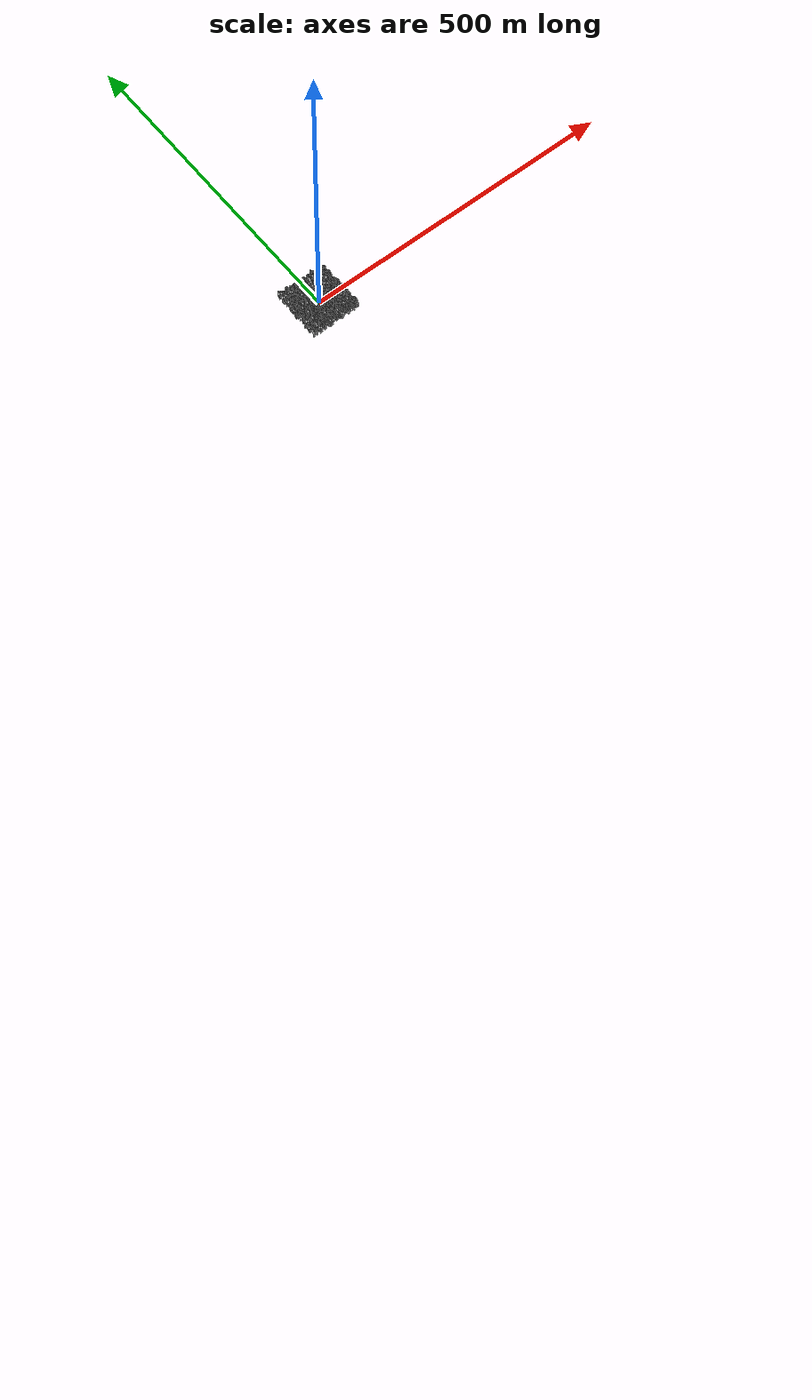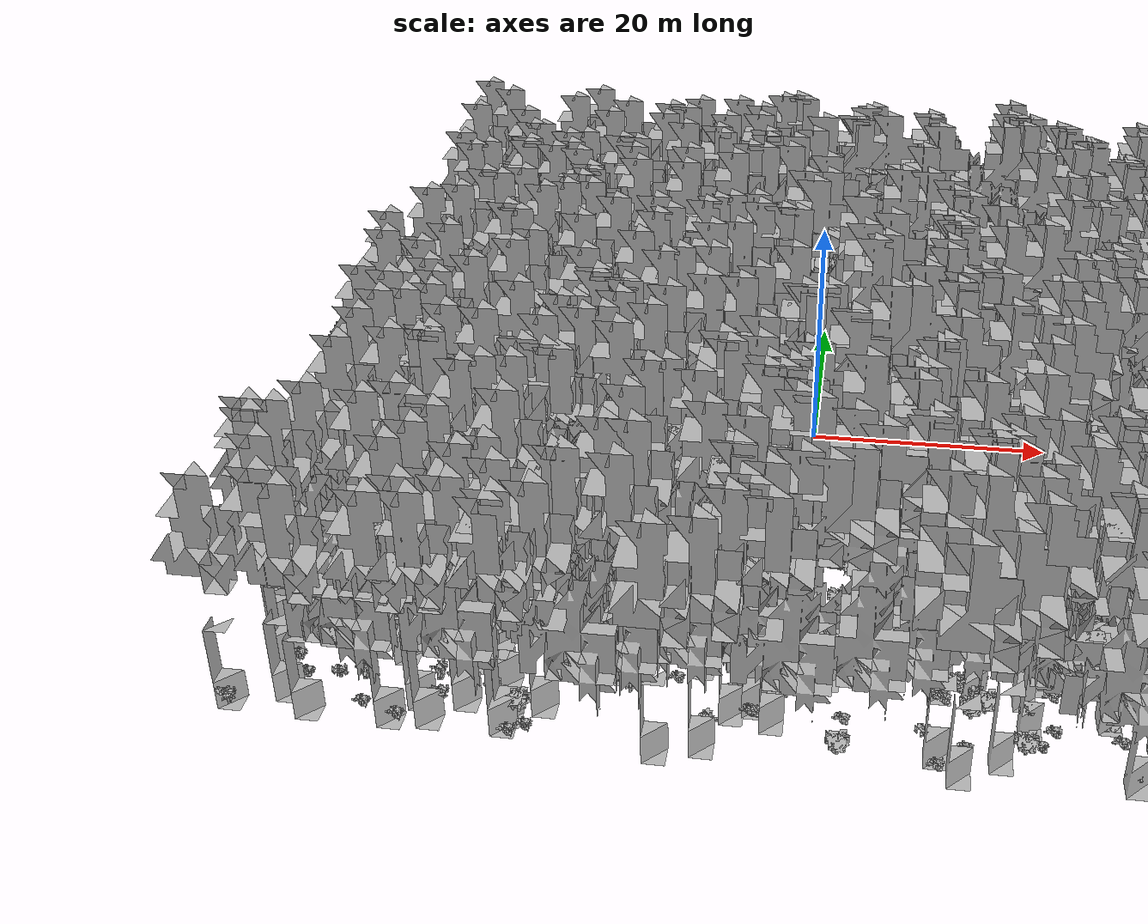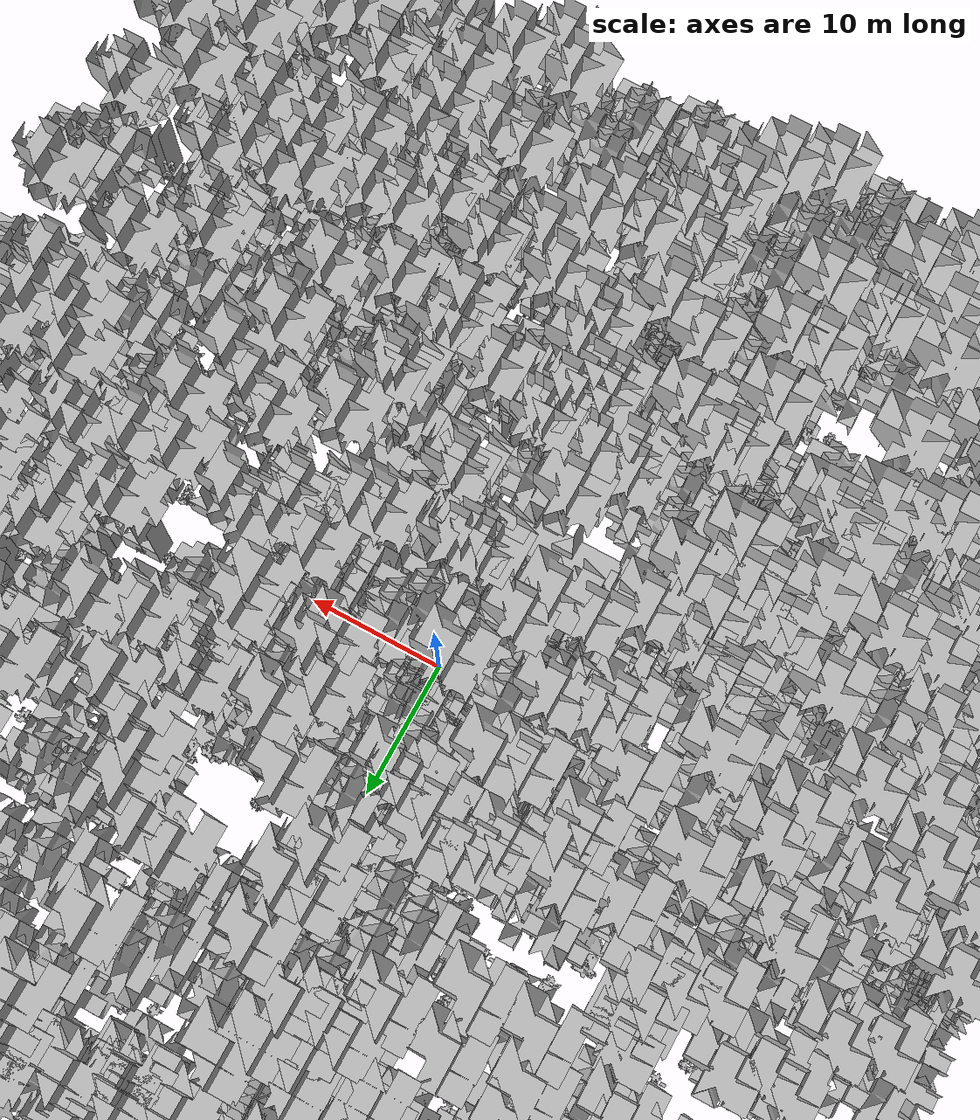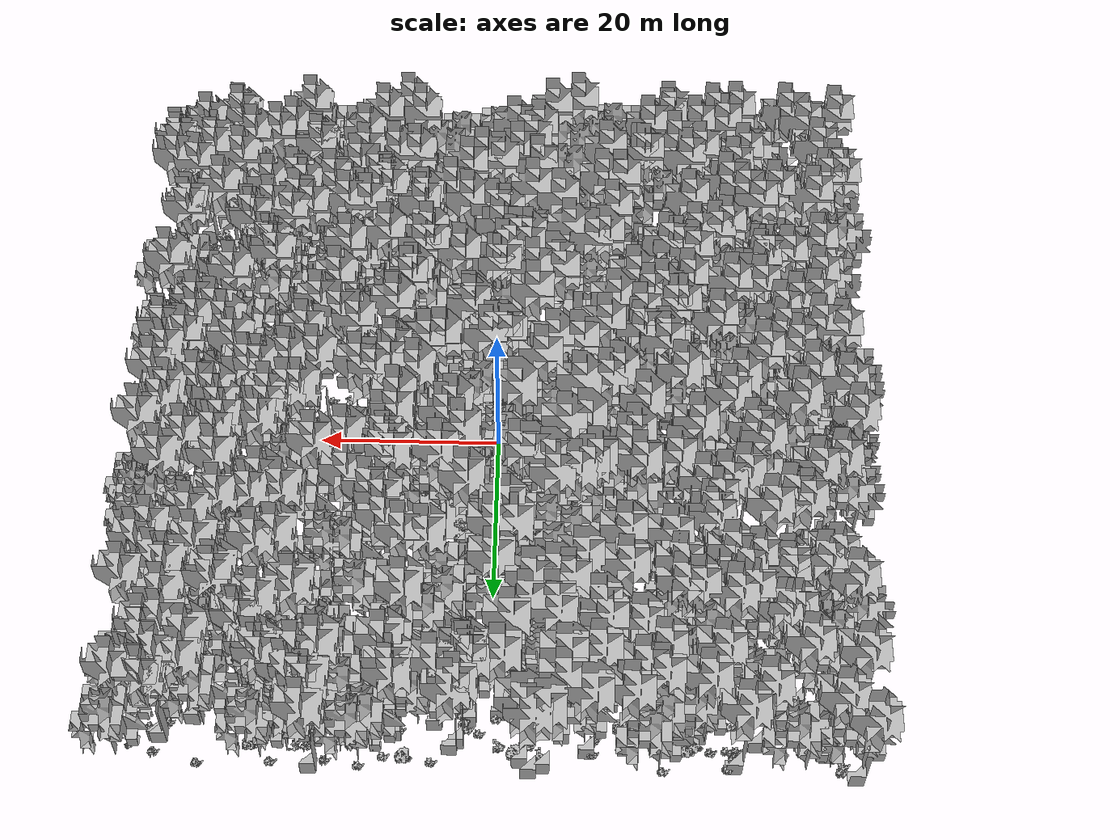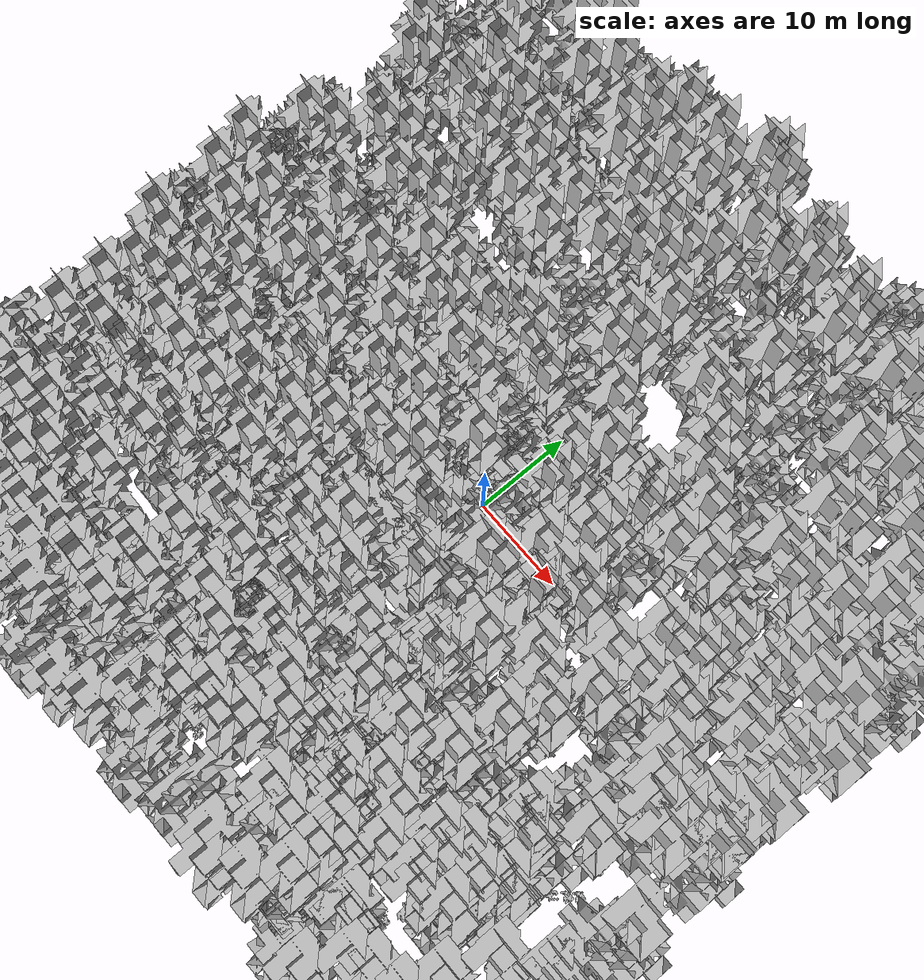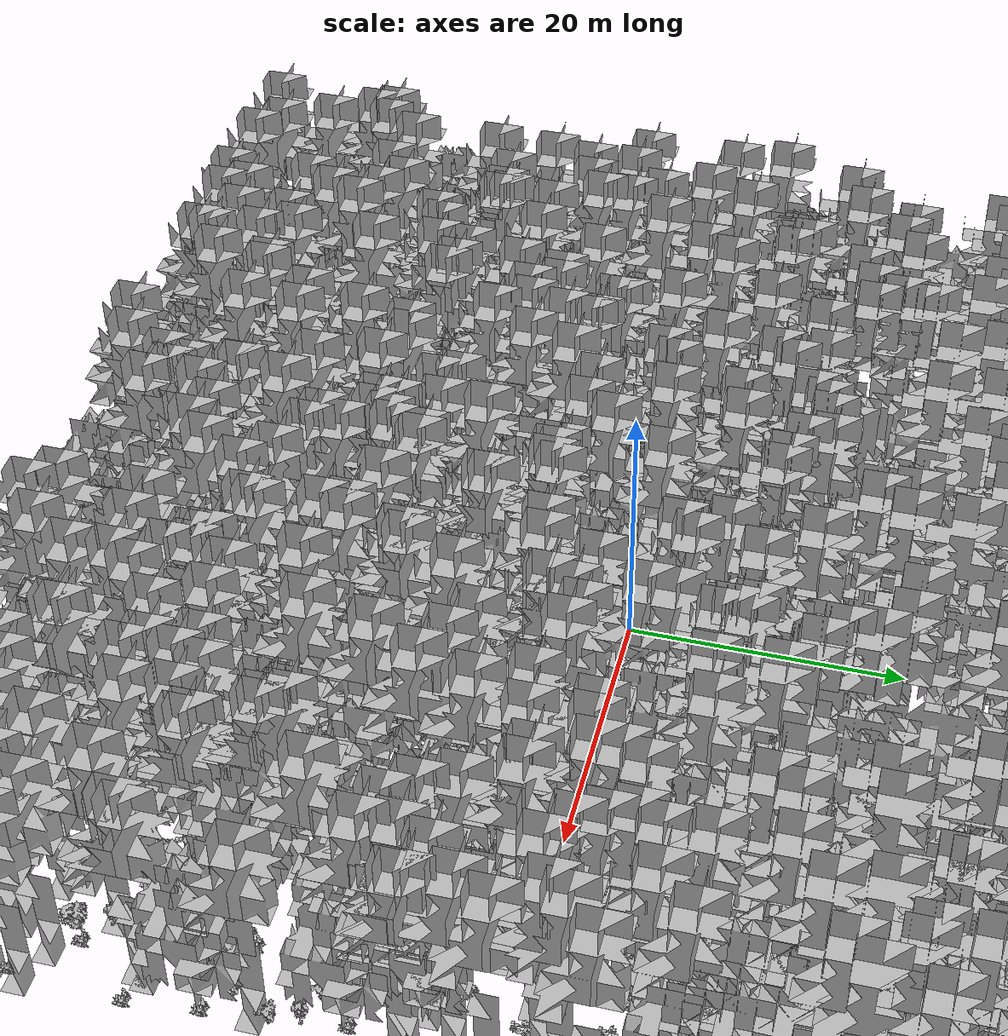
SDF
<sdf version="1.7">
    <world name="default">
        <plugin name="mrs_gazebo_static_transform_republisher_plugin" filename="libMrsGazeboCommonResources_StaticTransformRepublisher.so"/>
        <spherical_coordinates>
            <surface_model>EARTH_WGS84</surface_model>
            <latitude_deg>47.3977</latitude_deg>
            <longitude_deg>8.54559</longitude_deg>
            <elevation>0</elevation>
            <heading_deg>0</heading_deg>
        </spherical_coordinates>
        <physics name="default_physics" default="0" type="ode">
            <ode>
                <solver>
                    <type>quick</type>
                    <iters>10</iters>
                    <sor>1.3</sor>
                    <use_dynamic_moi_rescaling>0</use_dynamic_moi_rescaling>
                </solver>
                <constraints>
                    <cfm>0</cfm>
                    <erp>0.2</erp>
                    <contact_max_correcting_vel>1000</contact_max_correcting_vel>
                    <contact_surface_layer>0.001</contact_surface_layer>
                </constraints>
            </ode>
            <max_step_size>0.004</max_step_size>
            <real_time_factor>1</real_time_factor>
            <real_time_update_rate>250</real_time_update_rate>
        </physics>
        <scene>
            <shadows>0</shadows>
            <ambient>0.4 0.4 0.4 1</ambient>
            <background>0.7 0.7 0.7 1</background>
        </scene>
        <light name="sun" type="directional">
            <pose>0 0 1000 0.4 0.2 0</pose>
            <diffuse>1 1 1 1</diffuse>
            <specular>0.6 0.6 0.6 1</specular>
            <direction>0.1 0.1 -0.9</direction>
            <attenuation>
                <range>20</range>
                <constant>0.5</constant>
                <linear>0.01</linear>
                <quadratic>0.001</quadratic>
            </attenuation>
            <cast_shadows>1</cast_shadows>
            <spot>
                <inner_angle>0</inner_angle>
                <outer_angle>0</outer_angle>
                <falloff>0</falloff>
            </spot>
        </light>
        <model name="ground_plane">
            <static>1</static>
            <link name="link">
                <collision name="collision">
                    <pose>-50 0 0 0 -0 0</pose>
                    <geometry>
                        <plane>
                            <normal>0 0 1</normal>
                            <size>80 80</size>
                        </plane>
                    </geometry>
                    <surface>
                        <contact>
                            <ode>
                                <min_depth>0.01</min_depth>
                                <max_vel>0</max_vel>
                            </ode>
                        </contact>
                        <friction>
                            <ode/>
                            <torsional>
                                <ode/>
                            </torsional>
                        </friction>
                        <bounce/>
                    </surface>
                    <max_contacts>10</max_contacts>
                </collision>
                <visual name="grass">
                    <pose>0 0 0 0 -0 0</pose>
                    <cast_shadows>0</cast_shadows>
                    <geometry>
                        <mesh>
                            <scale>0.46714285714285714 0.46714285714285714 0.1</scale>
                            <uri>file://grass_plane/meshes/grass_plane.dae</uri>
                        </mesh>
                    </geometry>
                </visual>
                <self_collide>0</self_collide>
                <enable_wind>0</enable_wind>
                <kinematic>0</kinematic>
            </link>
        </model>
        <model name="the_void">
            <static>1</static>
            <link name="link">
                <pose>0 0 0.1 0 -0 0</pose>
                <visual name="the_void">
                    <pose>0 0 2 0 -0 0</pose>
                    <geometry>
                        <sphere>
                            <radius>0.25</radius>
                        </sphere>
                    </geometry>
                    <material>
                        <script>
                            <uri>file://media/materials/scripts/Gazebo.material</uri>
                            <name>Gazebo/Black</name>
                        </script>
                    </material>
                </visual>
                <self_collide>0</self_collide>
                <enable_wind>0</enable_wind>
                <kinematic>0</kinematic>
            </link>
            <pose>-1000 -1000 0 0 -0 0</pose>
        </model>
        <gui fullscreen="0">
            <camera name="camera">
                <pose>35.1577 98.6044 40.0204 0 0.407996 -1.99761</pose>
                <view_controller>orbit</view_controller>
                <projection_type>perspective</projection_type>
            </camera>
        </gui>
        <plugin name="mrs_gazebo_rviz_cam_synchronizer" filename="libMrsGazeboCommonResources_RvizCameraSynchronizer.so">
            <target_frame_id>gazebo_user_camera</target_frame_id>
            <world_origin_frame_id>uav1/gps_origin</world_origin_frame_id>
            <frame_to_follow>uav1</frame_to_follow>
        </plugin>
        <gravity>0 0 -9.8066</gravity>
        <magnetic_field>6e-06 2.3e-05 -4.2e-05</magnetic_field>
        <atmosphere type="adiabatic"/>
        <wind/>
        <model name="Tree 0">
            <static>1</static>
            <pose>-21.365664660761375 -4.4400965964897665 0 1.57079 -0 0</pose>
            <link name="link">
                <pose>0 0 0 0 -0 0</pose>
                <collision name="collision">
                    <geometry>
                        <mesh>
                            <scale>3.5 5 3.5</scale>
                            <uri>model://tree_2/meshes/tree_2.obj</uri>
                        </mesh>
                    </geometry>
                    <max_contacts>10</max_contacts>
                    <surface>
                        <contact>
                            <ode/>
                        </contact>
                        <bounce/>
                        <friction>
                            <torsional>
                                <ode/>
                            </torsional>
                            <ode/>
                        </friction>
                    </surface>
                </collision>
                <visual name="visual">
                    <geometry>
                        <mesh>
                            <scale>3.5 5 3.5</scale>
                            <uri>model://tree_2/meshes/tree_2.obj</uri>
                        </mesh>
                    </geometry>
                </visual>
                <self_collide>0</self_collide>
                <enable_wind>0</enable_wind>
                <kinematic>0</kinematic>
            </link>
        </model>
        <model name="Tree 1">
            <static>1</static>
            <pose>36.011166176725425 3.5830698787518287 0 1.57079 -0 0</pose>
            <link name="link">
                <pose>0 0 0 0 -0 0</pose>
                <collision name="collision">
                    <geometry>
                        <mesh>
                            <scale>3.5 5 3.5</scale>
                            <uri>model://tree_9/meshes/tree_9.obj</uri>
                        </mesh>
                    </geometry>
                    <max_contacts>10</max_contacts>
                    <surface>
                        <contact>
                            <ode/>
                        </contact>
                        <bounce/>
                        <friction>
                            <torsional>
                                <ode/>
                            </torsional>
                            <ode/>
                        </friction>
                    </surface>
                </collision>
                <visual name="visual">
                    <geometry>
                        <mesh>
                            <scale>3.5 5 3.5</scale>
                            <uri>model://tree_9/meshes/tree_9.obj</uri>
                        </mesh>
                    </geometry>
                </visual>
                <self_collide>0</self_collide>
                <enable_wind>0</enable_wind>
                <kinematic>0</kinematic>
            </link>
        </model>
        <model name="Tree 2">
            <static>1</static>
            <pose>34.41993841192634 -4.90887098662968 0 1.57079 -0 0</pose>
            <link name="link">
                <pose>0 0 0 0 -0 0</pose>
                <collision name="collision">
                    <geometry>
                        <mesh>
                            <scale>3.5 5 3.5</scale>
                            <uri>model://tree_9/meshes/tree_9.obj</uri>
                        </mesh>
                    </geometry>
                    <max_contacts>10</max_contacts>
                    <surface>
                        <contact>
                            <ode/>
                        </contact>
                        <bounce/>
                        <friction>
                            <torsional>
                                <ode/>
                            </torsional>
                            <ode/>
                        </friction>
                    </surface>
                </collision>
                <visual name="visual">
                    <geometry>
                        <mesh>
                            <scale>3.5 5 3.5</scale>
                            <uri>model://tree_9/meshes/tree_9.obj</uri>
                        </mesh>
                    </geometry>
                </visual>
                <self_collide>0</self_collide>
                <enable_wind>0</enable_wind>
                <kinematic>0</kinematic>
            </link>
        </model>
        <model name="Tree 3">
            <static>1</static>
            <pose>17.278344351615864 18.21155146762365 0 1.57079 -0 0</pose>
            <link name="link">
                <pose>0 0 0 0 -0 0</pose>
                <collision name="collision">
                    <geometry>
                        <mesh>
                            <scale>3.5 5 3.5</scale>
                            <uri>model://tree_2/meshes/tree_2.obj</uri>
                        </mesh>
                    </geometry>
                    <max_contacts>10</max_contacts>
                    <surface>
                        <contact>
                            <ode/>
                        </contact>
                        <bounce/>
                        <friction>
                            <torsional>
                                <ode/>
                            </torsional>
                            <ode/>
                        </friction>
                    </surface>
                </collision>
                <visual name="visual">
                    <geometry>
                        <mesh>
                            <scale>3.5 5 3.5</scale>
                            <uri>model://tree_2/meshes/tree_2.obj</uri>
                        </mesh>
                    </geometry>
                </visual>
                <self_collide>0</self_collide>
                <enable_wind>0</enable_wind>
                <kinematic>0</kinematic>
            </link>
        </model>
        <model name="Tree 4">
            <static>1</static>
            <pose>37.506167401468446 12.403594315080554 0 1.57079 -0 0</pose>
            <link name="link">
                <pose>0 0 0 0 -0 0</pose>
                <collision name="collision">
                    <geometry>
                        <mesh>
                            <scale>3.5 5 3.5</scale>
                            <uri>model://tree_2/meshes/tree_2.obj</uri>
                        </mesh>
                    </geometry>
                    <max_contacts>10</max_contacts>
                    <surface>
                        <contact>
                            <ode/>
                        </contact>
                        <bounce/>
                        <friction>
                            <torsional>
                                <ode/>
                            </torsional>
                            <ode/>
                        </friction>
                    </surface>
                </collision>
                <visual name="visual">
                    <geometry>
                        <mesh>
                            <scale>3.5 5 3.5</scale>
                            <uri>model://tree_2/meshes/tree_2.obj</uri>
                        </mesh>
                    </geometry>
                </visual>
                <self_collide>0</self_collide>
                <enable_wind>0</enable_wind>
                <kinematic>0</kinematic>
            </link>
        </model>
        <model name="Tree 5">
            <static>1</static>
            <pose>22.905808451735147 -2.1207265721238215 0 1.57079 -0 0</pose>
            <link name="link">
                <pose>0 0 0 0 -0 0</pose>
                <collision name="collision">
                    <geometry>
                        <mesh>
                            <scale>3.5 5 3.5</scale>
                            <uri>model://tree_9/meshes/tree_9.obj</uri>
                        </mesh>
                    </geometry>
                    <max_contacts>10</max_contacts>
                    <surface>
                        <contact>
                            <ode/>
                        </contact>
                        <bounce/>
                        <friction>
                            <torsional>
                                <ode/>
                            </torsional>
                            <ode/>
                        </friction>
                    </surface>
                </collision>
                <visual name="visual">
                    <geometry>
                        <mesh>
                            <scale>3.5 5 3.5</scale>
                            <uri>model://tree_9/meshes/tree_9.obj</uri>
                        </mesh>
                    </geometry>
                </visual>
                <self_collide>0</self_collide>
                <enable_wind>0</enable_wind>
                <kinematic>0</kinematic>
            </link>
        </model>
        <model name="Tree 6">
            <static>1</static>
            <pose>-15.32339733243926 10.425857822176283 0 1.57079 -0 0</pose>
            <link name="link">
                <pose>0 0 0 0 -0 0</pose>
                <collision name="collision">
                    <geometry>
                        <mesh>
                            <scale>3.5 5 3.5</scale>
                            <uri>model://tree_9/meshes/tree_9.obj</uri>
                        </mesh>
                    </geometry>
                    <max_contacts>10</max_contacts>
                    <surface>
                        <contact>
                            <ode/>
                        </contact>
                        <bounce/>
                        <friction>
                            <torsional>
                                <ode/>
                            </torsional>
                            <ode/>
                        </friction>
                    </surface>
                </collision>
                <visual name="visual">
                    <geometry>
                        <mesh>
                            <scale>3.5 5 3.5</scale>
                            <uri>model://tree_9/meshes/tree_9.obj</uri>
                        </mesh>
                    </geometry>
                </visual>
                <self_collide>0</self_collide>
                <enable_wind>0</enable_wind>
                <kinematic>0</kinematic>
            </link>
        </model>
        <model name="Tree 7">
            <static>1</static>
            <pose>22.965398107199924 -38.944472882966785 0 1.57079 -0 0</pose>
            <link name="link">
                <pose>0 0 0 0 -0 0</pose>
                <collision name="collision">
                    <geometry>
                        <mesh>
                            <scale>3.5 5 3.5</scale>
                            <uri>model://tree_9/meshes/tree_9.obj</uri>
                        </mesh>
                    </geometry>
                    <max_contacts>10</max_contacts>
                    <surface>
                        <contact>
                            <ode/>
                        </contact>
                        <bounce/>
                        <friction>
                            <torsional>
                                <ode/>
                            </torsional>
                            <ode/>
                        </friction>
                    </surface>
                </collision>
                <visual name="visual">
                    <geometry>
                        <mesh>
                            <scale>3.5 5 3.5</scale>
                            <uri>model://tree_9/meshes/tree_9.obj</uri>
                        </mesh>
                    </geometry>
                </visual>
                <self_collide>0</self_collide>
                <enable_wind>0</enable_wind>
                <kinematic>0</kinematic>
            </link>
        </model>
        <model name="Tree 8">
            <static>1</static>
            <pose>-34.936821159421164 27.565292205015695 0 1.57079 -0 0</pose>
            <link name="link">
                <pose>0 0 0 0 -0 0</pose>
                <collision name="collision">
                    <geometry>
                        <mesh>
                            <scale>3.5 5 3.5</scale>
                            <uri>model://tree_2/meshes/tree_2.obj</uri>
                        </mesh>
                    </geometry>
                    <max_contacts>10</max_contacts>
                    <surface>
                        <contact>
                            <ode/>
                        </contact>
                        <bounce/>
                        <friction>
                            <torsional>
                                <ode/>
                            </torsional>
                            <ode/>
                        </friction>
                    </surface>
                </collision>
                <visual name="visual">
                    <geometry>
                        <mesh>
                            <scale>3.5 5 3.5</scale>
                            <uri>model://tree_2/meshes/tree_2.obj</uri>
                        </mesh>
                    </geometry>
                </visual>
                <self_collide>0</self_collide>
                <enable_wind>0</enable_wind>
                <kinematic>0</kinematic>
            </link>
        </model>
        <model name="Tree 9">
            <static>1</static>
            <pose>-28.70857927524154 -17.509198013527776 0 1.57079 -0 0</pose>
            <link name="link">
                <pose>0 0 0 0 -0 0</pose>
                <collision name="collision">
                    <geometry>
                        <mesh>
                            <scale>3.5 5 3.5</scale>
                            <uri>model://tree_9/meshes/tree_9.obj</uri>
                        </mesh>
                    </geometry>
                    <max_contacts>10</max_contacts>
                    <surface>
                        <contact>
                            <ode/>
                        </contact>
                        <bounce/>
                        <friction>
                            <torsional>
                                <ode/>
                            </torsional>
                            <ode/>
                        </friction>
                    </surface>
                </collision>
                <visual name="visual">
                    <geometry>
                        <mesh>
                            <scale>3.5 5 3.5</scale>
                            <uri>model://tree_9/meshes/tree_9.obj</uri>
                        </mesh>
                    </geometry>
                </visual>
                <self_collide>0</self_collide>
                <enable_wind>0</enable_wind>
                <kinematic>0</kinematic>
            </link>
        </model>
        <model name="Tree 10">
            <static>1</static>
            <pose>26.165141318187068 -23.452140027372394 0 1.57079 -0 0</pose>
            <link name="link">
                <pose>0 0 0 0 -0 0</pose>
                <collision name="collision">
                    <geometry>
                        <mesh>
                            <scale>3.5 5 3.5</scale>
                            <uri>model://tree_2/meshes/tree_2.obj</uri>
                        </mesh>
                    </geometry>
                    <max_contacts>10</max_contacts>
                    <surface>
                        <contact>
                            <ode/>
                        </contact>
                        <bounce/>
                        <friction>
                            <torsional>
                                <ode/>
                            </torsional>
                            <ode/>
                        </friction>
                    </surface>
                </collision>
                <visual name="visual">
                    <geometry>
                        <mesh>
                            <scale>3.5 5 3.5</scale>
                            <uri>model://tree_2/meshes/tree_2.obj</uri>
                        </mesh>
                    </geometry>
                </visual>
                <self_collide>0</self_collide>
                <enable_wind>0</enable_wind>
                <kinematic>0</kinematic>
            </link>
        </model>
        <model name="Tree 11">
            <static>1</static>
            <pose>36.28284050110955 -2.9800546756138004 0 1.57079 -0 0</pose>
            <link name="link">
                <pose>0 0 0 0 -0 0</pose>
                <collision name="collision">
                    <geometry>
                        <mesh>
                            <scale>3.5 5 3.5</scale>
                            <uri>model://tree_9/meshes/tree_9.obj</uri>
                        </mesh>
                    </geometry>
                    <max_contacts>10</max_contacts>
                    <surface>
                        <contact>
                            <ode/>
                        </contact>
                        <bounce/>
                        <friction>
                            <torsional>
                                <ode/>
                            </torsional>
                            <ode/>
                        </friction>
                    </surface>
                </collision>
                <visual name="visual">
                    <geometry>
                        <mesh>
                            <scale>3.5 5 3.5</scale>
                            <uri>model://tree_9/meshes/tree_9.obj</uri>
                        </mesh>
                    </geometry>
                </visual>
                <self_collide>0</self_collide>
                <enable_wind>0</enable_wind>
                <kinematic>0</kinematic>
            </link>
        </model>
        <model name="Tree 12">
            <static>1</static>
            <pose>9.383092029047404 -24.18230322281498 0 1.57079 -0 0</pose>
            <link name="link">
                <pose>0 0 0 0 -0 0</pose>
                <collision name="collision">
                    <geometry>
                        <mesh>
                            <scale>3.5 5 3.5</scale>
                            <uri>model://tree_9/meshes/tree_9.obj</uri>
                        </mesh>
                    </geometry>
                    <max_contacts>10</max_contacts>
                    <surface>
                        <contact>
                            <ode/>
                        </contact>
                        <bounce/>
                        <friction>
                            <torsional>
                                <ode/>
                            </torsional>
                            <ode/>
                        </friction>
                    </surface>
                </collision>
                <visual name="visual">
                    <geometry>
                        <mesh>
                            <scale>3.5 5 3.5</scale>
                            <uri>model://tree_9/meshes/tree_9.obj</uri>
                        </mesh>
                    </geometry>
                </visual>
                <self_collide>0</self_collide>
                <enable_wind>0</enable_wind>
                <kinematic>0</kinematic>
            </link>
        </model>
        <model name="Tree 13">
            <static>1</static>
            <pose>38.2498424434265 -30.657005128210606 0 1.57079 -0 0</pose>
            <link name="link">
                <pose>0 0 0 0 -0 0</pose>
                <collision name="collision">
                    <geometry>
                        <mesh>
                            <scale>3.5 5 3.5</scale>
                            <uri>model://tree_9/meshes/tree_9.obj</uri>
                        </mesh>
                    </geometry>
                    <max_contacts>10</max_contacts>
                    <surface>
                        <contact>
                            <ode/>
                        </contact>
                        <bounce/>
                        <friction>
                            <torsional>
                                <ode/>
                            </torsional>
                            <ode/>
                        </friction>
                    </surface>
                </collision>
                <visual name="visual">
                    <geometry>
                        <mesh>
                            <scale>3.5 5 3.5</scale>
                            <uri>model://tree_9/meshes/tree_9.obj</uri>
                        </mesh>
                    </geometry>
                </visual>
                <self_collide>0</self_collide>
                <enable_wind>0</enable_wind>
                <kinematic>0</kinematic>
            </link>
        </model>
        <model name="Tree 14">
            <static>1</static>
            <pose>0.31850519076146355 -18.160462121770394 0 1.57079 -0 0</pose>
            <link name="link">
                <pose>0 0 0 0 -0 0</pose>
                <collision name="collision">
                    <geometry>
                        <mesh>
                            <scale>3.5 5 3.5</scale>
                            <uri>model://tree_2/meshes/tree_2.obj</uri>
                        </mesh>
                    </geometry>
                    <max_contacts>10</max_contacts>
                    <surface>
                        <contact>
                            <ode/>
                        </contact>
                        <bounce/>
                        <friction>
                            <torsional>
                                <ode/>
                            </torsional>
                            <ode/>
                        </friction>
                    </surface>
                </collision>
                <visual name="visual">
                    <geometry>
                        <mesh>
                            <scale>3.5 5 3.5</scale>
                            <uri>model://tree_2/meshes/tree_2.obj</uri>
                        </mesh>
                    </geometry>
                </visual>
                <self_collide>0</self_collide>
                <enable_wind>0</enable_wind>
                <kinematic>0</kinematic>
            </link>
        </model>
        <model name="Tree 15">
            <static>1</static>
            <pose>-31.19612990582195 6.275217418282715 0 1.57079 -0 0</pose>
            <link name="link">
                <pose>0 0 0 0 -0 0</pose>
                <collision name="collision">
                    <geometry>
                        <mesh>
                            <scale>3.5 5 3.5</scale>
                            <uri>model://tree_2/meshes/tree_2.obj</uri>
                        </mesh>
                    </geometry>
                    <max_contacts>10</max_contacts>
                    <surface>
                        <contact>
                            <ode/>
                        </contact>
                        <bounce/>
                        <friction>
                            <torsional>
                                <ode/>
                            </torsional>
                            <ode/>
                        </friction>
                    </surface>
                </collision>
                <visual name="visual">
                    <geometry>
                        <mesh>
                            <scale>3.5 5 3.5</scale>
                            <uri>model://tree_2/meshes/tree_2.obj</uri>
                        </mesh>
                    </geometry>
                </visual>
                <self_collide>0</self_collide>
                <enable_wind>0</enable_wind>
                <kinematic>0</kinematic>
            </link>
        </model>
        <model name="Tree 16">
            <static>1</static>
            <pose>10.309898231262537 -13.495058565896294 0 1.57079 -0 0</pose>
            <link name="link">
                <pose>0 0 0 0 -0 0</pose>
                <collision name="collision">
                    <geometry>
                        <mesh>
                            <scale>3.5 5 3.5</scale>
                            <uri>model://tree_9/meshes/tree_9.obj</uri>
                        </mesh>
                    </geometry>
                    <max_contacts>10</max_contacts>
                    <surface>
                        <contact>
                            <ode/>
                        </contact>
                        <bounce/>
                        <friction>
                            <torsional>
                                <ode/>
                            </torsional>
                            <ode/>
                        </friction>
                    </surface>
                </collision>
                <visual name="visual">
                    <geometry>
                        <mesh>
                            <scale>3.5 5 3.5</scale>
                            <uri>model://tree_9/meshes/tree_9.obj</uri>
                        </mesh>
                    </geometry>
                </visual>
                <self_collide>0</self_collide>
                <enable_wind>0</enable_wind>
                <kinematic>0</kinematic>
            </link>
        </model>
        <model name="Tree 17">
            <static>1</static>
            <pose>1.223079849353475 -5.488641896530517 0 1.57079 -0 0</pose>
            <link name="link">
                <pose>0 0 0 0 -0 0</pose>
                <collision name="collision">
                    <geometry>
                        <mesh>
                            <scale>3.5 5 3.5</scale>
                            <uri>model://tree_9/meshes/tree_9.obj</uri>
                        </mesh>
                    </geometry>
                    <max_contacts>10</max_contacts>
                    <surface>
                        <contact>
                            <ode/>
                        </contact>
                        <bounce/>
                        <friction>
                            <torsional>
                                <ode/>
                            </torsional>
                            <ode/>
                        </friction>
                    </surface>
                </collision>
                <visual name="visual">
                    <geometry>
                        <mesh>
                            <scale>3.5 5 3.5</scale>
                            <uri>model://tree_9/meshes/tree_9.obj</uri>
                        </mesh>
                    </geometry>
                </visual>
                <self_collide>0</self_collide>
                <enable_wind>0</enable_wind>
                <kinematic>0</kinematic>
            </link>
        </model>
        <model name="Tree 18">
            <static>1</static>
            <pose>-25.525492926385198 -28.110148327706312 0 1.57079 -0 0</pose>
            <link name="link">
                <pose>0 0 0 0 -0 0</pose>
                <collision name="collision">
                    <geometry>
                        <mesh>
                            <scale>3.5 5 3.5</scale>
                            <uri>model://tree_9/meshes/tree_9.obj</uri>
                        </mesh>
                    </geometry>
                    <max_contacts>10</max_contacts>
                    <surface>
                        <contact>
                            <ode/>
                        </contact>
                        <bounce/>
                        <friction>
                            <torsional>
                                <ode/>
                            </torsional>
                            <ode/>
                        </friction>
                    </surface>
                </collision>
                <visual name="visual">
                    <geometry>
                        <mesh>
                            <scale>3.5 5 3.5</scale>
                            <uri>model://tree_9/meshes/tree_9.obj</uri>
                        </mesh>
                    </geometry>
                </visual>
                <self_collide>0</self_collide>
                <enable_wind>0</enable_wind>
                <kinematic>0</kinematic>
            </link>
        </model>
        <model name="Tree 19">
            <static>1</static>
            <pose>24.2888758817339 -22.473327997782818 0 1.57079 -0 0</pose>
            <link name="link">
                <pose>0 0 0 0 -0 0</pose>
                <collision name="collision">
                    <geometry>
                        <mesh>
                            <scale>3.5 5 3.5</scale>
                            <uri>model://tree_9/meshes/tree_9.obj</uri>
                        </mesh>
                    </geometry>
                    <max_contacts>10</max_contacts>
                    <surface>
                        <contact>
                            <ode/>
                        </contact>
                        <bounce/>
                        <friction>
                            <torsional>
                                <ode/>
                            </torsional>
                            <ode/>
                        </friction>
                    </surface>
                </collision>
                <visual name="visual">
                    <geometry>
                        <mesh>
                            <scale>3.5 5 3.5</scale>
                            <uri>model://tree_9/meshes/tree_9.obj</uri>
                        </mesh>
                    </geometry>
                </visual>
                <self_collide>0</self_collide>
                <enable_wind>0</enable_wind>
                <kinematic>0</kinematic>
            </link>
        </model>
        <model name="Tree 20">
            <static>1</static>
            <pose>1.419046243965191 -1.5328491475228816 0 1.57079 -0 0</pose>
            <link name="link">
                <pose>0 0 0 0 -0 0</pose>
                <collision name="collision">
                    <geometry>
                        <mesh>
                            <scale>3.5 5 3.5</scale>
                            <uri>model://tree_2/meshes/tree_2.obj</uri>
                        </mesh>
                    </geometry>
                    <max_contacts>10</max_contacts>
                    <surface>
                        <contact>
                            <ode/>
                        </contact>
                        <bounce/>
                        <friction>
                            <torsional>
                                <ode/>
                            </torsional>
                            <ode/>
                        </friction>
                    </surface>
                </collision>
                <visual name="visual">
                    <geometry>
                        <mesh>
                            <scale>3.5 5 3.5</scale>
                            <uri>model://tree_2/meshes/tree_2.obj</uri>
                        </mesh>
                    </geometry>
                </visual>
                <self_collide>0</self_collide>
                <enable_wind>0</enable_wind>
                <kinematic>0</kinematic>
            </link>
        </model>
        <model name="Tree 21">
            <static>1</static>
            <pose>-37.32069303285222 5.129252483326766 0 1.57079 -0 0</pose>
            <link name="link">
                <pose>0 0 0 0 -0 0</pose>
                <collision name="collision">
                    <geometry>
                        <mesh>
                            <scale>3.5 5 3.5</scale>
                            <uri>model://tree_2/meshes/tree_2.obj</uri>
                        </mesh>
                    </geometry>
                    <max_contacts>10</max_contacts>
                    <surface>
                        <contact>
                            <ode/>
                        </contact>
                        <bounce/>
                        <friction>
                            <torsional>
                                <ode/>
                            </torsional>
                            <ode/>
                        </friction>
                    </surface>
                </collision>
                <visual name="visual">
                    <geometry>
                        <mesh>
                            <scale>3.5 5 3.5</scale>
                            <uri>model://tree_2/meshes/tree_2.obj</uri>
                        </mesh>
                    </geometry>
                </visual>
                <self_collide>0</self_collide>
                <enable_wind>0</enable_wind>
                <kinematic>0</kinematic>
            </link>
        </model>
        <model name="Tree 22">
            <static>1</static>
            <pose>7.396692323783576 -1.14076177592176 0 1.57079 -0 0</pose>
            <link name="link">
                <pose>0 0 0 0 -0 0</pose>
                <collision name="collision">
                    <geometry>
                        <mesh>
                            <scale>3.5 5 3.5</scale>
                            <uri>model://tree_2/meshes/tree_2.obj</uri>
                        </mesh>
                    </geometry>
                    <max_contacts>10</max_contacts>
                    <surface>
                        <contact>
                            <ode/>
                        </contact>
                        <bounce/>
                        <friction>
                            <torsional>
                                <ode/>
                            </torsional>
                            <ode/>
                        </friction>
                    </surface>
                </collision>
                <visual name="visual">
                    <geometry>
                        <mesh>
                            <scale>3.5 5 3.5</scale>
                            <uri>model://tree_2/meshes/tree_2.obj</uri>
                        </mesh>
                    </geometry>
                </visual>
                <self_collide>0</self_collide>
                <enable_wind>0</enable_wind>
                <kinematic>0</kinematic>
            </link>
        </model>
        <model name="Tree 23">
            <static>1</static>
            <pose>-36.226139031111416 -33.58327039056681 0 1.57079 -0 0</pose>
            <link name="link">
                <pose>0 0 0 0 -0 0</pose>
                <collision name="collision">
                    <geometry>
                        <mesh>
                            <scale>3.5 5 3.5</scale>
                            <uri>model://tree_9/meshes/tree_9.obj</uri>
                        </mesh>
                    </geometry>
                    <max_contacts>10</max_contacts>
                    <surface>
                        <contact>
                            <ode/>
                        </contact>
                        <bounce/>
                        <friction>
                            <torsional>
                                <ode/>
                            </torsional>
                            <ode/>
                        </friction>
                    </surface>
                </collision>
                <visual name="visual">
                    <geometry>
                        <mesh>
                            <scale>3.5 5 3.5</scale>
                            <uri>model://tree_9/meshes/tree_9.obj</uri>
                        </mesh>
                    </geometry>
                </visual>
                <self_collide>0</self_collide>
                <enable_wind>0</enable_wind>
                <kinematic>0</kinematic>
            </link>
        </model>
        <model name="Tree 24">
            <static>1</static>
            <pose>10.550268060341537 -24.655328022917278 0 1.57079 -0 0</pose>
            <link name="link">
                <pose>0 0 0 0 -0 0</pose>
                <collision name="collision">
                    <geometry>
                        <mesh>
                            <scale>3.5 5 3.5</scale>
                            <uri>model://tree_2/meshes/tree_2.obj</uri>
                        </mesh>
                    </geometry>
                    <max_contacts>10</max_contacts>
                    <surface>
                        <contact>
                            <ode/>
                        </contact>
                        <bounce/>
                        <friction>
                            <torsional>
                                <ode/>
                            </torsional>
                            <ode/>
                        </friction>
                    </surface>
                </collision>
                <visual name="visual">
                    <geometry>
                        <mesh>
                            <scale>3.5 5 3.5</scale>
                            <uri>model://tree_2/meshes/tree_2.obj</uri>
                        </mesh>
                    </geometry>
                </visual>
                <self_collide>0</self_collide>
                <enable_wind>0</enable_wind>
                <kinematic>0</kinematic>
            </link>
        </model>
        <model name="Tree 25">
            <static>1</static>
            <pose>-6.406606504228115 -25.172013029771758 0 1.57079 -0 0</pose>
            <link name="link">
                <pose>0 0 0 0 -0 0</pose>
                <collision name="collision">
                    <geometry>
                        <mesh>
                            <scale>3.5 5 3.5</scale>
                            <uri>model://tree_9/meshes/tree_9.obj</uri>
                        </mesh>
                    </geometry>
                    <max_contacts>10</max_contacts>
                    <surface>
                        <contact>
                            <ode/>
                        </contact>
                        <bounce/>
                        <friction>
                            <torsional>
                                <ode/>
                            </torsional>
                            <ode/>
                        </friction>
                    </surface>
                </collision>
                <visual name="visual">
                    <geometry>
                        <mesh>
                            <scale>3.5 5 3.5</scale>
                            <uri>model://tree_9/meshes/tree_9.obj</uri>
                        </mesh>
                    </geometry>
                </visual>
                <self_collide>0</self_collide>
                <enable_wind>0</enable_wind>
                <kinematic>0</kinematic>
            </link>
        </model>
        <model name="Tree 26">
            <static>1</static>
            <pose>-34.21865111880474 -4.678631937713277 0 1.57079 -0 0</pose>
            <link name="link">
                <pose>0 0 0 0 -0 0</pose>
                <collision name="collision">
                    <geometry>
                        <mesh>
                            <scale>3.5 5 3.5</scale>
                            <uri>model://tree_2/meshes/tree_2.obj</uri>
                        </mesh>
                    </geometry>
                    <max_contacts>10</max_contacts>
                    <surface>
                        <contact>
                            <ode/>
                        </contact>
                        <bounce/>
                        <friction>
                            <torsional>
                                <ode/>
                            </torsional>
                            <ode/>
                        </friction>
                    </surface>
                </collision>
                <visual name="visual">
                    <geometry>
                        <mesh>
                            <scale>3.5 5 3.5</scale>
                            <uri>model://tree_2/meshes/tree_2.obj</uri>
                        </mesh>
                    </geometry>
                </visual>
                <self_collide>0</self_collide>
                <enable_wind>0</enable_wind>
                <kinematic>0</kinematic>
            </link>
        </model>
        <model name="Tree 27">
            <static>1</static>
            <pose>-28.675681978317527 8.44207501688436 0 1.57079 -0 0</pose>
            <link name="link">
                <pose>0 0 0 0 -0 0</pose>
                <collision name="collision">
                    <geometry>
                        <mesh>
                            <scale>3.5 5 3.5</scale>
                            <uri>model://tree_2/meshes/tree_2.obj</uri>
                        </mesh>
                    </geometry>
                    <max_contacts>10</max_contacts>
                    <surface>
                        <contact>
                            <ode/>
                        </contact>
                        <bounce/>
                        <friction>
                            <torsional>
                                <ode/>
                            </torsional>
                            <ode/>
                        </friction>
                    </surface>
                </collision>
                <visual name="visual">
                    <geometry>
                        <mesh>
                            <scale>3.5 5 3.5</scale>
                            <uri>model://tree_2/meshes/tree_2.obj</uri>
                        </mesh>
                    </geometry>
                </visual>
                <self_collide>0</self_collide>
                <enable_wind>0</enable_wind>
                <kinematic>0</kinematic>
            </link>
        </model>
        <model name="Tree 28">
            <static>1</static>
            <pose>-0.13650152388446912 4.405217555593211 0 1.57079 -0 0</pose>
            <link name="link">
                <pose>0 0 0 0 -0 0</pose>
                <collision name="collision">
                    <geometry>
                        <mesh>
                            <scale>3.5 5 3.5</scale>
                            <uri>model://tree_2/meshes/tree_2.obj</uri>
                        </mesh>
                    </geometry>
                    <max_contacts>10</max_contacts>
                    <surface>
                        <contact>
                            <ode/>
                        </contact>
                        <bounce/>
                        <friction>
                            <torsional>
                                <ode/>
                            </torsional>
                            <ode/>
                        </friction>
                    </surface>
                </collision>
                <visual name="visual">
                    <geometry>
                        <mesh>
                            <scale>3.5 5 3.5</scale>
                            <uri>model://tree_2/meshes/tree_2.obj</uri>
                        </mesh>
                    </geometry>
                </visual>
                <self_collide>0</self_collide>
                <enable_wind>0</enable_wind>
                <kinematic>0</kinematic>
            </link>
        </model>
        <model name="Tree 29">
            <static>1</static>
            <pose>17.50396830890879 -36.59775077264011 0 1.57079 -0 0</pose>
            <link name="link">
                <pose>0 0 0 0 -0 0</pose>
                <collision name="collision">
                    <geometry>
                        <mesh>
                            <scale>3.5 5 3.5</scale>
                            <uri>model://tree_2/meshes/tree_2.obj</uri>
                        </mesh>
                    </geometry>
                    <max_contacts>10</max_contacts>
                    <surface>
                        <contact>
                            <ode/>
                        </contact>
                        <bounce/>
                        <friction>
                            <torsional>
                                <ode/>
                            </torsional>
                            <ode/>
                        </friction>
                    </surface>
                </collision>
                <visual name="visual">
                    <geometry>
                        <mesh>
                            <scale>3.5 5 3.5</scale>
                            <uri>model://tree_2/meshes/tree_2.obj</uri>
                        </mesh>
                    </geometry>
                </visual>
                <self_collide>0</self_collide>
                <enable_wind>0</enable_wind>
                <kinematic>0</kinematic>
            </link>
        </model>
        <model name="Tree 30">
            <static>1</static>
            <pose>10.430734319268318 6.563693035591072 0 1.57079 -0 0</pose>
            <link name="link">
                <pose>0 0 0 0 -0 0</pose>
                <collision name="collision">
                    <geometry>
                        <mesh>
                            <scale>3.5 5 3.5</scale>
                            <uri>model://tree_2/meshes/tree_2.obj</uri>
                        </mesh>
                    </geometry>
                    <max_contacts>10</max_contacts>
                    <surface>
                        <contact>
                            <ode/>
                        </contact>
                        <bounce/>
                        <friction>
                            <torsional>
                                <ode/>
                            </torsional>
                            <ode/>
                        </friction>
                    </surface>
                </collision>
                <visual name="visual">
                    <geometry>
                        <mesh>
                            <scale>3.5 5 3.5</scale>
                            <uri>model://tree_2/meshes/tree_2.obj</uri>
                        </mesh>
                    </geometry>
                </visual>
                <self_collide>0</self_collide>
                <enable_wind>0</enable_wind>
                <kinematic>0</kinematic>
            </link>
        </model>
        <model name="Tree 31">
            <static>1</static>
            <pose>-22.758737027457613 17.251786280701786 0 1.57079 -0 0</pose>
            <link name="link">
                <pose>0 0 0 0 -0 0</pose>
                <collision name="collision">
                    <geometry>
                        <mesh>
                            <scale>3.5 5 3.5</scale>
                            <uri>model://tree_9/meshes/tree_9.obj</uri>
                        </mesh>
                    </geometry>
                    <max_contacts>10</max_contacts>
                    <surface>
                        <contact>
                            <ode/>
                        </contact>
                        <bounce/>
                        <friction>
                            <torsional>
                                <ode/>
                            </torsional>
                            <ode/>
                        </friction>
                    </surface>
                </collision>
                <visual name="visual">
                    <geometry>
                        <mesh>
                            <scale>3.5 5 3.5</scale>
                            <uri>model://tree_9/meshes/tree_9.obj</uri>
                        </mesh>
                    </geometry>
                </visual>
                <self_collide>0</self_collide>
                <enable_wind>0</enable_wind>
                <kinematic>0</kinematic>
            </link>
        </model>
        <model name="Tree 32">
            <static>1</static>
            <pose>-14.584538147157481 -16.63451784371337 0 1.57079 -0 0</pose>
            <link name="link">
                <pose>0 0 0 0 -0 0</pose>
                <collision name="collision">
                    <geometry>
                        <mesh>
                            <scale>3.5 5 3.5</scale>
                            <uri>model://tree_2/meshes/tree_2.obj</uri>
                        </mesh>
                    </geometry>
                    <max_contacts>10</max_contacts>
                    <surface>
                        <contact>
                            <ode/>
                        </contact>
                        <bounce/>
                        <friction>
                            <torsional>
                                <ode/>
                            </torsional>
                            <ode/>
                        </friction>
                    </surface>
                </collision>
                <visual name="visual">
                    <geometry>
                        <mesh>
                            <scale>3.5 5 3.5</scale>
                            <uri>model://tree_2/meshes/tree_2.obj</uri>
                        </mesh>
                    </geometry>
                </visual>
                <self_collide>0</self_collide>
                <enable_wind>0</enable_wind>
                <kinematic>0</kinematic>
            </link>
        </model>
        <model name="Tree 33">
            <static>1</static>
            <pose>0.6437556588866613 -39.039858020370275 0 1.57079 -0 0</pose>
            <link name="link">
                <pose>0 0 0 0 -0 0</pose>
                <collision name="collision">
                    <geometry>
                        <mesh>
                            <scale>3.5 5 3.5</scale>
                            <uri>model://tree_2/meshes/tree_2.obj</uri>
                        </mesh>
                    </geometry>
                    <max_contacts>10</max_contacts>
                    <surface>
                        <contact>
                            <ode/>
                        </contact>
                        <bounce/>
                        <friction>
                            <torsional>
                                <ode/>
                            </torsional>
                            <ode/>
                        </friction>
                    </surface>
                </collision>
                <visual name="visual">
                    <geometry>
                        <mesh>
                            <scale>3.5 5 3.5</scale>
                            <uri>model://tree_2/meshes/tree_2.obj</uri>
                        </mesh>
                    </geometry>
                </visual>
                <self_collide>0</self_collide>
                <enable_wind>0</enable_wind>
                <kinematic>0</kinematic>
            </link>
        </model>
        <model name="Tree 34">
            <static>1</static>
            <pose>4.572784560352893 -16.918602772408377 0 1.57079 -0 0</pose>
            <link name="link">
                <pose>0 0 0 0 -0 0</pose>
                <collision name="collision">
                    <geometry>
                        <mesh>
                            <scale>3.5 5 3.5</scale>
                            <uri>model://tree_9/meshes/tree_9.obj</uri>
                        </mesh>
                    </geometry>
                    <max_contacts>10</max_contacts>
                    <surface>
                        <contact>
                            <ode/>
                        </contact>
                        <bounce/>
                        <friction>
                            <torsional>
                                <ode/>
                            </torsional>
                            <ode/>
                        </friction>
                    </surface>
                </collision>
                <visual name="visual">
                    <geometry>
                        <mesh>
                            <scale>3.5 5 3.5</scale>
                            <uri>model://tree_9/meshes/tree_9.obj</uri>
                        </mesh>
                    </geometry>
                </visual>
                <self_collide>0</self_collide>
                <enable_wind>0</enable_wind>
                <kinematic>0</kinematic>
            </link>
        </model>
        <model name="Tree 35">
            <static>1</static>
            <pose>-8.409194264973163 16.946527934792982 0 1.57079 -0 0</pose>
            <link name="link">
                <pose>0 0 0 0 -0 0</pose>
                <collision name="collision">
                    <geometry>
                        <mesh>
                            <scale>3.5 5 3.5</scale>
                            <uri>model://tree_2/meshes/tree_2.obj</uri>
                        </mesh>
                    </geometry>
                    <max_contacts>10</max_contacts>
                    <surface>
                        <contact>
                            <ode/>
                        </contact>
                        <bounce/>
                        <friction>
                            <torsional>
                                <ode/>
                            </torsional>
                            <ode/>
                        </friction>
                    </surface>
                </collision>
                <visual name="visual">
                    <geometry>
                        <mesh>
                            <scale>3.5 5 3.5</scale>
                            <uri>model://tree_2/meshes/tree_2.obj</uri>
                        </mesh>
                    </geometry>
                </visual>
                <self_collide>0</self_collide>
                <enable_wind>0</enable_wind>
                <kinematic>0</kinematic>
            </link>
        </model>
        <model name="Tree 36">
            <static>1</static>
            <pose>-20.632927468682883 31.796684143006345 0 1.57079 -0 0</pose>
            <link name="link">
                <pose>0 0 0 0 -0 0</pose>
                <collision name="collision">
                    <geometry>
                        <mesh>
                            <scale>3.5 5 3.5</scale>
                            <uri>model://tree_2/meshes/tree_2.obj</uri>
                        </mesh>
                    </geometry>
                    <max_contacts>10</max_contacts>
                    <surface>
                        <contact>
                            <ode/>
                        </contact>
                        <bounce/>
                        <friction>
                            <torsional>
                                <ode/>
                            </torsional>
                            <ode/>
                        </friction>
                    </surface>
                </collision>
                <visual name="visual">
                    <geometry>
                        <mesh>
                            <scale>3.5 5 3.5</scale>
                            <uri>model://tree_2/meshes/tree_2.obj</uri>
                        </mesh>
                    </geometry>
                </visual>
                <self_collide>0</self_collide>
                <enable_wind>0</enable_wind>
                <kinematic>0</kinematic>
            </link>
        </model>
        <model name="Tree 37">
            <static>1</static>
            <pose>-37.39812950651317 25.847870053244762 0 1.57079 -0 0</pose>
            <link name="link">
                <pose>0 0 0 0 -0 0</pose>
                <collision name="collision">
                    <geometry>
                        <mesh>
                            <scale>3.5 5 3.5</scale>
                            <uri>model://tree_2/meshes/tree_2.obj</uri>
                        </mesh>
                    </geometry>
                    <max_contacts>10</max_contacts>
                    <surface>
                        <contact>
                            <ode/>
                        </contact>
                        <bounce/>
                        <friction>
                            <torsional>
                                <ode/>
                            </torsional>
                            <ode/>
                        </friction>
                    </surface>
                </collision>
                <visual name="visual">
                    <geometry>
                        <mesh>
                            <scale>3.5 5 3.5</scale>
                            <uri>model://tree_2/meshes/tree_2.obj</uri>
                        </mesh>
                    </geometry>
                </visual>
                <self_collide>0</self_collide>
                <enable_wind>0</enable_wind>
                <kinematic>0</kinematic>
            </link>
        </model>
        <model name="Tree 38">
            <static>1</static>
            <pose>-22.08386645626849 -16.838610110640275 0 1.57079 -0 0</pose>
            <link name="link">
                <pose>0 0 0 0 -0 0</pose>
                <collision name="collision">
                    <geometry>
                        <mesh>
                            <scale>3.5 5 3.5</scale>
                            <uri>model://tree_2/meshes/tree_2.obj</uri>
                        </mesh>
                    </geometry>
                    <max_contacts>10</max_contacts>
                    <surface>
                        <contact>
                            <ode/>
                        </contact>
                        <bounce/>
                        <friction>
                            <torsional>
                                <ode/>
                            </torsional>
                            <ode/>
                        </friction>
                    </surface>
                </collision>
                <visual name="visual">
                    <geometry>
                        <mesh>
                            <scale>3.5 5 3.5</scale>
                            <uri>model://tree_2/meshes/tree_2.obj</uri>
                        </mesh>
                    </geometry>
                </visual>
                <self_collide>0</self_collide>
                <enable_wind>0</enable_wind>
                <kinematic>0</kinematic>
            </link>
        </model>
        <model name="Tree 39">
            <static>1</static>
            <pose>25.471126532992812 29.7137734956885 0 1.57079 -0 0</pose>
            <link name="link">
                <pose>0 0 0 0 -0 0</pose>
                <collision name="collision">
                    <geometry>
                        <mesh>
                            <scale>3.5 5 3.5</scale>
                            <uri>model://tree_9/meshes/tree_9.obj</uri>
                        </mesh>
                    </geometry>
                    <max_contacts>10</max_contacts>
                    <surface>
                        <contact>
                            <ode/>
                        </contact>
                        <bounce/>
                        <friction>
                            <torsional>
                                <ode/>
                            </torsional>
                            <ode/>
                        </friction>
                    </surface>
                </collision>
                <visual name="visual">
                    <geometry>
                        <mesh>
                            <scale>3.5 5 3.5</scale>
                            <uri>model://tree_9/meshes/tree_9.obj</uri>
                        </mesh>
                    </geometry>
                </visual>
                <self_collide>0</self_collide>
                <enable_wind>0</enable_wind>
                <kinematic>0</kinematic>
            </link>
        </model>
        <model name="Tree 40">
            <static>1</static>
            <pose>11.739753798254611 -28.791333524938977 0 1.57079 -0 0</pose>
            <link name="link">
                <pose>0 0 0 0 -0 0</pose>
                <collision name="collision">
                    <geometry>
                        <mesh>
                            <scale>3.5 5 3.5</scale>
                            <uri>model://tree_2/meshes/tree_2.obj</uri>
                        </mesh>
                    </geometry>
                    <max_contacts>10</max_contacts>
                    <surface>
                        <contact>
                            <ode/>
                        </contact>
                        <bounce/>
                        <friction>
                            <torsional>
                                <ode/>
                            </torsional>
                            <ode/>
                        </friction>
                    </surface>
                </collision>
                <visual name="visual">
                    <geometry>
                        <mesh>
                            <scale>3.5 5 3.5</scale>
                            <uri>model://tree_2/meshes/tree_2.obj</uri>
                        </mesh>
                    </geometry>
                </visual>
                <self_collide>0</self_collide>
                <enable_wind>0</enable_wind>
                <kinematic>0</kinematic>
            </link>
        </model>
        <model name="Tree 41">
            <static>1</static>
            <pose>-30.94688762826279 -7.348983029123119 0 1.57079 -0 0</pose>
            <link name="link">
                <pose>0 0 0 0 -0 0</pose>
                <collision name="collision">
                    <geometry>
                        <mesh>
                            <scale>3.5 5 3.5</scale>
                            <uri>model://tree_9/meshes/tree_9.obj</uri>
                        </mesh>
                    </geometry>
                    <max_contacts>10</max_contacts>
                    <surface>
                        <contact>
                            <ode/>
                        </contact>
                        <bounce/>
                        <friction>
                            <torsional>
                                <ode/>
                            </torsional>
                            <ode/>
                        </friction>
                    </surface>
                </collision>
                <visual name="visual">
                    <geometry>
                        <mesh>
                            <scale>3.5 5 3.5</scale>
                            <uri>model://tree_9/meshes/tree_9.obj</uri>
                        </mesh>
                    </geometry>
                </visual>
                <self_collide>0</self_collide>
                <enable_wind>0</enable_wind>
                <kinematic>0</kinematic>
            </link>
        </model>
        <model name="Tree 42">
            <static>1</static>
            <pose>19.89698114983001 -2.444759808052204 0 1.57079 -0 0</pose>
            <link name="link">
                <pose>0 0 0 0 -0 0</pose>
                <collision name="collision">
                    <geometry>
                        <mesh>
                            <scale>3.5 5 3.5</scale>
                            <uri>model://tree_9/meshes/tree_9.obj</uri>
                        </mesh>
                    </geometry>
                    <max_contacts>10</max_contacts>
                    <surface>
                        <contact>
                            <ode/>
                        </contact>
                        <bounce/>
                        <friction>
                            <torsional>
                                <ode/>
                            </torsional>
                            <ode/>
                        </friction>
                    </surface>
                </collision>
                <visual name="visual">
                    <geometry>
                        <mesh>
                            <scale>3.5 5 3.5</scale>
                            <uri>model://tree_9/meshes/tree_9.obj</uri>
                        </mesh>
                    </geometry>
                </visual>
                <self_collide>0</self_collide>
                <enable_wind>0</enable_wind>
                <kinematic>0</kinematic>
            </link>
        </model>
        <model name="Tree 43">
            <static>1</static>
            <pose>-28.720635342159824 -13.148605127329489 0 1.57079 -0 0</pose>
            <link name="link">
                <pose>0 0 0 0 -0 0</pose>
                <collision name="collision">
                    <geometry>
                        <mesh>
                            <scale>3.5 5 3.5</scale>
                            <uri>model://tree_9/meshes/tree_9.obj</uri>
                        </mesh>
                    </geometry>
                    <max_contacts>10</max_contacts>
                    <surface>
                        <contact>
                            <ode/>
                        </contact>
                        <bounce/>
                        <friction>
                            <torsional>
                                <ode/>
                            </torsional>
                            <ode/>
                        </friction>
                    </surface>
                </collision>
                <visual name="visual">
                    <geometry>
                        <mesh>
                            <scale>3.5 5 3.5</scale>
                            <uri>model://tree_9/meshes/tree_9.obj</uri>
                        </mesh>
                    </geometry>
                </visual>
                <self_collide>0</self_collide>
                <enable_wind>0</enable_wind>
                <kinematic>0</kinematic>
            </link>
        </model>
        <model name="Tree 44">
            <static>1</static>
            <pose>31.30895781776698 -37.495344723400514 0 1.57079 -0 0</pose>
            <link name="link">
                <pose>0 0 0 0 -0 0</pose>
                <collision name="collision">
                    <geometry>
                        <mesh>
                            <scale>3.5 5 3.5</scale>
                            <uri>model://tree_9/meshes/tree_9.obj</uri>
                        </mesh>
                    </geometry>
                    <max_contacts>10</max_contacts>
                    <surface>
                        <contact>
                            <ode/>
                        </contact>
                        <bounce/>
                        <friction>
                            <torsional>
                                <ode/>
                            </torsional>
                            <ode/>
                        </friction>
                    </surface>
                </collision>
                <visual name="visual">
                    <geometry>
                        <mesh>
                            <scale>3.5 5 3.5</scale>
                            <uri>model://tree_9/meshes/tree_9.obj</uri>
                        </mesh>
                    </geometry>
                </visual>
                <self_collide>0</self_collide>
                <enable_wind>0</enable_wind>
                <kinematic>0</kinematic>
            </link>
        </model>
        <model name="Tree 45">
            <static>1</static>
            <pose>18.04943216112354 -12.725624291775421 0 1.57079 -0 0</pose>
            <link name="link">
                <pose>0 0 0 0 -0 0</pose>
                <collision name="collision">
                    <geometry>
                        <mesh>
                            <scale>3.5 5 3.5</scale>
                            <uri>model://tree_2/meshes/tree_2.obj</uri>
                        </mesh>
                    </geometry>
                    <max_contacts>10</max_contacts>
                    <surface>
                        <contact>
                            <ode/>
                        </contact>
                        <bounce/>
                        <friction>
                            <torsional>
                                <ode/>
                            </torsional>
                            <ode/>
                        </friction>
                    </surface>
                </collision>
                <visual name="visual">
                    <geometry>
                        <mesh>
                            <scale>3.5 5 3.5</scale>
                            <uri>model://tree_2/meshes/tree_2.obj</uri>
                        </mesh>
                    </geometry>
                </visual>
                <self_collide>0</self_collide>
                <enable_wind>0</enable_wind>
                <kinematic>0</kinematic>
            </link>
        </model>
        <model name="Tree 46">
            <static>1</static>
            <pose>-32.26716375280148 -5.137569281272789 0 1.57079 -0 0</pose>
            <link name="link">
                <pose>0 0 0 0 -0 0</pose>
                <collision name="collision">
                    <geometry>
                        <mesh>
                            <scale>3.5 5 3.5</scale>
                            <uri>model://tree_9/meshes/tree_9.obj</uri>
                        </mesh>
                    </geometry>
                    <max_contacts>10</max_contacts>
                    <surface>
                        <contact>
                            <ode/>
                        </contact>
                        <bounce/>
                        <friction>
                            <torsional>
                                <ode/>
                            </torsional>
                            <ode/>
                        </friction>
                    </surface>
                </collision>
                <visual name="visual">
                    <geometry>
                        <mesh>
                            <scale>3.5 5 3.5</scale>
                            <uri>model://tree_9/meshes/tree_9.obj</uri>
                        </mesh>
                    </geometry>
                </visual>
                <self_collide>0</self_collide>
                <enable_wind>0</enable_wind>
                <kinematic>0</kinematic>
            </link>
        </model>
        <model name="Tree 47">
            <static>1</static>
            <pose>22.04450325395301 -23.397041651891712 0 1.57079 -0 0</pose>
            <link name="link">
                <pose>0 0 0 0 -0 0</pose>
                <collision name="collision">
                    <geometry>
                        <mesh>
                            <scale>3.5 5 3.5</scale>
                            <uri>model://tree_9/meshes/tree_9.obj</uri>
                        </mesh>
                    </geometry>
                    <max_contacts>10</max_contacts>
                    <surface>
                        <contact>
                            <ode/>
                        </contact>
                        <bounce/>
                        <friction>
                            <torsional>
                                <ode/>
                            </torsional>
                            <ode/>
                        </friction>
                    </surface>
                </collision>
                <visual name="visual">
                    <geometry>
                        <mesh>
                            <scale>3.5 5 3.5</scale>
                            <uri>model://tree_9/meshes/tree_9.obj</uri>
                        </mesh>
                    </geometry>
                </visual>
                <self_collide>0</self_collide>
                <enable_wind>0</enable_wind>
                <kinematic>0</kinematic>
            </link>
        </model>
        <model name="Tree 48">
            <static>1</static>
            <pose>13.198193539983663 -26.154128070928586 0 1.57079 -0 0</pose>
            <link name="link">
                <pose>0 0 0 0 -0 0</pose>
                <collision name="collision">
                    <geometry>
                        <mesh>
                            <scale>3.5 5 3.5</scale>
                            <uri>model://tree_9/meshes/tree_9.obj</uri>
                        </mesh>
                    </geometry>
                    <max_contacts>10</max_contacts>
                    <surface>
                        <contact>
                            <ode/>
                        </contact>
                        <bounce/>
                        <friction>
                            <torsional>
                                <ode/>
                            </torsional>
                            <ode/>
                        </friction>
                    </surface>
                </collision>
                <visual name="visual">
                    <geometry>
                        <mesh>
                            <scale>3.5 5 3.5</scale>
                            <uri>model://tree_9/meshes/tree_9.obj</uri>
                        </mesh>
                    </geometry>
                </visual>
                <self_collide>0</self_collide>
                <enable_wind>0</enable_wind>
                <kinematic>0</kinematic>
            </link>
        </model>
        <model name="Tree 49">
            <static>1</static>
            <pose>-17.87937491318273 -12.286184084962521 0 1.57079 -0 0</pose>
            <link name="link">
                <pose>0 0 0 0 -0 0</pose>
                <collision name="collision">
                    <geometry>
                        <mesh>
                            <scale>3.5 5 3.5</scale>
                            <uri>model://tree_9/meshes/tree_9.obj</uri>
                        </mesh>
                    </geometry>
                    <max_contacts>10</max_contacts>
                    <surface>
                        <contact>
                            <ode/>
                        </contact>
                        <bounce/>
                        <friction>
                            <torsional>
                                <ode/>
                            </torsional>
                            <ode/>
                        </friction>
                    </surface>
                </collision>
                <visual name="visual">
                    <geometry>
                        <mesh>
                            <scale>3.5 5 3.5</scale>
                            <uri>model://tree_9/meshes/tree_9.obj</uri>
                        </mesh>
                    </geometry>
                </visual>
                <self_collide>0</self_collide>
                <enable_wind>0</enable_wind>
                <kinematic>0</kinematic>
            </link>
        </model>
        <model name="Tree 50">
            <static>1</static>
            <pose>-6.566447576985226 -14.660132560717027 0 1.57079 -0 0</pose>
            <link name="link">
                <pose>0 0 0 0 -0 0</pose>
                <collision name="collision">
                    <geometry>
                        <mesh>
                            <scale>3.5 5 3.5</scale>
                            <uri>model://tree_9/meshes/tree_9.obj</uri>
                        </mesh>
                    </geometry>
                    <max_contacts>10</max_contacts>
                    <surface>
                        <contact>
                            <ode/>
                        </contact>
                        <bounce/>
                        <friction>
                            <torsional>
                                <ode/>
                            </torsional>
                            <ode/>
                        </friction>
                    </surface>
                </collision>
                <visual name="visual">
                    <geometry>
                        <mesh>
                            <scale>3.5 5 3.5</scale>
                            <uri>model://tree_9/meshes/tree_9.obj</uri>
                        </mesh>
                    </geometry>
                </visual>
                <self_collide>0</self_collide>
                <enable_wind>0</enable_wind>
                <kinematic>0</kinematic>
            </link>
        </model>
        <model name="Tree 51">
            <static>1</static>
            <pose>-25.332654843398675 -37.10604299369229 0 1.57079 -0 0</pose>
            <link name="link">
                <pose>0 0 0 0 -0 0</pose>
                <collision name="collision">
                    <geometry>
                        <mesh>
                            <scale>3.5 5 3.5</scale>
                            <uri>model://tree_9/meshes/tree_9.obj</uri>
                        </mesh>
                    </geometry>
                    <max_contacts>10</max_contacts>
                    <surface>
                        <contact>
                            <ode/>
                        </contact>
                        <bounce/>
                        <friction>
                            <torsional>
                                <ode/>
                            </torsional>
                            <ode/>
                        </friction>
                    </surface>
                </collision>
                <visual name="visual">
                    <geometry>
                        <mesh>
                            <scale>3.5 5 3.5</scale>
                            <uri>model://tree_9/meshes/tree_9.obj</uri>
                        </mesh>
                    </geometry>
                </visual>
                <self_collide>0</self_collide>
                <enable_wind>0</enable_wind>
                <kinematic>0</kinematic>
            </link>
        </model>
        <model name="Tree 52">
            <static>1</static>
            <pose>-1.1473043373526224 16.160716399269937 0 1.57079 -0 0</pose>
            <link name="link">
                <pose>0 0 0 0 -0 0</pose>
                <collision name="collision">
                    <geometry>
                        <mesh>
                            <scale>3.5 5 3.5</scale>
                            <uri>model://tree_9/meshes/tree_9.obj</uri>
                        </mesh>
                    </geometry>
                    <max_contacts>10</max_contacts>
                    <surface>
                        <contact>
                            <ode/>
                        </contact>
                        <bounce/>
                        <friction>
                            <torsional>
                                <ode/>
                            </torsional>
                            <ode/>
                        </friction>
                    </surface>
                </collision>
                <visual name="visual">
                    <geometry>
                        <mesh>
                            <scale>3.5 5 3.5</scale>
                            <uri>model://tree_9/meshes/tree_9.obj</uri>
                        </mesh>
                    </geometry>
                </visual>
                <self_collide>0</self_collide>
                <enable_wind>0</enable_wind>
                <kinematic>0</kinematic>
            </link>
        </model>
        <model name="Tree 53">
            <static>1</static>
            <pose>26.41757852774535 4.227787707532244 0 1.57079 -0 0</pose>
            <link name="link">
                <pose>0 0 0 0 -0 0</pose>
                <collision name="collision">
                    <geometry>
                        <mesh>
                            <scale>3.5 5 3.5</scale>
                            <uri>model://tree_2/meshes/tree_2.obj</uri>
                        </mesh>
                    </geometry>
                    <max_contacts>10</max_contacts>
                    <surface>
                        <contact>
                            <ode/>
                        </contact>
                        <bounce/>
                        <friction>
                            <torsional>
                                <ode/>
                            </torsional>
                            <ode/>
                        </friction>
                    </surface>
                </collision>
                <visual name="visual">
                    <geometry>
                        <mesh>
                            <scale>3.5 5 3.5</scale>
                            <uri>model://tree_2/meshes/tree_2.obj</uri>
                        </mesh>
                    </geometry>
                </visual>
                <self_collide>0</self_collide>
                <enable_wind>0</enable_wind>
                <kinematic>0</kinematic>
            </link>
        </model>
        <model name="Tree 54">
            <static>1</static>
            <pose>26.59764709530539 -18.022613680822516 0 1.57079 -0 0</pose>
            <link name="link">
                <pose>0 0 0 0 -0 0</pose>
                <collision name="collision">
                    <geometry>
                        <mesh>
                            <scale>3.5 5 3.5</scale>
                            <uri>model://tree_9/meshes/tree_9.obj</uri>
                        </mesh>
                    </geometry>
                    <max_contacts>10</max_contacts>
                    <surface>
                        <contact>
                            <ode/>
                        </contact>
                        <bounce/>
                        <friction>
                            <torsional>
                                <ode/>
                            </torsional>
                            <ode/>
                        </friction>
                    </surface>
                </collision>
                <visual name="visual">
                    <geometry>
                        <mesh>
                            <scale>3.5 5 3.5</scale>
                            <uri>model://tree_9/meshes/tree_9.obj</uri>
                        </mesh>
                    </geometry>
                </visual>
                <self_collide>0</self_collide>
                <enable_wind>0</enable_wind>
                <kinematic>0</kinematic>
            </link>
        </model>
        <model name="Tree 55">
            <static>1</static>
            <pose>7.921232227271666 -4.774184534797989 0 1.57079 -0 0</pose>
            <link name="link">
                <pose>0 0 0 0 -0 0</pose>
                <collision name="collision">
                    <geometry>
                        <mesh>
                            <scale>3.5 5 3.5</scale>
                            <uri>model://tree_9/meshes/tree_9.obj</uri>
                        </mesh>
                    </geometry>
                    <max_contacts>10</max_contacts>
                    <surface>
                        <contact>
                            <ode/>
                        </contact>
                        <bounce/>
                        <friction>
                            <torsional>
                                <ode/>
                            </torsional>
                            <ode/>
                        </friction>
                    </surface>
                </collision>
                <visual name="visual">
                    <geometry>
                        <mesh>
                            <scale>3.5 5 3.5</scale>
                            <uri>model://tree_9/meshes/tree_9.obj</uri>
                        </mesh>
                    </geometry>
                </visual>
                <self_collide>0</self_collide>
                <enable_wind>0</enable_wind>
                <kinematic>0</kinematic>
            </link>
        </model>
        <model name="Tree 56">
            <static>1</static>
            <pose>-25.63976455871522 -13.367431837919533 0 1.57079 -0 0</pose>
            <link name="link">
                <pose>0 0 0 0 -0 0</pose>
                <collision name="collision">
                    <geometry>
                        <mesh>
                            <scale>3.5 5 3.5</scale>
                            <uri>model://tree_9/meshes/tree_9.obj</uri>
                        </mesh>
                    </geometry>
                    <max_contacts>10</max_contacts>
                    <surface>
                        <contact>
                            <ode/>
                        </contact>
                        <bounce/>
                        <friction>
                            <torsional>
                                <ode/>
                            </torsional>
                            <ode/>
                        </friction>
                    </surface>
                </collision>
                <visual name="visual">
                    <geometry>
                        <mesh>
                            <scale>3.5 5 3.5</scale>
                            <uri>model://tree_9/meshes/tree_9.obj</uri>
                        </mesh>
                    </geometry>
                </visual>
                <self_collide>0</self_collide>
                <enable_wind>0</enable_wind>
                <kinematic>0</kinematic>
            </link>
        </model>
        <model name="Tree 57">
            <static>1</static>
            <pose>-30.754030657876974 14.125549516797555 0 1.57079 -0 0</pose>
            <link name="link">
                <pose>0 0 0 0 -0 0</pose>
                <collision name="collision">
                    <geometry>
                        <mesh>
                            <scale>3.5 5 3.5</scale>
                            <uri>model://tree_9/meshes/tree_9.obj</uri>
                        </mesh>
                    </geometry>
                    <max_contacts>10</max_contacts>
                    <surface>
                        <contact>
                            <ode/>
                        </contact>
                        <bounce/>
                        <friction>
                            <torsional>
                                <ode/>
                            </torsional>
                            <ode/>
                        </friction>
                    </surface>
                </collision>
                <visual name="visual">
                    <geometry>
                        <mesh>
                            <scale>3.5 5 3.5</scale>
                            <uri>model://tree_9/meshes/tree_9.obj</uri>
                        </mesh>
                    </geometry>
                </visual>
                <self_collide>0</self_collide>
                <enable_wind>0</enable_wind>
                <kinematic>0</kinematic>
            </link>
        </model>
        <model name="Tree 58">
            <static>1</static>
            <pose>13.013516110184646 -14.06887964942171 0 1.57079 -0 0</pose>
            <link name="link">
                <pose>0 0 0 0 -0 0</pose>
                <collision name="collision">
                    <geometry>
                        <mesh>
                            <scale>3.5 5 3.5</scale>
                            <uri>model://tree_2/meshes/tree_2.obj</uri>
                        </mesh>
                    </geometry>
                    <max_contacts>10</max_contacts>
                    <surface>
                        <contact>
                            <ode/>
                        </contact>
                        <bounce/>
                        <friction>
                            <torsional>
                                <ode/>
                            </torsional>
                            <ode/>
                        </friction>
                    </surface>
                </collision>
                <visual name="visual">
                    <geometry>
                        <mesh>
                            <scale>3.5 5 3.5</scale>
                            <uri>model://tree_2/meshes/tree_2.obj</uri>
                        </mesh>
                    </geometry>
                </visual>
                <self_collide>0</self_collide>
                <enable_wind>0</enable_wind>
                <kinematic>0</kinematic>
            </link>
        </model>
        <model name="Tree 59">
            <static>1</static>
            <pose>28.425562175533585 -21.61017504084601 0 1.57079 -0 0</pose>
            <link name="link">
                <pose>0 0 0 0 -0 0</pose>
                <collision name="collision">
                    <geometry>
                        <mesh>
                            <scale>3.5 5 3.5</scale>
                            <uri>model://tree_9/meshes/tree_9.obj</uri>
                        </mesh>
                    </geometry>
                    <max_contacts>10</max_contacts>
                    <surface>
                        <contact>
                            <ode/>
                        </contact>
                        <bounce/>
                        <friction>
                            <torsional>
                                <ode/>
                            </torsional>
                            <ode/>
                        </friction>
                    </surface>
                </collision>
                <visual name="visual">
                    <geometry>
                        <mesh>
                            <scale>3.5 5 3.5</scale>
                            <uri>model://tree_9/meshes/tree_9.obj</uri>
                        </mesh>
                    </geometry>
                </visual>
                <self_collide>0</self_collide>
                <enable_wind>0</enable_wind>
                <kinematic>0</kinematic>
            </link>
        </model>
        <model name="Tree 60">
            <static>1</static>
            <pose>37.42308400447192 25.08193918458133 0 1.57079 -0 0</pose>
            <link name="link">
                <pose>0 0 0 0 -0 0</pose>
                <collision name="collision">
                    <geometry>
                        <mesh>
                            <scale>3.5 5 3.5</scale>
                            <uri>model://tree_9/meshes/tree_9.obj</uri>
                        </mesh>
                    </geometry>
                    <max_contacts>10</max_contacts>
                    <surface>
                        <contact>
                            <ode/>
                        </contact>
                        <bounce/>
                        <friction>
                            <torsional>
                                <ode/>
                            </torsional>
                            <ode/>
                        </friction>
                    </surface>
                </collision>
                <visual name="visual">
                    <geometry>
                        <mesh>
                            <scale>3.5 5 3.5</scale>
                            <uri>model://tree_9/meshes/tree_9.obj</uri>
                        </mesh>
                    </geometry>
                </visual>
                <self_collide>0</self_collide>
                <enable_wind>0</enable_wind>
                <kinematic>0</kinematic>
            </link>
        </model>
        <model name="Tree 61">
            <static>1</static>
            <pose>35.708716173730124 -29.683372735008184 0 1.57079 -0 0</pose>
            <link name="link">
                <pose>0 0 0 0 -0 0</pose>
                <collision name="collision">
                    <geometry>
                        <mesh>
                            <scale>3.5 5 3.5</scale>
                            <uri>model://tree_9/meshes/tree_9.obj</uri>
                        </mesh>
                    </geometry>
                    <max_contacts>10</max_contacts>
                    <surface>
                        <contact>
                            <ode/>
                        </contact>
                        <bounce/>
                        <friction>
                            <torsional>
                                <ode/>
                            </torsional>
                            <ode/>
                        </friction>
                    </surface>
                </collision>
                <visual name="visual">
                    <geometry>
                        <mesh>
                            <scale>3.5 5 3.5</scale>
                            <uri>model://tree_9/meshes/tree_9.obj</uri>
                        </mesh>
                    </geometry>
                </visual>
                <self_collide>0</self_collide>
                <enable_wind>0</enable_wind>
                <kinematic>0</kinematic>
            </link>
        </model>
        <model name="Tree 62">
            <static>1</static>
            <pose>-0.8807123184887615 4.165084423509704 0 1.57079 -0 0</pose>
            <link name="link">
                <pose>0 0 0 0 -0 0</pose>
                <collision name="collision">
                    <geometry>
                        <mesh>
                            <scale>3.5 5 3.5</scale>
                            <uri>model://tree_2/meshes/tree_2.obj</uri>
                        </mesh>
                    </geometry>
                    <max_contacts>10</max_contacts>
                    <surface>
                        <contact>
                            <ode/>
                        </contact>
                        <bounce/>
                        <friction>
                            <torsional>
                                <ode/>
                            </torsional>
                            <ode/>
                        </friction>
                    </surface>
                </collision>
                <visual name="visual">
                    <geometry>
                        <mesh>
                            <scale>3.5 5 3.5</scale>
                            <uri>model://tree_2/meshes/tree_2.obj</uri>
                        </mesh>
                    </geometry>
                </visual>
                <self_collide>0</self_collide>
                <enable_wind>0</enable_wind>
                <kinematic>0</kinematic>
            </link>
        </model>
        <model name="Tree 63">
            <static>1</static>
            <pose>10.320278208916697 -31.6091892904437 0 1.57079 -0 0</pose>
            <link name="link">
                <pose>0 0 0 0 -0 0</pose>
                <collision name="collision">
                    <geometry>
                        <mesh>
                            <scale>3.5 5 3.5</scale>
                            <uri>model://tree_9/meshes/tree_9.obj</uri>
                        </mesh>
                    </geometry>
                    <max_contacts>10</max_contacts>
                    <surface>
                        <contact>
                            <ode/>
                        </contact>
                        <bounce/>
                        <friction>
                            <torsional>
                                <ode/>
                            </torsional>
                            <ode/>
                        </friction>
                    </surface>
                </collision>
                <visual name="visual">
                    <geometry>
                        <mesh>
                            <scale>3.5 5 3.5</scale>
                            <uri>model://tree_9/meshes/tree_9.obj</uri>
                        </mesh>
                    </geometry>
                </visual>
                <self_collide>0</self_collide>
                <enable_wind>0</enable_wind>
                <kinematic>0</kinematic>
            </link>
        </model>
        <model name="Tree 64">
            <static>1</static>
            <pose>-36.51963928887907 -5.733501632266751 0 1.57079 -0 0</pose>
            <link name="link">
                <pose>0 0 0 0 -0 0</pose>
                <collision name="collision">
                    <geometry>
                        <mesh>
                            <scale>3.5 5 3.5</scale>
                            <uri>model://tree_2/meshes/tree_2.obj</uri>
                        </mesh>
                    </geometry>
                    <max_contacts>10</max_contacts>
                    <surface>
                        <contact>
                            <ode/>
                        </contact>
                        <bounce/>
                        <friction>
                            <torsional>
                                <ode/>
                            </torsional>
                            <ode/>
                        </friction>
                    </surface>
                </collision>
                <visual name="visual">
                    <geometry>
                        <mesh>
                            <scale>3.5 5 3.5</scale>
                            <uri>model://tree_2/meshes/tree_2.obj</uri>
                        </mesh>
                    </geometry>
                </visual>
                <self_collide>0</self_collide>
                <enable_wind>0</enable_wind>
                <kinematic>0</kinematic>
            </link>
        </model>
        <model name="Tree 65">
            <static>1</static>
            <pose>33.05447396451348 17.6171324401828 0 1.57079 -0 0</pose>
            <link name="link">
                <pose>0 0 0 0 -0 0</pose>
                <collision name="collision">
                    <geometry>
                        <mesh>
                            <scale>3.5 5 3.5</scale>
                            <uri>model://tree_2/meshes/tree_2.obj</uri>
                        </mesh>
                    </geometry>
                    <max_contacts>10</max_contacts>
                    <surface>
                        <contact>
                            <ode/>
                        </contact>
                        <bounce/>
                        <friction>
                            <torsional>
                                <ode/>
                            </torsional>
                            <ode/>
                        </friction>
                    </surface>
                </collision>
                <visual name="visual">
                    <geometry>
                        <mesh>
                            <scale>3.5 5 3.5</scale>
                            <uri>model://tree_2/meshes/tree_2.obj</uri>
                        </mesh>
                    </geometry>
                </visual>
                <self_collide>0</self_collide>
                <enable_wind>0</enable_wind>
                <kinematic>0</kinematic>
            </link>
        </model>
        <model name="Tree 66">
            <static>1</static>
            <pose>-0.03785553446910228 -15.464244033058215 0 1.57079 -0 0</pose>
            <link name="link">
                <pose>0 0 0 0 -0 0</pose>
                <collision name="collision">
                    <geometry>
                        <mesh>
                            <scale>3.5 5 3.5</scale>
                            <uri>model://tree_9/meshes/tree_9.obj</uri>
                        </mesh>
                    </geometry>
                    <max_contacts>10</max_contacts>
                    <surface>
                        <contact>
                            <ode/>
                        </contact>
                        <bounce/>
                        <friction>
                            <torsional>
                                <ode/>
                            </torsional>
                            <ode/>
                        </friction>
                    </surface>
                </collision>
                <visual name="visual">
                    <geometry>
                        <mesh>
                            <scale>3.5 5 3.5</scale>
                            <uri>model://tree_9/meshes/tree_9.obj</uri>
                        </mesh>
                    </geometry>
                </visual>
                <self_collide>0</self_collide>
                <enable_wind>0</enable_wind>
                <kinematic>0</kinematic>
            </link>
        </model>
        <model name="Tree 67">
            <static>1</static>
            <pose>1.953601201825471 34.15780483885254 0 1.57079 -0 0</pose>
            <link name="link">
                <pose>0 0 0 0 -0 0</pose>
                <collision name="collision">
                    <geometry>
                        <mesh>
                            <scale>3.5 5 3.5</scale>
                            <uri>model://tree_9/meshes/tree_9.obj</uri>
                        </mesh>
                    </geometry>
                    <max_contacts>10</max_contacts>
                    <surface>
                        <contact>
                            <ode/>
                        </contact>
                        <bounce/>
                        <friction>
                            <torsional>
                                <ode/>
                            </torsional>
                            <ode/>
                        </friction>
                    </surface>
                </collision>
                <visual name="visual">
                    <geometry>
                        <mesh>
                            <scale>3.5 5 3.5</scale>
                            <uri>model://tree_9/meshes/tree_9.obj</uri>
                        </mesh>
                    </geometry>
                </visual>
                <self_collide>0</self_collide>
                <enable_wind>0</enable_wind>
                <kinematic>0</kinematic>
            </link>
        </model>
        <model name="Tree 68">
            <static>1</static>
            <pose>-20.7896110764818 -13.827787163931646 0 1.57079 -0 0</pose>
            <link name="link">
                <pose>0 0 0 0 -0 0</pose>
                <collision name="collision">
                    <geometry>
                        <mesh>
                            <scale>3.5 5 3.5</scale>
                            <uri>model://tree_9/meshes/tree_9.obj</uri>
                        </mesh>
                    </geometry>
                    <max_contacts>10</max_contacts>
                    <surface>
                        <contact>
                            <ode/>
                        </contact>
                        <bounce/>
                        <friction>
                            <torsional>
                                <ode/>
                            </torsional>
                            <ode/>
                        </friction>
                    </surface>
                </collision>
                <visual name="visual">
                    <geometry>
                        <mesh>
                            <scale>3.5 5 3.5</scale>
                            <uri>model://tree_9/meshes/tree_9.obj</uri>
                        </mesh>
                    </geometry>
                </visual>
                <self_collide>0</self_collide>
                <enable_wind>0</enable_wind>
                <kinematic>0</kinematic>
            </link>
        </model>
        <model name="Tree 69">
            <static>1</static>
            <pose>22.287735907934852 14.648293195965024 0 1.57079 -0 0</pose>
            <link name="link">
                <pose>0 0 0 0 -0 0</pose>
                <collision name="collision">
                    <geometry>
                        <mesh>
                            <scale>3.5 5 3.5</scale>
                            <uri>model://tree_9/meshes/tree_9.obj</uri>
                        </mesh>
                    </geometry>
                    <max_contacts>10</max_contacts>
                    <surface>
                        <contact>
                            <ode/>
                        </contact>
                        <bounce/>
                        <friction>
                            <torsional>
                                <ode/>
                            </torsional>
                            <ode/>
                        </friction>
                    </surface>
                </collision>
                <visual name="visual">
                    <geometry>
                        <mesh>
                            <scale>3.5 5 3.5</scale>
                            <uri>model://tree_9/meshes/tree_9.obj</uri>
                        </mesh>
                    </geometry>
                </visual>
                <self_collide>0</self_collide>
                <enable_wind>0</enable_wind>
                <kinematic>0</kinematic>
            </link>
        </model>
        <model name="Tree 70">
            <static>1</static>
            <pose>-16.164357793275258 -32.23471431481692 0 1.57079 -0 0</pose>
            <link name="link">
                <pose>0 0 0 0 -0 0</pose>
                <collision name="collision">
                    <geometry>
                        <mesh>
                            <scale>3.5 5 3.5</scale>
                            <uri>model://tree_9/meshes/tree_9.obj</uri>
                        </mesh>
                    </geometry>
                    <max_contacts>10</max_contacts>
                    <surface>
                        <contact>
                            <ode/>
                        </contact>
                        <bounce/>
                        <friction>
                            <torsional>
                                <ode/>
                            </torsional>
                            <ode/>
                        </friction>
                    </surface>
                </collision>
                <visual name="visual">
                    <geometry>
                        <mesh>
                            <scale>3.5 5 3.5</scale>
                            <uri>model://tree_9/meshes/tree_9.obj</uri>
                        </mesh>
                    </geometry>
                </visual>
                <self_collide>0</self_collide>
                <enable_wind>0</enable_wind>
                <kinematic>0</kinematic>
            </link>
        </model>
        <model name="Tree 71">
            <static>1</static>
            <pose>-33.94451784907528 -1.6375399973635112 0 1.57079 -0 0</pose>
            <link name="link">
                <pose>0 0 0 0 -0 0</pose>
                <collision name="collision">
                    <geometry>
                        <mesh>
                            <scale>3.5 5 3.5</scale>
                            <uri>model://tree_9/meshes/tree_9.obj</uri>
                        </mesh>
                    </geometry>
                    <max_contacts>10</max_contacts>
                    <surface>
                        <contact>
                            <ode/>
                        </contact>
                        <bounce/>
                        <friction>
                            <torsional>
                                <ode/>
                            </torsional>
                            <ode/>
                        </friction>
                    </surface>
                </collision>
                <visual name="visual">
                    <geometry>
                        <mesh>
                            <scale>3.5 5 3.5</scale>
                            <uri>model://tree_9/meshes/tree_9.obj</uri>
                        </mesh>
                    </geometry>
                </visual>
                <self_collide>0</self_collide>
                <enable_wind>0</enable_wind>
                <kinematic>0</kinematic>
            </link>
        </model>
        <model name="Tree 72">
            <static>1</static>
            <pose>-19.946774163332563 -10.279405365638333 0 1.57079 -0 0</pose>
            <link name="link">
                <pose>0 0 0 0 -0 0</pose>
                <collision name="collision">
                    <geometry>
                        <mesh>
                            <scale>3.5 5 3.5</scale>
                            <uri>model://tree_9/meshes/tree_9.obj</uri>
                        </mesh>
                    </geometry>
                    <max_contacts>10</max_contacts>
                    <surface>
                        <contact>
                            <ode/>
                        </contact>
                        <bounce/>
                        <friction>
                            <torsional>
                                <ode/>
                            </torsional>
                            <ode/>
                        </friction>
                    </surface>
                </collision>
                <visual name="visual">
                    <geometry>
                        <mesh>
                            <scale>3.5 5 3.5</scale>
                            <uri>model://tree_9/meshes/tree_9.obj</uri>
                        </mesh>
                    </geometry>
                </visual>
                <self_collide>0</self_collide>
                <enable_wind>0</enable_wind>
                <kinematic>0</kinematic>
            </link>
        </model>
        <model name="Tree 73">
            <static>1</static>
            <pose>35.01483483890141 -35.983680115930994 0 1.57079 -0 0</pose>
            <link name="link">
                <pose>0 0 0 0 -0 0</pose>
                <collision name="collision">
                    <geometry>
                        <mesh>
                            <scale>3.5 5 3.5</scale>
                            <uri>model://tree_9/meshes/tree_9.obj</uri>
                        </mesh>
                    </geometry>
                    <max_contacts>10</max_contacts>
                    <surface>
                        <contact>
                            <ode/>
                        </contact>
                        <bounce/>
                        <friction>
                            <torsional>
                                <ode/>
                            </torsional>
                            <ode/>
                        </friction>
                    </surface>
                </collision>
                <visual name="visual">
                    <geometry>
                        <mesh>
                            <scale>3.5 5 3.5</scale>
                            <uri>model://tree_9/meshes/tree_9.obj</uri>
                        </mesh>
                    </geometry>
                </visual>
                <self_collide>0</self_collide>
                <enable_wind>0</enable_wind>
                <kinematic>0</kinematic>
            </link>
        </model>
        <model name="Tree 74">
            <static>1</static>
            <pose>-0.20568641651737352 22.434716283666738 0 1.57079 -0 0</pose>
            <link name="link">
                <pose>0 0 0 0 -0 0</pose>
                <collision name="collision">
                    <geometry>
                        <mesh>
                            <scale>3.5 5 3.5</scale>
                            <uri>model://tree_9/meshes/tree_9.obj</uri>
                        </mesh>
                    </geometry>
                    <max_contacts>10</max_contacts>
                    <surface>
                        <contact>
                            <ode/>
                        </contact>
                        <bounce/>
                        <friction>
                            <torsional>
                                <ode/>
                            </torsional>
                            <ode/>
                        </friction>
                    </surface>
                </collision>
                <visual name="visual">
                    <geometry>
                        <mesh>
                            <scale>3.5 5 3.5</scale>
                            <uri>model://tree_9/meshes/tree_9.obj</uri>
                        </mesh>
                    </geometry>
                </visual>
                <self_collide>0</self_collide>
                <enable_wind>0</enable_wind>
                <kinematic>0</kinematic>
            </link>
        </model>
        <model name="Tree 75">
            <static>1</static>
            <pose>-0.9998907964705523 -18.21960058497708 0 1.57079 -0 0</pose>
            <link name="link">
                <pose>0 0 0 0 -0 0</pose>
                <collision name="collision">
                    <geometry>
                        <mesh>
                            <scale>3.5 5 3.5</scale>
                            <uri>model://tree_9/meshes/tree_9.obj</uri>
                        </mesh>
                    </geometry>
                    <max_contacts>10</max_contacts>
                    <surface>
                        <contact>
                            <ode/>
                        </contact>
                        <bounce/>
                        <friction>
                            <torsional>
                                <ode/>
                            </torsional>
                            <ode/>
                        </friction>
                    </surface>
                </collision>
                <visual name="visual">
                    <geometry>
                        <mesh>
                            <scale>3.5 5 3.5</scale>
                            <uri>model://tree_9/meshes/tree_9.obj</uri>
                        </mesh>
                    </geometry>
                </visual>
                <self_collide>0</self_collide>
                <enable_wind>0</enable_wind>
                <kinematic>0</kinematic>
            </link>
        </model>
        <model name="Tree 76">
            <static>1</static>
            <pose>-32.34543253779708 14.709516993002069 0 1.57079 -0 0</pose>
            <link name="link">
                <pose>0 0 0 0 -0 0</pose>
                <collision name="collision">
                    <geometry>
                        <mesh>
                            <scale>3.5 5 3.5</scale>
                            <uri>model://tree_9/meshes/tree_9.obj</uri>
                        </mesh>
                    </geometry>
                    <max_contacts>10</max_contacts>
                    <surface>
                        <contact>
                            <ode/>
                        </contact>
                        <bounce/>
                        <friction>
                            <torsional>
                                <ode/>
                            </torsional>
                            <ode/>
                        </friction>
                    </surface>
                </collision>
                <visual name="visual">
                    <geometry>
                        <mesh>
                            <scale>3.5 5 3.5</scale>
                            <uri>model://tree_9/meshes/tree_9.obj</uri>
                        </mesh>
                    </geometry>
                </visual>
                <self_collide>0</self_collide>
                <enable_wind>0</enable_wind>
                <kinematic>0</kinematic>
            </link>
        </model>
        <model name="Tree 77">
            <static>1</static>
            <pose>-21.89960686161545 -16.55347990597538 0 1.57079 -0 0</pose>
            <link name="link">
                <pose>0 0 0 0 -0 0</pose>
                <collision name="collision">
                    <geometry>
                        <mesh>
                            <scale>3.5 5 3.5</scale>
                            <uri>model://tree_2/meshes/tree_2.obj</uri>
                        </mesh>
                    </geometry>
                    <max_contacts>10</max_contacts>
                    <surface>
                        <contact>
                            <ode/>
                        </contact>
                        <bounce/>
                        <friction>
                            <torsional>
                                <ode/>
                            </torsional>
                            <ode/>
                        </friction>
                    </surface>
                </collision>
                <visual name="visual">
                    <geometry>
                        <mesh>
                            <scale>3.5 5 3.5</scale>
                            <uri>model://tree_2/meshes/tree_2.obj</uri>
                        </mesh>
                    </geometry>
                </visual>
                <self_collide>0</self_collide>
                <enable_wind>0</enable_wind>
                <kinematic>0</kinematic>
            </link>
        </model>
        <model name="Tree 78">
            <static>1</static>
            <pose>-5.002616062283053 30.76746515196065 0 1.57079 -0 0</pose>
            <link name="link">
                <pose>0 0 0 0 -0 0</pose>
                <collision name="collision">
                    <geometry>
                        <mesh>
                            <scale>3.5 5 3.5</scale>
                            <uri>model://tree_2/meshes/tree_2.obj</uri>
                        </mesh>
                    </geometry>
                    <max_contacts>10</max_contacts>
                    <surface>
                        <contact>
                            <ode/>
                        </contact>
                        <bounce/>
                        <friction>
                            <torsional>
                                <ode/>
                            </torsional>
                            <ode/>
                        </friction>
                    </surface>
                </collision>
                <visual name="visual">
                    <geometry>
                        <mesh>
                            <scale>3.5 5 3.5</scale>
                            <uri>model://tree_2/meshes/tree_2.obj</uri>
                        </mesh>
                    </geometry>
                </visual>
                <self_collide>0</self_collide>
                <enable_wind>0</enable_wind>
                <kinematic>0</kinematic>
            </link>
        </model>
        <model name="Tree 79">
            <static>1</static>
            <pose>9.965478574009254 -37.96425429454424 0 1.57079 -0 0</pose>
            <link name="link">
                <pose>0 0 0 0 -0 0</pose>
                <collision name="collision">
                    <geometry>
                        <mesh>
                            <scale>3.5 5 3.5</scale>
                            <uri>model://tree_9/meshes/tree_9.obj</uri>
                        </mesh>
                    </geometry>
                    <max_contacts>10</max_contacts>
                    <surface>
                        <contact>
                            <ode/>
                        </contact>
                        <bounce/>
                        <friction>
                            <torsional>
                                <ode/>
                            </torsional>
                            <ode/>
                        </friction>
                    </surface>
                </collision>
                <visual name="visual">
                    <geometry>
                        <mesh>
                            <scale>3.5 5 3.5</scale>
                            <uri>model://tree_9/meshes/tree_9.obj</uri>
                        </mesh>
                    </geometry>
                </visual>
                <self_collide>0</self_collide>
                <enable_wind>0</enable_wind>
                <kinematic>0</kinematic>
            </link>
        </model>
        <model name="Tree 80">
            <static>1</static>
            <pose>37.39226768586549 -15.485645370310799 0 1.57079 -0 0</pose>
            <link name="link">
                <pose>0 0 0 0 -0 0</pose>
                <collision name="collision">
                    <geometry>
                        <mesh>
                            <scale>3.5 5 3.5</scale>
                            <uri>model://tree_9/meshes/tree_9.obj</uri>
                        </mesh>
                    </geometry>
                    <max_contacts>10</max_contacts>
                    <surface>
                        <contact>
                            <ode/>
                        </contact>
                        <bounce/>
                        <friction>
                            <torsional>
                                <ode/>
                            </torsional>
                            <ode/>
                        </friction>
                    </surface>
                </collision>
                <visual name="visual">
                    <geometry>
                        <mesh>
                            <scale>3.5 5 3.5</scale>
                            <uri>model://tree_9/meshes/tree_9.obj</uri>
                        </mesh>
                    </geometry>
                </visual>
                <self_collide>0</self_collide>
                <enable_wind>0</enable_wind>
                <kinematic>0</kinematic>
            </link>
        </model>
        <model name="Tree 81">
            <static>1</static>
            <pose>20.12323855819615 26.09882681263126 0 1.57079 -0 0</pose>
            <link name="link">
                <pose>0 0 0 0 -0 0</pose>
                <collision name="collision">
                    <geometry>
                        <mesh>
                            <scale>3.5 5 3.5</scale>
                            <uri>model://tree_9/meshes/tree_9.obj</uri>
                        </mesh>
                    </geometry>
                    <max_contacts>10</max_contacts>
                    <surface>
                        <contact>
                            <ode/>
                        </contact>
                        <bounce/>
                        <friction>
                            <torsional>
                                <ode/>
                            </torsional>
                            <ode/>
                        </friction>
                    </surface>
                </collision>
                <visual name="visual">
                    <geometry>
                        <mesh>
                            <scale>3.5 5 3.5</scale>
                            <uri>model://tree_9/meshes/tree_9.obj</uri>
                        </mesh>
                    </geometry>
                </visual>
                <self_collide>0</self_collide>
                <enable_wind>0</enable_wind>
                <kinematic>0</kinematic>
            </link>
        </model>
        <model name="Tree 82">
            <static>1</static>
            <pose>-21.81433921144509 35.627246003845016 0 1.57079 -0 0</pose>
            <link name="link">
                <pose>0 0 0 0 -0 0</pose>
                <collision name="collision">
                    <geometry>
                        <mesh>
                            <scale>3.5 5 3.5</scale>
                            <uri>model://tree_9/meshes/tree_9.obj</uri>
                        </mesh>
                    </geometry>
                    <max_contacts>10</max_contacts>
                    <surface>
                        <contact>
                            <ode/>
                        </contact>
                        <bounce/>
                        <friction>
                            <torsional>
                                <ode/>
                            </torsional>
                            <ode/>
                        </friction>
                    </surface>
                </collision>
                <visual name="visual">
                    <geometry>
                        <mesh>
                            <scale>3.5 5 3.5</scale>
                            <uri>model://tree_9/meshes/tree_9.obj</uri>
                        </mesh>
                    </geometry>
                </visual>
                <self_collide>0</self_collide>
                <enable_wind>0</enable_wind>
                <kinematic>0</kinematic>
            </link>
        </model>
        <model name="Tree 83">
            <static>1</static>
            <pose>25.85359050906996 -14.72516256209417 0 1.57079 -0 0</pose>
            <link name="link">
                <pose>0 0 0 0 -0 0</pose>
                <collision name="collision">
                    <geometry>
                        <mesh>
                            <scale>3.5 5 3.5</scale>
                            <uri>model://tree_2/meshes/tree_2.obj</uri>
                        </mesh>
                    </geometry>
                    <max_contacts>10</max_contacts>
                    <surface>
                        <contact>
                            <ode/>
                        </contact>
                        <bounce/>
                        <friction>
                            <torsional>
                                <ode/>
                            </torsional>
                            <ode/>
                        </friction>
                    </surface>
                </collision>
                <visual name="visual">
                    <geometry>
                        <mesh>
                            <scale>3.5 5 3.5</scale>
                            <uri>model://tree_2/meshes/tree_2.obj</uri>
                        </mesh>
                    </geometry>
                </visual>
                <self_collide>0</self_collide>
                <enable_wind>0</enable_wind>
                <kinematic>0</kinematic>
            </link>
        </model>
        <model name="Tree 84">
            <static>1</static>
            <pose>35.36159673326233 10.749007993673558 0 1.57079 -0 0</pose>
            <link name="link">
                <pose>0 0 0 0 -0 0</pose>
                <collision name="collision">
                    <geometry>
                        <mesh>
                            <scale>3.5 5 3.5</scale>
                            <uri>model://tree_9/meshes/tree_9.obj</uri>
                        </mesh>
                    </geometry>
                    <max_contacts>10</max_contacts>
                    <surface>
                        <contact>
                            <ode/>
                        </contact>
                        <bounce/>
                        <friction>
                            <torsional>
                                <ode/>
                            </torsional>
                            <ode/>
                        </friction>
                    </surface>
                </collision>
                <visual name="visual">
                    <geometry>
                        <mesh>
                            <scale>3.5 5 3.5</scale>
                            <uri>model://tree_9/meshes/tree_9.obj</uri>
                        </mesh>
                    </geometry>
                </visual>
                <self_collide>0</self_collide>
                <enable_wind>0</enable_wind>
                <kinematic>0</kinematic>
            </link>
        </model>
        <model name="Tree 85">
            <static>1</static>
            <pose>-26.419997721781822 -30.37566426830179 0 1.57079 -0 0</pose>
            <link name="link">
                <pose>0 0 0 0 -0 0</pose>
                <collision name="collision">
                    <geometry>
                        <mesh>
                            <scale>3.5 5 3.5</scale>
                            <uri>model://tree_9/meshes/tree_9.obj</uri>
                        </mesh>
                    </geometry>
                    <max_contacts>10</max_contacts>
                    <surface>
                        <contact>
                            <ode/>
                        </contact>
                        <bounce/>
                        <friction>
                            <torsional>
                                <ode/>
                            </torsional>
                            <ode/>
                        </friction>
                    </surface>
                </collision>
                <visual name="visual">
                    <geometry>
                        <mesh>
                            <scale>3.5 5 3.5</scale>
                            <uri>model://tree_9/meshes/tree_9.obj</uri>
                        </mesh>
                    </geometry>
                </visual>
                <self_collide>0</self_collide>
                <enable_wind>0</enable_wind>
                <kinematic>0</kinematic>
            </link>
        </model>
        <model name="Tree 86">
            <static>1</static>
            <pose>-1.0918625220381841 -36.175728975216174 0 1.57079 -0 0</pose>
            <link name="link">
                <pose>0 0 0 0 -0 0</pose>
                <collision name="collision">
                    <geometry>
                        <mesh>
                            <scale>3.5 5 3.5</scale>
                            <uri>model://tree_9/meshes/tree_9.obj</uri>
                        </mesh>
                    </geometry>
                    <max_contacts>10</max_contacts>
                    <surface>
                        <contact>
                            <ode/>
                        </contact>
                        <bounce/>
                        <friction>
                            <torsional>
                                <ode/>
                            </torsional>
                            <ode/>
                        </friction>
                    </surface>
                </collision>
                <visual name="visual">
                    <geometry>
                        <mesh>
                            <scale>3.5 5 3.5</scale>
                            <uri>model://tree_9/meshes/tree_9.obj</uri>
                        </mesh>
                    </geometry>
                </visual>
                <self_collide>0</self_collide>
                <enable_wind>0</enable_wind>
                <kinematic>0</kinematic>
            </link>
        </model>
        <model name="Tree 87">
            <static>1</static>
            <pose>36.45167124879342 21.02824817115534 0 1.57079 -0 0</pose>
            <link name="link">
                <pose>0 0 0 0 -0 0</pose>
                <collision name="collision">
                    <geometry>
                        <mesh>
                            <scale>3.5 5 3.5</scale>
                            <uri>model://tree_9/meshes/tree_9.obj</uri>
                        </mesh>
                    </geometry>
                    <max_contacts>10</max_contacts>
                    <surface>
                        <contact>
                            <ode/>
                        </contact>
                        <bounce/>
                        <friction>
                            <torsional>
                                <ode/>
                            </torsional>
                            <ode/>
                        </friction>
                    </surface>
                </collision>
                <visual name="visual">
                    <geometry>
                        <mesh>
                            <scale>3.5 5 3.5</scale>
                            <uri>model://tree_9/meshes/tree_9.obj</uri>
                        </mesh>
                    </geometry>
                </visual>
                <self_collide>0</self_collide>
                <enable_wind>0</enable_wind>
                <kinematic>0</kinematic>
            </link>
        </model>
        <model name="Tree 88">
            <static>1</static>
            <pose>33.49013570040863 -7.135588051157278 0 1.57079 -0 0</pose>
            <link name="link">
                <pose>0 0 0 0 -0 0</pose>
                <collision name="collision">
                    <geometry>
                        <mesh>
                            <scale>3.5 5 3.5</scale>
                            <uri>model://tree_9/meshes/tree_9.obj</uri>
                        </mesh>
                    </geometry>
                    <max_contacts>10</max_contacts>
                    <surface>
                        <contact>
                            <ode/>
                        </contact>
                        <bounce/>
                        <friction>
                            <torsional>
                                <ode/>
                            </torsional>
                            <ode/>
                        </friction>
                    </surface>
                </collision>
                <visual name="visual">
                    <geometry>
                        <mesh>
                            <scale>3.5 5 3.5</scale>
                            <uri>model://tree_9/meshes/tree_9.obj</uri>
                        </mesh>
                    </geometry>
                </visual>
                <self_collide>0</self_collide>
                <enable_wind>0</enable_wind>
                <kinematic>0</kinematic>
            </link>
        </model>
        <model name="Tree 89">
            <static>1</static>
            <pose>-8.897551550923662 -36.48580299808246 0 1.57079 -0 0</pose>
            <link name="link">
                <pose>0 0 0 0 -0 0</pose>
                <collision name="collision">
                    <geometry>
                        <mesh>
                            <scale>3.5 5 3.5</scale>
                            <uri>model://tree_2/meshes/tree_2.obj</uri>
                        </mesh>
                    </geometry>
                    <max_contacts>10</max_contacts>
                    <surface>
                        <contact>
                            <ode/>
                        </contact>
                        <bounce/>
                        <friction>
                            <torsional>
                                <ode/>
                            </torsional>
                            <ode/>
                        </friction>
                    </surface>
                </collision>
                <visual name="visual">
                    <geometry>
                        <mesh>
                            <scale>3.5 5 3.5</scale>
                            <uri>model://tree_2/meshes/tree_2.obj</uri>
                        </mesh>
                    </geometry>
                </visual>
                <self_collide>0</self_collide>
                <enable_wind>0</enable_wind>
                <kinematic>0</kinematic>
            </link>
        </model>
        <model name="Tree 90">
            <static>1</static>
            <pose>-19.131505621114158 -38.852333898387634 0 1.57079 -0 0</pose>
            <link name="link">
                <pose>0 0 0 0 -0 0</pose>
                <collision name="collision">
                    <geometry>
                        <mesh>
                            <scale>3.5 5 3.5</scale>
                            <uri>model://tree_9/meshes/tree_9.obj</uri>
                        </mesh>
                    </geometry>
                    <max_contacts>10</max_contacts>
                    <surface>
                        <contact>
                            <ode/>
                        </contact>
                        <bounce/>
                        <friction>
                            <torsional>
                                <ode/>
                            </torsional>
                            <ode/>
                        </friction>
                    </surface>
                </collision>
                <visual name="visual">
                    <geometry>
                        <mesh>
                            <scale>3.5 5 3.5</scale>
                            <uri>model://tree_9/meshes/tree_9.obj</uri>
                        </mesh>
                    </geometry>
                </visual>
                <self_collide>0</self_collide>
                <enable_wind>0</enable_wind>
                <kinematic>0</kinematic>
            </link>
        </model>
        <model name="Tree 91">
            <static>1</static>
            <pose>-24.302952717097057 -38.77902548727643 0 1.57079 -0 0</pose>
            <link name="link">
                <pose>0 0 0 0 -0 0</pose>
                <collision name="collision">
                    <geometry>
                        <mesh>
                            <scale>3.5 5 3.5</scale>
                            <uri>model://tree_9/meshes/tree_9.obj</uri>
                        </mesh>
                    </geometry>
                    <max_contacts>10</max_contacts>
                    <surface>
                        <contact>
                            <ode/>
                        </contact>
                        <bounce/>
                        <friction>
                            <torsional>
                                <ode/>
                            </torsional>
                            <ode/>
                        </friction>
                    </surface>
                </collision>
                <visual name="visual">
                    <geometry>
                        <mesh>
                            <scale>3.5 5 3.5</scale>
                            <uri>model://tree_9/meshes/tree_9.obj</uri>
                        </mesh>
                    </geometry>
                </visual>
                <self_collide>0</self_collide>
                <enable_wind>0</enable_wind>
                <kinematic>0</kinematic>
            </link>
        </model>
        <model name="Tree 92">
            <static>1</static>
            <pose>24.65616780736501 2.5748100622785515 0 1.57079 -0 0</pose>
            <link name="link">
                <pose>0 0 0 0 -0 0</pose>
                <collision name="collision">
                    <geometry>
                        <mesh>
                            <scale>3.5 5 3.5</scale>
                            <uri>model://tree_9/meshes/tree_9.obj</uri>
                        </mesh>
                    </geometry>
                    <max_contacts>10</max_contacts>
                    <surface>
                        <contact>
                            <ode/>
                        </contact>
                        <bounce/>
                        <friction>
                            <torsional>
                                <ode/>
                            </torsional>
                            <ode/>
                        </friction>
                    </surface>
                </collision>
                <visual name="visual">
                    <geometry>
                        <mesh>
                            <scale>3.5 5 3.5</scale>
                            <uri>model://tree_9/meshes/tree_9.obj</uri>
                        </mesh>
                    </geometry>
                </visual>
                <self_collide>0</self_collide>
                <enable_wind>0</enable_wind>
                <kinematic>0</kinematic>
            </link>
        </model>
        <model name="Tree 93">
            <static>1</static>
            <pose>16.177761800106218 -31.621246543498216 0 1.57079 -0 0</pose>
            <link name="link">
                <pose>0 0 0 0 -0 0</pose>
                <collision name="collision">
                    <geometry>
                        <mesh>
                            <scale>3.5 5 3.5</scale>
                            <uri>model://tree_9/meshes/tree_9.obj</uri>
                        </mesh>
                    </geometry>
                    <max_contacts>10</max_contacts>
                    <surface>
                        <contact>
                            <ode/>
                        </contact>
                        <bounce/>
                        <friction>
                            <torsional>
                                <ode/>
                            </torsional>
                            <ode/>
                        </friction>
                    </surface>
                </collision>
                <visual name="visual">
                    <geometry>
                        <mesh>
                            <scale>3.5 5 3.5</scale>
                            <uri>model://tree_9/meshes/tree_9.obj</uri>
                        </mesh>
                    </geometry>
                </visual>
                <self_collide>0</self_collide>
                <enable_wind>0</enable_wind>
                <kinematic>0</kinematic>
            </link>
        </model>
        <model name="Tree 94">
            <static>1</static>
            <pose>11.587551721270643 -3.4730478400885687 0 1.57079 -0 0</pose>
            <link name="link">
                <pose>0 0 0 0 -0 0</pose>
                <collision name="collision">
                    <geometry>
                        <mesh>
                            <scale>3.5 5 3.5</scale>
                            <uri>model://tree_9/meshes/tree_9.obj</uri>
                        </mesh>
                    </geometry>
                    <max_contacts>10</max_contacts>
                    <surface>
                        <contact>
                            <ode/>
                        </contact>
                        <bounce/>
                        <friction>
                            <torsional>
                                <ode/>
                            </torsional>
                            <ode/>
                        </friction>
                    </surface>
                </collision>
                <visual name="visual">
                    <geometry>
                        <mesh>
                            <scale>3.5 5 3.5</scale>
                            <uri>model://tree_9/meshes/tree_9.obj</uri>
                        </mesh>
                    </geometry>
                </visual>
                <self_collide>0</self_collide>
                <enable_wind>0</enable_wind>
                <kinematic>0</kinematic>
            </link>
        </model>
        <model name="Tree 95">
            <static>1</static>
            <pose>14.462358851647686 -26.692512228428534 0 1.57079 -0 0</pose>
            <link name="link">
                <pose>0 0 0 0 -0 0</pose>
                <collision name="collision">
                    <geometry>
                        <mesh>
                            <scale>3.5 5 3.5</scale>
                            <uri>model://tree_9/meshes/tree_9.obj</uri>
                        </mesh>
                    </geometry>
                    <max_contacts>10</max_contacts>
                    <surface>
                        <contact>
                            <ode/>
                        </contact>
                        <bounce/>
                        <friction>
                            <torsional>
                                <ode/>
                            </torsional>
                            <ode/>
                        </friction>
                    </surface>
                </collision>
                <visual name="visual">
                    <geometry>
                        <mesh>
                            <scale>3.5 5 3.5</scale>
                            <uri>model://tree_9/meshes/tree_9.obj</uri>
                        </mesh>
                    </geometry>
                </visual>
                <self_collide>0</self_collide>
                <enable_wind>0</enable_wind>
                <kinematic>0</kinematic>
            </link>
        </model>
        <model name="Tree 96">
            <static>1</static>
            <pose>-2.918369203299015 7.052020028340316 0 1.57079 -0 0</pose>
            <link name="link">
                <pose>0 0 0 0 -0 0</pose>
                <collision name="collision">
                    <geometry>
                        <mesh>
                            <scale>3.5 5 3.5</scale>
                            <uri>model://tree_2/meshes/tree_2.obj</uri>
                        </mesh>
                    </geometry>
                    <max_contacts>10</max_contacts>
                    <surface>
                        <contact>
                            <ode/>
                        </contact>
                        <bounce/>
                        <friction>
                            <torsional>
                                <ode/>
                            </torsional>
                            <ode/>
                        </friction>
                    </surface>
                </collision>
                <visual name="visual">
                    <geometry>
                        <mesh>
                            <scale>3.5 5 3.5</scale>
                            <uri>model://tree_2/meshes/tree_2.obj</uri>
                        </mesh>
                    </geometry>
                </visual>
                <self_collide>0</self_collide>
                <enable_wind>0</enable_wind>
                <kinematic>0</kinematic>
            </link>
        </model>
        <model name="Tree 97">
            <static>1</static>
            <pose>-37.18061963889433 9.188974344196026 0 1.57079 -0 0</pose>
            <link name="link">
                <pose>0 0 0 0 -0 0</pose>
                <collision name="collision">
                    <geometry>
                        <mesh>
                            <scale>3.5 5 3.5</scale>
                            <uri>model://tree_2/meshes/tree_2.obj</uri>
                        </mesh>
                    </geometry>
                    <max_contacts>10</max_contacts>
                    <surface>
                        <contact>
                            <ode/>
                        </contact>
                        <bounce/>
                        <friction>
                            <torsional>
                                <ode/>
                            </torsional>
                            <ode/>
                        </friction>
                    </surface>
                </collision>
                <visual name="visual">
                    <geometry>
                        <mesh>
                            <scale>3.5 5 3.5</scale>
                            <uri>model://tree_2/meshes/tree_2.obj</uri>
                        </mesh>
                    </geometry>
                </visual>
                <self_collide>0</self_collide>
                <enable_wind>0</enable_wind>
                <kinematic>0</kinematic>
            </link>
        </model>
        <model name="Tree 98">
            <static>1</static>
            <pose>15.794811663156658 -19.087704341037444 0 1.57079 -0 0</pose>
            <link name="link">
                <pose>0 0 0 0 -0 0</pose>
                <collision name="collision">
                    <geometry>
                        <mesh>
                            <scale>3.5 5 3.5</scale>
                            <uri>model://tree_2/meshes/tree_2.obj</uri>
                        </mesh>
                    </geometry>
                    <max_contacts>10</max_contacts>
                    <surface>
                        <contact>
                            <ode/>
                        </contact>
                        <bounce/>
                        <friction>
                            <torsional>
                                <ode/>
                            </torsional>
                            <ode/>
                        </friction>
                    </surface>
                </collision>
                <visual name="visual">
                    <geometry>
                        <mesh>
                            <scale>3.5 5 3.5</scale>
                            <uri>model://tree_2/meshes/tree_2.obj</uri>
                        </mesh>
                    </geometry>
                </visual>
                <self_collide>0</self_collide>
                <enable_wind>0</enable_wind>
                <kinematic>0</kinematic>
            </link>
        </model>
        <model name="Tree 99">
            <static>1</static>
            <pose>-38.54059134746807 -23.495840534642667 0 1.57079 -0 0</pose>
            <link name="link">
                <pose>0 0 0 0 -0 0</pose>
                <collision name="collision">
                    <geometry>
                        <mesh>
                            <scale>3.5 5 3.5</scale>
                            <uri>model://tree_2/meshes/tree_2.obj</uri>
                        </mesh>
                    </geometry>
                    <max_contacts>10</max_contacts>
                    <surface>
                        <contact>
                            <ode/>
                        </contact>
                        <bounce/>
                        <friction>
                            <torsional>
                                <ode/>
                            </torsional>
                            <ode/>
                        </friction>
                    </surface>
                </collision>
                <visual name="visual">
                    <geometry>
                        <mesh>
                            <scale>3.5 5 3.5</scale>
                            <uri>model://tree_2/meshes/tree_2.obj</uri>
                        </mesh>
                    </geometry>
                </visual>
                <self_collide>0</self_collide>
                <enable_wind>0</enable_wind>
                <kinematic>0</kinematic>
            </link>
        </model>
        <model name="Tree 100">
            <static>1</static>
            <pose>-19.730004943226096 -19.75440223670578 0 1.57079 -0 0</pose>
            <link name="link">
                <pose>0 0 0 0 -0 0</pose>
                <collision name="collision">
                    <geometry>
                        <mesh>
                            <scale>3.5 5 3.5</scale>
                            <uri>model://tree_2/meshes/tree_2.obj</uri>
                        </mesh>
                    </geometry>
                    <max_contacts>10</max_contacts>
                    <surface>
                        <contact>
                            <ode/>
                        </contact>
                        <bounce/>
                        <friction>
                            <torsional>
                                <ode/>
                            </torsional>
                            <ode/>
                        </friction>
                    </surface>
                </collision>
                <visual name="visual">
                    <geometry>
                        <mesh>
                            <scale>3.5 5 3.5</scale>
                            <uri>model://tree_2/meshes/tree_2.obj</uri>
                        </mesh>
                    </geometry>
                </visual>
                <self_collide>0</self_collide>
                <enable_wind>0</enable_wind>
                <kinematic>0</kinematic>
            </link>
        </model>
        <model name="Tree 101">
            <static>1</static>
            <pose>-27.47098512087684 -9.3192178868388 0 1.57079 -0 0</pose>
            <link name="link">
                <pose>0 0 0 0 -0 0</pose>
                <collision name="collision">
                    <geometry>
                        <mesh>
                            <scale>3.5 5 3.5</scale>
                            <uri>model://tree_2/meshes/tree_2.obj</uri>
                        </mesh>
                    </geometry>
                    <max_contacts>10</max_contacts>
                    <surface>
                        <contact>
                            <ode/>
                        </contact>
                        <bounce/>
                        <friction>
                            <torsional>
                                <ode/>
                            </torsional>
                            <ode/>
                        </friction>
                    </surface>
                </collision>
                <visual name="visual">
                    <geometry>
                        <mesh>
                            <scale>3.5 5 3.5</scale>
                            <uri>model://tree_2/meshes/tree_2.obj</uri>
                        </mesh>
                    </geometry>
                </visual>
                <self_collide>0</self_collide>
                <enable_wind>0</enable_wind>
                <kinematic>0</kinematic>
            </link>
        </model>
        <model name="Tree 102">
            <static>1</static>
            <pose>-24.003474113866965 -20.798679556213216 0 1.57079 -0 0</pose>
            <link name="link">
                <pose>0 0 0 0 -0 0</pose>
                <collision name="collision">
                    <geometry>
                        <mesh>
                            <scale>3.5 5 3.5</scale>
                            <uri>model://tree_9/meshes/tree_9.obj</uri>
                        </mesh>
                    </geometry>
                    <max_contacts>10</max_contacts>
                    <surface>
                        <contact>
                            <ode/>
                        </contact>
                        <bounce/>
                        <friction>
                            <torsional>
                                <ode/>
                            </torsional>
                            <ode/>
                        </friction>
                    </surface>
                </collision>
                <visual name="visual">
                    <geometry>
                        <mesh>
                            <scale>3.5 5 3.5</scale>
                            <uri>model://tree_9/meshes/tree_9.obj</uri>
                        </mesh>
                    </geometry>
                </visual>
                <self_collide>0</self_collide>
                <enable_wind>0</enable_wind>
                <kinematic>0</kinematic>
            </link>
        </model>
        <model name="Tree 103">
            <static>1</static>
            <pose>-12.128446864101388 -27.467152603776572 0 1.57079 -0 0</pose>
            <link name="link">
                <pose>0 0 0 0 -0 0</pose>
                <collision name="collision">
                    <geometry>
                        <mesh>
                            <scale>3.5 5 3.5</scale>
                            <uri>model://tree_2/meshes/tree_2.obj</uri>
                        </mesh>
                    </geometry>
                    <max_contacts>10</max_contacts>
                    <surface>
                        <contact>
                            <ode/>
                        </contact>
                        <bounce/>
                        <friction>
                            <torsional>
                                <ode/>
                            </torsional>
                            <ode/>
                        </friction>
                    </surface>
                </collision>
                <visual name="visual">
                    <geometry>
                        <mesh>
                            <scale>3.5 5 3.5</scale>
                            <uri>model://tree_2/meshes/tree_2.obj</uri>
                        </mesh>
                    </geometry>
                </visual>
                <self_collide>0</self_collide>
                <enable_wind>0</enable_wind>
                <kinematic>0</kinematic>
            </link>
        </model>
        <model name="Tree 104">
            <static>1</static>
            <pose>-13.69801629247996 19.081757121425404 0 1.57079 -0 0</pose>
            <link name="link">
                <pose>0 0 0 0 -0 0</pose>
                <collision name="collision">
                    <geometry>
                        <mesh>
                            <scale>3.5 5 3.5</scale>
                            <uri>model://tree_9/meshes/tree_9.obj</uri>
                        </mesh>
                    </geometry>
                    <max_contacts>10</max_contacts>
                    <surface>
                        <contact>
                            <ode/>
                        </contact>
                        <bounce/>
                        <friction>
                            <torsional>
                                <ode/>
                            </torsional>
                            <ode/>
                        </friction>
                    </surface>
                </collision>
                <visual name="visual">
                    <geometry>
                        <mesh>
                            <scale>3.5 5 3.5</scale>
                            <uri>model://tree_9/meshes/tree_9.obj</uri>
                        </mesh>
                    </geometry>
                </visual>
                <self_collide>0</self_collide>
                <enable_wind>0</enable_wind>
                <kinematic>0</kinematic>
            </link>
        </model>
        <model name="Tree 105">
            <static>1</static>
            <pose>10.9786424306903 4.581191035782297 0 1.57079 -0 0</pose>
            <link name="link">
                <pose>0 0 0 0 -0 0</pose>
                <collision name="collision">
                    <geometry>
                        <mesh>
                            <scale>3.5 5 3.5</scale>
                            <uri>model://tree_9/meshes/tree_9.obj</uri>
                        </mesh>
                    </geometry>
                    <max_contacts>10</max_contacts>
                    <surface>
                        <contact>
                            <ode/>
                        </contact>
                        <bounce/>
                        <friction>
                            <torsional>
                                <ode/>
                            </torsional>
                            <ode/>
                        </friction>
                    </surface>
                </collision>
                <visual name="visual">
                    <geometry>
                        <mesh>
                            <scale>3.5 5 3.5</scale>
                            <uri>model://tree_9/meshes/tree_9.obj</uri>
                        </mesh>
                    </geometry>
                </visual>
                <self_collide>0</self_collide>
                <enable_wind>0</enable_wind>
                <kinematic>0</kinematic>
            </link>
        </model>
        <model name="Tree 106">
            <static>1</static>
            <pose>-31.954167852705275 -17.431816246076863 0 1.57079 -0 0</pose>
            <link name="link">
                <pose>0 0 0 0 -0 0</pose>
                <collision name="collision">
                    <geometry>
                        <mesh>
                            <scale>3.5 5 3.5</scale>
                            <uri>model://tree_9/meshes/tree_9.obj</uri>
                        </mesh>
                    </geometry>
                    <max_contacts>10</max_contacts>
                    <surface>
                        <contact>
                            <ode/>
                        </contact>
                        <bounce/>
                        <friction>
                            <torsional>
                                <ode/>
                            </torsional>
                            <ode/>
                        </friction>
                    </surface>
                </collision>
                <visual name="visual">
                    <geometry>
                        <mesh>
                            <scale>3.5 5 3.5</scale>
                            <uri>model://tree_9/meshes/tree_9.obj</uri>
                        </mesh>
                    </geometry>
                </visual>
                <self_collide>0</self_collide>
                <enable_wind>0</enable_wind>
                <kinematic>0</kinematic>
            </link>
        </model>
        <model name="Tree 107">
            <static>1</static>
            <pose>-26.088317276395934 11.726517374054467 0 1.57079 -0 0</pose>
            <link name="link">
                <pose>0 0 0 0 -0 0</pose>
                <collision name="collision">
                    <geometry>
                        <mesh>
                            <scale>3.5 5 3.5</scale>
                            <uri>model://tree_9/meshes/tree_9.obj</uri>
                        </mesh>
                    </geometry>
                    <max_contacts>10</max_contacts>
                    <surface>
                        <contact>
                            <ode/>
                        </contact>
                        <bounce/>
                        <friction>
                            <torsional>
                                <ode/>
                            </torsional>
                            <ode/>
                        </friction>
                    </surface>
                </collision>
                <visual name="visual">
                    <geometry>
                        <mesh>
                            <scale>3.5 5 3.5</scale>
                            <uri>model://tree_9/meshes/tree_9.obj</uri>
                        </mesh>
                    </geometry>
                </visual>
                <self_collide>0</self_collide>
                <enable_wind>0</enable_wind>
                <kinematic>0</kinematic>
            </link>
        </model>
        <model name="Tree 108">
            <static>1</static>
            <pose>-7.659422379516528 -27.68359190640176 0 1.57079 -0 0</pose>
            <link name="link">
                <pose>0 0 0 0 -0 0</pose>
                <collision name="collision">
                    <geometry>
                        <mesh>
                            <scale>3.5 5 3.5</scale>
                            <uri>model://tree_2/meshes/tree_2.obj</uri>
                        </mesh>
                    </geometry>
                    <max_contacts>10</max_contacts>
                    <surface>
                        <contact>
                            <ode/>
                        </contact>
                        <bounce/>
                        <friction>
                            <torsional>
                                <ode/>
                            </torsional>
                            <ode/>
                        </friction>
                    </surface>
                </collision>
                <visual name="visual">
                    <geometry>
                        <mesh>
                            <scale>3.5 5 3.5</scale>
                            <uri>model://tree_2/meshes/tree_2.obj</uri>
                        </mesh>
                    </geometry>
                </visual>
                <self_collide>0</self_collide>
                <enable_wind>0</enable_wind>
                <kinematic>0</kinematic>
            </link>
        </model>
        <model name="Tree 109">
            <static>1</static>
            <pose>8.742514447326108 0.3862678013299643 0 1.57079 -0 0</pose>
            <link name="link">
                <pose>0 0 0 0 -0 0</pose>
                <collision name="collision">
                    <geometry>
                        <mesh>
                            <scale>3.5 5 3.5</scale>
                            <uri>model://tree_2/meshes/tree_2.obj</uri>
                        </mesh>
                    </geometry>
                    <max_contacts>10</max_contacts>
                    <surface>
                        <contact>
                            <ode/>
                        </contact>
                        <bounce/>
                        <friction>
                            <torsional>
                                <ode/>
                            </torsional>
                            <ode/>
                        </friction>
                    </surface>
                </collision>
                <visual name="visual">
                    <geometry>
                        <mesh>
                            <scale>3.5 5 3.5</scale>
                            <uri>model://tree_2/meshes/tree_2.obj</uri>
                        </mesh>
                    </geometry>
                </visual>
                <self_collide>0</self_collide>
                <enable_wind>0</enable_wind>
                <kinematic>0</kinematic>
            </link>
        </model>
        <model name="Tree 110">
            <static>1</static>
            <pose>-27.829285310182065 -38.66490837212489 0 1.57079 -0 0</pose>
            <link name="link">
                <pose>0 0 0 0 -0 0</pose>
                <collision name="collision">
                    <geometry>
                        <mesh>
                            <scale>3.5 5 3.5</scale>
                            <uri>model://tree_2/meshes/tree_2.obj</uri>
                        </mesh>
                    </geometry>
                    <max_contacts>10</max_contacts>
                    <surface>
                        <contact>
                            <ode/>
                        </contact>
                        <bounce/>
                        <friction>
                            <torsional>
                                <ode/>
                            </torsional>
                            <ode/>
                        </friction>
                    </surface>
                </collision>
                <visual name="visual">
                    <geometry>
                        <mesh>
                            <scale>3.5 5 3.5</scale>
                            <uri>model://tree_2/meshes/tree_2.obj</uri>
                        </mesh>
                    </geometry>
                </visual>
                <self_collide>0</self_collide>
                <enable_wind>0</enable_wind>
                <kinematic>0</kinematic>
            </link>
        </model>
        <model name="Tree 111">
            <static>1</static>
            <pose>-32.750266748126776 -27.008776726507648 0 1.57079 -0 0</pose>
            <link name="link">
                <pose>0 0 0 0 -0 0</pose>
                <collision name="collision">
                    <geometry>
                        <mesh>
                            <scale>3.5 5 3.5</scale>
                            <uri>model://tree_2/meshes/tree_2.obj</uri>
                        </mesh>
                    </geometry>
                    <max_contacts>10</max_contacts>
                    <surface>
                        <contact>
                            <ode/>
                        </contact>
                        <bounce/>
                        <friction>
                            <torsional>
                                <ode/>
                            </torsional>
                            <ode/>
                        </friction>
                    </surface>
                </collision>
                <visual name="visual">
                    <geometry>
                        <mesh>
                            <scale>3.5 5 3.5</scale>
                            <uri>model://tree_2/meshes/tree_2.obj</uri>
                        </mesh>
                    </geometry>
                </visual>
                <self_collide>0</self_collide>
                <enable_wind>0</enable_wind>
                <kinematic>0</kinematic>
            </link>
        </model>
        <model name="Tree 112">
            <static>1</static>
            <pose>33.57489240199486 18.795427862831218 0 1.57079 -0 0</pose>
            <link name="link">
                <pose>0 0 0 0 -0 0</pose>
                <collision name="collision">
                    <geometry>
                        <mesh>
                            <scale>3.5 5 3.5</scale>
                            <uri>model://tree_2/meshes/tree_2.obj</uri>
                        </mesh>
                    </geometry>
                    <max_contacts>10</max_contacts>
                    <surface>
                        <contact>
                            <ode/>
                        </contact>
                        <bounce/>
                        <friction>
                            <torsional>
                                <ode/>
                            </torsional>
                            <ode/>
                        </friction>
                    </surface>
                </collision>
                <visual name="visual">
                    <geometry>
                        <mesh>
                            <scale>3.5 5 3.5</scale>
                            <uri>model://tree_2/meshes/tree_2.obj</uri>
                        </mesh>
                    </geometry>
                </visual>
                <self_collide>0</self_collide>
                <enable_wind>0</enable_wind>
                <kinematic>0</kinematic>
            </link>
        </model>
        <model name="Tree 113">
            <static>1</static>
            <pose>-25.246309560713996 -5.780154050264358 0 1.57079 -0 0</pose>
            <link name="link">
                <pose>0 0 0 0 -0 0</pose>
                <collision name="collision">
                    <geometry>
                        <mesh>
                            <scale>3.5 5 3.5</scale>
                            <uri>model://tree_2/meshes/tree_2.obj</uri>
                        </mesh>
                    </geometry>
                    <max_contacts>10</max_contacts>
                    <surface>
                        <contact>
                            <ode/>
                        </contact>
                        <bounce/>
                        <friction>
                            <torsional>
                                <ode/>
                            </torsional>
                            <ode/>
                        </friction>
                    </surface>
                </collision>
                <visual name="visual">
                    <geometry>
                        <mesh>
                            <scale>3.5 5 3.5</scale>
                            <uri>model://tree_2/meshes/tree_2.obj</uri>
                        </mesh>
                    </geometry>
                </visual>
                <self_collide>0</self_collide>
                <enable_wind>0</enable_wind>
                <kinematic>0</kinematic>
            </link>
        </model>
        <model name="Tree 114">
            <static>1</static>
            <pose>-14.353113473692307 37.1054661972927 0 1.57079 -0 0</pose>
            <link name="link">
                <pose>0 0 0 0 -0 0</pose>
                <collision name="collision">
                    <geometry>
                        <mesh>
                            <scale>3.5 5 3.5</scale>
                            <uri>model://tree_9/meshes/tree_9.obj</uri>
                        </mesh>
                    </geometry>
                    <max_contacts>10</max_contacts>
                    <surface>
                        <contact>
                            <ode/>
                        </contact>
                        <bounce/>
                        <friction>
                            <torsional>
                                <ode/>
                            </torsional>
                            <ode/>
                        </friction>
                    </surface>
                </collision>
                <visual name="visual">
                    <geometry>
                        <mesh>
                            <scale>3.5 5 3.5</scale>
                            <uri>model://tree_9/meshes/tree_9.obj</uri>
                        </mesh>
                    </geometry>
                </visual>
                <self_collide>0</self_collide>
                <enable_wind>0</enable_wind>
                <kinematic>0</kinematic>
            </link>
        </model>
        <model name="Tree 115">
            <static>1</static>
            <pose>-3.656797527603544 9.563474269136243 0 1.57079 -0 0</pose>
            <link name="link">
                <pose>0 0 0 0 -0 0</pose>
                <collision name="collision">
                    <geometry>
                        <mesh>
                            <scale>3.5 5 3.5</scale>
                            <uri>model://tree_9/meshes/tree_9.obj</uri>
                        </mesh>
                    </geometry>
                    <max_contacts>10</max_contacts>
                    <surface>
                        <contact>
                            <ode/>
                        </contact>
                        <bounce/>
                        <friction>
                            <torsional>
                                <ode/>
                            </torsional>
                            <ode/>
                        </friction>
                    </surface>
                </collision>
                <visual name="visual">
                    <geometry>
                        <mesh>
                            <scale>3.5 5 3.5</scale>
                            <uri>model://tree_9/meshes/tree_9.obj</uri>
                        </mesh>
                    </geometry>
                </visual>
                <self_collide>0</self_collide>
                <enable_wind>0</enable_wind>
                <kinematic>0</kinematic>
            </link>
        </model>
        <model name="Tree 116">
            <static>1</static>
            <pose>5.176369571712819 -38.09007159669102 0 1.57079 -0 0</pose>
            <link name="link">
                <pose>0 0 0 0 -0 0</pose>
                <collision name="collision">
                    <geometry>
                        <mesh>
                            <scale>3.5 5 3.5</scale>
                            <uri>model://tree_2/meshes/tree_2.obj</uri>
                        </mesh>
                    </geometry>
                    <max_contacts>10</max_contacts>
                    <surface>
                        <contact>
                            <ode/>
                        </contact>
                        <bounce/>
                        <friction>
                            <torsional>
                                <ode/>
                            </torsional>
                            <ode/>
                        </friction>
                    </surface>
                </collision>
                <visual name="visual">
                    <geometry>
                        <mesh>
                            <scale>3.5 5 3.5</scale>
                            <uri>model://tree_2/meshes/tree_2.obj</uri>
                        </mesh>
                    </geometry>
                </visual>
                <self_collide>0</self_collide>
                <enable_wind>0</enable_wind>
                <kinematic>0</kinematic>
            </link>
        </model>
        <model name="Tree 117">
            <static>1</static>
            <pose>5.402870050491956 21.748774080429428 0 1.57079 -0 0</pose>
            <link name="link">
                <pose>0 0 0 0 -0 0</pose>
                <collision name="collision">
                    <geometry>
                        <mesh>
                            <scale>3.5 5 3.5</scale>
                            <uri>model://tree_2/meshes/tree_2.obj</uri>
                        </mesh>
                    </geometry>
                    <max_contacts>10</max_contacts>
                    <surface>
                        <contact>
                            <ode/>
                        </contact>
                        <bounce/>
                        <friction>
                            <torsional>
                                <ode/>
                            </torsional>
                            <ode/>
                        </friction>
                    </surface>
                </collision>
                <visual name="visual">
                    <geometry>
                        <mesh>
                            <scale>3.5 5 3.5</scale>
                            <uri>model://tree_2/meshes/tree_2.obj</uri>
                        </mesh>
                    </geometry>
                </visual>
                <self_collide>0</self_collide>
                <enable_wind>0</enable_wind>
                <kinematic>0</kinematic>
            </link>
        </model>
        <model name="Tree 118">
            <static>1</static>
            <pose>28.11888995648276 24.642173588225972 0 1.57079 -0 0</pose>
            <link name="link">
                <pose>0 0 0 0 -0 0</pose>
                <collision name="collision">
                    <geometry>
                        <mesh>
                            <scale>3.5 5 3.5</scale>
                            <uri>model://tree_9/meshes/tree_9.obj</uri>
                        </mesh>
                    </geometry>
                    <max_contacts>10</max_contacts>
                    <surface>
                        <contact>
                            <ode/>
                        </contact>
                        <bounce/>
                        <friction>
                            <torsional>
                                <ode/>
                            </torsional>
                            <ode/>
                        </friction>
                    </surface>
                </collision>
                <visual name="visual">
                    <geometry>
                        <mesh>
                            <scale>3.5 5 3.5</scale>
                            <uri>model://tree_9/meshes/tree_9.obj</uri>
                        </mesh>
                    </geometry>
                </visual>
                <self_collide>0</self_collide>
                <enable_wind>0</enable_wind>
                <kinematic>0</kinematic>
            </link>
        </model>
        <model name="Tree 119">
            <static>1</static>
            <pose>32.095112833179 -31.376810671592708 0 1.57079 -0 0</pose>
            <link name="link">
                <pose>0 0 0 0 -0 0</pose>
                <collision name="collision">
                    <geometry>
                        <mesh>
                            <scale>3.5 5 3.5</scale>
                            <uri>model://tree_2/meshes/tree_2.obj</uri>
                        </mesh>
                    </geometry>
                    <max_contacts>10</max_contacts>
                    <surface>
                        <contact>
                            <ode/>
                        </contact>
                        <bounce/>
                        <friction>
                            <torsional>
                                <ode/>
                            </torsional>
                            <ode/>
                        </friction>
                    </surface>
                </collision>
                <visual name="visual">
                    <geometry>
                        <mesh>
                            <scale>3.5 5 3.5</scale>
                            <uri>model://tree_2/meshes/tree_2.obj</uri>
                        </mesh>
                    </geometry>
                </visual>
                <self_collide>0</self_collide>
                <enable_wind>0</enable_wind>
                <kinematic>0</kinematic>
            </link>
        </model>
        <model name="Tree 120">
            <static>1</static>
            <pose>8.34141178346362 -25.49397303380917 0 1.57079 -0 0</pose>
            <link name="link">
                <pose>0 0 0 0 -0 0</pose>
                <collision name="collision">
                    <geometry>
                        <mesh>
                            <scale>3.5 5 3.5</scale>
                            <uri>model://tree_2/meshes/tree_2.obj</uri>
                        </mesh>
                    </geometry>
                    <max_contacts>10</max_contacts>
                    <surface>
                        <contact>
                            <ode/>
                        </contact>
                        <bounce/>
                        <friction>
                            <torsional>
                                <ode/>
                            </torsional>
                            <ode/>
                        </friction>
                    </surface>
                </collision>
                <visual name="visual">
                    <geometry>
                        <mesh>
                            <scale>3.5 5 3.5</scale>
                            <uri>model://tree_2/meshes/tree_2.obj</uri>
                        </mesh>
                    </geometry>
                </visual>
                <self_collide>0</self_collide>
                <enable_wind>0</enable_wind>
                <kinematic>0</kinematic>
            </link>
        </model>
        <model name="Tree 121">
            <static>1</static>
            <pose>21.790042105131327 -32.75702235079278 0 1.57079 -0 0</pose>
            <link name="link">
                <pose>0 0 0 0 -0 0</pose>
                <collision name="collision">
                    <geometry>
                        <mesh>
                            <scale>3.5 5 3.5</scale>
                            <uri>model://tree_9/meshes/tree_9.obj</uri>
                        </mesh>
                    </geometry>
                    <max_contacts>10</max_contacts>
                    <surface>
                        <contact>
                            <ode/>
                        </contact>
                        <bounce/>
                        <friction>
                            <torsional>
                                <ode/>
                            </torsional>
                            <ode/>
                        </friction>
                    </surface>
                </collision>
                <visual name="visual">
                    <geometry>
                        <mesh>
                            <scale>3.5 5 3.5</scale>
                            <uri>model://tree_9/meshes/tree_9.obj</uri>
                        </mesh>
                    </geometry>
                </visual>
                <self_collide>0</self_collide>
                <enable_wind>0</enable_wind>
                <kinematic>0</kinematic>
            </link>
        </model>
        <model name="Tree 122">
            <static>1</static>
            <pose>-8.88356657060648 -3.749699254451798 0 1.57079 -0 0</pose>
            <link name="link">
                <pose>0 0 0 0 -0 0</pose>
                <collision name="collision">
                    <geometry>
                        <mesh>
                            <scale>3.5 5 3.5</scale>
                            <uri>model://tree_2/meshes/tree_2.obj</uri>
                        </mesh>
                    </geometry>
                    <max_contacts>10</max_contacts>
                    <surface>
                        <contact>
                            <ode/>
                        </contact>
                        <bounce/>
                        <friction>
                            <torsional>
                                <ode/>
                            </torsional>
                            <ode/>
                        </friction>
                    </surface>
                </collision>
                <visual name="visual">
                    <geometry>
                        <mesh>
                            <scale>3.5 5 3.5</scale>
                            <uri>model://tree_2/meshes/tree_2.obj</uri>
                        </mesh>
                    </geometry>
                </visual>
                <self_collide>0</self_collide>
                <enable_wind>0</enable_wind>
                <kinematic>0</kinematic>
            </link>
        </model>
        <model name="Tree 123">
            <static>1</static>
            <pose>-18.797154790617505 7.855589419015772 0 1.57079 -0 0</pose>
            <link name="link">
                <pose>0 0 0 0 -0 0</pose>
                <collision name="collision">
                    <geometry>
                        <mesh>
                            <scale>3.5 5 3.5</scale>
                            <uri>model://tree_2/meshes/tree_2.obj</uri>
                        </mesh>
                    </geometry>
                    <max_contacts>10</max_contacts>
                    <surface>
                        <contact>
                            <ode/>
                        </contact>
                        <bounce/>
                        <friction>
                            <torsional>
                                <ode/>
                            </torsional>
                            <ode/>
                        </friction>
                    </surface>
                </collision>
                <visual name="visual">
                    <geometry>
                        <mesh>
                            <scale>3.5 5 3.5</scale>
                            <uri>model://tree_2/meshes/tree_2.obj</uri>
                        </mesh>
                    </geometry>
                </visual>
                <self_collide>0</self_collide>
                <enable_wind>0</enable_wind>
                <kinematic>0</kinematic>
            </link>
        </model>
        <model name="Tree 124">
            <static>1</static>
            <pose>-28.99152859599208 -16.768815871380376 0 1.57079 -0 0</pose>
            <link name="link">
                <pose>0 0 0 0 -0 0</pose>
                <collision name="collision">
                    <geometry>
                        <mesh>
                            <scale>3.5 5 3.5</scale>
                            <uri>model://tree_9/meshes/tree_9.obj</uri>
                        </mesh>
                    </geometry>
                    <max_contacts>10</max_contacts>
                    <surface>
                        <contact>
                            <ode/>
                        </contact>
                        <bounce/>
                        <friction>
                            <torsional>
                                <ode/>
                            </torsional>
                            <ode/>
                        </friction>
                    </surface>
                </collision>
                <visual name="visual">
                    <geometry>
                        <mesh>
                            <scale>3.5 5 3.5</scale>
                            <uri>model://tree_9/meshes/tree_9.obj</uri>
                        </mesh>
                    </geometry>
                </visual>
                <self_collide>0</self_collide>
                <enable_wind>0</enable_wind>
                <kinematic>0</kinematic>
            </link>
        </model>
        <model name="Tree 125">
            <static>1</static>
            <pose>-19.71564428467924 25.69863543960244 0 1.57079 -0 0</pose>
            <link name="link">
                <pose>0 0 0 0 -0 0</pose>
                <collision name="collision">
                    <geometry>
                        <mesh>
                            <scale>3.5 5 3.5</scale>
                            <uri>model://tree_2/meshes/tree_2.obj</uri>
                        </mesh>
                    </geometry>
                    <max_contacts>10</max_contacts>
                    <surface>
                        <contact>
                            <ode/>
                        </contact>
                        <bounce/>
                        <friction>
                            <torsional>
                                <ode/>
                            </torsional>
                            <ode/>
                        </friction>
                    </surface>
                </collision>
                <visual name="visual">
                    <geometry>
                        <mesh>
                            <scale>3.5 5 3.5</scale>
                            <uri>model://tree_2/meshes/tree_2.obj</uri>
                        </mesh>
                    </geometry>
                </visual>
                <self_collide>0</self_collide>
                <enable_wind>0</enable_wind>
                <kinematic>0</kinematic>
            </link>
        </model>
        <model name="Tree 126">
            <static>1</static>
            <pose>0.6301328935770485 -6.1104386257004535 0 1.57079 -0 0</pose>
            <link name="link">
                <pose>0 0 0 0 -0 0</pose>
                <collision name="collision">
                    <geometry>
                        <mesh>
                            <scale>3.5 5 3.5</scale>
                            <uri>model://tree_9/meshes/tree_9.obj</uri>
                        </mesh>
                    </geometry>
                    <max_contacts>10</max_contacts>
                    <surface>
                        <contact>
                            <ode/>
                        </contact>
                        <bounce/>
                        <friction>
                            <torsional>
                                <ode/>
                            </torsional>
                            <ode/>
                        </friction>
                    </surface>
                </collision>
                <visual name="visual">
                    <geometry>
                        <mesh>
                            <scale>3.5 5 3.5</scale>
                            <uri>model://tree_9/meshes/tree_9.obj</uri>
                        </mesh>
                    </geometry>
                </visual>
                <self_collide>0</self_collide>
                <enable_wind>0</enable_wind>
                <kinematic>0</kinematic>
            </link>
        </model>
        <model name="Tree 127">
            <static>1</static>
            <pose>-3.879639672624755 -35.66690793864574 0 1.57079 -0 0</pose>
            <link name="link">
                <pose>0 0 0 0 -0 0</pose>
                <collision name="collision">
                    <geometry>
                        <mesh>
                            <scale>3.5 5 3.5</scale>
                            <uri>model://tree_9/meshes/tree_9.obj</uri>
                        </mesh>
                    </geometry>
                    <max_contacts>10</max_contacts>
                    <surface>
                        <contact>
                            <ode/>
                        </contact>
                        <bounce/>
                        <friction>
                            <torsional>
                                <ode/>
                            </torsional>
                            <ode/>
                        </friction>
                    </surface>
                </collision>
                <visual name="visual">
                    <geometry>
                        <mesh>
                            <scale>3.5 5 3.5</scale>
                            <uri>model://tree_9/meshes/tree_9.obj</uri>
                        </mesh>
                    </geometry>
                </visual>
                <self_collide>0</self_collide>
                <enable_wind>0</enable_wind>
                <kinematic>0</kinematic>
            </link>
        </model>
        <model name="Tree 128">
            <static>1</static>
            <pose>3.24893320404491 -9.631113936457627 0 1.57079 -0 0</pose>
            <link name="link">
                <pose>0 0 0 0 -0 0</pose>
                <collision name="collision">
                    <geometry>
                        <mesh>
                            <scale>3.5 5 3.5</scale>
                            <uri>model://tree_9/meshes/tree_9.obj</uri>
                        </mesh>
                    </geometry>
                    <max_contacts>10</max_contacts>
                    <surface>
                        <contact>
                            <ode/>
                        </contact>
                        <bounce/>
                        <friction>
                            <torsional>
                                <ode/>
                            </torsional>
                            <ode/>
                        </friction>
                    </surface>
                </collision>
                <visual name="visual">
                    <geometry>
                        <mesh>
                            <scale>3.5 5 3.5</scale>
                            <uri>model://tree_9/meshes/tree_9.obj</uri>
                        </mesh>
                    </geometry>
                </visual>
                <self_collide>0</self_collide>
                <enable_wind>0</enable_wind>
                <kinematic>0</kinematic>
            </link>
        </model>
        <model name="Tree 129">
            <static>1</static>
            <pose>32.53090878897112 -26.266580494990095 0 1.57079 -0 0</pose>
            <link name="link">
                <pose>0 0 0 0 -0 0</pose>
                <collision name="collision">
                    <geometry>
                        <mesh>
                            <scale>3.5 5 3.5</scale>
                            <uri>model://tree_9/meshes/tree_9.obj</uri>
                        </mesh>
                    </geometry>
                    <max_contacts>10</max_contacts>
                    <surface>
                        <contact>
                            <ode/>
                        </contact>
                        <bounce/>
                        <friction>
                            <torsional>
                                <ode/>
                            </torsional>
                            <ode/>
                        </friction>
                    </surface>
                </collision>
                <visual name="visual">
                    <geometry>
                        <mesh>
                            <scale>3.5 5 3.5</scale>
                            <uri>model://tree_9/meshes/tree_9.obj</uri>
                        </mesh>
                    </geometry>
                </visual>
                <self_collide>0</self_collide>
                <enable_wind>0</enable_wind>
                <kinematic>0</kinematic>
            </link>
        </model>
        <model name="Tree 130">
            <static>1</static>
            <pose>11.601294445349403 -17.66227086100365 0 1.57079 -0 0</pose>
            <link name="link">
                <pose>0 0 0 0 -0 0</pose>
                <collision name="collision">
                    <geometry>
                        <mesh>
                            <scale>3.5 5 3.5</scale>
                            <uri>model://tree_2/meshes/tree_2.obj</uri>
                        </mesh>
                    </geometry>
                    <max_contacts>10</max_contacts>
                    <surface>
                        <contact>
                            <ode/>
                        </contact>
                        <bounce/>
                        <friction>
                            <torsional>
                                <ode/>
                            </torsional>
                            <ode/>
                        </friction>
                    </surface>
                </collision>
                <visual name="visual">
                    <geometry>
                        <mesh>
                            <scale>3.5 5 3.5</scale>
                            <uri>model://tree_2/meshes/tree_2.obj</uri>
                        </mesh>
                    </geometry>
                </visual>
                <self_collide>0</self_collide>
                <enable_wind>0</enable_wind>
                <kinematic>0</kinematic>
            </link>
        </model>
        <model name="Tree 131">
            <static>1</static>
            <pose>33.72375170757539 -9.51081046917551 0 1.57079 -0 0</pose>
            <link name="link">
                <pose>0 0 0 0 -0 0</pose>
                <collision name="collision">
                    <geometry>
                        <mesh>
                            <scale>3.5 5 3.5</scale>
                            <uri>model://tree_9/meshes/tree_9.obj</uri>
                        </mesh>
                    </geometry>
                    <max_contacts>10</max_contacts>
                    <surface>
                        <contact>
                            <ode/>
                        </contact>
                        <bounce/>
                        <friction>
                            <torsional>
                                <ode/>
                            </torsional>
                            <ode/>
                        </friction>
                    </surface>
                </collision>
                <visual name="visual">
                    <geometry>
                        <mesh>
                            <scale>3.5 5 3.5</scale>
                            <uri>model://tree_9/meshes/tree_9.obj</uri>
                        </mesh>
                    </geometry>
                </visual>
                <self_collide>0</self_collide>
                <enable_wind>0</enable_wind>
                <kinematic>0</kinematic>
            </link>
        </model>
        <model name="Tree 132">
            <static>1</static>
            <pose>-4.162997792082685 -19.017609218947655 0 1.57079 -0 0</pose>
            <link name="link">
                <pose>0 0 0 0 -0 0</pose>
                <collision name="collision">
                    <geometry>
                        <mesh>
                            <scale>3.5 5 3.5</scale>
                            <uri>model://tree_2/meshes/tree_2.obj</uri>
                        </mesh>
                    </geometry>
                    <max_contacts>10</max_contacts>
                    <surface>
                        <contact>
                            <ode/>
                        </contact>
                        <bounce/>
                        <friction>
                            <torsional>
                                <ode/>
                            </torsional>
                            <ode/>
                        </friction>
                    </surface>
                </collision>
                <visual name="visual">
                    <geometry>
                        <mesh>
                            <scale>3.5 5 3.5</scale>
                            <uri>model://tree_2/meshes/tree_2.obj</uri>
                        </mesh>
                    </geometry>
                </visual>
                <self_collide>0</self_collide>
                <enable_wind>0</enable_wind>
                <kinematic>0</kinematic>
            </link>
        </model>
        <model name="Tree 133">
            <static>1</static>
            <pose>-26.793066484616684 33.423202755082556 0 1.57079 -0 0</pose>
            <link name="link">
                <pose>0 0 0 0 -0 0</pose>
                <collision name="collision">
                    <geometry>
                        <mesh>
                            <scale>3.5 5 3.5</scale>
                            <uri>model://tree_2/meshes/tree_2.obj</uri>
                        </mesh>
                    </geometry>
                    <max_contacts>10</max_contacts>
                    <surface>
                        <contact>
                            <ode/>
                        </contact>
                        <bounce/>
                        <friction>
                            <torsional>
                                <ode/>
                            </torsional>
                            <ode/>
                        </friction>
                    </surface>
                </collision>
                <visual name="visual">
                    <geometry>
                        <mesh>
                            <scale>3.5 5 3.5</scale>
                            <uri>model://tree_2/meshes/tree_2.obj</uri>
                        </mesh>
                    </geometry>
                </visual>
                <self_collide>0</self_collide>
                <enable_wind>0</enable_wind>
                <kinematic>0</kinematic>
            </link>
        </model>
        <model name="Tree 134">
            <static>1</static>
            <pose>17.14819861584487 32.91269562595254 0 1.57079 -0 0</pose>
            <link name="link">
                <pose>0 0 0 0 -0 0</pose>
                <collision name="collision">
                    <geometry>
                        <mesh>
                            <scale>3.5 5 3.5</scale>
                            <uri>model://tree_9/meshes/tree_9.obj</uri>
                        </mesh>
                    </geometry>
                    <max_contacts>10</max_contacts>
                    <surface>
                        <contact>
                            <ode/>
                        </contact>
                        <bounce/>
                        <friction>
                            <torsional>
                                <ode/>
                            </torsional>
                            <ode/>
                        </friction>
                    </surface>
                </collision>
                <visual name="visual">
                    <geometry>
                        <mesh>
                            <scale>3.5 5 3.5</scale>
                            <uri>model://tree_9/meshes/tree_9.obj</uri>
                        </mesh>
                    </geometry>
                </visual>
                <self_collide>0</self_collide>
                <enable_wind>0</enable_wind>
                <kinematic>0</kinematic>
            </link>
        </model>
        <model name="Tree 135">
            <static>1</static>
            <pose>8.383259521127364 -19.961257401085337 0 1.57079 -0 0</pose>
            <link name="link">
                <pose>0 0 0 0 -0 0</pose>
                <collision name="collision">
                    <geometry>
                        <mesh>
                            <scale>3.5 5 3.5</scale>
                            <uri>model://tree_9/meshes/tree_9.obj</uri>
                        </mesh>
                    </geometry>
                    <max_contacts>10</max_contacts>
                    <surface>
                        <contact>
                            <ode/>
                        </contact>
                        <bounce/>
                        <friction>
                            <torsional>
                                <ode/>
                            </torsional>
                            <ode/>
                        </friction>
                    </surface>
                </collision>
                <visual name="visual">
                    <geometry>
                        <mesh>
                            <scale>3.5 5 3.5</scale>
                            <uri>model://tree_9/meshes/tree_9.obj</uri>
                        </mesh>
                    </geometry>
                </visual>
                <self_collide>0</self_collide>
                <enable_wind>0</enable_wind>
                <kinematic>0</kinematic>
            </link>
        </model>
        <model name="Tree 136">
            <static>1</static>
            <pose>-36.88093246816274 -16.863602138649874 0 1.57079 -0 0</pose>
            <link name="link">
                <pose>0 0 0 0 -0 0</pose>
                <collision name="collision">
                    <geometry>
                        <mesh>
                            <scale>3.5 5 3.5</scale>
                            <uri>model://tree_2/meshes/tree_2.obj</uri>
                        </mesh>
                    </geometry>
                    <max_contacts>10</max_contacts>
                    <surface>
                        <contact>
                            <ode/>
                        </contact>
                        <bounce/>
                        <friction>
                            <torsional>
                                <ode/>
                            </torsional>
                            <ode/>
                        </friction>
                    </surface>
                </collision>
                <visual name="visual">
                    <geometry>
                        <mesh>
                            <scale>3.5 5 3.5</scale>
                            <uri>model://tree_2/meshes/tree_2.obj</uri>
                        </mesh>
                    </geometry>
                </visual>
                <self_collide>0</self_collide>
                <enable_wind>0</enable_wind>
                <kinematic>0</kinematic>
            </link>
        </model>
        <model name="Tree 137">
            <static>1</static>
            <pose>-25.429868154586735 38.93211997211809 0 1.57079 -0 0</pose>
            <link name="link">
                <pose>0 0 0 0 -0 0</pose>
                <collision name="collision">
                    <geometry>
                        <mesh>
                            <scale>3.5 5 3.5</scale>
                            <uri>model://tree_9/meshes/tree_9.obj</uri>
                        </mesh>
                    </geometry>
                    <max_contacts>10</max_contacts>
                    <surface>
                        <contact>
                            <ode/>
                        </contact>
                        <bounce/>
                        <friction>
                            <torsional>
                                <ode/>
                            </torsional>
                            <ode/>
                        </friction>
                    </surface>
                </collision>
                <visual name="visual">
                    <geometry>
                        <mesh>
                            <scale>3.5 5 3.5</scale>
                            <uri>model://tree_9/meshes/tree_9.obj</uri>
                        </mesh>
                    </geometry>
                </visual>
                <self_collide>0</self_collide>
                <enable_wind>0</enable_wind>
                <kinematic>0</kinematic>
            </link>
        </model>
        <model name="Tree 138">
            <static>1</static>
            <pose>34.406429494988885 32.47718670137144 0 1.57079 -0 0</pose>
            <link name="link">
                <pose>0 0 0 0 -0 0</pose>
                <collision name="collision">
                    <geometry>
                        <mesh>
                            <scale>3.5 5 3.5</scale>
                            <uri>model://tree_9/meshes/tree_9.obj</uri>
                        </mesh>
                    </geometry>
                    <max_contacts>10</max_contacts>
                    <surface>
                        <contact>
                            <ode/>
                        </contact>
                        <bounce/>
                        <friction>
                            <torsional>
                                <ode/>
                            </torsional>
                            <ode/>
                        </friction>
                    </surface>
                </collision>
                <visual name="visual">
                    <geometry>
                        <mesh>
                            <scale>3.5 5 3.5</scale>
                            <uri>model://tree_9/meshes/tree_9.obj</uri>
                        </mesh>
                    </geometry>
                </visual>
                <self_collide>0</self_collide>
                <enable_wind>0</enable_wind>
                <kinematic>0</kinematic>
            </link>
        </model>
        <model name="Tree 139">
            <static>1</static>
            <pose>-31.42378389846872 -13.557888857395586 0 1.57079 -0 0</pose>
            <link name="link">
                <pose>0 0 0 0 -0 0</pose>
                <collision name="collision">
                    <geometry>
                        <mesh>
                            <scale>3.5 5 3.5</scale>
                            <uri>model://tree_2/meshes/tree_2.obj</uri>
                        </mesh>
                    </geometry>
                    <max_contacts>10</max_contacts>
                    <surface>
                        <contact>
                            <ode/>
                        </contact>
                        <bounce/>
                        <friction>
                            <torsional>
                                <ode/>
                            </torsional>
                            <ode/>
                        </friction>
                    </surface>
                </collision>
                <visual name="visual">
                    <geometry>
                        <mesh>
                            <scale>3.5 5 3.5</scale>
                            <uri>model://tree_2/meshes/tree_2.obj</uri>
                        </mesh>
                    </geometry>
                </visual>
                <self_collide>0</self_collide>
                <enable_wind>0</enable_wind>
                <kinematic>0</kinematic>
            </link>
        </model>
        <model name="Tree 140">
            <static>1</static>
            <pose>-8.512353156301728 4.580281907176328 0 1.57079 -0 0</pose>
            <link name="link">
                <pose>0 0 0 0 -0 0</pose>
                <collision name="collision">
                    <geometry>
                        <mesh>
                            <scale>3.5 5 3.5</scale>
                            <uri>model://tree_2/meshes/tree_2.obj</uri>
                        </mesh>
                    </geometry>
                    <max_contacts>10</max_contacts>
                    <surface>
                        <contact>
                            <ode/>
                        </contact>
                        <bounce/>
                        <friction>
                            <torsional>
                                <ode/>
                            </torsional>
                            <ode/>
                        </friction>
                    </surface>
                </collision>
                <visual name="visual">
                    <geometry>
                        <mesh>
                            <scale>3.5 5 3.5</scale>
                            <uri>model://tree_2/meshes/tree_2.obj</uri>
                        </mesh>
                    </geometry>
                </visual>
                <self_collide>0</self_collide>
                <enable_wind>0</enable_wind>
                <kinematic>0</kinematic>
            </link>
        </model>
        <model name="Tree 141">
            <static>1</static>
            <pose>37.639805256049215 38.96697409667068 0 1.57079 -0 0</pose>
            <link name="link">
                <pose>0 0 0 0 -0 0</pose>
                <collision name="collision">
                    <geometry>
                        <mesh>
                            <scale>3.5 5 3.5</scale>
                            <uri>model://tree_2/meshes/tree_2.obj</uri>
                        </mesh>
                    </geometry>
                    <max_contacts>10</max_contacts>
                    <surface>
                        <contact>
                            <ode/>
                        </contact>
                        <bounce/>
                        <friction>
                            <torsional>
                                <ode/>
                            </torsional>
                            <ode/>
                        </friction>
                    </surface>
                </collision>
                <visual name="visual">
                    <geometry>
                        <mesh>
                            <scale>3.5 5 3.5</scale>
                            <uri>model://tree_2/meshes/tree_2.obj</uri>
                        </mesh>
                    </geometry>
                </visual>
                <self_collide>0</self_collide>
                <enable_wind>0</enable_wind>
                <kinematic>0</kinematic>
            </link>
        </model>
        <model name="Tree 142">
            <static>1</static>
            <pose>14.535379899257329 34.99633832251915 0 1.57079 -0 0</pose>
            <link name="link">
                <pose>0 0 0 0 -0 0</pose>
                <collision name="collision">
                    <geometry>
                        <mesh>
                            <scale>3.5 5 3.5</scale>
                            <uri>model://tree_2/meshes/tree_2.obj</uri>
                        </mesh>
                    </geometry>
                    <max_contacts>10</max_contacts>
                    <surface>
                        <contact>
                            <ode/>
                        </contact>
                        <bounce/>
                        <friction>
                            <torsional>
                                <ode/>
                            </torsional>
                            <ode/>
                        </friction>
                    </surface>
                </collision>
                <visual name="visual">
                    <geometry>
                        <mesh>
                            <scale>3.5 5 3.5</scale>
                            <uri>model://tree_2/meshes/tree_2.obj</uri>
                        </mesh>
                    </geometry>
                </visual>
                <self_collide>0</self_collide>
                <enable_wind>0</enable_wind>
                <kinematic>0</kinematic>
            </link>
        </model>
        <model name="Tree 143">
            <static>1</static>
            <pose>7.43244284537252 0.2556423268889745 0 1.57079 -0 0</pose>
            <link name="link">
                <pose>0 0 0 0 -0 0</pose>
                <collision name="collision">
                    <geometry>
                        <mesh>
                            <scale>3.5 5 3.5</scale>
                            <uri>model://tree_2/meshes/tree_2.obj</uri>
                        </mesh>
                    </geometry>
                    <max_contacts>10</max_contacts>
                    <surface>
                        <contact>
                            <ode/>
                        </contact>
                        <bounce/>
                        <friction>
                            <torsional>
                                <ode/>
                            </torsional>
                            <ode/>
                        </friction>
                    </surface>
                </collision>
                <visual name="visual">
                    <geometry>
                        <mesh>
                            <scale>3.5 5 3.5</scale>
                            <uri>model://tree_2/meshes/tree_2.obj</uri>
                        </mesh>
                    </geometry>
                </visual>
                <self_collide>0</self_collide>
                <enable_wind>0</enable_wind>
                <kinematic>0</kinematic>
            </link>
        </model>
        <model name="Tree 144">
            <static>1</static>
            <pose>-20.960469105989926 25.221714345924255 0 1.57079 -0 0</pose>
            <link name="link">
                <pose>0 0 0 0 -0 0</pose>
                <collision name="collision">
                    <geometry>
                        <mesh>
                            <scale>3.5 5 3.5</scale>
                            <uri>model://tree_9/meshes/tree_9.obj</uri>
                        </mesh>
                    </geometry>
                    <max_contacts>10</max_contacts>
                    <surface>
                        <contact>
                            <ode/>
                        </contact>
                        <bounce/>
                        <friction>
                            <torsional>
                                <ode/>
                            </torsional>
                            <ode/>
                        </friction>
                    </surface>
                </collision>
                <visual name="visual">
                    <geometry>
                        <mesh>
                            <scale>3.5 5 3.5</scale>
                            <uri>model://tree_9/meshes/tree_9.obj</uri>
                        </mesh>
                    </geometry>
                </visual>
                <self_collide>0</self_collide>
                <enable_wind>0</enable_wind>
                <kinematic>0</kinematic>
            </link>
        </model>
        <model name="Tree 145">
            <static>1</static>
            <pose>13.748248483414471 9.161627262118529 0 1.57079 -0 0</pose>
            <link name="link">
                <pose>0 0 0 0 -0 0</pose>
                <collision name="collision">
                    <geometry>
                        <mesh>
                            <scale>3.5 5 3.5</scale>
                            <uri>model://tree_2/meshes/tree_2.obj</uri>
                        </mesh>
                    </geometry>
                    <max_contacts>10</max_contacts>
                    <surface>
                        <contact>
                            <ode/>
                        </contact>
                        <bounce/>
                        <friction>
                            <torsional>
                                <ode/>
                            </torsional>
                            <ode/>
                        </friction>
                    </surface>
                </collision>
                <visual name="visual">
                    <geometry>
                        <mesh>
                            <scale>3.5 5 3.5</scale>
                            <uri>model://tree_2/meshes/tree_2.obj</uri>
                        </mesh>
                    </geometry>
                </visual>
                <self_collide>0</self_collide>
                <enable_wind>0</enable_wind>
                <kinematic>0</kinematic>
            </link>
        </model>
        <model name="Tree 146">
            <static>1</static>
            <pose>-3.415306972874852 -26.652395711278096 0 1.57079 -0 0</pose>
            <link name="link">
                <pose>0 0 0 0 -0 0</pose>
                <collision name="collision">
                    <geometry>
                        <mesh>
                            <scale>3.5 5 3.5</scale>
                            <uri>model://tree_9/meshes/tree_9.obj</uri>
                        </mesh>
                    </geometry>
                    <max_contacts>10</max_contacts>
                    <surface>
                        <contact>
                            <ode/>
                        </contact>
                        <bounce/>
                        <friction>
                            <torsional>
                                <ode/>
                            </torsional>
                            <ode/>
                        </friction>
                    </surface>
                </collision>
                <visual name="visual">
                    <geometry>
                        <mesh>
                            <scale>3.5 5 3.5</scale>
                            <uri>model://tree_9/meshes/tree_9.obj</uri>
                        </mesh>
                    </geometry>
                </visual>
                <self_collide>0</self_collide>
                <enable_wind>0</enable_wind>
                <kinematic>0</kinematic>
            </link>
        </model>
        <model name="Tree 147">
            <static>1</static>
            <pose>-16.342857853046812 -11.749639355037608 0 1.57079 -0 0</pose>
            <link name="link">
                <pose>0 0 0 0 -0 0</pose>
                <collision name="collision">
                    <geometry>
                        <mesh>
                            <scale>3.5 5 3.5</scale>
                            <uri>model://tree_9/meshes/tree_9.obj</uri>
                        </mesh>
                    </geometry>
                    <max_contacts>10</max_contacts>
                    <surface>
                        <contact>
                            <ode/>
                        </contact>
                        <bounce/>
                        <friction>
                            <torsional>
                                <ode/>
                            </torsional>
                            <ode/>
                        </friction>
                    </surface>
                </collision>
                <visual name="visual">
                    <geometry>
                        <mesh>
                            <scale>3.5 5 3.5</scale>
                            <uri>model://tree_9/meshes/tree_9.obj</uri>
                        </mesh>
                    </geometry>
                </visual>
                <self_collide>0</self_collide>
                <enable_wind>0</enable_wind>
                <kinematic>0</kinematic>
            </link>
        </model>
        <model name="Tree 148">
            <static>1</static>
            <pose>19.54025968695335 -19.186060991486684 0 1.57079 -0 0</pose>
            <link name="link">
                <pose>0 0 0 0 -0 0</pose>
                <collision name="collision">
                    <geometry>
                        <mesh>
                            <scale>3.5 5 3.5</scale>
                            <uri>model://tree_2/meshes/tree_2.obj</uri>
                        </mesh>
                    </geometry>
                    <max_contacts>10</max_contacts>
                    <surface>
                        <contact>
                            <ode/>
                        </contact>
                        <bounce/>
                        <friction>
                            <torsional>
                                <ode/>
                            </torsional>
                            <ode/>
                        </friction>
                    </surface>
                </collision>
                <visual name="visual">
                    <geometry>
                        <mesh>
                            <scale>3.5 5 3.5</scale>
                            <uri>model://tree_2/meshes/tree_2.obj</uri>
                        </mesh>
                    </geometry>
                </visual>
                <self_collide>0</self_collide>
                <enable_wind>0</enable_wind>
                <kinematic>0</kinematic>
            </link>
        </model>
        <model name="Tree 149">
            <static>1</static>
            <pose>-2.3892252326973136 -34.80652365113634 0 1.57079 -0 0</pose>
            <link name="link">
                <pose>0 0 0 0 -0 0</pose>
                <collision name="collision">
                    <geometry>
                        <mesh>
                            <scale>3.5 5 3.5</scale>
                            <uri>model://tree_9/meshes/tree_9.obj</uri>
                        </mesh>
                    </geometry>
                    <max_contacts>10</max_contacts>
                    <surface>
                        <contact>
                            <ode/>
                        </contact>
                        <bounce/>
                        <friction>
                            <torsional>
                                <ode/>
                            </torsional>
                            <ode/>
                        </friction>
                    </surface>
                </collision>
                <visual name="visual">
                    <geometry>
                        <mesh>
                            <scale>3.5 5 3.5</scale>
                            <uri>model://tree_9/meshes/tree_9.obj</uri>
                        </mesh>
                    </geometry>
                </visual>
                <self_collide>0</self_collide>
                <enable_wind>0</enable_wind>
                <kinematic>0</kinematic>
            </link>
        </model>
        <model name="Tree 150">
            <static>1</static>
            <pose>-15.743719346767818 -5.455432364831381 0 1.57079 -0 0</pose>
            <link name="link">
                <pose>0 0 0 0 -0 0</pose>
                <collision name="collision">
                    <geometry>
                        <mesh>
                            <scale>3.5 5 3.5</scale>
                            <uri>model://tree_2/meshes/tree_2.obj</uri>
                        </mesh>
                    </geometry>
                    <max_contacts>10</max_contacts>
                    <surface>
                        <contact>
                            <ode/>
                        </contact>
                        <bounce/>
                        <friction>
                            <torsional>
                                <ode/>
                            </torsional>
                            <ode/>
                        </friction>
                    </surface>
                </collision>
                <visual name="visual">
                    <geometry>
                        <mesh>
                            <scale>3.5 5 3.5</scale>
                            <uri>model://tree_2/meshes/tree_2.obj</uri>
                        </mesh>
                    </geometry>
                </visual>
                <self_collide>0</self_collide>
                <enable_wind>0</enable_wind>
                <kinematic>0</kinematic>
            </link>
        </model>
        <model name="Tree 151">
            <static>1</static>
            <pose>-11.77131927337037 -21.2013143924786 0 1.57079 -0 0</pose>
            <link name="link">
                <pose>0 0 0 0 -0 0</pose>
                <collision name="collision">
                    <geometry>
                        <mesh>
                            <scale>3.5 5 3.5</scale>
                            <uri>model://tree_2/meshes/tree_2.obj</uri>
                        </mesh>
                    </geometry>
                    <max_contacts>10</max_contacts>
                    <surface>
                        <contact>
                            <ode/>
                        </contact>
                        <bounce/>
                        <friction>
                            <torsional>
                                <ode/>
                            </torsional>
                            <ode/>
                        </friction>
                    </surface>
                </collision>
                <visual name="visual">
                    <geometry>
                        <mesh>
                            <scale>3.5 5 3.5</scale>
                            <uri>model://tree_2/meshes/tree_2.obj</uri>
                        </mesh>
                    </geometry>
                </visual>
                <self_collide>0</self_collide>
                <enable_wind>0</enable_wind>
                <kinematic>0</kinematic>
            </link>
        </model>
        <model name="Tree 152">
            <static>1</static>
            <pose>28.89035099154465 -21.994116750870106 0 1.57079 -0 0</pose>
            <link name="link">
                <pose>0 0 0 0 -0 0</pose>
                <collision name="collision">
                    <geometry>
                        <mesh>
                            <scale>3.5 5 3.5</scale>
                            <uri>model://tree_9/meshes/tree_9.obj</uri>
                        </mesh>
                    </geometry>
                    <max_contacts>10</max_contacts>
                    <surface>
                        <contact>
                            <ode/>
                        </contact>
                        <bounce/>
                        <friction>
                            <torsional>
                                <ode/>
                            </torsional>
                            <ode/>
                        </friction>
                    </surface>
                </collision>
                <visual name="visual">
                    <geometry>
                        <mesh>
                            <scale>3.5 5 3.5</scale>
                            <uri>model://tree_9/meshes/tree_9.obj</uri>
                        </mesh>
                    </geometry>
                </visual>
                <self_collide>0</self_collide>
                <enable_wind>0</enable_wind>
                <kinematic>0</kinematic>
            </link>
        </model>
        <model name="Tree 153">
            <static>1</static>
            <pose>30.940229011079595 21.36212129075581 0 1.57079 -0 0</pose>
            <link name="link">
                <pose>0 0 0 0 -0 0</pose>
                <collision name="collision">
                    <geometry>
                        <mesh>
                            <scale>3.5 5 3.5</scale>
                            <uri>model://tree_2/meshes/tree_2.obj</uri>
                        </mesh>
                    </geometry>
                    <max_contacts>10</max_contacts>
                    <surface>
                        <contact>
                            <ode/>
                        </contact>
                        <bounce/>
                        <friction>
                            <torsional>
                                <ode/>
                            </torsional>
                            <ode/>
                        </friction>
                    </surface>
                </collision>
                <visual name="visual">
                    <geometry>
                        <mesh>
                            <scale>3.5 5 3.5</scale>
                            <uri>model://tree_2/meshes/tree_2.obj</uri>
                        </mesh>
                    </geometry>
                </visual>
                <self_collide>0</self_collide>
                <enable_wind>0</enable_wind>
                <kinematic>0</kinematic>
            </link>
        </model>
        <model name="Tree 154">
            <static>1</static>
            <pose>27.626919223733495 27.364882382783463 0 1.57079 -0 0</pose>
            <link name="link">
                <pose>0 0 0 0 -0 0</pose>
                <collision name="collision">
                    <geometry>
                        <mesh>
                            <scale>3.5 5 3.5</scale>
                            <uri>model://tree_2/meshes/tree_2.obj</uri>
                        </mesh>
                    </geometry>
                    <max_contacts>10</max_contacts>
                    <surface>
                        <contact>
                            <ode/>
                        </contact>
                        <bounce/>
                        <friction>
                            <torsional>
                                <ode/>
                            </torsional>
                            <ode/>
                        </friction>
                    </surface>
                </collision>
                <visual name="visual">
                    <geometry>
                        <mesh>
                            <scale>3.5 5 3.5</scale>
                            <uri>model://tree_2/meshes/tree_2.obj</uri>
                        </mesh>
                    </geometry>
                </visual>
                <self_collide>0</self_collide>
                <enable_wind>0</enable_wind>
                <kinematic>0</kinematic>
            </link>
        </model>
        <model name="Tree 155">
            <static>1</static>
            <pose>-16.504125356567393 -3.9648344906136757 0 1.57079 -0 0</pose>
            <link name="link">
                <pose>0 0 0 0 -0 0</pose>
                <collision name="collision">
                    <geometry>
                        <mesh>
                            <scale>3.5 5 3.5</scale>
                            <uri>model://tree_2/meshes/tree_2.obj</uri>
                        </mesh>
                    </geometry>
                    <max_contacts>10</max_contacts>
                    <surface>
                        <contact>
                            <ode/>
                        </contact>
                        <bounce/>
                        <friction>
                            <torsional>
                                <ode/>
                            </torsional>
                            <ode/>
                        </friction>
                    </surface>
                </collision>
                <visual name="visual">
                    <geometry>
                        <mesh>
                            <scale>3.5 5 3.5</scale>
                            <uri>model://tree_2/meshes/tree_2.obj</uri>
                        </mesh>
                    </geometry>
                </visual>
                <self_collide>0</self_collide>
                <enable_wind>0</enable_wind>
                <kinematic>0</kinematic>
            </link>
        </model>
        <model name="Tree 156">
            <static>1</static>
            <pose>-7.437850522372354 5.751399060735736 0 1.57079 -0 0</pose>
            <link name="link">
                <pose>0 0 0 0 -0 0</pose>
                <collision name="collision">
                    <geometry>
                        <mesh>
                            <scale>3.5 5 3.5</scale>
                            <uri>model://tree_9/meshes/tree_9.obj</uri>
                        </mesh>
                    </geometry>
                    <max_contacts>10</max_contacts>
                    <surface>
                        <contact>
                            <ode/>
                        </contact>
                        <bounce/>
                        <friction>
                            <torsional>
                                <ode/>
                            </torsional>
                            <ode/>
                        </friction>
                    </surface>
                </collision>
                <visual name="visual">
                    <geometry>
                        <mesh>
                            <scale>3.5 5 3.5</scale>
                            <uri>model://tree_9/meshes/tree_9.obj</uri>
                        </mesh>
                    </geometry>
                </visual>
                <self_collide>0</self_collide>
                <enable_wind>0</enable_wind>
                <kinematic>0</kinematic>
            </link>
        </model>
        <model name="Tree 157">
            <static>1</static>
            <pose>-7.990082080127912 0.10406849024193576 0 1.57079 -0 0</pose>
            <link name="link">
                <pose>0 0 0 0 -0 0</pose>
                <collision name="collision">
                    <geometry>
                        <mesh>
                            <scale>3.5 5 3.5</scale>
                            <uri>model://tree_2/meshes/tree_2.obj</uri>
                        </mesh>
                    </geometry>
                    <max_contacts>10</max_contacts>
                    <surface>
                        <contact>
                            <ode/>
                        </contact>
                        <bounce/>
                        <friction>
                            <torsional>
                                <ode/>
                            </torsional>
                            <ode/>
                        </friction>
                    </surface>
                </collision>
                <visual name="visual">
                    <geometry>
                        <mesh>
                            <scale>3.5 5 3.5</scale>
                            <uri>model://tree_2/meshes/tree_2.obj</uri>
                        </mesh>
                    </geometry>
                </visual>
                <self_collide>0</self_collide>
                <enable_wind>0</enable_wind>
                <kinematic>0</kinematic>
            </link>
        </model>
        <model name="Tree 158">
            <static>1</static>
            <pose>25.485224622960985 5.766367770752574 0 1.57079 -0 0</pose>
            <link name="link">
                <pose>0 0 0 0 -0 0</pose>
                <collision name="collision">
                    <geometry>
                        <mesh>
                            <scale>3.5 5 3.5</scale>
                            <uri>model://tree_9/meshes/tree_9.obj</uri>
                        </mesh>
                    </geometry>
                    <max_contacts>10</max_contacts>
                    <surface>
                        <contact>
                            <ode/>
                        </contact>
                        <bounce/>
                        <friction>
                            <torsional>
                                <ode/>
                            </torsional>
                            <ode/>
                        </friction>
                    </surface>
                </collision>
                <visual name="visual">
                    <geometry>
                        <mesh>
                            <scale>3.5 5 3.5</scale>
                            <uri>model://tree_9/meshes/tree_9.obj</uri>
                        </mesh>
                    </geometry>
                </visual>
                <self_collide>0</self_collide>
                <enable_wind>0</enable_wind>
                <kinematic>0</kinematic>
            </link>
        </model>
        <model name="Tree 159">
            <static>1</static>
            <pose>-24.911423069452937 1.764224771700782 0 1.57079 -0 0</pose>
            <link name="link">
                <pose>0 0 0 0 -0 0</pose>
                <collision name="collision">
                    <geometry>
                        <mesh>
                            <scale>3.5 5 3.5</scale>
                            <uri>model://tree_9/meshes/tree_9.obj</uri>
                        </mesh>
                    </geometry>
                    <max_contacts>10</max_contacts>
                    <surface>
                        <contact>
                            <ode/>
                        </contact>
                        <bounce/>
                        <friction>
                            <torsional>
                                <ode/>
                            </torsional>
                            <ode/>
                        </friction>
                    </surface>
                </collision>
                <visual name="visual">
                    <geometry>
                        <mesh>
                            <scale>3.5 5 3.5</scale>
                            <uri>model://tree_9/meshes/tree_9.obj</uri>
                        </mesh>
                    </geometry>
                </visual>
                <self_collide>0</self_collide>
                <enable_wind>0</enable_wind>
                <kinematic>0</kinematic>
            </link>
        </model>
        <model name="Tree 160">
            <static>1</static>
            <pose>-14.126202652417842 -37.07474689186303 0 1.57079 -0 0</pose>
            <link name="link">
                <pose>0 0 0 0 -0 0</pose>
                <collision name="collision">
                    <geometry>
                        <mesh>
                            <scale>3.5 5 3.5</scale>
                            <uri>model://tree_2/meshes/tree_2.obj</uri>
                        </mesh>
                    </geometry>
                    <max_contacts>10</max_contacts>
                    <surface>
                        <contact>
                            <ode/>
                        </contact>
                        <bounce/>
                        <friction>
                            <torsional>
                                <ode/>
                            </torsional>
                            <ode/>
                        </friction>
                    </surface>
                </collision>
                <visual name="visual">
                    <geometry>
                        <mesh>
                            <scale>3.5 5 3.5</scale>
                            <uri>model://tree_2/meshes/tree_2.obj</uri>
                        </mesh>
                    </geometry>
                </visual>
                <self_collide>0</self_collide>
                <enable_wind>0</enable_wind>
                <kinematic>0</kinematic>
            </link>
        </model>
        <model name="Tree 161">
            <static>1</static>
            <pose>22.605358519482905 8.638592294109628 0 1.57079 -0 0</pose>
            <link name="link">
                <pose>0 0 0 0 -0 0</pose>
                <collision name="collision">
                    <geometry>
                        <mesh>
                            <scale>3.5 5 3.5</scale>
                            <uri>model://tree_2/meshes/tree_2.obj</uri>
                        </mesh>
                    </geometry>
                    <max_contacts>10</max_contacts>
                    <surface>
                        <contact>
                            <ode/>
                        </contact>
                        <bounce/>
                        <friction>
                            <torsional>
                                <ode/>
                            </torsional>
                            <ode/>
                        </friction>
                    </surface>
                </collision>
                <visual name="visual">
                    <geometry>
                        <mesh>
                            <scale>3.5 5 3.5</scale>
                            <uri>model://tree_2/meshes/tree_2.obj</uri>
                        </mesh>
                    </geometry>
                </visual>
                <self_collide>0</self_collide>
                <enable_wind>0</enable_wind>
                <kinematic>0</kinematic>
            </link>
        </model>
        <model name="Tree 162">
            <static>1</static>
            <pose>-33.82462145252178 0.9891459163323759 0 1.57079 -0 0</pose>
            <link name="link">
                <pose>0 0 0 0 -0 0</pose>
                <collision name="collision">
                    <geometry>
                        <mesh>
                            <scale>3.5 5 3.5</scale>
                            <uri>model://tree_2/meshes/tree_2.obj</uri>
                        </mesh>
                    </geometry>
                    <max_contacts>10</max_contacts>
                    <surface>
                        <contact>
                            <ode/>
                        </contact>
                        <bounce/>
                        <friction>
                            <torsional>
                                <ode/>
                            </torsional>
                            <ode/>
                        </friction>
                    </surface>
                </collision>
                <visual name="visual">
                    <geometry>
                        <mesh>
                            <scale>3.5 5 3.5</scale>
                            <uri>model://tree_2/meshes/tree_2.obj</uri>
                        </mesh>
                    </geometry>
                </visual>
                <self_collide>0</self_collide>
                <enable_wind>0</enable_wind>
                <kinematic>0</kinematic>
            </link>
        </model>
        <model name="Tree 163">
            <static>1</static>
            <pose>-15.162623778040398 -6.991163753046131 0 1.57079 -0 0</pose>
            <link name="link">
                <pose>0 0 0 0 -0 0</pose>
                <collision name="collision">
                    <geometry>
                        <mesh>
                            <scale>3.5 5 3.5</scale>
                            <uri>model://tree_9/meshes/tree_9.obj</uri>
                        </mesh>
                    </geometry>
                    <max_contacts>10</max_contacts>
                    <surface>
                        <contact>
                            <ode/>
                        </contact>
                        <bounce/>
                        <friction>
                            <torsional>
                                <ode/>
                            </torsional>
                            <ode/>
                        </friction>
                    </surface>
                </collision>
                <visual name="visual">
                    <geometry>
                        <mesh>
                            <scale>3.5 5 3.5</scale>
                            <uri>model://tree_9/meshes/tree_9.obj</uri>
                        </mesh>
                    </geometry>
                </visual>
                <self_collide>0</self_collide>
                <enable_wind>0</enable_wind>
                <kinematic>0</kinematic>
            </link>
        </model>
        <model name="Tree 164">
            <static>1</static>
            <pose>19.158409816270627 33.57281898325935 0 1.57079 -0 0</pose>
            <link name="link">
                <pose>0 0 0 0 -0 0</pose>
                <collision name="collision">
                    <geometry>
                        <mesh>
                            <scale>3.5 5 3.5</scale>
                            <uri>model://tree_9/meshes/tree_9.obj</uri>
                        </mesh>
                    </geometry>
                    <max_contacts>10</max_contacts>
                    <surface>
                        <contact>
                            <ode/>
                        </contact>
                        <bounce/>
                        <friction>
                            <torsional>
                                <ode/>
                            </torsional>
                            <ode/>
                        </friction>
                    </surface>
                </collision>
                <visual name="visual">
                    <geometry>
                        <mesh>
                            <scale>3.5 5 3.5</scale>
                            <uri>model://tree_9/meshes/tree_9.obj</uri>
                        </mesh>
                    </geometry>
                </visual>
                <self_collide>0</self_collide>
                <enable_wind>0</enable_wind>
                <kinematic>0</kinematic>
            </link>
        </model>
        <model name="Tree 165">
            <static>1</static>
            <pose>-7.7135416816277385 35.884955190576264 0 1.57079 -0 0</pose>
            <link name="link">
                <pose>0 0 0 0 -0 0</pose>
                <collision name="collision">
                    <geometry>
                        <mesh>
                            <scale>3.5 5 3.5</scale>
                            <uri>model://tree_9/meshes/tree_9.obj</uri>
                        </mesh>
                    </geometry>
                    <max_contacts>10</max_contacts>
                    <surface>
                        <contact>
                            <ode/>
                        </contact>
                        <bounce/>
                        <friction>
                            <torsional>
                                <ode/>
                            </torsional>
                            <ode/>
                        </friction>
                    </surface>
                </collision>
                <visual name="visual">
                    <geometry>
                        <mesh>
                            <scale>3.5 5 3.5</scale>
                            <uri>model://tree_9/meshes/tree_9.obj</uri>
                        </mesh>
                    </geometry>
                </visual>
                <self_collide>0</self_collide>
                <enable_wind>0</enable_wind>
                <kinematic>0</kinematic>
            </link>
        </model>
        <model name="Tree 166">
            <static>1</static>
            <pose>-22.489213478829587 -10.665891506724918 0 1.57079 -0 0</pose>
            <link name="link">
                <pose>0 0 0 0 -0 0</pose>
                <collision name="collision">
                    <geometry>
                        <mesh>
                            <scale>3.5 5 3.5</scale>
                            <uri>model://tree_2/meshes/tree_2.obj</uri>
                        </mesh>
                    </geometry>
                    <max_contacts>10</max_contacts>
                    <surface>
                        <contact>
                            <ode/>
                        </contact>
                        <bounce/>
                        <friction>
                            <torsional>
                                <ode/>
                            </torsional>
                            <ode/>
                        </friction>
                    </surface>
                </collision>
                <visual name="visual">
                    <geometry>
                        <mesh>
                            <scale>3.5 5 3.5</scale>
                            <uri>model://tree_2/meshes/tree_2.obj</uri>
                        </mesh>
                    </geometry>
                </visual>
                <self_collide>0</self_collide>
                <enable_wind>0</enable_wind>
                <kinematic>0</kinematic>
            </link>
        </model>
        <model name="Tree 167">
            <static>1</static>
            <pose>-3.745249972246441 27.335467651278705 0 1.57079 -0 0</pose>
            <link name="link">
                <pose>0 0 0 0 -0 0</pose>
                <collision name="collision">
                    <geometry>
                        <mesh>
                            <scale>3.5 5 3.5</scale>
                            <uri>model://tree_9/meshes/tree_9.obj</uri>
                        </mesh>
                    </geometry>
                    <max_contacts>10</max_contacts>
                    <surface>
                        <contact>
                            <ode/>
                        </contact>
                        <bounce/>
                        <friction>
                            <torsional>
                                <ode/>
                            </torsional>
                            <ode/>
                        </friction>
                    </surface>
                </collision>
                <visual name="visual">
                    <geometry>
                        <mesh>
                            <scale>3.5 5 3.5</scale>
                            <uri>model://tree_9/meshes/tree_9.obj</uri>
                        </mesh>
                    </geometry>
                </visual>
                <self_collide>0</self_collide>
                <enable_wind>0</enable_wind>
                <kinematic>0</kinematic>
            </link>
        </model>
        <model name="Tree 168">
            <static>1</static>
            <pose>-2.3729757104682605 9.310940024707449 0 1.57079 -0 0</pose>
            <link name="link">
                <pose>0 0 0 0 -0 0</pose>
                <collision name="collision">
                    <geometry>
                        <mesh>
                            <scale>3.5 5 3.5</scale>
                            <uri>model://tree_9/meshes/tree_9.obj</uri>
                        </mesh>
                    </geometry>
                    <max_contacts>10</max_contacts>
                    <surface>
                        <contact>
                            <ode/>
                        </contact>
                        <bounce/>
                        <friction>
                            <torsional>
                                <ode/>
                            </torsional>
                            <ode/>
                        </friction>
                    </surface>
                </collision>
                <visual name="visual">
                    <geometry>
                        <mesh>
                            <scale>3.5 5 3.5</scale>
                            <uri>model://tree_9/meshes/tree_9.obj</uri>
                        </mesh>
                    </geometry>
                </visual>
                <self_collide>0</self_collide>
                <enable_wind>0</enable_wind>
                <kinematic>0</kinematic>
            </link>
        </model>
        <model name="Tree 169">
            <static>1</static>
            <pose>37.05714197497636 35.7819543376374 0 1.57079 -0 0</pose>
            <link name="link">
                <pose>0 0 0 0 -0 0</pose>
                <collision name="collision">
                    <geometry>
                        <mesh>
                            <scale>3.5 5 3.5</scale>
                            <uri>model://tree_9/meshes/tree_9.obj</uri>
                        </mesh>
                    </geometry>
                    <max_contacts>10</max_contacts>
                    <surface>
                        <contact>
                            <ode/>
                        </contact>
                        <bounce/>
                        <friction>
                            <torsional>
                                <ode/>
                            </torsional>
                            <ode/>
                        </friction>
                    </surface>
                </collision>
                <visual name="visual">
                    <geometry>
                        <mesh>
                            <scale>3.5 5 3.5</scale>
                            <uri>model://tree_9/meshes/tree_9.obj</uri>
                        </mesh>
                    </geometry>
                </visual>
                <self_collide>0</self_collide>
                <enable_wind>0</enable_wind>
                <kinematic>0</kinematic>
            </link>
        </model>
        <model name="Tree 170">
            <static>1</static>
            <pose>-6.743065675844512 -3.568576311176045 0 1.57079 -0 0</pose>
            <link name="link">
                <pose>0 0 0 0 -0 0</pose>
                <collision name="collision">
                    <geometry>
                        <mesh>
                            <scale>3.5 5 3.5</scale>
                            <uri>model://tree_2/meshes/tree_2.obj</uri>
                        </mesh>
                    </geometry>
                    <max_contacts>10</max_contacts>
                    <surface>
                        <contact>
                            <ode/>
                        </contact>
                        <bounce/>
                        <friction>
                            <torsional>
                                <ode/>
                            </torsional>
                            <ode/>
                        </friction>
                    </surface>
                </collision>
                <visual name="visual">
                    <geometry>
                        <mesh>
                            <scale>3.5 5 3.5</scale>
                            <uri>model://tree_2/meshes/tree_2.obj</uri>
                        </mesh>
                    </geometry>
                </visual>
                <self_collide>0</self_collide>
                <enable_wind>0</enable_wind>
                <kinematic>0</kinematic>
            </link>
        </model>
        <model name="Tree 171">
            <static>1</static>
            <pose>3.167470859483295 36.67236679649187 0 1.57079 -0 0</pose>
            <link name="link">
                <pose>0 0 0 0 -0 0</pose>
                <collision name="collision">
                    <geometry>
                        <mesh>
                            <scale>3.5 5 3.5</scale>
                            <uri>model://tree_9/meshes/tree_9.obj</uri>
                        </mesh>
                    </geometry>
                    <max_contacts>10</max_contacts>
                    <surface>
                        <contact>
                            <ode/>
                        </contact>
                        <bounce/>
                        <friction>
                            <torsional>
                                <ode/>
                            </torsional>
                            <ode/>
                        </friction>
                    </surface>
                </collision>
                <visual name="visual">
                    <geometry>
                        <mesh>
                            <scale>3.5 5 3.5</scale>
                            <uri>model://tree_9/meshes/tree_9.obj</uri>
                        </mesh>
                    </geometry>
                </visual>
                <self_collide>0</self_collide>
                <enable_wind>0</enable_wind>
                <kinematic>0</kinematic>
            </link>
        </model>
        <model name="Tree 172">
            <static>1</static>
            <pose>-21.20714399395748 -25.4379105881541 0 1.57079 -0 0</pose>
            <link name="link">
                <pose>0 0 0 0 -0 0</pose>
                <collision name="collision">
                    <geometry>
                        <mesh>
                            <scale>3.5 5 3.5</scale>
                            <uri>model://tree_9/meshes/tree_9.obj</uri>
                        </mesh>
                    </geometry>
                    <max_contacts>10</max_contacts>
                    <surface>
                        <contact>
                            <ode/>
                        </contact>
                        <bounce/>
                        <friction>
                            <torsional>
                                <ode/>
                            </torsional>
                            <ode/>
                        </friction>
                    </surface>
                </collision>
                <visual name="visual">
                    <geometry>
                        <mesh>
                            <scale>3.5 5 3.5</scale>
                            <uri>model://tree_9/meshes/tree_9.obj</uri>
                        </mesh>
                    </geometry>
                </visual>
                <self_collide>0</self_collide>
                <enable_wind>0</enable_wind>
                <kinematic>0</kinematic>
            </link>
        </model>
        <model name="Tree 173">
            <static>1</static>
            <pose>-37.882422740619816 39.89192229807769 0 1.57079 -0 0</pose>
            <link name="link">
                <pose>0 0 0 0 -0 0</pose>
                <collision name="collision">
                    <geometry>
                        <mesh>
                            <scale>3.5 5 3.5</scale>
                            <uri>model://tree_9/meshes/tree_9.obj</uri>
                        </mesh>
                    </geometry>
                    <max_contacts>10</max_contacts>
                    <surface>
                        <contact>
                            <ode/>
                        </contact>
                        <bounce/>
                        <friction>
                            <torsional>
                                <ode/>
                            </torsional>
                            <ode/>
                        </friction>
                    </surface>
                </collision>
                <visual name="visual">
                    <geometry>
                        <mesh>
                            <scale>3.5 5 3.5</scale>
                            <uri>model://tree_9/meshes/tree_9.obj</uri>
                        </mesh>
                    </geometry>
                </visual>
                <self_collide>0</self_collide>
                <enable_wind>0</enable_wind>
                <kinematic>0</kinematic>
            </link>
        </model>
        <model name="Tree 174">
            <static>1</static>
            <pose>-5.7064991707027914 39.28791819521746 0 1.57079 -0 0</pose>
            <link name="link">
                <pose>0 0 0 0 -0 0</pose>
                <collision name="collision">
                    <geometry>
                        <mesh>
                            <scale>3.5 5 3.5</scale>
                            <uri>model://tree_9/meshes/tree_9.obj</uri>
                        </mesh>
                    </geometry>
                    <max_contacts>10</max_contacts>
                    <surface>
                        <contact>
                            <ode/>
                        </contact>
                        <bounce/>
                        <friction>
                            <torsional>
                                <ode/>
                            </torsional>
                            <ode/>
                        </friction>
                    </surface>
                </collision>
                <visual name="visual">
                    <geometry>
                        <mesh>
                            <scale>3.5 5 3.5</scale>
                            <uri>model://tree_9/meshes/tree_9.obj</uri>
                        </mesh>
                    </geometry>
                </visual>
                <self_collide>0</self_collide>
                <enable_wind>0</enable_wind>
                <kinematic>0</kinematic>
            </link>
        </model>
        <model name="Tree 175">
            <static>1</static>
            <pose>15.203911889292165 -1.566162496072394 0 1.57079 -0 0</pose>
            <link name="link">
                <pose>0 0 0 0 -0 0</pose>
                <collision name="collision">
                    <geometry>
                        <mesh>
                            <scale>3.5 5 3.5</scale>
                            <uri>model://tree_9/meshes/tree_9.obj</uri>
                        </mesh>
                    </geometry>
                    <max_contacts>10</max_contacts>
                    <surface>
                        <contact>
                            <ode/>
                        </contact>
                        <bounce/>
                        <friction>
                            <torsional>
                                <ode/>
                            </torsional>
                            <ode/>
                        </friction>
                    </surface>
                </collision>
                <visual name="visual">
                    <geometry>
                        <mesh>
                            <scale>3.5 5 3.5</scale>
                            <uri>model://tree_9/meshes/tree_9.obj</uri>
                        </mesh>
                    </geometry>
                </visual>
                <self_collide>0</self_collide>
                <enable_wind>0</enable_wind>
                <kinematic>0</kinematic>
            </link>
        </model>
        <model name="Tree 176">
            <static>1</static>
            <pose>-38.629707958993166 -28.96469018800099 0 1.57079 -0 0</pose>
            <link name="link">
                <pose>0 0 0 0 -0 0</pose>
                <collision name="collision">
                    <geometry>
                        <mesh>
                            <scale>3.5 5 3.5</scale>
                            <uri>model://tree_9/meshes/tree_9.obj</uri>
                        </mesh>
                    </geometry>
                    <max_contacts>10</max_contacts>
                    <surface>
                        <contact>
                            <ode/>
                        </contact>
                        <bounce/>
                        <friction>
                            <torsional>
                                <ode/>
                            </torsional>
                            <ode/>
                        </friction>
                    </surface>
                </collision>
                <visual name="visual">
                    <geometry>
                        <mesh>
                            <scale>3.5 5 3.5</scale>
                            <uri>model://tree_9/meshes/tree_9.obj</uri>
                        </mesh>
                    </geometry>
                </visual>
                <self_collide>0</self_collide>
                <enable_wind>0</enable_wind>
                <kinematic>0</kinematic>
            </link>
        </model>
        <model name="Tree 177">
            <static>1</static>
            <pose>-9.915440012654912 -26.65704424894992 0 1.57079 -0 0</pose>
            <link name="link">
                <pose>0 0 0 0 -0 0</pose>
                <collision name="collision">
                    <geometry>
                        <mesh>
                            <scale>3.5 5 3.5</scale>
                            <uri>model://tree_2/meshes/tree_2.obj</uri>
                        </mesh>
                    </geometry>
                    <max_contacts>10</max_contacts>
                    <surface>
                        <contact>
                            <ode/>
                        </contact>
                        <bounce/>
                        <friction>
                            <torsional>
                                <ode/>
                            </torsional>
                            <ode/>
                        </friction>
                    </surface>
                </collision>
                <visual name="visual">
                    <geometry>
                        <mesh>
                            <scale>3.5 5 3.5</scale>
                            <uri>model://tree_2/meshes/tree_2.obj</uri>
                        </mesh>
                    </geometry>
                </visual>
                <self_collide>0</self_collide>
                <enable_wind>0</enable_wind>
                <kinematic>0</kinematic>
            </link>
        </model>
        <model name="Tree 178">
            <static>1</static>
            <pose>-38.01522450148847 -30.35628256507306 0 1.57079 -0 0</pose>
            <link name="link">
                <pose>0 0 0 0 -0 0</pose>
                <collision name="collision">
                    <geometry>
                        <mesh>
                            <scale>3.5 5 3.5</scale>
                            <uri>model://tree_9/meshes/tree_9.obj</uri>
                        </mesh>
                    </geometry>
                    <max_contacts>10</max_contacts>
                    <surface>
                        <contact>
                            <ode/>
                        </contact>
                        <bounce/>
                        <friction>
                            <torsional>
                                <ode/>
                            </torsional>
                            <ode/>
                        </friction>
                    </surface>
                </collision>
                <visual name="visual">
                    <geometry>
                        <mesh>
                            <scale>3.5 5 3.5</scale>
                            <uri>model://tree_9/meshes/tree_9.obj</uri>
                        </mesh>
                    </geometry>
                </visual>
                <self_collide>0</self_collide>
                <enable_wind>0</enable_wind>
                <kinematic>0</kinematic>
            </link>
        </model>
        <model name="Tree 179">
            <static>1</static>
            <pose>-9.345673093254117 22.188535138646216 0 1.57079 -0 0</pose>
            <link name="link">
                <pose>0 0 0 0 -0 0</pose>
                <collision name="collision">
                    <geometry>
                        <mesh>
                            <scale>3.5 5 3.5</scale>
                            <uri>model://tree_9/meshes/tree_9.obj</uri>
                        </mesh>
                    </geometry>
                    <max_contacts>10</max_contacts>
                    <surface>
                        <contact>
                            <ode/>
                        </contact>
                        <bounce/>
                        <friction>
                            <torsional>
                                <ode/>
                            </torsional>
                            <ode/>
                        </friction>
                    </surface>
                </collision>
                <visual name="visual">
                    <geometry>
                        <mesh>
                            <scale>3.5 5 3.5</scale>
                            <uri>model://tree_9/meshes/tree_9.obj</uri>
                        </mesh>
                    </geometry>
                </visual>
                <self_collide>0</self_collide>
                <enable_wind>0</enable_wind>
                <kinematic>0</kinematic>
            </link>
        </model>
        <model name="Tree 180">
            <static>1</static>
            <pose>29.93284033761836 7.681021423904426 0 1.57079 -0 0</pose>
            <link name="link">
                <pose>0 0 0 0 -0 0</pose>
                <collision name="collision">
                    <geometry>
                        <mesh>
                            <scale>3.5 5 3.5</scale>
                            <uri>model://tree_9/meshes/tree_9.obj</uri>
                        </mesh>
                    </geometry>
                    <max_contacts>10</max_contacts>
                    <surface>
                        <contact>
                            <ode/>
                        </contact>
                        <bounce/>
                        <friction>
                            <torsional>
                                <ode/>
                            </torsional>
                            <ode/>
                        </friction>
                    </surface>
                </collision>
                <visual name="visual">
                    <geometry>
                        <mesh>
                            <scale>3.5 5 3.5</scale>
                            <uri>model://tree_9/meshes/tree_9.obj</uri>
                        </mesh>
                    </geometry>
                </visual>
                <self_collide>0</self_collide>
                <enable_wind>0</enable_wind>
                <kinematic>0</kinematic>
            </link>
        </model>
        <model name="Tree 181">
            <static>1</static>
            <pose>-27.09822201267483 21.81256093232473 0 1.57079 -0 0</pose>
            <link name="link">
                <pose>0 0 0 0 -0 0</pose>
                <collision name="collision">
                    <geometry>
                        <mesh>
                            <scale>3.5 5 3.5</scale>
                            <uri>model://tree_9/meshes/tree_9.obj</uri>
                        </mesh>
                    </geometry>
                    <max_contacts>10</max_contacts>
                    <surface>
                        <contact>
                            <ode/>
                        </contact>
                        <bounce/>
                        <friction>
                            <torsional>
                                <ode/>
                            </torsional>
                            <ode/>
                        </friction>
                    </surface>
                </collision>
                <visual name="visual">
                    <geometry>
                        <mesh>
                            <scale>3.5 5 3.5</scale>
                            <uri>model://tree_9/meshes/tree_9.obj</uri>
                        </mesh>
                    </geometry>
                </visual>
                <self_collide>0</self_collide>
                <enable_wind>0</enable_wind>
                <kinematic>0</kinematic>
            </link>
        </model>
        <model name="Tree 182">
            <static>1</static>
            <pose>-21.470315267625352 -17.881002661696115 0 1.57079 -0 0</pose>
            <link name="link">
                <pose>0 0 0 0 -0 0</pose>
                <collision name="collision">
                    <geometry>
                        <mesh>
                            <scale>3.5 5 3.5</scale>
                            <uri>model://tree_9/meshes/tree_9.obj</uri>
                        </mesh>
                    </geometry>
                    <max_contacts>10</max_contacts>
                    <surface>
                        <contact>
                            <ode/>
                        </contact>
                        <bounce/>
                        <friction>
                            <torsional>
                                <ode/>
                            </torsional>
                            <ode/>
                        </friction>
                    </surface>
                </collision>
                <visual name="visual">
                    <geometry>
                        <mesh>
                            <scale>3.5 5 3.5</scale>
                            <uri>model://tree_9/meshes/tree_9.obj</uri>
                        </mesh>
                    </geometry>
                </visual>
                <self_collide>0</self_collide>
                <enable_wind>0</enable_wind>
                <kinematic>0</kinematic>
            </link>
        </model>
        <model name="Tree 183">
            <static>1</static>
            <pose>5.937615609681437 -26.609737792115364 0 1.57079 -0 0</pose>
            <link name="link">
                <pose>0 0 0 0 -0 0</pose>
                <collision name="collision">
                    <geometry>
                        <mesh>
                            <scale>3.5 5 3.5</scale>
                            <uri>model://tree_9/meshes/tree_9.obj</uri>
                        </mesh>
                    </geometry>
                    <max_contacts>10</max_contacts>
                    <surface>
                        <contact>
                            <ode/>
                        </contact>
                        <bounce/>
                        <friction>
                            <torsional>
                                <ode/>
                            </torsional>
                            <ode/>
                        </friction>
                    </surface>
                </collision>
                <visual name="visual">
                    <geometry>
                        <mesh>
                            <scale>3.5 5 3.5</scale>
                            <uri>model://tree_9/meshes/tree_9.obj</uri>
                        </mesh>
                    </geometry>
                </visual>
                <self_collide>0</self_collide>
                <enable_wind>0</enable_wind>
                <kinematic>0</kinematic>
            </link>
        </model>
        <model name="Tree 184">
            <static>1</static>
            <pose>22.424108883502882 20.1330501357684 0 1.57079 -0 0</pose>
            <link name="link">
                <pose>0 0 0 0 -0 0</pose>
                <collision name="collision">
                    <geometry>
                        <mesh>
                            <scale>3.5 5 3.5</scale>
                            <uri>model://tree_9/meshes/tree_9.obj</uri>
                        </mesh>
                    </geometry>
                    <max_contacts>10</max_contacts>
                    <surface>
                        <contact>
                            <ode/>
                        </contact>
                        <bounce/>
                        <friction>
                            <torsional>
                                <ode/>
                            </torsional>
                            <ode/>
                        </friction>
                    </surface>
                </collision>
                <visual name="visual">
                    <geometry>
                        <mesh>
                            <scale>3.5 5 3.5</scale>
                            <uri>model://tree_9/meshes/tree_9.obj</uri>
                        </mesh>
                    </geometry>
                </visual>
                <self_collide>0</self_collide>
                <enable_wind>0</enable_wind>
                <kinematic>0</kinematic>
            </link>
        </model>
        <model name="Tree 185">
            <static>1</static>
            <pose>28.403570521795004 -9.61400618070309 0 1.57079 -0 0</pose>
            <link name="link">
                <pose>0 0 0 0 -0 0</pose>
                <collision name="collision">
                    <geometry>
                        <mesh>
                            <scale>3.5 5 3.5</scale>
                            <uri>model://tree_2/meshes/tree_2.obj</uri>
                        </mesh>
                    </geometry>
                    <max_contacts>10</max_contacts>
                    <surface>
                        <contact>
                            <ode/>
                        </contact>
                        <bounce/>
                        <friction>
                            <torsional>
                                <ode/>
                            </torsional>
                            <ode/>
                        </friction>
                    </surface>
                </collision>
                <visual name="visual">
                    <geometry>
                        <mesh>
                            <scale>3.5 5 3.5</scale>
                            <uri>model://tree_2/meshes/tree_2.obj</uri>
                        </mesh>
                    </geometry>
                </visual>
                <self_collide>0</self_collide>
                <enable_wind>0</enable_wind>
                <kinematic>0</kinematic>
            </link>
        </model>
        <model name="Tree 186">
            <static>1</static>
            <pose>-0.45369105675530363 11.029560940018996 0 1.57079 -0 0</pose>
            <link name="link">
                <pose>0 0 0 0 -0 0</pose>
                <collision name="collision">
                    <geometry>
                        <mesh>
                            <scale>3.5 5 3.5</scale>
                            <uri>model://tree_2/meshes/tree_2.obj</uri>
                        </mesh>
                    </geometry>
                    <max_contacts>10</max_contacts>
                    <surface>
                        <contact>
                            <ode/>
                        </contact>
                        <bounce/>
                        <friction>
                            <torsional>
                                <ode/>
                            </torsional>
                            <ode/>
                        </friction>
                    </surface>
                </collision>
                <visual name="visual">
                    <geometry>
                        <mesh>
                            <scale>3.5 5 3.5</scale>
                            <uri>model://tree_2/meshes/tree_2.obj</uri>
                        </mesh>
                    </geometry>
                </visual>
                <self_collide>0</self_collide>
                <enable_wind>0</enable_wind>
                <kinematic>0</kinematic>
            </link>
        </model>
        <model name="Tree 187">
            <static>1</static>
            <pose>-17.962293660034096 -5.7490020337842935 0 1.57079 -0 0</pose>
            <link name="link">
                <pose>0 0 0 0 -0 0</pose>
                <collision name="collision">
                    <geometry>
                        <mesh>
                            <scale>3.5 5 3.5</scale>
                            <uri>model://tree_9/meshes/tree_9.obj</uri>
                        </mesh>
                    </geometry>
                    <max_contacts>10</max_contacts>
                    <surface>
                        <contact>
                            <ode/>
                        </contact>
                        <bounce/>
                        <friction>
                            <torsional>
                                <ode/>
                            </torsional>
                            <ode/>
                        </friction>
                    </surface>
                </collision>
                <visual name="visual">
                    <geometry>
                        <mesh>
                            <scale>3.5 5 3.5</scale>
                            <uri>model://tree_9/meshes/tree_9.obj</uri>
                        </mesh>
                    </geometry>
                </visual>
                <self_collide>0</self_collide>
                <enable_wind>0</enable_wind>
                <kinematic>0</kinematic>
            </link>
        </model>
        <model name="Tree 188">
            <static>1</static>
            <pose>15.85224101577473 -30.80335013601242 0 1.57079 -0 0</pose>
            <link name="link">
                <pose>0 0 0 0 -0 0</pose>
                <collision name="collision">
                    <geometry>
                        <mesh>
                            <scale>3.5 5 3.5</scale>
                            <uri>model://tree_2/meshes/tree_2.obj</uri>
                        </mesh>
                    </geometry>
                    <max_contacts>10</max_contacts>
                    <surface>
                        <contact>
                            <ode/>
                        </contact>
                        <bounce/>
                        <friction>
                            <torsional>
                                <ode/>
                            </torsional>
                            <ode/>
                        </friction>
                    </surface>
                </collision>
                <visual name="visual">
                    <geometry>
                        <mesh>
                            <scale>3.5 5 3.5</scale>
                            <uri>model://tree_2/meshes/tree_2.obj</uri>
                        </mesh>
                    </geometry>
                </visual>
                <self_collide>0</self_collide>
                <enable_wind>0</enable_wind>
                <kinematic>0</kinematic>
            </link>
        </model>
        <model name="Tree 189">
            <static>1</static>
            <pose>-18.931050878044523 9.81778793869185 0 1.57079 -0 0</pose>
            <link name="link">
                <pose>0 0 0 0 -0 0</pose>
                <collision name="collision">
                    <geometry>
                        <mesh>
                            <scale>3.5 5 3.5</scale>
                            <uri>model://tree_9/meshes/tree_9.obj</uri>
                        </mesh>
                    </geometry>
                    <max_contacts>10</max_contacts>
                    <surface>
                        <contact>
                            <ode/>
                        </contact>
                        <bounce/>
                        <friction>
                            <torsional>
                                <ode/>
                            </torsional>
                            <ode/>
                        </friction>
                    </surface>
                </collision>
                <visual name="visual">
                    <geometry>
                        <mesh>
                            <scale>3.5 5 3.5</scale>
                            <uri>model://tree_9/meshes/tree_9.obj</uri>
                        </mesh>
                    </geometry>
                </visual>
                <self_collide>0</self_collide>
                <enable_wind>0</enable_wind>
                <kinematic>0</kinematic>
            </link>
        </model>
        <model name="Tree 190">
            <static>1</static>
            <pose>-0.20459791889258838 -17.603168427992067 0 1.57079 -0 0</pose>
            <link name="link">
                <pose>0 0 0 0 -0 0</pose>
                <collision name="collision">
                    <geometry>
                        <mesh>
                            <scale>3.5 5 3.5</scale>
                            <uri>model://tree_9/meshes/tree_9.obj</uri>
                        </mesh>
                    </geometry>
                    <max_contacts>10</max_contacts>
                    <surface>
                        <contact>
                            <ode/>
                        </contact>
                        <bounce/>
                        <friction>
                            <torsional>
                                <ode/>
                            </torsional>
                            <ode/>
                        </friction>
                    </surface>
                </collision>
                <visual name="visual">
                    <geometry>
                        <mesh>
                            <scale>3.5 5 3.5</scale>
                            <uri>model://tree_9/meshes/tree_9.obj</uri>
                        </mesh>
                    </geometry>
                </visual>
                <self_collide>0</self_collide>
                <enable_wind>0</enable_wind>
                <kinematic>0</kinematic>
            </link>
        </model>
        <model name="Tree 191">
            <static>1</static>
            <pose>-2.0558017506070456 18.340166808341976 0 1.57079 -0 0</pose>
            <link name="link">
                <pose>0 0 0 0 -0 0</pose>
                <collision name="collision">
                    <geometry>
                        <mesh>
                            <scale>3.5 5 3.5</scale>
                            <uri>model://tree_9/meshes/tree_9.obj</uri>
                        </mesh>
                    </geometry>
                    <max_contacts>10</max_contacts>
                    <surface>
                        <contact>
                            <ode/>
                        </contact>
                        <bounce/>
                        <friction>
                            <torsional>
                                <ode/>
                            </torsional>
                            <ode/>
                        </friction>
                    </surface>
                </collision>
                <visual name="visual">
                    <geometry>
                        <mesh>
                            <scale>3.5 5 3.5</scale>
                            <uri>model://tree_9/meshes/tree_9.obj</uri>
                        </mesh>
                    </geometry>
                </visual>
                <self_collide>0</self_collide>
                <enable_wind>0</enable_wind>
                <kinematic>0</kinematic>
            </link>
        </model>
        <model name="Tree 192">
            <static>1</static>
            <pose>21.824860956661993 -33.21033828806206 0 1.57079 -0 0</pose>
            <link name="link">
                <pose>0 0 0 0 -0 0</pose>
                <collision name="collision">
                    <geometry>
                        <mesh>
                            <scale>3.5 5 3.5</scale>
                            <uri>model://tree_9/meshes/tree_9.obj</uri>
                        </mesh>
                    </geometry>
                    <max_contacts>10</max_contacts>
                    <surface>
                        <contact>
                            <ode/>
                        </contact>
                        <bounce/>
                        <friction>
                            <torsional>
                                <ode/>
                            </torsional>
                            <ode/>
                        </friction>
                    </surface>
                </collision>
                <visual name="visual">
                    <geometry>
                        <mesh>
                            <scale>3.5 5 3.5</scale>
                            <uri>model://tree_9/meshes/tree_9.obj</uri>
                        </mesh>
                    </geometry>
                </visual>
                <self_collide>0</self_collide>
                <enable_wind>0</enable_wind>
                <kinematic>0</kinematic>
            </link>
        </model>
        <model name="Tree 193">
            <static>1</static>
            <pose>2.5421337804139057 33.13782268100232 0 1.57079 -0 0</pose>
            <link name="link">
                <pose>0 0 0 0 -0 0</pose>
                <collision name="collision">
                    <geometry>
                        <mesh>
                            <scale>3.5 5 3.5</scale>
                            <uri>model://tree_9/meshes/tree_9.obj</uri>
                        </mesh>
                    </geometry>
                    <max_contacts>10</max_contacts>
                    <surface>
                        <contact>
                            <ode/>
                        </contact>
                        <bounce/>
                        <friction>
                            <torsional>
                                <ode/>
                            </torsional>
                            <ode/>
                        </friction>
                    </surface>
                </collision>
                <visual name="visual">
                    <geometry>
                        <mesh>
                            <scale>3.5 5 3.5</scale>
                            <uri>model://tree_9/meshes/tree_9.obj</uri>
                        </mesh>
                    </geometry>
                </visual>
                <self_collide>0</self_collide>
                <enable_wind>0</enable_wind>
                <kinematic>0</kinematic>
            </link>
        </model>
        <model name="Tree 194">
            <static>1</static>
            <pose>-3.8651162942193125 -30.237707983013618 0 1.57079 -0 0</pose>
            <link name="link">
                <pose>0 0 0 0 -0 0</pose>
                <collision name="collision">
                    <geometry>
                        <mesh>
                            <scale>3.5 5 3.5</scale>
                            <uri>model://tree_9/meshes/tree_9.obj</uri>
                        </mesh>
                    </geometry>
                    <max_contacts>10</max_contacts>
                    <surface>
                        <contact>
                            <ode/>
                        </contact>
                        <bounce/>
                        <friction>
                            <torsional>
                                <ode/>
                            </torsional>
                            <ode/>
                        </friction>
                    </surface>
                </collision>
                <visual name="visual">
                    <geometry>
                        <mesh>
                            <scale>3.5 5 3.5</scale>
                            <uri>model://tree_9/meshes/tree_9.obj</uri>
                        </mesh>
                    </geometry>
                </visual>
                <self_collide>0</self_collide>
                <enable_wind>0</enable_wind>
                <kinematic>0</kinematic>
            </link>
        </model>
        <model name="Tree 195">
            <static>1</static>
            <pose>17.274785125520282 29.39553859680761 0 1.57079 -0 0</pose>
            <link name="link">
                <pose>0 0 0 0 -0 0</pose>
                <collision name="collision">
                    <geometry>
                        <mesh>
                            <scale>3.5 5 3.5</scale>
                            <uri>model://tree_2/meshes/tree_2.obj</uri>
                        </mesh>
                    </geometry>
                    <max_contacts>10</max_contacts>
                    <surface>
                        <contact>
                            <ode/>
                        </contact>
                        <bounce/>
                        <friction>
                            <torsional>
                                <ode/>
                            </torsional>
                            <ode/>
                        </friction>
                    </surface>
                </collision>
                <visual name="visual">
                    <geometry>
                        <mesh>
                            <scale>3.5 5 3.5</scale>
                            <uri>model://tree_2/meshes/tree_2.obj</uri>
                        </mesh>
                    </geometry>
                </visual>
                <self_collide>0</self_collide>
                <enable_wind>0</enable_wind>
                <kinematic>0</kinematic>
            </link>
        </model>
        <model name="Tree 196">
            <static>1</static>
            <pose>29.269714863897036 35.444282843239776 0 1.57079 -0 0</pose>
            <link name="link">
                <pose>0 0 0 0 -0 0</pose>
                <collision name="collision">
                    <geometry>
                        <mesh>
                            <scale>3.5 5 3.5</scale>
                            <uri>model://tree_2/meshes/tree_2.obj</uri>
                        </mesh>
                    </geometry>
                    <max_contacts>10</max_contacts>
                    <surface>
                        <contact>
                            <ode/>
                        </contact>
                        <bounce/>
                        <friction>
                            <torsional>
                                <ode/>
                            </torsional>
                            <ode/>
                        </friction>
                    </surface>
                </collision>
                <visual name="visual">
                    <geometry>
                        <mesh>
                            <scale>3.5 5 3.5</scale>
                            <uri>model://tree_2/meshes/tree_2.obj</uri>
                        </mesh>
                    </geometry>
                </visual>
                <self_collide>0</self_collide>
                <enable_wind>0</enable_wind>
                <kinematic>0</kinematic>
            </link>
        </model>
        <model name="Tree 197">
            <static>1</static>
            <pose>25.580048169926414 -16.565532331632546 0 1.57079 -0 0</pose>
            <link name="link">
                <pose>0 0 0 0 -0 0</pose>
                <collision name="collision">
                    <geometry>
                        <mesh>
                            <scale>3.5 5 3.5</scale>
                            <uri>model://tree_9/meshes/tree_9.obj</uri>
                        </mesh>
                    </geometry>
                    <max_contacts>10</max_contacts>
                    <surface>
                        <contact>
                            <ode/>
                        </contact>
                        <bounce/>
                        <friction>
                            <torsional>
                                <ode/>
                            </torsional>
                            <ode/>
                        </friction>
                    </surface>
                </collision>
                <visual name="visual">
                    <geometry>
                        <mesh>
                            <scale>3.5 5 3.5</scale>
                            <uri>model://tree_9/meshes/tree_9.obj</uri>
                        </mesh>
                    </geometry>
                </visual>
                <self_collide>0</self_collide>
                <enable_wind>0</enable_wind>
                <kinematic>0</kinematic>
            </link>
        </model>
        <model name="Tree 198">
            <static>1</static>
            <pose>-12.871589157912119 -39.88849968489416 0 1.57079 -0 0</pose>
            <link name="link">
                <pose>0 0 0 0 -0 0</pose>
                <collision name="collision">
                    <geometry>
                        <mesh>
                            <scale>3.5 5 3.5</scale>
                            <uri>model://tree_2/meshes/tree_2.obj</uri>
                        </mesh>
                    </geometry>
                    <max_contacts>10</max_contacts>
                    <surface>
                        <contact>
                            <ode/>
                        </contact>
                        <bounce/>
                        <friction>
                            <torsional>
                                <ode/>
                            </torsional>
                            <ode/>
                        </friction>
                    </surface>
                </collision>
                <visual name="visual">
                    <geometry>
                        <mesh>
                            <scale>3.5 5 3.5</scale>
                            <uri>model://tree_2/meshes/tree_2.obj</uri>
                        </mesh>
                    </geometry>
                </visual>
                <self_collide>0</self_collide>
                <enable_wind>0</enable_wind>
                <kinematic>0</kinematic>
            </link>
        </model>
        <model name="Tree 199">
            <static>1</static>
            <pose>17.836136041300165 36.70972943339662 0 1.57079 -0 0</pose>
            <link name="link">
                <pose>0 0 0 0 -0 0</pose>
                <collision name="collision">
                    <geometry>
                        <mesh>
                            <scale>3.5 5 3.5</scale>
                            <uri>model://tree_9/meshes/tree_9.obj</uri>
                        </mesh>
                    </geometry>
                    <max_contacts>10</max_contacts>
                    <surface>
                        <contact>
                            <ode/>
                        </contact>
                        <bounce/>
                        <friction>
                            <torsional>
                                <ode/>
                            </torsional>
                            <ode/>
                        </friction>
                    </surface>
                </collision>
                <visual name="visual">
                    <geometry>
                        <mesh>
                            <scale>3.5 5 3.5</scale>
                            <uri>model://tree_9/meshes/tree_9.obj</uri>
                        </mesh>
                    </geometry>
                </visual>
                <self_collide>0</self_collide>
                <enable_wind>0</enable_wind>
                <kinematic>0</kinematic>
            </link>
        </model>
        <model name="Tree 200">
            <static>1</static>
            <pose>13.389131598865902 16.05763120767125 0 1.57079 -0 0</pose>
            <link name="link">
                <pose>0 0 0 0 -0 0</pose>
                <collision name="collision">
                    <geometry>
                        <mesh>
                            <scale>3.5 5 3.5</scale>
                            <uri>model://tree_2/meshes/tree_2.obj</uri>
                        </mesh>
                    </geometry>
                    <max_contacts>10</max_contacts>
                    <surface>
                        <contact>
                            <ode/>
                        </contact>
                        <bounce/>
                        <friction>
                            <torsional>
                                <ode/>
                            </torsional>
                            <ode/>
                        </friction>
                    </surface>
                </collision>
                <visual name="visual">
                    <geometry>
                        <mesh>
                            <scale>3.5 5 3.5</scale>
                            <uri>model://tree_2/meshes/tree_2.obj</uri>
                        </mesh>
                    </geometry>
                </visual>
                <self_collide>0</self_collide>
                <enable_wind>0</enable_wind>
                <kinematic>0</kinematic>
            </link>
        </model>
        <model name="Tree 201">
            <static>1</static>
            <pose>-26.98331747797536 -39.04896697831635 0 1.57079 -0 0</pose>
            <link name="link">
                <pose>0 0 0 0 -0 0</pose>
                <collision name="collision">
                    <geometry>
                        <mesh>
                            <scale>3.5 5 3.5</scale>
                            <uri>model://tree_9/meshes/tree_9.obj</uri>
                        </mesh>
                    </geometry>
                    <max_contacts>10</max_contacts>
                    <surface>
                        <contact>
                            <ode/>
                        </contact>
                        <bounce/>
                        <friction>
                            <torsional>
                                <ode/>
                            </torsional>
                            <ode/>
                        </friction>
                    </surface>
                </collision>
                <visual name="visual">
                    <geometry>
                        <mesh>
                            <scale>3.5 5 3.5</scale>
                            <uri>model://tree_9/meshes/tree_9.obj</uri>
                        </mesh>
                    </geometry>
                </visual>
                <self_collide>0</self_collide>
                <enable_wind>0</enable_wind>
                <kinematic>0</kinematic>
            </link>
        </model>
        <model name="Tree 202">
            <static>1</static>
            <pose>-6.168224485443439 1.063814297072824 0 1.57079 -0 0</pose>
            <link name="link">
                <pose>0 0 0 0 -0 0</pose>
                <collision name="collision">
                    <geometry>
                        <mesh>
                            <scale>3.5 5 3.5</scale>
                            <uri>model://tree_2/meshes/tree_2.obj</uri>
                        </mesh>
                    </geometry>
                    <max_contacts>10</max_contacts>
                    <surface>
                        <contact>
                            <ode/>
                        </contact>
                        <bounce/>
                        <friction>
                            <torsional>
                                <ode/>
                            </torsional>
                            <ode/>
                        </friction>
                    </surface>
                </collision>
                <visual name="visual">
                    <geometry>
                        <mesh>
                            <scale>3.5 5 3.5</scale>
                            <uri>model://tree_2/meshes/tree_2.obj</uri>
                        </mesh>
                    </geometry>
                </visual>
                <self_collide>0</self_collide>
                <enable_wind>0</enable_wind>
                <kinematic>0</kinematic>
            </link>
        </model>
        <model name="Tree 203">
            <static>1</static>
            <pose>-20.83721925309327 36.499562778505606 0 1.57079 -0 0</pose>
            <link name="link">
                <pose>0 0 0 0 -0 0</pose>
                <collision name="collision">
                    <geometry>
                        <mesh>
                            <scale>3.5 5 3.5</scale>
                            <uri>model://tree_2/meshes/tree_2.obj</uri>
                        </mesh>
                    </geometry>
                    <max_contacts>10</max_contacts>
                    <surface>
                        <contact>
                            <ode/>
                        </contact>
                        <bounce/>
                        <friction>
                            <torsional>
                                <ode/>
                            </torsional>
                            <ode/>
                        </friction>
                    </surface>
                </collision>
                <visual name="visual">
                    <geometry>
                        <mesh>
                            <scale>3.5 5 3.5</scale>
                            <uri>model://tree_2/meshes/tree_2.obj</uri>
                        </mesh>
                    </geometry>
                </visual>
                <self_collide>0</self_collide>
                <enable_wind>0</enable_wind>
                <kinematic>0</kinematic>
            </link>
        </model>
        <model name="Tree 204">
            <static>1</static>
            <pose>-29.571166504753677 27.626748182722636 0 1.57079 -0 0</pose>
            <link name="link">
                <pose>0 0 0 0 -0 0</pose>
                <collision name="collision">
                    <geometry>
                        <mesh>
                            <scale>3.5 5 3.5</scale>
                            <uri>model://tree_9/meshes/tree_9.obj</uri>
                        </mesh>
                    </geometry>
                    <max_contacts>10</max_contacts>
                    <surface>
                        <contact>
                            <ode/>
                        </contact>
                        <bounce/>
                        <friction>
                            <torsional>
                                <ode/>
                            </torsional>
                            <ode/>
                        </friction>
                    </surface>
                </collision>
                <visual name="visual">
                    <geometry>
                        <mesh>
                            <scale>3.5 5 3.5</scale>
                            <uri>model://tree_9/meshes/tree_9.obj</uri>
                        </mesh>
                    </geometry>
                </visual>
                <self_collide>0</self_collide>
                <enable_wind>0</enable_wind>
                <kinematic>0</kinematic>
            </link>
        </model>
        <model name="Tree 205">
            <static>1</static>
            <pose>-37.38394206061128 -7.219815327608778 0 1.57079 -0 0</pose>
            <link name="link">
                <pose>0 0 0 0 -0 0</pose>
                <collision name="collision">
                    <geometry>
                        <mesh>
                            <scale>3.5 5 3.5</scale>
                            <uri>model://tree_9/meshes/tree_9.obj</uri>
                        </mesh>
                    </geometry>
                    <max_contacts>10</max_contacts>
                    <surface>
                        <contact>
                            <ode/>
                        </contact>
                        <bounce/>
                        <friction>
                            <torsional>
                                <ode/>
                            </torsional>
                            <ode/>
                        </friction>
                    </surface>
                </collision>
                <visual name="visual">
                    <geometry>
                        <mesh>
                            <scale>3.5 5 3.5</scale>
                            <uri>model://tree_9/meshes/tree_9.obj</uri>
                        </mesh>
                    </geometry>
                </visual>
                <self_collide>0</self_collide>
                <enable_wind>0</enable_wind>
                <kinematic>0</kinematic>
            </link>
        </model>
        <model name="Tree 206">
            <static>1</static>
            <pose>23.33605595323226 -25.25843349962825 0 1.57079 -0 0</pose>
            <link name="link">
                <pose>0 0 0 0 -0 0</pose>
                <collision name="collision">
                    <geometry>
                        <mesh>
                            <scale>3.5 5 3.5</scale>
                            <uri>model://tree_2/meshes/tree_2.obj</uri>
                        </mesh>
                    </geometry>
                    <max_contacts>10</max_contacts>
                    <surface>
                        <contact>
                            <ode/>
                        </contact>
                        <bounce/>
                        <friction>
                            <torsional>
                                <ode/>
                            </torsional>
                            <ode/>
                        </friction>
                    </surface>
                </collision>
                <visual name="visual">
                    <geometry>
                        <mesh>
                            <scale>3.5 5 3.5</scale>
                            <uri>model://tree_2/meshes/tree_2.obj</uri>
                        </mesh>
                    </geometry>
                </visual>
                <self_collide>0</self_collide>
                <enable_wind>0</enable_wind>
                <kinematic>0</kinematic>
            </link>
        </model>
        <model name="Tree 207">
            <static>1</static>
            <pose>33.866738834768555 36.650536959479254 0 1.57079 -0 0</pose>
            <link name="link">
                <pose>0 0 0 0 -0 0</pose>
                <collision name="collision">
                    <geometry>
                        <mesh>
                            <scale>3.5 5 3.5</scale>
                            <uri>model://tree_9/meshes/tree_9.obj</uri>
                        </mesh>
                    </geometry>
                    <max_contacts>10</max_contacts>
                    <surface>
                        <contact>
                            <ode/>
                        </contact>
                        <bounce/>
                        <friction>
                            <torsional>
                                <ode/>
                            </torsional>
                            <ode/>
                        </friction>
                    </surface>
                </collision>
                <visual name="visual">
                    <geometry>
                        <mesh>
                            <scale>3.5 5 3.5</scale>
                            <uri>model://tree_9/meshes/tree_9.obj</uri>
                        </mesh>
                    </geometry>
                </visual>
                <self_collide>0</self_collide>
                <enable_wind>0</enable_wind>
                <kinematic>0</kinematic>
            </link>
        </model>
        <model name="Tree 208">
            <static>1</static>
            <pose>-5.86082627806563 -15.938121548015793 0 1.57079 -0 0</pose>
            <link name="link">
                <pose>0 0 0 0 -0 0</pose>
                <collision name="collision">
                    <geometry>
                        <mesh>
                            <scale>3.5 5 3.5</scale>
                            <uri>model://tree_9/meshes/tree_9.obj</uri>
                        </mesh>
                    </geometry>
                    <max_contacts>10</max_contacts>
                    <surface>
                        <contact>
                            <ode/>
                        </contact>
                        <bounce/>
                        <friction>
                            <torsional>
                                <ode/>
                            </torsional>
                            <ode/>
                        </friction>
                    </surface>
                </collision>
                <visual name="visual">
                    <geometry>
                        <mesh>
                            <scale>3.5 5 3.5</scale>
                            <uri>model://tree_9/meshes/tree_9.obj</uri>
                        </mesh>
                    </geometry>
                </visual>
                <self_collide>0</self_collide>
                <enable_wind>0</enable_wind>
                <kinematic>0</kinematic>
            </link>
        </model>
        <model name="Tree 209">
            <static>1</static>
            <pose>-3.170573931471239 -33.83790023302722 0 1.57079 -0 0</pose>
            <link name="link">
                <pose>0 0 0 0 -0 0</pose>
                <collision name="collision">
                    <geometry>
                        <mesh>
                            <scale>3.5 5 3.5</scale>
                            <uri>model://tree_9/meshes/tree_9.obj</uri>
                        </mesh>
                    </geometry>
                    <max_contacts>10</max_contacts>
                    <surface>
                        <contact>
                            <ode/>
                        </contact>
                        <bounce/>
                        <friction>
                            <torsional>
                                <ode/>
                            </torsional>
                            <ode/>
                        </friction>
                    </surface>
                </collision>
                <visual name="visual">
                    <geometry>
                        <mesh>
                            <scale>3.5 5 3.5</scale>
                            <uri>model://tree_9/meshes/tree_9.obj</uri>
                        </mesh>
                    </geometry>
                </visual>
                <self_collide>0</self_collide>
                <enable_wind>0</enable_wind>
                <kinematic>0</kinematic>
            </link>
        </model>
        <model name="Tree 210">
            <static>1</static>
            <pose>11.755380584759472 15.625270973498644 0 1.57079 -0 0</pose>
            <link name="link">
                <pose>0 0 0 0 -0 0</pose>
                <collision name="collision">
                    <geometry>
                        <mesh>
                            <scale>3.5 5 3.5</scale>
                            <uri>model://tree_9/meshes/tree_9.obj</uri>
                        </mesh>
                    </geometry>
                    <max_contacts>10</max_contacts>
                    <surface>
                        <contact>
                            <ode/>
                        </contact>
                        <bounce/>
                        <friction>
                            <torsional>
                                <ode/>
                            </torsional>
                            <ode/>
                        </friction>
                    </surface>
                </collision>
                <visual name="visual">
                    <geometry>
                        <mesh>
                            <scale>3.5 5 3.5</scale>
                            <uri>model://tree_9/meshes/tree_9.obj</uri>
                        </mesh>
                    </geometry>
                </visual>
                <self_collide>0</self_collide>
                <enable_wind>0</enable_wind>
                <kinematic>0</kinematic>
            </link>
        </model>
        <model name="Tree 211">
            <static>1</static>
            <pose>34.03747620699991 -32.04799387134882 0 1.57079 -0 0</pose>
            <link name="link">
                <pose>0 0 0 0 -0 0</pose>
                <collision name="collision">
                    <geometry>
                        <mesh>
                            <scale>3.5 5 3.5</scale>
                            <uri>model://tree_9/meshes/tree_9.obj</uri>
                        </mesh>
                    </geometry>
                    <max_contacts>10</max_contacts>
                    <surface>
                        <contact>
                            <ode/>
                        </contact>
                        <bounce/>
                        <friction>
                            <torsional>
                                <ode/>
                            </torsional>
                            <ode/>
                        </friction>
                    </surface>
                </collision>
                <visual name="visual">
                    <geometry>
                        <mesh>
                            <scale>3.5 5 3.5</scale>
                            <uri>model://tree_9/meshes/tree_9.obj</uri>
                        </mesh>
                    </geometry>
                </visual>
                <self_collide>0</self_collide>
                <enable_wind>0</enable_wind>
                <kinematic>0</kinematic>
            </link>
        </model>
        <model name="Tree 212">
            <static>1</static>
            <pose>-15.491449513258203 -9.0253023675786 0 1.57079 -0 0</pose>
            <link name="link">
                <pose>0 0 0 0 -0 0</pose>
                <collision name="collision">
                    <geometry>
                        <mesh>
                            <scale>3.5 5 3.5</scale>
                            <uri>model://tree_9/meshes/tree_9.obj</uri>
                        </mesh>
                    </geometry>
                    <max_contacts>10</max_contacts>
                    <surface>
                        <contact>
                            <ode/>
                        </contact>
                        <bounce/>
                        <friction>
                            <torsional>
                                <ode/>
                            </torsional>
                            <ode/>
                        </friction>
                    </surface>
                </collision>
                <visual name="visual">
                    <geometry>
                        <mesh>
                            <scale>3.5 5 3.5</scale>
                            <uri>model://tree_9/meshes/tree_9.obj</uri>
                        </mesh>
                    </geometry>
                </visual>
                <self_collide>0</self_collide>
                <enable_wind>0</enable_wind>
                <kinematic>0</kinematic>
            </link>
        </model>
        <model name="Tree 213">
            <static>1</static>
            <pose>30.570684885395536 2.694745732019399 0 1.57079 -0 0</pose>
            <link name="link">
                <pose>0 0 0 0 -0 0</pose>
                <collision name="collision">
                    <geometry>
                        <mesh>
                            <scale>3.5 5 3.5</scale>
                            <uri>model://tree_9/meshes/tree_9.obj</uri>
                        </mesh>
                    </geometry>
                    <max_contacts>10</max_contacts>
                    <surface>
                        <contact>
                            <ode/>
                        </contact>
                        <bounce/>
                        <friction>
                            <torsional>
                                <ode/>
                            </torsional>
                            <ode/>
                        </friction>
                    </surface>
                </collision>
                <visual name="visual">
                    <geometry>
                        <mesh>
                            <scale>3.5 5 3.5</scale>
                            <uri>model://tree_9/meshes/tree_9.obj</uri>
                        </mesh>
                    </geometry>
                </visual>
                <self_collide>0</self_collide>
                <enable_wind>0</enable_wind>
                <kinematic>0</kinematic>
            </link>
        </model>
        <model name="Tree 214">
            <static>1</static>
            <pose>11.576881301949456 -3.6956774337105642 0 1.57079 -0 0</pose>
            <link name="link">
                <pose>0 0 0 0 -0 0</pose>
                <collision name="collision">
                    <geometry>
                        <mesh>
                            <scale>3.5 5 3.5</scale>
                            <uri>model://tree_9/meshes/tree_9.obj</uri>
                        </mesh>
                    </geometry>
                    <max_contacts>10</max_contacts>
                    <surface>
                        <contact>
                            <ode/>
                        </contact>
                        <bounce/>
                        <friction>
                            <torsional>
                                <ode/>
                            </torsional>
                            <ode/>
                        </friction>
                    </surface>
                </collision>
                <visual name="visual">
                    <geometry>
                        <mesh>
                            <scale>3.5 5 3.5</scale>
                            <uri>model://tree_9/meshes/tree_9.obj</uri>
                        </mesh>
                    </geometry>
                </visual>
                <self_collide>0</self_collide>
                <enable_wind>0</enable_wind>
                <kinematic>0</kinematic>
            </link>
        </model>
        <model name="Tree 215">
            <static>1</static>
            <pose>9.507686477557705 8.36453205875241 0 1.57079 -0 0</pose>
            <link name="link">
                <pose>0 0 0 0 -0 0</pose>
                <collision name="collision">
                    <geometry>
                        <mesh>
                            <scale>3.5 5 3.5</scale>
                            <uri>model://tree_2/meshes/tree_2.obj</uri>
                        </mesh>
                    </geometry>
                    <max_contacts>10</max_contacts>
                    <surface>
                        <contact>
                            <ode/>
                        </contact>
                        <bounce/>
                        <friction>
                            <torsional>
                                <ode/>
                            </torsional>
                            <ode/>
                        </friction>
                    </surface>
                </collision>
                <visual name="visual">
                    <geometry>
                        <mesh>
                            <scale>3.5 5 3.5</scale>
                            <uri>model://tree_2/meshes/tree_2.obj</uri>
                        </mesh>
                    </geometry>
                </visual>
                <self_collide>0</self_collide>
                <enable_wind>0</enable_wind>
                <kinematic>0</kinematic>
            </link>
        </model>
        <model name="Tree 216">
            <static>1</static>
            <pose>-21.79858618360382 -10.318143909783373 0 1.57079 -0 0</pose>
            <link name="link">
                <pose>0 0 0 0 -0 0</pose>
                <collision name="collision">
                    <geometry>
                        <mesh>
                            <scale>3.5 5 3.5</scale>
                            <uri>model://tree_2/meshes/tree_2.obj</uri>
                        </mesh>
                    </geometry>
                    <max_contacts>10</max_contacts>
                    <surface>
                        <contact>
                            <ode/>
                        </contact>
                        <bounce/>
                        <friction>
                            <torsional>
                                <ode/>
                            </torsional>
                            <ode/>
                        </friction>
                    </surface>
                </collision>
                <visual name="visual">
                    <geometry>
                        <mesh>
                            <scale>3.5 5 3.5</scale>
                            <uri>model://tree_2/meshes/tree_2.obj</uri>
                        </mesh>
                    </geometry>
                </visual>
                <self_collide>0</self_collide>
                <enable_wind>0</enable_wind>
                <kinematic>0</kinematic>
            </link>
        </model>
        <model name="Tree 217">
            <static>1</static>
            <pose>-30.804086467539534 -9.700078650680979 0 1.57079 -0 0</pose>
            <link name="link">
                <pose>0 0 0 0 -0 0</pose>
                <collision name="collision">
                    <geometry>
                        <mesh>
                            <scale>3.5 5 3.5</scale>
                            <uri>model://tree_9/meshes/tree_9.obj</uri>
                        </mesh>
                    </geometry>
                    <max_contacts>10</max_contacts>
                    <surface>
                        <contact>
                            <ode/>
                        </contact>
                        <bounce/>
                        <friction>
                            <torsional>
                                <ode/>
                            </torsional>
                            <ode/>
                        </friction>
                    </surface>
                </collision>
                <visual name="visual">
                    <geometry>
                        <mesh>
                            <scale>3.5 5 3.5</scale>
                            <uri>model://tree_9/meshes/tree_9.obj</uri>
                        </mesh>
                    </geometry>
                </visual>
                <self_collide>0</self_collide>
                <enable_wind>0</enable_wind>
                <kinematic>0</kinematic>
            </link>
        </model>
        <model name="Tree 218">
            <static>1</static>
            <pose>24.65433007871094 -5.511962261864369 0 1.57079 -0 0</pose>
            <link name="link">
                <pose>0 0 0 0 -0 0</pose>
                <collision name="collision">
                    <geometry>
                        <mesh>
                            <scale>3.5 5 3.5</scale>
                            <uri>model://tree_2/meshes/tree_2.obj</uri>
                        </mesh>
                    </geometry>
                    <max_contacts>10</max_contacts>
                    <surface>
                        <contact>
                            <ode/>
                        </contact>
                        <bounce/>
                        <friction>
                            <torsional>
                                <ode/>
                            </torsional>
                            <ode/>
                        </friction>
                    </surface>
                </collision>
                <visual name="visual">
                    <geometry>
                        <mesh>
                            <scale>3.5 5 3.5</scale>
                            <uri>model://tree_2/meshes/tree_2.obj</uri>
                        </mesh>
                    </geometry>
                </visual>
                <self_collide>0</self_collide>
                <enable_wind>0</enable_wind>
                <kinematic>0</kinematic>
            </link>
        </model>
        <model name="Tree 219">
            <static>1</static>
            <pose>24.16564116847647 -27.711173810759504 0 1.57079 -0 0</pose>
            <link name="link">
                <pose>0 0 0 0 -0 0</pose>
                <collision name="collision">
                    <geometry>
                        <mesh>
                            <scale>3.5 5 3.5</scale>
                            <uri>model://tree_9/meshes/tree_9.obj</uri>
                        </mesh>
                    </geometry>
                    <max_contacts>10</max_contacts>
                    <surface>
                        <contact>
                            <ode/>
                        </contact>
                        <bounce/>
                        <friction>
                            <torsional>
                                <ode/>
                            </torsional>
                            <ode/>
                        </friction>
                    </surface>
                </collision>
                <visual name="visual">
                    <geometry>
                        <mesh>
                            <scale>3.5 5 3.5</scale>
                            <uri>model://tree_9/meshes/tree_9.obj</uri>
                        </mesh>
                    </geometry>
                </visual>
                <self_collide>0</self_collide>
                <enable_wind>0</enable_wind>
                <kinematic>0</kinematic>
            </link>
        </model>
        <model name="Tree 220">
            <static>1</static>
            <pose>-18.341251294359708 -33.66033011601499 0 1.57079 -0 0</pose>
            <link name="link">
                <pose>0 0 0 0 -0 0</pose>
                <collision name="collision">
                    <geometry>
                        <mesh>
                            <scale>3.5 5 3.5</scale>
                            <uri>model://tree_2/meshes/tree_2.obj</uri>
                        </mesh>
                    </geometry>
                    <max_contacts>10</max_contacts>
                    <surface>
                        <contact>
                            <ode/>
                        </contact>
                        <bounce/>
                        <friction>
                            <torsional>
                                <ode/>
                            </torsional>
                            <ode/>
                        </friction>
                    </surface>
                </collision>
                <visual name="visual">
                    <geometry>
                        <mesh>
                            <scale>3.5 5 3.5</scale>
                            <uri>model://tree_2/meshes/tree_2.obj</uri>
                        </mesh>
                    </geometry>
                </visual>
                <self_collide>0</self_collide>
                <enable_wind>0</enable_wind>
                <kinematic>0</kinematic>
            </link>
        </model>
        <model name="Tree 221">
            <static>1</static>
            <pose>27.229546207340803 -1.2456290562700332 0 1.57079 -0 0</pose>
            <link name="link">
                <pose>0 0 0 0 -0 0</pose>
                <collision name="collision">
                    <geometry>
                        <mesh>
                            <scale>3.5 5 3.5</scale>
                            <uri>model://tree_9/meshes/tree_9.obj</uri>
                        </mesh>
                    </geometry>
                    <max_contacts>10</max_contacts>
                    <surface>
                        <contact>
                            <ode/>
                        </contact>
                        <bounce/>
                        <friction>
                            <torsional>
                                <ode/>
                            </torsional>
                            <ode/>
                        </friction>
                    </surface>
                </collision>
                <visual name="visual">
                    <geometry>
                        <mesh>
                            <scale>3.5 5 3.5</scale>
                            <uri>model://tree_9/meshes/tree_9.obj</uri>
                        </mesh>
                    </geometry>
                </visual>
                <self_collide>0</self_collide>
                <enable_wind>0</enable_wind>
                <kinematic>0</kinematic>
            </link>
        </model>
        <model name="Tree 222">
            <static>1</static>
            <pose>5.791963764561622 -35.470679799021134 0 1.57079 -0 0</pose>
            <link name="link">
                <pose>0 0 0 0 -0 0</pose>
                <collision name="collision">
                    <geometry>
                        <mesh>
                            <scale>3.5 5 3.5</scale>
                            <uri>model://tree_2/meshes/tree_2.obj</uri>
                        </mesh>
                    </geometry>
                    <max_contacts>10</max_contacts>
                    <surface>
                        <contact>
                            <ode/>
                        </contact>
                        <bounce/>
                        <friction>
                            <torsional>
                                <ode/>
                            </torsional>
                            <ode/>
                        </friction>
                    </surface>
                </collision>
                <visual name="visual">
                    <geometry>
                        <mesh>
                            <scale>3.5 5 3.5</scale>
                            <uri>model://tree_2/meshes/tree_2.obj</uri>
                        </mesh>
                    </geometry>
                </visual>
                <self_collide>0</self_collide>
                <enable_wind>0</enable_wind>
                <kinematic>0</kinematic>
            </link>
        </model>
        <model name="Tree 223">
            <static>1</static>
            <pose>17.346517323609575 -8.450835618500328 0 1.57079 -0 0</pose>
            <link name="link">
                <pose>0 0 0 0 -0 0</pose>
                <collision name="collision">
                    <geometry>
                        <mesh>
                            <scale>3.5 5 3.5</scale>
                            <uri>model://tree_2/meshes/tree_2.obj</uri>
                        </mesh>
                    </geometry>
                    <max_contacts>10</max_contacts>
                    <surface>
                        <contact>
                            <ode/>
                        </contact>
                        <bounce/>
                        <friction>
                            <torsional>
                                <ode/>
                            </torsional>
                            <ode/>
                        </friction>
                    </surface>
                </collision>
                <visual name="visual">
                    <geometry>
                        <mesh>
                            <scale>3.5 5 3.5</scale>
                            <uri>model://tree_2/meshes/tree_2.obj</uri>
                        </mesh>
                    </geometry>
                </visual>
                <self_collide>0</self_collide>
                <enable_wind>0</enable_wind>
                <kinematic>0</kinematic>
            </link>
        </model>
        <model name="Tree 224">
            <static>1</static>
            <pose>-7.656851699390245 -20.78439097199442 0 1.57079 -0 0</pose>
            <link name="link">
                <pose>0 0 0 0 -0 0</pose>
                <collision name="collision">
                    <geometry>
                        <mesh>
                            <scale>3.5 5 3.5</scale>
                            <uri>model://tree_9/meshes/tree_9.obj</uri>
                        </mesh>
                    </geometry>
                    <max_contacts>10</max_contacts>
                    <surface>
                        <contact>
                            <ode/>
                        </contact>
                        <bounce/>
                        <friction>
                            <torsional>
                                <ode/>
                            </torsional>
                            <ode/>
                        </friction>
                    </surface>
                </collision>
                <visual name="visual">
                    <geometry>
                        <mesh>
                            <scale>3.5 5 3.5</scale>
                            <uri>model://tree_9/meshes/tree_9.obj</uri>
                        </mesh>
                    </geometry>
                </visual>
                <self_collide>0</self_collide>
                <enable_wind>0</enable_wind>
                <kinematic>0</kinematic>
            </link>
        </model>
        <model name="Tree 225">
            <static>1</static>
            <pose>-35.45798240890298 -19.33298739851817 0 1.57079 -0 0</pose>
            <link name="link">
                <pose>0 0 0 0 -0 0</pose>
                <collision name="collision">
                    <geometry>
                        <mesh>
                            <scale>3.5 5 3.5</scale>
                            <uri>model://tree_9/meshes/tree_9.obj</uri>
                        </mesh>
                    </geometry>
                    <max_contacts>10</max_contacts>
                    <surface>
                        <contact>
                            <ode/>
                        </contact>
                        <bounce/>
                        <friction>
                            <torsional>
                                <ode/>
                            </torsional>
                            <ode/>
                        </friction>
                    </surface>
                </collision>
                <visual name="visual">
                    <geometry>
                        <mesh>
                            <scale>3.5 5 3.5</scale>
                            <uri>model://tree_9/meshes/tree_9.obj</uri>
                        </mesh>
                    </geometry>
                </visual>
                <self_collide>0</self_collide>
                <enable_wind>0</enable_wind>
                <kinematic>0</kinematic>
            </link>
        </model>
        <model name="Tree 226">
            <static>1</static>
            <pose>16.356884909973445 -34.65071806329391 0 1.57079 -0 0</pose>
            <link name="link">
                <pose>0 0 0 0 -0 0</pose>
                <collision name="collision">
                    <geometry>
                        <mesh>
                            <scale>3.5 5 3.5</scale>
                            <uri>model://tree_9/meshes/tree_9.obj</uri>
                        </mesh>
                    </geometry>
                    <max_contacts>10</max_contacts>
                    <surface>
                        <contact>
                            <ode/>
                        </contact>
                        <bounce/>
                        <friction>
                            <torsional>
                                <ode/>
                            </torsional>
                            <ode/>
                        </friction>
                    </surface>
                </collision>
                <visual name="visual">
                    <geometry>
                        <mesh>
                            <scale>3.5 5 3.5</scale>
                            <uri>model://tree_9/meshes/tree_9.obj</uri>
                        </mesh>
                    </geometry>
                </visual>
                <self_collide>0</self_collide>
                <enable_wind>0</enable_wind>
                <kinematic>0</kinematic>
            </link>
        </model>
        <model name="Tree 227">
            <static>1</static>
            <pose>9.081128980787668 -24.962706374869494 0 1.57079 -0 0</pose>
            <link name="link">
                <pose>0 0 0 0 -0 0</pose>
                <collision name="collision">
                    <geometry>
                        <mesh>
                            <scale>3.5 5 3.5</scale>
                            <uri>model://tree_9/meshes/tree_9.obj</uri>
                        </mesh>
                    </geometry>
                    <max_contacts>10</max_contacts>
                    <surface>
                        <contact>
                            <ode/>
                        </contact>
                        <bounce/>
                        <friction>
                            <torsional>
                                <ode/>
                            </torsional>
                            <ode/>
                        </friction>
                    </surface>
                </collision>
                <visual name="visual">
                    <geometry>
                        <mesh>
                            <scale>3.5 5 3.5</scale>
                            <uri>model://tree_9/meshes/tree_9.obj</uri>
                        </mesh>
                    </geometry>
                </visual>
                <self_collide>0</self_collide>
                <enable_wind>0</enable_wind>
                <kinematic>0</kinematic>
            </link>
        </model>
        <model name="Tree 228">
            <static>1</static>
            <pose>-13.358515941512337 -15.916117293400667 0 1.57079 -0 0</pose>
            <link name="link">
                <pose>0 0 0 0 -0 0</pose>
                <collision name="collision">
                    <geometry>
                        <mesh>
                            <scale>3.5 5 3.5</scale>
                            <uri>model://tree_2/meshes/tree_2.obj</uri>
                        </mesh>
                    </geometry>
                    <max_contacts>10</max_contacts>
                    <surface>
                        <contact>
                            <ode/>
                        </contact>
                        <bounce/>
                        <friction>
                            <torsional>
                                <ode/>
                            </torsional>
                            <ode/>
                        </friction>
                    </surface>
                </collision>
                <visual name="visual">
                    <geometry>
                        <mesh>
                            <scale>3.5 5 3.5</scale>
                            <uri>model://tree_2/meshes/tree_2.obj</uri>
                        </mesh>
                    </geometry>
                </visual>
                <self_collide>0</self_collide>
                <enable_wind>0</enable_wind>
                <kinematic>0</kinematic>
            </link>
        </model>
        <model name="Tree 229">
            <static>1</static>
            <pose>-29.995689198819612 23.48934316589525 0 1.57079 -0 0</pose>
            <link name="link">
                <pose>0 0 0 0 -0 0</pose>
                <collision name="collision">
                    <geometry>
                        <mesh>
                            <scale>3.5 5 3.5</scale>
                            <uri>model://tree_9/meshes/tree_9.obj</uri>
                        </mesh>
                    </geometry>
                    <max_contacts>10</max_contacts>
                    <surface>
                        <contact>
                            <ode/>
                        </contact>
                        <bounce/>
                        <friction>
                            <torsional>
                                <ode/>
                            </torsional>
                            <ode/>
                        </friction>
                    </surface>
                </collision>
                <visual name="visual">
                    <geometry>
                        <mesh>
                            <scale>3.5 5 3.5</scale>
                            <uri>model://tree_9/meshes/tree_9.obj</uri>
                        </mesh>
                    </geometry>
                </visual>
                <self_collide>0</self_collide>
                <enable_wind>0</enable_wind>
                <kinematic>0</kinematic>
            </link>
        </model>
        <model name="Tree 230">
            <static>1</static>
            <pose>38.46898598830006 -17.81733464807357 0 1.57079 -0 0</pose>
            <link name="link">
                <pose>0 0 0 0 -0 0</pose>
                <collision name="collision">
                    <geometry>
                        <mesh>
                            <scale>3.5 5 3.5</scale>
                            <uri>model://tree_2/meshes/tree_2.obj</uri>
                        </mesh>
                    </geometry>
                    <max_contacts>10</max_contacts>
                    <surface>
                        <contact>
                            <ode/>
                        </contact>
                        <bounce/>
                        <friction>
                            <torsional>
                                <ode/>
                            </torsional>
                            <ode/>
                        </friction>
                    </surface>
                </collision>
                <visual name="visual">
                    <geometry>
                        <mesh>
                            <scale>3.5 5 3.5</scale>
                            <uri>model://tree_2/meshes/tree_2.obj</uri>
                        </mesh>
                    </geometry>
                </visual>
                <self_collide>0</self_collide>
                <enable_wind>0</enable_wind>
                <kinematic>0</kinematic>
            </link>
        </model>
        <model name="Tree 231">
            <static>1</static>
            <pose>30.68090144547938 30.022169330101008 0 1.57079 -0 0</pose>
            <link name="link">
                <pose>0 0 0 0 -0 0</pose>
                <collision name="collision">
                    <geometry>
                        <mesh>
                            <scale>3.5 5 3.5</scale>
                            <uri>model://tree_2/meshes/tree_2.obj</uri>
                        </mesh>
                    </geometry>
                    <max_contacts>10</max_contacts>
                    <surface>
                        <contact>
                            <ode/>
                        </contact>
                        <bounce/>
                        <friction>
                            <torsional>
                                <ode/>
                            </torsional>
                            <ode/>
                        </friction>
                    </surface>
                </collision>
                <visual name="visual">
                    <geometry>
                        <mesh>
                            <scale>3.5 5 3.5</scale>
                            <uri>model://tree_2/meshes/tree_2.obj</uri>
                        </mesh>
                    </geometry>
                </visual>
                <self_collide>0</self_collide>
                <enable_wind>0</enable_wind>
                <kinematic>0</kinematic>
            </link>
        </model>
        <model name="Tree 232">
            <static>1</static>
            <pose>34.1244680083706 36.50566161665897 0 1.57079 -0 0</pose>
            <link name="link">
                <pose>0 0 0 0 -0 0</pose>
                <collision name="collision">
                    <geometry>
                        <mesh>
                            <scale>3.5 5 3.5</scale>
                            <uri>model://tree_9/meshes/tree_9.obj</uri>
                        </mesh>
                    </geometry>
                    <max_contacts>10</max_contacts>
                    <surface>
                        <contact>
                            <ode/>
                        </contact>
                        <bounce/>
                        <friction>
                            <torsional>
                                <ode/>
                            </torsional>
                            <ode/>
                        </friction>
                    </surface>
                </collision>
                <visual name="visual">
                    <geometry>
                        <mesh>
                            <scale>3.5 5 3.5</scale>
                            <uri>model://tree_9/meshes/tree_9.obj</uri>
                        </mesh>
                    </geometry>
                </visual>
                <self_collide>0</self_collide>
                <enable_wind>0</enable_wind>
                <kinematic>0</kinematic>
            </link>
        </model>
        <model name="Tree 233">
            <static>1</static>
            <pose>18.75867257355602 -13.103658360951556 0 1.57079 -0 0</pose>
            <link name="link">
                <pose>0 0 0 0 -0 0</pose>
                <collision name="collision">
                    <geometry>
                        <mesh>
                            <scale>3.5 5 3.5</scale>
                            <uri>model://tree_2/meshes/tree_2.obj</uri>
                        </mesh>
                    </geometry>
                    <max_contacts>10</max_contacts>
                    <surface>
                        <contact>
                            <ode/>
                        </contact>
                        <bounce/>
                        <friction>
                            <torsional>
                                <ode/>
                            </torsional>
                            <ode/>
                        </friction>
                    </surface>
                </collision>
                <visual name="visual">
                    <geometry>
                        <mesh>
                            <scale>3.5 5 3.5</scale>
                            <uri>model://tree_2/meshes/tree_2.obj</uri>
                        </mesh>
                    </geometry>
                </visual>
                <self_collide>0</self_collide>
                <enable_wind>0</enable_wind>
                <kinematic>0</kinematic>
            </link>
        </model>
        <model name="Tree 234">
            <static>1</static>
            <pose>-12.487567003171414 -23.637002577309687 0 1.57079 -0 0</pose>
            <link name="link">
                <pose>0 0 0 0 -0 0</pose>
                <collision name="collision">
                    <geometry>
                        <mesh>
                            <scale>3.5 5 3.5</scale>
                            <uri>model://tree_9/meshes/tree_9.obj</uri>
                        </mesh>
                    </geometry>
                    <max_contacts>10</max_contacts>
                    <surface>
                        <contact>
                            <ode/>
                        </contact>
                        <bounce/>
                        <friction>
                            <torsional>
                                <ode/>
                            </torsional>
                            <ode/>
                        </friction>
                    </surface>
                </collision>
                <visual name="visual">
                    <geometry>
                        <mesh>
                            <scale>3.5 5 3.5</scale>
                            <uri>model://tree_9/meshes/tree_9.obj</uri>
                        </mesh>
                    </geometry>
                </visual>
                <self_collide>0</self_collide>
                <enable_wind>0</enable_wind>
                <kinematic>0</kinematic>
            </link>
        </model>
        <model name="Tree 235">
            <static>1</static>
            <pose>-23.675036633664273 -29.950213161639425 0 1.57079 -0 0</pose>
            <link name="link">
                <pose>0 0 0 0 -0 0</pose>
                <collision name="collision">
                    <geometry>
                        <mesh>
                            <scale>3.5 5 3.5</scale>
                            <uri>model://tree_2/meshes/tree_2.obj</uri>
                        </mesh>
                    </geometry>
                    <max_contacts>10</max_contacts>
                    <surface>
                        <contact>
                            <ode/>
                        </contact>
                        <bounce/>
                        <friction>
                            <torsional>
                                <ode/>
                            </torsional>
                            <ode/>
                        </friction>
                    </surface>
                </collision>
                <visual name="visual">
                    <geometry>
                        <mesh>
                            <scale>3.5 5 3.5</scale>
                            <uri>model://tree_2/meshes/tree_2.obj</uri>
                        </mesh>
                    </geometry>
                </visual>
                <self_collide>0</self_collide>
                <enable_wind>0</enable_wind>
                <kinematic>0</kinematic>
            </link>
        </model>
        <model name="Tree 236">
            <static>1</static>
            <pose>14.878415031089617 -28.397017624060368 0 1.57079 -0 0</pose>
            <link name="link">
                <pose>0 0 0 0 -0 0</pose>
                <collision name="collision">
                    <geometry>
                        <mesh>
                            <scale>3.5 5 3.5</scale>
                            <uri>model://tree_9/meshes/tree_9.obj</uri>
                        </mesh>
                    </geometry>
                    <max_contacts>10</max_contacts>
                    <surface>
                        <contact>
                            <ode/>
                        </contact>
                        <bounce/>
                        <friction>
                            <torsional>
                                <ode/>
                            </torsional>
                            <ode/>
                        </friction>
                    </surface>
                </collision>
                <visual name="visual">
                    <geometry>
                        <mesh>
                            <scale>3.5 5 3.5</scale>
                            <uri>model://tree_9/meshes/tree_9.obj</uri>
                        </mesh>
                    </geometry>
                </visual>
                <self_collide>0</self_collide>
                <enable_wind>0</enable_wind>
                <kinematic>0</kinematic>
            </link>
        </model>
        <model name="Tree 237">
            <static>1</static>
            <pose>28.34698904749277 25.376318236200575 0 1.57079 -0 0</pose>
            <link name="link">
                <pose>0 0 0 0 -0 0</pose>
                <collision name="collision">
                    <geometry>
                        <mesh>
                            <scale>3.5 5 3.5</scale>
                            <uri>model://tree_9/meshes/tree_9.obj</uri>
                        </mesh>
                    </geometry>
                    <max_contacts>10</max_contacts>
                    <surface>
                        <contact>
                            <ode/>
                        </contact>
                        <bounce/>
                        <friction>
                            <torsional>
                                <ode/>
                            </torsional>
                            <ode/>
                        </friction>
                    </surface>
                </collision>
                <visual name="visual">
                    <geometry>
                        <mesh>
                            <scale>3.5 5 3.5</scale>
                            <uri>model://tree_9/meshes/tree_9.obj</uri>
                        </mesh>
                    </geometry>
                </visual>
                <self_collide>0</self_collide>
                <enable_wind>0</enable_wind>
                <kinematic>0</kinematic>
            </link>
        </model>
        <model name="Tree 238">
            <static>1</static>
            <pose>17.171285819987965 -36.432437830828015 0 1.57079 -0 0</pose>
            <link name="link">
                <pose>0 0 0 0 -0 0</pose>
                <collision name="collision">
                    <geometry>
                        <mesh>
                            <scale>3.5 5 3.5</scale>
                            <uri>model://tree_2/meshes/tree_2.obj</uri>
                        </mesh>
                    </geometry>
                    <max_contacts>10</max_contacts>
                    <surface>
                        <contact>
                            <ode/>
                        </contact>
                        <bounce/>
                        <friction>
                            <torsional>
                                <ode/>
                            </torsional>
                            <ode/>
                        </friction>
                    </surface>
                </collision>
                <visual name="visual">
                    <geometry>
                        <mesh>
                            <scale>3.5 5 3.5</scale>
                            <uri>model://tree_2/meshes/tree_2.obj</uri>
                        </mesh>
                    </geometry>
                </visual>
                <self_collide>0</self_collide>
                <enable_wind>0</enable_wind>
                <kinematic>0</kinematic>
            </link>
        </model>
        <model name="Tree 239">
            <static>1</static>
            <pose>-32.041172902152205 31.447287763012767 0 1.57079 -0 0</pose>
            <link name="link">
                <pose>0 0 0 0 -0 0</pose>
                <collision name="collision">
                    <geometry>
                        <mesh>
                            <scale>3.5 5 3.5</scale>
                            <uri>model://tree_9/meshes/tree_9.obj</uri>
                        </mesh>
                    </geometry>
                    <max_contacts>10</max_contacts>
                    <surface>
                        <contact>
                            <ode/>
                        </contact>
                        <bounce/>
                        <friction>
                            <torsional>
                                <ode/>
                            </torsional>
                            <ode/>
                        </friction>
                    </surface>
                </collision>
                <visual name="visual">
                    <geometry>
                        <mesh>
                            <scale>3.5 5 3.5</scale>
                            <uri>model://tree_9/meshes/tree_9.obj</uri>
                        </mesh>
                    </geometry>
                </visual>
                <self_collide>0</self_collide>
                <enable_wind>0</enable_wind>
                <kinematic>0</kinematic>
            </link>
        </model>
        <model name="Tree 240">
            <static>1</static>
            <pose>-21.035728234099725 -38.786046068290986 0 1.57079 -0 0</pose>
            <link name="link">
                <pose>0 0 0 0 -0 0</pose>
                <collision name="collision">
                    <geometry>
                        <mesh>
                            <scale>3.5 5 3.5</scale>
                            <uri>model://tree_2/meshes/tree_2.obj</uri>
                        </mesh>
                    </geometry>
                    <max_contacts>10</max_contacts>
                    <surface>
                        <contact>
                            <ode/>
                        </contact>
                        <bounce/>
                        <friction>
                            <torsional>
                                <ode/>
                            </torsional>
                            <ode/>
                        </friction>
                    </surface>
                </collision>
                <visual name="visual">
                    <geometry>
                        <mesh>
                            <scale>3.5 5 3.5</scale>
                            <uri>model://tree_2/meshes/tree_2.obj</uri>
                        </mesh>
                    </geometry>
                </visual>
                <self_collide>0</self_collide>
                <enable_wind>0</enable_wind>
                <kinematic>0</kinematic>
            </link>
        </model>
        <model name="Tree 241">
            <static>1</static>
            <pose>-3.7553518512939448 -11.808413275783867 0 1.57079 -0 0</pose>
            <link name="link">
                <pose>0 0 0 0 -0 0</pose>
                <collision name="collision">
                    <geometry>
                        <mesh>
                            <scale>3.5 5 3.5</scale>
                            <uri>model://tree_9/meshes/tree_9.obj</uri>
                        </mesh>
                    </geometry>
                    <max_contacts>10</max_contacts>
                    <surface>
                        <contact>
                            <ode/>
                        </contact>
                        <bounce/>
                        <friction>
                            <torsional>
                                <ode/>
                            </torsional>
                            <ode/>
                        </friction>
                    </surface>
                </collision>
                <visual name="visual">
                    <geometry>
                        <mesh>
                            <scale>3.5 5 3.5</scale>
                            <uri>model://tree_9/meshes/tree_9.obj</uri>
                        </mesh>
                    </geometry>
                </visual>
                <self_collide>0</self_collide>
                <enable_wind>0</enable_wind>
                <kinematic>0</kinematic>
            </link>
        </model>
        <model name="Tree 242">
            <static>1</static>
            <pose>-5.527559291432475 -21.844891148401835 0 1.57079 -0 0</pose>
            <link name="link">
                <pose>0 0 0 0 -0 0</pose>
                <collision name="collision">
                    <geometry>
                        <mesh>
                            <scale>3.5 5 3.5</scale>
                            <uri>model://tree_2/meshes/tree_2.obj</uri>
                        </mesh>
                    </geometry>
                    <max_contacts>10</max_contacts>
                    <surface>
                        <contact>
                            <ode/>
                        </contact>
                        <bounce/>
                        <friction>
                            <torsional>
                                <ode/>
                            </torsional>
                            <ode/>
                        </friction>
                    </surface>
                </collision>
                <visual name="visual">
                    <geometry>
                        <mesh>
                            <scale>3.5 5 3.5</scale>
                            <uri>model://tree_2/meshes/tree_2.obj</uri>
                        </mesh>
                    </geometry>
                </visual>
                <self_collide>0</self_collide>
                <enable_wind>0</enable_wind>
                <kinematic>0</kinematic>
            </link>
        </model>
        <model name="Tree 243">
            <static>1</static>
            <pose>33.90135338610969 -38.394348675016275 0 1.57079 -0 0</pose>
            <link name="link">
                <pose>0 0 0 0 -0 0</pose>
                <collision name="collision">
                    <geometry>
                        <mesh>
                            <scale>3.5 5 3.5</scale>
                            <uri>model://tree_2/meshes/tree_2.obj</uri>
                        </mesh>
                    </geometry>
                    <max_contacts>10</max_contacts>
                    <surface>
                        <contact>
                            <ode/>
                        </contact>
                        <bounce/>
                        <friction>
                            <torsional>
                                <ode/>
                            </torsional>
                            <ode/>
                        </friction>
                    </surface>
                </collision>
                <visual name="visual">
                    <geometry>
                        <mesh>
                            <scale>3.5 5 3.5</scale>
                            <uri>model://tree_2/meshes/tree_2.obj</uri>
                        </mesh>
                    </geometry>
                </visual>
                <self_collide>0</self_collide>
                <enable_wind>0</enable_wind>
                <kinematic>0</kinematic>
            </link>
        </model>
        <model name="Tree 244">
            <static>1</static>
            <pose>-4.602725629649257 -20.02185940615444 0 1.57079 -0 0</pose>
            <link name="link">
                <pose>0 0 0 0 -0 0</pose>
                <collision name="collision">
                    <geometry>
                        <mesh>
                            <scale>3.5 5 3.5</scale>
                            <uri>model://tree_2/meshes/tree_2.obj</uri>
                        </mesh>
                    </geometry>
                    <max_contacts>10</max_contacts>
                    <surface>
                        <contact>
                            <ode/>
                        </contact>
                        <bounce/>
                        <friction>
                            <torsional>
                                <ode/>
                            </torsional>
                            <ode/>
                        </friction>
                    </surface>
                </collision>
                <visual name="visual">
                    <geometry>
                        <mesh>
                            <scale>3.5 5 3.5</scale>
                            <uri>model://tree_2/meshes/tree_2.obj</uri>
                        </mesh>
                    </geometry>
                </visual>
                <self_collide>0</self_collide>
                <enable_wind>0</enable_wind>
                <kinematic>0</kinematic>
            </link>
        </model>
        <model name="Tree 245">
            <static>1</static>
            <pose>-28.339053544495343 0.5656820611772702 0 1.57079 -0 0</pose>
            <link name="link">
                <pose>0 0 0 0 -0 0</pose>
                <collision name="collision">
                    <geometry>
                        <mesh>
                            <scale>3.5 5 3.5</scale>
                            <uri>model://tree_2/meshes/tree_2.obj</uri>
                        </mesh>
                    </geometry>
                    <max_contacts>10</max_contacts>
                    <surface>
                        <contact>
                            <ode/>
                        </contact>
                        <bounce/>
                        <friction>
                            <torsional>
                                <ode/>
                            </torsional>
                            <ode/>
                        </friction>
                    </surface>
                </collision>
                <visual name="visual">
                    <geometry>
                        <mesh>
                            <scale>3.5 5 3.5</scale>
                            <uri>model://tree_2/meshes/tree_2.obj</uri>
                        </mesh>
                    </geometry>
                </visual>
                <self_collide>0</self_collide>
                <enable_wind>0</enable_wind>
                <kinematic>0</kinematic>
            </link>
        </model>
        <model name="Tree 246">
            <static>1</static>
            <pose>-27.566099973097685 7.866502859394124 0 1.57079 -0 0</pose>
            <link name="link">
                <pose>0 0 0 0 -0 0</pose>
                <collision name="collision">
                    <geometry>
                        <mesh>
                            <scale>3.5 5 3.5</scale>
                            <uri>model://tree_2/meshes/tree_2.obj</uri>
                        </mesh>
                    </geometry>
                    <max_contacts>10</max_contacts>
                    <surface>
                        <contact>
                            <ode/>
                        </contact>
                        <bounce/>
                        <friction>
                            <torsional>
                                <ode/>
                            </torsional>
                            <ode/>
                        </friction>
                    </surface>
                </collision>
                <visual name="visual">
                    <geometry>
                        <mesh>
                            <scale>3.5 5 3.5</scale>
                            <uri>model://tree_2/meshes/tree_2.obj</uri>
                        </mesh>
                    </geometry>
                </visual>
                <self_collide>0</self_collide>
                <enable_wind>0</enable_wind>
                <kinematic>0</kinematic>
            </link>
        </model>
        <model name="Tree 247">
            <static>1</static>
            <pose>25.913943571221964 -1.0603098498243355 0 1.57079 -0 0</pose>
            <link name="link">
                <pose>0 0 0 0 -0 0</pose>
                <collision name="collision">
                    <geometry>
                        <mesh>
                            <scale>3.5 5 3.5</scale>
                            <uri>model://tree_9/meshes/tree_9.obj</uri>
                        </mesh>
                    </geometry>
                    <max_contacts>10</max_contacts>
                    <surface>
                        <contact>
                            <ode/>
                        </contact>
                        <bounce/>
                        <friction>
                            <torsional>
                                <ode/>
                            </torsional>
                            <ode/>
                        </friction>
                    </surface>
                </collision>
                <visual name="visual">
                    <geometry>
                        <mesh>
                            <scale>3.5 5 3.5</scale>
                            <uri>model://tree_9/meshes/tree_9.obj</uri>
                        </mesh>
                    </geometry>
                </visual>
                <self_collide>0</self_collide>
                <enable_wind>0</enable_wind>
                <kinematic>0</kinematic>
            </link>
        </model>
        <model name="Tree 248">
            <static>1</static>
            <pose>-15.319965873327412 11.839614374989779 0 1.57079 -0 0</pose>
            <link name="link">
                <pose>0 0 0 0 -0 0</pose>
                <collision name="collision">
                    <geometry>
                        <mesh>
                            <scale>3.5 5 3.5</scale>
                            <uri>model://tree_2/meshes/tree_2.obj</uri>
                        </mesh>
                    </geometry>
                    <max_contacts>10</max_contacts>
                    <surface>
                        <contact>
                            <ode/>
                        </contact>
                        <bounce/>
                        <friction>
                            <torsional>
                                <ode/>
                            </torsional>
                            <ode/>
                        </friction>
                    </surface>
                </collision>
                <visual name="visual">
                    <geometry>
                        <mesh>
                            <scale>3.5 5 3.5</scale>
                            <uri>model://tree_2/meshes/tree_2.obj</uri>
                        </mesh>
                    </geometry>
                </visual>
                <self_collide>0</self_collide>
                <enable_wind>0</enable_wind>
                <kinematic>0</kinematic>
            </link>
        </model>
        <model name="Tree 249">
            <static>1</static>
            <pose>-4.074514900654506 24.706475335014147 0 1.57079 -0 0</pose>
            <link name="link">
                <pose>0 0 0 0 -0 0</pose>
                <collision name="collision">
                    <geometry>
                        <mesh>
                            <scale>3.5 5 3.5</scale>
                            <uri>model://tree_9/meshes/tree_9.obj</uri>
                        </mesh>
                    </geometry>
                    <max_contacts>10</max_contacts>
                    <surface>
                        <contact>
                            <ode/>
                        </contact>
                        <bounce/>
                        <friction>
                            <torsional>
                                <ode/>
                            </torsional>
                            <ode/>
                        </friction>
                    </surface>
                </collision>
                <visual name="visual">
                    <geometry>
                        <mesh>
                            <scale>3.5 5 3.5</scale>
                            <uri>model://tree_9/meshes/tree_9.obj</uri>
                        </mesh>
                    </geometry>
                </visual>
                <self_collide>0</self_collide>
                <enable_wind>0</enable_wind>
                <kinematic>0</kinematic>
            </link>
        </model>
        <model name="Tree 250">
            <static>1</static>
            <pose>-5.01520997705444 21.964484939341126 0 1.57079 -0 0</pose>
            <link name="link">
                <pose>0 0 0 0 -0 0</pose>
                <collision name="collision">
                    <geometry>
                        <mesh>
                            <scale>3.5 5 3.5</scale>
                            <uri>model://tree_2/meshes/tree_2.obj</uri>
                        </mesh>
                    </geometry>
                    <max_contacts>10</max_contacts>
                    <surface>
                        <contact>
                            <ode/>
                        </contact>
                        <bounce/>
                        <friction>
                            <torsional>
                                <ode/>
                            </torsional>
                            <ode/>
                        </friction>
                    </surface>
                </collision>
                <visual name="visual">
                    <geometry>
                        <mesh>
                            <scale>3.5 5 3.5</scale>
                            <uri>model://tree_2/meshes/tree_2.obj</uri>
                        </mesh>
                    </geometry>
                </visual>
                <self_collide>0</self_collide>
                <enable_wind>0</enable_wind>
                <kinematic>0</kinematic>
            </link>
        </model>
        <model name="Tree 251">
            <static>1</static>
            <pose>6.094182122008078 9.445052820983136 0 1.57079 -0 0</pose>
            <link name="link">
                <pose>0 0 0 0 -0 0</pose>
                <collision name="collision">
                    <geometry>
                        <mesh>
                            <scale>3.5 5 3.5</scale>
                            <uri>model://tree_9/meshes/tree_9.obj</uri>
                        </mesh>
                    </geometry>
                    <max_contacts>10</max_contacts>
                    <surface>
                        <contact>
                            <ode/>
                        </contact>
                        <bounce/>
                        <friction>
                            <torsional>
                                <ode/>
                            </torsional>
                            <ode/>
                        </friction>
                    </surface>
                </collision>
                <visual name="visual">
                    <geometry>
                        <mesh>
                            <scale>3.5 5 3.5</scale>
                            <uri>model://tree_9/meshes/tree_9.obj</uri>
                        </mesh>
                    </geometry>
                </visual>
                <self_collide>0</self_collide>
                <enable_wind>0</enable_wind>
                <kinematic>0</kinematic>
            </link>
        </model>
        <model name="Tree 252">
            <static>1</static>
            <pose>14.271549575023968 -37.889420362336594 0 1.57079 -0 0</pose>
            <link name="link">
                <pose>0 0 0 0 -0 0</pose>
                <collision name="collision">
                    <geometry>
                        <mesh>
                            <scale>3.5 5 3.5</scale>
                            <uri>model://tree_9/meshes/tree_9.obj</uri>
                        </mesh>
                    </geometry>
                    <max_contacts>10</max_contacts>
                    <surface>
                        <contact>
                            <ode/>
                        </contact>
                        <bounce/>
                        <friction>
                            <torsional>
                                <ode/>
                            </torsional>
                            <ode/>
                        </friction>
                    </surface>
                </collision>
                <visual name="visual">
                    <geometry>
                        <mesh>
                            <scale>3.5 5 3.5</scale>
                            <uri>model://tree_9/meshes/tree_9.obj</uri>
                        </mesh>
                    </geometry>
                </visual>
                <self_collide>0</self_collide>
                <enable_wind>0</enable_wind>
                <kinematic>0</kinematic>
            </link>
        </model>
        <model name="Tree 253">
            <static>1</static>
            <pose>-38.319234094890376 -4.136180356128563 0 1.57079 -0 0</pose>
            <link name="link">
                <pose>0 0 0 0 -0 0</pose>
                <collision name="collision">
                    <geometry>
                        <mesh>
                            <scale>3.5 5 3.5</scale>
                            <uri>model://tree_2/meshes/tree_2.obj</uri>
                        </mesh>
                    </geometry>
                    <max_contacts>10</max_contacts>
                    <surface>
                        <contact>
                            <ode/>
                        </contact>
                        <bounce/>
                        <friction>
                            <torsional>
                                <ode/>
                            </torsional>
                            <ode/>
                        </friction>
                    </surface>
                </collision>
                <visual name="visual">
                    <geometry>
                        <mesh>
                            <scale>3.5 5 3.5</scale>
                            <uri>model://tree_2/meshes/tree_2.obj</uri>
                        </mesh>
                    </geometry>
                </visual>
                <self_collide>0</self_collide>
                <enable_wind>0</enable_wind>
                <kinematic>0</kinematic>
            </link>
        </model>
        <model name="Tree 254">
            <static>1</static>
            <pose>14.78032192779542 4.902846008636075 0 1.57079 -0 0</pose>
            <link name="link">
                <pose>0 0 0 0 -0 0</pose>
                <collision name="collision">
                    <geometry>
                        <mesh>
                            <scale>3.5 5 3.5</scale>
                            <uri>model://tree_2/meshes/tree_2.obj</uri>
                        </mesh>
                    </geometry>
                    <max_contacts>10</max_contacts>
                    <surface>
                        <contact>
                            <ode/>
                        </contact>
                        <bounce/>
                        <friction>
                            <torsional>
                                <ode/>
                            </torsional>
                            <ode/>
                        </friction>
                    </surface>
                </collision>
                <visual name="visual">
                    <geometry>
                        <mesh>
                            <scale>3.5 5 3.5</scale>
                            <uri>model://tree_2/meshes/tree_2.obj</uri>
                        </mesh>
                    </geometry>
                </visual>
                <self_collide>0</self_collide>
                <enable_wind>0</enable_wind>
                <kinematic>0</kinematic>
            </link>
        </model>
        <model name="Tree 255">
            <static>1</static>
            <pose>-22.18213021348137 -36.70862447968744 0 1.57079 -0 0</pose>
            <link name="link">
                <pose>0 0 0 0 -0 0</pose>
                <collision name="collision">
                    <geometry>
                        <mesh>
                            <scale>3.5 5 3.5</scale>
                            <uri>model://tree_9/meshes/tree_9.obj</uri>
                        </mesh>
                    </geometry>
                    <max_contacts>10</max_contacts>
                    <surface>
                        <contact>
                            <ode/>
                        </contact>
                        <bounce/>
                        <friction>
                            <torsional>
                                <ode/>
                            </torsional>
                            <ode/>
                        </friction>
                    </surface>
                </collision>
                <visual name="visual">
                    <geometry>
                        <mesh>
                            <scale>3.5 5 3.5</scale>
                            <uri>model://tree_9/meshes/tree_9.obj</uri>
                        </mesh>
                    </geometry>
                </visual>
                <self_collide>0</self_collide>
                <enable_wind>0</enable_wind>
                <kinematic>0</kinematic>
            </link>
        </model>
        <model name="Tree 256">
            <static>1</static>
            <pose>36.42083206192267 12.975136936946285 0 1.57079 -0 0</pose>
            <link name="link">
                <pose>0 0 0 0 -0 0</pose>
                <collision name="collision">
                    <geometry>
                        <mesh>
                            <scale>3.5 5 3.5</scale>
                            <uri>model://tree_2/meshes/tree_2.obj</uri>
                        </mesh>
                    </geometry>
                    <max_contacts>10</max_contacts>
                    <surface>
                        <contact>
                            <ode/>
                        </contact>
                        <bounce/>
                        <friction>
                            <torsional>
                                <ode/>
                            </torsional>
                            <ode/>
                        </friction>
                    </surface>
                </collision>
                <visual name="visual">
                    <geometry>
                        <mesh>
                            <scale>3.5 5 3.5</scale>
                            <uri>model://tree_2/meshes/tree_2.obj</uri>
                        </mesh>
                    </geometry>
                </visual>
                <self_collide>0</self_collide>
                <enable_wind>0</enable_wind>
                <kinematic>0</kinematic>
            </link>
        </model>
        <model name="Tree 257">
            <static>1</static>
            <pose>7.709146142131985 35.2744150614748 0 1.57079 -0 0</pose>
            <link name="link">
                <pose>0 0 0 0 -0 0</pose>
                <collision name="collision">
                    <geometry>
                        <mesh>
                            <scale>3.5 5 3.5</scale>
                            <uri>model://tree_2/meshes/tree_2.obj</uri>
                        </mesh>
                    </geometry>
                    <max_contacts>10</max_contacts>
                    <surface>
                        <contact>
                            <ode/>
                        </contact>
                        <bounce/>
                        <friction>
                            <torsional>
                                <ode/>
                            </torsional>
                            <ode/>
                        </friction>
                    </surface>
                </collision>
                <visual name="visual">
                    <geometry>
                        <mesh>
                            <scale>3.5 5 3.5</scale>
                            <uri>model://tree_2/meshes/tree_2.obj</uri>
                        </mesh>
                    </geometry>
                </visual>
                <self_collide>0</self_collide>
                <enable_wind>0</enable_wind>
                <kinematic>0</kinematic>
            </link>
        </model>
        <model name="Tree 258">
            <static>1</static>
            <pose>19.770293271140055 -17.204904201715507 0 1.57079 -0 0</pose>
            <link name="link">
                <pose>0 0 0 0 -0 0</pose>
                <collision name="collision">
                    <geometry>
                        <mesh>
                            <scale>3.5 5 3.5</scale>
                            <uri>model://tree_2/meshes/tree_2.obj</uri>
                        </mesh>
                    </geometry>
                    <max_contacts>10</max_contacts>
                    <surface>
                        <contact>
                            <ode/>
                        </contact>
                        <bounce/>
                        <friction>
                            <torsional>
                                <ode/>
                            </torsional>
                            <ode/>
                        </friction>
                    </surface>
                </collision>
                <visual name="visual">
                    <geometry>
                        <mesh>
                            <scale>3.5 5 3.5</scale>
                            <uri>model://tree_2/meshes/tree_2.obj</uri>
                        </mesh>
                    </geometry>
                </visual>
                <self_collide>0</self_collide>
                <enable_wind>0</enable_wind>
                <kinematic>0</kinematic>
            </link>
        </model>
        <model name="Tree 259">
            <static>1</static>
            <pose>-17.17640794851881 33.41334409383481 0 1.57079 -0 0</pose>
            <link name="link">
                <pose>0 0 0 0 -0 0</pose>
                <collision name="collision">
                    <geometry>
                        <mesh>
                            <scale>3.5 5 3.5</scale>
                            <uri>model://tree_2/meshes/tree_2.obj</uri>
                        </mesh>
                    </geometry>
                    <max_contacts>10</max_contacts>
                    <surface>
                        <contact>
                            <ode/>
                        </contact>
                        <bounce/>
                        <friction>
                            <torsional>
                                <ode/>
                            </torsional>
                            <ode/>
                        </friction>
                    </surface>
                </collision>
                <visual name="visual">
                    <geometry>
                        <mesh>
                            <scale>3.5 5 3.5</scale>
                            <uri>model://tree_2/meshes/tree_2.obj</uri>
                        </mesh>
                    </geometry>
                </visual>
                <self_collide>0</self_collide>
                <enable_wind>0</enable_wind>
                <kinematic>0</kinematic>
            </link>
        </model>
        <model name="Tree 260">
            <static>1</static>
            <pose>-19.779449198694294 -1.2648777653024652 0 1.57079 -0 0</pose>
            <link name="link">
                <pose>0 0 0 0 -0 0</pose>
                <collision name="collision">
                    <geometry>
                        <mesh>
                            <scale>3.5 5 3.5</scale>
                            <uri>model://tree_9/meshes/tree_9.obj</uri>
                        </mesh>
                    </geometry>
                    <max_contacts>10</max_contacts>
                    <surface>
                        <contact>
                            <ode/>
                        </contact>
                        <bounce/>
                        <friction>
                            <torsional>
                                <ode/>
                            </torsional>
                            <ode/>
                        </friction>
                    </surface>
                </collision>
                <visual name="visual">
                    <geometry>
                        <mesh>
                            <scale>3.5 5 3.5</scale>
                            <uri>model://tree_9/meshes/tree_9.obj</uri>
                        </mesh>
                    </geometry>
                </visual>
                <self_collide>0</self_collide>
                <enable_wind>0</enable_wind>
                <kinematic>0</kinematic>
            </link>
        </model>
        <model name="Tree 261">
            <static>1</static>
            <pose>-23.087106548759692 14.784504565436535 0 1.57079 -0 0</pose>
            <link name="link">
                <pose>0 0 0 0 -0 0</pose>
                <collision name="collision">
                    <geometry>
                        <mesh>
                            <scale>3.5 5 3.5</scale>
                            <uri>model://tree_9/meshes/tree_9.obj</uri>
                        </mesh>
                    </geometry>
                    <max_contacts>10</max_contacts>
                    <surface>
                        <contact>
                            <ode/>
                        </contact>
                        <bounce/>
                        <friction>
                            <torsional>
                                <ode/>
                            </torsional>
                            <ode/>
                        </friction>
                    </surface>
                </collision>
                <visual name="visual">
                    <geometry>
                        <mesh>
                            <scale>3.5 5 3.5</scale>
                            <uri>model://tree_9/meshes/tree_9.obj</uri>
                        </mesh>
                    </geometry>
                </visual>
                <self_collide>0</self_collide>
                <enable_wind>0</enable_wind>
                <kinematic>0</kinematic>
            </link>
        </model>
        <model name="Tree 262">
            <static>1</static>
            <pose>4.147006143393462 -29.779659104819434 0 1.57079 -0 0</pose>
            <link name="link">
                <pose>0 0 0 0 -0 0</pose>
                <collision name="collision">
                    <geometry>
                        <mesh>
                            <scale>3.5 5 3.5</scale>
                            <uri>model://tree_9/meshes/tree_9.obj</uri>
                        </mesh>
                    </geometry>
                    <max_contacts>10</max_contacts>
                    <surface>
                        <contact>
                            <ode/>
                        </contact>
                        <bounce/>
                        <friction>
                            <torsional>
                                <ode/>
                            </torsional>
                            <ode/>
                        </friction>
                    </surface>
                </collision>
                <visual name="visual">
                    <geometry>
                        <mesh>
                            <scale>3.5 5 3.5</scale>
                            <uri>model://tree_9/meshes/tree_9.obj</uri>
                        </mesh>
                    </geometry>
                </visual>
                <self_collide>0</self_collide>
                <enable_wind>0</enable_wind>
                <kinematic>0</kinematic>
            </link>
        </model>
        <model name="Tree 263">
            <static>1</static>
            <pose>-18.93118757686194 -37.864763185843564 0 1.57079 -0 0</pose>
            <link name="link">
                <pose>0 0 0 0 -0 0</pose>
                <collision name="collision">
                    <geometry>
                        <mesh>
                            <scale>3.5 5 3.5</scale>
                            <uri>model://tree_9/meshes/tree_9.obj</uri>
                        </mesh>
                    </geometry>
                    <max_contacts>10</max_contacts>
                    <surface>
                        <contact>
                            <ode/>
                        </contact>
                        <bounce/>
                        <friction>
                            <torsional>
                                <ode/>
                            </torsional>
                            <ode/>
                        </friction>
                    </surface>
                </collision>
                <visual name="visual">
                    <geometry>
                        <mesh>
                            <scale>3.5 5 3.5</scale>
                            <uri>model://tree_9/meshes/tree_9.obj</uri>
                        </mesh>
                    </geometry>
                </visual>
                <self_collide>0</self_collide>
                <enable_wind>0</enable_wind>
                <kinematic>0</kinematic>
            </link>
        </model>
        <model name="Tree 264">
            <static>1</static>
            <pose>9.791099774179479 -13.972277467371672 0 1.57079 -0 0</pose>
            <link name="link">
                <pose>0 0 0 0 -0 0</pose>
                <collision name="collision">
                    <geometry>
                        <mesh>
                            <scale>3.5 5 3.5</scale>
                            <uri>model://tree_9/meshes/tree_9.obj</uri>
                        </mesh>
                    </geometry>
                    <max_contacts>10</max_contacts>
                    <surface>
                        <contact>
                            <ode/>
                        </contact>
                        <bounce/>
                        <friction>
                            <torsional>
                                <ode/>
                            </torsional>
                            <ode/>
                        </friction>
                    </surface>
                </collision>
                <visual name="visual">
                    <geometry>
                        <mesh>
                            <scale>3.5 5 3.5</scale>
                            <uri>model://tree_9/meshes/tree_9.obj</uri>
                        </mesh>
                    </geometry>
                </visual>
                <self_collide>0</self_collide>
                <enable_wind>0</enable_wind>
                <kinematic>0</kinematic>
            </link>
        </model>
        <model name="Tree 265">
            <static>1</static>
            <pose>-13.416505673483147 -28.190653693049804 0 1.57079 -0 0</pose>
            <link name="link">
                <pose>0 0 0 0 -0 0</pose>
                <collision name="collision">
                    <geometry>
                        <mesh>
                            <scale>3.5 5 3.5</scale>
                            <uri>model://tree_9/meshes/tree_9.obj</uri>
                        </mesh>
                    </geometry>
                    <max_contacts>10</max_contacts>
                    <surface>
                        <contact>
                            <ode/>
                        </contact>
                        <bounce/>
                        <friction>
                            <torsional>
                                <ode/>
                            </torsional>
                            <ode/>
                        </friction>
                    </surface>
                </collision>
                <visual name="visual">
                    <geometry>
                        <mesh>
                            <scale>3.5 5 3.5</scale>
                            <uri>model://tree_9/meshes/tree_9.obj</uri>
                        </mesh>
                    </geometry>
                </visual>
                <self_collide>0</self_collide>
                <enable_wind>0</enable_wind>
                <kinematic>0</kinematic>
            </link>
        </model>
        <model name="Tree 266">
            <static>1</static>
            <pose>15.755741962522428 -7.276455980119003 0 1.57079 -0 0</pose>
            <link name="link">
                <pose>0 0 0 0 -0 0</pose>
                <collision name="collision">
                    <geometry>
                        <mesh>
                            <scale>3.5 5 3.5</scale>
                            <uri>model://tree_9/meshes/tree_9.obj</uri>
                        </mesh>
                    </geometry>
                    <max_contacts>10</max_contacts>
                    <surface>
                        <contact>
                            <ode/>
                        </contact>
                        <bounce/>
                        <friction>
                            <torsional>
                                <ode/>
                            </torsional>
                            <ode/>
                        </friction>
                    </surface>
                </collision>
                <visual name="visual">
                    <geometry>
                        <mesh>
                            <scale>3.5 5 3.5</scale>
                            <uri>model://tree_9/meshes/tree_9.obj</uri>
                        </mesh>
                    </geometry>
                </visual>
                <self_collide>0</self_collide>
                <enable_wind>0</enable_wind>
                <kinematic>0</kinematic>
            </link>
        </model>
        <model name="Tree 267">
            <static>1</static>
            <pose>25.90585692077137 28.32681982635745 0 1.57079 -0 0</pose>
            <link name="link">
                <pose>0 0 0 0 -0 0</pose>
                <collision name="collision">
                    <geometry>
                        <mesh>
                            <scale>3.5 5 3.5</scale>
                            <uri>model://tree_2/meshes/tree_2.obj</uri>
                        </mesh>
                    </geometry>
                    <max_contacts>10</max_contacts>
                    <surface>
                        <contact>
                            <ode/>
                        </contact>
                        <bounce/>
                        <friction>
                            <torsional>
                                <ode/>
                            </torsional>
                            <ode/>
                        </friction>
                    </surface>
                </collision>
                <visual name="visual">
                    <geometry>
                        <mesh>
                            <scale>3.5 5 3.5</scale>
                            <uri>model://tree_2/meshes/tree_2.obj</uri>
                        </mesh>
                    </geometry>
                </visual>
                <self_collide>0</self_collide>
                <enable_wind>0</enable_wind>
                <kinematic>0</kinematic>
            </link>
        </model>
        <model name="Tree 268">
            <static>1</static>
            <pose>-4.817594065640193 -2.9688103342439973 0 1.57079 -0 0</pose>
            <link name="link">
                <pose>0 0 0 0 -0 0</pose>
                <collision name="collision">
                    <geometry>
                        <mesh>
                            <scale>3.5 5 3.5</scale>
                            <uri>model://tree_9/meshes/tree_9.obj</uri>
                        </mesh>
                    </geometry>
                    <max_contacts>10</max_contacts>
                    <surface>
                        <contact>
                            <ode/>
                        </contact>
                        <bounce/>
                        <friction>
                            <torsional>
                                <ode/>
                            </torsional>
                            <ode/>
                        </friction>
                    </surface>
                </collision>
                <visual name="visual">
                    <geometry>
                        <mesh>
                            <scale>3.5 5 3.5</scale>
                            <uri>model://tree_9/meshes/tree_9.obj</uri>
                        </mesh>
                    </geometry>
                </visual>
                <self_collide>0</self_collide>
                <enable_wind>0</enable_wind>
                <kinematic>0</kinematic>
            </link>
        </model>
        <model name="Tree 269">
            <static>1</static>
            <pose>30.660498212444807 -35.689384302219935 0 1.57079 -0 0</pose>
            <link name="link">
                <pose>0 0 0 0 -0 0</pose>
                <collision name="collision">
                    <geometry>
                        <mesh>
                            <scale>3.5 5 3.5</scale>
                            <uri>model://tree_2/meshes/tree_2.obj</uri>
                        </mesh>
                    </geometry>
                    <max_contacts>10</max_contacts>
                    <surface>
                        <contact>
                            <ode/>
                        </contact>
                        <bounce/>
                        <friction>
                            <torsional>
                                <ode/>
                            </torsional>
                            <ode/>
                        </friction>
                    </surface>
                </collision>
                <visual name="visual">
                    <geometry>
                        <mesh>
                            <scale>3.5 5 3.5</scale>
                            <uri>model://tree_2/meshes/tree_2.obj</uri>
                        </mesh>
                    </geometry>
                </visual>
                <self_collide>0</self_collide>
                <enable_wind>0</enable_wind>
                <kinematic>0</kinematic>
            </link>
        </model>
        <model name="Tree 270">
            <static>1</static>
            <pose>17.85205206911165 -8.55332195113407 0 1.57079 -0 0</pose>
            <link name="link">
                <pose>0 0 0 0 -0 0</pose>
                <collision name="collision">
                    <geometry>
                        <mesh>
                            <scale>3.5 5 3.5</scale>
                            <uri>model://tree_9/meshes/tree_9.obj</uri>
                        </mesh>
                    </geometry>
                    <max_contacts>10</max_contacts>
                    <surface>
                        <contact>
                            <ode/>
                        </contact>
                        <bounce/>
                        <friction>
                            <torsional>
                                <ode/>
                            </torsional>
                            <ode/>
                        </friction>
                    </surface>
                </collision>
                <visual name="visual">
                    <geometry>
                        <mesh>
                            <scale>3.5 5 3.5</scale>
                            <uri>model://tree_9/meshes/tree_9.obj</uri>
                        </mesh>
                    </geometry>
                </visual>
                <self_collide>0</self_collide>
                <enable_wind>0</enable_wind>
                <kinematic>0</kinematic>
            </link>
        </model>
        <model name="Tree 271">
            <static>1</static>
            <pose>3.843879411268638 37.38095172360083 0 1.57079 -0 0</pose>
            <link name="link">
                <pose>0 0 0 0 -0 0</pose>
                <collision name="collision">
                    <geometry>
                        <mesh>
                            <scale>3.5 5 3.5</scale>
                            <uri>model://tree_9/meshes/tree_9.obj</uri>
                        </mesh>
                    </geometry>
                    <max_contacts>10</max_contacts>
                    <surface>
                        <contact>
                            <ode/>
                        </contact>
                        <bounce/>
                        <friction>
                            <torsional>
                                <ode/>
                            </torsional>
                            <ode/>
                        </friction>
                    </surface>
                </collision>
                <visual name="visual">
                    <geometry>
                        <mesh>
                            <scale>3.5 5 3.5</scale>
                            <uri>model://tree_9/meshes/tree_9.obj</uri>
                        </mesh>
                    </geometry>
                </visual>
                <self_collide>0</self_collide>
                <enable_wind>0</enable_wind>
                <kinematic>0</kinematic>
            </link>
        </model>
        <model name="Tree 272">
            <static>1</static>
            <pose>3.7879059149889756 6.838154733658364 0 1.57079 -0 0</pose>
            <link name="link">
                <pose>0 0 0 0 -0 0</pose>
                <collision name="collision">
                    <geometry>
                        <mesh>
                            <scale>3.5 5 3.5</scale>
                            <uri>model://tree_9/meshes/tree_9.obj</uri>
                        </mesh>
                    </geometry>
                    <max_contacts>10</max_contacts>
                    <surface>
                        <contact>
                            <ode/>
                        </contact>
                        <bounce/>
                        <friction>
                            <torsional>
                                <ode/>
                            </torsional>
                            <ode/>
                        </friction>
                    </surface>
                </collision>
                <visual name="visual">
                    <geometry>
                        <mesh>
                            <scale>3.5 5 3.5</scale>
                            <uri>model://tree_9/meshes/tree_9.obj</uri>
                        </mesh>
                    </geometry>
                </visual>
                <self_collide>0</self_collide>
                <enable_wind>0</enable_wind>
                <kinematic>0</kinematic>
            </link>
        </model>
        <model name="Tree 273">
            <static>1</static>
            <pose>-19.188283773663212 9.676068684084413 0 1.57079 -0 0</pose>
            <link name="link">
                <pose>0 0 0 0 -0 0</pose>
                <collision name="collision">
                    <geometry>
                        <mesh>
                            <scale>3.5 5 3.5</scale>
                            <uri>model://tree_2/meshes/tree_2.obj</uri>
                        </mesh>
                    </geometry>
                    <max_contacts>10</max_contacts>
                    <surface>
                        <contact>
                            <ode/>
                        </contact>
                        <bounce/>
                        <friction>
                            <torsional>
                                <ode/>
                            </torsional>
                            <ode/>
                        </friction>
                    </surface>
                </collision>
                <visual name="visual">
                    <geometry>
                        <mesh>
                            <scale>3.5 5 3.5</scale>
                            <uri>model://tree_2/meshes/tree_2.obj</uri>
                        </mesh>
                    </geometry>
                </visual>
                <self_collide>0</self_collide>
                <enable_wind>0</enable_wind>
                <kinematic>0</kinematic>
            </link>
        </model>
        <model name="Tree 274">
            <static>1</static>
            <pose>1.1209127751604981 -23.413446345264237 0 1.57079 -0 0</pose>
            <link name="link">
                <pose>0 0 0 0 -0 0</pose>
                <collision name="collision">
                    <geometry>
                        <mesh>
                            <scale>3.5 5 3.5</scale>
                            <uri>model://tree_9/meshes/tree_9.obj</uri>
                        </mesh>
                    </geometry>
                    <max_contacts>10</max_contacts>
                    <surface>
                        <contact>
                            <ode/>
                        </contact>
                        <bounce/>
                        <friction>
                            <torsional>
                                <ode/>
                            </torsional>
                            <ode/>
                        </friction>
                    </surface>
                </collision>
                <visual name="visual">
                    <geometry>
                        <mesh>
                            <scale>3.5 5 3.5</scale>
                            <uri>model://tree_9/meshes/tree_9.obj</uri>
                        </mesh>
                    </geometry>
                </visual>
                <self_collide>0</self_collide>
                <enable_wind>0</enable_wind>
                <kinematic>0</kinematic>
            </link>
        </model>
        <model name="Tree 275">
            <static>1</static>
            <pose>29.215078295958037 -35.11806358766733 0 1.57079 -0 0</pose>
            <link name="link">
                <pose>0 0 0 0 -0 0</pose>
                <collision name="collision">
                    <geometry>
                        <mesh>
                            <scale>3.5 5 3.5</scale>
                            <uri>model://tree_2/meshes/tree_2.obj</uri>
                        </mesh>
                    </geometry>
                    <max_contacts>10</max_contacts>
                    <surface>
                        <contact>
                            <ode/>
                        </contact>
                        <bounce/>
                        <friction>
                            <torsional>
                                <ode/>
                            </torsional>
                            <ode/>
                        </friction>
                    </surface>
                </collision>
                <visual name="visual">
                    <geometry>
                        <mesh>
                            <scale>3.5 5 3.5</scale>
                            <uri>model://tree_2/meshes/tree_2.obj</uri>
                        </mesh>
                    </geometry>
                </visual>
                <self_collide>0</self_collide>
                <enable_wind>0</enable_wind>
                <kinematic>0</kinematic>
            </link>
        </model>
        <model name="Tree 276">
            <static>1</static>
            <pose>-9.848779559734798 11.073708522702404 0 1.57079 -0 0</pose>
            <link name="link">
                <pose>0 0 0 0 -0 0</pose>
                <collision name="collision">
                    <geometry>
                        <mesh>
                            <scale>3.5 5 3.5</scale>
                            <uri>model://tree_9/meshes/tree_9.obj</uri>
                        </mesh>
                    </geometry>
                    <max_contacts>10</max_contacts>
                    <surface>
                        <contact>
                            <ode/>
                        </contact>
                        <bounce/>
                        <friction>
                            <torsional>
                                <ode/>
                            </torsional>
                            <ode/>
                        </friction>
                    </surface>
                </collision>
                <visual name="visual">
                    <geometry>
                        <mesh>
                            <scale>3.5 5 3.5</scale>
                            <uri>model://tree_9/meshes/tree_9.obj</uri>
                        </mesh>
                    </geometry>
                </visual>
                <self_collide>0</self_collide>
                <enable_wind>0</enable_wind>
                <kinematic>0</kinematic>
            </link>
        </model>
        <model name="Tree 277">
            <static>1</static>
            <pose>9.059621010098532 -18.087923898025664 0 1.57079 -0 0</pose>
            <link name="link">
                <pose>0 0 0 0 -0 0</pose>
                <collision name="collision">
                    <geometry>
                        <mesh>
                            <scale>3.5 5 3.5</scale>
                            <uri>model://tree_9/meshes/tree_9.obj</uri>
                        </mesh>
                    </geometry>
                    <max_contacts>10</max_contacts>
                    <surface>
                        <contact>
                            <ode/>
                        </contact>
                        <bounce/>
                        <friction>
                            <torsional>
                                <ode/>
                            </torsional>
                            <ode/>
                        </friction>
                    </surface>
                </collision>
                <visual name="visual">
                    <geometry>
                        <mesh>
                            <scale>3.5 5 3.5</scale>
                            <uri>model://tree_9/meshes/tree_9.obj</uri>
                        </mesh>
                    </geometry>
                </visual>
                <self_collide>0</self_collide>
                <enable_wind>0</enable_wind>
                <kinematic>0</kinematic>
            </link>
        </model>
        <model name="Tree 278">
            <static>1</static>
            <pose>30.329168697547473 -38.01048259740661 0 1.57079 -0 0</pose>
            <link name="link">
                <pose>0 0 0 0 -0 0</pose>
                <collision name="collision">
                    <geometry>
                        <mesh>
                            <scale>3.5 5 3.5</scale>
                            <uri>model://tree_2/meshes/tree_2.obj</uri>
                        </mesh>
                    </geometry>
                    <max_contacts>10</max_contacts>
                    <surface>
                        <contact>
                            <ode/>
                        </contact>
                        <bounce/>
                        <friction>
                            <torsional>
                                <ode/>
                            </torsional>
                            <ode/>
                        </friction>
                    </surface>
                </collision>
                <visual name="visual">
                    <geometry>
                        <mesh>
                            <scale>3.5 5 3.5</scale>
                            <uri>model://tree_2/meshes/tree_2.obj</uri>
                        </mesh>
                    </geometry>
                </visual>
                <self_collide>0</self_collide>
                <enable_wind>0</enable_wind>
                <kinematic>0</kinematic>
            </link>
        </model>
        <model name="Tree 279">
            <static>1</static>
            <pose>31.35256185743262 17.73186003217546 0 1.57079 -0 0</pose>
            <link name="link">
                <pose>0 0 0 0 -0 0</pose>
                <collision name="collision">
                    <geometry>
                        <mesh>
                            <scale>3.5 5 3.5</scale>
                            <uri>model://tree_9/meshes/tree_9.obj</uri>
                        </mesh>
                    </geometry>
                    <max_contacts>10</max_contacts>
                    <surface>
                        <contact>
                            <ode/>
                        </contact>
                        <bounce/>
                        <friction>
                            <torsional>
                                <ode/>
                            </torsional>
                            <ode/>
                        </friction>
                    </surface>
                </collision>
                <visual name="visual">
                    <geometry>
                        <mesh>
                            <scale>3.5 5 3.5</scale>
                            <uri>model://tree_9/meshes/tree_9.obj</uri>
                        </mesh>
                    </geometry>
                </visual>
                <self_collide>0</self_collide>
                <enable_wind>0</enable_wind>
                <kinematic>0</kinematic>
            </link>
        </model>
        <model name="Tree 280">
            <static>1</static>
            <pose>4.633027306462566 -18.768665237292748 0 1.57079 -0 0</pose>
            <link name="link">
                <pose>0 0 0 0 -0 0</pose>
                <collision name="collision">
                    <geometry>
                        <mesh>
                            <scale>3.5 5 3.5</scale>
                            <uri>model://tree_2/meshes/tree_2.obj</uri>
                        </mesh>
                    </geometry>
                    <max_contacts>10</max_contacts>
                    <surface>
                        <contact>
                            <ode/>
                        </contact>
                        <bounce/>
                        <friction>
                            <torsional>
                                <ode/>
                            </torsional>
                            <ode/>
                        </friction>
                    </surface>
                </collision>
                <visual name="visual">
                    <geometry>
                        <mesh>
                            <scale>3.5 5 3.5</scale>
                            <uri>model://tree_2/meshes/tree_2.obj</uri>
                        </mesh>
                    </geometry>
                </visual>
                <self_collide>0</self_collide>
                <enable_wind>0</enable_wind>
                <kinematic>0</kinematic>
            </link>
        </model>
        <model name="Tree 281">
            <static>1</static>
            <pose>22.592346871499196 33.91696774960559 0 1.57079 -0 0</pose>
            <link name="link">
                <pose>0 0 0 0 -0 0</pose>
                <collision name="collision">
                    <geometry>
                        <mesh>
                            <scale>3.5 5 3.5</scale>
                            <uri>model://tree_9/meshes/tree_9.obj</uri>
                        </mesh>
                    </geometry>
                    <max_contacts>10</max_contacts>
                    <surface>
                        <contact>
                            <ode/>
                        </contact>
                        <bounce/>
                        <friction>
                            <torsional>
                                <ode/>
                            </torsional>
                            <ode/>
                        </friction>
                    </surface>
                </collision>
                <visual name="visual">
                    <geometry>
                        <mesh>
                            <scale>3.5 5 3.5</scale>
                            <uri>model://tree_9/meshes/tree_9.obj</uri>
                        </mesh>
                    </geometry>
                </visual>
                <self_collide>0</self_collide>
                <enable_wind>0</enable_wind>
                <kinematic>0</kinematic>
            </link>
        </model>
        <model name="Tree 282">
            <static>1</static>
            <pose>0.4440624566229445 -21.0705116856439 0 1.57079 -0 0</pose>
            <link name="link">
                <pose>0 0 0 0 -0 0</pose>
                <collision name="collision">
                    <geometry>
                        <mesh>
                            <scale>3.5 5 3.5</scale>
                            <uri>model://tree_9/meshes/tree_9.obj</uri>
                        </mesh>
                    </geometry>
                    <max_contacts>10</max_contacts>
                    <surface>
                        <contact>
                            <ode/>
                        </contact>
                        <bounce/>
                        <friction>
                            <torsional>
                                <ode/>
                            </torsional>
                            <ode/>
                        </friction>
                    </surface>
                </collision>
                <visual name="visual">
                    <geometry>
                        <mesh>
                            <scale>3.5 5 3.5</scale>
                            <uri>model://tree_9/meshes/tree_9.obj</uri>
                        </mesh>
                    </geometry>
                </visual>
                <self_collide>0</self_collide>
                <enable_wind>0</enable_wind>
                <kinematic>0</kinematic>
            </link>
        </model>
        <model name="Tree 283">
            <static>1</static>
            <pose>-11.356341142430438 -28.26798237505418 0 1.57079 -0 0</pose>
            <link name="link">
                <pose>0 0 0 0 -0 0</pose>
                <collision name="collision">
                    <geometry>
                        <mesh>
                            <scale>3.5 5 3.5</scale>
                            <uri>model://tree_9/meshes/tree_9.obj</uri>
                        </mesh>
                    </geometry>
                    <max_contacts>10</max_contacts>
                    <surface>
                        <contact>
                            <ode/>
                        </contact>
                        <bounce/>
                        <friction>
                            <torsional>
                                <ode/>
                            </torsional>
                            <ode/>
                        </friction>
                    </surface>
                </collision>
                <visual name="visual">
                    <geometry>
                        <mesh>
                            <scale>3.5 5 3.5</scale>
                            <uri>model://tree_9/meshes/tree_9.obj</uri>
                        </mesh>
                    </geometry>
                </visual>
                <self_collide>0</self_collide>
                <enable_wind>0</enable_wind>
                <kinematic>0</kinematic>
            </link>
        </model>
        <model name="Tree 284">
            <static>1</static>
            <pose>-15.171362112043475 29.74108071697124 0 1.57079 -0 0</pose>
            <link name="link">
                <pose>0 0 0 0 -0 0</pose>
                <collision name="collision">
                    <geometry>
                        <mesh>
                            <scale>3.5 5 3.5</scale>
                            <uri>model://tree_9/meshes/tree_9.obj</uri>
                        </mesh>
                    </geometry>
                    <max_contacts>10</max_contacts>
                    <surface>
                        <contact>
                            <ode/>
                        </contact>
                        <bounce/>
                        <friction>
                            <torsional>
                                <ode/>
                            </torsional>
                            <ode/>
                        </friction>
                    </surface>
                </collision>
                <visual name="visual">
                    <geometry>
                        <mesh>
                            <scale>3.5 5 3.5</scale>
                            <uri>model://tree_9/meshes/tree_9.obj</uri>
                        </mesh>
                    </geometry>
                </visual>
                <self_collide>0</self_collide>
                <enable_wind>0</enable_wind>
                <kinematic>0</kinematic>
            </link>
        </model>
        <model name="Tree 285">
            <static>1</static>
            <pose>-24.58371435038206 -5.925795291017309 0 1.57079 -0 0</pose>
            <link name="link">
                <pose>0 0 0 0 -0 0</pose>
                <collision name="collision">
                    <geometry>
                        <mesh>
                            <scale>3.5 5 3.5</scale>
                            <uri>model://tree_2/meshes/tree_2.obj</uri>
                        </mesh>
                    </geometry>
                    <max_contacts>10</max_contacts>
                    <surface>
                        <contact>
                            <ode/>
                        </contact>
                        <bounce/>
                        <friction>
                            <torsional>
                                <ode/>
                            </torsional>
                            <ode/>
                        </friction>
                    </surface>
                </collision>
                <visual name="visual">
                    <geometry>
                        <mesh>
                            <scale>3.5 5 3.5</scale>
                            <uri>model://tree_2/meshes/tree_2.obj</uri>
                        </mesh>
                    </geometry>
                </visual>
                <self_collide>0</self_collide>
                <enable_wind>0</enable_wind>
                <kinematic>0</kinematic>
            </link>
        </model>
        <model name="Tree 286">
            <static>1</static>
            <pose>23.319261593948113 33.26386286784458 0 1.57079 -0 0</pose>
            <link name="link">
                <pose>0 0 0 0 -0 0</pose>
                <collision name="collision">
                    <geometry>
                        <mesh>
                            <scale>3.5 5 3.5</scale>
                            <uri>model://tree_9/meshes/tree_9.obj</uri>
                        </mesh>
                    </geometry>
                    <max_contacts>10</max_contacts>
                    <surface>
                        <contact>
                            <ode/>
                        </contact>
                        <bounce/>
                        <friction>
                            <torsional>
                                <ode/>
                            </torsional>
                            <ode/>
                        </friction>
                    </surface>
                </collision>
                <visual name="visual">
                    <geometry>
                        <mesh>
                            <scale>3.5 5 3.5</scale>
                            <uri>model://tree_9/meshes/tree_9.obj</uri>
                        </mesh>
                    </geometry>
                </visual>
                <self_collide>0</self_collide>
                <enable_wind>0</enable_wind>
                <kinematic>0</kinematic>
            </link>
        </model>
        <model name="Tree 287">
            <static>1</static>
            <pose>-26.115918814455213 -0.43354290498221815 0 1.57079 -0 0</pose>
            <link name="link">
                <pose>0 0 0 0 -0 0</pose>
                <collision name="collision">
                    <geometry>
                        <mesh>
                            <scale>3.5 5 3.5</scale>
                            <uri>model://tree_9/meshes/tree_9.obj</uri>
                        </mesh>
                    </geometry>
                    <max_contacts>10</max_contacts>
                    <surface>
                        <contact>
                            <ode/>
                        </contact>
                        <bounce/>
                        <friction>
                            <torsional>
                                <ode/>
                            </torsional>
                            <ode/>
                        </friction>
                    </surface>
                </collision>
                <visual name="visual">
                    <geometry>
                        <mesh>
                            <scale>3.5 5 3.5</scale>
                            <uri>model://tree_9/meshes/tree_9.obj</uri>
                        </mesh>
                    </geometry>
                </visual>
                <self_collide>0</self_collide>
                <enable_wind>0</enable_wind>
                <kinematic>0</kinematic>
            </link>
        </model>
        <model name="Tree 288">
            <static>1</static>
            <pose>-14.979269999907128 -36.035662743414804 0 1.57079 -0 0</pose>
            <link name="link">
                <pose>0 0 0 0 -0 0</pose>
                <collision name="collision">
                    <geometry>
                        <mesh>
                            <scale>3.5 5 3.5</scale>
                            <uri>model://tree_2/meshes/tree_2.obj</uri>
                        </mesh>
                    </geometry>
                    <max_contacts>10</max_contacts>
                    <surface>
                        <contact>
                            <ode/>
                        </contact>
                        <bounce/>
                        <friction>
                            <torsional>
                                <ode/>
                            </torsional>
                            <ode/>
                        </friction>
                    </surface>
                </collision>
                <visual name="visual">
                    <geometry>
                        <mesh>
                            <scale>3.5 5 3.5</scale>
                            <uri>model://tree_2/meshes/tree_2.obj</uri>
                        </mesh>
                    </geometry>
                </visual>
                <self_collide>0</self_collide>
                <enable_wind>0</enable_wind>
                <kinematic>0</kinematic>
            </link>
        </model>
        <model name="Tree 289">
            <static>1</static>
            <pose>-21.834169093438742 13.017754842265099 0 1.57079 -0 0</pose>
            <link name="link">
                <pose>0 0 0 0 -0 0</pose>
                <collision name="collision">
                    <geometry>
                        <mesh>
                            <scale>3.5 5 3.5</scale>
                            <uri>model://tree_9/meshes/tree_9.obj</uri>
                        </mesh>
                    </geometry>
                    <max_contacts>10</max_contacts>
                    <surface>
                        <contact>
                            <ode/>
                        </contact>
                        <bounce/>
                        <friction>
                            <torsional>
                                <ode/>
                            </torsional>
                            <ode/>
                        </friction>
                    </surface>
                </collision>
                <visual name="visual">
                    <geometry>
                        <mesh>
                            <scale>3.5 5 3.5</scale>
                            <uri>model://tree_9/meshes/tree_9.obj</uri>
                        </mesh>
                    </geometry>
                </visual>
                <self_collide>0</self_collide>
                <enable_wind>0</enable_wind>
                <kinematic>0</kinematic>
            </link>
        </model>
        <model name="Tree 290">
            <static>1</static>
            <pose>-0.44557630544625937 -12.653210497336556 0 1.57079 -0 0</pose>
            <link name="link">
                <pose>0 0 0 0 -0 0</pose>
                <collision name="collision">
                    <geometry>
                        <mesh>
                            <scale>3.5 5 3.5</scale>
                            <uri>model://tree_2/meshes/tree_2.obj</uri>
                        </mesh>
                    </geometry>
                    <max_contacts>10</max_contacts>
                    <surface>
                        <contact>
                            <ode/>
                        </contact>
                        <bounce/>
                        <friction>
                            <torsional>
                                <ode/>
                            </torsional>
                            <ode/>
                        </friction>
                    </surface>
                </collision>
                <visual name="visual">
                    <geometry>
                        <mesh>
                            <scale>3.5 5 3.5</scale>
                            <uri>model://tree_2/meshes/tree_2.obj</uri>
                        </mesh>
                    </geometry>
                </visual>
                <self_collide>0</self_collide>
                <enable_wind>0</enable_wind>
                <kinematic>0</kinematic>
            </link>
        </model>
        <model name="Tree 291">
            <static>1</static>
            <pose>6.542167297251503 26.611911763401423 0 1.57079 -0 0</pose>
            <link name="link">
                <pose>0 0 0 0 -0 0</pose>
                <collision name="collision">
                    <geometry>
                        <mesh>
                            <scale>3.5 5 3.5</scale>
                            <uri>model://tree_2/meshes/tree_2.obj</uri>
                        </mesh>
                    </geometry>
                    <max_contacts>10</max_contacts>
                    <surface>
                        <contact>
                            <ode/>
                        </contact>
                        <bounce/>
                        <friction>
                            <torsional>
                                <ode/>
                            </torsional>
                            <ode/>
                        </friction>
                    </surface>
                </collision>
                <visual name="visual">
                    <geometry>
                        <mesh>
                            <scale>3.5 5 3.5</scale>
                            <uri>model://tree_2/meshes/tree_2.obj</uri>
                        </mesh>
                    </geometry>
                </visual>
                <self_collide>0</self_collide>
                <enable_wind>0</enable_wind>
                <kinematic>0</kinematic>
            </link>
        </model>
        <model name="Tree 292">
            <static>1</static>
            <pose>30.261881705558537 -6.9197328993246 0 1.57079 -0 0</pose>
            <link name="link">
                <pose>0 0 0 0 -0 0</pose>
                <collision name="collision">
                    <geometry>
                        <mesh>
                            <scale>3.5 5 3.5</scale>
                            <uri>model://tree_9/meshes/tree_9.obj</uri>
                        </mesh>
                    </geometry>
                    <max_contacts>10</max_contacts>
                    <surface>
                        <contact>
                            <ode/>
                        </contact>
                        <bounce/>
                        <friction>
                            <torsional>
                                <ode/>
                            </torsional>
                            <ode/>
                        </friction>
                    </surface>
                </collision>
                <visual name="visual">
                    <geometry>
                        <mesh>
                            <scale>3.5 5 3.5</scale>
                            <uri>model://tree_9/meshes/tree_9.obj</uri>
                        </mesh>
                    </geometry>
                </visual>
                <self_collide>0</self_collide>
                <enable_wind>0</enable_wind>
                <kinematic>0</kinematic>
            </link>
        </model>
        <model name="Tree 293">
            <static>1</static>
            <pose>3.983538713259854 -24.757600765653855 0 1.57079 -0 0</pose>
            <link name="link">
                <pose>0 0 0 0 -0 0</pose>
                <collision name="collision">
                    <geometry>
                        <mesh>
                            <scale>3.5 5 3.5</scale>
                            <uri>model://tree_9/meshes/tree_9.obj</uri>
                        </mesh>
                    </geometry>
                    <max_contacts>10</max_contacts>
                    <surface>
                        <contact>
                            <ode/>
                        </contact>
                        <bounce/>
                        <friction>
                            <torsional>
                                <ode/>
                            </torsional>
                            <ode/>
                        </friction>
                    </surface>
                </collision>
                <visual name="visual">
                    <geometry>
                        <mesh>
                            <scale>3.5 5 3.5</scale>
                            <uri>model://tree_9/meshes/tree_9.obj</uri>
                        </mesh>
                    </geometry>
                </visual>
                <self_collide>0</self_collide>
                <enable_wind>0</enable_wind>
                <kinematic>0</kinematic>
            </link>
        </model>
        <model name="Tree 294">
            <static>1</static>
            <pose>32.98859808014632 33.89365416488407 0 1.57079 -0 0</pose>
            <link name="link">
                <pose>0 0 0 0 -0 0</pose>
                <collision name="collision">
                    <geometry>
                        <mesh>
                            <scale>3.5 5 3.5</scale>
                            <uri>model://tree_9/meshes/tree_9.obj</uri>
                        </mesh>
                    </geometry>
                    <max_contacts>10</max_contacts>
                    <surface>
                        <contact>
                            <ode/>
                        </contact>
                        <bounce/>
                        <friction>
                            <torsional>
                                <ode/>
                            </torsional>
                            <ode/>
                        </friction>
                    </surface>
                </collision>
                <visual name="visual">
                    <geometry>
                        <mesh>
                            <scale>3.5 5 3.5</scale>
                            <uri>model://tree_9/meshes/tree_9.obj</uri>
                        </mesh>
                    </geometry>
                </visual>
                <self_collide>0</self_collide>
                <enable_wind>0</enable_wind>
                <kinematic>0</kinematic>
            </link>
        </model>
        <model name="Tree 295">
            <static>1</static>
            <pose>-31.16436731004118 -6.689217390887343 0 1.57079 -0 0</pose>
            <link name="link">
                <pose>0 0 0 0 -0 0</pose>
                <collision name="collision">
                    <geometry>
                        <mesh>
                            <scale>3.5 5 3.5</scale>
                            <uri>model://tree_2/meshes/tree_2.obj</uri>
                        </mesh>
                    </geometry>
                    <max_contacts>10</max_contacts>
                    <surface>
                        <contact>
                            <ode/>
                        </contact>
                        <bounce/>
                        <friction>
                            <torsional>
                                <ode/>
                            </torsional>
                            <ode/>
                        </friction>
                    </surface>
                </collision>
                <visual name="visual">
                    <geometry>
                        <mesh>
                            <scale>3.5 5 3.5</scale>
                            <uri>model://tree_2/meshes/tree_2.obj</uri>
                        </mesh>
                    </geometry>
                </visual>
                <self_collide>0</self_collide>
                <enable_wind>0</enable_wind>
                <kinematic>0</kinematic>
            </link>
        </model>
        <model name="Tree 296">
            <static>1</static>
            <pose>-24.96163909690042 -18.329373755031106 0 1.57079 -0 0</pose>
            <link name="link">
                <pose>0 0 0 0 -0 0</pose>
                <collision name="collision">
                    <geometry>
                        <mesh>
                            <scale>3.5 5 3.5</scale>
                            <uri>model://tree_2/meshes/tree_2.obj</uri>
                        </mesh>
                    </geometry>
                    <max_contacts>10</max_contacts>
                    <surface>
                        <contact>
                            <ode/>
                        </contact>
                        <bounce/>
                        <friction>
                            <torsional>
                                <ode/>
                            </torsional>
                            <ode/>
                        </friction>
                    </surface>
                </collision>
                <visual name="visual">
                    <geometry>
                        <mesh>
                            <scale>3.5 5 3.5</scale>
                            <uri>model://tree_2/meshes/tree_2.obj</uri>
                        </mesh>
                    </geometry>
                </visual>
                <self_collide>0</self_collide>
                <enable_wind>0</enable_wind>
                <kinematic>0</kinematic>
            </link>
        </model>
        <model name="Tree 297">
            <static>1</static>
            <pose>-36.24801975632905 0.7341121320733208 0 1.57079 -0 0</pose>
            <link name="link">
                <pose>0 0 0 0 -0 0</pose>
                <collision name="collision">
                    <geometry>
                        <mesh>
                            <scale>3.5 5 3.5</scale>
                            <uri>model://tree_2/meshes/tree_2.obj</uri>
                        </mesh>
                    </geometry>
                    <max_contacts>10</max_contacts>
                    <surface>
                        <contact>
                            <ode/>
                        </contact>
                        <bounce/>
                        <friction>
                            <torsional>
                                <ode/>
                            </torsional>
                            <ode/>
                        </friction>
                    </surface>
                </collision>
                <visual name="visual">
                    <geometry>
                        <mesh>
                            <scale>3.5 5 3.5</scale>
                            <uri>model://tree_2/meshes/tree_2.obj</uri>
                        </mesh>
                    </geometry>
                </visual>
                <self_collide>0</self_collide>
                <enable_wind>0</enable_wind>
                <kinematic>0</kinematic>
            </link>
        </model>
        <model name="Tree 298">
            <static>1</static>
            <pose>-18.3891540887306 19.37402861165519 0 1.57079 -0 0</pose>
            <link name="link">
                <pose>0 0 0 0 -0 0</pose>
                <collision name="collision">
                    <geometry>
                        <mesh>
                            <scale>3.5 5 3.5</scale>
                            <uri>model://tree_9/meshes/tree_9.obj</uri>
                        </mesh>
                    </geometry>
                    <max_contacts>10</max_contacts>
                    <surface>
                        <contact>
                            <ode/>
                        </contact>
                        <bounce/>
                        <friction>
                            <torsional>
                                <ode/>
                            </torsional>
                            <ode/>
                        </friction>
                    </surface>
                </collision>
                <visual name="visual">
                    <geometry>
                        <mesh>
                            <scale>3.5 5 3.5</scale>
                            <uri>model://tree_9/meshes/tree_9.obj</uri>
                        </mesh>
                    </geometry>
                </visual>
                <self_collide>0</self_collide>
                <enable_wind>0</enable_wind>
                <kinematic>0</kinematic>
            </link>
        </model>
        <model name="Tree 299">
            <static>1</static>
            <pose>12.030896970484775 -1.88815713647719 0 1.57079 -0 0</pose>
            <link name="link">
                <pose>0 0 0 0 -0 0</pose>
                <collision name="collision">
                    <geometry>
                        <mesh>
                            <scale>3.5 5 3.5</scale>
                            <uri>model://tree_9/meshes/tree_9.obj</uri>
                        </mesh>
                    </geometry>
                    <max_contacts>10</max_contacts>
                    <surface>
                        <contact>
                            <ode/>
                        </contact>
                        <bounce/>
                        <friction>
                            <torsional>
                                <ode/>
                            </torsional>
                            <ode/>
                        </friction>
                    </surface>
                </collision>
                <visual name="visual">
                    <geometry>
                        <mesh>
                            <scale>3.5 5 3.5</scale>
                            <uri>model://tree_9/meshes/tree_9.obj</uri>
                        </mesh>
                    </geometry>
                </visual>
                <self_collide>0</self_collide>
                <enable_wind>0</enable_wind>
                <kinematic>0</kinematic>
            </link>
        </model>
        <model name="Tree 300">
            <static>1</static>
            <pose>-24.500904296040687 -28.474329627272592 0 1.57079 -0 0</pose>
            <link name="link">
                <pose>0 0 0 0 -0 0</pose>
                <collision name="collision">
                    <geometry>
                        <mesh>
                            <scale>3.5 5 3.5</scale>
                            <uri>model://tree_2/meshes/tree_2.obj</uri>
                        </mesh>
                    </geometry>
                    <max_contacts>10</max_contacts>
                    <surface>
                        <contact>
                            <ode/>
                        </contact>
                        <bounce/>
                        <friction>
                            <torsional>
                                <ode/>
                            </torsional>
                            <ode/>
                        </friction>
                    </surface>
                </collision>
                <visual name="visual">
                    <geometry>
                        <mesh>
                            <scale>3.5 5 3.5</scale>
                            <uri>model://tree_2/meshes/tree_2.obj</uri>
                        </mesh>
                    </geometry>
                </visual>
                <self_collide>0</self_collide>
                <enable_wind>0</enable_wind>
                <kinematic>0</kinematic>
            </link>
        </model>
        <model name="Tree 301">
            <static>1</static>
            <pose>-1.9751233530433723 9.17514524628045 0 1.57079 -0 0</pose>
            <link name="link">
                <pose>0 0 0 0 -0 0</pose>
                <collision name="collision">
                    <geometry>
                        <mesh>
                            <scale>3.5 5 3.5</scale>
                            <uri>model://tree_2/meshes/tree_2.obj</uri>
                        </mesh>
                    </geometry>
                    <max_contacts>10</max_contacts>
                    <surface>
                        <contact>
                            <ode/>
                        </contact>
                        <bounce/>
                        <friction>
                            <torsional>
                                <ode/>
                            </torsional>
                            <ode/>
                        </friction>
                    </surface>
                </collision>
                <visual name="visual">
                    <geometry>
                        <mesh>
                            <scale>3.5 5 3.5</scale>
                            <uri>model://tree_2/meshes/tree_2.obj</uri>
                        </mesh>
                    </geometry>
                </visual>
                <self_collide>0</self_collide>
                <enable_wind>0</enable_wind>
                <kinematic>0</kinematic>
            </link>
        </model>
        <model name="Tree 302">
            <static>1</static>
            <pose>-18.00078156158743 -5.032634717248321 0 1.57079 -0 0</pose>
            <link name="link">
                <pose>0 0 0 0 -0 0</pose>
                <collision name="collision">
                    <geometry>
                        <mesh>
                            <scale>3.5 5 3.5</scale>
                            <uri>model://tree_9/meshes/tree_9.obj</uri>
                        </mesh>
                    </geometry>
                    <max_contacts>10</max_contacts>
                    <surface>
                        <contact>
                            <ode/>
                        </contact>
                        <bounce/>
                        <friction>
                            <torsional>
                                <ode/>
                            </torsional>
                            <ode/>
                        </friction>
                    </surface>
                </collision>
                <visual name="visual">
                    <geometry>
                        <mesh>
                            <scale>3.5 5 3.5</scale>
                            <uri>model://tree_9/meshes/tree_9.obj</uri>
                        </mesh>
                    </geometry>
                </visual>
                <self_collide>0</self_collide>
                <enable_wind>0</enable_wind>
                <kinematic>0</kinematic>
            </link>
        </model>
        <model name="Tree 303">
            <static>1</static>
            <pose>30.363478420401066 31.92828568314839 0 1.57079 -0 0</pose>
            <link name="link">
                <pose>0 0 0 0 -0 0</pose>
                <collision name="collision">
                    <geometry>
                        <mesh>
                            <scale>3.5 5 3.5</scale>
                            <uri>model://tree_9/meshes/tree_9.obj</uri>
                        </mesh>
                    </geometry>
                    <max_contacts>10</max_contacts>
                    <surface>
                        <contact>
                            <ode/>
                        </contact>
                        <bounce/>
                        <friction>
                            <torsional>
                                <ode/>
                            </torsional>
                            <ode/>
                        </friction>
                    </surface>
                </collision>
                <visual name="visual">
                    <geometry>
                        <mesh>
                            <scale>3.5 5 3.5</scale>
                            <uri>model://tree_9/meshes/tree_9.obj</uri>
                        </mesh>
                    </geometry>
                </visual>
                <self_collide>0</self_collide>
                <enable_wind>0</enable_wind>
                <kinematic>0</kinematic>
            </link>
        </model>
        <model name="Tree 304">
            <static>1</static>
            <pose>30.59324777022647 34.50603228168701 0 1.57079 -0 0</pose>
            <link name="link">
                <pose>0 0 0 0 -0 0</pose>
                <collision name="collision">
                    <geometry>
                        <mesh>
                            <scale>3.5 5 3.5</scale>
                            <uri>model://tree_9/meshes/tree_9.obj</uri>
                        </mesh>
                    </geometry>
                    <max_contacts>10</max_contacts>
                    <surface>
                        <contact>
                            <ode/>
                        </contact>
                        <bounce/>
                        <friction>
                            <torsional>
                                <ode/>
                            </torsional>
                            <ode/>
                        </friction>
                    </surface>
                </collision>
                <visual name="visual">
                    <geometry>
                        <mesh>
                            <scale>3.5 5 3.5</scale>
                            <uri>model://tree_9/meshes/tree_9.obj</uri>
                        </mesh>
                    </geometry>
                </visual>
                <self_collide>0</self_collide>
                <enable_wind>0</enable_wind>
                <kinematic>0</kinematic>
            </link>
        </model>
        <model name="Tree 305">
            <static>1</static>
            <pose>-18.662356024947876 -29.38510329692898 0 1.57079 -0 0</pose>
            <link name="link">
                <pose>0 0 0 0 -0 0</pose>
                <collision name="collision">
                    <geometry>
                        <mesh>
                            <scale>3.5 5 3.5</scale>
                            <uri>model://tree_2/meshes/tree_2.obj</uri>
                        </mesh>
                    </geometry>
                    <max_contacts>10</max_contacts>
                    <surface>
                        <contact>
                            <ode/>
                        </contact>
                        <bounce/>
                        <friction>
                            <torsional>
                                <ode/>
                            </torsional>
                            <ode/>
                        </friction>
                    </surface>
                </collision>
                <visual name="visual">
                    <geometry>
                        <mesh>
                            <scale>3.5 5 3.5</scale>
                            <uri>model://tree_2/meshes/tree_2.obj</uri>
                        </mesh>
                    </geometry>
                </visual>
                <self_collide>0</self_collide>
                <enable_wind>0</enable_wind>
                <kinematic>0</kinematic>
            </link>
        </model>
        <model name="Tree 306">
            <static>1</static>
            <pose>29.848794799827402 4.410744058598169 0 1.57079 -0 0</pose>
            <link name="link">
                <pose>0 0 0 0 -0 0</pose>
                <collision name="collision">
                    <geometry>
                        <mesh>
                            <scale>3.5 5 3.5</scale>
                            <uri>model://tree_9/meshes/tree_9.obj</uri>
                        </mesh>
                    </geometry>
                    <max_contacts>10</max_contacts>
                    <surface>
                        <contact>
                            <ode/>
                        </contact>
                        <bounce/>
                        <friction>
                            <torsional>
                                <ode/>
                            </torsional>
                            <ode/>
                        </friction>
                    </surface>
                </collision>
                <visual name="visual">
                    <geometry>
                        <mesh>
                            <scale>3.5 5 3.5</scale>
                            <uri>model://tree_9/meshes/tree_9.obj</uri>
                        </mesh>
                    </geometry>
                </visual>
                <self_collide>0</self_collide>
                <enable_wind>0</enable_wind>
                <kinematic>0</kinematic>
            </link>
        </model>
        <model name="Tree 307">
            <static>1</static>
            <pose>16.5136959873614 -21.031442235963745 0 1.57079 -0 0</pose>
            <link name="link">
                <pose>0 0 0 0 -0 0</pose>
                <collision name="collision">
                    <geometry>
                        <mesh>
                            <scale>3.5 5 3.5</scale>
                            <uri>model://tree_2/meshes/tree_2.obj</uri>
                        </mesh>
                    </geometry>
                    <max_contacts>10</max_contacts>
                    <surface>
                        <contact>
                            <ode/>
                        </contact>
                        <bounce/>
                        <friction>
                            <torsional>
                                <ode/>
                            </torsional>
                            <ode/>
                        </friction>
                    </surface>
                </collision>
                <visual name="visual">
                    <geometry>
                        <mesh>
                            <scale>3.5 5 3.5</scale>
                            <uri>model://tree_2/meshes/tree_2.obj</uri>
                        </mesh>
                    </geometry>
                </visual>
                <self_collide>0</self_collide>
                <enable_wind>0</enable_wind>
                <kinematic>0</kinematic>
            </link>
        </model>
        <model name="Tree 308">
            <static>1</static>
            <pose>-19.275306489439266 22.564905968408425 0 1.57079 -0 0</pose>
            <link name="link">
                <pose>0 0 0 0 -0 0</pose>
                <collision name="collision">
                    <geometry>
                        <mesh>
                            <scale>3.5 5 3.5</scale>
                            <uri>model://tree_9/meshes/tree_9.obj</uri>
                        </mesh>
                    </geometry>
                    <max_contacts>10</max_contacts>
                    <surface>
                        <contact>
                            <ode/>
                        </contact>
                        <bounce/>
                        <friction>
                            <torsional>
                                <ode/>
                            </torsional>
                            <ode/>
                        </friction>
                    </surface>
                </collision>
                <visual name="visual">
                    <geometry>
                        <mesh>
                            <scale>3.5 5 3.5</scale>
                            <uri>model://tree_9/meshes/tree_9.obj</uri>
                        </mesh>
                    </geometry>
                </visual>
                <self_collide>0</self_collide>
                <enable_wind>0</enable_wind>
                <kinematic>0</kinematic>
            </link>
        </model>
        <model name="Tree 309">
            <static>1</static>
            <pose>-31.930083497999693 -11.384446646818613 0 1.57079 -0 0</pose>
            <link name="link">
                <pose>0 0 0 0 -0 0</pose>
                <collision name="collision">
                    <geometry>
                        <mesh>
                            <scale>3.5 5 3.5</scale>
                            <uri>model://tree_2/meshes/tree_2.obj</uri>
                        </mesh>
                    </geometry>
                    <max_contacts>10</max_contacts>
                    <surface>
                        <contact>
                            <ode/>
                        </contact>
                        <bounce/>
                        <friction>
                            <torsional>
                                <ode/>
                            </torsional>
                            <ode/>
                        </friction>
                    </surface>
                </collision>
                <visual name="visual">
                    <geometry>
                        <mesh>
                            <scale>3.5 5 3.5</scale>
                            <uri>model://tree_2/meshes/tree_2.obj</uri>
                        </mesh>
                    </geometry>
                </visual>
                <self_collide>0</self_collide>
                <enable_wind>0</enable_wind>
                <kinematic>0</kinematic>
            </link>
        </model>
        <model name="Tree 310">
            <static>1</static>
            <pose>21.43689418973787 1.9416385594009427 0 1.57079 -0 0</pose>
            <link name="link">
                <pose>0 0 0 0 -0 0</pose>
                <collision name="collision">
                    <geometry>
                        <mesh>
                            <scale>3.5 5 3.5</scale>
                            <uri>model://tree_9/meshes/tree_9.obj</uri>
                        </mesh>
                    </geometry>
                    <max_contacts>10</max_contacts>
                    <surface>
                        <contact>
                            <ode/>
                        </contact>
                        <bounce/>
                        <friction>
                            <torsional>
                                <ode/>
                            </torsional>
                            <ode/>
                        </friction>
                    </surface>
                </collision>
                <visual name="visual">
                    <geometry>
                        <mesh>
                            <scale>3.5 5 3.5</scale>
                            <uri>model://tree_9/meshes/tree_9.obj</uri>
                        </mesh>
                    </geometry>
                </visual>
                <self_collide>0</self_collide>
                <enable_wind>0</enable_wind>
                <kinematic>0</kinematic>
            </link>
        </model>
        <model name="Tree 311">
            <static>1</static>
            <pose>-4.325906306196686 39.85862625287295 0 1.57079 -0 0</pose>
            <link name="link">
                <pose>0 0 0 0 -0 0</pose>
                <collision name="collision">
                    <geometry>
                        <mesh>
                            <scale>3.5 5 3.5</scale>
                            <uri>model://tree_9/meshes/tree_9.obj</uri>
                        </mesh>
                    </geometry>
                    <max_contacts>10</max_contacts>
                    <surface>
                        <contact>
                            <ode/>
                        </contact>
                        <bounce/>
                        <friction>
                            <torsional>
                                <ode/>
                            </torsional>
                            <ode/>
                        </friction>
                    </surface>
                </collision>
                <visual name="visual">
                    <geometry>
                        <mesh>
                            <scale>3.5 5 3.5</scale>
                            <uri>model://tree_9/meshes/tree_9.obj</uri>
                        </mesh>
                    </geometry>
                </visual>
                <self_collide>0</self_collide>
                <enable_wind>0</enable_wind>
                <kinematic>0</kinematic>
            </link>
        </model>
        <model name="Tree 312">
            <static>1</static>
            <pose>27.86738094463969 -2.7788652108294443 0 1.57079 -0 0</pose>
            <link name="link">
                <pose>0 0 0 0 -0 0</pose>
                <collision name="collision">
                    <geometry>
                        <mesh>
                            <scale>3.5 5 3.5</scale>
                            <uri>model://tree_2/meshes/tree_2.obj</uri>
                        </mesh>
                    </geometry>
                    <max_contacts>10</max_contacts>
                    <surface>
                        <contact>
                            <ode/>
                        </contact>
                        <bounce/>
                        <friction>
                            <torsional>
                                <ode/>
                            </torsional>
                            <ode/>
                        </friction>
                    </surface>
                </collision>
                <visual name="visual">
                    <geometry>
                        <mesh>
                            <scale>3.5 5 3.5</scale>
                            <uri>model://tree_2/meshes/tree_2.obj</uri>
                        </mesh>
                    </geometry>
                </visual>
                <self_collide>0</self_collide>
                <enable_wind>0</enable_wind>
                <kinematic>0</kinematic>
            </link>
        </model>
        <model name="Tree 313">
            <static>1</static>
            <pose>-29.627327348847977 -17.398116630171483 0 1.57079 -0 0</pose>
            <link name="link">
                <pose>0 0 0 0 -0 0</pose>
                <collision name="collision">
                    <geometry>
                        <mesh>
                            <scale>3.5 5 3.5</scale>
                            <uri>model://tree_9/meshes/tree_9.obj</uri>
                        </mesh>
                    </geometry>
                    <max_contacts>10</max_contacts>
                    <surface>
                        <contact>
                            <ode/>
                        </contact>
                        <bounce/>
                        <friction>
                            <torsional>
                                <ode/>
                            </torsional>
                            <ode/>
                        </friction>
                    </surface>
                </collision>
                <visual name="visual">
                    <geometry>
                        <mesh>
                            <scale>3.5 5 3.5</scale>
                            <uri>model://tree_9/meshes/tree_9.obj</uri>
                        </mesh>
                    </geometry>
                </visual>
                <self_collide>0</self_collide>
                <enable_wind>0</enable_wind>
                <kinematic>0</kinematic>
            </link>
        </model>
        <model name="Tree 314">
            <static>1</static>
            <pose>-11.458487660875317 -9.320690618776048 0 1.57079 -0 0</pose>
            <link name="link">
                <pose>0 0 0 0 -0 0</pose>
                <collision name="collision">
                    <geometry>
                        <mesh>
                            <scale>3.5 5 3.5</scale>
                            <uri>model://tree_2/meshes/tree_2.obj</uri>
                        </mesh>
                    </geometry>
                    <max_contacts>10</max_contacts>
                    <surface>
                        <contact>
                            <ode/>
                        </contact>
                        <bounce/>
                        <friction>
                            <torsional>
                                <ode/>
                            </torsional>
                            <ode/>
                        </friction>
                    </surface>
                </collision>
                <visual name="visual">
                    <geometry>
                        <mesh>
                            <scale>3.5 5 3.5</scale>
                            <uri>model://tree_2/meshes/tree_2.obj</uri>
                        </mesh>
                    </geometry>
                </visual>
                <self_collide>0</self_collide>
                <enable_wind>0</enable_wind>
                <kinematic>0</kinematic>
            </link>
        </model>
        <model name="Tree 315">
            <static>1</static>
            <pose>9.504244685083677 3.583420001274 0 1.57079 -0 0</pose>
            <link name="link">
                <pose>0 0 0 0 -0 0</pose>
                <collision name="collision">
                    <geometry>
                        <mesh>
                            <scale>3.5 5 3.5</scale>
                            <uri>model://tree_2/meshes/tree_2.obj</uri>
                        </mesh>
                    </geometry>
                    <max_contacts>10</max_contacts>
                    <surface>
                        <contact>
                            <ode/>
                        </contact>
                        <bounce/>
                        <friction>
                            <torsional>
                                <ode/>
                            </torsional>
                            <ode/>
                        </friction>
                    </surface>
                </collision>
                <visual name="visual">
                    <geometry>
                        <mesh>
                            <scale>3.5 5 3.5</scale>
                            <uri>model://tree_2/meshes/tree_2.obj</uri>
                        </mesh>
                    </geometry>
                </visual>
                <self_collide>0</self_collide>
                <enable_wind>0</enable_wind>
                <kinematic>0</kinematic>
            </link>
        </model>
        <model name="Tree 316">
            <static>1</static>
            <pose>5.630417666750425 4.809122094928938 0 1.57079 -0 0</pose>
            <link name="link">
                <pose>0 0 0 0 -0 0</pose>
                <collision name="collision">
                    <geometry>
                        <mesh>
                            <scale>3.5 5 3.5</scale>
                            <uri>model://tree_9/meshes/tree_9.obj</uri>
                        </mesh>
                    </geometry>
                    <max_contacts>10</max_contacts>
                    <surface>
                        <contact>
                            <ode/>
                        </contact>
                        <bounce/>
                        <friction>
                            <torsional>
                                <ode/>
                            </torsional>
                            <ode/>
                        </friction>
                    </surface>
                </collision>
                <visual name="visual">
                    <geometry>
                        <mesh>
                            <scale>3.5 5 3.5</scale>
                            <uri>model://tree_9/meshes/tree_9.obj</uri>
                        </mesh>
                    </geometry>
                </visual>
                <self_collide>0</self_collide>
                <enable_wind>0</enable_wind>
                <kinematic>0</kinematic>
            </link>
        </model>
        <model name="Tree 317">
            <static>1</static>
            <pose>-10.681885843292797 10.082776518583074 0 1.57079 -0 0</pose>
            <link name="link">
                <pose>0 0 0 0 -0 0</pose>
                <collision name="collision">
                    <geometry>
                        <mesh>
                            <scale>3.5 5 3.5</scale>
                            <uri>model://tree_9/meshes/tree_9.obj</uri>
                        </mesh>
                    </geometry>
                    <max_contacts>10</max_contacts>
                    <surface>
                        <contact>
                            <ode/>
                        </contact>
                        <bounce/>
                        <friction>
                            <torsional>
                                <ode/>
                            </torsional>
                            <ode/>
                        </friction>
                    </surface>
                </collision>
                <visual name="visual">
                    <geometry>
                        <mesh>
                            <scale>3.5 5 3.5</scale>
                            <uri>model://tree_9/meshes/tree_9.obj</uri>
                        </mesh>
                    </geometry>
                </visual>
                <self_collide>0</self_collide>
                <enable_wind>0</enable_wind>
                <kinematic>0</kinematic>
            </link>
        </model>
        <model name="Tree 318">
            <static>1</static>
            <pose>21.31584484037156 -5.838874062997455 0 1.57079 -0 0</pose>
            <link name="link">
                <pose>0 0 0 0 -0 0</pose>
                <collision name="collision">
                    <geometry>
                        <mesh>
                            <scale>3.5 5 3.5</scale>
                            <uri>model://tree_9/meshes/tree_9.obj</uri>
                        </mesh>
                    </geometry>
                    <max_contacts>10</max_contacts>
                    <surface>
                        <contact>
                            <ode/>
                        </contact>
                        <bounce/>
                        <friction>
                            <torsional>
                                <ode/>
                            </torsional>
                            <ode/>
                        </friction>
                    </surface>
                </collision>
                <visual name="visual">
                    <geometry>
                        <mesh>
                            <scale>3.5 5 3.5</scale>
                            <uri>model://tree_9/meshes/tree_9.obj</uri>
                        </mesh>
                    </geometry>
                </visual>
                <self_collide>0</self_collide>
                <enable_wind>0</enable_wind>
                <kinematic>0</kinematic>
            </link>
        </model>
        <model name="Tree 319">
            <static>1</static>
            <pose>-14.756493503618856 7.008170509918557 0 1.57079 -0 0</pose>
            <link name="link">
                <pose>0 0 0 0 -0 0</pose>
                <collision name="collision">
                    <geometry>
                        <mesh>
                            <scale>3.5 5 3.5</scale>
                            <uri>model://tree_9/meshes/tree_9.obj</uri>
                        </mesh>
                    </geometry>
                    <max_contacts>10</max_contacts>
                    <surface>
                        <contact>
                            <ode/>
                        </contact>
                        <bounce/>
                        <friction>
                            <torsional>
                                <ode/>
                            </torsional>
                            <ode/>
                        </friction>
                    </surface>
                </collision>
                <visual name="visual">
                    <geometry>
                        <mesh>
                            <scale>3.5 5 3.5</scale>
                            <uri>model://tree_9/meshes/tree_9.obj</uri>
                        </mesh>
                    </geometry>
                </visual>
                <self_collide>0</self_collide>
                <enable_wind>0</enable_wind>
                <kinematic>0</kinematic>
            </link>
        </model>
        <model name="Tree 320">
            <static>1</static>
            <pose>-4.072652148882341 -23.59673025360162 0 1.57079 -0 0</pose>
            <link name="link">
                <pose>0 0 0 0 -0 0</pose>
                <collision name="collision">
                    <geometry>
                        <mesh>
                            <scale>3.5 5 3.5</scale>
                            <uri>model://tree_2/meshes/tree_2.obj</uri>
                        </mesh>
                    </geometry>
                    <max_contacts>10</max_contacts>
                    <surface>
                        <contact>
                            <ode/>
                        </contact>
                        <bounce/>
                        <friction>
                            <torsional>
                                <ode/>
                            </torsional>
                            <ode/>
                        </friction>
                    </surface>
                </collision>
                <visual name="visual">
                    <geometry>
                        <mesh>
                            <scale>3.5 5 3.5</scale>
                            <uri>model://tree_2/meshes/tree_2.obj</uri>
                        </mesh>
                    </geometry>
                </visual>
                <self_collide>0</self_collide>
                <enable_wind>0</enable_wind>
                <kinematic>0</kinematic>
            </link>
        </model>
        <model name="Tree 321">
            <static>1</static>
            <pose>-25.27277104387409 -21.596573306456044 0 1.57079 -0 0</pose>
            <link name="link">
                <pose>0 0 0 0 -0 0</pose>
                <collision name="collision">
                    <geometry>
                        <mesh>
                            <scale>3.5 5 3.5</scale>
                            <uri>model://tree_9/meshes/tree_9.obj</uri>
                        </mesh>
                    </geometry>
                    <max_contacts>10</max_contacts>
                    <surface>
                        <contact>
                            <ode/>
                        </contact>
                        <bounce/>
                        <friction>
                            <torsional>
                                <ode/>
                            </torsional>
                            <ode/>
                        </friction>
                    </surface>
                </collision>
                <visual name="visual">
                    <geometry>
                        <mesh>
                            <scale>3.5 5 3.5</scale>
                            <uri>model://tree_9/meshes/tree_9.obj</uri>
                        </mesh>
                    </geometry>
                </visual>
                <self_collide>0</self_collide>
                <enable_wind>0</enable_wind>
                <kinematic>0</kinematic>
            </link>
        </model>
        <model name="Tree 322">
            <static>1</static>
            <pose>-1.5661462147474765 -32.240169287623395 0 1.57079 -0 0</pose>
            <link name="link">
                <pose>0 0 0 0 -0 0</pose>
                <collision name="collision">
                    <geometry>
                        <mesh>
                            <scale>3.5 5 3.5</scale>
                            <uri>model://tree_9/meshes/tree_9.obj</uri>
                        </mesh>
                    </geometry>
                    <max_contacts>10</max_contacts>
                    <surface>
                        <contact>
                            <ode/>
                        </contact>
                        <bounce/>
                        <friction>
                            <torsional>
                                <ode/>
                            </torsional>
                            <ode/>
                        </friction>
                    </surface>
                </collision>
                <visual name="visual">
                    <geometry>
                        <mesh>
                            <scale>3.5 5 3.5</scale>
                            <uri>model://tree_9/meshes/tree_9.obj</uri>
                        </mesh>
                    </geometry>
                </visual>
                <self_collide>0</self_collide>
                <enable_wind>0</enable_wind>
                <kinematic>0</kinematic>
            </link>
        </model>
        <model name="Tree 323">
            <static>1</static>
            <pose>15.673650997560962 12.420354260861963 0 1.57079 -0 0</pose>
            <link name="link">
                <pose>0 0 0 0 -0 0</pose>
                <collision name="collision">
                    <geometry>
                        <mesh>
                            <scale>3.5 5 3.5</scale>
                            <uri>model://tree_9/meshes/tree_9.obj</uri>
                        </mesh>
                    </geometry>
                    <max_contacts>10</max_contacts>
                    <surface>
                        <contact>
                            <ode/>
                        </contact>
                        <bounce/>
                        <friction>
                            <torsional>
                                <ode/>
                            </torsional>
                            <ode/>
                        </friction>
                    </surface>
                </collision>
                <visual name="visual">
                    <geometry>
                        <mesh>
                            <scale>3.5 5 3.5</scale>
                            <uri>model://tree_9/meshes/tree_9.obj</uri>
                        </mesh>
                    </geometry>
                </visual>
                <self_collide>0</self_collide>
                <enable_wind>0</enable_wind>
                <kinematic>0</kinematic>
            </link>
        </model>
        <model name="Tree 324">
            <static>1</static>
            <pose>11.028444965121302 9.803256272862683 0 1.57079 -0 0</pose>
            <link name="link">
                <pose>0 0 0 0 -0 0</pose>
                <collision name="collision">
                    <geometry>
                        <mesh>
                            <scale>3.5 5 3.5</scale>
                            <uri>model://tree_9/meshes/tree_9.obj</uri>
                        </mesh>
                    </geometry>
                    <max_contacts>10</max_contacts>
                    <surface>
                        <contact>
                            <ode/>
                        </contact>
                        <bounce/>
                        <friction>
                            <torsional>
                                <ode/>
                            </torsional>
                            <ode/>
                        </friction>
                    </surface>
                </collision>
                <visual name="visual">
                    <geometry>
                        <mesh>
                            <scale>3.5 5 3.5</scale>
                            <uri>model://tree_9/meshes/tree_9.obj</uri>
                        </mesh>
                    </geometry>
                </visual>
                <self_collide>0</self_collide>
                <enable_wind>0</enable_wind>
                <kinematic>0</kinematic>
            </link>
        </model>
        <model name="Tree 325">
            <static>1</static>
            <pose>9.662941772206118 35.86590541081867 0 1.57079 -0 0</pose>
            <link name="link">
                <pose>0 0 0 0 -0 0</pose>
                <collision name="collision">
                    <geometry>
                        <mesh>
                            <scale>3.5 5 3.5</scale>
                            <uri>model://tree_9/meshes/tree_9.obj</uri>
                        </mesh>
                    </geometry>
                    <max_contacts>10</max_contacts>
                    <surface>
                        <contact>
                            <ode/>
                        </contact>
                        <bounce/>
                        <friction>
                            <torsional>
                                <ode/>
                            </torsional>
                            <ode/>
                        </friction>
                    </surface>
                </collision>
                <visual name="visual">
                    <geometry>
                        <mesh>
                            <scale>3.5 5 3.5</scale>
                            <uri>model://tree_9/meshes/tree_9.obj</uri>
                        </mesh>
                    </geometry>
                </visual>
                <self_collide>0</self_collide>
                <enable_wind>0</enable_wind>
                <kinematic>0</kinematic>
            </link>
        </model>
        <model name="Tree 326">
            <static>1</static>
            <pose>-31.00415218579414 -26.939537990880325 0 1.57079 -0 0</pose>
            <link name="link">
                <pose>0 0 0 0 -0 0</pose>
                <collision name="collision">
                    <geometry>
                        <mesh>
                            <scale>3.5 5 3.5</scale>
                            <uri>model://tree_9/meshes/tree_9.obj</uri>
                        </mesh>
                    </geometry>
                    <max_contacts>10</max_contacts>
                    <surface>
                        <contact>
                            <ode/>
                        </contact>
                        <bounce/>
                        <friction>
                            <torsional>
                                <ode/>
                            </torsional>
                            <ode/>
                        </friction>
                    </surface>
                </collision>
                <visual name="visual">
                    <geometry>
                        <mesh>
                            <scale>3.5 5 3.5</scale>
                            <uri>model://tree_9/meshes/tree_9.obj</uri>
                        </mesh>
                    </geometry>
                </visual>
                <self_collide>0</self_collide>
                <enable_wind>0</enable_wind>
                <kinematic>0</kinematic>
            </link>
        </model>
        <model name="Tree 327">
            <static>1</static>
            <pose>-1.6336775022799301 -19.303632322426907 0 1.57079 -0 0</pose>
            <link name="link">
                <pose>0 0 0 0 -0 0</pose>
                <collision name="collision">
                    <geometry>
                        <mesh>
                            <scale>3.5 5 3.5</scale>
                            <uri>model://tree_9/meshes/tree_9.obj</uri>
                        </mesh>
                    </geometry>
                    <max_contacts>10</max_contacts>
                    <surface>
                        <contact>
                            <ode/>
                        </contact>
                        <bounce/>
                        <friction>
                            <torsional>
                                <ode/>
                            </torsional>
                            <ode/>
                        </friction>
                    </surface>
                </collision>
                <visual name="visual">
                    <geometry>
                        <mesh>
                            <scale>3.5 5 3.5</scale>
                            <uri>model://tree_9/meshes/tree_9.obj</uri>
                        </mesh>
                    </geometry>
                </visual>
                <self_collide>0</self_collide>
                <enable_wind>0</enable_wind>
                <kinematic>0</kinematic>
            </link>
        </model>
        <model name="Tree 328">
            <static>1</static>
            <pose>0.6407817386962336 -15.508575842439623 0 1.57079 -0 0</pose>
            <link name="link">
                <pose>0 0 0 0 -0 0</pose>
                <collision name="collision">
                    <geometry>
                        <mesh>
                            <scale>3.5 5 3.5</scale>
                            <uri>model://tree_9/meshes/tree_9.obj</uri>
                        </mesh>
                    </geometry>
                    <max_contacts>10</max_contacts>
                    <surface>
                        <contact>
                            <ode/>
                        </contact>
                        <bounce/>
                        <friction>
                            <torsional>
                                <ode/>
                            </torsional>
                            <ode/>
                        </friction>
                    </surface>
                </collision>
                <visual name="visual">
                    <geometry>
                        <mesh>
                            <scale>3.5 5 3.5</scale>
                            <uri>model://tree_9/meshes/tree_9.obj</uri>
                        </mesh>
                    </geometry>
                </visual>
                <self_collide>0</self_collide>
                <enable_wind>0</enable_wind>
                <kinematic>0</kinematic>
            </link>
        </model>
        <model name="Tree 329">
            <static>1</static>
            <pose>27.15754807328058 16.421676882480938 0 1.57079 -0 0</pose>
            <link name="link">
                <pose>0 0 0 0 -0 0</pose>
                <collision name="collision">
                    <geometry>
                        <mesh>
                            <scale>3.5 5 3.5</scale>
                            <uri>model://tree_2/meshes/tree_2.obj</uri>
                        </mesh>
                    </geometry>
                    <max_contacts>10</max_contacts>
                    <surface>
                        <contact>
                            <ode/>
                        </contact>
                        <bounce/>
                        <friction>
                            <torsional>
                                <ode/>
                            </torsional>
                            <ode/>
                        </friction>
                    </surface>
                </collision>
                <visual name="visual">
                    <geometry>
                        <mesh>
                            <scale>3.5 5 3.5</scale>
                            <uri>model://tree_2/meshes/tree_2.obj</uri>
                        </mesh>
                    </geometry>
                </visual>
                <self_collide>0</self_collide>
                <enable_wind>0</enable_wind>
                <kinematic>0</kinematic>
            </link>
        </model>
        <model name="Tree 330">
            <static>1</static>
            <pose>-5.815420345518817 15.500496776138625 0 1.57079 -0 0</pose>
            <link name="link">
                <pose>0 0 0 0 -0 0</pose>
                <collision name="collision">
                    <geometry>
                        <mesh>
                            <scale>3.5 5 3.5</scale>
                            <uri>model://tree_2/meshes/tree_2.obj</uri>
                        </mesh>
                    </geometry>
                    <max_contacts>10</max_contacts>
                    <surface>
                        <contact>
                            <ode/>
                        </contact>
                        <bounce/>
                        <friction>
                            <torsional>
                                <ode/>
                            </torsional>
                            <ode/>
                        </friction>
                    </surface>
                </collision>
                <visual name="visual">
                    <geometry>
                        <mesh>
                            <scale>3.5 5 3.5</scale>
                            <uri>model://tree_2/meshes/tree_2.obj</uri>
                        </mesh>
                    </geometry>
                </visual>
                <self_collide>0</self_collide>
                <enable_wind>0</enable_wind>
                <kinematic>0</kinematic>
            </link>
        </model>
        <model name="Tree 331">
            <static>1</static>
            <pose>-37.05239520610076 5.587705630642397 0 1.57079 -0 0</pose>
            <link name="link">
                <pose>0 0 0 0 -0 0</pose>
                <collision name="collision">
                    <geometry>
                        <mesh>
                            <scale>3.5 5 3.5</scale>
                            <uri>model://tree_2/meshes/tree_2.obj</uri>
                        </mesh>
                    </geometry>
                    <max_contacts>10</max_contacts>
                    <surface>
                        <contact>
                            <ode/>
                        </contact>
                        <bounce/>
                        <friction>
                            <torsional>
                                <ode/>
                            </torsional>
                            <ode/>
                        </friction>
                    </surface>
                </collision>
                <visual name="visual">
                    <geometry>
                        <mesh>
                            <scale>3.5 5 3.5</scale>
                            <uri>model://tree_2/meshes/tree_2.obj</uri>
                        </mesh>
                    </geometry>
                </visual>
                <self_collide>0</self_collide>
                <enable_wind>0</enable_wind>
                <kinematic>0</kinematic>
            </link>
        </model>
        <model name="Tree 332">
            <static>1</static>
            <pose>33.082977608917886 8.20005149457024 0 1.57079 -0 0</pose>
            <link name="link">
                <pose>0 0 0 0 -0 0</pose>
                <collision name="collision">
                    <geometry>
                        <mesh>
                            <scale>3.5 5 3.5</scale>
                            <uri>model://tree_9/meshes/tree_9.obj</uri>
                        </mesh>
                    </geometry>
                    <max_contacts>10</max_contacts>
                    <surface>
                        <contact>
                            <ode/>
                        </contact>
                        <bounce/>
                        <friction>
                            <torsional>
                                <ode/>
                            </torsional>
                            <ode/>
                        </friction>
                    </surface>
                </collision>
                <visual name="visual">
                    <geometry>
                        <mesh>
                            <scale>3.5 5 3.5</scale>
                            <uri>model://tree_9/meshes/tree_9.obj</uri>
                        </mesh>
                    </geometry>
                </visual>
                <self_collide>0</self_collide>
                <enable_wind>0</enable_wind>
                <kinematic>0</kinematic>
            </link>
        </model>
        <model name="Tree 333">
            <static>1</static>
            <pose>-33.85927612562341 22.031219182218074 0 1.57079 -0 0</pose>
            <link name="link">
                <pose>0 0 0 0 -0 0</pose>
                <collision name="collision">
                    <geometry>
                        <mesh>
                            <scale>3.5 5 3.5</scale>
                            <uri>model://tree_9/meshes/tree_9.obj</uri>
                        </mesh>
                    </geometry>
                    <max_contacts>10</max_contacts>
                    <surface>
                        <contact>
                            <ode/>
                        </contact>
                        <bounce/>
                        <friction>
                            <torsional>
                                <ode/>
                            </torsional>
                            <ode/>
                        </friction>
                    </surface>
                </collision>
                <visual name="visual">
                    <geometry>
                        <mesh>
                            <scale>3.5 5 3.5</scale>
                            <uri>model://tree_9/meshes/tree_9.obj</uri>
                        </mesh>
                    </geometry>
                </visual>
                <self_collide>0</self_collide>
                <enable_wind>0</enable_wind>
                <kinematic>0</kinematic>
            </link>
        </model>
        <model name="Tree 334">
            <static>1</static>
            <pose>12.15792995881884 9.5664901656368 0 1.57079 -0 0</pose>
            <link name="link">
                <pose>0 0 0 0 -0 0</pose>
                <collision name="collision">
                    <geometry>
                        <mesh>
                            <scale>3.5 5 3.5</scale>
                            <uri>model://tree_9/meshes/tree_9.obj</uri>
                        </mesh>
                    </geometry>
                    <max_contacts>10</max_contacts>
                    <surface>
                        <contact>
                            <ode/>
                        </contact>
                        <bounce/>
                        <friction>
                            <torsional>
                                <ode/>
                            </torsional>
                            <ode/>
                        </friction>
                    </surface>
                </collision>
                <visual name="visual">
                    <geometry>
                        <mesh>
                            <scale>3.5 5 3.5</scale>
                            <uri>model://tree_9/meshes/tree_9.obj</uri>
                        </mesh>
                    </geometry>
                </visual>
                <self_collide>0</self_collide>
                <enable_wind>0</enable_wind>
                <kinematic>0</kinematic>
            </link>
        </model>
        <model name="Tree 335">
            <static>1</static>
            <pose>9.0087703258448 -0.9108198992077661 0 1.57079 -0 0</pose>
            <link name="link">
                <pose>0 0 0 0 -0 0</pose>
                <collision name="collision">
                    <geometry>
                        <mesh>
                            <scale>3.5 5 3.5</scale>
                            <uri>model://tree_9/meshes/tree_9.obj</uri>
                        </mesh>
                    </geometry>
                    <max_contacts>10</max_contacts>
                    <surface>
                        <contact>
                            <ode/>
                        </contact>
                        <bounce/>
                        <friction>
                            <torsional>
                                <ode/>
                            </torsional>
                            <ode/>
                        </friction>
                    </surface>
                </collision>
                <visual name="visual">
                    <geometry>
                        <mesh>
                            <scale>3.5 5 3.5</scale>
                            <uri>model://tree_9/meshes/tree_9.obj</uri>
                        </mesh>
                    </geometry>
                </visual>
                <self_collide>0</self_collide>
                <enable_wind>0</enable_wind>
                <kinematic>0</kinematic>
            </link>
        </model>
        <model name="Tree 336">
            <static>1</static>
            <pose>33.00568490842058 30.742943904023008 0 1.57079 -0 0</pose>
            <link name="link">
                <pose>0 0 0 0 -0 0</pose>
                <collision name="collision">
                    <geometry>
                        <mesh>
                            <scale>3.5 5 3.5</scale>
                            <uri>model://tree_2/meshes/tree_2.obj</uri>
                        </mesh>
                    </geometry>
                    <max_contacts>10</max_contacts>
                    <surface>
                        <contact>
                            <ode/>
                        </contact>
                        <bounce/>
                        <friction>
                            <torsional>
                                <ode/>
                            </torsional>
                            <ode/>
                        </friction>
                    </surface>
                </collision>
                <visual name="visual">
                    <geometry>
                        <mesh>
                            <scale>3.5 5 3.5</scale>
                            <uri>model://tree_2/meshes/tree_2.obj</uri>
                        </mesh>
                    </geometry>
                </visual>
                <self_collide>0</self_collide>
                <enable_wind>0</enable_wind>
                <kinematic>0</kinematic>
            </link>
        </model>
        <model name="Tree 337">
            <static>1</static>
            <pose>-28.594792998633018 -22.926535132479813 0 1.57079 -0 0</pose>
            <link name="link">
                <pose>0 0 0 0 -0 0</pose>
                <collision name="collision">
                    <geometry>
                        <mesh>
                            <scale>3.5 5 3.5</scale>
                            <uri>model://tree_2/meshes/tree_2.obj</uri>
                        </mesh>
                    </geometry>
                    <max_contacts>10</max_contacts>
                    <surface>
                        <contact>
                            <ode/>
                        </contact>
                        <bounce/>
                        <friction>
                            <torsional>
                                <ode/>
                            </torsional>
                            <ode/>
                        </friction>
                    </surface>
                </collision>
                <visual name="visual">
                    <geometry>
                        <mesh>
                            <scale>3.5 5 3.5</scale>
                            <uri>model://tree_2/meshes/tree_2.obj</uri>
                        </mesh>
                    </geometry>
                </visual>
                <self_collide>0</self_collide>
                <enable_wind>0</enable_wind>
                <kinematic>0</kinematic>
            </link>
        </model>
        <model name="Tree 338">
            <static>1</static>
            <pose>32.93583659797366 -10.030470318066705 0 1.57079 -0 0</pose>
            <link name="link">
                <pose>0 0 0 0 -0 0</pose>
                <collision name="collision">
                    <geometry>
                        <mesh>
                            <scale>3.5 5 3.5</scale>
                            <uri>model://tree_2/meshes/tree_2.obj</uri>
                        </mesh>
                    </geometry>
                    <max_contacts>10</max_contacts>
                    <surface>
                        <contact>
                            <ode/>
                        </contact>
                        <bounce/>
                        <friction>
                            <torsional>
                                <ode/>
                            </torsional>
                            <ode/>
                        </friction>
                    </surface>
                </collision>
                <visual name="visual">
                    <geometry>
                        <mesh>
                            <scale>3.5 5 3.5</scale>
                            <uri>model://tree_2/meshes/tree_2.obj</uri>
                        </mesh>
                    </geometry>
                </visual>
                <self_collide>0</self_collide>
                <enable_wind>0</enable_wind>
                <kinematic>0</kinematic>
            </link>
        </model>
        <model name="Tree 339">
            <static>1</static>
            <pose>-11.518596402975348 -19.77569341075661 0 1.57079 -0 0</pose>
            <link name="link">
                <pose>0 0 0 0 -0 0</pose>
                <collision name="collision">
                    <geometry>
                        <mesh>
                            <scale>3.5 5 3.5</scale>
                            <uri>model://tree_9/meshes/tree_9.obj</uri>
                        </mesh>
                    </geometry>
                    <max_contacts>10</max_contacts>
                    <surface>
                        <contact>
                            <ode/>
                        </contact>
                        <bounce/>
                        <friction>
                            <torsional>
                                <ode/>
                            </torsional>
                            <ode/>
                        </friction>
                    </surface>
                </collision>
                <visual name="visual">
                    <geometry>
                        <mesh>
                            <scale>3.5 5 3.5</scale>
                            <uri>model://tree_9/meshes/tree_9.obj</uri>
                        </mesh>
                    </geometry>
                </visual>
                <self_collide>0</self_collide>
                <enable_wind>0</enable_wind>
                <kinematic>0</kinematic>
            </link>
        </model>
        <model name="Tree 340">
            <static>1</static>
            <pose>38.28782863965232 -33.40601923715985 0 1.57079 -0 0</pose>
            <link name="link">
                <pose>0 0 0 0 -0 0</pose>
                <collision name="collision">
                    <geometry>
                        <mesh>
                            <scale>3.5 5 3.5</scale>
                            <uri>model://tree_9/meshes/tree_9.obj</uri>
                        </mesh>
                    </geometry>
                    <max_contacts>10</max_contacts>
                    <surface>
                        <contact>
                            <ode/>
                        </contact>
                        <bounce/>
                        <friction>
                            <torsional>
                                <ode/>
                            </torsional>
                            <ode/>
                        </friction>
                    </surface>
                </collision>
                <visual name="visual">
                    <geometry>
                        <mesh>
                            <scale>3.5 5 3.5</scale>
                            <uri>model://tree_9/meshes/tree_9.obj</uri>
                        </mesh>
                    </geometry>
                </visual>
                <self_collide>0</self_collide>
                <enable_wind>0</enable_wind>
                <kinematic>0</kinematic>
            </link>
        </model>
        <model name="Tree 341">
            <static>1</static>
            <pose>-33.76997358312306 10.702650515708399 0 1.57079 -0 0</pose>
            <link name="link">
                <pose>0 0 0 0 -0 0</pose>
                <collision name="collision">
                    <geometry>
                        <mesh>
                            <scale>3.5 5 3.5</scale>
                            <uri>model://tree_9/meshes/tree_9.obj</uri>
                        </mesh>
                    </geometry>
                    <max_contacts>10</max_contacts>
                    <surface>
                        <contact>
                            <ode/>
                        </contact>
                        <bounce/>
                        <friction>
                            <torsional>
                                <ode/>
                            </torsional>
                            <ode/>
                        </friction>
                    </surface>
                </collision>
                <visual name="visual">
                    <geometry>
                        <mesh>
                            <scale>3.5 5 3.5</scale>
                            <uri>model://tree_9/meshes/tree_9.obj</uri>
                        </mesh>
                    </geometry>
                </visual>
                <self_collide>0</self_collide>
                <enable_wind>0</enable_wind>
                <kinematic>0</kinematic>
            </link>
        </model>
        <model name="Tree 342">
            <static>1</static>
            <pose>33.93887172007959 27.029335870462276 0 1.57079 -0 0</pose>
            <link name="link">
                <pose>0 0 0 0 -0 0</pose>
                <collision name="collision">
                    <geometry>
                        <mesh>
                            <scale>3.5 5 3.5</scale>
                            <uri>model://tree_2/meshes/tree_2.obj</uri>
                        </mesh>
                    </geometry>
                    <max_contacts>10</max_contacts>
                    <surface>
                        <contact>
                            <ode/>
                        </contact>
                        <bounce/>
                        <friction>
                            <torsional>
                                <ode/>
                            </torsional>
                            <ode/>
                        </friction>
                    </surface>
                </collision>
                <visual name="visual">
                    <geometry>
                        <mesh>
                            <scale>3.5 5 3.5</scale>
                            <uri>model://tree_2/meshes/tree_2.obj</uri>
                        </mesh>
                    </geometry>
                </visual>
                <self_collide>0</self_collide>
                <enable_wind>0</enable_wind>
                <kinematic>0</kinematic>
            </link>
        </model>
        <model name="Tree 343">
            <static>1</static>
            <pose>32.16836780975508 17.707742456395017 0 1.57079 -0 0</pose>
            <link name="link">
                <pose>0 0 0 0 -0 0</pose>
                <collision name="collision">
                    <geometry>
                        <mesh>
                            <scale>3.5 5 3.5</scale>
                            <uri>model://tree_2/meshes/tree_2.obj</uri>
                        </mesh>
                    </geometry>
                    <max_contacts>10</max_contacts>
                    <surface>
                        <contact>
                            <ode/>
                        </contact>
                        <bounce/>
                        <friction>
                            <torsional>
                                <ode/>
                            </torsional>
                            <ode/>
                        </friction>
                    </surface>
                </collision>
                <visual name="visual">
                    <geometry>
                        <mesh>
                            <scale>3.5 5 3.5</scale>
                            <uri>model://tree_2/meshes/tree_2.obj</uri>
                        </mesh>
                    </geometry>
                </visual>
                <self_collide>0</self_collide>
                <enable_wind>0</enable_wind>
                <kinematic>0</kinematic>
            </link>
        </model>
        <model name="Tree 344">
            <static>1</static>
            <pose>-33.19384251918907 -30.397328635475624 0 1.57079 -0 0</pose>
            <link name="link">
                <pose>0 0 0 0 -0 0</pose>
                <collision name="collision">
                    <geometry>
                        <mesh>
                            <scale>3.5 5 3.5</scale>
                            <uri>model://tree_2/meshes/tree_2.obj</uri>
                        </mesh>
                    </geometry>
                    <max_contacts>10</max_contacts>
                    <surface>
                        <contact>
                            <ode/>
                        </contact>
                        <bounce/>
                        <friction>
                            <torsional>
                                <ode/>
                            </torsional>
                            <ode/>
                        </friction>
                    </surface>
                </collision>
                <visual name="visual">
                    <geometry>
                        <mesh>
                            <scale>3.5 5 3.5</scale>
                            <uri>model://tree_2/meshes/tree_2.obj</uri>
                        </mesh>
                    </geometry>
                </visual>
                <self_collide>0</self_collide>
                <enable_wind>0</enable_wind>
                <kinematic>0</kinematic>
            </link>
        </model>
        <model name="Tree 345">
            <static>1</static>
            <pose>0.5856371112366929 -30.552232135844193 0 1.57079 -0 0</pose>
            <link name="link">
                <pose>0 0 0 0 -0 0</pose>
                <collision name="collision">
                    <geometry>
                        <mesh>
                            <scale>3.5 5 3.5</scale>
                            <uri>model://tree_9/meshes/tree_9.obj</uri>
                        </mesh>
                    </geometry>
                    <max_contacts>10</max_contacts>
                    <surface>
                        <contact>
                            <ode/>
                        </contact>
                        <bounce/>
                        <friction>
                            <torsional>
                                <ode/>
                            </torsional>
                            <ode/>
                        </friction>
                    </surface>
                </collision>
                <visual name="visual">
                    <geometry>
                        <mesh>
                            <scale>3.5 5 3.5</scale>
                            <uri>model://tree_9/meshes/tree_9.obj</uri>
                        </mesh>
                    </geometry>
                </visual>
                <self_collide>0</self_collide>
                <enable_wind>0</enable_wind>
                <kinematic>0</kinematic>
            </link>
        </model>
        <model name="Tree 346">
            <static>1</static>
            <pose>11.453552056097458 17.775775433478998 0 1.57079 -0 0</pose>
            <link name="link">
                <pose>0 0 0 0 -0 0</pose>
                <collision name="collision">
                    <geometry>
                        <mesh>
                            <scale>3.5 5 3.5</scale>
                            <uri>model://tree_9/meshes/tree_9.obj</uri>
                        </mesh>
                    </geometry>
                    <max_contacts>10</max_contacts>
                    <surface>
                        <contact>
                            <ode/>
                        </contact>
                        <bounce/>
                        <friction>
                            <torsional>
                                <ode/>
                            </torsional>
                            <ode/>
                        </friction>
                    </surface>
                </collision>
                <visual name="visual">
                    <geometry>
                        <mesh>
                            <scale>3.5 5 3.5</scale>
                            <uri>model://tree_9/meshes/tree_9.obj</uri>
                        </mesh>
                    </geometry>
                </visual>
                <self_collide>0</self_collide>
                <enable_wind>0</enable_wind>
                <kinematic>0</kinematic>
            </link>
        </model>
        <model name="Tree 347">
            <static>1</static>
            <pose>-6.037712920178734 -5.166103465083481 0 1.57079 -0 0</pose>
            <link name="link">
                <pose>0 0 0 0 -0 0</pose>
                <collision name="collision">
                    <geometry>
                        <mesh>
                            <scale>3.5 5 3.5</scale>
                            <uri>model://tree_9/meshes/tree_9.obj</uri>
                        </mesh>
                    </geometry>
                    <max_contacts>10</max_contacts>
                    <surface>
                        <contact>
                            <ode/>
                        </contact>
                        <bounce/>
                        <friction>
                            <torsional>
                                <ode/>
                            </torsional>
                            <ode/>
                        </friction>
                    </surface>
                </collision>
                <visual name="visual">
                    <geometry>
                        <mesh>
                            <scale>3.5 5 3.5</scale>
                            <uri>model://tree_9/meshes/tree_9.obj</uri>
                        </mesh>
                    </geometry>
                </visual>
                <self_collide>0</self_collide>
                <enable_wind>0</enable_wind>
                <kinematic>0</kinematic>
            </link>
        </model>
        <model name="Tree 348">
            <static>1</static>
            <pose>-15.527029137992514 -32.27255256975073 0 1.57079 -0 0</pose>
            <link name="link">
                <pose>0 0 0 0 -0 0</pose>
                <collision name="collision">
                    <geometry>
                        <mesh>
                            <scale>3.5 5 3.5</scale>
                            <uri>model://tree_9/meshes/tree_9.obj</uri>
                        </mesh>
                    </geometry>
                    <max_contacts>10</max_contacts>
                    <surface>
                        <contact>
                            <ode/>
                        </contact>
                        <bounce/>
                        <friction>
                            <torsional>
                                <ode/>
                            </torsional>
                            <ode/>
                        </friction>
                    </surface>
                </collision>
                <visual name="visual">
                    <geometry>
                        <mesh>
                            <scale>3.5 5 3.5</scale>
                            <uri>model://tree_9/meshes/tree_9.obj</uri>
                        </mesh>
                    </geometry>
                </visual>
                <self_collide>0</self_collide>
                <enable_wind>0</enable_wind>
                <kinematic>0</kinematic>
            </link>
        </model>
        <model name="Tree 349">
            <static>1</static>
            <pose>-0.21997610742118923 -22.76698647543779 0 1.57079 -0 0</pose>
            <link name="link">
                <pose>0 0 0 0 -0 0</pose>
                <collision name="collision">
                    <geometry>
                        <mesh>
                            <scale>3.5 5 3.5</scale>
                            <uri>model://tree_9/meshes/tree_9.obj</uri>
                        </mesh>
                    </geometry>
                    <max_contacts>10</max_contacts>
                    <surface>
                        <contact>
                            <ode/>
                        </contact>
                        <bounce/>
                        <friction>
                            <torsional>
                                <ode/>
                            </torsional>
                            <ode/>
                        </friction>
                    </surface>
                </collision>
                <visual name="visual">
                    <geometry>
                        <mesh>
                            <scale>3.5 5 3.5</scale>
                            <uri>model://tree_9/meshes/tree_9.obj</uri>
                        </mesh>
                    </geometry>
                </visual>
                <self_collide>0</self_collide>
                <enable_wind>0</enable_wind>
                <kinematic>0</kinematic>
            </link>
        </model>
        <model name="Tree 350">
            <static>1</static>
            <pose>23.25598809453234 38.8602648830104 0 1.57079 -0 0</pose>
            <link name="link">
                <pose>0 0 0 0 -0 0</pose>
                <collision name="collision">
                    <geometry>
                        <mesh>
                            <scale>3.5 5 3.5</scale>
                            <uri>model://tree_2/meshes/tree_2.obj</uri>
                        </mesh>
                    </geometry>
                    <max_contacts>10</max_contacts>
                    <surface>
                        <contact>
                            <ode/>
                        </contact>
                        <bounce/>
                        <friction>
                            <torsional>
                                <ode/>
                            </torsional>
                            <ode/>
                        </friction>
                    </surface>
                </collision>
                <visual name="visual">
                    <geometry>
                        <mesh>
                            <scale>3.5 5 3.5</scale>
                            <uri>model://tree_2/meshes/tree_2.obj</uri>
                        </mesh>
                    </geometry>
                </visual>
                <self_collide>0</self_collide>
                <enable_wind>0</enable_wind>
                <kinematic>0</kinematic>
            </link>
        </model>
        <model name="Tree 351">
            <static>1</static>
            <pose>4.714773332262467 3.713755381895105 0 1.57079 -0 0</pose>
            <link name="link">
                <pose>0 0 0 0 -0 0</pose>
                <collision name="collision">
                    <geometry>
                        <mesh>
                            <scale>3.5 5 3.5</scale>
                            <uri>model://tree_9/meshes/tree_9.obj</uri>
                        </mesh>
                    </geometry>
                    <max_contacts>10</max_contacts>
                    <surface>
                        <contact>
                            <ode/>
                        </contact>
                        <bounce/>
                        <friction>
                            <torsional>
                                <ode/>
                            </torsional>
                            <ode/>
                        </friction>
                    </surface>
                </collision>
                <visual name="visual">
                    <geometry>
                        <mesh>
                            <scale>3.5 5 3.5</scale>
                            <uri>model://tree_9/meshes/tree_9.obj</uri>
                        </mesh>
                    </geometry>
                </visual>
                <self_collide>0</self_collide>
                <enable_wind>0</enable_wind>
                <kinematic>0</kinematic>
            </link>
        </model>
        <model name="Tree 352">
            <static>1</static>
            <pose>38.016217331646146 11.374560631086005 0 1.57079 -0 0</pose>
            <link name="link">
                <pose>0 0 0 0 -0 0</pose>
                <collision name="collision">
                    <geometry>
                        <mesh>
                            <scale>3.5 5 3.5</scale>
                            <uri>model://tree_2/meshes/tree_2.obj</uri>
                        </mesh>
                    </geometry>
                    <max_contacts>10</max_contacts>
                    <surface>
                        <contact>
                            <ode/>
                        </contact>
                        <bounce/>
                        <friction>
                            <torsional>
                                <ode/>
                            </torsional>
                            <ode/>
                        </friction>
                    </surface>
                </collision>
                <visual name="visual">
                    <geometry>
                        <mesh>
                            <scale>3.5 5 3.5</scale>
                            <uri>model://tree_2/meshes/tree_2.obj</uri>
                        </mesh>
                    </geometry>
                </visual>
                <self_collide>0</self_collide>
                <enable_wind>0</enable_wind>
                <kinematic>0</kinematic>
            </link>
        </model>
        <model name="Tree 353">
            <static>1</static>
            <pose>-10.95594879411206 4.674484045758611 0 1.57079 -0 0</pose>
            <link name="link">
                <pose>0 0 0 0 -0 0</pose>
                <collision name="collision">
                    <geometry>
                        <mesh>
                            <scale>3.5 5 3.5</scale>
                            <uri>model://tree_2/meshes/tree_2.obj</uri>
                        </mesh>
                    </geometry>
                    <max_contacts>10</max_contacts>
                    <surface>
                        <contact>
                            <ode/>
                        </contact>
                        <bounce/>
                        <friction>
                            <torsional>
                                <ode/>
                            </torsional>
                            <ode/>
                        </friction>
                    </surface>
                </collision>
                <visual name="visual">
                    <geometry>
                        <mesh>
                            <scale>3.5 5 3.5</scale>
                            <uri>model://tree_2/meshes/tree_2.obj</uri>
                        </mesh>
                    </geometry>
                </visual>
                <self_collide>0</self_collide>
                <enable_wind>0</enable_wind>
                <kinematic>0</kinematic>
            </link>
        </model>
        <model name="Tree 354">
            <static>1</static>
            <pose>-23.87134144176006 1.2310103569757302 0 1.57079 -0 0</pose>
            <link name="link">
                <pose>0 0 0 0 -0 0</pose>
                <collision name="collision">
                    <geometry>
                        <mesh>
                            <scale>3.5 5 3.5</scale>
                            <uri>model://tree_2/meshes/tree_2.obj</uri>
                        </mesh>
                    </geometry>
                    <max_contacts>10</max_contacts>
                    <surface>
                        <contact>
                            <ode/>
                        </contact>
                        <bounce/>
                        <friction>
                            <torsional>
                                <ode/>
                            </torsional>
                            <ode/>
                        </friction>
                    </surface>
                </collision>
                <visual name="visual">
                    <geometry>
                        <mesh>
                            <scale>3.5 5 3.5</scale>
                            <uri>model://tree_2/meshes/tree_2.obj</uri>
                        </mesh>
                    </geometry>
                </visual>
                <self_collide>0</self_collide>
                <enable_wind>0</enable_wind>
                <kinematic>0</kinematic>
            </link>
        </model>
        <model name="Tree 355">
            <static>1</static>
            <pose>29.64620569770078 10.711354299870521 0 1.57079 -0 0</pose>
            <link name="link">
                <pose>0 0 0 0 -0 0</pose>
                <collision name="collision">
                    <geometry>
                        <mesh>
                            <scale>3.5 5 3.5</scale>
                            <uri>model://tree_9/meshes/tree_9.obj</uri>
                        </mesh>
                    </geometry>
                    <max_contacts>10</max_contacts>
                    <surface>
                        <contact>
                            <ode/>
                        </contact>
                        <bounce/>
                        <friction>
                            <torsional>
                                <ode/>
                            </torsional>
                            <ode/>
                        </friction>
                    </surface>
                </collision>
                <visual name="visual">
                    <geometry>
                        <mesh>
                            <scale>3.5 5 3.5</scale>
                            <uri>model://tree_9/meshes/tree_9.obj</uri>
                        </mesh>
                    </geometry>
                </visual>
                <self_collide>0</self_collide>
                <enable_wind>0</enable_wind>
                <kinematic>0</kinematic>
            </link>
        </model>
        <model name="Tree 356">
            <static>1</static>
            <pose>33.20312278011424 14.168608243436282 0 1.57079 -0 0</pose>
            <link name="link">
                <pose>0 0 0 0 -0 0</pose>
                <collision name="collision">
                    <geometry>
                        <mesh>
                            <scale>3.5 5 3.5</scale>
                            <uri>model://tree_2/meshes/tree_2.obj</uri>
                        </mesh>
                    </geometry>
                    <max_contacts>10</max_contacts>
                    <surface>
                        <contact>
                            <ode/>
                        </contact>
                        <bounce/>
                        <friction>
                            <torsional>
                                <ode/>
                            </torsional>
                            <ode/>
                        </friction>
                    </surface>
                </collision>
                <visual name="visual">
                    <geometry>
                        <mesh>
                            <scale>3.5 5 3.5</scale>
                            <uri>model://tree_2/meshes/tree_2.obj</uri>
                        </mesh>
                    </geometry>
                </visual>
                <self_collide>0</self_collide>
                <enable_wind>0</enable_wind>
                <kinematic>0</kinematic>
            </link>
        </model>
        <model name="Tree 357">
            <static>1</static>
            <pose>-3.949448335242778 -29.994151914171177 0 1.57079 -0 0</pose>
            <link name="link">
                <pose>0 0 0 0 -0 0</pose>
                <collision name="collision">
                    <geometry>
                        <mesh>
                            <scale>3.5 5 3.5</scale>
                            <uri>model://tree_9/meshes/tree_9.obj</uri>
                        </mesh>
                    </geometry>
                    <max_contacts>10</max_contacts>
                    <surface>
                        <contact>
                            <ode/>
                        </contact>
                        <bounce/>
                        <friction>
                            <torsional>
                                <ode/>
                            </torsional>
                            <ode/>
                        </friction>
                    </surface>
                </collision>
                <visual name="visual">
                    <geometry>
                        <mesh>
                            <scale>3.5 5 3.5</scale>
                            <uri>model://tree_9/meshes/tree_9.obj</uri>
                        </mesh>
                    </geometry>
                </visual>
                <self_collide>0</self_collide>
                <enable_wind>0</enable_wind>
                <kinematic>0</kinematic>
            </link>
        </model>
        <model name="Tree 358">
            <static>1</static>
            <pose>-22.10826631037838 27.84845522601637 0 1.57079 -0 0</pose>
            <link name="link">
                <pose>0 0 0 0 -0 0</pose>
                <collision name="collision">
                    <geometry>
                        <mesh>
                            <scale>3.5 5 3.5</scale>
                            <uri>model://tree_2/meshes/tree_2.obj</uri>
                        </mesh>
                    </geometry>
                    <max_contacts>10</max_contacts>
                    <surface>
                        <contact>
                            <ode/>
                        </contact>
                        <bounce/>
                        <friction>
                            <torsional>
                                <ode/>
                            </torsional>
                            <ode/>
                        </friction>
                    </surface>
                </collision>
                <visual name="visual">
                    <geometry>
                        <mesh>
                            <scale>3.5 5 3.5</scale>
                            <uri>model://tree_2/meshes/tree_2.obj</uri>
                        </mesh>
                    </geometry>
                </visual>
                <self_collide>0</self_collide>
                <enable_wind>0</enable_wind>
                <kinematic>0</kinematic>
            </link>
        </model>
        <model name="Tree 359">
            <static>1</static>
            <pose>16.11506074366355 7.930831454826979 0 1.57079 -0 0</pose>
            <link name="link">
                <pose>0 0 0 0 -0 0</pose>
                <collision name="collision">
                    <geometry>
                        <mesh>
                            <scale>3.5 5 3.5</scale>
                            <uri>model://tree_9/meshes/tree_9.obj</uri>
                        </mesh>
                    </geometry>
                    <max_contacts>10</max_contacts>
                    <surface>
                        <contact>
                            <ode/>
                        </contact>
                        <bounce/>
                        <friction>
                            <torsional>
                                <ode/>
                            </torsional>
                            <ode/>
                        </friction>
                    </surface>
                </collision>
                <visual name="visual">
                    <geometry>
                        <mesh>
                            <scale>3.5 5 3.5</scale>
                            <uri>model://tree_9/meshes/tree_9.obj</uri>
                        </mesh>
                    </geometry>
                </visual>
                <self_collide>0</self_collide>
                <enable_wind>0</enable_wind>
                <kinematic>0</kinematic>
            </link>
        </model>
        <model name="Tree 360">
            <static>1</static>
            <pose>2.526123319284686 -31.28675250116464 0 1.57079 -0 0</pose>
            <link name="link">
                <pose>0 0 0 0 -0 0</pose>
                <collision name="collision">
                    <geometry>
                        <mesh>
                            <scale>3.5 5 3.5</scale>
                            <uri>model://tree_9/meshes/tree_9.obj</uri>
                        </mesh>
                    </geometry>
                    <max_contacts>10</max_contacts>
                    <surface>
                        <contact>
                            <ode/>
                        </contact>
                        <bounce/>
                        <friction>
                            <torsional>
                                <ode/>
                            </torsional>
                            <ode/>
                        </friction>
                    </surface>
                </collision>
                <visual name="visual">
                    <geometry>
                        <mesh>
                            <scale>3.5 5 3.5</scale>
                            <uri>model://tree_9/meshes/tree_9.obj</uri>
                        </mesh>
                    </geometry>
                </visual>
                <self_collide>0</self_collide>
                <enable_wind>0</enable_wind>
                <kinematic>0</kinematic>
            </link>
        </model>
        <model name="Tree 361">
            <static>1</static>
            <pose>-6.647200409275719 28.6701209118216 0 1.57079 -0 0</pose>
            <link name="link">
                <pose>0 0 0 0 -0 0</pose>
                <collision name="collision">
                    <geometry>
                        <mesh>
                            <scale>3.5 5 3.5</scale>
                            <uri>model://tree_9/meshes/tree_9.obj</uri>
                        </mesh>
                    </geometry>
                    <max_contacts>10</max_contacts>
                    <surface>
                        <contact>
                            <ode/>
                        </contact>
                        <bounce/>
                        <friction>
                            <torsional>
                                <ode/>
                            </torsional>
                            <ode/>
                        </friction>
                    </surface>
                </collision>
                <visual name="visual">
                    <geometry>
                        <mesh>
                            <scale>3.5 5 3.5</scale>
                            <uri>model://tree_9/meshes/tree_9.obj</uri>
                        </mesh>
                    </geometry>
                </visual>
                <self_collide>0</self_collide>
                <enable_wind>0</enable_wind>
                <kinematic>0</kinematic>
            </link>
        </model>
        <model name="Tree 362">
            <static>1</static>
            <pose>2.8208354791064636 32.89792725625611 0 1.57079 -0 0</pose>
            <link name="link">
                <pose>0 0 0 0 -0 0</pose>
                <collision name="collision">
                    <geometry>
                        <mesh>
                            <scale>3.5 5 3.5</scale>
                            <uri>model://tree_2/meshes/tree_2.obj</uri>
                        </mesh>
                    </geometry>
                    <max_contacts>10</max_contacts>
                    <surface>
                        <contact>
                            <ode/>
                        </contact>
                        <bounce/>
                        <friction>
                            <torsional>
                                <ode/>
                            </torsional>
                            <ode/>
                        </friction>
                    </surface>
                </collision>
                <visual name="visual">
                    <geometry>
                        <mesh>
                            <scale>3.5 5 3.5</scale>
                            <uri>model://tree_2/meshes/tree_2.obj</uri>
                        </mesh>
                    </geometry>
                </visual>
                <self_collide>0</self_collide>
                <enable_wind>0</enable_wind>
                <kinematic>0</kinematic>
            </link>
        </model>
        <model name="Tree 363">
            <static>1</static>
            <pose>36.87052634868125 -5.844796965983754 0 1.57079 -0 0</pose>
            <link name="link">
                <pose>0 0 0 0 -0 0</pose>
                <collision name="collision">
                    <geometry>
                        <mesh>
                            <scale>3.5 5 3.5</scale>
                            <uri>model://tree_9/meshes/tree_9.obj</uri>
                        </mesh>
                    </geometry>
                    <max_contacts>10</max_contacts>
                    <surface>
                        <contact>
                            <ode/>
                        </contact>
                        <bounce/>
                        <friction>
                            <torsional>
                                <ode/>
                            </torsional>
                            <ode/>
                        </friction>
                    </surface>
                </collision>
                <visual name="visual">
                    <geometry>
                        <mesh>
                            <scale>3.5 5 3.5</scale>
                            <uri>model://tree_9/meshes/tree_9.obj</uri>
                        </mesh>
                    </geometry>
                </visual>
                <self_collide>0</self_collide>
                <enable_wind>0</enable_wind>
                <kinematic>0</kinematic>
            </link>
        </model>
        <model name="Tree 364">
            <static>1</static>
            <pose>-1.3547042843078714 -26.15953317688526 0 1.57079 -0 0</pose>
            <link name="link">
                <pose>0 0 0 0 -0 0</pose>
                <collision name="collision">
                    <geometry>
                        <mesh>
                            <scale>3.5 5 3.5</scale>
                            <uri>model://tree_2/meshes/tree_2.obj</uri>
                        </mesh>
                    </geometry>
                    <max_contacts>10</max_contacts>
                    <surface>
                        <contact>
                            <ode/>
                        </contact>
                        <bounce/>
                        <friction>
                            <torsional>
                                <ode/>
                            </torsional>
                            <ode/>
                        </friction>
                    </surface>
                </collision>
                <visual name="visual">
                    <geometry>
                        <mesh>
                            <scale>3.5 5 3.5</scale>
                            <uri>model://tree_2/meshes/tree_2.obj</uri>
                        </mesh>
                    </geometry>
                </visual>
                <self_collide>0</self_collide>
                <enable_wind>0</enable_wind>
                <kinematic>0</kinematic>
            </link>
        </model>
        <model name="Tree 365">
            <static>1</static>
            <pose>-6.317116527198927 -33.277788661518116 0 1.57079 -0 0</pose>
            <link name="link">
                <pose>0 0 0 0 -0 0</pose>
                <collision name="collision">
                    <geometry>
                        <mesh>
                            <scale>3.5 5 3.5</scale>
                            <uri>model://tree_2/meshes/tree_2.obj</uri>
                        </mesh>
                    </geometry>
                    <max_contacts>10</max_contacts>
                    <surface>
                        <contact>
                            <ode/>
                        </contact>
                        <bounce/>
                        <friction>
                            <torsional>
                                <ode/>
                            </torsional>
                            <ode/>
                        </friction>
                    </surface>
                </collision>
                <visual name="visual">
                    <geometry>
                        <mesh>
                            <scale>3.5 5 3.5</scale>
                            <uri>model://tree_2/meshes/tree_2.obj</uri>
                        </mesh>
                    </geometry>
                </visual>
                <self_collide>0</self_collide>
                <enable_wind>0</enable_wind>
                <kinematic>0</kinematic>
            </link>
        </model>
        <model name="Tree 366">
            <static>1</static>
            <pose>-32.791377995370524 -38.981527953095785 0 1.57079 -0 0</pose>
            <link name="link">
                <pose>0 0 0 0 -0 0</pose>
                <collision name="collision">
                    <geometry>
                        <mesh>
                            <scale>3.5 5 3.5</scale>
                            <uri>model://tree_9/meshes/tree_9.obj</uri>
                        </mesh>
                    </geometry>
                    <max_contacts>10</max_contacts>
                    <surface>
                        <contact>
                            <ode/>
                        </contact>
                        <bounce/>
                        <friction>
                            <torsional>
                                <ode/>
                            </torsional>
                            <ode/>
                        </friction>
                    </surface>
                </collision>
                <visual name="visual">
                    <geometry>
                        <mesh>
                            <scale>3.5 5 3.5</scale>
                            <uri>model://tree_9/meshes/tree_9.obj</uri>
                        </mesh>
                    </geometry>
                </visual>
                <self_collide>0</self_collide>
                <enable_wind>0</enable_wind>
                <kinematic>0</kinematic>
            </link>
        </model>
        <model name="Tree 367">
            <static>1</static>
            <pose>-17.51922112040399 32.328968075225944 0 1.57079 -0 0</pose>
            <link name="link">
                <pose>0 0 0 0 -0 0</pose>
                <collision name="collision">
                    <geometry>
                        <mesh>
                            <scale>3.5 5 3.5</scale>
                            <uri>model://tree_9/meshes/tree_9.obj</uri>
                        </mesh>
                    </geometry>
                    <max_contacts>10</max_contacts>
                    <surface>
                        <contact>
                            <ode/>
                        </contact>
                        <bounce/>
                        <friction>
                            <torsional>
                                <ode/>
                            </torsional>
                            <ode/>
                        </friction>
                    </surface>
                </collision>
                <visual name="visual">
                    <geometry>
                        <mesh>
                            <scale>3.5 5 3.5</scale>
                            <uri>model://tree_9/meshes/tree_9.obj</uri>
                        </mesh>
                    </geometry>
                </visual>
                <self_collide>0</self_collide>
                <enable_wind>0</enable_wind>
                <kinematic>0</kinematic>
            </link>
        </model>
        <model name="Tree 368">
            <static>1</static>
            <pose>28.758802817036596 15.47711259512166 0 1.57079 -0 0</pose>
            <link name="link">
                <pose>0 0 0 0 -0 0</pose>
                <collision name="collision">
                    <geometry>
                        <mesh>
                            <scale>3.5 5 3.5</scale>
                            <uri>model://tree_9/meshes/tree_9.obj</uri>
                        </mesh>
                    </geometry>
                    <max_contacts>10</max_contacts>
                    <surface>
                        <contact>
                            <ode/>
                        </contact>
                        <bounce/>
                        <friction>
                            <torsional>
                                <ode/>
                            </torsional>
                            <ode/>
                        </friction>
                    </surface>
                </collision>
                <visual name="visual">
                    <geometry>
                        <mesh>
                            <scale>3.5 5 3.5</scale>
                            <uri>model://tree_9/meshes/tree_9.obj</uri>
                        </mesh>
                    </geometry>
                </visual>
                <self_collide>0</self_collide>
                <enable_wind>0</enable_wind>
                <kinematic>0</kinematic>
            </link>
        </model>
        <model name="Tree 369">
            <static>1</static>
            <pose>-27.355893987682144 -26.951729278231387 0 1.57079 -0 0</pose>
            <link name="link">
                <pose>0 0 0 0 -0 0</pose>
                <collision name="collision">
                    <geometry>
                        <mesh>
                            <scale>3.5 5 3.5</scale>
                            <uri>model://tree_9/meshes/tree_9.obj</uri>
                        </mesh>
                    </geometry>
                    <max_contacts>10</max_contacts>
                    <surface>
                        <contact>
                            <ode/>
                        </contact>
                        <bounce/>
                        <friction>
                            <torsional>
                                <ode/>
                            </torsional>
                            <ode/>
                        </friction>
                    </surface>
                </collision>
                <visual name="visual">
                    <geometry>
                        <mesh>
                            <scale>3.5 5 3.5</scale>
                            <uri>model://tree_9/meshes/tree_9.obj</uri>
                        </mesh>
                    </geometry>
                </visual>
                <self_collide>0</self_collide>
                <enable_wind>0</enable_wind>
                <kinematic>0</kinematic>
            </link>
        </model>
        <model name="Tree 370">
            <static>1</static>
            <pose>-22.08890374309328 21.395738509060052 0 1.57079 -0 0</pose>
            <link name="link">
                <pose>0 0 0 0 -0 0</pose>
                <collision name="collision">
                    <geometry>
                        <mesh>
                            <scale>3.5 5 3.5</scale>
                            <uri>model://tree_2/meshes/tree_2.obj</uri>
                        </mesh>
                    </geometry>
                    <max_contacts>10</max_contacts>
                    <surface>
                        <contact>
                            <ode/>
                        </contact>
                        <bounce/>
                        <friction>
                            <torsional>
                                <ode/>
                            </torsional>
                            <ode/>
                        </friction>
                    </surface>
                </collision>
                <visual name="visual">
                    <geometry>
                        <mesh>
                            <scale>3.5 5 3.5</scale>
                            <uri>model://tree_2/meshes/tree_2.obj</uri>
                        </mesh>
                    </geometry>
                </visual>
                <self_collide>0</self_collide>
                <enable_wind>0</enable_wind>
                <kinematic>0</kinematic>
            </link>
        </model>
        <model name="Tree 371">
            <static>1</static>
            <pose>30.08030520435321 -13.779856800431169 0 1.57079 -0 0</pose>
            <link name="link">
                <pose>0 0 0 0 -0 0</pose>
                <collision name="collision">
                    <geometry>
                        <mesh>
                            <scale>3.5 5 3.5</scale>
                            <uri>model://tree_9/meshes/tree_9.obj</uri>
                        </mesh>
                    </geometry>
                    <max_contacts>10</max_contacts>
                    <surface>
                        <contact>
                            <ode/>
                        </contact>
                        <bounce/>
                        <friction>
                            <torsional>
                                <ode/>
                            </torsional>
                            <ode/>
                        </friction>
                    </surface>
                </collision>
                <visual name="visual">
                    <geometry>
                        <mesh>
                            <scale>3.5 5 3.5</scale>
                            <uri>model://tree_9/meshes/tree_9.obj</uri>
                        </mesh>
                    </geometry>
                </visual>
                <self_collide>0</self_collide>
                <enable_wind>0</enable_wind>
                <kinematic>0</kinematic>
            </link>
        </model>
        <model name="Tree 372">
            <static>1</static>
            <pose>24.690714505694665 4.172185700839826 0 1.57079 -0 0</pose>
            <link name="link">
                <pose>0 0 0 0 -0 0</pose>
                <collision name="collision">
                    <geometry>
                        <mesh>
                            <scale>3.5 5 3.5</scale>
                            <uri>model://tree_9/meshes/tree_9.obj</uri>
                        </mesh>
                    </geometry>
                    <max_contacts>10</max_contacts>
                    <surface>
                        <contact>
                            <ode/>
                        </contact>
                        <bounce/>
                        <friction>
                            <torsional>
                                <ode/>
                            </torsional>
                            <ode/>
                        </friction>
                    </surface>
                </collision>
                <visual name="visual">
                    <geometry>
                        <mesh>
                            <scale>3.5 5 3.5</scale>
                            <uri>model://tree_9/meshes/tree_9.obj</uri>
                        </mesh>
                    </geometry>
                </visual>
                <self_collide>0</self_collide>
                <enable_wind>0</enable_wind>
                <kinematic>0</kinematic>
            </link>
        </model>
        <model name="Tree 373">
            <static>1</static>
            <pose>-35.346135024514545 -26.250710447009293 0 1.57079 -0 0</pose>
            <link name="link">
                <pose>0 0 0 0 -0 0</pose>
                <collision name="collision">
                    <geometry>
                        <mesh>
                            <scale>3.5 5 3.5</scale>
                            <uri>model://tree_9/meshes/tree_9.obj</uri>
                        </mesh>
                    </geometry>
                    <max_contacts>10</max_contacts>
                    <surface>
                        <contact>
                            <ode/>
                        </contact>
                        <bounce/>
                        <friction>
                            <torsional>
                                <ode/>
                            </torsional>
                            <ode/>
                        </friction>
                    </surface>
                </collision>
                <visual name="visual">
                    <geometry>
                        <mesh>
                            <scale>3.5 5 3.5</scale>
                            <uri>model://tree_9/meshes/tree_9.obj</uri>
                        </mesh>
                    </geometry>
                </visual>
                <self_collide>0</self_collide>
                <enable_wind>0</enable_wind>
                <kinematic>0</kinematic>
            </link>
        </model>
        <model name="Tree 374">
            <static>1</static>
            <pose>-24.205251933002387 3.625154455407227 0 1.57079 -0 0</pose>
            <link name="link">
                <pose>0 0 0 0 -0 0</pose>
                <collision name="collision">
                    <geometry>
                        <mesh>
                            <scale>3.5 5 3.5</scale>
                            <uri>model://tree_2/meshes/tree_2.obj</uri>
                        </mesh>
                    </geometry>
                    <max_contacts>10</max_contacts>
                    <surface>
                        <contact>
                            <ode/>
                        </contact>
                        <bounce/>
                        <friction>
                            <torsional>
                                <ode/>
                            </torsional>
                            <ode/>
                        </friction>
                    </surface>
                </collision>
                <visual name="visual">
                    <geometry>
                        <mesh>
                            <scale>3.5 5 3.5</scale>
                            <uri>model://tree_2/meshes/tree_2.obj</uri>
                        </mesh>
                    </geometry>
                </visual>
                <self_collide>0</self_collide>
                <enable_wind>0</enable_wind>
                <kinematic>0</kinematic>
            </link>
        </model>
        <model name="Tree 375">
            <static>1</static>
            <pose>24.46002387738629 20.743163513005165 0 1.57079 -0 0</pose>
            <link name="link">
                <pose>0 0 0 0 -0 0</pose>
                <collision name="collision">
                    <geometry>
                        <mesh>
                            <scale>3.5 5 3.5</scale>
                            <uri>model://tree_9/meshes/tree_9.obj</uri>
                        </mesh>
                    </geometry>
                    <max_contacts>10</max_contacts>
                    <surface>
                        <contact>
                            <ode/>
                        </contact>
                        <bounce/>
                        <friction>
                            <torsional>
                                <ode/>
                            </torsional>
                            <ode/>
                        </friction>
                    </surface>
                </collision>
                <visual name="visual">
                    <geometry>
                        <mesh>
                            <scale>3.5 5 3.5</scale>
                            <uri>model://tree_9/meshes/tree_9.obj</uri>
                        </mesh>
                    </geometry>
                </visual>
                <self_collide>0</self_collide>
                <enable_wind>0</enable_wind>
                <kinematic>0</kinematic>
            </link>
        </model>
        <model name="Tree 376">
            <static>1</static>
            <pose>-8.576279568948522 -39.99511914659956 0 1.57079 -0 0</pose>
            <link name="link">
                <pose>0 0 0 0 -0 0</pose>
                <collision name="collision">
                    <geometry>
                        <mesh>
                            <scale>3.5 5 3.5</scale>
                            <uri>model://tree_9/meshes/tree_9.obj</uri>
                        </mesh>
                    </geometry>
                    <max_contacts>10</max_contacts>
                    <surface>
                        <contact>
                            <ode/>
                        </contact>
                        <bounce/>
                        <friction>
                            <torsional>
                                <ode/>
                            </torsional>
                            <ode/>
                        </friction>
                    </surface>
                </collision>
                <visual name="visual">
                    <geometry>
                        <mesh>
                            <scale>3.5 5 3.5</scale>
                            <uri>model://tree_9/meshes/tree_9.obj</uri>
                        </mesh>
                    </geometry>
                </visual>
                <self_collide>0</self_collide>
                <enable_wind>0</enable_wind>
                <kinematic>0</kinematic>
            </link>
        </model>
        <model name="Tree 377">
            <static>1</static>
            <pose>-14.82682726210431 -14.201617885998765 0 1.57079 -0 0</pose>
            <link name="link">
                <pose>0 0 0 0 -0 0</pose>
                <collision name="collision">
                    <geometry>
                        <mesh>
                            <scale>3.5 5 3.5</scale>
                            <uri>model://tree_9/meshes/tree_9.obj</uri>
                        </mesh>
                    </geometry>
                    <max_contacts>10</max_contacts>
                    <surface>
                        <contact>
                            <ode/>
                        </contact>
                        <bounce/>
                        <friction>
                            <torsional>
                                <ode/>
                            </torsional>
                            <ode/>
                        </friction>
                    </surface>
                </collision>
                <visual name="visual">
                    <geometry>
                        <mesh>
                            <scale>3.5 5 3.5</scale>
                            <uri>model://tree_9/meshes/tree_9.obj</uri>
                        </mesh>
                    </geometry>
                </visual>
                <self_collide>0</self_collide>
                <enable_wind>0</enable_wind>
                <kinematic>0</kinematic>
            </link>
        </model>
        <model name="Tree 378">
            <static>1</static>
            <pose>-22.575694558112637 -32.746667601525616 0 1.57079 -0 0</pose>
            <link name="link">
                <pose>0 0 0 0 -0 0</pose>
                <collision name="collision">
                    <geometry>
                        <mesh>
                            <scale>3.5 5 3.5</scale>
                            <uri>model://tree_9/meshes/tree_9.obj</uri>
                        </mesh>
                    </geometry>
                    <max_contacts>10</max_contacts>
                    <surface>
                        <contact>
                            <ode/>
                        </contact>
                        <bounce/>
                        <friction>
                            <torsional>
                                <ode/>
                            </torsional>
                            <ode/>
                        </friction>
                    </surface>
                </collision>
                <visual name="visual">
                    <geometry>
                        <mesh>
                            <scale>3.5 5 3.5</scale>
                            <uri>model://tree_9/meshes/tree_9.obj</uri>
                        </mesh>
                    </geometry>
                </visual>
                <self_collide>0</self_collide>
                <enable_wind>0</enable_wind>
                <kinematic>0</kinematic>
            </link>
        </model>
        <model name="Tree 379">
            <static>1</static>
            <pose>-15.458845503555601 -9.796868392303715 0 1.57079 -0 0</pose>
            <link name="link">
                <pose>0 0 0 0 -0 0</pose>
                <collision name="collision">
                    <geometry>
                        <mesh>
                            <scale>3.5 5 3.5</scale>
                            <uri>model://tree_2/meshes/tree_2.obj</uri>
                        </mesh>
                    </geometry>
                    <max_contacts>10</max_contacts>
                    <surface>
                        <contact>
                            <ode/>
                        </contact>
                        <bounce/>
                        <friction>
                            <torsional>
                                <ode/>
                            </torsional>
                            <ode/>
                        </friction>
                    </surface>
                </collision>
                <visual name="visual">
                    <geometry>
                        <mesh>
                            <scale>3.5 5 3.5</scale>
                            <uri>model://tree_2/meshes/tree_2.obj</uri>
                        </mesh>
                    </geometry>
                </visual>
                <self_collide>0</self_collide>
                <enable_wind>0</enable_wind>
                <kinematic>0</kinematic>
            </link>
        </model>
        <model name="Tree 380">
            <static>1</static>
            <pose>37.45007624774301 15.363273371596733 0 1.57079 -0 0</pose>
            <link name="link">
                <pose>0 0 0 0 -0 0</pose>
                <collision name="collision">
                    <geometry>
                        <mesh>
                            <scale>3.5 5 3.5</scale>
                            <uri>model://tree_2/meshes/tree_2.obj</uri>
                        </mesh>
                    </geometry>
                    <max_contacts>10</max_contacts>
                    <surface>
                        <contact>
                            <ode/>
                        </contact>
                        <bounce/>
                        <friction>
                            <torsional>
                                <ode/>
                            </torsional>
                            <ode/>
                        </friction>
                    </surface>
                </collision>
                <visual name="visual">
                    <geometry>
                        <mesh>
                            <scale>3.5 5 3.5</scale>
                            <uri>model://tree_2/meshes/tree_2.obj</uri>
                        </mesh>
                    </geometry>
                </visual>
                <self_collide>0</self_collide>
                <enable_wind>0</enable_wind>
                <kinematic>0</kinematic>
            </link>
        </model>
        <model name="Tree 381">
            <static>1</static>
            <pose>-35.05430078686808 21.17028267309101 0 1.57079 -0 0</pose>
            <link name="link">
                <pose>0 0 0 0 -0 0</pose>
                <collision name="collision">
                    <geometry>
                        <mesh>
                            <scale>3.5 5 3.5</scale>
                            <uri>model://tree_9/meshes/tree_9.obj</uri>
                        </mesh>
                    </geometry>
                    <max_contacts>10</max_contacts>
                    <surface>
                        <contact>
                            <ode/>
                        </contact>
                        <bounce/>
                        <friction>
                            <torsional>
                                <ode/>
                            </torsional>
                            <ode/>
                        </friction>
                    </surface>
                </collision>
                <visual name="visual">
                    <geometry>
                        <mesh>
                            <scale>3.5 5 3.5</scale>
                            <uri>model://tree_9/meshes/tree_9.obj</uri>
                        </mesh>
                    </geometry>
                </visual>
                <self_collide>0</self_collide>
                <enable_wind>0</enable_wind>
                <kinematic>0</kinematic>
            </link>
        </model>
        <model name="Tree 382">
            <static>1</static>
            <pose>0.4134688423631303 20.57620638337341 0 1.57079 -0 0</pose>
            <link name="link">
                <pose>0 0 0 0 -0 0</pose>
                <collision name="collision">
                    <geometry>
                        <mesh>
                            <scale>3.5 5 3.5</scale>
                            <uri>model://tree_2/meshes/tree_2.obj</uri>
                        </mesh>
                    </geometry>
                    <max_contacts>10</max_contacts>
                    <surface>
                        <contact>
                            <ode/>
                        </contact>
                        <bounce/>
                        <friction>
                            <torsional>
                                <ode/>
                            </torsional>
                            <ode/>
                        </friction>
                    </surface>
                </collision>
                <visual name="visual">
                    <geometry>
                        <mesh>
                            <scale>3.5 5 3.5</scale>
                            <uri>model://tree_2/meshes/tree_2.obj</uri>
                        </mesh>
                    </geometry>
                </visual>
                <self_collide>0</self_collide>
                <enable_wind>0</enable_wind>
                <kinematic>0</kinematic>
            </link>
        </model>
        <model name="Tree 383">
            <static>1</static>
            <pose>-11.761509622029344 4.260444396769358 0 1.57079 -0 0</pose>
            <link name="link">
                <pose>0 0 0 0 -0 0</pose>
                <collision name="collision">
                    <geometry>
                        <mesh>
                            <scale>3.5 5 3.5</scale>
                            <uri>model://tree_2/meshes/tree_2.obj</uri>
                        </mesh>
                    </geometry>
                    <max_contacts>10</max_contacts>
                    <surface>
                        <contact>
                            <ode/>
                        </contact>
                        <bounce/>
                        <friction>
                            <torsional>
                                <ode/>
                            </torsional>
                            <ode/>
                        </friction>
                    </surface>
                </collision>
                <visual name="visual">
                    <geometry>
                        <mesh>
                            <scale>3.5 5 3.5</scale>
                            <uri>model://tree_2/meshes/tree_2.obj</uri>
                        </mesh>
                    </geometry>
                </visual>
                <self_collide>0</self_collide>
                <enable_wind>0</enable_wind>
                <kinematic>0</kinematic>
            </link>
        </model>
        <model name="Tree 384">
            <static>1</static>
            <pose>-21.531050936556625 5.283478019215991 0 1.57079 -0 0</pose>
            <link name="link">
                <pose>0 0 0 0 -0 0</pose>
                <collision name="collision">
                    <geometry>
                        <mesh>
                            <scale>3.5 5 3.5</scale>
                            <uri>model://tree_2/meshes/tree_2.obj</uri>
                        </mesh>
                    </geometry>
                    <max_contacts>10</max_contacts>
                    <surface>
                        <contact>
                            <ode/>
                        </contact>
                        <bounce/>
                        <friction>
                            <torsional>
                                <ode/>
                            </torsional>
                            <ode/>
                        </friction>
                    </surface>
                </collision>
                <visual name="visual">
                    <geometry>
                        <mesh>
                            <scale>3.5 5 3.5</scale>
                            <uri>model://tree_2/meshes/tree_2.obj</uri>
                        </mesh>
                    </geometry>
                </visual>
                <self_collide>0</self_collide>
                <enable_wind>0</enable_wind>
                <kinematic>0</kinematic>
            </link>
        </model>
        <model name="Tree 385">
            <static>1</static>
            <pose>-34.76332595480242 19.465921685563202 0 1.57079 -0 0</pose>
            <link name="link">
                <pose>0 0 0 0 -0 0</pose>
                <collision name="collision">
                    <geometry>
                        <mesh>
                            <scale>3.5 5 3.5</scale>
                            <uri>model://tree_2/meshes/tree_2.obj</uri>
                        </mesh>
                    </geometry>
                    <max_contacts>10</max_contacts>
                    <surface>
                        <contact>
                            <ode/>
                        </contact>
                        <bounce/>
                        <friction>
                            <torsional>
                                <ode/>
                            </torsional>
                            <ode/>
                        </friction>
                    </surface>
                </collision>
                <visual name="visual">
                    <geometry>
                        <mesh>
                            <scale>3.5 5 3.5</scale>
                            <uri>model://tree_2/meshes/tree_2.obj</uri>
                        </mesh>
                    </geometry>
                </visual>
                <self_collide>0</self_collide>
                <enable_wind>0</enable_wind>
                <kinematic>0</kinematic>
            </link>
        </model>
        <model name="Tree 386">
            <static>1</static>
            <pose>-37.542023102084926 -0.05821189215026834 0 1.57079 -0 0</pose>
            <link name="link">
                <pose>0 0 0 0 -0 0</pose>
                <collision name="collision">
                    <geometry>
                        <mesh>
                            <scale>3.5 5 3.5</scale>
                            <uri>model://tree_9/meshes/tree_9.obj</uri>
                        </mesh>
                    </geometry>
                    <max_contacts>10</max_contacts>
                    <surface>
                        <contact>
                            <ode/>
                        </contact>
                        <bounce/>
                        <friction>
                            <torsional>
                                <ode/>
                            </torsional>
                            <ode/>
                        </friction>
                    </surface>
                </collision>
                <visual name="visual">
                    <geometry>
                        <mesh>
                            <scale>3.5 5 3.5</scale>
                            <uri>model://tree_9/meshes/tree_9.obj</uri>
                        </mesh>
                    </geometry>
                </visual>
                <self_collide>0</self_collide>
                <enable_wind>0</enable_wind>
                <kinematic>0</kinematic>
            </link>
        </model>
        <model name="Tree 387">
            <static>1</static>
            <pose>25.08452772501895 29.897387730684954 0 1.57079 -0 0</pose>
            <link name="link">
                <pose>0 0 0 0 -0 0</pose>
                <collision name="collision">
                    <geometry>
                        <mesh>
                            <scale>3.5 5 3.5</scale>
                            <uri>model://tree_9/meshes/tree_9.obj</uri>
                        </mesh>
                    </geometry>
                    <max_contacts>10</max_contacts>
                    <surface>
                        <contact>
                            <ode/>
                        </contact>
                        <bounce/>
                        <friction>
                            <torsional>
                                <ode/>
                            </torsional>
                            <ode/>
                        </friction>
                    </surface>
                </collision>
                <visual name="visual">
                    <geometry>
                        <mesh>
                            <scale>3.5 5 3.5</scale>
                            <uri>model://tree_9/meshes/tree_9.obj</uri>
                        </mesh>
                    </geometry>
                </visual>
                <self_collide>0</self_collide>
                <enable_wind>0</enable_wind>
                <kinematic>0</kinematic>
            </link>
        </model>
        <model name="Tree 388">
            <static>1</static>
            <pose>12.721911908102129 -31.874209210695046 0 1.57079 -0 0</pose>
            <link name="link">
                <pose>0 0 0 0 -0 0</pose>
                <collision name="collision">
                    <geometry>
                        <mesh>
                            <scale>3.5 5 3.5</scale>
                            <uri>model://tree_9/meshes/tree_9.obj</uri>
                        </mesh>
                    </geometry>
                    <max_contacts>10</max_contacts>
                    <surface>
                        <contact>
                            <ode/>
                        </contact>
                        <bounce/>
                        <friction>
                            <torsional>
                                <ode/>
                            </torsional>
                            <ode/>
                        </friction>
                    </surface>
                </collision>
                <visual name="visual">
                    <geometry>
                        <mesh>
                            <scale>3.5 5 3.5</scale>
                            <uri>model://tree_9/meshes/tree_9.obj</uri>
                        </mesh>
                    </geometry>
                </visual>
                <self_collide>0</self_collide>
                <enable_wind>0</enable_wind>
                <kinematic>0</kinematic>
            </link>
        </model>
        <model name="Tree 389">
            <static>1</static>
            <pose>26.93469055671133 -26.651767513406774 0 1.57079 -0 0</pose>
            <link name="link">
                <pose>0 0 0 0 -0 0</pose>
                <collision name="collision">
                    <geometry>
                        <mesh>
                            <scale>3.5 5 3.5</scale>
                            <uri>model://tree_9/meshes/tree_9.obj</uri>
                        </mesh>
                    </geometry>
                    <max_contacts>10</max_contacts>
                    <surface>
                        <contact>
                            <ode/>
                        </contact>
                        <bounce/>
                        <friction>
                            <torsional>
                                <ode/>
                            </torsional>
                            <ode/>
                        </friction>
                    </surface>
                </collision>
                <visual name="visual">
                    <geometry>
                        <mesh>
                            <scale>3.5 5 3.5</scale>
                            <uri>model://tree_9/meshes/tree_9.obj</uri>
                        </mesh>
                    </geometry>
                </visual>
                <self_collide>0</self_collide>
                <enable_wind>0</enable_wind>
                <kinematic>0</kinematic>
            </link>
        </model>
        <model name="Tree 390">
            <static>1</static>
            <pose>-37.42280506149526 11.607483061433228 0 1.57079 -0 0</pose>
            <link name="link">
                <pose>0 0 0 0 -0 0</pose>
                <collision name="collision">
                    <geometry>
                        <mesh>
                            <scale>3.5 5 3.5</scale>
                            <uri>model://tree_2/meshes/tree_2.obj</uri>
                        </mesh>
                    </geometry>
                    <max_contacts>10</max_contacts>
                    <surface>
                        <contact>
                            <ode/>
                        </contact>
                        <bounce/>
                        <friction>
                            <torsional>
                                <ode/>
                            </torsional>
                            <ode/>
                        </friction>
                    </surface>
                </collision>
                <visual name="visual">
                    <geometry>
                        <mesh>
                            <scale>3.5 5 3.5</scale>
                            <uri>model://tree_2/meshes/tree_2.obj</uri>
                        </mesh>
                    </geometry>
                </visual>
                <self_collide>0</self_collide>
                <enable_wind>0</enable_wind>
                <kinematic>0</kinematic>
            </link>
        </model>
        <model name="Tree 391">
            <static>1</static>
            <pose>-6.3169538411852315 12.165088365852597 0 1.57079 -0 0</pose>
            <link name="link">
                <pose>0 0 0 0 -0 0</pose>
                <collision name="collision">
                    <geometry>
                        <mesh>
                            <scale>3.5 5 3.5</scale>
                            <uri>model://tree_9/meshes/tree_9.obj</uri>
                        </mesh>
                    </geometry>
                    <max_contacts>10</max_contacts>
                    <surface>
                        <contact>
                            <ode/>
                        </contact>
                        <bounce/>
                        <friction>
                            <torsional>
                                <ode/>
                            </torsional>
                            <ode/>
                        </friction>
                    </surface>
                </collision>
                <visual name="visual">
                    <geometry>
                        <mesh>
                            <scale>3.5 5 3.5</scale>
                            <uri>model://tree_9/meshes/tree_9.obj</uri>
                        </mesh>
                    </geometry>
                </visual>
                <self_collide>0</self_collide>
                <enable_wind>0</enable_wind>
                <kinematic>0</kinematic>
            </link>
        </model>
        <model name="Tree 392">
            <static>1</static>
            <pose>6.303439835102743 -5.096116143590905 0 1.57079 -0 0</pose>
            <link name="link">
                <pose>0 0 0 0 -0 0</pose>
                <collision name="collision">
                    <geometry>
                        <mesh>
                            <scale>3.5 5 3.5</scale>
                            <uri>model://tree_9/meshes/tree_9.obj</uri>
                        </mesh>
                    </geometry>
                    <max_contacts>10</max_contacts>
                    <surface>
                        <contact>
                            <ode/>
                        </contact>
                        <bounce/>
                        <friction>
                            <torsional>
                                <ode/>
                            </torsional>
                            <ode/>
                        </friction>
                    </surface>
                </collision>
                <visual name="visual">
                    <geometry>
                        <mesh>
                            <scale>3.5 5 3.5</scale>
                            <uri>model://tree_9/meshes/tree_9.obj</uri>
                        </mesh>
                    </geometry>
                </visual>
                <self_collide>0</self_collide>
                <enable_wind>0</enable_wind>
                <kinematic>0</kinematic>
            </link>
        </model>
        <model name="Tree 393">
            <static>1</static>
            <pose>-5.781831651014272 10.285085488249294 0 1.57079 -0 0</pose>
            <link name="link">
                <pose>0 0 0 0 -0 0</pose>
                <collision name="collision">
                    <geometry>
                        <mesh>
                            <scale>3.5 5 3.5</scale>
                            <uri>model://tree_9/meshes/tree_9.obj</uri>
                        </mesh>
                    </geometry>
                    <max_contacts>10</max_contacts>
                    <surface>
                        <contact>
                            <ode/>
                        </contact>
                        <bounce/>
                        <friction>
                            <torsional>
                                <ode/>
                            </torsional>
                            <ode/>
                        </friction>
                    </surface>
                </collision>
                <visual name="visual">
                    <geometry>
                        <mesh>
                            <scale>3.5 5 3.5</scale>
                            <uri>model://tree_9/meshes/tree_9.obj</uri>
                        </mesh>
                    </geometry>
                </visual>
                <self_collide>0</self_collide>
                <enable_wind>0</enable_wind>
                <kinematic>0</kinematic>
            </link>
        </model>
        <model name="Tree 394">
            <static>1</static>
            <pose>-6.869458419020354 25.322262547269673 0 1.57079 -0 0</pose>
            <link name="link">
                <pose>0 0 0 0 -0 0</pose>
                <collision name="collision">
                    <geometry>
                        <mesh>
                            <scale>3.5 5 3.5</scale>
                            <uri>model://tree_2/meshes/tree_2.obj</uri>
                        </mesh>
                    </geometry>
                    <max_contacts>10</max_contacts>
                    <surface>
                        <contact>
                            <ode/>
                        </contact>
                        <bounce/>
                        <friction>
                            <torsional>
                                <ode/>
                            </torsional>
                            <ode/>
                        </friction>
                    </surface>
                </collision>
                <visual name="visual">
                    <geometry>
                        <mesh>
                            <scale>3.5 5 3.5</scale>
                            <uri>model://tree_2/meshes/tree_2.obj</uri>
                        </mesh>
                    </geometry>
                </visual>
                <self_collide>0</self_collide>
                <enable_wind>0</enable_wind>
                <kinematic>0</kinematic>
            </link>
        </model>
        <model name="Tree 395">
            <static>1</static>
            <pose>-36.52920502315469 38.91930049391823 0 1.57079 -0 0</pose>
            <link name="link">
                <pose>0 0 0 0 -0 0</pose>
                <collision name="collision">
                    <geometry>
                        <mesh>
                            <scale>3.5 5 3.5</scale>
                            <uri>model://tree_2/meshes/tree_2.obj</uri>
                        </mesh>
                    </geometry>
                    <max_contacts>10</max_contacts>
                    <surface>
                        <contact>
                            <ode/>
                        </contact>
                        <bounce/>
                        <friction>
                            <torsional>
                                <ode/>
                            </torsional>
                            <ode/>
                        </friction>
                    </surface>
                </collision>
                <visual name="visual">
                    <geometry>
                        <mesh>
                            <scale>3.5 5 3.5</scale>
                            <uri>model://tree_2/meshes/tree_2.obj</uri>
                        </mesh>
                    </geometry>
                </visual>
                <self_collide>0</self_collide>
                <enable_wind>0</enable_wind>
                <kinematic>0</kinematic>
            </link>
        </model>
        <model name="Tree 396">
            <static>1</static>
            <pose>-13.022452121283113 -1.0053300790374635 0 1.57079 -0 0</pose>
            <link name="link">
                <pose>0 0 0 0 -0 0</pose>
                <collision name="collision">
                    <geometry>
                        <mesh>
                            <scale>3.5 5 3.5</scale>
                            <uri>model://tree_9/meshes/tree_9.obj</uri>
                        </mesh>
                    </geometry>
                    <max_contacts>10</max_contacts>
                    <surface>
                        <contact>
                            <ode/>
                        </contact>
                        <bounce/>
                        <friction>
                            <torsional>
                                <ode/>
                            </torsional>
                            <ode/>
                        </friction>
                    </surface>
                </collision>
                <visual name="visual">
                    <geometry>
                        <mesh>
                            <scale>3.5 5 3.5</scale>
                            <uri>model://tree_9/meshes/tree_9.obj</uri>
                        </mesh>
                    </geometry>
                </visual>
                <self_collide>0</self_collide>
                <enable_wind>0</enable_wind>
                <kinematic>0</kinematic>
            </link>
        </model>
        <model name="Tree 397">
            <static>1</static>
            <pose>24.897081042681492 -35.48503167765597 0 1.57079 -0 0</pose>
            <link name="link">
                <pose>0 0 0 0 -0 0</pose>
                <collision name="collision">
                    <geometry>
                        <mesh>
                            <scale>3.5 5 3.5</scale>
                            <uri>model://tree_9/meshes/tree_9.obj</uri>
                        </mesh>
                    </geometry>
                    <max_contacts>10</max_contacts>
                    <surface>
                        <contact>
                            <ode/>
                        </contact>
                        <bounce/>
                        <friction>
                            <torsional>
                                <ode/>
                            </torsional>
                            <ode/>
                        </friction>
                    </surface>
                </collision>
                <visual name="visual">
                    <geometry>
                        <mesh>
                            <scale>3.5 5 3.5</scale>
                            <uri>model://tree_9/meshes/tree_9.obj</uri>
                        </mesh>
                    </geometry>
                </visual>
                <self_collide>0</self_collide>
                <enable_wind>0</enable_wind>
                <kinematic>0</kinematic>
            </link>
        </model>
        <model name="Tree 398">
            <static>1</static>
            <pose>18.007954454991243 -24.325017276855625 0 1.57079 -0 0</pose>
            <link name="link">
                <pose>0 0 0 0 -0 0</pose>
                <collision name="collision">
                    <geometry>
                        <mesh>
                            <scale>3.5 5 3.5</scale>
                            <uri>model://tree_9/meshes/tree_9.obj</uri>
                        </mesh>
                    </geometry>
                    <max_contacts>10</max_contacts>
                    <surface>
                        <contact>
                            <ode/>
                        </contact>
                        <bounce/>
                        <friction>
                            <torsional>
                                <ode/>
                            </torsional>
                            <ode/>
                        </friction>
                    </surface>
                </collision>
                <visual name="visual">
                    <geometry>
                        <mesh>
                            <scale>3.5 5 3.5</scale>
                            <uri>model://tree_9/meshes/tree_9.obj</uri>
                        </mesh>
                    </geometry>
                </visual>
                <self_collide>0</self_collide>
                <enable_wind>0</enable_wind>
                <kinematic>0</kinematic>
            </link>
        </model>
        <model name="Tree 399">
            <static>1</static>
            <pose>34.06264831228776 -33.198463882400276 0 1.57079 -0 0</pose>
            <link name="link">
                <pose>0 0 0 0 -0 0</pose>
                <collision name="collision">
                    <geometry>
                        <mesh>
                            <scale>3.5 5 3.5</scale>
                            <uri>model://tree_9/meshes/tree_9.obj</uri>
                        </mesh>
                    </geometry>
                    <max_contacts>10</max_contacts>
                    <surface>
                        <contact>
                            <ode/>
                        </contact>
                        <bounce/>
                        <friction>
                            <torsional>
                                <ode/>
                            </torsional>
                            <ode/>
                        </friction>
                    </surface>
                </collision>
                <visual name="visual">
                    <geometry>
                        <mesh>
                            <scale>3.5 5 3.5</scale>
                            <uri>model://tree_9/meshes/tree_9.obj</uri>
                        </mesh>
                    </geometry>
                </visual>
                <self_collide>0</self_collide>
                <enable_wind>0</enable_wind>
                <kinematic>0</kinematic>
            </link>
        </model>
        <model name="Tree 400">
            <static>1</static>
            <pose>-16.700674797141453 -36.59037121127056 0 1.57079 -0 0</pose>
            <link name="link">
                <pose>0 0 0 0 -0 0</pose>
                <collision name="collision">
                    <geometry>
                        <mesh>
                            <scale>3.5 5 3.5</scale>
                            <uri>model://tree_9/meshes/tree_9.obj</uri>
                        </mesh>
                    </geometry>
                    <max_contacts>10</max_contacts>
                    <surface>
                        <contact>
                            <ode/>
                        </contact>
                        <bounce/>
                        <friction>
                            <torsional>
                                <ode/>
                            </torsional>
                            <ode/>
                        </friction>
                    </surface>
                </collision>
                <visual name="visual">
                    <geometry>
                        <mesh>
                            <scale>3.5 5 3.5</scale>
                            <uri>model://tree_9/meshes/tree_9.obj</uri>
                        </mesh>
                    </geometry>
                </visual>
                <self_collide>0</self_collide>
                <enable_wind>0</enable_wind>
                <kinematic>0</kinematic>
            </link>
        </model>
        <model name="Tree 401">
            <static>1</static>
            <pose>9.399120692804779 19.60462234612234 0 1.57079 -0 0</pose>
            <link name="link">
                <pose>0 0 0 0 -0 0</pose>
                <collision name="collision">
                    <geometry>
                        <mesh>
                            <scale>3.5 5 3.5</scale>
                            <uri>model://tree_9/meshes/tree_9.obj</uri>
                        </mesh>
                    </geometry>
                    <max_contacts>10</max_contacts>
                    <surface>
                        <contact>
                            <ode/>
                        </contact>
                        <bounce/>
                        <friction>
                            <torsional>
                                <ode/>
                            </torsional>
                            <ode/>
                        </friction>
                    </surface>
                </collision>
                <visual name="visual">
                    <geometry>
                        <mesh>
                            <scale>3.5 5 3.5</scale>
                            <uri>model://tree_9/meshes/tree_9.obj</uri>
                        </mesh>
                    </geometry>
                </visual>
                <self_collide>0</self_collide>
                <enable_wind>0</enable_wind>
                <kinematic>0</kinematic>
            </link>
        </model>
        <model name="Tree 402">
            <static>1</static>
            <pose>-0.3649259754336853 -6.2037611747105075 0 1.57079 -0 0</pose>
            <link name="link">
                <pose>0 0 0 0 -0 0</pose>
                <collision name="collision">
                    <geometry>
                        <mesh>
                            <scale>3.5 5 3.5</scale>
                            <uri>model://tree_9/meshes/tree_9.obj</uri>
                        </mesh>
                    </geometry>
                    <max_contacts>10</max_contacts>
                    <surface>
                        <contact>
                            <ode/>
                        </contact>
                        <bounce/>
                        <friction>
                            <torsional>
                                <ode/>
                            </torsional>
                            <ode/>
                        </friction>
                    </surface>
                </collision>
                <visual name="visual">
                    <geometry>
                        <mesh>
                            <scale>3.5 5 3.5</scale>
                            <uri>model://tree_9/meshes/tree_9.obj</uri>
                        </mesh>
                    </geometry>
                </visual>
                <self_collide>0</self_collide>
                <enable_wind>0</enable_wind>
                <kinematic>0</kinematic>
            </link>
        </model>
        <model name="Tree 403">
            <static>1</static>
            <pose>35.37519654786941 2.337173214591374 0 1.57079 -0 0</pose>
            <link name="link">
                <pose>0 0 0 0 -0 0</pose>
                <collision name="collision">
                    <geometry>
                        <mesh>
                            <scale>3.5 5 3.5</scale>
                            <uri>model://tree_9/meshes/tree_9.obj</uri>
                        </mesh>
                    </geometry>
                    <max_contacts>10</max_contacts>
                    <surface>
                        <contact>
                            <ode/>
                        </contact>
                        <bounce/>
                        <friction>
                            <torsional>
                                <ode/>
                            </torsional>
                            <ode/>
                        </friction>
                    </surface>
                </collision>
                <visual name="visual">
                    <geometry>
                        <mesh>
                            <scale>3.5 5 3.5</scale>
                            <uri>model://tree_9/meshes/tree_9.obj</uri>
                        </mesh>
                    </geometry>
                </visual>
                <self_collide>0</self_collide>
                <enable_wind>0</enable_wind>
                <kinematic>0</kinematic>
            </link>
        </model>
        <model name="Tree 404">
            <static>1</static>
            <pose>-1.9512979239111843 29.345617529184935 0 1.57079 -0 0</pose>
            <link name="link">
                <pose>0 0 0 0 -0 0</pose>
                <collision name="collision">
                    <geometry>
                        <mesh>
                            <scale>3.5 5 3.5</scale>
                            <uri>model://tree_9/meshes/tree_9.obj</uri>
                        </mesh>
                    </geometry>
                    <max_contacts>10</max_contacts>
                    <surface>
                        <contact>
                            <ode/>
                        </contact>
                        <bounce/>
                        <friction>
                            <torsional>
                                <ode/>
                            </torsional>
                            <ode/>
                        </friction>
                    </surface>
                </collision>
                <visual name="visual">
                    <geometry>
                        <mesh>
                            <scale>3.5 5 3.5</scale>
                            <uri>model://tree_9/meshes/tree_9.obj</uri>
                        </mesh>
                    </geometry>
                </visual>
                <self_collide>0</self_collide>
                <enable_wind>0</enable_wind>
                <kinematic>0</kinematic>
            </link>
        </model>
        <model name="Tree 405">
            <static>1</static>
            <pose>-19.172915765818296 0.644564920233762 0 1.57079 -0 0</pose>
            <link name="link">
                <pose>0 0 0 0 -0 0</pose>
                <collision name="collision">
                    <geometry>
                        <mesh>
                            <scale>3.5 5 3.5</scale>
                            <uri>model://tree_2/meshes/tree_2.obj</uri>
                        </mesh>
                    </geometry>
                    <max_contacts>10</max_contacts>
                    <surface>
                        <contact>
                            <ode/>
                        </contact>
                        <bounce/>
                        <friction>
                            <torsional>
                                <ode/>
                            </torsional>
                            <ode/>
                        </friction>
                    </surface>
                </collision>
                <visual name="visual">
                    <geometry>
                        <mesh>
                            <scale>3.5 5 3.5</scale>
                            <uri>model://tree_2/meshes/tree_2.obj</uri>
                        </mesh>
                    </geometry>
                </visual>
                <self_collide>0</self_collide>
                <enable_wind>0</enable_wind>
                <kinematic>0</kinematic>
            </link>
        </model>
        <model name="Tree 406">
            <static>1</static>
            <pose>-14.8252143824112 -16.776505207548862 0 1.57079 -0 0</pose>
            <link name="link">
                <pose>0 0 0 0 -0 0</pose>
                <collision name="collision">
                    <geometry>
                        <mesh>
                            <scale>3.5 5 3.5</scale>
                            <uri>model://tree_2/meshes/tree_2.obj</uri>
                        </mesh>
                    </geometry>
                    <max_contacts>10</max_contacts>
                    <surface>
                        <contact>
                            <ode/>
                        </contact>
                        <bounce/>
                        <friction>
                            <torsional>
                                <ode/>
                            </torsional>
                            <ode/>
                        </friction>
                    </surface>
                </collision>
                <visual name="visual">
                    <geometry>
                        <mesh>
                            <scale>3.5 5 3.5</scale>
                            <uri>model://tree_2/meshes/tree_2.obj</uri>
                        </mesh>
                    </geometry>
                </visual>
                <self_collide>0</self_collide>
                <enable_wind>0</enable_wind>
                <kinematic>0</kinematic>
            </link>
        </model>
        <model name="Tree 407">
            <static>1</static>
            <pose>-8.931852999253643 37.095348363334466 0 1.57079 -0 0</pose>
            <link name="link">
                <pose>0 0 0 0 -0 0</pose>
                <collision name="collision">
                    <geometry>
                        <mesh>
                            <scale>3.5 5 3.5</scale>
                            <uri>model://tree_2/meshes/tree_2.obj</uri>
                        </mesh>
                    </geometry>
                    <max_contacts>10</max_contacts>
                    <surface>
                        <contact>
                            <ode/>
                        </contact>
                        <bounce/>
                        <friction>
                            <torsional>
                                <ode/>
                            </torsional>
                            <ode/>
                        </friction>
                    </surface>
                </collision>
                <visual name="visual">
                    <geometry>
                        <mesh>
                            <scale>3.5 5 3.5</scale>
                            <uri>model://tree_2/meshes/tree_2.obj</uri>
                        </mesh>
                    </geometry>
                </visual>
                <self_collide>0</self_collide>
                <enable_wind>0</enable_wind>
                <kinematic>0</kinematic>
            </link>
        </model>
        <model name="Tree 408">
            <static>1</static>
            <pose>-7.503837962871096 -20.651484785930975 0 1.57079 -0 0</pose>
            <link name="link">
                <pose>0 0 0 0 -0 0</pose>
                <collision name="collision">
                    <geometry>
                        <mesh>
                            <scale>3.5 5 3.5</scale>
                            <uri>model://tree_2/meshes/tree_2.obj</uri>
                        </mesh>
                    </geometry>
                    <max_contacts>10</max_contacts>
                    <surface>
                        <contact>
                            <ode/>
                        </contact>
                        <bounce/>
                        <friction>
                            <torsional>
                                <ode/>
                            </torsional>
                            <ode/>
                        </friction>
                    </surface>
                </collision>
                <visual name="visual">
                    <geometry>
                        <mesh>
                            <scale>3.5 5 3.5</scale>
                            <uri>model://tree_2/meshes/tree_2.obj</uri>
                        </mesh>
                    </geometry>
                </visual>
                <self_collide>0</self_collide>
                <enable_wind>0</enable_wind>
                <kinematic>0</kinematic>
            </link>
        </model>
        <model name="Tree 409">
            <static>1</static>
            <pose>-5.136334178574316 31.321088175438263 0 1.57079 -0 0</pose>
            <link name="link">
                <pose>0 0 0 0 -0 0</pose>
                <collision name="collision">
                    <geometry>
                        <mesh>
                            <scale>3.5 5 3.5</scale>
                            <uri>model://tree_2/meshes/tree_2.obj</uri>
                        </mesh>
                    </geometry>
                    <max_contacts>10</max_contacts>
                    <surface>
                        <contact>
                            <ode/>
                        </contact>
                        <bounce/>
                        <friction>
                            <torsional>
                                <ode/>
                            </torsional>
                            <ode/>
                        </friction>
                    </surface>
                </collision>
                <visual name="visual">
                    <geometry>
                        <mesh>
                            <scale>3.5 5 3.5</scale>
                            <uri>model://tree_2/meshes/tree_2.obj</uri>
                        </mesh>
                    </geometry>
                </visual>
                <self_collide>0</self_collide>
                <enable_wind>0</enable_wind>
                <kinematic>0</kinematic>
            </link>
        </model>
        <model name="Tree 410">
            <static>1</static>
            <pose>9.693167146554188 29.07647159142809 0 1.57079 -0 0</pose>
            <link name="link">
                <pose>0 0 0 0 -0 0</pose>
                <collision name="collision">
                    <geometry>
                        <mesh>
                            <scale>3.5 5 3.5</scale>
                            <uri>model://tree_2/meshes/tree_2.obj</uri>
                        </mesh>
                    </geometry>
                    <max_contacts>10</max_contacts>
                    <surface>
                        <contact>
                            <ode/>
                        </contact>
                        <bounce/>
                        <friction>
                            <torsional>
                                <ode/>
                            </torsional>
                            <ode/>
                        </friction>
                    </surface>
                </collision>
                <visual name="visual">
                    <geometry>
                        <mesh>
                            <scale>3.5 5 3.5</scale>
                            <uri>model://tree_2/meshes/tree_2.obj</uri>
                        </mesh>
                    </geometry>
                </visual>
                <self_collide>0</self_collide>
                <enable_wind>0</enable_wind>
                <kinematic>0</kinematic>
            </link>
        </model>
        <model name="Tree 411">
            <static>1</static>
            <pose>-2.110183809936501 1.3280050883614365 0 1.57079 -0 0</pose>
            <link name="link">
                <pose>0 0 0 0 -0 0</pose>
                <collision name="collision">
                    <geometry>
                        <mesh>
                            <scale>3.5 5 3.5</scale>
                            <uri>model://tree_9/meshes/tree_9.obj</uri>
                        </mesh>
                    </geometry>
                    <max_contacts>10</max_contacts>
                    <surface>
                        <contact>
                            <ode/>
                        </contact>
                        <bounce/>
                        <friction>
                            <torsional>
                                <ode/>
                            </torsional>
                            <ode/>
                        </friction>
                    </surface>
                </collision>
                <visual name="visual">
                    <geometry>
                        <mesh>
                            <scale>3.5 5 3.5</scale>
                            <uri>model://tree_9/meshes/tree_9.obj</uri>
                        </mesh>
                    </geometry>
                </visual>
                <self_collide>0</self_collide>
                <enable_wind>0</enable_wind>
                <kinematic>0</kinematic>
            </link>
        </model>
        <model name="Tree 412">
            <static>1</static>
            <pose>18.720655781350807 35.89995371561588 0 1.57079 -0 0</pose>
            <link name="link">
                <pose>0 0 0 0 -0 0</pose>
                <collision name="collision">
                    <geometry>
                        <mesh>
                            <scale>3.5 5 3.5</scale>
                            <uri>model://tree_9/meshes/tree_9.obj</uri>
                        </mesh>
                    </geometry>
                    <max_contacts>10</max_contacts>
                    <surface>
                        <contact>
                            <ode/>
                        </contact>
                        <bounce/>
                        <friction>
                            <torsional>
                                <ode/>
                            </torsional>
                            <ode/>
                        </friction>
                    </surface>
                </collision>
                <visual name="visual">
                    <geometry>
                        <mesh>
                            <scale>3.5 5 3.5</scale>
                            <uri>model://tree_9/meshes/tree_9.obj</uri>
                        </mesh>
                    </geometry>
                </visual>
                <self_collide>0</self_collide>
                <enable_wind>0</enable_wind>
                <kinematic>0</kinematic>
            </link>
        </model>
        <model name="Tree 413">
            <static>1</static>
            <pose>-13.73846370596231 8.211883275234356 0 1.57079 -0 0</pose>
            <link name="link">
                <pose>0 0 0 0 -0 0</pose>
                <collision name="collision">
                    <geometry>
                        <mesh>
                            <scale>3.5 5 3.5</scale>
                            <uri>model://tree_9/meshes/tree_9.obj</uri>
                        </mesh>
                    </geometry>
                    <max_contacts>10</max_contacts>
                    <surface>
                        <contact>
                            <ode/>
                        </contact>
                        <bounce/>
                        <friction>
                            <torsional>
                                <ode/>
                            </torsional>
                            <ode/>
                        </friction>
                    </surface>
                </collision>
                <visual name="visual">
                    <geometry>
                        <mesh>
                            <scale>3.5 5 3.5</scale>
                            <uri>model://tree_9/meshes/tree_9.obj</uri>
                        </mesh>
                    </geometry>
                </visual>
                <self_collide>0</self_collide>
                <enable_wind>0</enable_wind>
                <kinematic>0</kinematic>
            </link>
        </model>
        <model name="Tree 414">
            <static>1</static>
            <pose>0.00021386953731195035 18.399803803214752 0 1.57079 -0 0</pose>
            <link name="link">
                <pose>0 0 0 0 -0 0</pose>
                <collision name="collision">
                    <geometry>
                        <mesh>
                            <scale>3.5 5 3.5</scale>
                            <uri>model://tree_9/meshes/tree_9.obj</uri>
                        </mesh>
                    </geometry>
                    <max_contacts>10</max_contacts>
                    <surface>
                        <contact>
                            <ode/>
                        </contact>
                        <bounce/>
                        <friction>
                            <torsional>
                                <ode/>
                            </torsional>
                            <ode/>
                        </friction>
                    </surface>
                </collision>
                <visual name="visual">
                    <geometry>
                        <mesh>
                            <scale>3.5 5 3.5</scale>
                            <uri>model://tree_9/meshes/tree_9.obj</uri>
                        </mesh>
                    </geometry>
                </visual>
                <self_collide>0</self_collide>
                <enable_wind>0</enable_wind>
                <kinematic>0</kinematic>
            </link>
        </model>
        <model name="Tree 415">
            <static>1</static>
            <pose>26.195668084923682 -18.22262946452185 0 1.57079 -0 0</pose>
            <link name="link">
                <pose>0 0 0 0 -0 0</pose>
                <collision name="collision">
                    <geometry>
                        <mesh>
                            <scale>3.5 5 3.5</scale>
                            <uri>model://tree_2/meshes/tree_2.obj</uri>
                        </mesh>
                    </geometry>
                    <max_contacts>10</max_contacts>
                    <surface>
                        <contact>
                            <ode/>
                        </contact>
                        <bounce/>
                        <friction>
                            <torsional>
                                <ode/>
                            </torsional>
                            <ode/>
                        </friction>
                    </surface>
                </collision>
                <visual name="visual">
                    <geometry>
                        <mesh>
                            <scale>3.5 5 3.5</scale>
                            <uri>model://tree_2/meshes/tree_2.obj</uri>
                        </mesh>
                    </geometry>
                </visual>
                <self_collide>0</self_collide>
                <enable_wind>0</enable_wind>
                <kinematic>0</kinematic>
            </link>
        </model>
        <model name="Tree 416">
            <static>1</static>
            <pose>-4.294709970258559 -23.08722196879846 0 1.57079 -0 0</pose>
            <link name="link">
                <pose>0 0 0 0 -0 0</pose>
                <collision name="collision">
                    <geometry>
                        <mesh>
                            <scale>3.5 5 3.5</scale>
                            <uri>model://tree_2/meshes/tree_2.obj</uri>
                        </mesh>
                    </geometry>
                    <max_contacts>10</max_contacts>
                    <surface>
                        <contact>
                            <ode/>
                        </contact>
                        <bounce/>
                        <friction>
                            <torsional>
                                <ode/>
                            </torsional>
                            <ode/>
                        </friction>
                    </surface>
                </collision>
                <visual name="visual">
                    <geometry>
                        <mesh>
                            <scale>3.5 5 3.5</scale>
                            <uri>model://tree_2/meshes/tree_2.obj</uri>
                        </mesh>
                    </geometry>
                </visual>
                <self_collide>0</self_collide>
                <enable_wind>0</enable_wind>
                <kinematic>0</kinematic>
            </link>
        </model>
        <model name="Tree 417">
            <static>1</static>
            <pose>6.23613479914858 -17.997546200487093 0 1.57079 -0 0</pose>
            <link name="link">
                <pose>0 0 0 0 -0 0</pose>
                <collision name="collision">
                    <geometry>
                        <mesh>
                            <scale>3.5 5 3.5</scale>
                            <uri>model://tree_2/meshes/tree_2.obj</uri>
                        </mesh>
                    </geometry>
                    <max_contacts>10</max_contacts>
                    <surface>
                        <contact>
                            <ode/>
                        </contact>
                        <bounce/>
                        <friction>
                            <torsional>
                                <ode/>
                            </torsional>
                            <ode/>
                        </friction>
                    </surface>
                </collision>
                <visual name="visual">
                    <geometry>
                        <mesh>
                            <scale>3.5 5 3.5</scale>
                            <uri>model://tree_2/meshes/tree_2.obj</uri>
                        </mesh>
                    </geometry>
                </visual>
                <self_collide>0</self_collide>
                <enable_wind>0</enable_wind>
                <kinematic>0</kinematic>
            </link>
        </model>
        <model name="Tree 418">
            <static>1</static>
            <pose>-1.5561266736327823 -30.46486011519958 0 1.57079 -0 0</pose>
            <link name="link">
                <pose>0 0 0 0 -0 0</pose>
                <collision name="collision">
                    <geometry>
                        <mesh>
                            <scale>3.5 5 3.5</scale>
                            <uri>model://tree_2/meshes/tree_2.obj</uri>
                        </mesh>
                    </geometry>
                    <max_contacts>10</max_contacts>
                    <surface>
                        <contact>
                            <ode/>
                        </contact>
                        <bounce/>
                        <friction>
                            <torsional>
                                <ode/>
                            </torsional>
                            <ode/>
                        </friction>
                    </surface>
                </collision>
                <visual name="visual">
                    <geometry>
                        <mesh>
                            <scale>3.5 5 3.5</scale>
                            <uri>model://tree_2/meshes/tree_2.obj</uri>
                        </mesh>
                    </geometry>
                </visual>
                <self_collide>0</self_collide>
                <enable_wind>0</enable_wind>
                <kinematic>0</kinematic>
            </link>
        </model>
        <model name="Tree 419">
            <static>1</static>
            <pose>-20.164803184835662 30.704110027799075 0 1.57079 -0 0</pose>
            <link name="link">
                <pose>0 0 0 0 -0 0</pose>
                <collision name="collision">
                    <geometry>
                        <mesh>
                            <scale>3.5 5 3.5</scale>
                            <uri>model://tree_2/meshes/tree_2.obj</uri>
                        </mesh>
                    </geometry>
                    <max_contacts>10</max_contacts>
                    <surface>
                        <contact>
                            <ode/>
                        </contact>
                        <bounce/>
                        <friction>
                            <torsional>
                                <ode/>
                            </torsional>
                            <ode/>
                        </friction>
                    </surface>
                </collision>
                <visual name="visual">
                    <geometry>
                        <mesh>
                            <scale>3.5 5 3.5</scale>
                            <uri>model://tree_2/meshes/tree_2.obj</uri>
                        </mesh>
                    </geometry>
                </visual>
                <self_collide>0</self_collide>
                <enable_wind>0</enable_wind>
                <kinematic>0</kinematic>
            </link>
        </model>
        <model name="Tree 420">
            <static>1</static>
            <pose>-17.609932491771314 37.47443181069045 0 1.57079 -0 0</pose>
            <link name="link">
                <pose>0 0 0 0 -0 0</pose>
                <collision name="collision">
                    <geometry>
                        <mesh>
                            <scale>3.5 5 3.5</scale>
                            <uri>model://tree_2/meshes/tree_2.obj</uri>
                        </mesh>
                    </geometry>
                    <max_contacts>10</max_contacts>
                    <surface>
                        <contact>
                            <ode/>
                        </contact>
                        <bounce/>
                        <friction>
                            <torsional>
                                <ode/>
                            </torsional>
                            <ode/>
                        </friction>
                    </surface>
                </collision>
                <visual name="visual">
                    <geometry>
                        <mesh>
                            <scale>3.5 5 3.5</scale>
                            <uri>model://tree_2/meshes/tree_2.obj</uri>
                        </mesh>
                    </geometry>
                </visual>
                <self_collide>0</self_collide>
                <enable_wind>0</enable_wind>
                <kinematic>0</kinematic>
            </link>
        </model>
        <model name="Tree 421">
            <static>1</static>
            <pose>6.632486578985926 10.279405543015685 0 1.57079 -0 0</pose>
            <link name="link">
                <pose>0 0 0 0 -0 0</pose>
                <collision name="collision">
                    <geometry>
                        <mesh>
                            <scale>3.5 5 3.5</scale>
                            <uri>model://tree_2/meshes/tree_2.obj</uri>
                        </mesh>
                    </geometry>
                    <max_contacts>10</max_contacts>
                    <surface>
                        <contact>
                            <ode/>
                        </contact>
                        <bounce/>
                        <friction>
                            <torsional>
                                <ode/>
                            </torsional>
                            <ode/>
                        </friction>
                    </surface>
                </collision>
                <visual name="visual">
                    <geometry>
                        <mesh>
                            <scale>3.5 5 3.5</scale>
                            <uri>model://tree_2/meshes/tree_2.obj</uri>
                        </mesh>
                    </geometry>
                </visual>
                <self_collide>0</self_collide>
                <enable_wind>0</enable_wind>
                <kinematic>0</kinematic>
            </link>
        </model>
        <model name="Tree 422">
            <static>1</static>
            <pose>-27.72539501758255 36.39153473594678 0 1.57079 -0 0</pose>
            <link name="link">
                <pose>0 0 0 0 -0 0</pose>
                <collision name="collision">
                    <geometry>
                        <mesh>
                            <scale>3.5 5 3.5</scale>
                            <uri>model://tree_9/meshes/tree_9.obj</uri>
                        </mesh>
                    </geometry>
                    <max_contacts>10</max_contacts>
                    <surface>
                        <contact>
                            <ode/>
                        </contact>
                        <bounce/>
                        <friction>
                            <torsional>
                                <ode/>
                            </torsional>
                            <ode/>
                        </friction>
                    </surface>
                </collision>
                <visual name="visual">
                    <geometry>
                        <mesh>
                            <scale>3.5 5 3.5</scale>
                            <uri>model://tree_9/meshes/tree_9.obj</uri>
                        </mesh>
                    </geometry>
                </visual>
                <self_collide>0</self_collide>
                <enable_wind>0</enable_wind>
                <kinematic>0</kinematic>
            </link>
        </model>
        <model name="Tree 423">
            <static>1</static>
            <pose>-37.45283630057365 -28.50035652856219 0 1.57079 -0 0</pose>
            <link name="link">
                <pose>0 0 0 0 -0 0</pose>
                <collision name="collision">
                    <geometry>
                        <mesh>
                            <scale>3.5 5 3.5</scale>
                            <uri>model://tree_2/meshes/tree_2.obj</uri>
                        </mesh>
                    </geometry>
                    <max_contacts>10</max_contacts>
                    <surface>
                        <contact>
                            <ode/>
                        </contact>
                        <bounce/>
                        <friction>
                            <torsional>
                                <ode/>
                            </torsional>
                            <ode/>
                        </friction>
                    </surface>
                </collision>
                <visual name="visual">
                    <geometry>
                        <mesh>
                            <scale>3.5 5 3.5</scale>
                            <uri>model://tree_2/meshes/tree_2.obj</uri>
                        </mesh>
                    </geometry>
                </visual>
                <self_collide>0</self_collide>
                <enable_wind>0</enable_wind>
                <kinematic>0</kinematic>
            </link>
        </model>
        <model name="Tree 424">
            <static>1</static>
            <pose>5.466930071926676 34.60804702306956 0 1.57079 -0 0</pose>
            <link name="link">
                <pose>0 0 0 0 -0 0</pose>
                <collision name="collision">
                    <geometry>
                        <mesh>
                            <scale>3.5 5 3.5</scale>
                            <uri>model://tree_9/meshes/tree_9.obj</uri>
                        </mesh>
                    </geometry>
                    <max_contacts>10</max_contacts>
                    <surface>
                        <contact>
                            <ode/>
                        </contact>
                        <bounce/>
                        <friction>
                            <torsional>
                                <ode/>
                            </torsional>
                            <ode/>
                        </friction>
                    </surface>
                </collision>
                <visual name="visual">
                    <geometry>
                        <mesh>
                            <scale>3.5 5 3.5</scale>
                            <uri>model://tree_9/meshes/tree_9.obj</uri>
                        </mesh>
                    </geometry>
                </visual>
                <self_collide>0</self_collide>
                <enable_wind>0</enable_wind>
                <kinematic>0</kinematic>
            </link>
        </model>
        <model name="Tree 425">
            <static>1</static>
            <pose>8.030477961780385 -13.225530099473481 0 1.57079 -0 0</pose>
            <link name="link">
                <pose>0 0 0 0 -0 0</pose>
                <collision name="collision">
                    <geometry>
                        <mesh>
                            <scale>3.5 5 3.5</scale>
                            <uri>model://tree_2/meshes/tree_2.obj</uri>
                        </mesh>
                    </geometry>
                    <max_contacts>10</max_contacts>
                    <surface>
                        <contact>
                            <ode/>
                        </contact>
                        <bounce/>
                        <friction>
                            <torsional>
                                <ode/>
                            </torsional>
                            <ode/>
                        </friction>
                    </surface>
                </collision>
                <visual name="visual">
                    <geometry>
                        <mesh>
                            <scale>3.5 5 3.5</scale>
                            <uri>model://tree_2/meshes/tree_2.obj</uri>
                        </mesh>
                    </geometry>
                </visual>
                <self_collide>0</self_collide>
                <enable_wind>0</enable_wind>
                <kinematic>0</kinematic>
            </link>
        </model>
        <model name="Tree 426">
            <static>1</static>
            <pose>36.82441149007168 -18.714104671446343 0 1.57079 -0 0</pose>
            <link name="link">
                <pose>0 0 0 0 -0 0</pose>
                <collision name="collision">
                    <geometry>
                        <mesh>
                            <scale>3.5 5 3.5</scale>
                            <uri>model://tree_2/meshes/tree_2.obj</uri>
                        </mesh>
                    </geometry>
                    <max_contacts>10</max_contacts>
                    <surface>
                        <contact>
                            <ode/>
                        </contact>
                        <bounce/>
                        <friction>
                            <torsional>
                                <ode/>
                            </torsional>
                            <ode/>
                        </friction>
                    </surface>
                </collision>
                <visual name="visual">
                    <geometry>
                        <mesh>
                            <scale>3.5 5 3.5</scale>
                            <uri>model://tree_2/meshes/tree_2.obj</uri>
                        </mesh>
                    </geometry>
                </visual>
                <self_collide>0</self_collide>
                <enable_wind>0</enable_wind>
                <kinematic>0</kinematic>
            </link>
        </model>
        <model name="Tree 427">
            <static>1</static>
            <pose>23.037806148935736 -26.586823607879424 0 1.57079 -0 0</pose>
            <link name="link">
                <pose>0 0 0 0 -0 0</pose>
                <collision name="collision">
                    <geometry>
                        <mesh>
                            <scale>3.5 5 3.5</scale>
                            <uri>model://tree_9/meshes/tree_9.obj</uri>
                        </mesh>
                    </geometry>
                    <max_contacts>10</max_contacts>
                    <surface>
                        <contact>
                            <ode/>
                        </contact>
                        <bounce/>
                        <friction>
                            <torsional>
                                <ode/>
                            </torsional>
                            <ode/>
                        </friction>
                    </surface>
                </collision>
                <visual name="visual">
                    <geometry>
                        <mesh>
                            <scale>3.5 5 3.5</scale>
                            <uri>model://tree_9/meshes/tree_9.obj</uri>
                        </mesh>
                    </geometry>
                </visual>
                <self_collide>0</self_collide>
                <enable_wind>0</enable_wind>
                <kinematic>0</kinematic>
            </link>
        </model>
        <model name="Tree 428">
            <static>1</static>
            <pose>-2.5174491892590964 16.538070875240095 0 1.57079 -0 0</pose>
            <link name="link">
                <pose>0 0 0 0 -0 0</pose>
                <collision name="collision">
                    <geometry>
                        <mesh>
                            <scale>3.5 5 3.5</scale>
                            <uri>model://tree_2/meshes/tree_2.obj</uri>
                        </mesh>
                    </geometry>
                    <max_contacts>10</max_contacts>
                    <surface>
                        <contact>
                            <ode/>
                        </contact>
                        <bounce/>
                        <friction>
                            <torsional>
                                <ode/>
                            </torsional>
                            <ode/>
                        </friction>
                    </surface>
                </collision>
                <visual name="visual">
                    <geometry>
                        <mesh>
                            <scale>3.5 5 3.5</scale>
                            <uri>model://tree_2/meshes/tree_2.obj</uri>
                        </mesh>
                    </geometry>
                </visual>
                <self_collide>0</self_collide>
                <enable_wind>0</enable_wind>
                <kinematic>0</kinematic>
            </link>
        </model>
        <model name="Tree 429">
            <static>1</static>
            <pose>-21.71969542380302 -20.51621951171997 0 1.57079 -0 0</pose>
            <link name="link">
                <pose>0 0 0 0 -0 0</pose>
                <collision name="collision">
                    <geometry>
                        <mesh>
                            <scale>3.5 5 3.5</scale>
                            <uri>model://tree_9/meshes/tree_9.obj</uri>
                        </mesh>
                    </geometry>
                    <max_contacts>10</max_contacts>
                    <surface>
                        <contact>
                            <ode/>
                        </contact>
                        <bounce/>
                        <friction>
                            <torsional>
                                <ode/>
                            </torsional>
                            <ode/>
                        </friction>
                    </surface>
                </collision>
                <visual name="visual">
                    <geometry>
                        <mesh>
                            <scale>3.5 5 3.5</scale>
                            <uri>model://tree_9/meshes/tree_9.obj</uri>
                        </mesh>
                    </geometry>
                </visual>
                <self_collide>0</self_collide>
                <enable_wind>0</enable_wind>
                <kinematic>0</kinematic>
            </link>
        </model>
        <model name="Tree 430">
            <static>1</static>
            <pose>-36.4841825592083 6.267580298898778 0 1.57079 -0 0</pose>
            <link name="link">
                <pose>0 0 0 0 -0 0</pose>
                <collision name="collision">
                    <geometry>
                        <mesh>
                            <scale>3.5 5 3.5</scale>
                            <uri>model://tree_2/meshes/tree_2.obj</uri>
                        </mesh>
                    </geometry>
                    <max_contacts>10</max_contacts>
                    <surface>
                        <contact>
                            <ode/>
                        </contact>
                        <bounce/>
                        <friction>
                            <torsional>
                                <ode/>
                            </torsional>
                            <ode/>
                        </friction>
                    </surface>
                </collision>
                <visual name="visual">
                    <geometry>
                        <mesh>
                            <scale>3.5 5 3.5</scale>
                            <uri>model://tree_2/meshes/tree_2.obj</uri>
                        </mesh>
                    </geometry>
                </visual>
                <self_collide>0</self_collide>
                <enable_wind>0</enable_wind>
                <kinematic>0</kinematic>
            </link>
        </model>
        <model name="Tree 431">
            <static>1</static>
            <pose>37.396843473735686 -0.5809701913476317 0 1.57079 -0 0</pose>
            <link name="link">
                <pose>0 0 0 0 -0 0</pose>
                <collision name="collision">
                    <geometry>
                        <mesh>
                            <scale>3.5 5 3.5</scale>
                            <uri>model://tree_9/meshes/tree_9.obj</uri>
                        </mesh>
                    </geometry>
                    <max_contacts>10</max_contacts>
                    <surface>
                        <contact>
                            <ode/>
                        </contact>
                        <bounce/>
                        <friction>
                            <torsional>
                                <ode/>
                            </torsional>
                            <ode/>
                        </friction>
                    </surface>
                </collision>
                <visual name="visual">
                    <geometry>
                        <mesh>
                            <scale>3.5 5 3.5</scale>
                            <uri>model://tree_9/meshes/tree_9.obj</uri>
                        </mesh>
                    </geometry>
                </visual>
                <self_collide>0</self_collide>
                <enable_wind>0</enable_wind>
                <kinematic>0</kinematic>
            </link>
        </model>
        <model name="Tree 432">
            <static>1</static>
            <pose>23.592212477729348 27.63136191875448 0 1.57079 -0 0</pose>
            <link name="link">
                <pose>0 0 0 0 -0 0</pose>
                <collision name="collision">
                    <geometry>
                        <mesh>
                            <scale>3.5 5 3.5</scale>
                            <uri>model://tree_9/meshes/tree_9.obj</uri>
                        </mesh>
                    </geometry>
                    <max_contacts>10</max_contacts>
                    <surface>
                        <contact>
                            <ode/>
                        </contact>
                        <bounce/>
                        <friction>
                            <torsional>
                                <ode/>
                            </torsional>
                            <ode/>
                        </friction>
                    </surface>
                </collision>
                <visual name="visual">
                    <geometry>
                        <mesh>
                            <scale>3.5 5 3.5</scale>
                            <uri>model://tree_9/meshes/tree_9.obj</uri>
                        </mesh>
                    </geometry>
                </visual>
                <self_collide>0</self_collide>
                <enable_wind>0</enable_wind>
                <kinematic>0</kinematic>
            </link>
        </model>
        <model name="Tree 433">
            <static>1</static>
            <pose>25.519750544936386 14.96525599711488 0 1.57079 -0 0</pose>
            <link name="link">
                <pose>0 0 0 0 -0 0</pose>
                <collision name="collision">
                    <geometry>
                        <mesh>
                            <scale>3.5 5 3.5</scale>
                            <uri>model://tree_9/meshes/tree_9.obj</uri>
                        </mesh>
                    </geometry>
                    <max_contacts>10</max_contacts>
                    <surface>
                        <contact>
                            <ode/>
                        </contact>
                        <bounce/>
                        <friction>
                            <torsional>
                                <ode/>
                            </torsional>
                            <ode/>
                        </friction>
                    </surface>
                </collision>
                <visual name="visual">
                    <geometry>
                        <mesh>
                            <scale>3.5 5 3.5</scale>
                            <uri>model://tree_9/meshes/tree_9.obj</uri>
                        </mesh>
                    </geometry>
                </visual>
                <self_collide>0</self_collide>
                <enable_wind>0</enable_wind>
                <kinematic>0</kinematic>
            </link>
        </model>
        <model name="Tree 434">
            <static>1</static>
            <pose>-8.951867588473032 0.37786820898796236 0 1.57079 -0 0</pose>
            <link name="link">
                <pose>0 0 0 0 -0 0</pose>
                <collision name="collision">
                    <geometry>
                        <mesh>
                            <scale>3.5 5 3.5</scale>
                            <uri>model://tree_9/meshes/tree_9.obj</uri>
                        </mesh>
                    </geometry>
                    <max_contacts>10</max_contacts>
                    <surface>
                        <contact>
                            <ode/>
                        </contact>
                        <bounce/>
                        <friction>
                            <torsional>
                                <ode/>
                            </torsional>
                            <ode/>
                        </friction>
                    </surface>
                </collision>
                <visual name="visual">
                    <geometry>
                        <mesh>
                            <scale>3.5 5 3.5</scale>
                            <uri>model://tree_9/meshes/tree_9.obj</uri>
                        </mesh>
                    </geometry>
                </visual>
                <self_collide>0</self_collide>
                <enable_wind>0</enable_wind>
                <kinematic>0</kinematic>
            </link>
        </model>
        <model name="Tree 435">
            <static>1</static>
            <pose>-26.424303362027356 25.533203815072312 0 1.57079 -0 0</pose>
            <link name="link">
                <pose>0 0 0 0 -0 0</pose>
                <collision name="collision">
                    <geometry>
                        <mesh>
                            <scale>3.5 5 3.5</scale>
                            <uri>model://tree_9/meshes/tree_9.obj</uri>
                        </mesh>
                    </geometry>
                    <max_contacts>10</max_contacts>
                    <surface>
                        <contact>
                            <ode/>
                        </contact>
                        <bounce/>
                        <friction>
                            <torsional>
                                <ode/>
                            </torsional>
                            <ode/>
                        </friction>
                    </surface>
                </collision>
                <visual name="visual">
                    <geometry>
                        <mesh>
                            <scale>3.5 5 3.5</scale>
                            <uri>model://tree_9/meshes/tree_9.obj</uri>
                        </mesh>
                    </geometry>
                </visual>
                <self_collide>0</self_collide>
                <enable_wind>0</enable_wind>
                <kinematic>0</kinematic>
            </link>
        </model>
        <model name="Tree 436">
            <static>1</static>
            <pose>-6.424512831950707 27.27310413207981 0 1.57079 -0 0</pose>
            <link name="link">
                <pose>0 0 0 0 -0 0</pose>
                <collision name="collision">
                    <geometry>
                        <mesh>
                            <scale>3.5 5 3.5</scale>
                            <uri>model://tree_9/meshes/tree_9.obj</uri>
                        </mesh>
                    </geometry>
                    <max_contacts>10</max_contacts>
                    <surface>
                        <contact>
                            <ode/>
                        </contact>
                        <bounce/>
                        <friction>
                            <torsional>
                                <ode/>
                            </torsional>
                            <ode/>
                        </friction>
                    </surface>
                </collision>
                <visual name="visual">
                    <geometry>
                        <mesh>
                            <scale>3.5 5 3.5</scale>
                            <uri>model://tree_9/meshes/tree_9.obj</uri>
                        </mesh>
                    </geometry>
                </visual>
                <self_collide>0</self_collide>
                <enable_wind>0</enable_wind>
                <kinematic>0</kinematic>
            </link>
        </model>
        <model name="Tree 437">
            <static>1</static>
            <pose>-10.234184102946521 -19.372346934760223 0 1.57079 -0 0</pose>
            <link name="link">
                <pose>0 0 0 0 -0 0</pose>
                <collision name="collision">
                    <geometry>
                        <mesh>
                            <scale>3.5 5 3.5</scale>
                            <uri>model://tree_9/meshes/tree_9.obj</uri>
                        </mesh>
                    </geometry>
                    <max_contacts>10</max_contacts>
                    <surface>
                        <contact>
                            <ode/>
                        </contact>
                        <bounce/>
                        <friction>
                            <torsional>
                                <ode/>
                            </torsional>
                            <ode/>
                        </friction>
                    </surface>
                </collision>
                <visual name="visual">
                    <geometry>
                        <mesh>
                            <scale>3.5 5 3.5</scale>
                            <uri>model://tree_9/meshes/tree_9.obj</uri>
                        </mesh>
                    </geometry>
                </visual>
                <self_collide>0</self_collide>
                <enable_wind>0</enable_wind>
                <kinematic>0</kinematic>
            </link>
        </model>
        <model name="Tree 438">
            <static>1</static>
            <pose>-19.744510322726544 -34.05301217059801 0 1.57079 -0 0</pose>
            <link name="link">
                <pose>0 0 0 0 -0 0</pose>
                <collision name="collision">
                    <geometry>
                        <mesh>
                            <scale>3.5 5 3.5</scale>
                            <uri>model://tree_2/meshes/tree_2.obj</uri>
                        </mesh>
                    </geometry>
                    <max_contacts>10</max_contacts>
                    <surface>
                        <contact>
                            <ode/>
                        </contact>
                        <bounce/>
                        <friction>
                            <torsional>
                                <ode/>
                            </torsional>
                            <ode/>
                        </friction>
                    </surface>
                </collision>
                <visual name="visual">
                    <geometry>
                        <mesh>
                            <scale>3.5 5 3.5</scale>
                            <uri>model://tree_2/meshes/tree_2.obj</uri>
                        </mesh>
                    </geometry>
                </visual>
                <self_collide>0</self_collide>
                <enable_wind>0</enable_wind>
                <kinematic>0</kinematic>
            </link>
        </model>
        <model name="Tree 439">
            <static>1</static>
            <pose>-21.388681004511675 5.53001409025039 0 1.57079 -0 0</pose>
            <link name="link">
                <pose>0 0 0 0 -0 0</pose>
                <collision name="collision">
                    <geometry>
                        <mesh>
                            <scale>3.5 5 3.5</scale>
                            <uri>model://tree_9/meshes/tree_9.obj</uri>
                        </mesh>
                    </geometry>
                    <max_contacts>10</max_contacts>
                    <surface>
                        <contact>
                            <ode/>
                        </contact>
                        <bounce/>
                        <friction>
                            <torsional>
                                <ode/>
                            </torsional>
                            <ode/>
                        </friction>
                    </surface>
                </collision>
                <visual name="visual">
                    <geometry>
                        <mesh>
                            <scale>3.5 5 3.5</scale>
                            <uri>model://tree_9/meshes/tree_9.obj</uri>
                        </mesh>
                    </geometry>
                </visual>
                <self_collide>0</self_collide>
                <enable_wind>0</enable_wind>
                <kinematic>0</kinematic>
            </link>
        </model>
        <model name="Tree 440">
            <static>1</static>
            <pose>36.964198458820064 -38.33971798639779 0 1.57079 -0 0</pose>
            <link name="link">
                <pose>0 0 0 0 -0 0</pose>
                <collision name="collision">
                    <geometry>
                        <mesh>
                            <scale>3.5 5 3.5</scale>
                            <uri>model://tree_2/meshes/tree_2.obj</uri>
                        </mesh>
                    </geometry>
                    <max_contacts>10</max_contacts>
                    <surface>
                        <contact>
                            <ode/>
                        </contact>
                        <bounce/>
                        <friction>
                            <torsional>
                                <ode/>
                            </torsional>
                            <ode/>
                        </friction>
                    </surface>
                </collision>
                <visual name="visual">
                    <geometry>
                        <mesh>
                            <scale>3.5 5 3.5</scale>
                            <uri>model://tree_2/meshes/tree_2.obj</uri>
                        </mesh>
                    </geometry>
                </visual>
                <self_collide>0</self_collide>
                <enable_wind>0</enable_wind>
                <kinematic>0</kinematic>
            </link>
        </model>
        <model name="Tree 441">
            <static>1</static>
            <pose>-11.781423995723067 -0.024170787694288265 0 1.57079 -0 0</pose>
            <link name="link">
                <pose>0 0 0 0 -0 0</pose>
                <collision name="collision">
                    <geometry>
                        <mesh>
                            <scale>3.5 5 3.5</scale>
                            <uri>model://tree_9/meshes/tree_9.obj</uri>
                        </mesh>
                    </geometry>
                    <max_contacts>10</max_contacts>
                    <surface>
                        <contact>
                            <ode/>
                        </contact>
                        <bounce/>
                        <friction>
                            <torsional>
                                <ode/>
                            </torsional>
                            <ode/>
                        </friction>
                    </surface>
                </collision>
                <visual name="visual">
                    <geometry>
                        <mesh>
                            <scale>3.5 5 3.5</scale>
                            <uri>model://tree_9/meshes/tree_9.obj</uri>
                        </mesh>
                    </geometry>
                </visual>
                <self_collide>0</self_collide>
                <enable_wind>0</enable_wind>
                <kinematic>0</kinematic>
            </link>
        </model>
        <model name="Tree 442">
            <static>1</static>
            <pose>-32.593059270552914 -10.885589639417574 0 1.57079 -0 0</pose>
            <link name="link">
                <pose>0 0 0 0 -0 0</pose>
                <collision name="collision">
                    <geometry>
                        <mesh>
                            <scale>3.5 5 3.5</scale>
                            <uri>model://tree_9/meshes/tree_9.obj</uri>
                        </mesh>
                    </geometry>
                    <max_contacts>10</max_contacts>
                    <surface>
                        <contact>
                            <ode/>
                        </contact>
                        <bounce/>
                        <friction>
                            <torsional>
                                <ode/>
                            </torsional>
                            <ode/>
                        </friction>
                    </surface>
                </collision>
                <visual name="visual">
                    <geometry>
                        <mesh>
                            <scale>3.5 5 3.5</scale>
                            <uri>model://tree_9/meshes/tree_9.obj</uri>
                        </mesh>
                    </geometry>
                </visual>
                <self_collide>0</self_collide>
                <enable_wind>0</enable_wind>
                <kinematic>0</kinematic>
            </link>
        </model>
        <model name="Tree 443">
            <static>1</static>
            <pose>-35.318299350104525 -14.594993818277302 0 1.57079 -0 0</pose>
            <link name="link">
                <pose>0 0 0 0 -0 0</pose>
                <collision name="collision">
                    <geometry>
                        <mesh>
                            <scale>3.5 5 3.5</scale>
                            <uri>model://tree_9/meshes/tree_9.obj</uri>
                        </mesh>
                    </geometry>
                    <max_contacts>10</max_contacts>
                    <surface>
                        <contact>
                            <ode/>
                        </contact>
                        <bounce/>
                        <friction>
                            <torsional>
                                <ode/>
                            </torsional>
                            <ode/>
                        </friction>
                    </surface>
                </collision>
                <visual name="visual">
                    <geometry>
                        <mesh>
                            <scale>3.5 5 3.5</scale>
                            <uri>model://tree_9/meshes/tree_9.obj</uri>
                        </mesh>
                    </geometry>
                </visual>
                <self_collide>0</self_collide>
                <enable_wind>0</enable_wind>
                <kinematic>0</kinematic>
            </link>
        </model>
        <model name="Tree 444">
            <static>1</static>
            <pose>-22.406247692614784 16.254492352325194 0 1.57079 -0 0</pose>
            <link name="link">
                <pose>0 0 0 0 -0 0</pose>
                <collision name="collision">
                    <geometry>
                        <mesh>
                            <scale>3.5 5 3.5</scale>
                            <uri>model://tree_9/meshes/tree_9.obj</uri>
                        </mesh>
                    </geometry>
                    <max_contacts>10</max_contacts>
                    <surface>
                        <contact>
                            <ode/>
                        </contact>
                        <bounce/>
                        <friction>
                            <torsional>
                                <ode/>
                            </torsional>
                            <ode/>
                        </friction>
                    </surface>
                </collision>
                <visual name="visual">
                    <geometry>
                        <mesh>
                            <scale>3.5 5 3.5</scale>
                            <uri>model://tree_9/meshes/tree_9.obj</uri>
                        </mesh>
                    </geometry>
                </visual>
                <self_collide>0</self_collide>
                <enable_wind>0</enable_wind>
                <kinematic>0</kinematic>
            </link>
        </model>
        <model name="Tree 445">
            <static>1</static>
            <pose>-36.796784298054014 -28.951785472910842 0 1.57079 -0 0</pose>
            <link name="link">
                <pose>0 0 0 0 -0 0</pose>
                <collision name="collision">
                    <geometry>
                        <mesh>
                            <scale>3.5 5 3.5</scale>
                            <uri>model://tree_9/meshes/tree_9.obj</uri>
                        </mesh>
                    </geometry>
                    <max_contacts>10</max_contacts>
                    <surface>
                        <contact>
                            <ode/>
                        </contact>
                        <bounce/>
                        <friction>
                            <torsional>
                                <ode/>
                            </torsional>
                            <ode/>
                        </friction>
                    </surface>
                </collision>
                <visual name="visual">
                    <geometry>
                        <mesh>
                            <scale>3.5 5 3.5</scale>
                            <uri>model://tree_9/meshes/tree_9.obj</uri>
                        </mesh>
                    </geometry>
                </visual>
                <self_collide>0</self_collide>
                <enable_wind>0</enable_wind>
                <kinematic>0</kinematic>
            </link>
        </model>
        <model name="Tree 446">
            <static>1</static>
            <pose>15.500201437053988 18.74226883647647 0 1.57079 -0 0</pose>
            <link name="link">
                <pose>0 0 0 0 -0 0</pose>
                <collision name="collision">
                    <geometry>
                        <mesh>
                            <scale>3.5 5 3.5</scale>
                            <uri>model://tree_2/meshes/tree_2.obj</uri>
                        </mesh>
                    </geometry>
                    <max_contacts>10</max_contacts>
                    <surface>
                        <contact>
                            <ode/>
                        </contact>
                        <bounce/>
                        <friction>
                            <torsional>
                                <ode/>
                            </torsional>
                            <ode/>
                        </friction>
                    </surface>
                </collision>
                <visual name="visual">
                    <geometry>
                        <mesh>
                            <scale>3.5 5 3.5</scale>
                            <uri>model://tree_2/meshes/tree_2.obj</uri>
                        </mesh>
                    </geometry>
                </visual>
                <self_collide>0</self_collide>
                <enable_wind>0</enable_wind>
                <kinematic>0</kinematic>
            </link>
        </model>
        <model name="Tree 447">
            <static>1</static>
            <pose>11.375638517241818 -22.825345337515202 0 1.57079 -0 0</pose>
            <link name="link">
                <pose>0 0 0 0 -0 0</pose>
                <collision name="collision">
                    <geometry>
                        <mesh>
                            <scale>3.5 5 3.5</scale>
                            <uri>model://tree_2/meshes/tree_2.obj</uri>
                        </mesh>
                    </geometry>
                    <max_contacts>10</max_contacts>
                    <surface>
                        <contact>
                            <ode/>
                        </contact>
                        <bounce/>
                        <friction>
                            <torsional>
                                <ode/>
                            </torsional>
                            <ode/>
                        </friction>
                    </surface>
                </collision>
                <visual name="visual">
                    <geometry>
                        <mesh>
                            <scale>3.5 5 3.5</scale>
                            <uri>model://tree_2/meshes/tree_2.obj</uri>
                        </mesh>
                    </geometry>
                </visual>
                <self_collide>0</self_collide>
                <enable_wind>0</enable_wind>
                <kinematic>0</kinematic>
            </link>
        </model>
        <model name="Tree 448">
            <static>1</static>
            <pose>4.790285459682856 -7.195819845424552 0 1.57079 -0 0</pose>
            <link name="link">
                <pose>0 0 0 0 -0 0</pose>
                <collision name="collision">
                    <geometry>
                        <mesh>
                            <scale>3.5 5 3.5</scale>
                            <uri>model://tree_2/meshes/tree_2.obj</uri>
                        </mesh>
                    </geometry>
                    <max_contacts>10</max_contacts>
                    <surface>
                        <contact>
                            <ode/>
                        </contact>
                        <bounce/>
                        <friction>
                            <torsional>
                                <ode/>
                            </torsional>
                            <ode/>
                        </friction>
                    </surface>
                </collision>
                <visual name="visual">
                    <geometry>
                        <mesh>
                            <scale>3.5 5 3.5</scale>
                            <uri>model://tree_2/meshes/tree_2.obj</uri>
                        </mesh>
                    </geometry>
                </visual>
                <self_collide>0</self_collide>
                <enable_wind>0</enable_wind>
                <kinematic>0</kinematic>
            </link>
        </model>
        <model name="Tree 449">
            <static>1</static>
            <pose>-8.54038592346517 11.722306922172521 0 1.57079 -0 0</pose>
            <link name="link">
                <pose>0 0 0 0 -0 0</pose>
                <collision name="collision">
                    <geometry>
                        <mesh>
                            <scale>3.5 5 3.5</scale>
                            <uri>model://tree_9/meshes/tree_9.obj</uri>
                        </mesh>
                    </geometry>
                    <max_contacts>10</max_contacts>
                    <surface>
                        <contact>
                            <ode/>
                        </contact>
                        <bounce/>
                        <friction>
                            <torsional>
                                <ode/>
                            </torsional>
                            <ode/>
                        </friction>
                    </surface>
                </collision>
                <visual name="visual">
                    <geometry>
                        <mesh>
                            <scale>3.5 5 3.5</scale>
                            <uri>model://tree_9/meshes/tree_9.obj</uri>
                        </mesh>
                    </geometry>
                </visual>
                <self_collide>0</self_collide>
                <enable_wind>0</enable_wind>
                <kinematic>0</kinematic>
            </link>
        </model>
        <model name="Tree 450">
            <static>1</static>
            <pose>-38.426690921948946 3.8382352547510195 0 1.57079 -0 0</pose>
            <link name="link">
                <pose>0 0 0 0 -0 0</pose>
                <collision name="collision">
                    <geometry>
                        <mesh>
                            <scale>3.5 5 3.5</scale>
                            <uri>model://tree_9/meshes/tree_9.obj</uri>
                        </mesh>
                    </geometry>
                    <max_contacts>10</max_contacts>
                    <surface>
                        <contact>
                            <ode/>
                        </contact>
                        <bounce/>
                        <friction>
                            <torsional>
                                <ode/>
                            </torsional>
                            <ode/>
                        </friction>
                    </surface>
                </collision>
                <visual name="visual">
                    <geometry>
                        <mesh>
                            <scale>3.5 5 3.5</scale>
                            <uri>model://tree_9/meshes/tree_9.obj</uri>
                        </mesh>
                    </geometry>
                </visual>
                <self_collide>0</self_collide>
                <enable_wind>0</enable_wind>
                <kinematic>0</kinematic>
            </link>
        </model>
        <model name="Tree 451">
            <static>1</static>
            <pose>27.12078547528273 -26.3406553688515 0 1.57079 -0 0</pose>
            <link name="link">
                <pose>0 0 0 0 -0 0</pose>
                <collision name="collision">
                    <geometry>
                        <mesh>
                            <scale>3.5 5 3.5</scale>
                            <uri>model://tree_2/meshes/tree_2.obj</uri>
                        </mesh>
                    </geometry>
                    <max_contacts>10</max_contacts>
                    <surface>
                        <contact>
                            <ode/>
                        </contact>
                        <bounce/>
                        <friction>
                            <torsional>
                                <ode/>
                            </torsional>
                            <ode/>
                        </friction>
                    </surface>
                </collision>
                <visual name="visual">
                    <geometry>
                        <mesh>
                            <scale>3.5 5 3.5</scale>
                            <uri>model://tree_2/meshes/tree_2.obj</uri>
                        </mesh>
                    </geometry>
                </visual>
                <self_collide>0</self_collide>
                <enable_wind>0</enable_wind>
                <kinematic>0</kinematic>
            </link>
        </model>
        <model name="Tree 452">
            <static>1</static>
            <pose>-34.731423030359714 -37.45519050364312 0 1.57079 -0 0</pose>
            <link name="link">
                <pose>0 0 0 0 -0 0</pose>
                <collision name="collision">
                    <geometry>
                        <mesh>
                            <scale>3.5 5 3.5</scale>
                            <uri>model://tree_9/meshes/tree_9.obj</uri>
                        </mesh>
                    </geometry>
                    <max_contacts>10</max_contacts>
                    <surface>
                        <contact>
                            <ode/>
                        </contact>
                        <bounce/>
                        <friction>
                            <torsional>
                                <ode/>
                            </torsional>
                            <ode/>
                        </friction>
                    </surface>
                </collision>
                <visual name="visual">
                    <geometry>
                        <mesh>
                            <scale>3.5 5 3.5</scale>
                            <uri>model://tree_9/meshes/tree_9.obj</uri>
                        </mesh>
                    </geometry>
                </visual>
                <self_collide>0</self_collide>
                <enable_wind>0</enable_wind>
                <kinematic>0</kinematic>
            </link>
        </model>
        <model name="Tree 453">
            <static>1</static>
            <pose>-12.856689095149328 10.295423747641863 0 1.57079 -0 0</pose>
            <link name="link">
                <pose>0 0 0 0 -0 0</pose>
                <collision name="collision">
                    <geometry>
                        <mesh>
                            <scale>3.5 5 3.5</scale>
                            <uri>model://tree_2/meshes/tree_2.obj</uri>
                        </mesh>
                    </geometry>
                    <max_contacts>10</max_contacts>
                    <surface>
                        <contact>
                            <ode/>
                        </contact>
                        <bounce/>
                        <friction>
                            <torsional>
                                <ode/>
                            </torsional>
                            <ode/>
                        </friction>
                    </surface>
                </collision>
                <visual name="visual">
                    <geometry>
                        <mesh>
                            <scale>3.5 5 3.5</scale>
                            <uri>model://tree_2/meshes/tree_2.obj</uri>
                        </mesh>
                    </geometry>
                </visual>
                <self_collide>0</self_collide>
                <enable_wind>0</enable_wind>
                <kinematic>0</kinematic>
            </link>
        </model>
        <model name="Tree 454">
            <static>1</static>
            <pose>19.86027438147611 -27.533828696907527 0 1.57079 -0 0</pose>
            <link name="link">
                <pose>0 0 0 0 -0 0</pose>
                <collision name="collision">
                    <geometry>
                        <mesh>
                            <scale>3.5 5 3.5</scale>
                            <uri>model://tree_9/meshes/tree_9.obj</uri>
                        </mesh>
                    </geometry>
                    <max_contacts>10</max_contacts>
                    <surface>
                        <contact>
                            <ode/>
                        </contact>
                        <bounce/>
                        <friction>
                            <torsional>
                                <ode/>
                            </torsional>
                            <ode/>
                        </friction>
                    </surface>
                </collision>
                <visual name="visual">
                    <geometry>
                        <mesh>
                            <scale>3.5 5 3.5</scale>
                            <uri>model://tree_9/meshes/tree_9.obj</uri>
                        </mesh>
                    </geometry>
                </visual>
                <self_collide>0</self_collide>
                <enable_wind>0</enable_wind>
                <kinematic>0</kinematic>
            </link>
        </model>
        <model name="Tree 455">
            <static>1</static>
            <pose>-25.9473663055892 8.734739117881041 0 1.57079 -0 0</pose>
            <link name="link">
                <pose>0 0 0 0 -0 0</pose>
                <collision name="collision">
                    <geometry>
                        <mesh>
                            <scale>3.5 5 3.5</scale>
                            <uri>model://tree_2/meshes/tree_2.obj</uri>
                        </mesh>
                    </geometry>
                    <max_contacts>10</max_contacts>
                    <surface>
                        <contact>
                            <ode/>
                        </contact>
                        <bounce/>
                        <friction>
                            <torsional>
                                <ode/>
                            </torsional>
                            <ode/>
                        </friction>
                    </surface>
                </collision>
                <visual name="visual">
                    <geometry>
                        <mesh>
                            <scale>3.5 5 3.5</scale>
                            <uri>model://tree_2/meshes/tree_2.obj</uri>
                        </mesh>
                    </geometry>
                </visual>
                <self_collide>0</self_collide>
                <enable_wind>0</enable_wind>
                <kinematic>0</kinematic>
            </link>
        </model>
        <model name="Tree 456">
            <static>1</static>
            <pose>10.023654013543961 -13.869478861798122 0 1.57079 -0 0</pose>
            <link name="link">
                <pose>0 0 0 0 -0 0</pose>
                <collision name="collision">
                    <geometry>
                        <mesh>
                            <scale>3.5 5 3.5</scale>
                            <uri>model://tree_2/meshes/tree_2.obj</uri>
                        </mesh>
                    </geometry>
                    <max_contacts>10</max_contacts>
                    <surface>
                        <contact>
                            <ode/>
                        </contact>
                        <bounce/>
                        <friction>
                            <torsional>
                                <ode/>
                            </torsional>
                            <ode/>
                        </friction>
                    </surface>
                </collision>
                <visual name="visual">
                    <geometry>
                        <mesh>
                            <scale>3.5 5 3.5</scale>
                            <uri>model://tree_2/meshes/tree_2.obj</uri>
                        </mesh>
                    </geometry>
                </visual>
                <self_collide>0</self_collide>
                <enable_wind>0</enable_wind>
                <kinematic>0</kinematic>
            </link>
        </model>
        <model name="Tree 457">
            <static>1</static>
            <pose>-35.06963556132804 37.46869234509629 0 1.57079 -0 0</pose>
            <link name="link">
                <pose>0 0 0 0 -0 0</pose>
                <collision name="collision">
                    <geometry>
                        <mesh>
                            <scale>3.5 5 3.5</scale>
                            <uri>model://tree_9/meshes/tree_9.obj</uri>
                        </mesh>
                    </geometry>
                    <max_contacts>10</max_contacts>
                    <surface>
                        <contact>
                            <ode/>
                        </contact>
                        <bounce/>
                        <friction>
                            <torsional>
                                <ode/>
                            </torsional>
                            <ode/>
                        </friction>
                    </surface>
                </collision>
                <visual name="visual">
                    <geometry>
                        <mesh>
                            <scale>3.5 5 3.5</scale>
                            <uri>model://tree_9/meshes/tree_9.obj</uri>
                        </mesh>
                    </geometry>
                </visual>
                <self_collide>0</self_collide>
                <enable_wind>0</enable_wind>
                <kinematic>0</kinematic>
            </link>
        </model>
        <model name="Tree 458">
            <static>1</static>
            <pose>30.533677159253614 21.138690710209218 0 1.57079 -0 0</pose>
            <link name="link">
                <pose>0 0 0 0 -0 0</pose>
                <collision name="collision">
                    <geometry>
                        <mesh>
                            <scale>3.5 5 3.5</scale>
                            <uri>model://tree_9/meshes/tree_9.obj</uri>
                        </mesh>
                    </geometry>
                    <max_contacts>10</max_contacts>
                    <surface>
                        <contact>
                            <ode/>
                        </contact>
                        <bounce/>
                        <friction>
                            <torsional>
                                <ode/>
                            </torsional>
                            <ode/>
                        </friction>
                    </surface>
                </collision>
                <visual name="visual">
                    <geometry>
                        <mesh>
                            <scale>3.5 5 3.5</scale>
                            <uri>model://tree_9/meshes/tree_9.obj</uri>
                        </mesh>
                    </geometry>
                </visual>
                <self_collide>0</self_collide>
                <enable_wind>0</enable_wind>
                <kinematic>0</kinematic>
            </link>
        </model>
        <model name="Tree 459">
            <static>1</static>
            <pose>-28.99389155161218 -25.3976535333312 0 1.57079 -0 0</pose>
            <link name="link">
                <pose>0 0 0 0 -0 0</pose>
                <collision name="collision">
                    <geometry>
                        <mesh>
                            <scale>3.5 5 3.5</scale>
                            <uri>model://tree_9/meshes/tree_9.obj</uri>
                        </mesh>
                    </geometry>
                    <max_contacts>10</max_contacts>
                    <surface>
                        <contact>
                            <ode/>
                        </contact>
                        <bounce/>
                        <friction>
                            <torsional>
                                <ode/>
                            </torsional>
                            <ode/>
                        </friction>
                    </surface>
                </collision>
                <visual name="visual">
                    <geometry>
                        <mesh>
                            <scale>3.5 5 3.5</scale>
                            <uri>model://tree_9/meshes/tree_9.obj</uri>
                        </mesh>
                    </geometry>
                </visual>
                <self_collide>0</self_collide>
                <enable_wind>0</enable_wind>
                <kinematic>0</kinematic>
            </link>
        </model>
        <model name="Tree 460">
            <static>1</static>
            <pose>12.130157994689696 7.707621775453205 0 1.57079 -0 0</pose>
            <link name="link">
                <pose>0 0 0 0 -0 0</pose>
                <collision name="collision">
                    <geometry>
                        <mesh>
                            <scale>3.5 5 3.5</scale>
                            <uri>model://tree_9/meshes/tree_9.obj</uri>
                        </mesh>
                    </geometry>
                    <max_contacts>10</max_contacts>
                    <surface>
                        <contact>
                            <ode/>
                        </contact>
                        <bounce/>
                        <friction>
                            <torsional>
                                <ode/>
                            </torsional>
                            <ode/>
                        </friction>
                    </surface>
                </collision>
                <visual name="visual">
                    <geometry>
                        <mesh>
                            <scale>3.5 5 3.5</scale>
                            <uri>model://tree_9/meshes/tree_9.obj</uri>
                        </mesh>
                    </geometry>
                </visual>
                <self_collide>0</self_collide>
                <enable_wind>0</enable_wind>
                <kinematic>0</kinematic>
            </link>
        </model>
        <model name="Tree 461">
            <static>1</static>
            <pose>-1.1492517602160675 33.359229274838526 0 1.57079 -0 0</pose>
            <link name="link">
                <pose>0 0 0 0 -0 0</pose>
                <collision name="collision">
                    <geometry>
                        <mesh>
                            <scale>3.5 5 3.5</scale>
                            <uri>model://tree_9/meshes/tree_9.obj</uri>
                        </mesh>
                    </geometry>
                    <max_contacts>10</max_contacts>
                    <surface>
                        <contact>
                            <ode/>
                        </contact>
                        <bounce/>
                        <friction>
                            <torsional>
                                <ode/>
                            </torsional>
                            <ode/>
                        </friction>
                    </surface>
                </collision>
                <visual name="visual">
                    <geometry>
                        <mesh>
                            <scale>3.5 5 3.5</scale>
                            <uri>model://tree_9/meshes/tree_9.obj</uri>
                        </mesh>
                    </geometry>
                </visual>
                <self_collide>0</self_collide>
                <enable_wind>0</enable_wind>
                <kinematic>0</kinematic>
            </link>
        </model>
        <model name="Tree 462">
            <static>1</static>
            <pose>17.438849298225165 -18.027846235897968 0 1.57079 -0 0</pose>
            <link name="link">
                <pose>0 0 0 0 -0 0</pose>
                <collision name="collision">
                    <geometry>
                        <mesh>
                            <scale>3.5 5 3.5</scale>
                            <uri>model://tree_9/meshes/tree_9.obj</uri>
                        </mesh>
                    </geometry>
                    <max_contacts>10</max_contacts>
                    <surface>
                        <contact>
                            <ode/>
                        </contact>
                        <bounce/>
                        <friction>
                            <torsional>
                                <ode/>
                            </torsional>
                            <ode/>
                        </friction>
                    </surface>
                </collision>
                <visual name="visual">
                    <geometry>
                        <mesh>
                            <scale>3.5 5 3.5</scale>
                            <uri>model://tree_9/meshes/tree_9.obj</uri>
                        </mesh>
                    </geometry>
                </visual>
                <self_collide>0</self_collide>
                <enable_wind>0</enable_wind>
                <kinematic>0</kinematic>
            </link>
        </model>
        <model name="Tree 463">
            <static>1</static>
            <pose>-6.569689598505228 18.89357651600222 0 1.57079 -0 0</pose>
            <link name="link">
                <pose>0 0 0 0 -0 0</pose>
                <collision name="collision">
                    <geometry>
                        <mesh>
                            <scale>3.5 5 3.5</scale>
                            <uri>model://tree_2/meshes/tree_2.obj</uri>
                        </mesh>
                    </geometry>
                    <max_contacts>10</max_contacts>
                    <surface>
                        <contact>
                            <ode/>
                        </contact>
                        <bounce/>
                        <friction>
                            <torsional>
                                <ode/>
                            </torsional>
                            <ode/>
                        </friction>
                    </surface>
                </collision>
                <visual name="visual">
                    <geometry>
                        <mesh>
                            <scale>3.5 5 3.5</scale>
                            <uri>model://tree_2/meshes/tree_2.obj</uri>
                        </mesh>
                    </geometry>
                </visual>
                <self_collide>0</self_collide>
                <enable_wind>0</enable_wind>
                <kinematic>0</kinematic>
            </link>
        </model>
        <model name="Tree 464">
            <static>1</static>
            <pose>4.714308131799719 24.389842745267984 0 1.57079 -0 0</pose>
            <link name="link">
                <pose>0 0 0 0 -0 0</pose>
                <collision name="collision">
                    <geometry>
                        <mesh>
                            <scale>3.5 5 3.5</scale>
                            <uri>model://tree_2/meshes/tree_2.obj</uri>
                        </mesh>
                    </geometry>
                    <max_contacts>10</max_contacts>
                    <surface>
                        <contact>
                            <ode/>
                        </contact>
                        <bounce/>
                        <friction>
                            <torsional>
                                <ode/>
                            </torsional>
                            <ode/>
                        </friction>
                    </surface>
                </collision>
                <visual name="visual">
                    <geometry>
                        <mesh>
                            <scale>3.5 5 3.5</scale>
                            <uri>model://tree_2/meshes/tree_2.obj</uri>
                        </mesh>
                    </geometry>
                </visual>
                <self_collide>0</self_collide>
                <enable_wind>0</enable_wind>
                <kinematic>0</kinematic>
            </link>
        </model>
        <model name="Tree 465">
            <static>1</static>
            <pose>32.216462679151874 -37.36381485171747 0 1.57079 -0 0</pose>
            <link name="link">
                <pose>0 0 0 0 -0 0</pose>
                <collision name="collision">
                    <geometry>
                        <mesh>
                            <scale>3.5 5 3.5</scale>
                            <uri>model://tree_2/meshes/tree_2.obj</uri>
                        </mesh>
                    </geometry>
                    <max_contacts>10</max_contacts>
                    <surface>
                        <contact>
                            <ode/>
                        </contact>
                        <bounce/>
                        <friction>
                            <torsional>
                                <ode/>
                            </torsional>
                            <ode/>
                        </friction>
                    </surface>
                </collision>
                <visual name="visual">
                    <geometry>
                        <mesh>
                            <scale>3.5 5 3.5</scale>
                            <uri>model://tree_2/meshes/tree_2.obj</uri>
                        </mesh>
                    </geometry>
                </visual>
                <self_collide>0</self_collide>
                <enable_wind>0</enable_wind>
                <kinematic>0</kinematic>
            </link>
        </model>
        <model name="Tree 466">
            <static>1</static>
            <pose>-10.530012872245948 -13.565171071538167 0 1.57079 -0 0</pose>
            <link name="link">
                <pose>0 0 0 0 -0 0</pose>
                <collision name="collision">
                    <geometry>
                        <mesh>
                            <scale>3.5 5 3.5</scale>
                            <uri>model://tree_2/meshes/tree_2.obj</uri>
                        </mesh>
                    </geometry>
                    <max_contacts>10</max_contacts>
                    <surface>
                        <contact>
                            <ode/>
                        </contact>
                        <bounce/>
                        <friction>
                            <torsional>
                                <ode/>
                            </torsional>
                            <ode/>
                        </friction>
                    </surface>
                </collision>
                <visual name="visual">
                    <geometry>
                        <mesh>
                            <scale>3.5 5 3.5</scale>
                            <uri>model://tree_2/meshes/tree_2.obj</uri>
                        </mesh>
                    </geometry>
                </visual>
                <self_collide>0</self_collide>
                <enable_wind>0</enable_wind>
                <kinematic>0</kinematic>
            </link>
        </model>
        <model name="Tree 467">
            <static>1</static>
            <pose>26.413514283804005 30.416051594831274 0 1.57079 -0 0</pose>
            <link name="link">
                <pose>0 0 0 0 -0 0</pose>
                <collision name="collision">
                    <geometry>
                        <mesh>
                            <scale>3.5 5 3.5</scale>
                            <uri>model://tree_2/meshes/tree_2.obj</uri>
                        </mesh>
                    </geometry>
                    <max_contacts>10</max_contacts>
                    <surface>
                        <contact>
                            <ode/>
                        </contact>
                        <bounce/>
                        <friction>
                            <torsional>
                                <ode/>
                            </torsional>
                            <ode/>
                        </friction>
                    </surface>
                </collision>
                <visual name="visual">
                    <geometry>
                        <mesh>
                            <scale>3.5 5 3.5</scale>
                            <uri>model://tree_2/meshes/tree_2.obj</uri>
                        </mesh>
                    </geometry>
                </visual>
                <self_collide>0</self_collide>
                <enable_wind>0</enable_wind>
                <kinematic>0</kinematic>
            </link>
        </model>
        <model name="Tree 468">
            <static>1</static>
            <pose>-34.28416099296417 30.741829152320904 0 1.57079 -0 0</pose>
            <link name="link">
                <pose>0 0 0 0 -0 0</pose>
                <collision name="collision">
                    <geometry>
                        <mesh>
                            <scale>3.5 5 3.5</scale>
                            <uri>model://tree_2/meshes/tree_2.obj</uri>
                        </mesh>
                    </geometry>
                    <max_contacts>10</max_contacts>
                    <surface>
                        <contact>
                            <ode/>
                        </contact>
                        <bounce/>
                        <friction>
                            <torsional>
                                <ode/>
                            </torsional>
                            <ode/>
                        </friction>
                    </surface>
                </collision>
                <visual name="visual">
                    <geometry>
                        <mesh>
                            <scale>3.5 5 3.5</scale>
                            <uri>model://tree_2/meshes/tree_2.obj</uri>
                        </mesh>
                    </geometry>
                </visual>
                <self_collide>0</self_collide>
                <enable_wind>0</enable_wind>
                <kinematic>0</kinematic>
            </link>
        </model>
        <model name="Tree 469">
            <static>1</static>
            <pose>-3.4103152258569125 38.671943383223606 0 1.57079 -0 0</pose>
            <link name="link">
                <pose>0 0 0 0 -0 0</pose>
                <collision name="collision">
                    <geometry>
                        <mesh>
                            <scale>3.5 5 3.5</scale>
                            <uri>model://tree_9/meshes/tree_9.obj</uri>
                        </mesh>
                    </geometry>
                    <max_contacts>10</max_contacts>
                    <surface>
                        <contact>
                            <ode/>
                        </contact>
                        <bounce/>
                        <friction>
                            <torsional>
                                <ode/>
                            </torsional>
                            <ode/>
                        </friction>
                    </surface>
                </collision>
                <visual name="visual">
                    <geometry>
                        <mesh>
                            <scale>3.5 5 3.5</scale>
                            <uri>model://tree_9/meshes/tree_9.obj</uri>
                        </mesh>
                    </geometry>
                </visual>
                <self_collide>0</self_collide>
                <enable_wind>0</enable_wind>
                <kinematic>0</kinematic>
            </link>
        </model>
        <model name="Tree 470">
            <static>1</static>
            <pose>35.85875524188543 -23.561728507576074 0 1.57079 -0 0</pose>
            <link name="link">
                <pose>0 0 0 0 -0 0</pose>
                <collision name="collision">
                    <geometry>
                        <mesh>
                            <scale>3.5 5 3.5</scale>
                            <uri>model://tree_9/meshes/tree_9.obj</uri>
                        </mesh>
                    </geometry>
                    <max_contacts>10</max_contacts>
                    <surface>
                        <contact>
                            <ode/>
                        </contact>
                        <bounce/>
                        <friction>
                            <torsional>
                                <ode/>
                            </torsional>
                            <ode/>
                        </friction>
                    </surface>
                </collision>
                <visual name="visual">
                    <geometry>
                        <mesh>
                            <scale>3.5 5 3.5</scale>
                            <uri>model://tree_9/meshes/tree_9.obj</uri>
                        </mesh>
                    </geometry>
                </visual>
                <self_collide>0</self_collide>
                <enable_wind>0</enable_wind>
                <kinematic>0</kinematic>
            </link>
        </model>
        <model name="Tree 471">
            <static>1</static>
            <pose>31.43410126947512 -37.194409309701726 0 1.57079 -0 0</pose>
            <link name="link">
                <pose>0 0 0 0 -0 0</pose>
                <collision name="collision">
                    <geometry>
                        <mesh>
                            <scale>3.5 5 3.5</scale>
                            <uri>model://tree_9/meshes/tree_9.obj</uri>
                        </mesh>
                    </geometry>
                    <max_contacts>10</max_contacts>
                    <surface>
                        <contact>
                            <ode/>
                        </contact>
                        <bounce/>
                        <friction>
                            <torsional>
                                <ode/>
                            </torsional>
                            <ode/>
                        </friction>
                    </surface>
                </collision>
                <visual name="visual">
                    <geometry>
                        <mesh>
                            <scale>3.5 5 3.5</scale>
                            <uri>model://tree_9/meshes/tree_9.obj</uri>
                        </mesh>
                    </geometry>
                </visual>
                <self_collide>0</self_collide>
                <enable_wind>0</enable_wind>
                <kinematic>0</kinematic>
            </link>
        </model>
        <model name="Tree 472">
            <static>1</static>
            <pose>-12.649103647996345 -10.871503559135498 0 1.57079 -0 0</pose>
            <link name="link">
                <pose>0 0 0 0 -0 0</pose>
                <collision name="collision">
                    <geometry>
                        <mesh>
                            <scale>3.5 5 3.5</scale>
                            <uri>model://tree_9/meshes/tree_9.obj</uri>
                        </mesh>
                    </geometry>
                    <max_contacts>10</max_contacts>
                    <surface>
                        <contact>
                            <ode/>
                        </contact>
                        <bounce/>
                        <friction>
                            <torsional>
                                <ode/>
                            </torsional>
                            <ode/>
                        </friction>
                    </surface>
                </collision>
                <visual name="visual">
                    <geometry>
                        <mesh>
                            <scale>3.5 5 3.5</scale>
                            <uri>model://tree_9/meshes/tree_9.obj</uri>
                        </mesh>
                    </geometry>
                </visual>
                <self_collide>0</self_collide>
                <enable_wind>0</enable_wind>
                <kinematic>0</kinematic>
            </link>
        </model>
        <model name="Tree 473">
            <static>1</static>
            <pose>20.651107274205437 12.997347162477894 0 1.57079 -0 0</pose>
            <link name="link">
                <pose>0 0 0 0 -0 0</pose>
                <collision name="collision">
                    <geometry>
                        <mesh>
                            <scale>3.5 5 3.5</scale>
                            <uri>model://tree_2/meshes/tree_2.obj</uri>
                        </mesh>
                    </geometry>
                    <max_contacts>10</max_contacts>
                    <surface>
                        <contact>
                            <ode/>
                        </contact>
                        <bounce/>
                        <friction>
                            <torsional>
                                <ode/>
                            </torsional>
                            <ode/>
                        </friction>
                    </surface>
                </collision>
                <visual name="visual">
                    <geometry>
                        <mesh>
                            <scale>3.5 5 3.5</scale>
                            <uri>model://tree_2/meshes/tree_2.obj</uri>
                        </mesh>
                    </geometry>
                </visual>
                <self_collide>0</self_collide>
                <enable_wind>0</enable_wind>
                <kinematic>0</kinematic>
            </link>
        </model>
        <model name="Tree 474">
            <static>1</static>
            <pose>-2.4367355642115527 -23.492110118265977 0 1.57079 -0 0</pose>
            <link name="link">
                <pose>0 0 0 0 -0 0</pose>
                <collision name="collision">
                    <geometry>
                        <mesh>
                            <scale>3.5 5 3.5</scale>
                            <uri>model://tree_2/meshes/tree_2.obj</uri>
                        </mesh>
                    </geometry>
                    <max_contacts>10</max_contacts>
                    <surface>
                        <contact>
                            <ode/>
                        </contact>
                        <bounce/>
                        <friction>
                            <torsional>
                                <ode/>
                            </torsional>
                            <ode/>
                        </friction>
                    </surface>
                </collision>
                <visual name="visual">
                    <geometry>
                        <mesh>
                            <scale>3.5 5 3.5</scale>
                            <uri>model://tree_2/meshes/tree_2.obj</uri>
                        </mesh>
                    </geometry>
                </visual>
                <self_collide>0</self_collide>
                <enable_wind>0</enable_wind>
                <kinematic>0</kinematic>
            </link>
        </model>
        <model name="Tree 475">
            <static>1</static>
            <pose>-34.56717716496885 8.92816574911442 0 1.57079 -0 0</pose>
            <link name="link">
                <pose>0 0 0 0 -0 0</pose>
                <collision name="collision">
                    <geometry>
                        <mesh>
                            <scale>3.5 5 3.5</scale>
                            <uri>model://tree_2/meshes/tree_2.obj</uri>
                        </mesh>
                    </geometry>
                    <max_contacts>10</max_contacts>
                    <surface>
                        <contact>
                            <ode/>
                        </contact>
                        <bounce/>
                        <friction>
                            <torsional>
                                <ode/>
                            </torsional>
                            <ode/>
                        </friction>
                    </surface>
                </collision>
                <visual name="visual">
                    <geometry>
                        <mesh>
                            <scale>3.5 5 3.5</scale>
                            <uri>model://tree_2/meshes/tree_2.obj</uri>
                        </mesh>
                    </geometry>
                </visual>
                <self_collide>0</self_collide>
                <enable_wind>0</enable_wind>
                <kinematic>0</kinematic>
            </link>
        </model>
        <model name="Tree 476">
            <static>1</static>
            <pose>-8.202134644336937 -33.043821907066715 0 1.57079 -0 0</pose>
            <link name="link">
                <pose>0 0 0 0 -0 0</pose>
                <collision name="collision">
                    <geometry>
                        <mesh>
                            <scale>3.5 5 3.5</scale>
                            <uri>model://tree_2/meshes/tree_2.obj</uri>
                        </mesh>
                    </geometry>
                    <max_contacts>10</max_contacts>
                    <surface>
                        <contact>
                            <ode/>
                        </contact>
                        <bounce/>
                        <friction>
                            <torsional>
                                <ode/>
                            </torsional>
                            <ode/>
                        </friction>
                    </surface>
                </collision>
                <visual name="visual">
                    <geometry>
                        <mesh>
                            <scale>3.5 5 3.5</scale>
                            <uri>model://tree_2/meshes/tree_2.obj</uri>
                        </mesh>
                    </geometry>
                </visual>
                <self_collide>0</self_collide>
                <enable_wind>0</enable_wind>
                <kinematic>0</kinematic>
            </link>
        </model>
        <model name="Tree 477">
            <static>1</static>
            <pose>-34.66852728274036 -11.358503340210511 0 1.57079 -0 0</pose>
            <link name="link">
                <pose>0 0 0 0 -0 0</pose>
                <collision name="collision">
                    <geometry>
                        <mesh>
                            <scale>3.5 5 3.5</scale>
                            <uri>model://tree_9/meshes/tree_9.obj</uri>
                        </mesh>
                    </geometry>
                    <max_contacts>10</max_contacts>
                    <surface>
                        <contact>
                            <ode/>
                        </contact>
                        <bounce/>
                        <friction>
                            <torsional>
                                <ode/>
                            </torsional>
                            <ode/>
                        </friction>
                    </surface>
                </collision>
                <visual name="visual">
                    <geometry>
                        <mesh>
                            <scale>3.5 5 3.5</scale>
                            <uri>model://tree_9/meshes/tree_9.obj</uri>
                        </mesh>
                    </geometry>
                </visual>
                <self_collide>0</self_collide>
                <enable_wind>0</enable_wind>
                <kinematic>0</kinematic>
            </link>
        </model>
        <model name="Tree 478">
            <static>1</static>
            <pose>-24.53479240565466 21.12665586695043 0 1.57079 -0 0</pose>
            <link name="link">
                <pose>0 0 0 0 -0 0</pose>
                <collision name="collision">
                    <geometry>
                        <mesh>
                            <scale>3.5 5 3.5</scale>
                            <uri>model://tree_9/meshes/tree_9.obj</uri>
                        </mesh>
                    </geometry>
                    <max_contacts>10</max_contacts>
                    <surface>
                        <contact>
                            <ode/>
                        </contact>
                        <bounce/>
                        <friction>
                            <torsional>
                                <ode/>
                            </torsional>
                            <ode/>
                        </friction>
                    </surface>
                </collision>
                <visual name="visual">
                    <geometry>
                        <mesh>
                            <scale>3.5 5 3.5</scale>
                            <uri>model://tree_9/meshes/tree_9.obj</uri>
                        </mesh>
                    </geometry>
                </visual>
                <self_collide>0</self_collide>
                <enable_wind>0</enable_wind>
                <kinematic>0</kinematic>
            </link>
        </model>
        <model name="Tree 479">
            <static>1</static>
            <pose>26.545235689466708 -23.465769849038196 0 1.57079 -0 0</pose>
            <link name="link">
                <pose>0 0 0 0 -0 0</pose>
                <collision name="collision">
                    <geometry>
                        <mesh>
                            <scale>3.5 5 3.5</scale>
                            <uri>model://tree_9/meshes/tree_9.obj</uri>
                        </mesh>
                    </geometry>
                    <max_contacts>10</max_contacts>
                    <surface>
                        <contact>
                            <ode/>
                        </contact>
                        <bounce/>
                        <friction>
                            <torsional>
                                <ode/>
                            </torsional>
                            <ode/>
                        </friction>
                    </surface>
                </collision>
                <visual name="visual">
                    <geometry>
                        <mesh>
                            <scale>3.5 5 3.5</scale>
                            <uri>model://tree_9/meshes/tree_9.obj</uri>
                        </mesh>
                    </geometry>
                </visual>
                <self_collide>0</self_collide>
                <enable_wind>0</enable_wind>
                <kinematic>0</kinematic>
            </link>
        </model>
        <model name="Tree 480">
            <static>1</static>
            <pose>-15.69377773486416 19.28144192618275 0 1.57079 -0 0</pose>
            <link name="link">
                <pose>0 0 0 0 -0 0</pose>
                <collision name="collision">
                    <geometry>
                        <mesh>
                            <scale>3.5 5 3.5</scale>
                            <uri>model://tree_2/meshes/tree_2.obj</uri>
                        </mesh>
                    </geometry>
                    <max_contacts>10</max_contacts>
                    <surface>
                        <contact>
                            <ode/>
                        </contact>
                        <bounce/>
                        <friction>
                            <torsional>
                                <ode/>
                            </torsional>
                            <ode/>
                        </friction>
                    </surface>
                </collision>
                <visual name="visual">
                    <geometry>
                        <mesh>
                            <scale>3.5 5 3.5</scale>
                            <uri>model://tree_2/meshes/tree_2.obj</uri>
                        </mesh>
                    </geometry>
                </visual>
                <self_collide>0</self_collide>
                <enable_wind>0</enable_wind>
                <kinematic>0</kinematic>
            </link>
        </model>
        <model name="Tree 481">
            <static>1</static>
            <pose>8.107172085457186 -18.198365466124542 0 1.57079 -0 0</pose>
            <link name="link">
                <pose>0 0 0 0 -0 0</pose>
                <collision name="collision">
                    <geometry>
                        <mesh>
                            <scale>3.5 5 3.5</scale>
                            <uri>model://tree_9/meshes/tree_9.obj</uri>
                        </mesh>
                    </geometry>
                    <max_contacts>10</max_contacts>
                    <surface>
                        <contact>
                            <ode/>
                        </contact>
                        <bounce/>
                        <friction>
                            <torsional>
                                <ode/>
                            </torsional>
                            <ode/>
                        </friction>
                    </surface>
                </collision>
                <visual name="visual">
                    <geometry>
                        <mesh>
                            <scale>3.5 5 3.5</scale>
                            <uri>model://tree_9/meshes/tree_9.obj</uri>
                        </mesh>
                    </geometry>
                </visual>
                <self_collide>0</self_collide>
                <enable_wind>0</enable_wind>
                <kinematic>0</kinematic>
            </link>
        </model>
        <model name="Tree 482">
            <static>1</static>
            <pose>9.82364589808121 34.734837728958595 0 1.57079 -0 0</pose>
            <link name="link">
                <pose>0 0 0 0 -0 0</pose>
                <collision name="collision">
                    <geometry>
                        <mesh>
                            <scale>3.5 5 3.5</scale>
                            <uri>model://tree_9/meshes/tree_9.obj</uri>
                        </mesh>
                    </geometry>
                    <max_contacts>10</max_contacts>
                    <surface>
                        <contact>
                            <ode/>
                        </contact>
                        <bounce/>
                        <friction>
                            <torsional>
                                <ode/>
                            </torsional>
                            <ode/>
                        </friction>
                    </surface>
                </collision>
                <visual name="visual">
                    <geometry>
                        <mesh>
                            <scale>3.5 5 3.5</scale>
                            <uri>model://tree_9/meshes/tree_9.obj</uri>
                        </mesh>
                    </geometry>
                </visual>
                <self_collide>0</self_collide>
                <enable_wind>0</enable_wind>
                <kinematic>0</kinematic>
            </link>
        </model>
        <model name="Tree 483">
            <static>1</static>
            <pose>-28.467185435157 7.131140841054197 0 1.57079 -0 0</pose>
            <link name="link">
                <pose>0 0 0 0 -0 0</pose>
                <collision name="collision">
                    <geometry>
                        <mesh>
                            <scale>3.5 5 3.5</scale>
                            <uri>model://tree_9/meshes/tree_9.obj</uri>
                        </mesh>
                    </geometry>
                    <max_contacts>10</max_contacts>
                    <surface>
                        <contact>
                            <ode/>
                        </contact>
                        <bounce/>
                        <friction>
                            <torsional>
                                <ode/>
                            </torsional>
                            <ode/>
                        </friction>
                    </surface>
                </collision>
                <visual name="visual">
                    <geometry>
                        <mesh>
                            <scale>3.5 5 3.5</scale>
                            <uri>model://tree_9/meshes/tree_9.obj</uri>
                        </mesh>
                    </geometry>
                </visual>
                <self_collide>0</self_collide>
                <enable_wind>0</enable_wind>
                <kinematic>0</kinematic>
            </link>
        </model>
        <model name="Tree 484">
            <static>1</static>
            <pose>35.918807631579824 -4.436585646155237 0 1.57079 -0 0</pose>
            <link name="link">
                <pose>0 0 0 0 -0 0</pose>
                <collision name="collision">
                    <geometry>
                        <mesh>
                            <scale>3.5 5 3.5</scale>
                            <uri>model://tree_2/meshes/tree_2.obj</uri>
                        </mesh>
                    </geometry>
                    <max_contacts>10</max_contacts>
                    <surface>
                        <contact>
                            <ode/>
                        </contact>
                        <bounce/>
                        <friction>
                            <torsional>
                                <ode/>
                            </torsional>
                            <ode/>
                        </friction>
                    </surface>
                </collision>
                <visual name="visual">
                    <geometry>
                        <mesh>
                            <scale>3.5 5 3.5</scale>
                            <uri>model://tree_2/meshes/tree_2.obj</uri>
                        </mesh>
                    </geometry>
                </visual>
                <self_collide>0</self_collide>
                <enable_wind>0</enable_wind>
                <kinematic>0</kinematic>
            </link>
        </model>
        <model name="Tree 485">
            <static>1</static>
            <pose>-30.839792369998968 39.18392948825516 0 1.57079 -0 0</pose>
            <link name="link">
                <pose>0 0 0 0 -0 0</pose>
                <collision name="collision">
                    <geometry>
                        <mesh>
                            <scale>3.5 5 3.5</scale>
                            <uri>model://tree_2/meshes/tree_2.obj</uri>
                        </mesh>
                    </geometry>
                    <max_contacts>10</max_contacts>
                    <surface>
                        <contact>
                            <ode/>
                        </contact>
                        <bounce/>
                        <friction>
                            <torsional>
                                <ode/>
                            </torsional>
                            <ode/>
                        </friction>
                    </surface>
                </collision>
                <visual name="visual">
                    <geometry>
                        <mesh>
                            <scale>3.5 5 3.5</scale>
                            <uri>model://tree_2/meshes/tree_2.obj</uri>
                        </mesh>
                    </geometry>
                </visual>
                <self_collide>0</self_collide>
                <enable_wind>0</enable_wind>
                <kinematic>0</kinematic>
            </link>
        </model>
        <model name="Tree 486">
            <static>1</static>
            <pose>9.905776444613181 -25.480861057828974 0 1.57079 -0 0</pose>
            <link name="link">
                <pose>0 0 0 0 -0 0</pose>
                <collision name="collision">
                    <geometry>
                        <mesh>
                            <scale>3.5 5 3.5</scale>
                            <uri>model://tree_2/meshes/tree_2.obj</uri>
                        </mesh>
                    </geometry>
                    <max_contacts>10</max_contacts>
                    <surface>
                        <contact>
                            <ode/>
                        </contact>
                        <bounce/>
                        <friction>
                            <torsional>
                                <ode/>
                            </torsional>
                            <ode/>
                        </friction>
                    </surface>
                </collision>
                <visual name="visual">
                    <geometry>
                        <mesh>
                            <scale>3.5 5 3.5</scale>
                            <uri>model://tree_2/meshes/tree_2.obj</uri>
                        </mesh>
                    </geometry>
                </visual>
                <self_collide>0</self_collide>
                <enable_wind>0</enable_wind>
                <kinematic>0</kinematic>
            </link>
        </model>
        <model name="Tree 487">
            <static>1</static>
            <pose>20.635316120664086 38.14055480558855 0 1.57079 -0 0</pose>
            <link name="link">
                <pose>0 0 0 0 -0 0</pose>
                <collision name="collision">
                    <geometry>
                        <mesh>
                            <scale>3.5 5 3.5</scale>
                            <uri>model://tree_2/meshes/tree_2.obj</uri>
                        </mesh>
                    </geometry>
                    <max_contacts>10</max_contacts>
                    <surface>
                        <contact>
                            <ode/>
                        </contact>
                        <bounce/>
                        <friction>
                            <torsional>
                                <ode/>
                            </torsional>
                            <ode/>
                        </friction>
                    </surface>
                </collision>
                <visual name="visual">
                    <geometry>
                        <mesh>
                            <scale>3.5 5 3.5</scale>
                            <uri>model://tree_2/meshes/tree_2.obj</uri>
                        </mesh>
                    </geometry>
                </visual>
                <self_collide>0</self_collide>
                <enable_wind>0</enable_wind>
                <kinematic>0</kinematic>
            </link>
        </model>
        <model name="Tree 488">
            <static>1</static>
            <pose>-11.967476718109484 -10.550201113709985 0 1.57079 -0 0</pose>
            <link name="link">
                <pose>0 0 0 0 -0 0</pose>
                <collision name="collision">
                    <geometry>
                        <mesh>
                            <scale>3.5 5 3.5</scale>
                            <uri>model://tree_2/meshes/tree_2.obj</uri>
                        </mesh>
                    </geometry>
                    <max_contacts>10</max_contacts>
                    <surface>
                        <contact>
                            <ode/>
                        </contact>
                        <bounce/>
                        <friction>
                            <torsional>
                                <ode/>
                            </torsional>
                            <ode/>
                        </friction>
                    </surface>
                </collision>
                <visual name="visual">
                    <geometry>
                        <mesh>
                            <scale>3.5 5 3.5</scale>
                            <uri>model://tree_2/meshes/tree_2.obj</uri>
                        </mesh>
                    </geometry>
                </visual>
                <self_collide>0</self_collide>
                <enable_wind>0</enable_wind>
                <kinematic>0</kinematic>
            </link>
        </model>
        <model name="Tree 489">
            <static>1</static>
            <pose>36.18771684161942 -4.749749063165325 0 1.57079 -0 0</pose>
            <link name="link">
                <pose>0 0 0 0 -0 0</pose>
                <collision name="collision">
                    <geometry>
                        <mesh>
                            <scale>3.5 5 3.5</scale>
                            <uri>model://tree_2/meshes/tree_2.obj</uri>
                        </mesh>
                    </geometry>
                    <max_contacts>10</max_contacts>
                    <surface>
                        <contact>
                            <ode/>
                        </contact>
                        <bounce/>
                        <friction>
                            <torsional>
                                <ode/>
                            </torsional>
                            <ode/>
                        </friction>
                    </surface>
                </collision>
                <visual name="visual">
                    <geometry>
                        <mesh>
                            <scale>3.5 5 3.5</scale>
                            <uri>model://tree_2/meshes/tree_2.obj</uri>
                        </mesh>
                    </geometry>
                </visual>
                <self_collide>0</self_collide>
                <enable_wind>0</enable_wind>
                <kinematic>0</kinematic>
            </link>
        </model>
        <model name="Tree 490">
            <static>1</static>
            <pose>-30.010942249061117 22.636750877584888 0 1.57079 -0 0</pose>
            <link name="link">
                <pose>0 0 0 0 -0 0</pose>
                <collision name="collision">
                    <geometry>
                        <mesh>
                            <scale>3.5 5 3.5</scale>
                            <uri>model://tree_9/meshes/tree_9.obj</uri>
                        </mesh>
                    </geometry>
                    <max_contacts>10</max_contacts>
                    <surface>
                        <contact>
                            <ode/>
                        </contact>
                        <bounce/>
                        <friction>
                            <torsional>
                                <ode/>
                            </torsional>
                            <ode/>
                        </friction>
                    </surface>
                </collision>
                <visual name="visual">
                    <geometry>
                        <mesh>
                            <scale>3.5 5 3.5</scale>
                            <uri>model://tree_9/meshes/tree_9.obj</uri>
                        </mesh>
                    </geometry>
                </visual>
                <self_collide>0</self_collide>
                <enable_wind>0</enable_wind>
                <kinematic>0</kinematic>
            </link>
        </model>
        <model name="Tree 491">
            <static>1</static>
            <pose>37.7900961018772 -9.083341901189101 0 1.57079 -0 0</pose>
            <link name="link">
                <pose>0 0 0 0 -0 0</pose>
                <collision name="collision">
                    <geometry>
                        <mesh>
                            <scale>3.5 5 3.5</scale>
                            <uri>model://tree_2/meshes/tree_2.obj</uri>
                        </mesh>
                    </geometry>
                    <max_contacts>10</max_contacts>
                    <surface>
                        <contact>
                            <ode/>
                        </contact>
                        <bounce/>
                        <friction>
                            <torsional>
                                <ode/>
                            </torsional>
                            <ode/>
                        </friction>
                    </surface>
                </collision>
                <visual name="visual">
                    <geometry>
                        <mesh>
                            <scale>3.5 5 3.5</scale>
                            <uri>model://tree_2/meshes/tree_2.obj</uri>
                        </mesh>
                    </geometry>
                </visual>
                <self_collide>0</self_collide>
                <enable_wind>0</enable_wind>
                <kinematic>0</kinematic>
            </link>
        </model>
        <model name="Tree 492">
            <static>1</static>
            <pose>19.398027254048856 8.67147882097278 0 1.57079 -0 0</pose>
            <link name="link">
                <pose>0 0 0 0 -0 0</pose>
                <collision name="collision">
                    <geometry>
                        <mesh>
                            <scale>3.5 5 3.5</scale>
                            <uri>model://tree_9/meshes/tree_9.obj</uri>
                        </mesh>
                    </geometry>
                    <max_contacts>10</max_contacts>
                    <surface>
                        <contact>
                            <ode/>
                        </contact>
                        <bounce/>
                        <friction>
                            <torsional>
                                <ode/>
                            </torsional>
                            <ode/>
                        </friction>
                    </surface>
                </collision>
                <visual name="visual">
                    <geometry>
                        <mesh>
                            <scale>3.5 5 3.5</scale>
                            <uri>model://tree_9/meshes/tree_9.obj</uri>
                        </mesh>
                    </geometry>
                </visual>
                <self_collide>0</self_collide>
                <enable_wind>0</enable_wind>
                <kinematic>0</kinematic>
            </link>
        </model>
        <model name="Tree 493">
            <static>1</static>
            <pose>-32.436896790743 22.399016384109665 0 1.57079 -0 0</pose>
            <link name="link">
                <pose>0 0 0 0 -0 0</pose>
                <collision name="collision">
                    <geometry>
                        <mesh>
                            <scale>3.5 5 3.5</scale>
                            <uri>model://tree_2/meshes/tree_2.obj</uri>
                        </mesh>
                    </geometry>
                    <max_contacts>10</max_contacts>
                    <surface>
                        <contact>
                            <ode/>
                        </contact>
                        <bounce/>
                        <friction>
                            <torsional>
                                <ode/>
                            </torsional>
                            <ode/>
                        </friction>
                    </surface>
                </collision>
                <visual name="visual">
                    <geometry>
                        <mesh>
                            <scale>3.5 5 3.5</scale>
                            <uri>model://tree_2/meshes/tree_2.obj</uri>
                        </mesh>
                    </geometry>
                </visual>
                <self_collide>0</self_collide>
                <enable_wind>0</enable_wind>
                <kinematic>0</kinematic>
            </link>
        </model>
        <model name="Tree 494">
            <static>1</static>
            <pose>-3.6175872291589783 -15.057493638300137 0 1.57079 -0 0</pose>
            <link name="link">
                <pose>0 0 0 0 -0 0</pose>
                <collision name="collision">
                    <geometry>
                        <mesh>
                            <scale>3.5 5 3.5</scale>
                            <uri>model://tree_9/meshes/tree_9.obj</uri>
                        </mesh>
                    </geometry>
                    <max_contacts>10</max_contacts>
                    <surface>
                        <contact>
                            <ode/>
                        </contact>
                        <bounce/>
                        <friction>
                            <torsional>
                                <ode/>
                            </torsional>
                            <ode/>
                        </friction>
                    </surface>
                </collision>
                <visual name="visual">
                    <geometry>
                        <mesh>
                            <scale>3.5 5 3.5</scale>
                            <uri>model://tree_9/meshes/tree_9.obj</uri>
                        </mesh>
                    </geometry>
                </visual>
                <self_collide>0</self_collide>
                <enable_wind>0</enable_wind>
                <kinematic>0</kinematic>
            </link>
        </model>
        <model name="Tree 495">
            <static>1</static>
            <pose>-23.314341229291557 32.35784524797933 0 1.57079 -0 0</pose>
            <link name="link">
                <pose>0 0 0 0 -0 0</pose>
                <collision name="collision">
                    <geometry>
                        <mesh>
                            <scale>3.5 5 3.5</scale>
                            <uri>model://tree_9/meshes/tree_9.obj</uri>
                        </mesh>
                    </geometry>
                    <max_contacts>10</max_contacts>
                    <surface>
                        <contact>
                            <ode/>
                        </contact>
                        <bounce/>
                        <friction>
                            <torsional>
                                <ode/>
                            </torsional>
                            <ode/>
                        </friction>
                    </surface>
                </collision>
                <visual name="visual">
                    <geometry>
                        <mesh>
                            <scale>3.5 5 3.5</scale>
                            <uri>model://tree_9/meshes/tree_9.obj</uri>
                        </mesh>
                    </geometry>
                </visual>
                <self_collide>0</self_collide>
                <enable_wind>0</enable_wind>
                <kinematic>0</kinematic>
            </link>
        </model>
        <model name="Tree 496">
            <static>1</static>
            <pose>-11.923887042637517 -30.557354383171827 0 1.57079 -0 0</pose>
            <link name="link">
                <pose>0 0 0 0 -0 0</pose>
                <collision name="collision">
                    <geometry>
                        <mesh>
                            <scale>3.5 5 3.5</scale>
                            <uri>model://tree_2/meshes/tree_2.obj</uri>
                        </mesh>
                    </geometry>
                    <max_contacts>10</max_contacts>
                    <surface>
                        <contact>
                            <ode/>
                        </contact>
                        <bounce/>
                        <friction>
                            <torsional>
                                <ode/>
                            </torsional>
                            <ode/>
                        </friction>
                    </surface>
                </collision>
                <visual name="visual">
                    <geometry>
                        <mesh>
                            <scale>3.5 5 3.5</scale>
                            <uri>model://tree_2/meshes/tree_2.obj</uri>
                        </mesh>
                    </geometry>
                </visual>
                <self_collide>0</self_collide>
                <enable_wind>0</enable_wind>
                <kinematic>0</kinematic>
            </link>
        </model>
        <model name="Tree 497">
            <static>1</static>
            <pose>3.232715580797418 -10.095657007865782 0 1.57079 -0 0</pose>
            <link name="link">
                <pose>0 0 0 0 -0 0</pose>
                <collision name="collision">
                    <geometry>
                        <mesh>
                            <scale>3.5 5 3.5</scale>
                            <uri>model://tree_9/meshes/tree_9.obj</uri>
                        </mesh>
                    </geometry>
                    <max_contacts>10</max_contacts>
                    <surface>
                        <contact>
                            <ode/>
                        </contact>
                        <bounce/>
                        <friction>
                            <torsional>
                                <ode/>
                            </torsional>
                            <ode/>
                        </friction>
                    </surface>
                </collision>
                <visual name="visual">
                    <geometry>
                        <mesh>
                            <scale>3.5 5 3.5</scale>
                            <uri>model://tree_9/meshes/tree_9.obj</uri>
                        </mesh>
                    </geometry>
                </visual>
                <self_collide>0</self_collide>
                <enable_wind>0</enable_wind>
                <kinematic>0</kinematic>
            </link>
        </model>
        <model name="Tree 498">
            <static>1</static>
            <pose>11.617025578598813 8.612290778312051 0 1.57079 -0 0</pose>
            <link name="link">
                <pose>0 0 0 0 -0 0</pose>
                <collision name="collision">
                    <geometry>
                        <mesh>
                            <scale>3.5 5 3.5</scale>
                            <uri>model://tree_9/meshes/tree_9.obj</uri>
                        </mesh>
                    </geometry>
                    <max_contacts>10</max_contacts>
                    <surface>
                        <contact>
                            <ode/>
                        </contact>
                        <bounce/>
                        <friction>
                            <torsional>
                                <ode/>
                            </torsional>
                            <ode/>
                        </friction>
                    </surface>
                </collision>
                <visual name="visual">
                    <geometry>
                        <mesh>
                            <scale>3.5 5 3.5</scale>
                            <uri>model://tree_9/meshes/tree_9.obj</uri>
                        </mesh>
                    </geometry>
                </visual>
                <self_collide>0</self_collide>
                <enable_wind>0</enable_wind>
                <kinematic>0</kinematic>
            </link>
        </model>
        <model name="Tree 499">
            <static>1</static>
            <pose>11.17657815368868 -34.59326179824135 0 1.57079 -0 0</pose>
            <link name="link">
                <pose>0 0 0 0 -0 0</pose>
                <collision name="collision">
                    <geometry>
                        <mesh>
                            <scale>3.5 5 3.5</scale>
                            <uri>model://tree_2/meshes/tree_2.obj</uri>
                        </mesh>
                    </geometry>
                    <max_contacts>10</max_contacts>
                    <surface>
                        <contact>
                            <ode/>
                        </contact>
                        <bounce/>
                        <friction>
                            <torsional>
                                <ode/>
                            </torsional>
                            <ode/>
                        </friction>
                    </surface>
                </collision>
                <visual name="visual">
                    <geometry>
                        <mesh>
                            <scale>3.5 5 3.5</scale>
                            <uri>model://tree_2/meshes/tree_2.obj</uri>
                        </mesh>
                    </geometry>
                </visual>
                <self_collide>0</self_collide>
                <enable_wind>0</enable_wind>
                <kinematic>0</kinematic>
            </link>
        </model>
        <model name="Tree 500">
            <static>1</static>
            <pose>2.2994445297178743 33.25248018291592 0 1.57079 -0 0</pose>
            <link name="link">
                <pose>0 0 0 0 -0 0</pose>
                <collision name="collision">
                    <geometry>
                        <mesh>
                            <scale>3.5 5 3.5</scale>
                            <uri>model://tree_9/meshes/tree_9.obj</uri>
                        </mesh>
                    </geometry>
                    <max_contacts>10</max_contacts>
                    <surface>
                        <contact>
                            <ode/>
                        </contact>
                        <bounce/>
                        <friction>
                            <torsional>
                                <ode/>
                            </torsional>
                            <ode/>
                        </friction>
                    </surface>
                </collision>
                <visual name="visual">
                    <geometry>
                        <mesh>
                            <scale>3.5 5 3.5</scale>
                            <uri>model://tree_9/meshes/tree_9.obj</uri>
                        </mesh>
                    </geometry>
                </visual>
                <self_collide>0</self_collide>
                <enable_wind>0</enable_wind>
                <kinematic>0</kinematic>
            </link>
        </model>
        <model name="Tree 501">
            <static>1</static>
            <pose>7.84881040251873 -36.715747632860186 0 1.57079 -0 0</pose>
            <link name="link">
                <pose>0 0 0 0 -0 0</pose>
                <collision name="collision">
                    <geometry>
                        <mesh>
                            <scale>3.5 5 3.5</scale>
                            <uri>model://tree_2/meshes/tree_2.obj</uri>
                        </mesh>
                    </geometry>
                    <max_contacts>10</max_contacts>
                    <surface>
                        <contact>
                            <ode/>
                        </contact>
                        <bounce/>
                        <friction>
                            <torsional>
                                <ode/>
                            </torsional>
                            <ode/>
                        </friction>
                    </surface>
                </collision>
                <visual name="visual">
                    <geometry>
                        <mesh>
                            <scale>3.5 5 3.5</scale>
                            <uri>model://tree_2/meshes/tree_2.obj</uri>
                        </mesh>
                    </geometry>
                </visual>
                <self_collide>0</self_collide>
                <enable_wind>0</enable_wind>
                <kinematic>0</kinematic>
            </link>
        </model>
        <model name="Tree 502">
            <static>1</static>
            <pose>-25.70545758628439 22.993243844269657 0 1.57079 -0 0</pose>
            <link name="link">
                <pose>0 0 0 0 -0 0</pose>
                <collision name="collision">
                    <geometry>
                        <mesh>
                            <scale>3.5 5 3.5</scale>
                            <uri>model://tree_9/meshes/tree_9.obj</uri>
                        </mesh>
                    </geometry>
                    <max_contacts>10</max_contacts>
                    <surface>
                        <contact>
                            <ode/>
                        </contact>
                        <bounce/>
                        <friction>
                            <torsional>
                                <ode/>
                            </torsional>
                            <ode/>
                        </friction>
                    </surface>
                </collision>
                <visual name="visual">
                    <geometry>
                        <mesh>
                            <scale>3.5 5 3.5</scale>
                            <uri>model://tree_9/meshes/tree_9.obj</uri>
                        </mesh>
                    </geometry>
                </visual>
                <self_collide>0</self_collide>
                <enable_wind>0</enable_wind>
                <kinematic>0</kinematic>
            </link>
        </model>
        <model name="Tree 503">
            <static>1</static>
            <pose>1.3264211553224996 11.044995121081968 0 1.57079 -0 0</pose>
            <link name="link">
                <pose>0 0 0 0 -0 0</pose>
                <collision name="collision">
                    <geometry>
                        <mesh>
                            <scale>3.5 5 3.5</scale>
                            <uri>model://tree_2/meshes/tree_2.obj</uri>
                        </mesh>
                    </geometry>
                    <max_contacts>10</max_contacts>
                    <surface>
                        <contact>
                            <ode/>
                        </contact>
                        <bounce/>
                        <friction>
                            <torsional>
                                <ode/>
                            </torsional>
                            <ode/>
                        </friction>
                    </surface>
                </collision>
                <visual name="visual">
                    <geometry>
                        <mesh>
                            <scale>3.5 5 3.5</scale>
                            <uri>model://tree_2/meshes/tree_2.obj</uri>
                        </mesh>
                    </geometry>
                </visual>
                <self_collide>0</self_collide>
                <enable_wind>0</enable_wind>
                <kinematic>0</kinematic>
            </link>
        </model>
        <model name="Tree 504">
            <static>1</static>
            <pose>7.013249019041503 19.92837328358575 0 1.57079 -0 0</pose>
            <link name="link">
                <pose>0 0 0 0 -0 0</pose>
                <collision name="collision">
                    <geometry>
                        <mesh>
                            <scale>3.5 5 3.5</scale>
                            <uri>model://tree_9/meshes/tree_9.obj</uri>
                        </mesh>
                    </geometry>
                    <max_contacts>10</max_contacts>
                    <surface>
                        <contact>
                            <ode/>
                        </contact>
                        <bounce/>
                        <friction>
                            <torsional>
                                <ode/>
                            </torsional>
                            <ode/>
                        </friction>
                    </surface>
                </collision>
                <visual name="visual">
                    <geometry>
                        <mesh>
                            <scale>3.5 5 3.5</scale>
                            <uri>model://tree_9/meshes/tree_9.obj</uri>
                        </mesh>
                    </geometry>
                </visual>
                <self_collide>0</self_collide>
                <enable_wind>0</enable_wind>
                <kinematic>0</kinematic>
            </link>
        </model>
        <model name="Tree 505">
            <static>1</static>
            <pose>20.10688219763061 -9.917915904973789 0 1.57079 -0 0</pose>
            <link name="link">
                <pose>0 0 0 0 -0 0</pose>
                <collision name="collision">
                    <geometry>
                        <mesh>
                            <scale>3.5 5 3.5</scale>
                            <uri>model://tree_9/meshes/tree_9.obj</uri>
                        </mesh>
                    </geometry>
                    <max_contacts>10</max_contacts>
                    <surface>
                        <contact>
                            <ode/>
                        </contact>
                        <bounce/>
                        <friction>
                            <torsional>
                                <ode/>
                            </torsional>
                            <ode/>
                        </friction>
                    </surface>
                </collision>
                <visual name="visual">
                    <geometry>
                        <mesh>
                            <scale>3.5 5 3.5</scale>
                            <uri>model://tree_9/meshes/tree_9.obj</uri>
                        </mesh>
                    </geometry>
                </visual>
                <self_collide>0</self_collide>
                <enable_wind>0</enable_wind>
                <kinematic>0</kinematic>
            </link>
        </model>
        <model name="Tree 506">
            <static>1</static>
            <pose>6.238847268503456 -26.115436855159384 0 1.57079 -0 0</pose>
            <link name="link">
                <pose>0 0 0 0 -0 0</pose>
                <collision name="collision">
                    <geometry>
                        <mesh>
                            <scale>3.5 5 3.5</scale>
                            <uri>model://tree_2/meshes/tree_2.obj</uri>
                        </mesh>
                    </geometry>
                    <max_contacts>10</max_contacts>
                    <surface>
                        <contact>
                            <ode/>
                        </contact>
                        <bounce/>
                        <friction>
                            <torsional>
                                <ode/>
                            </torsional>
                            <ode/>
                        </friction>
                    </surface>
                </collision>
                <visual name="visual">
                    <geometry>
                        <mesh>
                            <scale>3.5 5 3.5</scale>
                            <uri>model://tree_2/meshes/tree_2.obj</uri>
                        </mesh>
                    </geometry>
                </visual>
                <self_collide>0</self_collide>
                <enable_wind>0</enable_wind>
                <kinematic>0</kinematic>
            </link>
        </model>
        <model name="Tree 507">
            <static>1</static>
            <pose>-2.7905235686503786 -19.340039637474238 0 1.57079 -0 0</pose>
            <link name="link">
                <pose>0 0 0 0 -0 0</pose>
                <collision name="collision">
                    <geometry>
                        <mesh>
                            <scale>3.5 5 3.5</scale>
                            <uri>model://tree_9/meshes/tree_9.obj</uri>
                        </mesh>
                    </geometry>
                    <max_contacts>10</max_contacts>
                    <surface>
                        <contact>
                            <ode/>
                        </contact>
                        <bounce/>
                        <friction>
                            <torsional>
                                <ode/>
                            </torsional>
                            <ode/>
                        </friction>
                    </surface>
                </collision>
                <visual name="visual">
                    <geometry>
                        <mesh>
                            <scale>3.5 5 3.5</scale>
                            <uri>model://tree_9/meshes/tree_9.obj</uri>
                        </mesh>
                    </geometry>
                </visual>
                <self_collide>0</self_collide>
                <enable_wind>0</enable_wind>
                <kinematic>0</kinematic>
            </link>
        </model>
        <model name="Tree 508">
            <static>1</static>
            <pose>13.578063095608073 -0.8913911029868231 0 1.57079 -0 0</pose>
            <link name="link">
                <pose>0 0 0 0 -0 0</pose>
                <collision name="collision">
                    <geometry>
                        <mesh>
                            <scale>3.5 5 3.5</scale>
                            <uri>model://tree_9/meshes/tree_9.obj</uri>
                        </mesh>
                    </geometry>
                    <max_contacts>10</max_contacts>
                    <surface>
                        <contact>
                            <ode/>
                        </contact>
                        <bounce/>
                        <friction>
                            <torsional>
                                <ode/>
                            </torsional>
                            <ode/>
                        </friction>
                    </surface>
                </collision>
                <visual name="visual">
                    <geometry>
                        <mesh>
                            <scale>3.5 5 3.5</scale>
                            <uri>model://tree_9/meshes/tree_9.obj</uri>
                        </mesh>
                    </geometry>
                </visual>
                <self_collide>0</self_collide>
                <enable_wind>0</enable_wind>
                <kinematic>0</kinematic>
            </link>
        </model>
        <model name="Tree 509">
            <static>1</static>
            <pose>-12.069791017372832 28.384573264172786 0 1.57079 -0 0</pose>
            <link name="link">
                <pose>0 0 0 0 -0 0</pose>
                <collision name="collision">
                    <geometry>
                        <mesh>
                            <scale>3.5 5 3.5</scale>
                            <uri>model://tree_2/meshes/tree_2.obj</uri>
                        </mesh>
                    </geometry>
                    <max_contacts>10</max_contacts>
                    <surface>
                        <contact>
                            <ode/>
                        </contact>
                        <bounce/>
                        <friction>
                            <torsional>
                                <ode/>
                            </torsional>
                            <ode/>
                        </friction>
                    </surface>
                </collision>
                <visual name="visual">
                    <geometry>
                        <mesh>
                            <scale>3.5 5 3.5</scale>
                            <uri>model://tree_2/meshes/tree_2.obj</uri>
                        </mesh>
                    </geometry>
                </visual>
                <self_collide>0</self_collide>
                <enable_wind>0</enable_wind>
                <kinematic>0</kinematic>
            </link>
        </model>
        <model name="Tree 510">
            <static>1</static>
            <pose>29.51847281369008 -34.17078055597158 0 1.57079 -0 0</pose>
            <link name="link">
                <pose>0 0 0 0 -0 0</pose>
                <collision name="collision">
                    <geometry>
                        <mesh>
                            <scale>3.5 5 3.5</scale>
                            <uri>model://tree_9/meshes/tree_9.obj</uri>
                        </mesh>
                    </geometry>
                    <max_contacts>10</max_contacts>
                    <surface>
                        <contact>
                            <ode/>
                        </contact>
                        <bounce/>
                        <friction>
                            <torsional>
                                <ode/>
                            </torsional>
                            <ode/>
                        </friction>
                    </surface>
                </collision>
                <visual name="visual">
                    <geometry>
                        <mesh>
                            <scale>3.5 5 3.5</scale>
                            <uri>model://tree_9/meshes/tree_9.obj</uri>
                        </mesh>
                    </geometry>
                </visual>
                <self_collide>0</self_collide>
                <enable_wind>0</enable_wind>
                <kinematic>0</kinematic>
            </link>
        </model>
        <model name="Tree 511">
            <static>1</static>
            <pose>15.404745781722717 30.639118200302008 0 1.57079 -0 0</pose>
            <link name="link">
                <pose>0 0 0 0 -0 0</pose>
                <collision name="collision">
                    <geometry>
                        <mesh>
                            <scale>3.5 5 3.5</scale>
                            <uri>model://tree_2/meshes/tree_2.obj</uri>
                        </mesh>
                    </geometry>
                    <max_contacts>10</max_contacts>
                    <surface>
                        <contact>
                            <ode/>
                        </contact>
                        <bounce/>
                        <friction>
                            <torsional>
                                <ode/>
                            </torsional>
                            <ode/>
                        </friction>
                    </surface>
                </collision>
                <visual name="visual">
                    <geometry>
                        <mesh>
                            <scale>3.5 5 3.5</scale>
                            <uri>model://tree_2/meshes/tree_2.obj</uri>
                        </mesh>
                    </geometry>
                </visual>
                <self_collide>0</self_collide>
                <enable_wind>0</enable_wind>
                <kinematic>0</kinematic>
            </link>
        </model>
        <model name="Tree 512">
            <static>1</static>
            <pose>31.57238480834623 -8.65153395605659 0 1.57079 -0 0</pose>
            <link name="link">
                <pose>0 0 0 0 -0 0</pose>
                <collision name="collision">
                    <geometry>
                        <mesh>
                            <scale>3.5 5 3.5</scale>
                            <uri>model://tree_9/meshes/tree_9.obj</uri>
                        </mesh>
                    </geometry>
                    <max_contacts>10</max_contacts>
                    <surface>
                        <contact>
                            <ode/>
                        </contact>
                        <bounce/>
                        <friction>
                            <torsional>
                                <ode/>
                            </torsional>
                            <ode/>
                        </friction>
                    </surface>
                </collision>
                <visual name="visual">
                    <geometry>
                        <mesh>
                            <scale>3.5 5 3.5</scale>
                            <uri>model://tree_9/meshes/tree_9.obj</uri>
                        </mesh>
                    </geometry>
                </visual>
                <self_collide>0</self_collide>
                <enable_wind>0</enable_wind>
                <kinematic>0</kinematic>
            </link>
        </model>
        <model name="Tree 513">
            <static>1</static>
            <pose>-16.334280318585847 39.49468870795627 0 1.57079 -0 0</pose>
            <link name="link">
                <pose>0 0 0 0 -0 0</pose>
                <collision name="collision">
                    <geometry>
                        <mesh>
                            <scale>3.5 5 3.5</scale>
                            <uri>model://tree_2/meshes/tree_2.obj</uri>
                        </mesh>
                    </geometry>
                    <max_contacts>10</max_contacts>
                    <surface>
                        <contact>
                            <ode/>
                        </contact>
                        <bounce/>
                        <friction>
                            <torsional>
                                <ode/>
                            </torsional>
                            <ode/>
                        </friction>
                    </surface>
                </collision>
                <visual name="visual">
                    <geometry>
                        <mesh>
                            <scale>3.5 5 3.5</scale>
                            <uri>model://tree_2/meshes/tree_2.obj</uri>
                        </mesh>
                    </geometry>
                </visual>
                <self_collide>0</self_collide>
                <enable_wind>0</enable_wind>
                <kinematic>0</kinematic>
            </link>
        </model>
        <model name="Tree 514">
            <static>1</static>
            <pose>-24.097413139455846 12.66104642956524 0 1.57079 -0 0</pose>
            <link name="link">
                <pose>0 0 0 0 -0 0</pose>
                <collision name="collision">
                    <geometry>
                        <mesh>
                            <scale>3.5 5 3.5</scale>
                            <uri>model://tree_9/meshes/tree_9.obj</uri>
                        </mesh>
                    </geometry>
                    <max_contacts>10</max_contacts>
                    <surface>
                        <contact>
                            <ode/>
                        </contact>
                        <bounce/>
                        <friction>
                            <torsional>
                                <ode/>
                            </torsional>
                            <ode/>
                        </friction>
                    </surface>
                </collision>
                <visual name="visual">
                    <geometry>
                        <mesh>
                            <scale>3.5 5 3.5</scale>
                            <uri>model://tree_9/meshes/tree_9.obj</uri>
                        </mesh>
                    </geometry>
                </visual>
                <self_collide>0</self_collide>
                <enable_wind>0</enable_wind>
                <kinematic>0</kinematic>
            </link>
        </model>
        <model name="Tree 515">
            <static>1</static>
            <pose>-32.53204572526164 1.9245620218430943 0 1.57079 -0 0</pose>
            <link name="link">
                <pose>0 0 0 0 -0 0</pose>
                <collision name="collision">
                    <geometry>
                        <mesh>
                            <scale>3.5 5 3.5</scale>
                            <uri>model://tree_9/meshes/tree_9.obj</uri>
                        </mesh>
                    </geometry>
                    <max_contacts>10</max_contacts>
                    <surface>
                        <contact>
                            <ode/>
                        </contact>
                        <bounce/>
                        <friction>
                            <torsional>
                                <ode/>
                            </torsional>
                            <ode/>
                        </friction>
                    </surface>
                </collision>
                <visual name="visual">
                    <geometry>
                        <mesh>
                            <scale>3.5 5 3.5</scale>
                            <uri>model://tree_9/meshes/tree_9.obj</uri>
                        </mesh>
                    </geometry>
                </visual>
                <self_collide>0</self_collide>
                <enable_wind>0</enable_wind>
                <kinematic>0</kinematic>
            </link>
        </model>
        <model name="Tree 516">
            <static>1</static>
            <pose>2.9184371379248475 -19.371162394623383 0 1.57079 -0 0</pose>
            <link name="link">
                <pose>0 0 0 0 -0 0</pose>
                <collision name="collision">
                    <geometry>
                        <mesh>
                            <scale>3.5 5 3.5</scale>
                            <uri>model://tree_2/meshes/tree_2.obj</uri>
                        </mesh>
                    </geometry>
                    <max_contacts>10</max_contacts>
                    <surface>
                        <contact>
                            <ode/>
                        </contact>
                        <bounce/>
                        <friction>
                            <torsional>
                                <ode/>
                            </torsional>
                            <ode/>
                        </friction>
                    </surface>
                </collision>
                <visual name="visual">
                    <geometry>
                        <mesh>
                            <scale>3.5 5 3.5</scale>
                            <uri>model://tree_2/meshes/tree_2.obj</uri>
                        </mesh>
                    </geometry>
                </visual>
                <self_collide>0</self_collide>
                <enable_wind>0</enable_wind>
                <kinematic>0</kinematic>
            </link>
        </model>
        <model name="Tree 517">
            <static>1</static>
            <pose>-18.43682974528441 -31.435276901005036 0 1.57079 -0 0</pose>
            <link name="link">
                <pose>0 0 0 0 -0 0</pose>
                <collision name="collision">
                    <geometry>
                        <mesh>
                            <scale>3.5 5 3.5</scale>
                            <uri>model://tree_2/meshes/tree_2.obj</uri>
                        </mesh>
                    </geometry>
                    <max_contacts>10</max_contacts>
                    <surface>
                        <contact>
                            <ode/>
                        </contact>
                        <bounce/>
                        <friction>
                            <torsional>
                                <ode/>
                            </torsional>
                            <ode/>
                        </friction>
                    </surface>
                </collision>
                <visual name="visual">
                    <geometry>
                        <mesh>
                            <scale>3.5 5 3.5</scale>
                            <uri>model://tree_2/meshes/tree_2.obj</uri>
                        </mesh>
                    </geometry>
                </visual>
                <self_collide>0</self_collide>
                <enable_wind>0</enable_wind>
                <kinematic>0</kinematic>
            </link>
        </model>
        <model name="Tree 518">
            <static>1</static>
            <pose>-11.797012018949559 -37.72844071728464 0 1.57079 -0 0</pose>
            <link name="link">
                <pose>0 0 0 0 -0 0</pose>
                <collision name="collision">
                    <geometry>
                        <mesh>
                            <scale>3.5 5 3.5</scale>
                            <uri>model://tree_2/meshes/tree_2.obj</uri>
                        </mesh>
                    </geometry>
                    <max_contacts>10</max_contacts>
                    <surface>
                        <contact>
                            <ode/>
                        </contact>
                        <bounce/>
                        <friction>
                            <torsional>
                                <ode/>
                            </torsional>
                            <ode/>
                        </friction>
                    </surface>
                </collision>
                <visual name="visual">
                    <geometry>
                        <mesh>
                            <scale>3.5 5 3.5</scale>
                            <uri>model://tree_2/meshes/tree_2.obj</uri>
                        </mesh>
                    </geometry>
                </visual>
                <self_collide>0</self_collide>
                <enable_wind>0</enable_wind>
                <kinematic>0</kinematic>
            </link>
        </model>
        <model name="Tree 519">
            <static>1</static>
            <pose>-11.116786565960556 32.71321489252166 0 1.57079 -0 0</pose>
            <link name="link">
                <pose>0 0 0 0 -0 0</pose>
                <collision name="collision">
                    <geometry>
                        <mesh>
                            <scale>3.5 5 3.5</scale>
                            <uri>model://tree_9/meshes/tree_9.obj</uri>
                        </mesh>
                    </geometry>
                    <max_contacts>10</max_contacts>
                    <surface>
                        <contact>
                            <ode/>
                        </contact>
                        <bounce/>
                        <friction>
                            <torsional>
                                <ode/>
                            </torsional>
                            <ode/>
                        </friction>
                    </surface>
                </collision>
                <visual name="visual">
                    <geometry>
                        <mesh>
                            <scale>3.5 5 3.5</scale>
                            <uri>model://tree_9/meshes/tree_9.obj</uri>
                        </mesh>
                    </geometry>
                </visual>
                <self_collide>0</self_collide>
                <enable_wind>0</enable_wind>
                <kinematic>0</kinematic>
            </link>
        </model>
        <model name="Tree 520">
            <static>1</static>
            <pose>-9.620499181723883 5.253416528368071 0 1.57079 -0 0</pose>
            <link name="link">
                <pose>0 0 0 0 -0 0</pose>
                <collision name="collision">
                    <geometry>
                        <mesh>
                            <scale>3.5 5 3.5</scale>
                            <uri>model://tree_9/meshes/tree_9.obj</uri>
                        </mesh>
                    </geometry>
                    <max_contacts>10</max_contacts>
                    <surface>
                        <contact>
                            <ode/>
                        </contact>
                        <bounce/>
                        <friction>
                            <torsional>
                                <ode/>
                            </torsional>
                            <ode/>
                        </friction>
                    </surface>
                </collision>
                <visual name="visual">
                    <geometry>
                        <mesh>
                            <scale>3.5 5 3.5</scale>
                            <uri>model://tree_9/meshes/tree_9.obj</uri>
                        </mesh>
                    </geometry>
                </visual>
                <self_collide>0</self_collide>
                <enable_wind>0</enable_wind>
                <kinematic>0</kinematic>
            </link>
        </model>
        <model name="Tree 521">
            <static>1</static>
            <pose>27.329825323837852 -27.38342501877753 0 1.57079 -0 0</pose>
            <link name="link">
                <pose>0 0 0 0 -0 0</pose>
                <collision name="collision">
                    <geometry>
                        <mesh>
                            <scale>3.5 5 3.5</scale>
                            <uri>model://tree_2/meshes/tree_2.obj</uri>
                        </mesh>
                    </geometry>
                    <max_contacts>10</max_contacts>
                    <surface>
                        <contact>
                            <ode/>
                        </contact>
                        <bounce/>
                        <friction>
                            <torsional>
                                <ode/>
                            </torsional>
                            <ode/>
                        </friction>
                    </surface>
                </collision>
                <visual name="visual">
                    <geometry>
                        <mesh>
                            <scale>3.5 5 3.5</scale>
                            <uri>model://tree_2/meshes/tree_2.obj</uri>
                        </mesh>
                    </geometry>
                </visual>
                <self_collide>0</self_collide>
                <enable_wind>0</enable_wind>
                <kinematic>0</kinematic>
            </link>
        </model>
        <model name="Tree 522">
            <static>1</static>
            <pose>-5.546433191116776 -39.034436654803535 0 1.57079 -0 0</pose>
            <link name="link">
                <pose>0 0 0 0 -0 0</pose>
                <collision name="collision">
                    <geometry>
                        <mesh>
                            <scale>3.5 5 3.5</scale>
                            <uri>model://tree_9/meshes/tree_9.obj</uri>
                        </mesh>
                    </geometry>
                    <max_contacts>10</max_contacts>
                    <surface>
                        <contact>
                            <ode/>
                        </contact>
                        <bounce/>
                        <friction>
                            <torsional>
                                <ode/>
                            </torsional>
                            <ode/>
                        </friction>
                    </surface>
                </collision>
                <visual name="visual">
                    <geometry>
                        <mesh>
                            <scale>3.5 5 3.5</scale>
                            <uri>model://tree_9/meshes/tree_9.obj</uri>
                        </mesh>
                    </geometry>
                </visual>
                <self_collide>0</self_collide>
                <enable_wind>0</enable_wind>
                <kinematic>0</kinematic>
            </link>
        </model>
        <model name="Tree 523">
            <static>1</static>
            <pose>-11.076072234903364 27.61372358885528 0 1.57079 -0 0</pose>
            <link name="link">
                <pose>0 0 0 0 -0 0</pose>
                <collision name="collision">
                    <geometry>
                        <mesh>
                            <scale>3.5 5 3.5</scale>
                            <uri>model://tree_9/meshes/tree_9.obj</uri>
                        </mesh>
                    </geometry>
                    <max_contacts>10</max_contacts>
                    <surface>
                        <contact>
                            <ode/>
                        </contact>
                        <bounce/>
                        <friction>
                            <torsional>
                                <ode/>
                            </torsional>
                            <ode/>
                        </friction>
                    </surface>
                </collision>
                <visual name="visual">
                    <geometry>
                        <mesh>
                            <scale>3.5 5 3.5</scale>
                            <uri>model://tree_9/meshes/tree_9.obj</uri>
                        </mesh>
                    </geometry>
                </visual>
                <self_collide>0</self_collide>
                <enable_wind>0</enable_wind>
                <kinematic>0</kinematic>
            </link>
        </model>
        <model name="Tree 524">
            <static>1</static>
            <pose>-34.29166265837286 -21.161677320084145 0 1.57079 -0 0</pose>
            <link name="link">
                <pose>0 0 0 0 -0 0</pose>
                <collision name="collision">
                    <geometry>
                        <mesh>
                            <scale>3.5 5 3.5</scale>
                            <uri>model://tree_2/meshes/tree_2.obj</uri>
                        </mesh>
                    </geometry>
                    <max_contacts>10</max_contacts>
                    <surface>
                        <contact>
                            <ode/>
                        </contact>
                        <bounce/>
                        <friction>
                            <torsional>
                                <ode/>
                            </torsional>
                            <ode/>
                        </friction>
                    </surface>
                </collision>
                <visual name="visual">
                    <geometry>
                        <mesh>
                            <scale>3.5 5 3.5</scale>
                            <uri>model://tree_2/meshes/tree_2.obj</uri>
                        </mesh>
                    </geometry>
                </visual>
                <self_collide>0</self_collide>
                <enable_wind>0</enable_wind>
                <kinematic>0</kinematic>
            </link>
        </model>
        <model name="Tree 525">
            <static>1</static>
            <pose>-36.938167994668675 24.097821216052353 0 1.57079 -0 0</pose>
            <link name="link">
                <pose>0 0 0 0 -0 0</pose>
                <collision name="collision">
                    <geometry>
                        <mesh>
                            <scale>3.5 5 3.5</scale>
                            <uri>model://tree_9/meshes/tree_9.obj</uri>
                        </mesh>
                    </geometry>
                    <max_contacts>10</max_contacts>
                    <surface>
                        <contact>
                            <ode/>
                        </contact>
                        <bounce/>
                        <friction>
                            <torsional>
                                <ode/>
                            </torsional>
                            <ode/>
                        </friction>
                    </surface>
                </collision>
                <visual name="visual">
                    <geometry>
                        <mesh>
                            <scale>3.5 5 3.5</scale>
                            <uri>model://tree_9/meshes/tree_9.obj</uri>
                        </mesh>
                    </geometry>
                </visual>
                <self_collide>0</self_collide>
                <enable_wind>0</enable_wind>
                <kinematic>0</kinematic>
            </link>
        </model>
        <model name="Tree 526">
            <static>1</static>
            <pose>33.1482216955327 27.30097427058911 0 1.57079 -0 0</pose>
            <link name="link">
                <pose>0 0 0 0 -0 0</pose>
                <collision name="collision">
                    <geometry>
                        <mesh>
                            <scale>3.5 5 3.5</scale>
                            <uri>model://tree_9/meshes/tree_9.obj</uri>
                        </mesh>
                    </geometry>
                    <max_contacts>10</max_contacts>
                    <surface>
                        <contact>
                            <ode/>
                        </contact>
                        <bounce/>
                        <friction>
                            <torsional>
                                <ode/>
                            </torsional>
                            <ode/>
                        </friction>
                    </surface>
                </collision>
                <visual name="visual">
                    <geometry>
                        <mesh>
                            <scale>3.5 5 3.5</scale>
                            <uri>model://tree_9/meshes/tree_9.obj</uri>
                        </mesh>
                    </geometry>
                </visual>
                <self_collide>0</self_collide>
                <enable_wind>0</enable_wind>
                <kinematic>0</kinematic>
            </link>
        </model>
        <model name="Tree 527">
            <static>1</static>
            <pose>21.23731408045205 -39.101194627057154 0 1.57079 -0 0</pose>
            <link name="link">
                <pose>0 0 0 0 -0 0</pose>
                <collision name="collision">
                    <geometry>
                        <mesh>
                            <scale>3.5 5 3.5</scale>
                            <uri>model://tree_2/meshes/tree_2.obj</uri>
                        </mesh>
                    </geometry>
                    <max_contacts>10</max_contacts>
                    <surface>
                        <contact>
                            <ode/>
                        </contact>
                        <bounce/>
                        <friction>
                            <torsional>
                                <ode/>
                            </torsional>
                            <ode/>
                        </friction>
                    </surface>
                </collision>
                <visual name="visual">
                    <geometry>
                        <mesh>
                            <scale>3.5 5 3.5</scale>
                            <uri>model://tree_2/meshes/tree_2.obj</uri>
                        </mesh>
                    </geometry>
                </visual>
                <self_collide>0</self_collide>
                <enable_wind>0</enable_wind>
                <kinematic>0</kinematic>
            </link>
        </model>
        <model name="Tree 528">
            <static>1</static>
            <pose>-2.0871928954751695 -36.75572259726036 0 1.57079 -0 0</pose>
            <link name="link">
                <pose>0 0 0 0 -0 0</pose>
                <collision name="collision">
                    <geometry>
                        <mesh>
                            <scale>3.5 5 3.5</scale>
                            <uri>model://tree_2/meshes/tree_2.obj</uri>
                        </mesh>
                    </geometry>
                    <max_contacts>10</max_contacts>
                    <surface>
                        <contact>
                            <ode/>
                        </contact>
                        <bounce/>
                        <friction>
                            <torsional>
                                <ode/>
                            </torsional>
                            <ode/>
                        </friction>
                    </surface>
                </collision>
                <visual name="visual">
                    <geometry>
                        <mesh>
                            <scale>3.5 5 3.5</scale>
                            <uri>model://tree_2/meshes/tree_2.obj</uri>
                        </mesh>
                    </geometry>
                </visual>
                <self_collide>0</self_collide>
                <enable_wind>0</enable_wind>
                <kinematic>0</kinematic>
            </link>
        </model>
        <model name="Tree 529">
            <static>1</static>
            <pose>-29.523167109016534 -36.0688558971063 0 1.57079 -0 0</pose>
            <link name="link">
                <pose>0 0 0 0 -0 0</pose>
                <collision name="collision">
                    <geometry>
                        <mesh>
                            <scale>3.5 5 3.5</scale>
                            <uri>model://tree_2/meshes/tree_2.obj</uri>
                        </mesh>
                    </geometry>
                    <max_contacts>10</max_contacts>
                    <surface>
                        <contact>
                            <ode/>
                        </contact>
                        <bounce/>
                        <friction>
                            <torsional>
                                <ode/>
                            </torsional>
                            <ode/>
                        </friction>
                    </surface>
                </collision>
                <visual name="visual">
                    <geometry>
                        <mesh>
                            <scale>3.5 5 3.5</scale>
                            <uri>model://tree_2/meshes/tree_2.obj</uri>
                        </mesh>
                    </geometry>
                </visual>
                <self_collide>0</self_collide>
                <enable_wind>0</enable_wind>
                <kinematic>0</kinematic>
            </link>
        </model>
        <model name="Tree 530">
            <static>1</static>
            <pose>13.116158294878957 14.351436273361962 0 1.57079 -0 0</pose>
            <link name="link">
                <pose>0 0 0 0 -0 0</pose>
                <collision name="collision">
                    <geometry>
                        <mesh>
                            <scale>3.5 5 3.5</scale>
                            <uri>model://tree_9/meshes/tree_9.obj</uri>
                        </mesh>
                    </geometry>
                    <max_contacts>10</max_contacts>
                    <surface>
                        <contact>
                            <ode/>
                        </contact>
                        <bounce/>
                        <friction>
                            <torsional>
                                <ode/>
                            </torsional>
                            <ode/>
                        </friction>
                    </surface>
                </collision>
                <visual name="visual">
                    <geometry>
                        <mesh>
                            <scale>3.5 5 3.5</scale>
                            <uri>model://tree_9/meshes/tree_9.obj</uri>
                        </mesh>
                    </geometry>
                </visual>
                <self_collide>0</self_collide>
                <enable_wind>0</enable_wind>
                <kinematic>0</kinematic>
            </link>
        </model>
        <model name="Tree 531">
            <static>1</static>
            <pose>17.075614800741533 -29.9303673519415 0 1.57079 -0 0</pose>
            <link name="link">
                <pose>0 0 0 0 -0 0</pose>
                <collision name="collision">
                    <geometry>
                        <mesh>
                            <scale>3.5 5 3.5</scale>
                            <uri>model://tree_9/meshes/tree_9.obj</uri>
                        </mesh>
                    </geometry>
                    <max_contacts>10</max_contacts>
                    <surface>
                        <contact>
                            <ode/>
                        </contact>
                        <bounce/>
                        <friction>
                            <torsional>
                                <ode/>
                            </torsional>
                            <ode/>
                        </friction>
                    </surface>
                </collision>
                <visual name="visual">
                    <geometry>
                        <mesh>
                            <scale>3.5 5 3.5</scale>
                            <uri>model://tree_9/meshes/tree_9.obj</uri>
                        </mesh>
                    </geometry>
                </visual>
                <self_collide>0</self_collide>
                <enable_wind>0</enable_wind>
                <kinematic>0</kinematic>
            </link>
        </model>
        <model name="Tree 532">
            <static>1</static>
            <pose>-24.739679216968362 25.95568482995921 0 1.57079 -0 0</pose>
            <link name="link">
                <pose>0 0 0 0 -0 0</pose>
                <collision name="collision">
                    <geometry>
                        <mesh>
                            <scale>3.5 5 3.5</scale>
                            <uri>model://tree_9/meshes/tree_9.obj</uri>
                        </mesh>
                    </geometry>
                    <max_contacts>10</max_contacts>
                    <surface>
                        <contact>
                            <ode/>
                        </contact>
                        <bounce/>
                        <friction>
                            <torsional>
                                <ode/>
                            </torsional>
                            <ode/>
                        </friction>
                    </surface>
                </collision>
                <visual name="visual">
                    <geometry>
                        <mesh>
                            <scale>3.5 5 3.5</scale>
                            <uri>model://tree_9/meshes/tree_9.obj</uri>
                        </mesh>
                    </geometry>
                </visual>
                <self_collide>0</self_collide>
                <enable_wind>0</enable_wind>
                <kinematic>0</kinematic>
            </link>
        </model>
        <model name="Tree 533">
            <static>1</static>
            <pose>-17.26714156915903 35.226762833988815 0 1.57079 -0 0</pose>
            <link name="link">
                <pose>0 0 0 0 -0 0</pose>
                <collision name="collision">
                    <geometry>
                        <mesh>
                            <scale>3.5 5 3.5</scale>
                            <uri>model://tree_9/meshes/tree_9.obj</uri>
                        </mesh>
                    </geometry>
                    <max_contacts>10</max_contacts>
                    <surface>
                        <contact>
                            <ode/>
                        </contact>
                        <bounce/>
                        <friction>
                            <torsional>
                                <ode/>
                            </torsional>
                            <ode/>
                        </friction>
                    </surface>
                </collision>
                <visual name="visual">
                    <geometry>
                        <mesh>
                            <scale>3.5 5 3.5</scale>
                            <uri>model://tree_9/meshes/tree_9.obj</uri>
                        </mesh>
                    </geometry>
                </visual>
                <self_collide>0</self_collide>
                <enable_wind>0</enable_wind>
                <kinematic>0</kinematic>
            </link>
        </model>
        <model name="Tree 534">
            <static>1</static>
            <pose>-28.495304384650588 27.149915618463623 0 1.57079 -0 0</pose>
            <link name="link">
                <pose>0 0 0 0 -0 0</pose>
                <collision name="collision">
                    <geometry>
                        <mesh>
                            <scale>3.5 5 3.5</scale>
                            <uri>model://tree_2/meshes/tree_2.obj</uri>
                        </mesh>
                    </geometry>
                    <max_contacts>10</max_contacts>
                    <surface>
                        <contact>
                            <ode/>
                        </contact>
                        <bounce/>
                        <friction>
                            <torsional>
                                <ode/>
                            </torsional>
                            <ode/>
                        </friction>
                    </surface>
                </collision>
                <visual name="visual">
                    <geometry>
                        <mesh>
                            <scale>3.5 5 3.5</scale>
                            <uri>model://tree_2/meshes/tree_2.obj</uri>
                        </mesh>
                    </geometry>
                </visual>
                <self_collide>0</self_collide>
                <enable_wind>0</enable_wind>
                <kinematic>0</kinematic>
            </link>
        </model>
        <model name="Tree 535">
            <static>1</static>
            <pose>30.211178976348307 3.179163354396202 0 1.57079 -0 0</pose>
            <link name="link">
                <pose>0 0 0 0 -0 0</pose>
                <collision name="collision">
                    <geometry>
                        <mesh>
                            <scale>3.5 5 3.5</scale>
                            <uri>model://tree_2/meshes/tree_2.obj</uri>
                        </mesh>
                    </geometry>
                    <max_contacts>10</max_contacts>
                    <surface>
                        <contact>
                            <ode/>
                        </contact>
                        <bounce/>
                        <friction>
                            <torsional>
                                <ode/>
                            </torsional>
                            <ode/>
                        </friction>
                    </surface>
                </collision>
                <visual name="visual">
                    <geometry>
                        <mesh>
                            <scale>3.5 5 3.5</scale>
                            <uri>model://tree_2/meshes/tree_2.obj</uri>
                        </mesh>
                    </geometry>
                </visual>
                <self_collide>0</self_collide>
                <enable_wind>0</enable_wind>
                <kinematic>0</kinematic>
            </link>
        </model>
        <model name="Tree 536">
            <static>1</static>
            <pose>29.167573409263028 -4.531035881367785 0 1.57079 -0 0</pose>
            <link name="link">
                <pose>0 0 0 0 -0 0</pose>
                <collision name="collision">
                    <geometry>
                        <mesh>
                            <scale>3.5 5 3.5</scale>
                            <uri>model://tree_9/meshes/tree_9.obj</uri>
                        </mesh>
                    </geometry>
                    <max_contacts>10</max_contacts>
                    <surface>
                        <contact>
                            <ode/>
                        </contact>
                        <bounce/>
                        <friction>
                            <torsional>
                                <ode/>
                            </torsional>
                            <ode/>
                        </friction>
                    </surface>
                </collision>
                <visual name="visual">
                    <geometry>
                        <mesh>
                            <scale>3.5 5 3.5</scale>
                            <uri>model://tree_9/meshes/tree_9.obj</uri>
                        </mesh>
                    </geometry>
                </visual>
                <self_collide>0</self_collide>
                <enable_wind>0</enable_wind>
                <kinematic>0</kinematic>
            </link>
        </model>
        <model name="Tree 537">
            <static>1</static>
            <pose>-11.720630546154108 29.212698049282224 0 1.57079 -0 0</pose>
            <link name="link">
                <pose>0 0 0 0 -0 0</pose>
                <collision name="collision">
                    <geometry>
                        <mesh>
                            <scale>3.5 5 3.5</scale>
                            <uri>model://tree_9/meshes/tree_9.obj</uri>
                        </mesh>
                    </geometry>
                    <max_contacts>10</max_contacts>
                    <surface>
                        <contact>
                            <ode/>
                        </contact>
                        <bounce/>
                        <friction>
                            <torsional>
                                <ode/>
                            </torsional>
                            <ode/>
                        </friction>
                    </surface>
                </collision>
                <visual name="visual">
                    <geometry>
                        <mesh>
                            <scale>3.5 5 3.5</scale>
                            <uri>model://tree_9/meshes/tree_9.obj</uri>
                        </mesh>
                    </geometry>
                </visual>
                <self_collide>0</self_collide>
                <enable_wind>0</enable_wind>
                <kinematic>0</kinematic>
            </link>
        </model>
        <model name="Tree 538">
            <static>1</static>
            <pose>28.614526150773074 -18.050153631286605 0 1.57079 -0 0</pose>
            <link name="link">
                <pose>0 0 0 0 -0 0</pose>
                <collision name="collision">
                    <geometry>
                        <mesh>
                            <scale>3.5 5 3.5</scale>
                            <uri>model://tree_2/meshes/tree_2.obj</uri>
                        </mesh>
                    </geometry>
                    <max_contacts>10</max_contacts>
                    <surface>
                        <contact>
                            <ode/>
                        </contact>
                        <bounce/>
                        <friction>
                            <torsional>
                                <ode/>
                            </torsional>
                            <ode/>
                        </friction>
                    </surface>
                </collision>
                <visual name="visual">
                    <geometry>
                        <mesh>
                            <scale>3.5 5 3.5</scale>
                            <uri>model://tree_2/meshes/tree_2.obj</uri>
                        </mesh>
                    </geometry>
                </visual>
                <self_collide>0</self_collide>
                <enable_wind>0</enable_wind>
                <kinematic>0</kinematic>
            </link>
        </model>
        <model name="Tree 539">
            <static>1</static>
            <pose>-12.508615264283971 -33.314739621378905 0 1.57079 -0 0</pose>
            <link name="link">
                <pose>0 0 0 0 -0 0</pose>
                <collision name="collision">
                    <geometry>
                        <mesh>
                            <scale>3.5 5 3.5</scale>
                            <uri>model://tree_2/meshes/tree_2.obj</uri>
                        </mesh>
                    </geometry>
                    <max_contacts>10</max_contacts>
                    <surface>
                        <contact>
                            <ode/>
                        </contact>
                        <bounce/>
                        <friction>
                            <torsional>
                                <ode/>
                            </torsional>
                            <ode/>
                        </friction>
                    </surface>
                </collision>
                <visual name="visual">
                    <geometry>
                        <mesh>
                            <scale>3.5 5 3.5</scale>
                            <uri>model://tree_2/meshes/tree_2.obj</uri>
                        </mesh>
                    </geometry>
                </visual>
                <self_collide>0</self_collide>
                <enable_wind>0</enable_wind>
                <kinematic>0</kinematic>
            </link>
        </model>
        <model name="Tree 540">
            <static>1</static>
            <pose>13.782328889824953 23.8922013195142 0 1.57079 -0 0</pose>
            <link name="link">
                <pose>0 0 0 0 -0 0</pose>
                <collision name="collision">
                    <geometry>
                        <mesh>
                            <scale>3.5 5 3.5</scale>
                            <uri>model://tree_2/meshes/tree_2.obj</uri>
                        </mesh>
                    </geometry>
                    <max_contacts>10</max_contacts>
                    <surface>
                        <contact>
                            <ode/>
                        </contact>
                        <bounce/>
                        <friction>
                            <torsional>
                                <ode/>
                            </torsional>
                            <ode/>
                        </friction>
                    </surface>
                </collision>
                <visual name="visual">
                    <geometry>
                        <mesh>
                            <scale>3.5 5 3.5</scale>
                            <uri>model://tree_2/meshes/tree_2.obj</uri>
                        </mesh>
                    </geometry>
                </visual>
                <self_collide>0</self_collide>
                <enable_wind>0</enable_wind>
                <kinematic>0</kinematic>
            </link>
        </model>
        <model name="Tree 541">
            <static>1</static>
            <pose>-7.759071918374719 33.23156686646543 0 1.57079 -0 0</pose>
            <link name="link">
                <pose>0 0 0 0 -0 0</pose>
                <collision name="collision">
                    <geometry>
                        <mesh>
                            <scale>3.5 5 3.5</scale>
                            <uri>model://tree_9/meshes/tree_9.obj</uri>
                        </mesh>
                    </geometry>
                    <max_contacts>10</max_contacts>
                    <surface>
                        <contact>
                            <ode/>
                        </contact>
                        <bounce/>
                        <friction>
                            <torsional>
                                <ode/>
                            </torsional>
                            <ode/>
                        </friction>
                    </surface>
                </collision>
                <visual name="visual">
                    <geometry>
                        <mesh>
                            <scale>3.5 5 3.5</scale>
                            <uri>model://tree_9/meshes/tree_9.obj</uri>
                        </mesh>
                    </geometry>
                </visual>
                <self_collide>0</self_collide>
                <enable_wind>0</enable_wind>
                <kinematic>0</kinematic>
            </link>
        </model>
        <model name="Tree 542">
            <static>1</static>
            <pose>-15.435529242719927 -6.54967857868462 0 1.57079 -0 0</pose>
            <link name="link">
                <pose>0 0 0 0 -0 0</pose>
                <collision name="collision">
                    <geometry>
                        <mesh>
                            <scale>3.5 5 3.5</scale>
                            <uri>model://tree_9/meshes/tree_9.obj</uri>
                        </mesh>
                    </geometry>
                    <max_contacts>10</max_contacts>
                    <surface>
                        <contact>
                            <ode/>
                        </contact>
                        <bounce/>
                        <friction>
                            <torsional>
                                <ode/>
                            </torsional>
                            <ode/>
                        </friction>
                    </surface>
                </collision>
                <visual name="visual">
                    <geometry>
                        <mesh>
                            <scale>3.5 5 3.5</scale>
                            <uri>model://tree_9/meshes/tree_9.obj</uri>
                        </mesh>
                    </geometry>
                </visual>
                <self_collide>0</self_collide>
                <enable_wind>0</enable_wind>
                <kinematic>0</kinematic>
            </link>
        </model>
        <model name="Tree 543">
            <static>1</static>
            <pose>36.22697797062119 -22.874534962593707 0 1.57079 -0 0</pose>
            <link name="link">
                <pose>0 0 0 0 -0 0</pose>
                <collision name="collision">
                    <geometry>
                        <mesh>
                            <scale>3.5 5 3.5</scale>
                            <uri>model://tree_9/meshes/tree_9.obj</uri>
                        </mesh>
                    </geometry>
                    <max_contacts>10</max_contacts>
                    <surface>
                        <contact>
                            <ode/>
                        </contact>
                        <bounce/>
                        <friction>
                            <torsional>
                                <ode/>
                            </torsional>
                            <ode/>
                        </friction>
                    </surface>
                </collision>
                <visual name="visual">
                    <geometry>
                        <mesh>
                            <scale>3.5 5 3.5</scale>
                            <uri>model://tree_9/meshes/tree_9.obj</uri>
                        </mesh>
                    </geometry>
                </visual>
                <self_collide>0</self_collide>
                <enable_wind>0</enable_wind>
                <kinematic>0</kinematic>
            </link>
        </model>
        <model name="Tree 544">
            <static>1</static>
            <pose>19.994753917810762 35.60605664071366 0 1.57079 -0 0</pose>
            <link name="link">
                <pose>0 0 0 0 -0 0</pose>
                <collision name="collision">
                    <geometry>
                        <mesh>
                            <scale>3.5 5 3.5</scale>
                            <uri>model://tree_9/meshes/tree_9.obj</uri>
                        </mesh>
                    </geometry>
                    <max_contacts>10</max_contacts>
                    <surface>
                        <contact>
                            <ode/>
                        </contact>
                        <bounce/>
                        <friction>
                            <torsional>
                                <ode/>
                            </torsional>
                            <ode/>
                        </friction>
                    </surface>
                </collision>
                <visual name="visual">
                    <geometry>
                        <mesh>
                            <scale>3.5 5 3.5</scale>
                            <uri>model://tree_9/meshes/tree_9.obj</uri>
                        </mesh>
                    </geometry>
                </visual>
                <self_collide>0</self_collide>
                <enable_wind>0</enable_wind>
                <kinematic>0</kinematic>
            </link>
        </model>
        <model name="Tree 545">
            <static>1</static>
            <pose>-28.97283358777635 -38.39211539578997 0 1.57079 -0 0</pose>
            <link name="link">
                <pose>0 0 0 0 -0 0</pose>
                <collision name="collision">
                    <geometry>
                        <mesh>
                            <scale>3.5 5 3.5</scale>
                            <uri>model://tree_2/meshes/tree_2.obj</uri>
                        </mesh>
                    </geometry>
                    <max_contacts>10</max_contacts>
                    <surface>
                        <contact>
                            <ode/>
                        </contact>
                        <bounce/>
                        <friction>
                            <torsional>
                                <ode/>
                            </torsional>
                            <ode/>
                        </friction>
                    </surface>
                </collision>
                <visual name="visual">
                    <geometry>
                        <mesh>
                            <scale>3.5 5 3.5</scale>
                            <uri>model://tree_2/meshes/tree_2.obj</uri>
                        </mesh>
                    </geometry>
                </visual>
                <self_collide>0</self_collide>
                <enable_wind>0</enable_wind>
                <kinematic>0</kinematic>
            </link>
        </model>
        <model name="Tree 546">
            <static>1</static>
            <pose>-27.679575762091023 -14.571249263124663 0 1.57079 -0 0</pose>
            <link name="link">
                <pose>0 0 0 0 -0 0</pose>
                <collision name="collision">
                    <geometry>
                        <mesh>
                            <scale>3.5 5 3.5</scale>
                            <uri>model://tree_2/meshes/tree_2.obj</uri>
                        </mesh>
                    </geometry>
                    <max_contacts>10</max_contacts>
                    <surface>
                        <contact>
                            <ode/>
                        </contact>
                        <bounce/>
                        <friction>
                            <torsional>
                                <ode/>
                            </torsional>
                            <ode/>
                        </friction>
                    </surface>
                </collision>
                <visual name="visual">
                    <geometry>
                        <mesh>
                            <scale>3.5 5 3.5</scale>
                            <uri>model://tree_2/meshes/tree_2.obj</uri>
                        </mesh>
                    </geometry>
                </visual>
                <self_collide>0</self_collide>
                <enable_wind>0</enable_wind>
                <kinematic>0</kinematic>
            </link>
        </model>
        <model name="Tree 547">
            <static>1</static>
            <pose>13.491818211850521 39.038291454927375 0 1.57079 -0 0</pose>
            <link name="link">
                <pose>0 0 0 0 -0 0</pose>
                <collision name="collision">
                    <geometry>
                        <mesh>
                            <scale>3.5 5 3.5</scale>
                            <uri>model://tree_2/meshes/tree_2.obj</uri>
                        </mesh>
                    </geometry>
                    <max_contacts>10</max_contacts>
                    <surface>
                        <contact>
                            <ode/>
                        </contact>
                        <bounce/>
                        <friction>
                            <torsional>
                                <ode/>
                            </torsional>
                            <ode/>
                        </friction>
                    </surface>
                </collision>
                <visual name="visual">
                    <geometry>
                        <mesh>
                            <scale>3.5 5 3.5</scale>
                            <uri>model://tree_2/meshes/tree_2.obj</uri>
                        </mesh>
                    </geometry>
                </visual>
                <self_collide>0</self_collide>
                <enable_wind>0</enable_wind>
                <kinematic>0</kinematic>
            </link>
        </model>
        <model name="Tree 548">
            <static>1</static>
            <pose>-18.50199457542176 -18.97076559868177 0 1.57079 -0 0</pose>
            <link name="link">
                <pose>0 0 0 0 -0 0</pose>
                <collision name="collision">
                    <geometry>
                        <mesh>
                            <scale>3.5 5 3.5</scale>
                            <uri>model://tree_9/meshes/tree_9.obj</uri>
                        </mesh>
                    </geometry>
                    <max_contacts>10</max_contacts>
                    <surface>
                        <contact>
                            <ode/>
                        </contact>
                        <bounce/>
                        <friction>
                            <torsional>
                                <ode/>
                            </torsional>
                            <ode/>
                        </friction>
                    </surface>
                </collision>
                <visual name="visual">
                    <geometry>
                        <mesh>
                            <scale>3.5 5 3.5</scale>
                            <uri>model://tree_9/meshes/tree_9.obj</uri>
                        </mesh>
                    </geometry>
                </visual>
                <self_collide>0</self_collide>
                <enable_wind>0</enable_wind>
                <kinematic>0</kinematic>
            </link>
        </model>
        <model name="Tree 549">
            <static>1</static>
            <pose>0.10882150581795713 25.52453772641664 0 1.57079 -0 0</pose>
            <link name="link">
                <pose>0 0 0 0 -0 0</pose>
                <collision name="collision">
                    <geometry>
                        <mesh>
                            <scale>3.5 5 3.5</scale>
                            <uri>model://tree_2/meshes/tree_2.obj</uri>
                        </mesh>
                    </geometry>
                    <max_contacts>10</max_contacts>
                    <surface>
                        <contact>
                            <ode/>
                        </contact>
                        <bounce/>
                        <friction>
                            <torsional>
                                <ode/>
                            </torsional>
                            <ode/>
                        </friction>
                    </surface>
                </collision>
                <visual name="visual">
                    <geometry>
                        <mesh>
                            <scale>3.5 5 3.5</scale>
                            <uri>model://tree_2/meshes/tree_2.obj</uri>
                        </mesh>
                    </geometry>
                </visual>
                <self_collide>0</self_collide>
                <enable_wind>0</enable_wind>
                <kinematic>0</kinematic>
            </link>
        </model>
        <model name="Tree 550">
            <static>1</static>
            <pose>-19.31425172663268 -6.270872088978301 0 1.57079 -0 0</pose>
            <link name="link">
                <pose>0 0 0 0 -0 0</pose>
                <collision name="collision">
                    <geometry>
                        <mesh>
                            <scale>3.5 5 3.5</scale>
                            <uri>model://tree_2/meshes/tree_2.obj</uri>
                        </mesh>
                    </geometry>
                    <max_contacts>10</max_contacts>
                    <surface>
                        <contact>
                            <ode/>
                        </contact>
                        <bounce/>
                        <friction>
                            <torsional>
                                <ode/>
                            </torsional>
                            <ode/>
                        </friction>
                    </surface>
                </collision>
                <visual name="visual">
                    <geometry>
                        <mesh>
                            <scale>3.5 5 3.5</scale>
                            <uri>model://tree_2/meshes/tree_2.obj</uri>
                        </mesh>
                    </geometry>
                </visual>
                <self_collide>0</self_collide>
                <enable_wind>0</enable_wind>
                <kinematic>0</kinematic>
            </link>
        </model>
        <model name="Tree 551">
            <static>1</static>
            <pose>3.195157532592951 12.854288804063863 0 1.57079 -0 0</pose>
            <link name="link">
                <pose>0 0 0 0 -0 0</pose>
                <collision name="collision">
                    <geometry>
                        <mesh>
                            <scale>3.5 5 3.5</scale>
                            <uri>model://tree_9/meshes/tree_9.obj</uri>
                        </mesh>
                    </geometry>
                    <max_contacts>10</max_contacts>
                    <surface>
                        <contact>
                            <ode/>
                        </contact>
                        <bounce/>
                        <friction>
                            <torsional>
                                <ode/>
                            </torsional>
                            <ode/>
                        </friction>
                    </surface>
                </collision>
                <visual name="visual">
                    <geometry>
                        <mesh>
                            <scale>3.5 5 3.5</scale>
                            <uri>model://tree_9/meshes/tree_9.obj</uri>
                        </mesh>
                    </geometry>
                </visual>
                <self_collide>0</self_collide>
                <enable_wind>0</enable_wind>
                <kinematic>0</kinematic>
            </link>
        </model>
        <model name="Tree 552">
            <static>1</static>
            <pose>13.128513292758527 -19.69129694781108 0 1.57079 -0 0</pose>
            <link name="link">
                <pose>0 0 0 0 -0 0</pose>
                <collision name="collision">
                    <geometry>
                        <mesh>
                            <scale>3.5 5 3.5</scale>
                            <uri>model://tree_9/meshes/tree_9.obj</uri>
                        </mesh>
                    </geometry>
                    <max_contacts>10</max_contacts>
                    <surface>
                        <contact>
                            <ode/>
                        </contact>
                        <bounce/>
                        <friction>
                            <torsional>
                                <ode/>
                            </torsional>
                            <ode/>
                        </friction>
                    </surface>
                </collision>
                <visual name="visual">
                    <geometry>
                        <mesh>
                            <scale>3.5 5 3.5</scale>
                            <uri>model://tree_9/meshes/tree_9.obj</uri>
                        </mesh>
                    </geometry>
                </visual>
                <self_collide>0</self_collide>
                <enable_wind>0</enable_wind>
                <kinematic>0</kinematic>
            </link>
        </model>
        <model name="Tree 553">
            <static>1</static>
            <pose>29.204708767722906 6.0867261093357286 0 1.57079 -0 0</pose>
            <link name="link">
                <pose>0 0 0 0 -0 0</pose>
                <collision name="collision">
                    <geometry>
                        <mesh>
                            <scale>3.5 5 3.5</scale>
                            <uri>model://tree_9/meshes/tree_9.obj</uri>
                        </mesh>
                    </geometry>
                    <max_contacts>10</max_contacts>
                    <surface>
                        <contact>
                            <ode/>
                        </contact>
                        <bounce/>
                        <friction>
                            <torsional>
                                <ode/>
                            </torsional>
                            <ode/>
                        </friction>
                    </surface>
                </collision>
                <visual name="visual">
                    <geometry>
                        <mesh>
                            <scale>3.5 5 3.5</scale>
                            <uri>model://tree_9/meshes/tree_9.obj</uri>
                        </mesh>
                    </geometry>
                </visual>
                <self_collide>0</self_collide>
                <enable_wind>0</enable_wind>
                <kinematic>0</kinematic>
            </link>
        </model>
        <model name="Tree 554">
            <static>1</static>
            <pose>-8.016934098863462 24.686812077920436 0 1.57079 -0 0</pose>
            <link name="link">
                <pose>0 0 0 0 -0 0</pose>
                <collision name="collision">
                    <geometry>
                        <mesh>
                            <scale>3.5 5 3.5</scale>
                            <uri>model://tree_9/meshes/tree_9.obj</uri>
                        </mesh>
                    </geometry>
                    <max_contacts>10</max_contacts>
                    <surface>
                        <contact>
                            <ode/>
                        </contact>
                        <bounce/>
                        <friction>
                            <torsional>
                                <ode/>
                            </torsional>
                            <ode/>
                        </friction>
                    </surface>
                </collision>
                <visual name="visual">
                    <geometry>
                        <mesh>
                            <scale>3.5 5 3.5</scale>
                            <uri>model://tree_9/meshes/tree_9.obj</uri>
                        </mesh>
                    </geometry>
                </visual>
                <self_collide>0</self_collide>
                <enable_wind>0</enable_wind>
                <kinematic>0</kinematic>
            </link>
        </model>
        <model name="Tree 555">
            <static>1</static>
            <pose>-33.73048890079546 26.419111979108877 0 1.57079 -0 0</pose>
            <link name="link">
                <pose>0 0 0 0 -0 0</pose>
                <collision name="collision">
                    <geometry>
                        <mesh>
                            <scale>3.5 5 3.5</scale>
                            <uri>model://tree_2/meshes/tree_2.obj</uri>
                        </mesh>
                    </geometry>
                    <max_contacts>10</max_contacts>
                    <surface>
                        <contact>
                            <ode/>
                        </contact>
                        <bounce/>
                        <friction>
                            <torsional>
                                <ode/>
                            </torsional>
                            <ode/>
                        </friction>
                    </surface>
                </collision>
                <visual name="visual">
                    <geometry>
                        <mesh>
                            <scale>3.5 5 3.5</scale>
                            <uri>model://tree_2/meshes/tree_2.obj</uri>
                        </mesh>
                    </geometry>
                </visual>
                <self_collide>0</self_collide>
                <enable_wind>0</enable_wind>
                <kinematic>0</kinematic>
            </link>
        </model>
        <model name="Tree 556">
            <static>1</static>
            <pose>-27.158112027316754 6.085042137298338 0 1.57079 -0 0</pose>
            <link name="link">
                <pose>0 0 0 0 -0 0</pose>
                <collision name="collision">
                    <geometry>
                        <mesh>
                            <scale>3.5 5 3.5</scale>
                            <uri>model://tree_9/meshes/tree_9.obj</uri>
                        </mesh>
                    </geometry>
                    <max_contacts>10</max_contacts>
                    <surface>
                        <contact>
                            <ode/>
                        </contact>
                        <bounce/>
                        <friction>
                            <torsional>
                                <ode/>
                            </torsional>
                            <ode/>
                        </friction>
                    </surface>
                </collision>
                <visual name="visual">
                    <geometry>
                        <mesh>
                            <scale>3.5 5 3.5</scale>
                            <uri>model://tree_9/meshes/tree_9.obj</uri>
                        </mesh>
                    </geometry>
                </visual>
                <self_collide>0</self_collide>
                <enable_wind>0</enable_wind>
                <kinematic>0</kinematic>
            </link>
        </model>
        <model name="Tree 557">
            <static>1</static>
            <pose>-26.71970151706096 -31.851340997629663 0 1.57079 -0 0</pose>
            <link name="link">
                <pose>0 0 0 0 -0 0</pose>
                <collision name="collision">
                    <geometry>
                        <mesh>
                            <scale>3.5 5 3.5</scale>
                            <uri>model://tree_2/meshes/tree_2.obj</uri>
                        </mesh>
                    </geometry>
                    <max_contacts>10</max_contacts>
                    <surface>
                        <contact>
                            <ode/>
                        </contact>
                        <bounce/>
                        <friction>
                            <torsional>
                                <ode/>
                            </torsional>
                            <ode/>
                        </friction>
                    </surface>
                </collision>
                <visual name="visual">
                    <geometry>
                        <mesh>
                            <scale>3.5 5 3.5</scale>
                            <uri>model://tree_2/meshes/tree_2.obj</uri>
                        </mesh>
                    </geometry>
                </visual>
                <self_collide>0</self_collide>
                <enable_wind>0</enable_wind>
                <kinematic>0</kinematic>
            </link>
        </model>
        <model name="Tree 558">
            <static>1</static>
            <pose>-23.912188887900037 -8.30602515952819 0 1.57079 -0 0</pose>
            <link name="link">
                <pose>0 0 0 0 -0 0</pose>
                <collision name="collision">
                    <geometry>
                        <mesh>
                            <scale>3.5 5 3.5</scale>
                            <uri>model://tree_9/meshes/tree_9.obj</uri>
                        </mesh>
                    </geometry>
                    <max_contacts>10</max_contacts>
                    <surface>
                        <contact>
                            <ode/>
                        </contact>
                        <bounce/>
                        <friction>
                            <torsional>
                                <ode/>
                            </torsional>
                            <ode/>
                        </friction>
                    </surface>
                </collision>
                <visual name="visual">
                    <geometry>
                        <mesh>
                            <scale>3.5 5 3.5</scale>
                            <uri>model://tree_9/meshes/tree_9.obj</uri>
                        </mesh>
                    </geometry>
                </visual>
                <self_collide>0</self_collide>
                <enable_wind>0</enable_wind>
                <kinematic>0</kinematic>
            </link>
        </model>
        <model name="Tree 559">
            <static>1</static>
            <pose>12.467108659499154 -22.292844394907938 0 1.57079 -0 0</pose>
            <link name="link">
                <pose>0 0 0 0 -0 0</pose>
                <collision name="collision">
                    <geometry>
                        <mesh>
                            <scale>3.5 5 3.5</scale>
                            <uri>model://tree_2/meshes/tree_2.obj</uri>
                        </mesh>
                    </geometry>
                    <max_contacts>10</max_contacts>
                    <surface>
                        <contact>
                            <ode/>
                        </contact>
                        <bounce/>
                        <friction>
                            <torsional>
                                <ode/>
                            </torsional>
                            <ode/>
                        </friction>
                    </surface>
                </collision>
                <visual name="visual">
                    <geometry>
                        <mesh>
                            <scale>3.5 5 3.5</scale>
                            <uri>model://tree_2/meshes/tree_2.obj</uri>
                        </mesh>
                    </geometry>
                </visual>
                <self_collide>0</self_collide>
                <enable_wind>0</enable_wind>
                <kinematic>0</kinematic>
            </link>
        </model>
        <model name="Tree 560">
            <static>1</static>
            <pose>19.409519392487418 25.420409722256508 0 1.57079 -0 0</pose>
            <link name="link">
                <pose>0 0 0 0 -0 0</pose>
                <collision name="collision">
                    <geometry>
                        <mesh>
                            <scale>3.5 5 3.5</scale>
                            <uri>model://tree_2/meshes/tree_2.obj</uri>
                        </mesh>
                    </geometry>
                    <max_contacts>10</max_contacts>
                    <surface>
                        <contact>
                            <ode/>
                        </contact>
                        <bounce/>
                        <friction>
                            <torsional>
                                <ode/>
                            </torsional>
                            <ode/>
                        </friction>
                    </surface>
                </collision>
                <visual name="visual">
                    <geometry>
                        <mesh>
                            <scale>3.5 5 3.5</scale>
                            <uri>model://tree_2/meshes/tree_2.obj</uri>
                        </mesh>
                    </geometry>
                </visual>
                <self_collide>0</self_collide>
                <enable_wind>0</enable_wind>
                <kinematic>0</kinematic>
            </link>
        </model>
        <model name="Tree 561">
            <static>1</static>
            <pose>-7.803324492912978 -2.369584475299817 0 1.57079 -0 0</pose>
            <link name="link">
                <pose>0 0 0 0 -0 0</pose>
                <collision name="collision">
                    <geometry>
                        <mesh>
                            <scale>3.5 5 3.5</scale>
                            <uri>model://tree_2/meshes/tree_2.obj</uri>
                        </mesh>
                    </geometry>
                    <max_contacts>10</max_contacts>
                    <surface>
                        <contact>
                            <ode/>
                        </contact>
                        <bounce/>
                        <friction>
                            <torsional>
                                <ode/>
                            </torsional>
                            <ode/>
                        </friction>
                    </surface>
                </collision>
                <visual name="visual">
                    <geometry>
                        <mesh>
                            <scale>3.5 5 3.5</scale>
                            <uri>model://tree_2/meshes/tree_2.obj</uri>
                        </mesh>
                    </geometry>
                </visual>
                <self_collide>0</self_collide>
                <enable_wind>0</enable_wind>
                <kinematic>0</kinematic>
            </link>
        </model>
        <model name="Tree 562">
            <static>1</static>
            <pose>17.97416797176917 -28.014825767112967 0 1.57079 -0 0</pose>
            <link name="link">
                <pose>0 0 0 0 -0 0</pose>
                <collision name="collision">
                    <geometry>
                        <mesh>
                            <scale>3.5 5 3.5</scale>
                            <uri>model://tree_2/meshes/tree_2.obj</uri>
                        </mesh>
                    </geometry>
                    <max_contacts>10</max_contacts>
                    <surface>
                        <contact>
                            <ode/>
                        </contact>
                        <bounce/>
                        <friction>
                            <torsional>
                                <ode/>
                            </torsional>
                            <ode/>
                        </friction>
                    </surface>
                </collision>
                <visual name="visual">
                    <geometry>
                        <mesh>
                            <scale>3.5 5 3.5</scale>
                            <uri>model://tree_2/meshes/tree_2.obj</uri>
                        </mesh>
                    </geometry>
                </visual>
                <self_collide>0</self_collide>
                <enable_wind>0</enable_wind>
                <kinematic>0</kinematic>
            </link>
        </model>
        <model name="Tree 563">
            <static>1</static>
            <pose>-19.374439110559283 24.908467074214983 0 1.57079 -0 0</pose>
            <link name="link">
                <pose>0 0 0 0 -0 0</pose>
                <collision name="collision">
                    <geometry>
                        <mesh>
                            <scale>3.5 5 3.5</scale>
                            <uri>model://tree_9/meshes/tree_9.obj</uri>
                        </mesh>
                    </geometry>
                    <max_contacts>10</max_contacts>
                    <surface>
                        <contact>
                            <ode/>
                        </contact>
                        <bounce/>
                        <friction>
                            <torsional>
                                <ode/>
                            </torsional>
                            <ode/>
                        </friction>
                    </surface>
                </collision>
                <visual name="visual">
                    <geometry>
                        <mesh>
                            <scale>3.5 5 3.5</scale>
                            <uri>model://tree_9/meshes/tree_9.obj</uri>
                        </mesh>
                    </geometry>
                </visual>
                <self_collide>0</self_collide>
                <enable_wind>0</enable_wind>
                <kinematic>0</kinematic>
            </link>
        </model>
        <model name="Tree 564">
            <static>1</static>
            <pose>-3.9157537829677267 -4.309455536533875 0 1.57079 -0 0</pose>
            <link name="link">
                <pose>0 0 0 0 -0 0</pose>
                <collision name="collision">
                    <geometry>
                        <mesh>
                            <scale>3.5 5 3.5</scale>
                            <uri>model://tree_2/meshes/tree_2.obj</uri>
                        </mesh>
                    </geometry>
                    <max_contacts>10</max_contacts>
                    <surface>
                        <contact>
                            <ode/>
                        </contact>
                        <bounce/>
                        <friction>
                            <torsional>
                                <ode/>
                            </torsional>
                            <ode/>
                        </friction>
                    </surface>
                </collision>
                <visual name="visual">
                    <geometry>
                        <mesh>
                            <scale>3.5 5 3.5</scale>
                            <uri>model://tree_2/meshes/tree_2.obj</uri>
                        </mesh>
                    </geometry>
                </visual>
                <self_collide>0</self_collide>
                <enable_wind>0</enable_wind>
                <kinematic>0</kinematic>
            </link>
        </model>
        <model name="Tree 565">
            <static>1</static>
            <pose>-2.8471323484957907 22.000336419141682 0 1.57079 -0 0</pose>
            <link name="link">
                <pose>0 0 0 0 -0 0</pose>
                <collision name="collision">
                    <geometry>
                        <mesh>
                            <scale>3.5 5 3.5</scale>
                            <uri>model://tree_2/meshes/tree_2.obj</uri>
                        </mesh>
                    </geometry>
                    <max_contacts>10</max_contacts>
                    <surface>
                        <contact>
                            <ode/>
                        </contact>
                        <bounce/>
                        <friction>
                            <torsional>
                                <ode/>
                            </torsional>
                            <ode/>
                        </friction>
                    </surface>
                </collision>
                <visual name="visual">
                    <geometry>
                        <mesh>
                            <scale>3.5 5 3.5</scale>
                            <uri>model://tree_2/meshes/tree_2.obj</uri>
                        </mesh>
                    </geometry>
                </visual>
                <self_collide>0</self_collide>
                <enable_wind>0</enable_wind>
                <kinematic>0</kinematic>
            </link>
        </model>
        <model name="Tree 566">
            <static>1</static>
            <pose>-10.420461853100328 -38.54112591492281 0 1.57079 -0 0</pose>
            <link name="link">
                <pose>0 0 0 0 -0 0</pose>
                <collision name="collision">
                    <geometry>
                        <mesh>
                            <scale>3.5 5 3.5</scale>
                            <uri>model://tree_2/meshes/tree_2.obj</uri>
                        </mesh>
                    </geometry>
                    <max_contacts>10</max_contacts>
                    <surface>
                        <contact>
                            <ode/>
                        </contact>
                        <bounce/>
                        <friction>
                            <torsional>
                                <ode/>
                            </torsional>
                            <ode/>
                        </friction>
                    </surface>
                </collision>
                <visual name="visual">
                    <geometry>
                        <mesh>
                            <scale>3.5 5 3.5</scale>
                            <uri>model://tree_2/meshes/tree_2.obj</uri>
                        </mesh>
                    </geometry>
                </visual>
                <self_collide>0</self_collide>
                <enable_wind>0</enable_wind>
                <kinematic>0</kinematic>
            </link>
        </model>
        <model name="Tree 567">
            <static>1</static>
            <pose>-1.718494201668264 18.309038109892 0 1.57079 -0 0</pose>
            <link name="link">
                <pose>0 0 0 0 -0 0</pose>
                <collision name="collision">
                    <geometry>
                        <mesh>
                            <scale>3.5 5 3.5</scale>
                            <uri>model://tree_2/meshes/tree_2.obj</uri>
                        </mesh>
                    </geometry>
                    <max_contacts>10</max_contacts>
                    <surface>
                        <contact>
                            <ode/>
                        </contact>
                        <bounce/>
                        <friction>
                            <torsional>
                                <ode/>
                            </torsional>
                            <ode/>
                        </friction>
                    </surface>
                </collision>
                <visual name="visual">
                    <geometry>
                        <mesh>
                            <scale>3.5 5 3.5</scale>
                            <uri>model://tree_2/meshes/tree_2.obj</uri>
                        </mesh>
                    </geometry>
                </visual>
                <self_collide>0</self_collide>
                <enable_wind>0</enable_wind>
                <kinematic>0</kinematic>
            </link>
        </model>
        <model name="Tree 568">
            <static>1</static>
            <pose>18.19365609118333 39.737780077472436 0 1.57079 -0 0</pose>
            <link name="link">
                <pose>0 0 0 0 -0 0</pose>
                <collision name="collision">
                    <geometry>
                        <mesh>
                            <scale>3.5 5 3.5</scale>
                            <uri>model://tree_9/meshes/tree_9.obj</uri>
                        </mesh>
                    </geometry>
                    <max_contacts>10</max_contacts>
                    <surface>
                        <contact>
                            <ode/>
                        </contact>
                        <bounce/>
                        <friction>
                            <torsional>
                                <ode/>
                            </torsional>
                            <ode/>
                        </friction>
                    </surface>
                </collision>
                <visual name="visual">
                    <geometry>
                        <mesh>
                            <scale>3.5 5 3.5</scale>
                            <uri>model://tree_9/meshes/tree_9.obj</uri>
                        </mesh>
                    </geometry>
                </visual>
                <self_collide>0</self_collide>
                <enable_wind>0</enable_wind>
                <kinematic>0</kinematic>
            </link>
        </model>
        <model name="Tree 569">
            <static>1</static>
            <pose>-27.644495536950142 -32.60351999426738 0 1.57079 -0 0</pose>
            <link name="link">
                <pose>0 0 0 0 -0 0</pose>
                <collision name="collision">
                    <geometry>
                        <mesh>
                            <scale>3.5 5 3.5</scale>
                            <uri>model://tree_9/meshes/tree_9.obj</uri>
                        </mesh>
                    </geometry>
                    <max_contacts>10</max_contacts>
                    <surface>
                        <contact>
                            <ode/>
                        </contact>
                        <bounce/>
                        <friction>
                            <torsional>
                                <ode/>
                            </torsional>
                            <ode/>
                        </friction>
                    </surface>
                </collision>
                <visual name="visual">
                    <geometry>
                        <mesh>
                            <scale>3.5 5 3.5</scale>
                            <uri>model://tree_9/meshes/tree_9.obj</uri>
                        </mesh>
                    </geometry>
                </visual>
                <self_collide>0</self_collide>
                <enable_wind>0</enable_wind>
                <kinematic>0</kinematic>
            </link>
        </model>
        <model name="Tree 570">
            <static>1</static>
            <pose>18.27781413555777 -13.27435417072655 0 1.57079 -0 0</pose>
            <link name="link">
                <pose>0 0 0 0 -0 0</pose>
                <collision name="collision">
                    <geometry>
                        <mesh>
                            <scale>3.5 5 3.5</scale>
                            <uri>model://tree_9/meshes/tree_9.obj</uri>
                        </mesh>
                    </geometry>
                    <max_contacts>10</max_contacts>
                    <surface>
                        <contact>
                            <ode/>
                        </contact>
                        <bounce/>
                        <friction>
                            <torsional>
                                <ode/>
                            </torsional>
                            <ode/>
                        </friction>
                    </surface>
                </collision>
                <visual name="visual">
                    <geometry>
                        <mesh>
                            <scale>3.5 5 3.5</scale>
                            <uri>model://tree_9/meshes/tree_9.obj</uri>
                        </mesh>
                    </geometry>
                </visual>
                <self_collide>0</self_collide>
                <enable_wind>0</enable_wind>
                <kinematic>0</kinematic>
            </link>
        </model>
        <model name="Tree 571">
            <static>1</static>
            <pose>29.4712674736856 11.56355761762542 0 1.57079 -0 0</pose>
            <link name="link">
                <pose>0 0 0 0 -0 0</pose>
                <collision name="collision">
                    <geometry>
                        <mesh>
                            <scale>3.5 5 3.5</scale>
                            <uri>model://tree_2/meshes/tree_2.obj</uri>
                        </mesh>
                    </geometry>
                    <max_contacts>10</max_contacts>
                    <surface>
                        <contact>
                            <ode/>
                        </contact>
                        <bounce/>
                        <friction>
                            <torsional>
                                <ode/>
                            </torsional>
                            <ode/>
                        </friction>
                    </surface>
                </collision>
                <visual name="visual">
                    <geometry>
                        <mesh>
                            <scale>3.5 5 3.5</scale>
                            <uri>model://tree_2/meshes/tree_2.obj</uri>
                        </mesh>
                    </geometry>
                </visual>
                <self_collide>0</self_collide>
                <enable_wind>0</enable_wind>
                <kinematic>0</kinematic>
            </link>
        </model>
        <model name="Tree 572">
            <static>1</static>
            <pose>-34.927748254431435 -7.854634039136926 0 1.57079 -0 0</pose>
            <link name="link">
                <pose>0 0 0 0 -0 0</pose>
                <collision name="collision">
                    <geometry>
                        <mesh>
                            <scale>3.5 5 3.5</scale>
                            <uri>model://tree_9/meshes/tree_9.obj</uri>
                        </mesh>
                    </geometry>
                    <max_contacts>10</max_contacts>
                    <surface>
                        <contact>
                            <ode/>
                        </contact>
                        <bounce/>
                        <friction>
                            <torsional>
                                <ode/>
                            </torsional>
                            <ode/>
                        </friction>
                    </surface>
                </collision>
                <visual name="visual">
                    <geometry>
                        <mesh>
                            <scale>3.5 5 3.5</scale>
                            <uri>model://tree_9/meshes/tree_9.obj</uri>
                        </mesh>
                    </geometry>
                </visual>
                <self_collide>0</self_collide>
                <enable_wind>0</enable_wind>
                <kinematic>0</kinematic>
            </link>
        </model>
        <model name="Tree 573">
            <static>1</static>
            <pose>13.457965678950359 -27.138822181969342 0 1.57079 -0 0</pose>
            <link name="link">
                <pose>0 0 0 0 -0 0</pose>
                <collision name="collision">
                    <geometry>
                        <mesh>
                            <scale>3.5 5 3.5</scale>
                            <uri>model://tree_9/meshes/tree_9.obj</uri>
                        </mesh>
                    </geometry>
                    <max_contacts>10</max_contacts>
                    <surface>
                        <contact>
                            <ode/>
                        </contact>
                        <bounce/>
                        <friction>
                            <torsional>
                                <ode/>
                            </torsional>
                            <ode/>
                        </friction>
                    </surface>
                </collision>
                <visual name="visual">
                    <geometry>
                        <mesh>
                            <scale>3.5 5 3.5</scale>
                            <uri>model://tree_9/meshes/tree_9.obj</uri>
                        </mesh>
                    </geometry>
                </visual>
                <self_collide>0</self_collide>
                <enable_wind>0</enable_wind>
                <kinematic>0</kinematic>
            </link>
        </model>
        <model name="Tree 574">
            <static>1</static>
            <pose>26.03354847708688 -17.786585923972993 0 1.57079 -0 0</pose>
            <link name="link">
                <pose>0 0 0 0 -0 0</pose>
                <collision name="collision">
                    <geometry>
                        <mesh>
                            <scale>3.5 5 3.5</scale>
                            <uri>model://tree_9/meshes/tree_9.obj</uri>
                        </mesh>
                    </geometry>
                    <max_contacts>10</max_contacts>
                    <surface>
                        <contact>
                            <ode/>
                        </contact>
                        <bounce/>
                        <friction>
                            <torsional>
                                <ode/>
                            </torsional>
                            <ode/>
                        </friction>
                    </surface>
                </collision>
                <visual name="visual">
                    <geometry>
                        <mesh>
                            <scale>3.5 5 3.5</scale>
                            <uri>model://tree_9/meshes/tree_9.obj</uri>
                        </mesh>
                    </geometry>
                </visual>
                <self_collide>0</self_collide>
                <enable_wind>0</enable_wind>
                <kinematic>0</kinematic>
            </link>
        </model>
        <model name="Tree 575">
            <static>1</static>
            <pose>-35.225571110421555 -15.05648995764605 0 1.57079 -0 0</pose>
            <link name="link">
                <pose>0 0 0 0 -0 0</pose>
                <collision name="collision">
                    <geometry>
                        <mesh>
                            <scale>3.5 5 3.5</scale>
                            <uri>model://tree_2/meshes/tree_2.obj</uri>
                        </mesh>
                    </geometry>
                    <max_contacts>10</max_contacts>
                    <surface>
                        <contact>
                            <ode/>
                        </contact>
                        <bounce/>
                        <friction>
                            <torsional>
                                <ode/>
                            </torsional>
                            <ode/>
                        </friction>
                    </surface>
                </collision>
                <visual name="visual">
                    <geometry>
                        <mesh>
                            <scale>3.5 5 3.5</scale>
                            <uri>model://tree_2/meshes/tree_2.obj</uri>
                        </mesh>
                    </geometry>
                </visual>
                <self_collide>0</self_collide>
                <enable_wind>0</enable_wind>
                <kinematic>0</kinematic>
            </link>
        </model>
        <model name="Tree 576">
            <static>1</static>
            <pose>-19.61252463211533 -18.450869792904285 0 1.57079 -0 0</pose>
            <link name="link">
                <pose>0 0 0 0 -0 0</pose>
                <collision name="collision">
                    <geometry>
                        <mesh>
                            <scale>3.5 5 3.5</scale>
                            <uri>model://tree_9/meshes/tree_9.obj</uri>
                        </mesh>
                    </geometry>
                    <max_contacts>10</max_contacts>
                    <surface>
                        <contact>
                            <ode/>
                        </contact>
                        <bounce/>
                        <friction>
                            <torsional>
                                <ode/>
                            </torsional>
                            <ode/>
                        </friction>
                    </surface>
                </collision>
                <visual name="visual">
                    <geometry>
                        <mesh>
                            <scale>3.5 5 3.5</scale>
                            <uri>model://tree_9/meshes/tree_9.obj</uri>
                        </mesh>
                    </geometry>
                </visual>
                <self_collide>0</self_collide>
                <enable_wind>0</enable_wind>
                <kinematic>0</kinematic>
            </link>
        </model>
        <model name="Tree 577">
            <static>1</static>
            <pose>-14.61269448826329 2.9557291296146246 0 1.57079 -0 0</pose>
            <link name="link">
                <pose>0 0 0 0 -0 0</pose>
                <collision name="collision">
                    <geometry>
                        <mesh>
                            <scale>3.5 5 3.5</scale>
                            <uri>model://tree_2/meshes/tree_2.obj</uri>
                        </mesh>
                    </geometry>
                    <max_contacts>10</max_contacts>
                    <surface>
                        <contact>
                            <ode/>
                        </contact>
                        <bounce/>
                        <friction>
                            <torsional>
                                <ode/>
                            </torsional>
                            <ode/>
                        </friction>
                    </surface>
                </collision>
                <visual name="visual">
                    <geometry>
                        <mesh>
                            <scale>3.5 5 3.5</scale>
                            <uri>model://tree_2/meshes/tree_2.obj</uri>
                        </mesh>
                    </geometry>
                </visual>
                <self_collide>0</self_collide>
                <enable_wind>0</enable_wind>
                <kinematic>0</kinematic>
            </link>
        </model>
        <model name="Tree 578">
            <static>1</static>
            <pose>10.913606972969937 2.7277615298833595 0 1.57079 -0 0</pose>
            <link name="link">
                <pose>0 0 0 0 -0 0</pose>
                <collision name="collision">
                    <geometry>
                        <mesh>
                            <scale>3.5 5 3.5</scale>
                            <uri>model://tree_9/meshes/tree_9.obj</uri>
                        </mesh>
                    </geometry>
                    <max_contacts>10</max_contacts>
                    <surface>
                        <contact>
                            <ode/>
                        </contact>
                        <bounce/>
                        <friction>
                            <torsional>
                                <ode/>
                            </torsional>
                            <ode/>
                        </friction>
                    </surface>
                </collision>
                <visual name="visual">
                    <geometry>
                        <mesh>
                            <scale>3.5 5 3.5</scale>
                            <uri>model://tree_9/meshes/tree_9.obj</uri>
                        </mesh>
                    </geometry>
                </visual>
                <self_collide>0</self_collide>
                <enable_wind>0</enable_wind>
                <kinematic>0</kinematic>
            </link>
        </model>
        <model name="Tree 579">
            <static>1</static>
            <pose>30.7266053380755 -30.800171736901056 0 1.57079 -0 0</pose>
            <link name="link">
                <pose>0 0 0 0 -0 0</pose>
                <collision name="collision">
                    <geometry>
                        <mesh>
                            <scale>3.5 5 3.5</scale>
                            <uri>model://tree_9/meshes/tree_9.obj</uri>
                        </mesh>
                    </geometry>
                    <max_contacts>10</max_contacts>
                    <surface>
                        <contact>
                            <ode/>
                        </contact>
                        <bounce/>
                        <friction>
                            <torsional>
                                <ode/>
                            </torsional>
                            <ode/>
                        </friction>
                    </surface>
                </collision>
                <visual name="visual">
                    <geometry>
                        <mesh>
                            <scale>3.5 5 3.5</scale>
                            <uri>model://tree_9/meshes/tree_9.obj</uri>
                        </mesh>
                    </geometry>
                </visual>
                <self_collide>0</self_collide>
                <enable_wind>0</enable_wind>
                <kinematic>0</kinematic>
            </link>
        </model>
        <model name="Tree 580">
            <static>1</static>
            <pose>11.33999588172341 3.3520583722996236 0 1.57079 -0 0</pose>
            <link name="link">
                <pose>0 0 0 0 -0 0</pose>
                <collision name="collision">
                    <geometry>
                        <mesh>
                            <scale>3.5 5 3.5</scale>
                            <uri>model://tree_2/meshes/tree_2.obj</uri>
                        </mesh>
                    </geometry>
                    <max_contacts>10</max_contacts>
                    <surface>
                        <contact>
                            <ode/>
                        </contact>
                        <bounce/>
                        <friction>
                            <torsional>
                                <ode/>
                            </torsional>
                            <ode/>
                        </friction>
                    </surface>
                </collision>
                <visual name="visual">
                    <geometry>
                        <mesh>
                            <scale>3.5 5 3.5</scale>
                            <uri>model://tree_2/meshes/tree_2.obj</uri>
                        </mesh>
                    </geometry>
                </visual>
                <self_collide>0</self_collide>
                <enable_wind>0</enable_wind>
                <kinematic>0</kinematic>
            </link>
        </model>
        <model name="Tree 581">
            <static>1</static>
            <pose>33.20148038035343 23.780797956438853 0 1.57079 -0 0</pose>
            <link name="link">
                <pose>0 0 0 0 -0 0</pose>
                <collision name="collision">
                    <geometry>
                        <mesh>
                            <scale>3.5 5 3.5</scale>
                            <uri>model://tree_9/meshes/tree_9.obj</uri>
                        </mesh>
                    </geometry>
                    <max_contacts>10</max_contacts>
                    <surface>
                        <contact>
                            <ode/>
                        </contact>
                        <bounce/>
                        <friction>
                            <torsional>
                                <ode/>
                            </torsional>
                            <ode/>
                        </friction>
                    </surface>
                </collision>
                <visual name="visual">
                    <geometry>
                        <mesh>
                            <scale>3.5 5 3.5</scale>
                            <uri>model://tree_9/meshes/tree_9.obj</uri>
                        </mesh>
                    </geometry>
                </visual>
                <self_collide>0</self_collide>
                <enable_wind>0</enable_wind>
                <kinematic>0</kinematic>
            </link>
        </model>
        <model name="Tree 582">
            <static>1</static>
            <pose>26.686120211378878 -34.62479384629955 0 1.57079 -0 0</pose>
            <link name="link">
                <pose>0 0 0 0 -0 0</pose>
                <collision name="collision">
                    <geometry>
                        <mesh>
                            <scale>3.5 5 3.5</scale>
                            <uri>model://tree_9/meshes/tree_9.obj</uri>
                        </mesh>
                    </geometry>
                    <max_contacts>10</max_contacts>
                    <surface>
                        <contact>
                            <ode/>
                        </contact>
                        <bounce/>
                        <friction>
                            <torsional>
                                <ode/>
                            </torsional>
                            <ode/>
                        </friction>
                    </surface>
                </collision>
                <visual name="visual">
                    <geometry>
                        <mesh>
                            <scale>3.5 5 3.5</scale>
                            <uri>model://tree_9/meshes/tree_9.obj</uri>
                        </mesh>
                    </geometry>
                </visual>
                <self_collide>0</self_collide>
                <enable_wind>0</enable_wind>
                <kinematic>0</kinematic>
            </link>
        </model>
        <model name="Tree 583">
            <static>1</static>
            <pose>24.616898173493453 13.370846381336328 0 1.57079 -0 0</pose>
            <link name="link">
                <pose>0 0 0 0 -0 0</pose>
                <collision name="collision">
                    <geometry>
                        <mesh>
                            <scale>3.5 5 3.5</scale>
                            <uri>model://tree_9/meshes/tree_9.obj</uri>
                        </mesh>
                    </geometry>
                    <max_contacts>10</max_contacts>
                    <surface>
                        <contact>
                            <ode/>
                        </contact>
                        <bounce/>
                        <friction>
                            <torsional>
                                <ode/>
                            </torsional>
                            <ode/>
                        </friction>
                    </surface>
                </collision>
                <visual name="visual">
                    <geometry>
                        <mesh>
                            <scale>3.5 5 3.5</scale>
                            <uri>model://tree_9/meshes/tree_9.obj</uri>
                        </mesh>
                    </geometry>
                </visual>
                <self_collide>0</self_collide>
                <enable_wind>0</enable_wind>
                <kinematic>0</kinematic>
            </link>
        </model>
        <model name="Tree 584">
            <static>1</static>
            <pose>23.692332608806844 -24.47613770320979 0 1.57079 -0 0</pose>
            <link name="link">
                <pose>0 0 0 0 -0 0</pose>
                <collision name="collision">
                    <geometry>
                        <mesh>
                            <scale>3.5 5 3.5</scale>
                            <uri>model://tree_9/meshes/tree_9.obj</uri>
                        </mesh>
                    </geometry>
                    <max_contacts>10</max_contacts>
                    <surface>
                        <contact>
                            <ode/>
                        </contact>
                        <bounce/>
                        <friction>
                            <torsional>
                                <ode/>
                            </torsional>
                            <ode/>
                        </friction>
                    </surface>
                </collision>
                <visual name="visual">
                    <geometry>
                        <mesh>
                            <scale>3.5 5 3.5</scale>
                            <uri>model://tree_9/meshes/tree_9.obj</uri>
                        </mesh>
                    </geometry>
                </visual>
                <self_collide>0</self_collide>
                <enable_wind>0</enable_wind>
                <kinematic>0</kinematic>
            </link>
        </model>
        <model name="Tree 585">
            <static>1</static>
            <pose>-17.921304725540764 -21.01116028735575 0 1.57079 -0 0</pose>
            <link name="link">
                <pose>0 0 0 0 -0 0</pose>
                <collision name="collision">
                    <geometry>
                        <mesh>
                            <scale>3.5 5 3.5</scale>
                            <uri>model://tree_2/meshes/tree_2.obj</uri>
                        </mesh>
                    </geometry>
                    <max_contacts>10</max_contacts>
                    <surface>
                        <contact>
                            <ode/>
                        </contact>
                        <bounce/>
                        <friction>
                            <torsional>
                                <ode/>
                            </torsional>
                            <ode/>
                        </friction>
                    </surface>
                </collision>
                <visual name="visual">
                    <geometry>
                        <mesh>
                            <scale>3.5 5 3.5</scale>
                            <uri>model://tree_2/meshes/tree_2.obj</uri>
                        </mesh>
                    </geometry>
                </visual>
                <self_collide>0</self_collide>
                <enable_wind>0</enable_wind>
                <kinematic>0</kinematic>
            </link>
        </model>
        <model name="Tree 586">
            <static>1</static>
            <pose>38.094947041997955 -32.66780111001174 0 1.57079 -0 0</pose>
            <link name="link">
                <pose>0 0 0 0 -0 0</pose>
                <collision name="collision">
                    <geometry>
                        <mesh>
                            <scale>3.5 5 3.5</scale>
                            <uri>model://tree_9/meshes/tree_9.obj</uri>
                        </mesh>
                    </geometry>
                    <max_contacts>10</max_contacts>
                    <surface>
                        <contact>
                            <ode/>
                        </contact>
                        <bounce/>
                        <friction>
                            <torsional>
                                <ode/>
                            </torsional>
                            <ode/>
                        </friction>
                    </surface>
                </collision>
                <visual name="visual">
                    <geometry>
                        <mesh>
                            <scale>3.5 5 3.5</scale>
                            <uri>model://tree_9/meshes/tree_9.obj</uri>
                        </mesh>
                    </geometry>
                </visual>
                <self_collide>0</self_collide>
                <enable_wind>0</enable_wind>
                <kinematic>0</kinematic>
            </link>
        </model>
        <model name="Tree 587">
            <static>1</static>
            <pose>-36.288840842546456 9.634352396354132 0 1.57079 -0 0</pose>
            <link name="link">
                <pose>0 0 0 0 -0 0</pose>
                <collision name="collision">
                    <geometry>
                        <mesh>
                            <scale>3.5 5 3.5</scale>
                            <uri>model://tree_9/meshes/tree_9.obj</uri>
                        </mesh>
                    </geometry>
                    <max_contacts>10</max_contacts>
                    <surface>
                        <contact>
                            <ode/>
                        </contact>
                        <bounce/>
                        <friction>
                            <torsional>
                                <ode/>
                            </torsional>
                            <ode/>
                        </friction>
                    </surface>
                </collision>
                <visual name="visual">
                    <geometry>
                        <mesh>
                            <scale>3.5 5 3.5</scale>
                            <uri>model://tree_9/meshes/tree_9.obj</uri>
                        </mesh>
                    </geometry>
                </visual>
                <self_collide>0</self_collide>
                <enable_wind>0</enable_wind>
                <kinematic>0</kinematic>
            </link>
        </model>
        <model name="Tree 588">
            <static>1</static>
            <pose>29.179868471060416 27.514352851558186 0 1.57079 -0 0</pose>
            <link name="link">
                <pose>0 0 0 0 -0 0</pose>
                <collision name="collision">
                    <geometry>
                        <mesh>
                            <scale>3.5 5 3.5</scale>
                            <uri>model://tree_2/meshes/tree_2.obj</uri>
                        </mesh>
                    </geometry>
                    <max_contacts>10</max_contacts>
                    <surface>
                        <contact>
                            <ode/>
                        </contact>
                        <bounce/>
                        <friction>
                            <torsional>
                                <ode/>
                            </torsional>
                            <ode/>
                        </friction>
                    </surface>
                </collision>
                <visual name="visual">
                    <geometry>
                        <mesh>
                            <scale>3.5 5 3.5</scale>
                            <uri>model://tree_2/meshes/tree_2.obj</uri>
                        </mesh>
                    </geometry>
                </visual>
                <self_collide>0</self_collide>
                <enable_wind>0</enable_wind>
                <kinematic>0</kinematic>
            </link>
        </model>
        <model name="Tree 589">
            <static>1</static>
            <pose>-19.747466180105988 -34.30692383071333 0 1.57079 -0 0</pose>
            <link name="link">
                <pose>0 0 0 0 -0 0</pose>
                <collision name="collision">
                    <geometry>
                        <mesh>
                            <scale>3.5 5 3.5</scale>
                            <uri>model://tree_9/meshes/tree_9.obj</uri>
                        </mesh>
                    </geometry>
                    <max_contacts>10</max_contacts>
                    <surface>
                        <contact>
                            <ode/>
                        </contact>
                        <bounce/>
                        <friction>
                            <torsional>
                                <ode/>
                            </torsional>
                            <ode/>
                        </friction>
                    </surface>
                </collision>
                <visual name="visual">
                    <geometry>
                        <mesh>
                            <scale>3.5 5 3.5</scale>
                            <uri>model://tree_9/meshes/tree_9.obj</uri>
                        </mesh>
                    </geometry>
                </visual>
                <self_collide>0</self_collide>
                <enable_wind>0</enable_wind>
                <kinematic>0</kinematic>
            </link>
        </model>
        <model name="Tree 590">
            <static>1</static>
            <pose>32.85808650649726 30.33313824395522 0 1.57079 -0 0</pose>
            <link name="link">
                <pose>0 0 0 0 -0 0</pose>
                <collision name="collision">
                    <geometry>
                        <mesh>
                            <scale>3.5 5 3.5</scale>
                            <uri>model://tree_9/meshes/tree_9.obj</uri>
                        </mesh>
                    </geometry>
                    <max_contacts>10</max_contacts>
                    <surface>
                        <contact>
                            <ode/>
                        </contact>
                        <bounce/>
                        <friction>
                            <torsional>
                                <ode/>
                            </torsional>
                            <ode/>
                        </friction>
                    </surface>
                </collision>
                <visual name="visual">
                    <geometry>
                        <mesh>
                            <scale>3.5 5 3.5</scale>
                            <uri>model://tree_9/meshes/tree_9.obj</uri>
                        </mesh>
                    </geometry>
                </visual>
                <self_collide>0</self_collide>
                <enable_wind>0</enable_wind>
                <kinematic>0</kinematic>
            </link>
        </model>
        <model name="Tree 591">
            <static>1</static>
            <pose>-0.8891058265135428 -5.708166657099831 0 1.57079 -0 0</pose>
            <link name="link">
                <pose>0 0 0 0 -0 0</pose>
                <collision name="collision">
                    <geometry>
                        <mesh>
                            <scale>3.5 5 3.5</scale>
                            <uri>model://tree_9/meshes/tree_9.obj</uri>
                        </mesh>
                    </geometry>
                    <max_contacts>10</max_contacts>
                    <surface>
                        <contact>
                            <ode/>
                        </contact>
                        <bounce/>
                        <friction>
                            <torsional>
                                <ode/>
                            </torsional>
                            <ode/>
                        </friction>
                    </surface>
                </collision>
                <visual name="visual">
                    <geometry>
                        <mesh>
                            <scale>3.5 5 3.5</scale>
                            <uri>model://tree_9/meshes/tree_9.obj</uri>
                        </mesh>
                    </geometry>
                </visual>
                <self_collide>0</self_collide>
                <enable_wind>0</enable_wind>
                <kinematic>0</kinematic>
            </link>
        </model>
        <model name="Tree 592">
            <static>1</static>
            <pose>7.794948045046702 -15.203972299252104 0 1.57079 -0 0</pose>
            <link name="link">
                <pose>0 0 0 0 -0 0</pose>
                <collision name="collision">
                    <geometry>
                        <mesh>
                            <scale>3.5 5 3.5</scale>
                            <uri>model://tree_2/meshes/tree_2.obj</uri>
                        </mesh>
                    </geometry>
                    <max_contacts>10</max_contacts>
                    <surface>
                        <contact>
                            <ode/>
                        </contact>
                        <bounce/>
                        <friction>
                            <torsional>
                                <ode/>
                            </torsional>
                            <ode/>
                        </friction>
                    </surface>
                </collision>
                <visual name="visual">
                    <geometry>
                        <mesh>
                            <scale>3.5 5 3.5</scale>
                            <uri>model://tree_2/meshes/tree_2.obj</uri>
                        </mesh>
                    </geometry>
                </visual>
                <self_collide>0</self_collide>
                <enable_wind>0</enable_wind>
                <kinematic>0</kinematic>
            </link>
        </model>
        <model name="Tree 593">
            <static>1</static>
            <pose>11.886815193395655 -24.769792728207243 0 1.57079 -0 0</pose>
            <link name="link">
                <pose>0 0 0 0 -0 0</pose>
                <collision name="collision">
                    <geometry>
                        <mesh>
                            <scale>3.5 5 3.5</scale>
                            <uri>model://tree_2/meshes/tree_2.obj</uri>
                        </mesh>
                    </geometry>
                    <max_contacts>10</max_contacts>
                    <surface>
                        <contact>
                            <ode/>
                        </contact>
                        <bounce/>
                        <friction>
                            <torsional>
                                <ode/>
                            </torsional>
                            <ode/>
                        </friction>
                    </surface>
                </collision>
                <visual name="visual">
                    <geometry>
                        <mesh>
                            <scale>3.5 5 3.5</scale>
                            <uri>model://tree_2/meshes/tree_2.obj</uri>
                        </mesh>
                    </geometry>
                </visual>
                <self_collide>0</self_collide>
                <enable_wind>0</enable_wind>
                <kinematic>0</kinematic>
            </link>
        </model>
        <model name="Tree 594">
            <static>1</static>
            <pose>-20.992912927335492 -31.66656922623914 0 1.57079 -0 0</pose>
            <link name="link">
                <pose>0 0 0 0 -0 0</pose>
                <collision name="collision">
                    <geometry>
                        <mesh>
                            <scale>3.5 5 3.5</scale>
                            <uri>model://tree_9/meshes/tree_9.obj</uri>
                        </mesh>
                    </geometry>
                    <max_contacts>10</max_contacts>
                    <surface>
                        <contact>
                            <ode/>
                        </contact>
                        <bounce/>
                        <friction>
                            <torsional>
                                <ode/>
                            </torsional>
                            <ode/>
                        </friction>
                    </surface>
                </collision>
                <visual name="visual">
                    <geometry>
                        <mesh>
                            <scale>3.5 5 3.5</scale>
                            <uri>model://tree_9/meshes/tree_9.obj</uri>
                        </mesh>
                    </geometry>
                </visual>
                <self_collide>0</self_collide>
                <enable_wind>0</enable_wind>
                <kinematic>0</kinematic>
            </link>
        </model>
        <model name="Tree 595">
            <static>1</static>
            <pose>-6.495521341210313 24.135633152760846 0 1.57079 -0 0</pose>
            <link name="link">
                <pose>0 0 0 0 -0 0</pose>
                <collision name="collision">
                    <geometry>
                        <mesh>
                            <scale>3.5 5 3.5</scale>
                            <uri>model://tree_9/meshes/tree_9.obj</uri>
                        </mesh>
                    </geometry>
                    <max_contacts>10</max_contacts>
                    <surface>
                        <contact>
                            <ode/>
                        </contact>
                        <bounce/>
                        <friction>
                            <torsional>
                                <ode/>
                            </torsional>
                            <ode/>
                        </friction>
                    </surface>
                </collision>
                <visual name="visual">
                    <geometry>
                        <mesh>
                            <scale>3.5 5 3.5</scale>
                            <uri>model://tree_9/meshes/tree_9.obj</uri>
                        </mesh>
                    </geometry>
                </visual>
                <self_collide>0</self_collide>
                <enable_wind>0</enable_wind>
                <kinematic>0</kinematic>
            </link>
        </model>
        <model name="Tree 596">
            <static>1</static>
            <pose>-15.448822104442435 34.39275334559474 0 1.57079 -0 0</pose>
            <link name="link">
                <pose>0 0 0 0 -0 0</pose>
                <collision name="collision">
                    <geometry>
                        <mesh>
                            <scale>3.5 5 3.5</scale>
                            <uri>model://tree_9/meshes/tree_9.obj</uri>
                        </mesh>
                    </geometry>
                    <max_contacts>10</max_contacts>
                    <surface>
                        <contact>
                            <ode/>
                        </contact>
                        <bounce/>
                        <friction>
                            <torsional>
                                <ode/>
                            </torsional>
                            <ode/>
                        </friction>
                    </surface>
                </collision>
                <visual name="visual">
                    <geometry>
                        <mesh>
                            <scale>3.5 5 3.5</scale>
                            <uri>model://tree_9/meshes/tree_9.obj</uri>
                        </mesh>
                    </geometry>
                </visual>
                <self_collide>0</self_collide>
                <enable_wind>0</enable_wind>
                <kinematic>0</kinematic>
            </link>
        </model>
        <model name="Tree 597">
            <static>1</static>
            <pose>-1.9222197764222742 19.096396287297203 0 1.57079 -0 0</pose>
            <link name="link">
                <pose>0 0 0 0 -0 0</pose>
                <collision name="collision">
                    <geometry>
                        <mesh>
                            <scale>3.5 5 3.5</scale>
                            <uri>model://tree_2/meshes/tree_2.obj</uri>
                        </mesh>
                    </geometry>
                    <max_contacts>10</max_contacts>
                    <surface>
                        <contact>
                            <ode/>
                        </contact>
                        <bounce/>
                        <friction>
                            <torsional>
                                <ode/>
                            </torsional>
                            <ode/>
                        </friction>
                    </surface>
                </collision>
                <visual name="visual">
                    <geometry>
                        <mesh>
                            <scale>3.5 5 3.5</scale>
                            <uri>model://tree_2/meshes/tree_2.obj</uri>
                        </mesh>
                    </geometry>
                </visual>
                <self_collide>0</self_collide>
                <enable_wind>0</enable_wind>
                <kinematic>0</kinematic>
            </link>
        </model>
        <model name="Tree 598">
            <static>1</static>
            <pose>-2.713826391802961 -18.020457215771863 0 1.57079 -0 0</pose>
            <link name="link">
                <pose>0 0 0 0 -0 0</pose>
                <collision name="collision">
                    <geometry>
                        <mesh>
                            <scale>3.5 5 3.5</scale>
                            <uri>model://tree_9/meshes/tree_9.obj</uri>
                        </mesh>
                    </geometry>
                    <max_contacts>10</max_contacts>
                    <surface>
                        <contact>
                            <ode/>
                        </contact>
                        <bounce/>
                        <friction>
                            <torsional>
                                <ode/>
                            </torsional>
                            <ode/>
                        </friction>
                    </surface>
                </collision>
                <visual name="visual">
                    <geometry>
                        <mesh>
                            <scale>3.5 5 3.5</scale>
                            <uri>model://tree_9/meshes/tree_9.obj</uri>
                        </mesh>
                    </geometry>
                </visual>
                <self_collide>0</self_collide>
                <enable_wind>0</enable_wind>
                <kinematic>0</kinematic>
            </link>
        </model>
        <model name="Tree 599">
            <static>1</static>
            <pose>10.667069335418802 32.1796375633983 0 1.57079 -0 0</pose>
            <link name="link">
                <pose>0 0 0 0 -0 0</pose>
                <collision name="collision">
                    <geometry>
                        <mesh>
                            <scale>3.5 5 3.5</scale>
                            <uri>model://tree_9/meshes/tree_9.obj</uri>
                        </mesh>
                    </geometry>
                    <max_contacts>10</max_contacts>
                    <surface>
                        <contact>
                            <ode/>
                        </contact>
                        <bounce/>
                        <friction>
                            <torsional>
                                <ode/>
                            </torsional>
                            <ode/>
                        </friction>
                    </surface>
                </collision>
                <visual name="visual">
                    <geometry>
                        <mesh>
                            <scale>3.5 5 3.5</scale>
                            <uri>model://tree_9/meshes/tree_9.obj</uri>
                        </mesh>
                    </geometry>
                </visual>
                <self_collide>0</self_collide>
                <enable_wind>0</enable_wind>
                <kinematic>0</kinematic>
            </link>
        </model>
        <model name="Tree 600">
            <static>1</static>
            <pose>-38.46883886913545 -38.71055935664263 0 1.57079 -0 0</pose>
            <link name="link">
                <pose>0 0 0 0 -0 0</pose>
                <collision name="collision">
                    <geometry>
                        <mesh>
                            <scale>3.5 5 3.5</scale>
                            <uri>model://tree_9/meshes/tree_9.obj</uri>
                        </mesh>
                    </geometry>
                    <max_contacts>10</max_contacts>
                    <surface>
                        <contact>
                            <ode/>
                        </contact>
                        <bounce/>
                        <friction>
                            <torsional>
                                <ode/>
                            </torsional>
                            <ode/>
                        </friction>
                    </surface>
                </collision>
                <visual name="visual">
                    <geometry>
                        <mesh>
                            <scale>3.5 5 3.5</scale>
                            <uri>model://tree_9/meshes/tree_9.obj</uri>
                        </mesh>
                    </geometry>
                </visual>
                <self_collide>0</self_collide>
                <enable_wind>0</enable_wind>
                <kinematic>0</kinematic>
            </link>
        </model>
        <model name="Tree 601">
            <static>1</static>
            <pose>36.94791534568695 32.91514421900986 0 1.57079 -0 0</pose>
            <link name="link">
                <pose>0 0 0 0 -0 0</pose>
                <collision name="collision">
                    <geometry>
                        <mesh>
                            <scale>3.5 5 3.5</scale>
                            <uri>model://tree_2/meshes/tree_2.obj</uri>
                        </mesh>
                    </geometry>
                    <max_contacts>10</max_contacts>
                    <surface>
                        <contact>
                            <ode/>
                        </contact>
                        <bounce/>
                        <friction>
                            <torsional>
                                <ode/>
                            </torsional>
                            <ode/>
                        </friction>
                    </surface>
                </collision>
                <visual name="visual">
                    <geometry>
                        <mesh>
                            <scale>3.5 5 3.5</scale>
                            <uri>model://tree_2/meshes/tree_2.obj</uri>
                        </mesh>
                    </geometry>
                </visual>
                <self_collide>0</self_collide>
                <enable_wind>0</enable_wind>
                <kinematic>0</kinematic>
            </link>
        </model>
        <model name="Tree 602">
            <static>1</static>
            <pose>11.683178080078093 -9.827052397440674 0 1.57079 -0 0</pose>
            <link name="link">
                <pose>0 0 0 0 -0 0</pose>
                <collision name="collision">
                    <geometry>
                        <mesh>
                            <scale>3.5 5 3.5</scale>
                            <uri>model://tree_9/meshes/tree_9.obj</uri>
                        </mesh>
                    </geometry>
                    <max_contacts>10</max_contacts>
                    <surface>
                        <contact>
                            <ode/>
                        </contact>
                        <bounce/>
                        <friction>
                            <torsional>
                                <ode/>
                            </torsional>
                            <ode/>
                        </friction>
                    </surface>
                </collision>
                <visual name="visual">
                    <geometry>
                        <mesh>
                            <scale>3.5 5 3.5</scale>
                            <uri>model://tree_9/meshes/tree_9.obj</uri>
                        </mesh>
                    </geometry>
                </visual>
                <self_collide>0</self_collide>
                <enable_wind>0</enable_wind>
                <kinematic>0</kinematic>
            </link>
        </model>
        <model name="Tree 603">
            <static>1</static>
            <pose>20.605771453063326 37.35908675341457 0 1.57079 -0 0</pose>
            <link name="link">
                <pose>0 0 0 0 -0 0</pose>
                <collision name="collision">
                    <geometry>
                        <mesh>
                            <scale>3.5 5 3.5</scale>
                            <uri>model://tree_2/meshes/tree_2.obj</uri>
                        </mesh>
                    </geometry>
                    <max_contacts>10</max_contacts>
                    <surface>
                        <contact>
                            <ode/>
                        </contact>
                        <bounce/>
                        <friction>
                            <torsional>
                                <ode/>
                            </torsional>
                            <ode/>
                        </friction>
                    </surface>
                </collision>
                <visual name="visual">
                    <geometry>
                        <mesh>
                            <scale>3.5 5 3.5</scale>
                            <uri>model://tree_2/meshes/tree_2.obj</uri>
                        </mesh>
                    </geometry>
                </visual>
                <self_collide>0</self_collide>
                <enable_wind>0</enable_wind>
                <kinematic>0</kinematic>
            </link>
        </model>
        <model name="Tree 604">
            <static>1</static>
            <pose>7.152993911297834 6.769995944480051 0 1.57079 -0 0</pose>
            <link name="link">
                <pose>0 0 0 0 -0 0</pose>
                <collision name="collision">
                    <geometry>
                        <mesh>
                            <scale>3.5 5 3.5</scale>
                            <uri>model://tree_2/meshes/tree_2.obj</uri>
                        </mesh>
                    </geometry>
                    <max_contacts>10</max_contacts>
                    <surface>
                        <contact>
                            <ode/>
                        </contact>
                        <bounce/>
                        <friction>
                            <torsional>
                                <ode/>
                            </torsional>
                            <ode/>
                        </friction>
                    </surface>
                </collision>
                <visual name="visual">
                    <geometry>
                        <mesh>
                            <scale>3.5 5 3.5</scale>
                            <uri>model://tree_2/meshes/tree_2.obj</uri>
                        </mesh>
                    </geometry>
                </visual>
                <self_collide>0</self_collide>
                <enable_wind>0</enable_wind>
                <kinematic>0</kinematic>
            </link>
        </model>
        <model name="Tree 605">
            <static>1</static>
            <pose>-11.655557376421719 -7.447891646188879 0 1.57079 -0 0</pose>
            <link name="link">
                <pose>0 0 0 0 -0 0</pose>
                <collision name="collision">
                    <geometry>
                        <mesh>
                            <scale>3.5 5 3.5</scale>
                            <uri>model://tree_9/meshes/tree_9.obj</uri>
                        </mesh>
                    </geometry>
                    <max_contacts>10</max_contacts>
                    <surface>
                        <contact>
                            <ode/>
                        </contact>
                        <bounce/>
                        <friction>
                            <torsional>
                                <ode/>
                            </torsional>
                            <ode/>
                        </friction>
                    </surface>
                </collision>
                <visual name="visual">
                    <geometry>
                        <mesh>
                            <scale>3.5 5 3.5</scale>
                            <uri>model://tree_9/meshes/tree_9.obj</uri>
                        </mesh>
                    </geometry>
                </visual>
                <self_collide>0</self_collide>
                <enable_wind>0</enable_wind>
                <kinematic>0</kinematic>
            </link>
        </model>
        <model name="Tree 606">
            <static>1</static>
            <pose>9.028341318979301 26.18306204199699 0 1.57079 -0 0</pose>
            <link name="link">
                <pose>0 0 0 0 -0 0</pose>
                <collision name="collision">
                    <geometry>
                        <mesh>
                            <scale>3.5 5 3.5</scale>
                            <uri>model://tree_9/meshes/tree_9.obj</uri>
                        </mesh>
                    </geometry>
                    <max_contacts>10</max_contacts>
                    <surface>
                        <contact>
                            <ode/>
                        </contact>
                        <bounce/>
                        <friction>
                            <torsional>
                                <ode/>
                            </torsional>
                            <ode/>
                        </friction>
                    </surface>
                </collision>
                <visual name="visual">
                    <geometry>
                        <mesh>
                            <scale>3.5 5 3.5</scale>
                            <uri>model://tree_9/meshes/tree_9.obj</uri>
                        </mesh>
                    </geometry>
                </visual>
                <self_collide>0</self_collide>
                <enable_wind>0</enable_wind>
                <kinematic>0</kinematic>
            </link>
        </model>
        <model name="Tree 607">
            <static>1</static>
            <pose>20.918968575971633 -33.82791854407564 0 1.57079 -0 0</pose>
            <link name="link">
                <pose>0 0 0 0 -0 0</pose>
                <collision name="collision">
                    <geometry>
                        <mesh>
                            <scale>3.5 5 3.5</scale>
                            <uri>model://tree_2/meshes/tree_2.obj</uri>
                        </mesh>
                    </geometry>
                    <max_contacts>10</max_contacts>
                    <surface>
                        <contact>
                            <ode/>
                        </contact>
                        <bounce/>
                        <friction>
                            <torsional>
                                <ode/>
                            </torsional>
                            <ode/>
                        </friction>
                    </surface>
                </collision>
                <visual name="visual">
                    <geometry>
                        <mesh>
                            <scale>3.5 5 3.5</scale>
                            <uri>model://tree_2/meshes/tree_2.obj</uri>
                        </mesh>
                    </geometry>
                </visual>
                <self_collide>0</self_collide>
                <enable_wind>0</enable_wind>
                <kinematic>0</kinematic>
            </link>
        </model>
        <model name="Tree 608">
            <static>1</static>
            <pose>2.7538417679802905 -0.12831914730318772 0 1.57079 -0 0</pose>
            <link name="link">
                <pose>0 0 0 0 -0 0</pose>
                <collision name="collision">
                    <geometry>
                        <mesh>
                            <scale>3.5 5 3.5</scale>
                            <uri>model://tree_2/meshes/tree_2.obj</uri>
                        </mesh>
                    </geometry>
                    <max_contacts>10</max_contacts>
                    <surface>
                        <contact>
                            <ode/>
                        </contact>
                        <bounce/>
                        <friction>
                            <torsional>
                                <ode/>
                            </torsional>
                            <ode/>
                        </friction>
                    </surface>
                </collision>
                <visual name="visual">
                    <geometry>
                        <mesh>
                            <scale>3.5 5 3.5</scale>
                            <uri>model://tree_2/meshes/tree_2.obj</uri>
                        </mesh>
                    </geometry>
                </visual>
                <self_collide>0</self_collide>
                <enable_wind>0</enable_wind>
                <kinematic>0</kinematic>
            </link>
        </model>
        <model name="Tree 609">
            <static>1</static>
            <pose>28.749767454972798 -4.283169399004059 0 1.57079 -0 0</pose>
            <link name="link">
                <pose>0 0 0 0 -0 0</pose>
                <collision name="collision">
                    <geometry>
                        <mesh>
                            <scale>3.5 5 3.5</scale>
                            <uri>model://tree_2/meshes/tree_2.obj</uri>
                        </mesh>
                    </geometry>
                    <max_contacts>10</max_contacts>
                    <surface>
                        <contact>
                            <ode/>
                        </contact>
                        <bounce/>
                        <friction>
                            <torsional>
                                <ode/>
                            </torsional>
                            <ode/>
                        </friction>
                    </surface>
                </collision>
                <visual name="visual">
                    <geometry>
                        <mesh>
                            <scale>3.5 5 3.5</scale>
                            <uri>model://tree_2/meshes/tree_2.obj</uri>
                        </mesh>
                    </geometry>
                </visual>
                <self_collide>0</self_collide>
                <enable_wind>0</enable_wind>
                <kinematic>0</kinematic>
            </link>
        </model>
        <model name="Tree 610">
            <static>1</static>
            <pose>-37.441624577179226 32.38746308841296 0 1.57079 -0 0</pose>
            <link name="link">
                <pose>0 0 0 0 -0 0</pose>
                <collision name="collision">
                    <geometry>
                        <mesh>
                            <scale>3.5 5 3.5</scale>
                            <uri>model://tree_9/meshes/tree_9.obj</uri>
                        </mesh>
                    </geometry>
                    <max_contacts>10</max_contacts>
                    <surface>
                        <contact>
                            <ode/>
                        </contact>
                        <bounce/>
                        <friction>
                            <torsional>
                                <ode/>
                            </torsional>
                            <ode/>
                        </friction>
                    </surface>
                </collision>
                <visual name="visual">
                    <geometry>
                        <mesh>
                            <scale>3.5 5 3.5</scale>
                            <uri>model://tree_9/meshes/tree_9.obj</uri>
                        </mesh>
                    </geometry>
                </visual>
                <self_collide>0</self_collide>
                <enable_wind>0</enable_wind>
                <kinematic>0</kinematic>
            </link>
        </model>
        <model name="Tree 611">
            <static>1</static>
            <pose>-10.276320790822773 37.50981620230404 0 1.57079 -0 0</pose>
            <link name="link">
                <pose>0 0 0 0 -0 0</pose>
                <collision name="collision">
                    <geometry>
                        <mesh>
                            <scale>3.5 5 3.5</scale>
                            <uri>model://tree_9/meshes/tree_9.obj</uri>
                        </mesh>
                    </geometry>
                    <max_contacts>10</max_contacts>
                    <surface>
                        <contact>
                            <ode/>
                        </contact>
                        <bounce/>
                        <friction>
                            <torsional>
                                <ode/>
                            </torsional>
                            <ode/>
                        </friction>
                    </surface>
                </collision>
                <visual name="visual">
                    <geometry>
                        <mesh>
                            <scale>3.5 5 3.5</scale>
                            <uri>model://tree_9/meshes/tree_9.obj</uri>
                        </mesh>
                    </geometry>
                </visual>
                <self_collide>0</self_collide>
                <enable_wind>0</enable_wind>
                <kinematic>0</kinematic>
            </link>
        </model>
        <model name="Tree 612">
            <static>1</static>
            <pose>-28.784771838221335 -4.1857012819154065 0 1.57079 -0 0</pose>
            <link name="link">
                <pose>0 0 0 0 -0 0</pose>
                <collision name="collision">
                    <geometry>
                        <mesh>
                            <scale>3.5 5 3.5</scale>
                            <uri>model://tree_9/meshes/tree_9.obj</uri>
                        </mesh>
                    </geometry>
                    <max_contacts>10</max_contacts>
                    <surface>
                        <contact>
                            <ode/>
                        </contact>
                        <bounce/>
                        <friction>
                            <torsional>
                                <ode/>
                            </torsional>
                            <ode/>
                        </friction>
                    </surface>
                </collision>
                <visual name="visual">
                    <geometry>
                        <mesh>
                            <scale>3.5 5 3.5</scale>
                            <uri>model://tree_9/meshes/tree_9.obj</uri>
                        </mesh>
                    </geometry>
                </visual>
                <self_collide>0</self_collide>
                <enable_wind>0</enable_wind>
                <kinematic>0</kinematic>
            </link>
        </model>
        <model name="Tree 613">
            <static>1</static>
            <pose>-8.691281712280531 -5.035215911205043 0 1.57079 -0 0</pose>
            <link name="link">
                <pose>0 0 0 0 -0 0</pose>
                <collision name="collision">
                    <geometry>
                        <mesh>
                            <scale>3.5 5 3.5</scale>
                            <uri>model://tree_9/meshes/tree_9.obj</uri>
                        </mesh>
                    </geometry>
                    <max_contacts>10</max_contacts>
                    <surface>
                        <contact>
                            <ode/>
                        </contact>
                        <bounce/>
                        <friction>
                            <torsional>
                                <ode/>
                            </torsional>
                            <ode/>
                        </friction>
                    </surface>
                </collision>
                <visual name="visual">
                    <geometry>
                        <mesh>
                            <scale>3.5 5 3.5</scale>
                            <uri>model://tree_9/meshes/tree_9.obj</uri>
                        </mesh>
                    </geometry>
                </visual>
                <self_collide>0</self_collide>
                <enable_wind>0</enable_wind>
                <kinematic>0</kinematic>
            </link>
        </model>
        <model name="Tree 614">
            <static>1</static>
            <pose>-9.869744599703118 -16.632170852484307 0 1.57079 -0 0</pose>
            <link name="link">
                <pose>0 0 0 0 -0 0</pose>
                <collision name="collision">
                    <geometry>
                        <mesh>
                            <scale>3.5 5 3.5</scale>
                            <uri>model://tree_2/meshes/tree_2.obj</uri>
                        </mesh>
                    </geometry>
                    <max_contacts>10</max_contacts>
                    <surface>
                        <contact>
                            <ode/>
                        </contact>
                        <bounce/>
                        <friction>
                            <torsional>
                                <ode/>
                            </torsional>
                            <ode/>
                        </friction>
                    </surface>
                </collision>
                <visual name="visual">
                    <geometry>
                        <mesh>
                            <scale>3.5 5 3.5</scale>
                            <uri>model://tree_2/meshes/tree_2.obj</uri>
                        </mesh>
                    </geometry>
                </visual>
                <self_collide>0</self_collide>
                <enable_wind>0</enable_wind>
                <kinematic>0</kinematic>
            </link>
        </model>
        <model name="Tree 615">
            <static>1</static>
            <pose>35.94737744613667 -36.054819738429835 0 1.57079 -0 0</pose>
            <link name="link">
                <pose>0 0 0 0 -0 0</pose>
                <collision name="collision">
                    <geometry>
                        <mesh>
                            <scale>3.5 5 3.5</scale>
                            <uri>model://tree_2/meshes/tree_2.obj</uri>
                        </mesh>
                    </geometry>
                    <max_contacts>10</max_contacts>
                    <surface>
                        <contact>
                            <ode/>
                        </contact>
                        <bounce/>
                        <friction>
                            <torsional>
                                <ode/>
                            </torsional>
                            <ode/>
                        </friction>
                    </surface>
                </collision>
                <visual name="visual">
                    <geometry>
                        <mesh>
                            <scale>3.5 5 3.5</scale>
                            <uri>model://tree_2/meshes/tree_2.obj</uri>
                        </mesh>
                    </geometry>
                </visual>
                <self_collide>0</self_collide>
                <enable_wind>0</enable_wind>
                <kinematic>0</kinematic>
            </link>
        </model>
        <model name="Tree 616">
            <static>1</static>
            <pose>-6.771572465186363 -1.6329785124877247 0 1.57079 -0 0</pose>
            <link name="link">
                <pose>0 0 0 0 -0 0</pose>
                <collision name="collision">
                    <geometry>
                        <mesh>
                            <scale>3.5 5 3.5</scale>
                            <uri>model://tree_2/meshes/tree_2.obj</uri>
                        </mesh>
                    </geometry>
                    <max_contacts>10</max_contacts>
                    <surface>
                        <contact>
                            <ode/>
                        </contact>
                        <bounce/>
                        <friction>
                            <torsional>
                                <ode/>
                            </torsional>
                            <ode/>
                        </friction>
                    </surface>
                </collision>
                <visual name="visual">
                    <geometry>
                        <mesh>
                            <scale>3.5 5 3.5</scale>
                            <uri>model://tree_2/meshes/tree_2.obj</uri>
                        </mesh>
                    </geometry>
                </visual>
                <self_collide>0</self_collide>
                <enable_wind>0</enable_wind>
                <kinematic>0</kinematic>
            </link>
        </model>
        <model name="Tree 617">
            <static>1</static>
            <pose>38.15550416428148 5.777747183673924 0 1.57079 -0 0</pose>
            <link name="link">
                <pose>0 0 0 0 -0 0</pose>
                <collision name="collision">
                    <geometry>
                        <mesh>
                            <scale>3.5 5 3.5</scale>
                            <uri>model://tree_9/meshes/tree_9.obj</uri>
                        </mesh>
                    </geometry>
                    <max_contacts>10</max_contacts>
                    <surface>
                        <contact>
                            <ode/>
                        </contact>
                        <bounce/>
                        <friction>
                            <torsional>
                                <ode/>
                            </torsional>
                            <ode/>
                        </friction>
                    </surface>
                </collision>
                <visual name="visual">
                    <geometry>
                        <mesh>
                            <scale>3.5 5 3.5</scale>
                            <uri>model://tree_9/meshes/tree_9.obj</uri>
                        </mesh>
                    </geometry>
                </visual>
                <self_collide>0</self_collide>
                <enable_wind>0</enable_wind>
                <kinematic>0</kinematic>
            </link>
        </model>
        <model name="Tree 618">
            <static>1</static>
            <pose>-13.856221745871832 23.034902664880512 0 1.57079 -0 0</pose>
            <link name="link">
                <pose>0 0 0 0 -0 0</pose>
                <collision name="collision">
                    <geometry>
                        <mesh>
                            <scale>3.5 5 3.5</scale>
                            <uri>model://tree_9/meshes/tree_9.obj</uri>
                        </mesh>
                    </geometry>
                    <max_contacts>10</max_contacts>
                    <surface>
                        <contact>
                            <ode/>
                        </contact>
                        <bounce/>
                        <friction>
                            <torsional>
                                <ode/>
                            </torsional>
                            <ode/>
                        </friction>
                    </surface>
                </collision>
                <visual name="visual">
                    <geometry>
                        <mesh>
                            <scale>3.5 5 3.5</scale>
                            <uri>model://tree_9/meshes/tree_9.obj</uri>
                        </mesh>
                    </geometry>
                </visual>
                <self_collide>0</self_collide>
                <enable_wind>0</enable_wind>
                <kinematic>0</kinematic>
            </link>
        </model>
        <model name="Tree 619">
            <static>1</static>
            <pose>-0.8850856588216658 2.9602370242978253 0 1.57079 -0 0</pose>
            <link name="link">
                <pose>0 0 0 0 -0 0</pose>
                <collision name="collision">
                    <geometry>
                        <mesh>
                            <scale>3.5 5 3.5</scale>
                            <uri>model://tree_2/meshes/tree_2.obj</uri>
                        </mesh>
                    </geometry>
                    <max_contacts>10</max_contacts>
                    <surface>
                        <contact>
                            <ode/>
                        </contact>
                        <bounce/>
                        <friction>
                            <torsional>
                                <ode/>
                            </torsional>
                            <ode/>
                        </friction>
                    </surface>
                </collision>
                <visual name="visual">
                    <geometry>
                        <mesh>
                            <scale>3.5 5 3.5</scale>
                            <uri>model://tree_2/meshes/tree_2.obj</uri>
                        </mesh>
                    </geometry>
                </visual>
                <self_collide>0</self_collide>
                <enable_wind>0</enable_wind>
                <kinematic>0</kinematic>
            </link>
        </model>
        <model name="Tree 620">
            <static>1</static>
            <pose>-18.88120931062482 -10.205426422141805 0 1.57079 -0 0</pose>
            <link name="link">
                <pose>0 0 0 0 -0 0</pose>
                <collision name="collision">
                    <geometry>
                        <mesh>
                            <scale>3.5 5 3.5</scale>
                            <uri>model://tree_9/meshes/tree_9.obj</uri>
                        </mesh>
                    </geometry>
                    <max_contacts>10</max_contacts>
                    <surface>
                        <contact>
                            <ode/>
                        </contact>
                        <bounce/>
                        <friction>
                            <torsional>
                                <ode/>
                            </torsional>
                            <ode/>
                        </friction>
                    </surface>
                </collision>
                <visual name="visual">
                    <geometry>
                        <mesh>
                            <scale>3.5 5 3.5</scale>
                            <uri>model://tree_9/meshes/tree_9.obj</uri>
                        </mesh>
                    </geometry>
                </visual>
                <self_collide>0</self_collide>
                <enable_wind>0</enable_wind>
                <kinematic>0</kinematic>
            </link>
        </model>
        <model name="Tree 621">
            <static>1</static>
            <pose>-15.756501775016538 2.713752572020482 0 1.57079 -0 0</pose>
            <link name="link">
                <pose>0 0 0 0 -0 0</pose>
                <collision name="collision">
                    <geometry>
                        <mesh>
                            <scale>3.5 5 3.5</scale>
                            <uri>model://tree_9/meshes/tree_9.obj</uri>
                        </mesh>
                    </geometry>
                    <max_contacts>10</max_contacts>
                    <surface>
                        <contact>
                            <ode/>
                        </contact>
                        <bounce/>
                        <friction>
                            <torsional>
                                <ode/>
                            </torsional>
                            <ode/>
                        </friction>
                    </surface>
                </collision>
                <visual name="visual">
                    <geometry>
                        <mesh>
                            <scale>3.5 5 3.5</scale>
                            <uri>model://tree_9/meshes/tree_9.obj</uri>
                        </mesh>
                    </geometry>
                </visual>
                <self_collide>0</self_collide>
                <enable_wind>0</enable_wind>
                <kinematic>0</kinematic>
            </link>
        </model>
        <model name="Tree 622">
            <static>1</static>
            <pose>-18.235666826741657 25.843552216351952 0 1.57079 -0 0</pose>
            <link name="link">
                <pose>0 0 0 0 -0 0</pose>
                <collision name="collision">
                    <geometry>
                        <mesh>
                            <scale>3.5 5 3.5</scale>
                            <uri>model://tree_2/meshes/tree_2.obj</uri>
                        </mesh>
                    </geometry>
                    <max_contacts>10</max_contacts>
                    <surface>
                        <contact>
                            <ode/>
                        </contact>
                        <bounce/>
                        <friction>
                            <torsional>
                                <ode/>
                            </torsional>
                            <ode/>
                        </friction>
                    </surface>
                </collision>
                <visual name="visual">
                    <geometry>
                        <mesh>
                            <scale>3.5 5 3.5</scale>
                            <uri>model://tree_2/meshes/tree_2.obj</uri>
                        </mesh>
                    </geometry>
                </visual>
                <self_collide>0</self_collide>
                <enable_wind>0</enable_wind>
                <kinematic>0</kinematic>
            </link>
        </model>
        <model name="Tree 623">
            <static>1</static>
            <pose>-15.270541318593843 -32.390696848771086 0 1.57079 -0 0</pose>
            <link name="link">
                <pose>0 0 0 0 -0 0</pose>
                <collision name="collision">
                    <geometry>
                        <mesh>
                            <scale>3.5 5 3.5</scale>
                            <uri>model://tree_2/meshes/tree_2.obj</uri>
                        </mesh>
                    </geometry>
                    <max_contacts>10</max_contacts>
                    <surface>
                        <contact>
                            <ode/>
                        </contact>
                        <bounce/>
                        <friction>
                            <torsional>
                                <ode/>
                            </torsional>
                            <ode/>
                        </friction>
                    </surface>
                </collision>
                <visual name="visual">
                    <geometry>
                        <mesh>
                            <scale>3.5 5 3.5</scale>
                            <uri>model://tree_2/meshes/tree_2.obj</uri>
                        </mesh>
                    </geometry>
                </visual>
                <self_collide>0</self_collide>
                <enable_wind>0</enable_wind>
                <kinematic>0</kinematic>
            </link>
        </model>
        <model name="Tree 624">
            <static>1</static>
            <pose>22.07268322440583 31.338037288183926 0 1.57079 -0 0</pose>
            <link name="link">
                <pose>0 0 0 0 -0 0</pose>
                <collision name="collision">
                    <geometry>
                        <mesh>
                            <scale>3.5 5 3.5</scale>
                            <uri>model://tree_2/meshes/tree_2.obj</uri>
                        </mesh>
                    </geometry>
                    <max_contacts>10</max_contacts>
                    <surface>
                        <contact>
                            <ode/>
                        </contact>
                        <bounce/>
                        <friction>
                            <torsional>
                                <ode/>
                            </torsional>
                            <ode/>
                        </friction>
                    </surface>
                </collision>
                <visual name="visual">
                    <geometry>
                        <mesh>
                            <scale>3.5 5 3.5</scale>
                            <uri>model://tree_2/meshes/tree_2.obj</uri>
                        </mesh>
                    </geometry>
                </visual>
                <self_collide>0</self_collide>
                <enable_wind>0</enable_wind>
                <kinematic>0</kinematic>
            </link>
        </model>
        <model name="Tree 625">
            <static>1</static>
            <pose>-11.845301944697109 -32.635423255338026 0 1.57079 -0 0</pose>
            <link name="link">
                <pose>0 0 0 0 -0 0</pose>
                <collision name="collision">
                    <geometry>
                        <mesh>
                            <scale>3.5 5 3.5</scale>
                            <uri>model://tree_9/meshes/tree_9.obj</uri>
                        </mesh>
                    </geometry>
                    <max_contacts>10</max_contacts>
                    <surface>
                        <contact>
                            <ode/>
                        </contact>
                        <bounce/>
                        <friction>
                            <torsional>
                                <ode/>
                            </torsional>
                            <ode/>
                        </friction>
                    </surface>
                </collision>
                <visual name="visual">
                    <geometry>
                        <mesh>
                            <scale>3.5 5 3.5</scale>
                            <uri>model://tree_9/meshes/tree_9.obj</uri>
                        </mesh>
                    </geometry>
                </visual>
                <self_collide>0</self_collide>
                <enable_wind>0</enable_wind>
                <kinematic>0</kinematic>
            </link>
        </model>
        <model name="Tree 626">
            <static>1</static>
            <pose>12.099954572147766 38.063419814084924 0 1.57079 -0 0</pose>
            <link name="link">
                <pose>0 0 0 0 -0 0</pose>
                <collision name="collision">
                    <geometry>
                        <mesh>
                            <scale>3.5 5 3.5</scale>
                            <uri>model://tree_2/meshes/tree_2.obj</uri>
                        </mesh>
                    </geometry>
                    <max_contacts>10</max_contacts>
                    <surface>
                        <contact>
                            <ode/>
                        </contact>
                        <bounce/>
                        <friction>
                            <torsional>
                                <ode/>
                            </torsional>
                            <ode/>
                        </friction>
                    </surface>
                </collision>
                <visual name="visual">
                    <geometry>
                        <mesh>
                            <scale>3.5 5 3.5</scale>
                            <uri>model://tree_2/meshes/tree_2.obj</uri>
                        </mesh>
                    </geometry>
                </visual>
                <self_collide>0</self_collide>
                <enable_wind>0</enable_wind>
                <kinematic>0</kinematic>
            </link>
        </model>
        <model name="Tree 627">
            <static>1</static>
            <pose>34.55136954664539 30.950585579826296 0 1.57079 -0 0</pose>
            <link name="link">
                <pose>0 0 0 0 -0 0</pose>
                <collision name="collision">
                    <geometry>
                        <mesh>
                            <scale>3.5 5 3.5</scale>
                            <uri>model://tree_9/meshes/tree_9.obj</uri>
                        </mesh>
                    </geometry>
                    <max_contacts>10</max_contacts>
                    <surface>
                        <contact>
                            <ode/>
                        </contact>
                        <bounce/>
                        <friction>
                            <torsional>
                                <ode/>
                            </torsional>
                            <ode/>
                        </friction>
                    </surface>
                </collision>
                <visual name="visual">
                    <geometry>
                        <mesh>
                            <scale>3.5 5 3.5</scale>
                            <uri>model://tree_9/meshes/tree_9.obj</uri>
                        </mesh>
                    </geometry>
                </visual>
                <self_collide>0</self_collide>
                <enable_wind>0</enable_wind>
                <kinematic>0</kinematic>
            </link>
        </model>
        <model name="Tree 628">
            <static>1</static>
            <pose>-28.79381691428497 15.548651616977708 0 1.57079 -0 0</pose>
            <link name="link">
                <pose>0 0 0 0 -0 0</pose>
                <collision name="collision">
                    <geometry>
                        <mesh>
                            <scale>3.5 5 3.5</scale>
                            <uri>model://tree_9/meshes/tree_9.obj</uri>
                        </mesh>
                    </geometry>
                    <max_contacts>10</max_contacts>
                    <surface>
                        <contact>
                            <ode/>
                        </contact>
                        <bounce/>
                        <friction>
                            <torsional>
                                <ode/>
                            </torsional>
                            <ode/>
                        </friction>
                    </surface>
                </collision>
                <visual name="visual">
                    <geometry>
                        <mesh>
                            <scale>3.5 5 3.5</scale>
                            <uri>model://tree_9/meshes/tree_9.obj</uri>
                        </mesh>
                    </geometry>
                </visual>
                <self_collide>0</self_collide>
                <enable_wind>0</enable_wind>
                <kinematic>0</kinematic>
            </link>
        </model>
        <model name="Tree 629">
            <static>1</static>
            <pose>32.41717122554958 1.2761076037642738 0 1.57079 -0 0</pose>
            <link name="link">
                <pose>0 0 0 0 -0 0</pose>
                <collision name="collision">
                    <geometry>
                        <mesh>
                            <scale>3.5 5 3.5</scale>
                            <uri>model://tree_9/meshes/tree_9.obj</uri>
                        </mesh>
                    </geometry>
                    <max_contacts>10</max_contacts>
                    <surface>
                        <contact>
                            <ode/>
                        </contact>
                        <bounce/>
                        <friction>
                            <torsional>
                                <ode/>
                            </torsional>
                            <ode/>
                        </friction>
                    </surface>
                </collision>
                <visual name="visual">
                    <geometry>
                        <mesh>
                            <scale>3.5 5 3.5</scale>
                            <uri>model://tree_9/meshes/tree_9.obj</uri>
                        </mesh>
                    </geometry>
                </visual>
                <self_collide>0</self_collide>
                <enable_wind>0</enable_wind>
                <kinematic>0</kinematic>
            </link>
        </model>
        <model name="Tree 630">
            <static>1</static>
            <pose>-30.520419108208152 27.697317604143336 0 1.57079 -0 0</pose>
            <link name="link">
                <pose>0 0 0 0 -0 0</pose>
                <collision name="collision">
                    <geometry>
                        <mesh>
                            <scale>3.5 5 3.5</scale>
                            <uri>model://tree_9/meshes/tree_9.obj</uri>
                        </mesh>
                    </geometry>
                    <max_contacts>10</max_contacts>
                    <surface>
                        <contact>
                            <ode/>
                        </contact>
                        <bounce/>
                        <friction>
                            <torsional>
                                <ode/>
                            </torsional>
                            <ode/>
                        </friction>
                    </surface>
                </collision>
                <visual name="visual">
                    <geometry>
                        <mesh>
                            <scale>3.5 5 3.5</scale>
                            <uri>model://tree_9/meshes/tree_9.obj</uri>
                        </mesh>
                    </geometry>
                </visual>
                <self_collide>0</self_collide>
                <enable_wind>0</enable_wind>
                <kinematic>0</kinematic>
            </link>
        </model>
        <model name="Tree 631">
            <static>1</static>
            <pose>-38.419032252062564 -1.8267353542821354 0 1.57079 -0 0</pose>
            <link name="link">
                <pose>0 0 0 0 -0 0</pose>
                <collision name="collision">
                    <geometry>
                        <mesh>
                            <scale>3.5 5 3.5</scale>
                            <uri>model://tree_2/meshes/tree_2.obj</uri>
                        </mesh>
                    </geometry>
                    <max_contacts>10</max_contacts>
                    <surface>
                        <contact>
                            <ode/>
                        </contact>
                        <bounce/>
                        <friction>
                            <torsional>
                                <ode/>
                            </torsional>
                            <ode/>
                        </friction>
                    </surface>
                </collision>
                <visual name="visual">
                    <geometry>
                        <mesh>
                            <scale>3.5 5 3.5</scale>
                            <uri>model://tree_2/meshes/tree_2.obj</uri>
                        </mesh>
                    </geometry>
                </visual>
                <self_collide>0</self_collide>
                <enable_wind>0</enable_wind>
                <kinematic>0</kinematic>
            </link>
        </model>
        <model name="Tree 632">
            <static>1</static>
            <pose>35.19777620168635 19.48738785379112 0 1.57079 -0 0</pose>
            <link name="link">
                <pose>0 0 0 0 -0 0</pose>
                <collision name="collision">
                    <geometry>
                        <mesh>
                            <scale>3.5 5 3.5</scale>
                            <uri>model://tree_9/meshes/tree_9.obj</uri>
                        </mesh>
                    </geometry>
                    <max_contacts>10</max_contacts>
                    <surface>
                        <contact>
                            <ode/>
                        </contact>
                        <bounce/>
                        <friction>
                            <torsional>
                                <ode/>
                            </torsional>
                            <ode/>
                        </friction>
                    </surface>
                </collision>
                <visual name="visual">
                    <geometry>
                        <mesh>
                            <scale>3.5 5 3.5</scale>
                            <uri>model://tree_9/meshes/tree_9.obj</uri>
                        </mesh>
                    </geometry>
                </visual>
                <self_collide>0</self_collide>
                <enable_wind>0</enable_wind>
                <kinematic>0</kinematic>
            </link>
        </model>
        <model name="Tree 633">
            <static>1</static>
            <pose>22.739344329787663 1.9725892908579397 0 1.57079 -0 0</pose>
            <link name="link">
                <pose>0 0 0 0 -0 0</pose>
                <collision name="collision">
                    <geometry>
                        <mesh>
                            <scale>3.5 5 3.5</scale>
                            <uri>model://tree_9/meshes/tree_9.obj</uri>
                        </mesh>
                    </geometry>
                    <max_contacts>10</max_contacts>
                    <surface>
                        <contact>
                            <ode/>
                        </contact>
                        <bounce/>
                        <friction>
                            <torsional>
                                <ode/>
                            </torsional>
                            <ode/>
                        </friction>
                    </surface>
                </collision>
                <visual name="visual">
                    <geometry>
                        <mesh>
                            <scale>3.5 5 3.5</scale>
                            <uri>model://tree_9/meshes/tree_9.obj</uri>
                        </mesh>
                    </geometry>
                </visual>
                <self_collide>0</self_collide>
                <enable_wind>0</enable_wind>
                <kinematic>0</kinematic>
            </link>
        </model>
        <model name="Tree 634">
            <static>1</static>
            <pose>11.441594517725264 -39.58644245762721 0 1.57079 -0 0</pose>
            <link name="link">
                <pose>0 0 0 0 -0 0</pose>
                <collision name="collision">
                    <geometry>
                        <mesh>
                            <scale>3.5 5 3.5</scale>
                            <uri>model://tree_9/meshes/tree_9.obj</uri>
                        </mesh>
                    </geometry>
                    <max_contacts>10</max_contacts>
                    <surface>
                        <contact>
                            <ode/>
                        </contact>
                        <bounce/>
                        <friction>
                            <torsional>
                                <ode/>
                            </torsional>
                            <ode/>
                        </friction>
                    </surface>
                </collision>
                <visual name="visual">
                    <geometry>
                        <mesh>
                            <scale>3.5 5 3.5</scale>
                            <uri>model://tree_9/meshes/tree_9.obj</uri>
                        </mesh>
                    </geometry>
                </visual>
                <self_collide>0</self_collide>
                <enable_wind>0</enable_wind>
                <kinematic>0</kinematic>
            </link>
        </model>
        <model name="Tree 635">
            <static>1</static>
            <pose>34.334078262535314 23.377290556160858 0 1.57079 -0 0</pose>
            <link name="link">
                <pose>0 0 0 0 -0 0</pose>
                <collision name="collision">
                    <geometry>
                        <mesh>
                            <scale>3.5 5 3.5</scale>
                            <uri>model://tree_9/meshes/tree_9.obj</uri>
                        </mesh>
                    </geometry>
                    <max_contacts>10</max_contacts>
                    <surface>
                        <contact>
                            <ode/>
                        </contact>
                        <bounce/>
                        <friction>
                            <torsional>
                                <ode/>
                            </torsional>
                            <ode/>
                        </friction>
                    </surface>
                </collision>
                <visual name="visual">
                    <geometry>
                        <mesh>
                            <scale>3.5 5 3.5</scale>
                            <uri>model://tree_9/meshes/tree_9.obj</uri>
                        </mesh>
                    </geometry>
                </visual>
                <self_collide>0</self_collide>
                <enable_wind>0</enable_wind>
                <kinematic>0</kinematic>
            </link>
        </model>
        <model name="Tree 636">
            <static>1</static>
            <pose>15.518412892420855 -23.98357392745816 0 1.57079 -0 0</pose>
            <link name="link">
                <pose>0 0 0 0 -0 0</pose>
                <collision name="collision">
                    <geometry>
                        <mesh>
                            <scale>3.5 5 3.5</scale>
                            <uri>model://tree_9/meshes/tree_9.obj</uri>
                        </mesh>
                    </geometry>
                    <max_contacts>10</max_contacts>
                    <surface>
                        <contact>
                            <ode/>
                        </contact>
                        <bounce/>
                        <friction>
                            <torsional>
                                <ode/>
                            </torsional>
                            <ode/>
                        </friction>
                    </surface>
                </collision>
                <visual name="visual">
                    <geometry>
                        <mesh>
                            <scale>3.5 5 3.5</scale>
                            <uri>model://tree_9/meshes/tree_9.obj</uri>
                        </mesh>
                    </geometry>
                </visual>
                <self_collide>0</self_collide>
                <enable_wind>0</enable_wind>
                <kinematic>0</kinematic>
            </link>
        </model>
        <model name="Tree 637">
            <static>1</static>
            <pose>26.459898911731628 17.997128815346024 0 1.57079 -0 0</pose>
            <link name="link">
                <pose>0 0 0 0 -0 0</pose>
                <collision name="collision">
                    <geometry>
                        <mesh>
                            <scale>3.5 5 3.5</scale>
                            <uri>model://tree_2/meshes/tree_2.obj</uri>
                        </mesh>
                    </geometry>
                    <max_contacts>10</max_contacts>
                    <surface>
                        <contact>
                            <ode/>
                        </contact>
                        <bounce/>
                        <friction>
                            <torsional>
                                <ode/>
                            </torsional>
                            <ode/>
                        </friction>
                    </surface>
                </collision>
                <visual name="visual">
                    <geometry>
                        <mesh>
                            <scale>3.5 5 3.5</scale>
                            <uri>model://tree_2/meshes/tree_2.obj</uri>
                        </mesh>
                    </geometry>
                </visual>
                <self_collide>0</self_collide>
                <enable_wind>0</enable_wind>
                <kinematic>0</kinematic>
            </link>
        </model>
        <model name="Tree 638">
            <static>1</static>
            <pose>36.985205603030934 -6.217901310040389 0 1.57079 -0 0</pose>
            <link name="link">
                <pose>0 0 0 0 -0 0</pose>
                <collision name="collision">
                    <geometry>
                        <mesh>
                            <scale>3.5 5 3.5</scale>
                            <uri>model://tree_9/meshes/tree_9.obj</uri>
                        </mesh>
                    </geometry>
                    <max_contacts>10</max_contacts>
                    <surface>
                        <contact>
                            <ode/>
                        </contact>
                        <bounce/>
                        <friction>
                            <torsional>
                                <ode/>
                            </torsional>
                            <ode/>
                        </friction>
                    </surface>
                </collision>
                <visual name="visual">
                    <geometry>
                        <mesh>
                            <scale>3.5 5 3.5</scale>
                            <uri>model://tree_9/meshes/tree_9.obj</uri>
                        </mesh>
                    </geometry>
                </visual>
                <self_collide>0</self_collide>
                <enable_wind>0</enable_wind>
                <kinematic>0</kinematic>
            </link>
        </model>
        <model name="Tree 639">
            <static>1</static>
            <pose>-6.348103606971328 -37.37045775556257 0 1.57079 -0 0</pose>
            <link name="link">
                <pose>0 0 0 0 -0 0</pose>
                <collision name="collision">
                    <geometry>
                        <mesh>
                            <scale>3.5 5 3.5</scale>
                            <uri>model://tree_2/meshes/tree_2.obj</uri>
                        </mesh>
                    </geometry>
                    <max_contacts>10</max_contacts>
                    <surface>
                        <contact>
                            <ode/>
                        </contact>
                        <bounce/>
                        <friction>
                            <torsional>
                                <ode/>
                            </torsional>
                            <ode/>
                        </friction>
                    </surface>
                </collision>
                <visual name="visual">
                    <geometry>
                        <mesh>
                            <scale>3.5 5 3.5</scale>
                            <uri>model://tree_2/meshes/tree_2.obj</uri>
                        </mesh>
                    </geometry>
                </visual>
                <self_collide>0</self_collide>
                <enable_wind>0</enable_wind>
                <kinematic>0</kinematic>
            </link>
        </model>
        <model name="Bush 0">
            <static>1</static>
            <pose>-34.30680105767179 3.579075385108112 0 1.57079 -0 0</pose>
            <link name="link">
                <pose>0 0 0 0 -0 0</pose>
                <collision name="collision">
                    <geometry>
                        <mesh>
                            <scale>2 2 2</scale>
                            <uri>model://bush_4/meshes/bush_4.obj</uri>
                        </mesh>
                    </geometry>
                    <max_contacts>10</max_contacts>
                    <surface>
                        <contact>
                            <collide_without_contact>false</collide_without_contact>
                        </contact>
                        <friction>
                            <torsional>
                                <ode/>
                            </torsional>
                            <ode/>
                        </friction>
                    </surface>
                </collision>
                <visual name="visual">
                    <geometry>
                        <mesh>
                            <scale>2 2 2</scale>
                            <uri>model://bush_4/meshes/bush_4.obj</uri>
                        </mesh>
                    </geometry>
                </visual>
                <self_collide>0</self_collide>
                <enable_wind>0</enable_wind>
                <kinematic>0</kinematic>
            </link>
        </model>
        <model name="Bush 1">
            <static>1</static>
            <pose>-9.163712386671996 -17.80030540849151 0 1.57079 -0 0</pose>
            <link name="link">
                <pose>0 0 0 0 -0 0</pose>
                <collision name="collision">
                    <geometry>
                        <mesh>
                            <scale>2 2 2</scale>
                            <uri>model://bush_2/meshes/bush_2.obj</uri>
                        </mesh>
                    </geometry>
                    <max_contacts>10</max_contacts>
                    <surface>
                        <contact>
                            <collide_without_contact>false</collide_without_contact>
                        </contact>
                        <friction>
                            <torsional>
                                <ode/>
                            </torsional>
                            <ode/>
                        </friction>
                    </surface>
                </collision>
                <visual name="visual">
                    <geometry>
                        <mesh>
                            <scale>2 2 2</scale>
                            <uri>model://bush_2/meshes/bush_2.obj</uri>
                        </mesh>
                    </geometry>
                </visual>
                <self_collide>0</self_collide>
                <enable_wind>0</enable_wind>
                <kinematic>0</kinematic>
            </link>
        </model>
        <model name="Bush 2">
            <static>1</static>
            <pose>-20.63858470127001 -21.919473601535007 0 1.57079 -0 0</pose>
            <link name="link">
                <pose>0 0 0 0 -0 0</pose>
                <collision name="collision">
                    <geometry>
                        <mesh>
                            <scale>2 2 2</scale>
                            <uri>model://bush_0/meshes/bush_0.obj</uri>
                        </mesh>
                    </geometry>
                    <max_contacts>10</max_contacts>
                    <surface>
                        <contact>
                            <collide_without_contact>false</collide_without_contact>
                        </contact>
                        <friction>
                            <torsional>
                                <ode/>
                            </torsional>
                            <ode/>
                        </friction>
                    </surface>
                </collision>
                <visual name="visual">
                    <geometry>
                        <mesh>
                            <scale>2 2 2</scale>
                            <uri>model://bush_0/meshes/bush_0.obj</uri>
                        </mesh>
                    </geometry>
                </visual>
                <self_collide>0</self_collide>
                <enable_wind>0</enable_wind>
                <kinematic>0</kinematic>
            </link>
        </model>
        <model name="Bush 3">
            <static>1</static>
            <pose>28.715314423483235 22.465041487404463 0 1.57079 -0 0</pose>
            <link name="link">
                <pose>0 0 0 0 -0 0</pose>
                <collision name="collision">
                    <geometry>
                        <mesh>
                            <scale>2 2 2</scale>
                            <uri>model://bush_5/meshes/bush_5.obj</uri>
                        </mesh>
                    </geometry>
                    <max_contacts>10</max_contacts>
                    <surface>
                        <contact>
                            <collide_without_contact>false</collide_without_contact>
                        </contact>
                        <friction>
                            <torsional>
                                <ode/>
                            </torsional>
                            <ode/>
                        </friction>
                    </surface>
                </collision>
                <visual name="visual">
                    <geometry>
                        <mesh>
                            <scale>2 2 2</scale>
                            <uri>model://bush_5/meshes/bush_5.obj</uri>
                        </mesh>
                    </geometry>
                </visual>
                <self_collide>0</self_collide>
                <enable_wind>0</enable_wind>
                <kinematic>0</kinematic>
            </link>
        </model>
        <model name="Bush 4">
            <static>1</static>
            <pose>-8.406646802416532 -19.43385703170419 0 1.57079 -0 0</pose>
            <link name="link">
                <pose>0 0 0 0 -0 0</pose>
                <collision name="collision">
                    <geometry>
                        <mesh>
                            <scale>2 2 2</scale>
                            <uri>model://bush_4/meshes/bush_4.obj</uri>
                        </mesh>
                    </geometry>
                    <max_contacts>10</max_contacts>
                    <surface>
                        <contact>
                            <collide_without_contact>false</collide_without_contact>
                        </contact>
                        <friction>
                            <torsional>
                                <ode/>
                            </torsional>
                            <ode/>
                        </friction>
                    </surface>
                </collision>
                <visual name="visual">
                    <geometry>
                        <mesh>
                            <scale>2 2 2</scale>
                            <uri>model://bush_4/meshes/bush_4.obj</uri>
                        </mesh>
                    </geometry>
                </visual>
                <self_collide>0</self_collide>
                <enable_wind>0</enable_wind>
                <kinematic>0</kinematic>
            </link>
        </model>
        <model name="Bush 5">
            <static>1</static>
            <pose>4.833820161614078 -28.42253359014701 0 1.57079 -0 0</pose>
            <link name="link">
                <pose>0 0 0 0 -0 0</pose>
                <collision name="collision">
                    <geometry>
                        <mesh>
                            <scale>2 2 2</scale>
                            <uri>model://bush_2/meshes/bush_2.obj</uri>
                        </mesh>
                    </geometry>
                    <max_contacts>10</max_contacts>
                    <surface>
                        <contact>
                            <collide_without_contact>false</collide_without_contact>
                        </contact>
                        <friction>
                            <torsional>
                                <ode/>
                            </torsional>
                            <ode/>
                        </friction>
                    </surface>
                </collision>
                <visual name="visual">
                    <geometry>
                        <mesh>
                            <scale>2 2 2</scale>
                            <uri>model://bush_2/meshes/bush_2.obj</uri>
                        </mesh>
                    </geometry>
                </visual>
                <self_collide>0</self_collide>
                <enable_wind>0</enable_wind>
                <kinematic>0</kinematic>
            </link>
        </model>
        <model name="Bush 6">
            <static>1</static>
            <pose>4.996762710193231 21.151054392182104 0 1.57079 -0 0</pose>
            <link name="link">
                <pose>0 0 0 0 -0 0</pose>
                <collision name="collision">
                    <geometry>
                        <mesh>
                            <scale>2 2 2</scale>
                            <uri>model://bush_4/meshes/bush_4.obj</uri>
                        </mesh>
                    </geometry>
                    <max_contacts>10</max_contacts>
                    <surface>
                        <contact>
                            <collide_without_contact>false</collide_without_contact>
                        </contact>
                        <friction>
                            <torsional>
                                <ode/>
                            </torsional>
                            <ode/>
                        </friction>
                    </surface>
                </collision>
                <visual name="visual">
                    <geometry>
                        <mesh>
                            <scale>2 2 2</scale>
                            <uri>model://bush_4/meshes/bush_4.obj</uri>
                        </mesh>
                    </geometry>
                </visual>
                <self_collide>0</self_collide>
                <enable_wind>0</enable_wind>
                <kinematic>0</kinematic>
            </link>
        </model>
        <model name="Bush 7">
            <static>1</static>
            <pose>-3.768558721003437 -7.127130313307006 0 1.57079 -0 0</pose>
            <link name="link">
                <pose>0 0 0 0 -0 0</pose>
                <collision name="collision">
                    <geometry>
                        <mesh>
                            <scale>2 2 2</scale>
                            <uri>model://bush_2/meshes/bush_2.obj</uri>
                        </mesh>
                    </geometry>
                    <max_contacts>10</max_contacts>
                    <surface>
                        <contact>
                            <collide_without_contact>false</collide_without_contact>
                        </contact>
                        <friction>
                            <torsional>
                                <ode/>
                            </torsional>
                            <ode/>
                        </friction>
                    </surface>
                </collision>
                <visual name="visual">
                    <geometry>
                        <mesh>
                            <scale>2 2 2</scale>
                            <uri>model://bush_2/meshes/bush_2.obj</uri>
                        </mesh>
                    </geometry>
                </visual>
                <self_collide>0</self_collide>
                <enable_wind>0</enable_wind>
                <kinematic>0</kinematic>
            </link>
        </model>
        <model name="Bush 8">
            <static>1</static>
            <pose>-2.18934883010742 -35.93289711324608 0 1.57079 -0 0</pose>
            <link name="link">
                <pose>0 0 0 0 -0 0</pose>
                <collision name="collision">
                    <geometry>
                        <mesh>
                            <scale>2 2 2</scale>
                            <uri>model://bush_2/meshes/bush_2.obj</uri>
                        </mesh>
                    </geometry>
                    <max_contacts>10</max_contacts>
                    <surface>
                        <contact>
                            <collide_without_contact>false</collide_without_contact>
                        </contact>
                        <friction>
                            <torsional>
                                <ode/>
                            </torsional>
                            <ode/>
                        </friction>
                    </surface>
                </collision>
                <visual name="visual">
                    <geometry>
                        <mesh>
                            <scale>2 2 2</scale>
                            <uri>model://bush_2/meshes/bush_2.obj</uri>
                        </mesh>
                    </geometry>
                </visual>
                <self_collide>0</self_collide>
                <enable_wind>0</enable_wind>
                <kinematic>0</kinematic>
            </link>
        </model>
        <model name="Bush 9">
            <static>1</static>
            <pose>21.613034788151936 -6.58667724824155 0 1.57079 -0 0</pose>
            <link name="link">
                <pose>0 0 0 0 -0 0</pose>
                <collision name="collision">
                    <geometry>
                        <mesh>
                            <scale>2 2 2</scale>
                            <uri>model://bush_2/meshes/bush_2.obj</uri>
                        </mesh>
                    </geometry>
                    <max_contacts>10</max_contacts>
                    <surface>
                        <contact>
                            <collide_without_contact>false</collide_without_contact>
                        </contact>
                        <friction>
                            <torsional>
                                <ode/>
                            </torsional>
                            <ode/>
                        </friction>
                    </surface>
                </collision>
                <visual name="visual">
                    <geometry>
                        <mesh>
                            <scale>2 2 2</scale>
                            <uri>model://bush_2/meshes/bush_2.obj</uri>
                        </mesh>
                    </geometry>
                </visual>
                <self_collide>0</self_collide>
                <enable_wind>0</enable_wind>
                <kinematic>0</kinematic>
            </link>
        </model>
        <model name="Bush 10">
            <static>1</static>
            <pose>-25.724096505784306 -17.335835772125847 0 1.57079 -0 0</pose>
            <link name="link">
                <pose>0 0 0 0 -0 0</pose>
                <collision name="collision">
                    <geometry>
                        <mesh>
                            <scale>2 2 2</scale>
                            <uri>model://bush_0/meshes/bush_0.obj</uri>
                        </mesh>
                    </geometry>
                    <max_contacts>10</max_contacts>
                    <surface>
                        <contact>
                            <collide_without_contact>false</collide_without_contact>
                        </contact>
                        <friction>
                            <torsional>
                                <ode/>
                            </torsional>
                            <ode/>
                        </friction>
                    </surface>
                </collision>
                <visual name="visual">
                    <geometry>
                        <mesh>
                            <scale>2 2 2</scale>
                            <uri>model://bush_0/meshes/bush_0.obj</uri>
                        </mesh>
                    </geometry>
                </visual>
                <self_collide>0</self_collide>
                <enable_wind>0</enable_wind>
                <kinematic>0</kinematic>
            </link>
        </model>
        <model name="Bush 11">
            <static>1</static>
            <pose>19.882777669383252 23.307948127724586 0 1.57079 -0 0</pose>
            <link name="link">
                <pose>0 0 0 0 -0 0</pose>
                <collision name="collision">
                    <geometry>
                        <mesh>
                            <scale>2 2 2</scale>
                            <uri>model://bush_2/meshes/bush_2.obj</uri>
                        </mesh>
                    </geometry>
                    <max_contacts>10</max_contacts>
                    <surface>
                        <contact>
                            <collide_without_contact>false</collide_without_contact>
                        </contact>
                        <friction>
                            <torsional>
                                <ode/>
                            </torsional>
                            <ode/>
                        </friction>
                    </surface>
                </collision>
                <visual name="visual">
                    <geometry>
                        <mesh>
                            <scale>2 2 2</scale>
                            <uri>model://bush_2/meshes/bush_2.obj</uri>
                        </mesh>
                    </geometry>
                </visual>
                <self_collide>0</self_collide>
                <enable_wind>0</enable_wind>
                <kinematic>0</kinematic>
            </link>
        </model>
        <model name="Bush 12">
            <static>1</static>
            <pose>-3.809362808833434 -19.589996849671046 0 1.57079 -0 0</pose>
            <link name="link">
                <pose>0 0 0 0 -0 0</pose>
                <collision name="collision">
                    <geometry>
                        <mesh>
                            <scale>2 2 2</scale>
                            <uri>model://bush_2/meshes/bush_2.obj</uri>
                        </mesh>
                    </geometry>
                    <max_contacts>10</max_contacts>
                    <surface>
                        <contact>
                            <collide_without_contact>false</collide_without_contact>
                        </contact>
                        <friction>
                            <torsional>
                                <ode/>
                            </torsional>
                            <ode/>
                        </friction>
                    </surface>
                </collision>
                <visual name="visual">
                    <geometry>
                        <mesh>
                            <scale>2 2 2</scale>
                            <uri>model://bush_2/meshes/bush_2.obj</uri>
                        </mesh>
                    </geometry>
                </visual>
                <self_collide>0</self_collide>
                <enable_wind>0</enable_wind>
                <kinematic>0</kinematic>
            </link>
        </model>
        <model name="Bush 13">
            <static>1</static>
            <pose>-8.371249809104455 4.043421777259681 0 1.57079 -0 0</pose>
            <link name="link">
                <pose>0 0 0 0 -0 0</pose>
                <collision name="collision">
                    <geometry>
                        <mesh>
                            <scale>2 2 2</scale>
                            <uri>model://bush_0/meshes/bush_0.obj</uri>
                        </mesh>
                    </geometry>
                    <max_contacts>10</max_contacts>
                    <surface>
                        <contact>
                            <collide_without_contact>false</collide_without_contact>
                        </contact>
                        <friction>
                            <torsional>
                                <ode/>
                            </torsional>
                            <ode/>
                        </friction>
                    </surface>
                </collision>
                <visual name="visual">
                    <geometry>
                        <mesh>
                            <scale>2 2 2</scale>
                            <uri>model://bush_0/meshes/bush_0.obj</uri>
                        </mesh>
                    </geometry>
                </visual>
                <self_collide>0</self_collide>
                <enable_wind>0</enable_wind>
                <kinematic>0</kinematic>
            </link>
        </model>
        <model name="Bush 14">
            <static>1</static>
            <pose>-34.99794768530954 -34.35647269395713 0 1.57079 -0 0</pose>
            <link name="link">
                <pose>0 0 0 0 -0 0</pose>
                <collision name="collision">
                    <geometry>
                        <mesh>
                            <scale>2 2 2</scale>
                            <uri>model://bush_2/meshes/bush_2.obj</uri>
                        </mesh>
                    </geometry>
                    <max_contacts>10</max_contacts>
                    <surface>
                        <contact>
                            <collide_without_contact>false</collide_without_contact>
                        </contact>
                        <friction>
                            <torsional>
                                <ode/>
                            </torsional>
                            <ode/>
                        </friction>
                    </surface>
                </collision>
                <visual name="visual">
                    <geometry>
                        <mesh>
                            <scale>2 2 2</scale>
                            <uri>model://bush_2/meshes/bush_2.obj</uri>
                        </mesh>
                    </geometry>
                </visual>
                <self_collide>0</self_collide>
                <enable_wind>0</enable_wind>
                <kinematic>0</kinematic>
            </link>
        </model>
        <model name="Bush 15">
            <static>1</static>
            <pose>-34.697487883747755 -15.12563348677493 0 1.57079 -0 0</pose>
            <link name="link">
                <pose>0 0 0 0 -0 0</pose>
                <collision name="collision">
                    <geometry>
                        <mesh>
                            <scale>2 2 2</scale>
                            <uri>model://bush_2/meshes/bush_2.obj</uri>
                        </mesh>
                    </geometry>
                    <max_contacts>10</max_contacts>
                    <surface>
                        <contact>
                            <collide_without_contact>false</collide_without_contact>
                        </contact>
                        <friction>
                            <torsional>
                                <ode/>
                            </torsional>
                            <ode/>
                        </friction>
                    </surface>
                </collision>
                <visual name="visual">
                    <geometry>
                        <mesh>
                            <scale>2 2 2</scale>
                            <uri>model://bush_2/meshes/bush_2.obj</uri>
                        </mesh>
                    </geometry>
                </visual>
                <self_collide>0</self_collide>
                <enable_wind>0</enable_wind>
                <kinematic>0</kinematic>
            </link>
        </model>
        <model name="Bush 16">
            <static>1</static>
            <pose>-27.816445943362602 31.586106287779046 0 1.57079 -0 0</pose>
            <link name="link">
                <pose>0 0 0 0 -0 0</pose>
                <collision name="collision">
                    <geometry>
                        <mesh>
                            <scale>2 2 2</scale>
                            <uri>model://bush_2/meshes/bush_2.obj</uri>
                        </mesh>
                    </geometry>
                    <max_contacts>10</max_contacts>
                    <surface>
                        <contact>
                            <collide_without_contact>false</collide_without_contact>
                        </contact>
                        <friction>
                            <torsional>
                                <ode/>
                            </torsional>
                            <ode/>
                        </friction>
                    </surface>
                </collision>
                <visual name="visual">
                    <geometry>
                        <mesh>
                            <scale>2 2 2</scale>
                            <uri>model://bush_2/meshes/bush_2.obj</uri>
                        </mesh>
                    </geometry>
                </visual>
                <self_collide>0</self_collide>
                <enable_wind>0</enable_wind>
                <kinematic>0</kinematic>
            </link>
        </model>
        <model name="Bush 17">
            <static>1</static>
            <pose>22.294189476839648 39.63722395951463 0 1.57079 -0 0</pose>
            <link name="link">
                <pose>0 0 0 0 -0 0</pose>
                <collision name="collision">
                    <geometry>
                        <mesh>
                            <scale>2 2 2</scale>
                            <uri>model://bush_2/meshes/bush_2.obj</uri>
                        </mesh>
                    </geometry>
                    <max_contacts>10</max_contacts>
                    <surface>
                        <contact>
                            <collide_without_contact>false</collide_without_contact>
                        </contact>
                        <friction>
                            <torsional>
                                <ode/>
                            </torsional>
                            <ode/>
                        </friction>
                    </surface>
                </collision>
                <visual name="visual">
                    <geometry>
                        <mesh>
                            <scale>2 2 2</scale>
                            <uri>model://bush_2/meshes/bush_2.obj</uri>
                        </mesh>
                    </geometry>
                </visual>
                <self_collide>0</self_collide>
                <enable_wind>0</enable_wind>
                <kinematic>0</kinematic>
            </link>
        </model>
        <model name="Bush 18">
            <static>1</static>
            <pose>-13.175631847914111 -18.660382221606618 0 1.57079 -0 0</pose>
            <link name="link">
                <pose>0 0 0 0 -0 0</pose>
                <collision name="collision">
                    <geometry>
                        <mesh>
                            <scale>2 2 2</scale>
                            <uri>model://bush_4/meshes/bush_4.obj</uri>
                        </mesh>
                    </geometry>
                    <max_contacts>10</max_contacts>
                    <surface>
                        <contact>
                            <collide_without_contact>false</collide_without_contact>
                        </contact>
                        <friction>
                            <torsional>
                                <ode/>
                            </torsional>
                            <ode/>
                        </friction>
                    </surface>
                </collision>
                <visual name="visual">
                    <geometry>
                        <mesh>
                            <scale>2 2 2</scale>
                            <uri>model://bush_4/meshes/bush_4.obj</uri>
                        </mesh>
                    </geometry>
                </visual>
                <self_collide>0</self_collide>
                <enable_wind>0</enable_wind>
                <kinematic>0</kinematic>
            </link>
        </model>
        <model name="Bush 19">
            <static>1</static>
            <pose>32.16317082532896 -3.229684839970737 0 1.57079 -0 0</pose>
            <link name="link">
                <pose>0 0 0 0 -0 0</pose>
                <collision name="collision">
                    <geometry>
                        <mesh>
                            <scale>2 2 2</scale>
                            <uri>model://bush_5/meshes/bush_5.obj</uri>
                        </mesh>
                    </geometry>
                    <max_contacts>10</max_contacts>
                    <surface>
                        <contact>
                            <collide_without_contact>false</collide_without_contact>
                        </contact>
                        <friction>
                            <torsional>
                                <ode/>
                            </torsional>
                            <ode/>
                        </friction>
                    </surface>
                </collision>
                <visual name="visual">
                    <geometry>
                        <mesh>
                            <scale>2 2 2</scale>
                            <uri>model://bush_5/meshes/bush_5.obj</uri>
                        </mesh>
                    </geometry>
                </visual>
                <self_collide>0</self_collide>
                <enable_wind>0</enable_wind>
                <kinematic>0</kinematic>
            </link>
        </model>
        <model name="Bush 20">
            <static>1</static>
            <pose>32.9559608633886 -26.492109773485844 0 1.57079 -0 0</pose>
            <link name="link">
                <pose>0 0 0 0 -0 0</pose>
                <collision name="collision">
                    <geometry>
                        <mesh>
                            <scale>2 2 2</scale>
                            <uri>model://bush_4/meshes/bush_4.obj</uri>
                        </mesh>
                    </geometry>
                    <max_contacts>10</max_contacts>
                    <surface>
                        <contact>
                            <collide_without_contact>false</collide_without_contact>
                        </contact>
                        <friction>
                            <torsional>
                                <ode/>
                            </torsional>
                            <ode/>
                        </friction>
                    </surface>
                </collision>
                <visual name="visual">
                    <geometry>
                        <mesh>
                            <scale>2 2 2</scale>
                            <uri>model://bush_4/meshes/bush_4.obj</uri>
                        </mesh>
                    </geometry>
                </visual>
                <self_collide>0</self_collide>
                <enable_wind>0</enable_wind>
                <kinematic>0</kinematic>
            </link>
        </model>
        <model name="Bush 21">
            <static>1</static>
            <pose>-7.750817705479783 -33.24135868741087 0 1.57079 -0 0</pose>
            <link name="link">
                <pose>0 0 0 0 -0 0</pose>
                <collision name="collision">
                    <geometry>
                        <mesh>
                            <scale>2 2 2</scale>
                            <uri>model://bush_2/meshes/bush_2.obj</uri>
                        </mesh>
                    </geometry>
                    <max_contacts>10</max_contacts>
                    <surface>
                        <contact>
                            <collide_without_contact>false</collide_without_contact>
                        </contact>
                        <friction>
                            <torsional>
                                <ode/>
                            </torsional>
                            <ode/>
                        </friction>
                    </surface>
                </collision>
                <visual name="visual">
                    <geometry>
                        <mesh>
                            <scale>2 2 2</scale>
                            <uri>model://bush_2/meshes/bush_2.obj</uri>
                        </mesh>
                    </geometry>
                </visual>
                <self_collide>0</self_collide>
                <enable_wind>0</enable_wind>
                <kinematic>0</kinematic>
            </link>
        </model>
        <model name="Bush 22">
            <static>1</static>
            <pose>8.65564176551694 -22.79290010399273 0 1.57079 -0 0</pose>
            <link name="link">
                <pose>0 0 0 0 -0 0</pose>
                <collision name="collision">
                    <geometry>
                        <mesh>
                            <scale>2 2 2</scale>
                            <uri>model://bush_2/meshes/bush_2.obj</uri>
                        </mesh>
                    </geometry>
                    <max_contacts>10</max_contacts>
                    <surface>
                        <contact>
                            <collide_without_contact>false</collide_without_contact>
                        </contact>
                        <friction>
                            <torsional>
                                <ode/>
                            </torsional>
                            <ode/>
                        </friction>
                    </surface>
                </collision>
                <visual name="visual">
                    <geometry>
                        <mesh>
                            <scale>2 2 2</scale>
                            <uri>model://bush_2/meshes/bush_2.obj</uri>
                        </mesh>
                    </geometry>
                </visual>
                <self_collide>0</self_collide>
                <enable_wind>0</enable_wind>
                <kinematic>0</kinematic>
            </link>
        </model>
        <model name="Bush 23">
            <static>1</static>
            <pose>-13.650751743293899 9.162187733398007 0 1.57079 -0 0</pose>
            <link name="link">
                <pose>0 0 0 0 -0 0</pose>
                <collision name="collision">
                    <geometry>
                        <mesh>
                            <scale>2 2 2</scale>
                            <uri>model://bush_0/meshes/bush_0.obj</uri>
                        </mesh>
                    </geometry>
                    <max_contacts>10</max_contacts>
                    <surface>
                        <contact>
                            <collide_without_contact>false</collide_without_contact>
                        </contact>
                        <friction>
                            <torsional>
                                <ode/>
                            </torsional>
                            <ode/>
                        </friction>
                    </surface>
                </collision>
                <visual name="visual">
                    <geometry>
                        <mesh>
                            <scale>2 2 2</scale>
                            <uri>model://bush_0/meshes/bush_0.obj</uri>
                        </mesh>
                    </geometry>
                </visual>
                <self_collide>0</self_collide>
                <enable_wind>0</enable_wind>
                <kinematic>0</kinematic>
            </link>
        </model>
        <model name="Bush 24">
            <static>1</static>
            <pose>27.11109233219733 -32.778437444986864 0 1.57079 -0 0</pose>
            <link name="link">
                <pose>0 0 0 0 -0 0</pose>
                <collision name="collision">
                    <geometry>
                        <mesh>
                            <scale>2 2 2</scale>
                            <uri>model://bush_2/meshes/bush_2.obj</uri>
                        </mesh>
                    </geometry>
                    <max_contacts>10</max_contacts>
                    <surface>
                        <contact>
                            <collide_without_contact>false</collide_without_contact>
                        </contact>
                        <friction>
                            <torsional>
                                <ode/>
                            </torsional>
                            <ode/>
                        </friction>
                    </surface>
                </collision>
                <visual name="visual">
                    <geometry>
                        <mesh>
                            <scale>2 2 2</scale>
                            <uri>model://bush_2/meshes/bush_2.obj</uri>
                        </mesh>
                    </geometry>
                </visual>
                <self_collide>0</self_collide>
                <enable_wind>0</enable_wind>
                <kinematic>0</kinematic>
            </link>
        </model>
        <model name="Bush 25">
            <static>1</static>
            <pose>-5.307601094428698 4.314708834555546 0 1.57079 -0 0</pose>
            <link name="link">
                <pose>0 0 0 0 -0 0</pose>
                <collision name="collision">
                    <geometry>
                        <mesh>
                            <scale>2 2 2</scale>
                            <uri>model://bush_2/meshes/bush_2.obj</uri>
                        </mesh>
                    </geometry>
                    <max_contacts>10</max_contacts>
                    <surface>
                        <contact>
                            <collide_without_contact>false</collide_without_contact>
                        </contact>
                        <friction>
                            <torsional>
                                <ode/>
                            </torsional>
                            <ode/>
                        </friction>
                    </surface>
                </collision>
                <visual name="visual">
                    <geometry>
                        <mesh>
                            <scale>2 2 2</scale>
                            <uri>model://bush_2/meshes/bush_2.obj</uri>
                        </mesh>
                    </geometry>
                </visual>
                <self_collide>0</self_collide>
                <enable_wind>0</enable_wind>
                <kinematic>0</kinematic>
            </link>
        </model>
        <model name="Bush 26">
            <static>1</static>
            <pose>-14.753019877682267 -27.047006853856217 0 1.57079 -0 0</pose>
            <link name="link">
                <pose>0 0 0 0 -0 0</pose>
                <collision name="collision">
                    <geometry>
                        <mesh>
                            <scale>2 2 2</scale>
                            <uri>model://bush_1/meshes/bush_1.obj</uri>
                        </mesh>
                    </geometry>
                    <max_contacts>10</max_contacts>
                    <surface>
                        <contact>
                            <collide_without_contact>false</collide_without_contact>
                        </contact>
                        <friction>
                            <torsional>
                                <ode/>
                            </torsional>
                            <ode/>
                        </friction>
                    </surface>
                </collision>
                <visual name="visual">
                    <geometry>
                        <mesh>
                            <scale>2 2 2</scale>
                            <uri>model://bush_1/meshes/bush_1.obj</uri>
                        </mesh>
                    </geometry>
                </visual>
                <self_collide>0</self_collide>
                <enable_wind>0</enable_wind>
                <kinematic>0</kinematic>
            </link>
        </model>
        <model name="Bush 27">
            <static>1</static>
            <pose>-26.258543405906515 -32.01921604301248 0 1.57079 -0 0</pose>
            <link name="link">
                <pose>0 0 0 0 -0 0</pose>
                <collision name="collision">
                    <geometry>
                        <mesh>
                            <scale>2 2 2</scale>
                            <uri>model://bush_4/meshes/bush_4.obj</uri>
                        </mesh>
                    </geometry>
                    <max_contacts>10</max_contacts>
                    <surface>
                        <contact>
                            <collide_without_contact>false</collide_without_contact>
                        </contact>
                        <friction>
                            <torsional>
                                <ode/>
                            </torsional>
                            <ode/>
                        </friction>
                    </surface>
                </collision>
                <visual name="visual">
                    <geometry>
                        <mesh>
                            <scale>2 2 2</scale>
                            <uri>model://bush_4/meshes/bush_4.obj</uri>
                        </mesh>
                    </geometry>
                </visual>
                <self_collide>0</self_collide>
                <enable_wind>0</enable_wind>
                <kinematic>0</kinematic>
            </link>
        </model>
        <model name="Bush 28">
            <static>1</static>
            <pose>26.315735130325436 1.34230399729244 0 1.57079 -0 0</pose>
            <link name="link">
                <pose>0 0 0 0 -0 0</pose>
                <collision name="collision">
                    <geometry>
                        <mesh>
                            <scale>2 2 2</scale>
                            <uri>model://bush_5/meshes/bush_5.obj</uri>
                        </mesh>
                    </geometry>
                    <max_contacts>10</max_contacts>
                    <surface>
                        <contact>
                            <collide_without_contact>false</collide_without_contact>
                        </contact>
                        <friction>
                            <torsional>
                                <ode/>
                            </torsional>
                            <ode/>
                        </friction>
                    </surface>
                </collision>
                <visual name="visual">
                    <geometry>
                        <mesh>
                            <scale>2 2 2</scale>
                            <uri>model://bush_5/meshes/bush_5.obj</uri>
                        </mesh>
                    </geometry>
                </visual>
                <self_collide>0</self_collide>
                <enable_wind>0</enable_wind>
                <kinematic>0</kinematic>
            </link>
        </model>
        <model name="Bush 29">
            <static>1</static>
            <pose>-3.1645881737154156 -30.66610557797621 0 1.57079 -0 0</pose>
            <link name="link">
                <pose>0 0 0 0 -0 0</pose>
                <collision name="collision">
                    <geometry>
                        <mesh>
                            <scale>2 2 2</scale>
                            <uri>model://bush_5/meshes/bush_5.obj</uri>
                        </mesh>
                    </geometry>
                    <max_contacts>10</max_contacts>
                    <surface>
                        <contact>
                            <collide_without_contact>false</collide_without_contact>
                        </contact>
                        <friction>
                            <torsional>
                                <ode/>
                            </torsional>
                            <ode/>
                        </friction>
                    </surface>
                </collision>
                <visual name="visual">
                    <geometry>
                        <mesh>
                            <scale>2 2 2</scale>
                            <uri>model://bush_5/meshes/bush_5.obj</uri>
                        </mesh>
                    </geometry>
                </visual>
                <self_collide>0</self_collide>
                <enable_wind>0</enable_wind>
                <kinematic>0</kinematic>
            </link>
        </model>
        <model name="Bush 30">
            <static>1</static>
            <pose>37.855297016776916 16.3326596040363 0 1.57079 -0 0</pose>
            <link name="link">
                <pose>0 0 0 0 -0 0</pose>
                <collision name="collision">
                    <geometry>
                        <mesh>
                            <scale>2 2 2</scale>
                            <uri>model://bush_0/meshes/bush_0.obj</uri>
                        </mesh>
                    </geometry>
                    <max_contacts>10</max_contacts>
                    <surface>
                        <contact>
                            <collide_without_contact>false</collide_without_contact>
                        </contact>
                        <friction>
                            <torsional>
                                <ode/>
                            </torsional>
                            <ode/>
                        </friction>
                    </surface>
                </collision>
                <visual name="visual">
                    <geometry>
                        <mesh>
                            <scale>2 2 2</scale>
                            <uri>model://bush_0/meshes/bush_0.obj</uri>
                        </mesh>
                    </geometry>
                </visual>
                <self_collide>0</self_collide>
                <enable_wind>0</enable_wind>
                <kinematic>0</kinematic>
            </link>
        </model>
        <model name="Bush 31">
            <static>1</static>
            <pose>2.772606167524188 -4.642467874745165 0 1.57079 -0 0</pose>
            <link name="link">
                <pose>0 0 0 0 -0 0</pose>
                <collision name="collision">
                    <geometry>
                        <mesh>
                            <scale>2 2 2</scale>
                            <uri>model://bush_2/meshes/bush_2.obj</uri>
                        </mesh>
                    </geometry>
                    <max_contacts>10</max_contacts>
                    <surface>
                        <contact>
                            <collide_without_contact>false</collide_without_contact>
                        </contact>
                        <friction>
                            <torsional>
                                <ode/>
                            </torsional>
                            <ode/>
                        </friction>
                    </surface>
                </collision>
                <visual name="visual">
                    <geometry>
                        <mesh>
                            <scale>2 2 2</scale>
                            <uri>model://bush_2/meshes/bush_2.obj</uri>
                        </mesh>
                    </geometry>
                </visual>
                <self_collide>0</self_collide>
                <enable_wind>0</enable_wind>
                <kinematic>0</kinematic>
            </link>
        </model>
        <model name="Bush 32">
            <static>1</static>
            <pose>-32.77791130893037 -24.699842716965648 0 1.57079 -0 0</pose>
            <link name="link">
                <pose>0 0 0 0 -0 0</pose>
                <collision name="collision">
                    <geometry>
                        <mesh>
                            <scale>2 2 2</scale>
                            <uri>model://bush_1/meshes/bush_1.obj</uri>
                        </mesh>
                    </geometry>
                    <max_contacts>10</max_contacts>
                    <surface>
                        <contact>
                            <collide_without_contact>false</collide_without_contact>
                        </contact>
                        <friction>
                            <torsional>
                                <ode/>
                            </torsional>
                            <ode/>
                        </friction>
                    </surface>
                </collision>
                <visual name="visual">
                    <geometry>
                        <mesh>
                            <scale>2 2 2</scale>
                            <uri>model://bush_1/meshes/bush_1.obj</uri>
                        </mesh>
                    </geometry>
                </visual>
                <self_collide>0</self_collide>
                <enable_wind>0</enable_wind>
                <kinematic>0</kinematic>
            </link>
        </model>
        <model name="Bush 33">
            <static>1</static>
            <pose>12.00490140419673 13.24334440599003 0 1.57079 -0 0</pose>
            <link name="link">
                <pose>0 0 0 0 -0 0</pose>
                <collision name="collision">
                    <geometry>
                        <mesh>
                            <scale>2 2 2</scale>
                            <uri>model://bush_1/meshes/bush_1.obj</uri>
                        </mesh>
                    </geometry>
                    <max_contacts>10</max_contacts>
                    <surface>
                        <contact>
                            <collide_without_contact>false</collide_without_contact>
                        </contact>
                        <friction>
                            <torsional>
                                <ode/>
                            </torsional>
                            <ode/>
                        </friction>
                    </surface>
                </collision>
                <visual name="visual">
                    <geometry>
                        <mesh>
                            <scale>2 2 2</scale>
                            <uri>model://bush_1/meshes/bush_1.obj</uri>
                        </mesh>
                    </geometry>
                </visual>
                <self_collide>0</self_collide>
                <enable_wind>0</enable_wind>
                <kinematic>0</kinematic>
            </link>
        </model>
        <model name="Bush 34">
            <static>1</static>
            <pose>19.74751919747846 27.42206759187698 0 1.57079 -0 0</pose>
            <link name="link">
                <pose>0 0 0 0 -0 0</pose>
                <collision name="collision">
                    <geometry>
                        <mesh>
                            <scale>2 2 2</scale>
                            <uri>model://bush_2/meshes/bush_2.obj</uri>
                        </mesh>
                    </geometry>
                    <max_contacts>10</max_contacts>
                    <surface>
                        <contact>
                            <collide_without_contact>false</collide_without_contact>
                        </contact>
                        <friction>
                            <torsional>
                                <ode/>
                            </torsional>
                            <ode/>
                        </friction>
                    </surface>
                </collision>
                <visual name="visual">
                    <geometry>
                        <mesh>
                            <scale>2 2 2</scale>
                            <uri>model://bush_2/meshes/bush_2.obj</uri>
                        </mesh>
                    </geometry>
                </visual>
                <self_collide>0</self_collide>
                <enable_wind>0</enable_wind>
                <kinematic>0</kinematic>
            </link>
        </model>
        <model name="Bush 35">
            <static>1</static>
            <pose>-9.990758873080186 9.57353960386122 0 1.57079 -0 0</pose>
            <link name="link">
                <pose>0 0 0 0 -0 0</pose>
                <collision name="collision">
                    <geometry>
                        <mesh>
                            <scale>2 2 2</scale>
                            <uri>model://bush_2/meshes/bush_2.obj</uri>
                        </mesh>
                    </geometry>
                    <max_contacts>10</max_contacts>
                    <surface>
                        <contact>
                            <collide_without_contact>false</collide_without_contact>
                        </contact>
                        <friction>
                            <torsional>
                                <ode/>
                            </torsional>
                            <ode/>
                        </friction>
                    </surface>
                </collision>
                <visual name="visual">
                    <geometry>
                        <mesh>
                            <scale>2 2 2</scale>
                            <uri>model://bush_2/meshes/bush_2.obj</uri>
                        </mesh>
                    </geometry>
                </visual>
                <self_collide>0</self_collide>
                <enable_wind>0</enable_wind>
                <kinematic>0</kinematic>
            </link>
        </model>
        <model name="Bush 36">
            <static>1</static>
            <pose>-26.734936389538326 -12.695023490033186 0 1.57079 -0 0</pose>
            <link name="link">
                <pose>0 0 0 0 -0 0</pose>
                <collision name="collision">
                    <geometry>
                        <mesh>
                            <scale>2 2 2</scale>
                            <uri>model://bush_2/meshes/bush_2.obj</uri>
                        </mesh>
                    </geometry>
                    <max_contacts>10</max_contacts>
                    <surface>
                        <contact>
                            <collide_without_contact>false</collide_without_contact>
                        </contact>
                        <friction>
                            <torsional>
                                <ode/>
                            </torsional>
                            <ode/>
                        </friction>
                    </surface>
                </collision>
                <visual name="visual">
                    <geometry>
                        <mesh>
                            <scale>2 2 2</scale>
                            <uri>model://bush_2/meshes/bush_2.obj</uri>
                        </mesh>
                    </geometry>
                </visual>
                <self_collide>0</self_collide>
                <enable_wind>0</enable_wind>
                <kinematic>0</kinematic>
            </link>
        </model>
        <model name="Bush 37">
            <static>1</static>
            <pose>-0.8237072476056326 12.170820065415185 0 1.57079 -0 0</pose>
            <link name="link">
                <pose>0 0 0 0 -0 0</pose>
                <collision name="collision">
                    <geometry>
                        <mesh>
                            <scale>2 2 2</scale>
                            <uri>model://bush_2/meshes/bush_2.obj</uri>
                        </mesh>
                    </geometry>
                    <max_contacts>10</max_contacts>
                    <surface>
                        <contact>
                            <collide_without_contact>false</collide_without_contact>
                        </contact>
                        <friction>
                            <torsional>
                                <ode/>
                            </torsional>
                            <ode/>
                        </friction>
                    </surface>
                </collision>
                <visual name="visual">
                    <geometry>
                        <mesh>
                            <scale>2 2 2</scale>
                            <uri>model://bush_2/meshes/bush_2.obj</uri>
                        </mesh>
                    </geometry>
                </visual>
                <self_collide>0</self_collide>
                <enable_wind>0</enable_wind>
                <kinematic>0</kinematic>
            </link>
        </model>
        <model name="Bush 38">
            <static>1</static>
            <pose>-11.185844662869993 35.28588029549297 0 1.57079 -0 0</pose>
            <link name="link">
                <pose>0 0 0 0 -0 0</pose>
                <collision name="collision">
                    <geometry>
                        <mesh>
                            <scale>2 2 2</scale>
                            <uri>model://bush_2/meshes/bush_2.obj</uri>
                        </mesh>
                    </geometry>
                    <max_contacts>10</max_contacts>
                    <surface>
                        <contact>
                            <collide_without_contact>false</collide_without_contact>
                        </contact>
                        <friction>
                            <torsional>
                                <ode/>
                            </torsional>
                            <ode/>
                        </friction>
                    </surface>
                </collision>
                <visual name="visual">
                    <geometry>
                        <mesh>
                            <scale>2 2 2</scale>
                            <uri>model://bush_2/meshes/bush_2.obj</uri>
                        </mesh>
                    </geometry>
                </visual>
                <self_collide>0</self_collide>
                <enable_wind>0</enable_wind>
                <kinematic>0</kinematic>
            </link>
        </model>
        <model name="Bush 39">
            <static>1</static>
            <pose>29.443087981721447 -39.035142385046235 0 1.57079 -0 0</pose>
            <link name="link">
                <pose>0 0 0 0 -0 0</pose>
                <collision name="collision">
                    <geometry>
                        <mesh>
                            <scale>2 2 2</scale>
                            <uri>model://bush_1/meshes/bush_1.obj</uri>
                        </mesh>
                    </geometry>
                    <max_contacts>10</max_contacts>
                    <surface>
                        <contact>
                            <collide_without_contact>false</collide_without_contact>
                        </contact>
                        <friction>
                            <torsional>
                                <ode/>
                            </torsional>
                            <ode/>
                        </friction>
                    </surface>
                </collision>
                <visual name="visual">
                    <geometry>
                        <mesh>
                            <scale>2 2 2</scale>
                            <uri>model://bush_1/meshes/bush_1.obj</uri>
                        </mesh>
                    </geometry>
                </visual>
                <self_collide>0</self_collide>
                <enable_wind>0</enable_wind>
                <kinematic>0</kinematic>
            </link>
        </model>
        <model name="Bush 40">
            <static>1</static>
            <pose>-33.63839044306999 -11.841959616744823 0 1.57079 -0 0</pose>
            <link name="link">
                <pose>0 0 0 0 -0 0</pose>
                <collision name="collision">
                    <geometry>
                        <mesh>
                            <scale>2 2 2</scale>
                            <uri>model://bush_0/meshes/bush_0.obj</uri>
                        </mesh>
                    </geometry>
                    <max_contacts>10</max_contacts>
                    <surface>
                        <contact>
                            <collide_without_contact>false</collide_without_contact>
                        </contact>
                        <friction>
                            <torsional>
                                <ode/>
                            </torsional>
                            <ode/>
                        </friction>
                    </surface>
                </collision>
                <visual name="visual">
                    <geometry>
                        <mesh>
                            <scale>2 2 2</scale>
                            <uri>model://bush_0/meshes/bush_0.obj</uri>
                        </mesh>
                    </geometry>
                </visual>
                <self_collide>0</self_collide>
                <enable_wind>0</enable_wind>
                <kinematic>0</kinematic>
            </link>
        </model>
        <model name="Bush 41">
            <static>1</static>
            <pose>-0.5301259251995205 27.551689142416265 0 1.57079 -0 0</pose>
            <link name="link">
                <pose>0 0 0 0 -0 0</pose>
                <collision name="collision">
                    <geometry>
                        <mesh>
                            <scale>2 2 2</scale>
                            <uri>model://bush_4/meshes/bush_4.obj</uri>
                        </mesh>
                    </geometry>
                    <max_contacts>10</max_contacts>
                    <surface>
                        <contact>
                            <collide_without_contact>false</collide_without_contact>
                        </contact>
                        <friction>
                            <torsional>
                                <ode/>
                            </torsional>
                            <ode/>
                        </friction>
                    </surface>
                </collision>
                <visual name="visual">
                    <geometry>
                        <mesh>
                            <scale>2 2 2</scale>
                            <uri>model://bush_4/meshes/bush_4.obj</uri>
                        </mesh>
                    </geometry>
                </visual>
                <self_collide>0</self_collide>
                <enable_wind>0</enable_wind>
                <kinematic>0</kinematic>
            </link>
        </model>
        <model name="Bush 42">
            <static>1</static>
            <pose>-7.873386056139804 -4.721436952762232 0 1.57079 -0 0</pose>
            <link name="link">
                <pose>0 0 0 0 -0 0</pose>
                <collision name="collision">
                    <geometry>
                        <mesh>
                            <scale>2 2 2</scale>
                            <uri>model://bush_1/meshes/bush_1.obj</uri>
                        </mesh>
                    </geometry>
                    <max_contacts>10</max_contacts>
                    <surface>
                        <contact>
                            <collide_without_contact>false</collide_without_contact>
                        </contact>
                        <friction>
                            <torsional>
                                <ode/>
                            </torsional>
                            <ode/>
                        </friction>
                    </surface>
                </collision>
                <visual name="visual">
                    <geometry>
                        <mesh>
                            <scale>2 2 2</scale>
                            <uri>model://bush_1/meshes/bush_1.obj</uri>
                        </mesh>
                    </geometry>
                </visual>
                <self_collide>0</self_collide>
                <enable_wind>0</enable_wind>
                <kinematic>0</kinematic>
            </link>
        </model>
        <model name="Bush 43">
            <static>1</static>
            <pose>30.210135206981334 34.259037890256664 0 1.57079 -0 0</pose>
            <link name="link">
                <pose>0 0 0 0 -0 0</pose>
                <collision name="collision">
                    <geometry>
                        <mesh>
                            <scale>2 2 2</scale>
                            <uri>model://bush_4/meshes/bush_4.obj</uri>
                        </mesh>
                    </geometry>
                    <max_contacts>10</max_contacts>
                    <surface>
                        <contact>
                            <collide_without_contact>false</collide_without_contact>
                        </contact>
                        <friction>
                            <torsional>
                                <ode/>
                            </torsional>
                            <ode/>
                        </friction>
                    </surface>
                </collision>
                <visual name="visual">
                    <geometry>
                        <mesh>
                            <scale>2 2 2</scale>
                            <uri>model://bush_4/meshes/bush_4.obj</uri>
                        </mesh>
                    </geometry>
                </visual>
                <self_collide>0</self_collide>
                <enable_wind>0</enable_wind>
                <kinematic>0</kinematic>
            </link>
        </model>
        <model name="Bush 44">
            <static>1</static>
            <pose>19.694441920399363 -24.07710272241036 0 1.57079 -0 0</pose>
            <link name="link">
                <pose>0 0 0 0 -0 0</pose>
                <collision name="collision">
                    <geometry>
                        <mesh>
                            <scale>2 2 2</scale>
                            <uri>model://bush_2/meshes/bush_2.obj</uri>
                        </mesh>
                    </geometry>
                    <max_contacts>10</max_contacts>
                    <surface>
                        <contact>
                            <collide_without_contact>false</collide_without_contact>
                        </contact>
                        <friction>
                            <torsional>
                                <ode/>
                            </torsional>
                            <ode/>
                        </friction>
                    </surface>
                </collision>
                <visual name="visual">
                    <geometry>
                        <mesh>
                            <scale>2 2 2</scale>
                            <uri>model://bush_2/meshes/bush_2.obj</uri>
                        </mesh>
                    </geometry>
                </visual>
                <self_collide>0</self_collide>
                <enable_wind>0</enable_wind>
                <kinematic>0</kinematic>
            </link>
        </model>
        <model name="Bush 45">
            <static>1</static>
            <pose>-12.699483341038068 -29.315117969790965 0 1.57079 -0 0</pose>
            <link name="link">
                <pose>0 0 0 0 -0 0</pose>
                <collision name="collision">
                    <geometry>
                        <mesh>
                            <scale>2 2 2</scale>
                            <uri>model://bush_2/meshes/bush_2.obj</uri>
                        </mesh>
                    </geometry>
                    <max_contacts>10</max_contacts>
                    <surface>
                        <contact>
                            <collide_without_contact>false</collide_without_contact>
                        </contact>
                        <friction>
                            <torsional>
                                <ode/>
                            </torsional>
                            <ode/>
                        </friction>
                    </surface>
                </collision>
                <visual name="visual">
                    <geometry>
                        <mesh>
                            <scale>2 2 2</scale>
                            <uri>model://bush_2/meshes/bush_2.obj</uri>
                        </mesh>
                    </geometry>
                </visual>
                <self_collide>0</self_collide>
                <enable_wind>0</enable_wind>
                <kinematic>0</kinematic>
            </link>
        </model>
        <model name="Bush 46">
            <static>1</static>
            <pose>14.92820030209699 31.489697648730115 0 1.57079 -0 0</pose>
            <link name="link">
                <pose>0 0 0 0 -0 0</pose>
                <collision name="collision">
                    <geometry>
                        <mesh>
                            <scale>2 2 2</scale>
                            <uri>model://bush_5/meshes/bush_5.obj</uri>
                        </mesh>
                    </geometry>
                    <max_contacts>10</max_contacts>
                    <surface>
                        <contact>
                            <collide_without_contact>false</collide_without_contact>
                        </contact>
                        <friction>
                            <torsional>
                                <ode/>
                            </torsional>
                            <ode/>
                        </friction>
                    </surface>
                </collision>
                <visual name="visual">
                    <geometry>
                        <mesh>
                            <scale>2 2 2</scale>
                            <uri>model://bush_5/meshes/bush_5.obj</uri>
                        </mesh>
                    </geometry>
                </visual>
                <self_collide>0</self_collide>
                <enable_wind>0</enable_wind>
                <kinematic>0</kinematic>
            </link>
        </model>
        <model name="Bush 47">
            <static>1</static>
            <pose>-18.344667704575404 2.2565566114171105 0 1.57079 -0 0</pose>
            <link name="link">
                <pose>0 0 0 0 -0 0</pose>
                <collision name="collision">
                    <geometry>
                        <mesh>
                            <scale>2 2 2</scale>
                            <uri>model://bush_0/meshes/bush_0.obj</uri>
                        </mesh>
                    </geometry>
                    <max_contacts>10</max_contacts>
                    <surface>
                        <contact>
                            <collide_without_contact>false</collide_without_contact>
                        </contact>
                        <friction>
                            <torsional>
                                <ode/>
                            </torsional>
                            <ode/>
                        </friction>
                    </surface>
                </collision>
                <visual name="visual">
                    <geometry>
                        <mesh>
                            <scale>2 2 2</scale>
                            <uri>model://bush_0/meshes/bush_0.obj</uri>
                        </mesh>
                    </geometry>
                </visual>
                <self_collide>0</self_collide>
                <enable_wind>0</enable_wind>
                <kinematic>0</kinematic>
            </link>
        </model>
        <model name="Bush 48">
            <static>1</static>
            <pose>-13.129580235044735 -20.491936585436665 0 1.57079 -0 0</pose>
            <link name="link">
                <pose>0 0 0 0 -0 0</pose>
                <collision name="collision">
                    <geometry>
                        <mesh>
                            <scale>2 2 2</scale>
                            <uri>model://bush_2/meshes/bush_2.obj</uri>
                        </mesh>
                    </geometry>
                    <max_contacts>10</max_contacts>
                    <surface>
                        <contact>
                            <collide_without_contact>false</collide_without_contact>
                        </contact>
                        <friction>
                            <torsional>
                                <ode/>
                            </torsional>
                            <ode/>
                        </friction>
                    </surface>
                </collision>
                <visual name="visual">
                    <geometry>
                        <mesh>
                            <scale>2 2 2</scale>
                            <uri>model://bush_2/meshes/bush_2.obj</uri>
                        </mesh>
                    </geometry>
                </visual>
                <self_collide>0</self_collide>
                <enable_wind>0</enable_wind>
                <kinematic>0</kinematic>
            </link>
        </model>
        <model name="Bush 49">
            <static>1</static>
            <pose>-20.087192783666517 -36.665988932893505 0 1.57079 -0 0</pose>
            <link name="link">
                <pose>0 0 0 0 -0 0</pose>
                <collision name="collision">
                    <geometry>
                        <mesh>
                            <scale>2 2 2</scale>
                            <uri>model://bush_4/meshes/bush_4.obj</uri>
                        </mesh>
                    </geometry>
                    <max_contacts>10</max_contacts>
                    <surface>
                        <contact>
                            <collide_without_contact>false</collide_without_contact>
                        </contact>
                        <friction>
                            <torsional>
                                <ode/>
                            </torsional>
                            <ode/>
                        </friction>
                    </surface>
                </collision>
                <visual name="visual">
                    <geometry>
                        <mesh>
                            <scale>2 2 2</scale>
                            <uri>model://bush_4/meshes/bush_4.obj</uri>
                        </mesh>
                    </geometry>
                </visual>
                <self_collide>0</self_collide>
                <enable_wind>0</enable_wind>
                <kinematic>0</kinematic>
            </link>
        </model>
        <model name="Bush 50">
            <static>1</static>
            <pose>-23.258513632621845 -2.283639834989714 0 1.57079 -0 0</pose>
            <link name="link">
                <pose>0 0 0 0 -0 0</pose>
                <collision name="collision">
                    <geometry>
                        <mesh>
                            <scale>2 2 2</scale>
                            <uri>model://bush_0/meshes/bush_0.obj</uri>
                        </mesh>
                    </geometry>
                    <max_contacts>10</max_contacts>
                    <surface>
                        <contact>
                            <collide_without_contact>false</collide_without_contact>
                        </contact>
                        <friction>
                            <torsional>
                                <ode/>
                            </torsional>
                            <ode/>
                        </friction>
                    </surface>
                </collision>
                <visual name="visual">
                    <geometry>
                        <mesh>
                            <scale>2 2 2</scale>
                            <uri>model://bush_0/meshes/bush_0.obj</uri>
                        </mesh>
                    </geometry>
                </visual>
                <self_collide>0</self_collide>
                <enable_wind>0</enable_wind>
                <kinematic>0</kinematic>
            </link>
        </model>
        <model name="Bush 51">
            <static>1</static>
            <pose>-2.5953839156386493 -3.4142460398864927 0 1.57079 -0 0</pose>
            <link name="link">
                <pose>0 0 0 0 -0 0</pose>
                <collision name="collision">
                    <geometry>
                        <mesh>
                            <scale>2 2 2</scale>
                            <uri>model://bush_4/meshes/bush_4.obj</uri>
                        </mesh>
                    </geometry>
                    <max_contacts>10</max_contacts>
                    <surface>
                        <contact>
                            <collide_without_contact>false</collide_without_contact>
                        </contact>
                        <friction>
                            <torsional>
                                <ode/>
                            </torsional>
                            <ode/>
                        </friction>
                    </surface>
                </collision>
                <visual name="visual">
                    <geometry>
                        <mesh>
                            <scale>2 2 2</scale>
                            <uri>model://bush_4/meshes/bush_4.obj</uri>
                        </mesh>
                    </geometry>
                </visual>
                <self_collide>0</self_collide>
                <enable_wind>0</enable_wind>
                <kinematic>0</kinematic>
            </link>
        </model>
        <model name="Bush 52">
            <static>1</static>
            <pose>11.89039806258043 16.376261956707943 0 1.57079 -0 0</pose>
            <link name="link">
                <pose>0 0 0 0 -0 0</pose>
                <collision name="collision">
                    <geometry>
                        <mesh>
                            <scale>2 2 2</scale>
                            <uri>model://bush_4/meshes/bush_4.obj</uri>
                        </mesh>
                    </geometry>
                    <max_contacts>10</max_contacts>
                    <surface>
                        <contact>
                            <collide_without_contact>false</collide_without_contact>
                        </contact>
                        <friction>
                            <torsional>
                                <ode/>
                            </torsional>
                            <ode/>
                        </friction>
                    </surface>
                </collision>
                <visual name="visual">
                    <geometry>
                        <mesh>
                            <scale>2 2 2</scale>
                            <uri>model://bush_4/meshes/bush_4.obj</uri>
                        </mesh>
                    </geometry>
                </visual>
                <self_collide>0</self_collide>
                <enable_wind>0</enable_wind>
                <kinematic>0</kinematic>
            </link>
        </model>
        <model name="Bush 53">
            <static>1</static>
            <pose>33.24955317376575 16.33178172168744 0 1.57079 -0 0</pose>
            <link name="link">
                <pose>0 0 0 0 -0 0</pose>
                <collision name="collision">
                    <geometry>
                        <mesh>
                            <scale>2 2 2</scale>
                            <uri>model://bush_2/meshes/bush_2.obj</uri>
                        </mesh>
                    </geometry>
                    <max_contacts>10</max_contacts>
                    <surface>
                        <contact>
                            <collide_without_contact>false</collide_without_contact>
                        </contact>
                        <friction>
                            <torsional>
                                <ode/>
                            </torsional>
                            <ode/>
                        </friction>
                    </surface>
                </collision>
                <visual name="visual">
                    <geometry>
                        <mesh>
                            <scale>2 2 2</scale>
                            <uri>model://bush_2/meshes/bush_2.obj</uri>
                        </mesh>
                    </geometry>
                </visual>
                <self_collide>0</self_collide>
                <enable_wind>0</enable_wind>
                <kinematic>0</kinematic>
            </link>
        </model>
        <model name="Bush 54">
            <static>1</static>
            <pose>-3.0397458295192763 27.197803293192976 0 1.57079 -0 0</pose>
            <link name="link">
                <pose>0 0 0 0 -0 0</pose>
                <collision name="collision">
                    <geometry>
                        <mesh>
                            <scale>2 2 2</scale>
                            <uri>model://bush_5/meshes/bush_5.obj</uri>
                        </mesh>
                    </geometry>
                    <max_contacts>10</max_contacts>
                    <surface>
                        <contact>
                            <collide_without_contact>false</collide_without_contact>
                        </contact>
                        <friction>
                            <torsional>
                                <ode/>
                            </torsional>
                            <ode/>
                        </friction>
                    </surface>
                </collision>
                <visual name="visual">
                    <geometry>
                        <mesh>
                            <scale>2 2 2</scale>
                            <uri>model://bush_5/meshes/bush_5.obj</uri>
                        </mesh>
                    </geometry>
                </visual>
                <self_collide>0</self_collide>
                <enable_wind>0</enable_wind>
                <kinematic>0</kinematic>
            </link>
        </model>
        <model name="Bush 55">
            <static>1</static>
            <pose>-14.380143158779003 11.652735240787138 0 1.57079 -0 0</pose>
            <link name="link">
                <pose>0 0 0 0 -0 0</pose>
                <collision name="collision">
                    <geometry>
                        <mesh>
                            <scale>2 2 2</scale>
                            <uri>model://bush_4/meshes/bush_4.obj</uri>
                        </mesh>
                    </geometry>
                    <max_contacts>10</max_contacts>
                    <surface>
                        <contact>
                            <collide_without_contact>false</collide_without_contact>
                        </contact>
                        <friction>
                            <torsional>
                                <ode/>
                            </torsional>
                            <ode/>
                        </friction>
                    </surface>
                </collision>
                <visual name="visual">
                    <geometry>
                        <mesh>
                            <scale>2 2 2</scale>
                            <uri>model://bush_4/meshes/bush_4.obj</uri>
                        </mesh>
                    </geometry>
                </visual>
                <self_collide>0</self_collide>
                <enable_wind>0</enable_wind>
                <kinematic>0</kinematic>
            </link>
        </model>
        <model name="Bush 56">
            <static>1</static>
            <pose>-33.24708007938443 35.84749766439498 0 1.57079 -0 0</pose>
            <link name="link">
                <pose>0 0 0 0 -0 0</pose>
                <collision name="collision">
                    <geometry>
                        <mesh>
                            <scale>2 2 2</scale>
                            <uri>model://bush_2/meshes/bush_2.obj</uri>
                        </mesh>
                    </geometry>
                    <max_contacts>10</max_contacts>
                    <surface>
                        <contact>
                            <collide_without_contact>false</collide_without_contact>
                        </contact>
                        <friction>
                            <torsional>
                                <ode/>
                            </torsional>
                            <ode/>
                        </friction>
                    </surface>
                </collision>
                <visual name="visual">
                    <geometry>
                        <mesh>
                            <scale>2 2 2</scale>
                            <uri>model://bush_2/meshes/bush_2.obj</uri>
                        </mesh>
                    </geometry>
                </visual>
                <self_collide>0</self_collide>
                <enable_wind>0</enable_wind>
                <kinematic>0</kinematic>
            </link>
        </model>
        <model name="Bush 57">
            <static>1</static>
            <pose>-28.18122105445586 3.7748733802997876 0 1.57079 -0 0</pose>
            <link name="link">
                <pose>0 0 0 0 -0 0</pose>
                <collision name="collision">
                    <geometry>
                        <mesh>
                            <scale>2 2 2</scale>
                            <uri>model://bush_0/meshes/bush_0.obj</uri>
                        </mesh>
                    </geometry>
                    <max_contacts>10</max_contacts>
                    <surface>
                        <contact>
                            <collide_without_contact>false</collide_without_contact>
                        </contact>
                        <friction>
                            <torsional>
                                <ode/>
                            </torsional>
                            <ode/>
                        </friction>
                    </surface>
                </collision>
                <visual name="visual">
                    <geometry>
                        <mesh>
                            <scale>2 2 2</scale>
                            <uri>model://bush_0/meshes/bush_0.obj</uri>
                        </mesh>
                    </geometry>
                </visual>
                <self_collide>0</self_collide>
                <enable_wind>0</enable_wind>
                <kinematic>0</kinematic>
            </link>
        </model>
        <model name="Bush 58">
            <static>1</static>
            <pose>-21.476767277058013 -10.233114609451484 0 1.57079 -0 0</pose>
            <link name="link">
                <pose>0 0 0 0 -0 0</pose>
                <collision name="collision">
                    <geometry>
                        <mesh>
                            <scale>2 2 2</scale>
                            <uri>model://bush_4/meshes/bush_4.obj</uri>
                        </mesh>
                    </geometry>
                    <max_contacts>10</max_contacts>
                    <surface>
                        <contact>
                            <collide_without_contact>false</collide_without_contact>
                        </contact>
                        <friction>
                            <torsional>
                                <ode/>
                            </torsional>
                            <ode/>
                        </friction>
                    </surface>
                </collision>
                <visual name="visual">
                    <geometry>
                        <mesh>
                            <scale>2 2 2</scale>
                            <uri>model://bush_4/meshes/bush_4.obj</uri>
                        </mesh>
                    </geometry>
                </visual>
                <self_collide>0</self_collide>
                <enable_wind>0</enable_wind>
                <kinematic>0</kinematic>
            </link>
        </model>
        <model name="Bush 59">
            <static>1</static>
            <pose>-13.300033905891713 -10.96364931241796 0 1.57079 -0 0</pose>
            <link name="link">
                <pose>0 0 0 0 -0 0</pose>
                <collision name="collision">
                    <geometry>
                        <mesh>
                            <scale>2 2 2</scale>
                            <uri>model://bush_2/meshes/bush_2.obj</uri>
                        </mesh>
                    </geometry>
                    <max_contacts>10</max_contacts>
                    <surface>
                        <contact>
                            <collide_without_contact>false</collide_without_contact>
                        </contact>
                        <friction>
                            <torsional>
                                <ode/>
                            </torsional>
                            <ode/>
                        </friction>
                    </surface>
                </collision>
                <visual name="visual">
                    <geometry>
                        <mesh>
                            <scale>2 2 2</scale>
                            <uri>model://bush_2/meshes/bush_2.obj</uri>
                        </mesh>
                    </geometry>
                </visual>
                <self_collide>0</self_collide>
                <enable_wind>0</enable_wind>
                <kinematic>0</kinematic>
            </link>
        </model>
        <model name="Bush 60">
            <static>1</static>
            <pose>-17.76957299616204 -10.218895165978523 0 1.57079 -0 0</pose>
            <link name="link">
                <pose>0 0 0 0 -0 0</pose>
                <collision name="collision">
                    <geometry>
                        <mesh>
                            <scale>2 2 2</scale>
                            <uri>model://bush_2/meshes/bush_2.obj</uri>
                        </mesh>
                    </geometry>
                    <max_contacts>10</max_contacts>
                    <surface>
                        <contact>
                            <collide_without_contact>false</collide_without_contact>
                        </contact>
                        <friction>
                            <torsional>
                                <ode/>
                            </torsional>
                            <ode/>
                        </friction>
                    </surface>
                </collision>
                <visual name="visual">
                    <geometry>
                        <mesh>
                            <scale>2 2 2</scale>
                            <uri>model://bush_2/meshes/bush_2.obj</uri>
                        </mesh>
                    </geometry>
                </visual>
                <self_collide>0</self_collide>
                <enable_wind>0</enable_wind>
                <kinematic>0</kinematic>
            </link>
        </model>
        <model name="Bush 61">
            <static>1</static>
            <pose>15.963546717378833 -37.71807582787847 0 1.57079 -0 0</pose>
            <link name="link">
                <pose>0 0 0 0 -0 0</pose>
                <collision name="collision">
                    <geometry>
                        <mesh>
                            <scale>2 2 2</scale>
                            <uri>model://bush_1/meshes/bush_1.obj</uri>
                        </mesh>
                    </geometry>
                    <max_contacts>10</max_contacts>
                    <surface>
                        <contact>
                            <collide_without_contact>false</collide_without_contact>
                        </contact>
                        <friction>
                            <torsional>
                                <ode/>
                            </torsional>
                            <ode/>
                        </friction>
                    </surface>
                </collision>
                <visual name="visual">
                    <geometry>
                        <mesh>
                            <scale>2 2 2</scale>
                            <uri>model://bush_1/meshes/bush_1.obj</uri>
                        </mesh>
                    </geometry>
                </visual>
                <self_collide>0</self_collide>
                <enable_wind>0</enable_wind>
                <kinematic>0</kinematic>
            </link>
        </model>
        <model name="Bush 62">
            <static>1</static>
            <pose>-6.079693191314554 28.86148966598637 0 1.57079 -0 0</pose>
            <link name="link">
                <pose>0 0 0 0 -0 0</pose>
                <collision name="collision">
                    <geometry>
                        <mesh>
                            <scale>2 2 2</scale>
                            <uri>model://bush_2/meshes/bush_2.obj</uri>
                        </mesh>
                    </geometry>
                    <max_contacts>10</max_contacts>
                    <surface>
                        <contact>
                            <collide_without_contact>false</collide_without_contact>
                        </contact>
                        <friction>
                            <torsional>
                                <ode/>
                            </torsional>
                            <ode/>
                        </friction>
                    </surface>
                </collision>
                <visual name="visual">
                    <geometry>
                        <mesh>
                            <scale>2 2 2</scale>
                            <uri>model://bush_2/meshes/bush_2.obj</uri>
                        </mesh>
                    </geometry>
                </visual>
                <self_collide>0</self_collide>
                <enable_wind>0</enable_wind>
                <kinematic>0</kinematic>
            </link>
        </model>
        <model name="Bush 63">
            <static>1</static>
            <pose>17.976740216672553 31.669574505228454 0 1.57079 -0 0</pose>
            <link name="link">
                <pose>0 0 0 0 -0 0</pose>
                <collision name="collision">
                    <geometry>
                        <mesh>
                            <scale>2 2 2</scale>
                            <uri>model://bush_2/meshes/bush_2.obj</uri>
                        </mesh>
                    </geometry>
                    <max_contacts>10</max_contacts>
                    <surface>
                        <contact>
                            <collide_without_contact>false</collide_without_contact>
                        </contact>
                        <friction>
                            <torsional>
                                <ode/>
                            </torsional>
                            <ode/>
                        </friction>
                    </surface>
                </collision>
                <visual name="visual">
                    <geometry>
                        <mesh>
                            <scale>2 2 2</scale>
                            <uri>model://bush_2/meshes/bush_2.obj</uri>
                        </mesh>
                    </geometry>
                </visual>
                <self_collide>0</self_collide>
                <enable_wind>0</enable_wind>
                <kinematic>0</kinematic>
            </link>
        </model>
        <model name="Bush 64">
            <static>1</static>
            <pose>-24.9489235400709 34.752648547359456 0 1.57079 -0 0</pose>
            <link name="link">
                <pose>0 0 0 0 -0 0</pose>
                <collision name="collision">
                    <geometry>
                        <mesh>
                            <scale>2 2 2</scale>
                            <uri>model://bush_2/meshes/bush_2.obj</uri>
                        </mesh>
                    </geometry>
                    <max_contacts>10</max_contacts>
                    <surface>
                        <contact>
                            <collide_without_contact>false</collide_without_contact>
                        </contact>
                        <friction>
                            <torsional>
                                <ode/>
                            </torsional>
                            <ode/>
                        </friction>
                    </surface>
                </collision>
                <visual name="visual">
                    <geometry>
                        <mesh>
                            <scale>2 2 2</scale>
                            <uri>model://bush_2/meshes/bush_2.obj</uri>
                        </mesh>
                    </geometry>
                </visual>
                <self_collide>0</self_collide>
                <enable_wind>0</enable_wind>
                <kinematic>0</kinematic>
            </link>
        </model>
        <model name="Bush 65">
            <static>1</static>
            <pose>20.395299847477915 35.409743275631044 0 1.57079 -0 0</pose>
            <link name="link">
                <pose>0 0 0 0 -0 0</pose>
                <collision name="collision">
                    <geometry>
                        <mesh>
                            <scale>2 2 2</scale>
                            <uri>model://bush_5/meshes/bush_5.obj</uri>
                        </mesh>
                    </geometry>
                    <max_contacts>10</max_contacts>
                    <surface>
                        <contact>
                            <collide_without_contact>false</collide_without_contact>
                        </contact>
                        <friction>
                            <torsional>
                                <ode/>
                            </torsional>
                            <ode/>
                        </friction>
                    </surface>
                </collision>
                <visual name="visual">
                    <geometry>
                        <mesh>
                            <scale>2 2 2</scale>
                            <uri>model://bush_5/meshes/bush_5.obj</uri>
                        </mesh>
                    </geometry>
                </visual>
                <self_collide>0</self_collide>
                <enable_wind>0</enable_wind>
                <kinematic>0</kinematic>
            </link>
        </model>
        <model name="Bush 66">
            <static>1</static>
            <pose>0.7508850171583816 -1.3856845603862524 0 1.57079 -0 0</pose>
            <link name="link">
                <pose>0 0 0 0 -0 0</pose>
                <collision name="collision">
                    <geometry>
                        <mesh>
                            <scale>2 2 2</scale>
                            <uri>model://bush_0/meshes/bush_0.obj</uri>
                        </mesh>
                    </geometry>
                    <max_contacts>10</max_contacts>
                    <surface>
                        <contact>
                            <collide_without_contact>false</collide_without_contact>
                        </contact>
                        <friction>
                            <torsional>
                                <ode/>
                            </torsional>
                            <ode/>
                        </friction>
                    </surface>
                </collision>
                <visual name="visual">
                    <geometry>
                        <mesh>
                            <scale>2 2 2</scale>
                            <uri>model://bush_0/meshes/bush_0.obj</uri>
                        </mesh>
                    </geometry>
                </visual>
                <self_collide>0</self_collide>
                <enable_wind>0</enable_wind>
                <kinematic>0</kinematic>
            </link>
        </model>
        <model name="Bush 67">
            <static>1</static>
            <pose>18.39492447603554 19.418658274988132 0 1.57079 -0 0</pose>
            <link name="link">
                <pose>0 0 0 0 -0 0</pose>
                <collision name="collision">
                    <geometry>
                        <mesh>
                            <scale>2 2 2</scale>
                            <uri>model://bush_2/meshes/bush_2.obj</uri>
                        </mesh>
                    </geometry>
                    <max_contacts>10</max_contacts>
                    <surface>
                        <contact>
                            <collide_without_contact>false</collide_without_contact>
                        </contact>
                        <friction>
                            <torsional>
                                <ode/>
                            </torsional>
                            <ode/>
                        </friction>
                    </surface>
                </collision>
                <visual name="visual">
                    <geometry>
                        <mesh>
                            <scale>2 2 2</scale>
                            <uri>model://bush_2/meshes/bush_2.obj</uri>
                        </mesh>
                    </geometry>
                </visual>
                <self_collide>0</self_collide>
                <enable_wind>0</enable_wind>
                <kinematic>0</kinematic>
            </link>
        </model>
        <model name="Bush 68">
            <static>1</static>
            <pose>33.19026515405345 -11.434469333602042 0 1.57079 -0 0</pose>
            <link name="link">
                <pose>0 0 0 0 -0 0</pose>
                <collision name="collision">
                    <geometry>
                        <mesh>
                            <scale>2 2 2</scale>
                            <uri>model://bush_4/meshes/bush_4.obj</uri>
                        </mesh>
                    </geometry>
                    <max_contacts>10</max_contacts>
                    <surface>
                        <contact>
                            <collide_without_contact>false</collide_without_contact>
                        </contact>
                        <friction>
                            <torsional>
                                <ode/>
                            </torsional>
                            <ode/>
                        </friction>
                    </surface>
                </collision>
                <visual name="visual">
                    <geometry>
                        <mesh>
                            <scale>2 2 2</scale>
                            <uri>model://bush_4/meshes/bush_4.obj</uri>
                        </mesh>
                    </geometry>
                </visual>
                <self_collide>0</self_collide>
                <enable_wind>0</enable_wind>
                <kinematic>0</kinematic>
            </link>
        </model>
        <model name="Bush 69">
            <static>1</static>
            <pose>19.101779605540393 -5.313722726058224 0 1.57079 -0 0</pose>
            <link name="link">
                <pose>0 0 0 0 -0 0</pose>
                <collision name="collision">
                    <geometry>
                        <mesh>
                            <scale>2 2 2</scale>
                            <uri>model://bush_2/meshes/bush_2.obj</uri>
                        </mesh>
                    </geometry>
                    <max_contacts>10</max_contacts>
                    <surface>
                        <contact>
                            <collide_without_contact>false</collide_without_contact>
                        </contact>
                        <friction>
                            <torsional>
                                <ode/>
                            </torsional>
                            <ode/>
                        </friction>
                    </surface>
                </collision>
                <visual name="visual">
                    <geometry>
                        <mesh>
                            <scale>2 2 2</scale>
                            <uri>model://bush_2/meshes/bush_2.obj</uri>
                        </mesh>
                    </geometry>
                </visual>
                <self_collide>0</self_collide>
                <enable_wind>0</enable_wind>
                <kinematic>0</kinematic>
            </link>
        </model>
        <model name="Bush 70">
            <static>1</static>
            <pose>3.9776885216907303 -20.25705726909706 0 1.57079 -0 0</pose>
            <link name="link">
                <pose>0 0 0 0 -0 0</pose>
                <collision name="collision">
                    <geometry>
                        <mesh>
                            <scale>2 2 2</scale>
                            <uri>model://bush_1/meshes/bush_1.obj</uri>
                        </mesh>
                    </geometry>
                    <max_contacts>10</max_contacts>
                    <surface>
                        <contact>
                            <collide_without_contact>false</collide_without_contact>
                        </contact>
                        <friction>
                            <torsional>
                                <ode/>
                            </torsional>
                            <ode/>
                        </friction>
                    </surface>
                </collision>
                <visual name="visual">
                    <geometry>
                        <mesh>
                            <scale>2 2 2</scale>
                            <uri>model://bush_1/meshes/bush_1.obj</uri>
                        </mesh>
                    </geometry>
                </visual>
                <self_collide>0</self_collide>
                <enable_wind>0</enable_wind>
                <kinematic>0</kinematic>
            </link>
        </model>
        <model name="Bush 71">
            <static>1</static>
            <pose>35.58511829089555 5.676902397452288 0 1.57079 -0 0</pose>
            <link name="link">
                <pose>0 0 0 0 -0 0</pose>
                <collision name="collision">
                    <geometry>
                        <mesh>
                            <scale>2 2 2</scale>
                            <uri>model://bush_2/meshes/bush_2.obj</uri>
                        </mesh>
                    </geometry>
                    <max_contacts>10</max_contacts>
                    <surface>
                        <contact>
                            <collide_without_contact>false</collide_without_contact>
                        </contact>
                        <friction>
                            <torsional>
                                <ode/>
                            </torsional>
                            <ode/>
                        </friction>
                    </surface>
                </collision>
                <visual name="visual">
                    <geometry>
                        <mesh>
                            <scale>2 2 2</scale>
                            <uri>model://bush_2/meshes/bush_2.obj</uri>
                        </mesh>
                    </geometry>
                </visual>
                <self_collide>0</self_collide>
                <enable_wind>0</enable_wind>
                <kinematic>0</kinematic>
            </link>
        </model>
        <model name="Bush 72">
            <static>1</static>
            <pose>32.517753236770446 33.462772181769225 0 1.57079 -0 0</pose>
            <link name="link">
                <pose>0 0 0 0 -0 0</pose>
                <collision name="collision">
                    <geometry>
                        <mesh>
                            <scale>2 2 2</scale>
                            <uri>model://bush_0/meshes/bush_0.obj</uri>
                        </mesh>
                    </geometry>
                    <max_contacts>10</max_contacts>
                    <surface>
                        <contact>
                            <collide_without_contact>false</collide_without_contact>
                        </contact>
                        <friction>
                            <torsional>
                                <ode/>
                            </torsional>
                            <ode/>
                        </friction>
                    </surface>
                </collision>
                <visual name="visual">
                    <geometry>
                        <mesh>
                            <scale>2 2 2</scale>
                            <uri>model://bush_0/meshes/bush_0.obj</uri>
                        </mesh>
                    </geometry>
                </visual>
                <self_collide>0</self_collide>
                <enable_wind>0</enable_wind>
                <kinematic>0</kinematic>
            </link>
        </model>
        <model name="Bush 73">
            <static>1</static>
            <pose>-26.207126146235108 28.412070967704494 0 1.57079 -0 0</pose>
            <link name="link">
                <pose>0 0 0 0 -0 0</pose>
                <collision name="collision">
                    <geometry>
                        <mesh>
                            <scale>2 2 2</scale>
                            <uri>model://bush_4/meshes/bush_4.obj</uri>
                        </mesh>
                    </geometry>
                    <max_contacts>10</max_contacts>
                    <surface>
                        <contact>
                            <collide_without_contact>false</collide_without_contact>
                        </contact>
                        <friction>
                            <torsional>
                                <ode/>
                            </torsional>
                            <ode/>
                        </friction>
                    </surface>
                </collision>
                <visual name="visual">
                    <geometry>
                        <mesh>
                            <scale>2 2 2</scale>
                            <uri>model://bush_4/meshes/bush_4.obj</uri>
                        </mesh>
                    </geometry>
                </visual>
                <self_collide>0</self_collide>
                <enable_wind>0</enable_wind>
                <kinematic>0</kinematic>
            </link>
        </model>
        <model name="Bush 74">
            <static>1</static>
            <pose>-27.02103915889475 5.263156424095065 0 1.57079 -0 0</pose>
            <link name="link">
                <pose>0 0 0 0 -0 0</pose>
                <collision name="collision">
                    <geometry>
                        <mesh>
                            <scale>2 2 2</scale>
                            <uri>model://bush_2/meshes/bush_2.obj</uri>
                        </mesh>
                    </geometry>
                    <max_contacts>10</max_contacts>
                    <surface>
                        <contact>
                            <collide_without_contact>false</collide_without_contact>
                        </contact>
                        <friction>
                            <torsional>
                                <ode/>
                            </torsional>
                            <ode/>
                        </friction>
                    </surface>
                </collision>
                <visual name="visual">
                    <geometry>
                        <mesh>
                            <scale>2 2 2</scale>
                            <uri>model://bush_2/meshes/bush_2.obj</uri>
                        </mesh>
                    </geometry>
                </visual>
                <self_collide>0</self_collide>
                <enable_wind>0</enable_wind>
                <kinematic>0</kinematic>
            </link>
        </model>
        <model name="Bush 75">
            <static>1</static>
            <pose>19.787227652666964 -17.795011130258345 0 1.57079 -0 0</pose>
            <link name="link">
                <pose>0 0 0 0 -0 0</pose>
                <collision name="collision">
                    <geometry>
                        <mesh>
                            <scale>2 2 2</scale>
                            <uri>model://bush_2/meshes/bush_2.obj</uri>
                        </mesh>
                    </geometry>
                    <max_contacts>10</max_contacts>
                    <surface>
                        <contact>
                            <collide_without_contact>false</collide_without_contact>
                        </contact>
                        <friction>
                            <torsional>
                                <ode/>
                            </torsional>
                            <ode/>
                        </friction>
                    </surface>
                </collision>
                <visual name="visual">
                    <geometry>
                        <mesh>
                            <scale>2 2 2</scale>
                            <uri>model://bush_2/meshes/bush_2.obj</uri>
                        </mesh>
                    </geometry>
                </visual>
                <self_collide>0</self_collide>
                <enable_wind>0</enable_wind>
                <kinematic>0</kinematic>
            </link>
        </model>
        <model name="Bush 76">
            <static>1</static>
            <pose>34.85113301184013 -22.494454159930548 0 1.57079 -0 0</pose>
            <link name="link">
                <pose>0 0 0 0 -0 0</pose>
                <collision name="collision">
                    <geometry>
                        <mesh>
                            <scale>2 2 2</scale>
                            <uri>model://bush_0/meshes/bush_0.obj</uri>
                        </mesh>
                    </geometry>
                    <max_contacts>10</max_contacts>
                    <surface>
                        <contact>
                            <collide_without_contact>false</collide_without_contact>
                        </contact>
                        <friction>
                            <torsional>
                                <ode/>
                            </torsional>
                            <ode/>
                        </friction>
                    </surface>
                </collision>
                <visual name="visual">
                    <geometry>
                        <mesh>
                            <scale>2 2 2</scale>
                            <uri>model://bush_0/meshes/bush_0.obj</uri>
                        </mesh>
                    </geometry>
                </visual>
                <self_collide>0</self_collide>
                <enable_wind>0</enable_wind>
                <kinematic>0</kinematic>
            </link>
        </model>
        <model name="Bush 77">
            <static>1</static>
            <pose>-5.791140751122917 -32.18390275685364 0 1.57079 -0 0</pose>
            <link name="link">
                <pose>0 0 0 0 -0 0</pose>
                <collision name="collision">
                    <geometry>
                        <mesh>
                            <scale>2 2 2</scale>
                            <uri>model://bush_0/meshes/bush_0.obj</uri>
                        </mesh>
                    </geometry>
                    <max_contacts>10</max_contacts>
                    <surface>
                        <contact>
                            <collide_without_contact>false</collide_without_contact>
                        </contact>
                        <friction>
                            <torsional>
                                <ode/>
                            </torsional>
                            <ode/>
                        </friction>
                    </surface>
                </collision>
                <visual name="visual">
                    <geometry>
                        <mesh>
                            <scale>2 2 2</scale>
                            <uri>model://bush_0/meshes/bush_0.obj</uri>
                        </mesh>
                    </geometry>
                </visual>
                <self_collide>0</self_collide>
                <enable_wind>0</enable_wind>
                <kinematic>0</kinematic>
            </link>
        </model>
        <model name="Bush 78">
            <static>1</static>
            <pose>-11.815095925244115 -17.408515270242244 0 1.57079 -0 0</pose>
            <link name="link">
                <pose>0 0 0 0 -0 0</pose>
                <collision name="collision">
                    <geometry>
                        <mesh>
                            <scale>2 2 2</scale>
                            <uri>model://bush_5/meshes/bush_5.obj</uri>
                        </mesh>
                    </geometry>
                    <max_contacts>10</max_contacts>
                    <surface>
                        <contact>
                            <collide_without_contact>false</collide_without_contact>
                        </contact>
                        <friction>
                            <torsional>
                                <ode/>
                            </torsional>
                            <ode/>
                        </friction>
                    </surface>
                </collision>
                <visual name="visual">
                    <geometry>
                        <mesh>
                            <scale>2 2 2</scale>
                            <uri>model://bush_5/meshes/bush_5.obj</uri>
                        </mesh>
                    </geometry>
                </visual>
                <self_collide>0</self_collide>
                <enable_wind>0</enable_wind>
                <kinematic>0</kinematic>
            </link>
        </model>
        <model name="Bush 79">
            <static>1</static>
            <pose>24.12168941084294 -29.47218548767807 0 1.57079 -0 0</pose>
            <link name="link">
                <pose>0 0 0 0 -0 0</pose>
                <collision name="collision">
                    <geometry>
                        <mesh>
                            <scale>2 2 2</scale>
                            <uri>model://bush_1/meshes/bush_1.obj</uri>
                        </mesh>
                    </geometry>
                    <max_contacts>10</max_contacts>
                    <surface>
                        <contact>
                            <collide_without_contact>false</collide_without_contact>
                        </contact>
                        <friction>
                            <torsional>
                                <ode/>
                            </torsional>
                            <ode/>
                        </friction>
                    </surface>
                </collision>
                <visual name="visual">
                    <geometry>
                        <mesh>
                            <scale>2 2 2</scale>
                            <uri>model://bush_1/meshes/bush_1.obj</uri>
                        </mesh>
                    </geometry>
                </visual>
                <self_collide>0</self_collide>
                <enable_wind>0</enable_wind>
                <kinematic>0</kinematic>
            </link>
        </model>
        <model name="Bush 80">
            <static>1</static>
            <pose>33.729557550584246 -28.412854586469276 0 1.57079 -0 0</pose>
            <link name="link">
                <pose>0 0 0 0 -0 0</pose>
                <collision name="collision">
                    <geometry>
                        <mesh>
                            <scale>2 2 2</scale>
                            <uri>model://bush_4/meshes/bush_4.obj</uri>
                        </mesh>
                    </geometry>
                    <max_contacts>10</max_contacts>
                    <surface>
                        <contact>
                            <collide_without_contact>false</collide_without_contact>
                        </contact>
                        <friction>
                            <torsional>
                                <ode/>
                            </torsional>
                            <ode/>
                        </friction>
                    </surface>
                </collision>
                <visual name="visual">
                    <geometry>
                        <mesh>
                            <scale>2 2 2</scale>
                            <uri>model://bush_4/meshes/bush_4.obj</uri>
                        </mesh>
                    </geometry>
                </visual>
                <self_collide>0</self_collide>
                <enable_wind>0</enable_wind>
                <kinematic>0</kinematic>
            </link>
        </model>
        <model name="Bush 81">
            <static>1</static>
            <pose>-31.214357408536557 21.019836109647507 0 1.57079 -0 0</pose>
            <link name="link">
                <pose>0 0 0 0 -0 0</pose>
                <collision name="collision">
                    <geometry>
                        <mesh>
                            <scale>2 2 2</scale>
                            <uri>model://bush_0/meshes/bush_0.obj</uri>
                        </mesh>
                    </geometry>
                    <max_contacts>10</max_contacts>
                    <surface>
                        <contact>
                            <collide_without_contact>false</collide_without_contact>
                        </contact>
                        <friction>
                            <torsional>
                                <ode/>
                            </torsional>
                            <ode/>
                        </friction>
                    </surface>
                </collision>
                <visual name="visual">
                    <geometry>
                        <mesh>
                            <scale>2 2 2</scale>
                            <uri>model://bush_0/meshes/bush_0.obj</uri>
                        </mesh>
                    </geometry>
                </visual>
                <self_collide>0</self_collide>
                <enable_wind>0</enable_wind>
                <kinematic>0</kinematic>
            </link>
        </model>
        <model name="Bush 82">
            <static>1</static>
            <pose>-24.472741456705922 25.451460699027095 0 1.57079 -0 0</pose>
            <link name="link">
                <pose>0 0 0 0 -0 0</pose>
                <collision name="collision">
                    <geometry>
                        <mesh>
                            <scale>2 2 2</scale>
                            <uri>model://bush_0/meshes/bush_0.obj</uri>
                        </mesh>
                    </geometry>
                    <max_contacts>10</max_contacts>
                    <surface>
                        <contact>
                            <collide_without_contact>false</collide_without_contact>
                        </contact>
                        <friction>
                            <torsional>
                                <ode/>
                            </torsional>
                            <ode/>
                        </friction>
                    </surface>
                </collision>
                <visual name="visual">
                    <geometry>
                        <mesh>
                            <scale>2 2 2</scale>
                            <uri>model://bush_0/meshes/bush_0.obj</uri>
                        </mesh>
                    </geometry>
                </visual>
                <self_collide>0</self_collide>
                <enable_wind>0</enable_wind>
                <kinematic>0</kinematic>
            </link>
        </model>
        <model name="Bush 83">
            <static>1</static>
            <pose>11.929028616848399 17.246229125629853 0 1.57079 -0 0</pose>
            <link name="link">
                <pose>0 0 0 0 -0 0</pose>
                <collision name="collision">
                    <geometry>
                        <mesh>
                            <scale>2 2 2</scale>
                            <uri>model://bush_0/meshes/bush_0.obj</uri>
                        </mesh>
                    </geometry>
                    <max_contacts>10</max_contacts>
                    <surface>
                        <contact>
                            <collide_without_contact>false</collide_without_contact>
                        </contact>
                        <friction>
                            <torsional>
                                <ode/>
                            </torsional>
                            <ode/>
                        </friction>
                    </surface>
                </collision>
                <visual name="visual">
                    <geometry>
                        <mesh>
                            <scale>2 2 2</scale>
                            <uri>model://bush_0/meshes/bush_0.obj</uri>
                        </mesh>
                    </geometry>
                </visual>
                <self_collide>0</self_collide>
                <enable_wind>0</enable_wind>
                <kinematic>0</kinematic>
            </link>
        </model>
        <model name="Bush 84">
            <static>1</static>
            <pose>31.055685285785913 34.16290501449754 0 1.57079 -0 0</pose>
            <link name="link">
                <pose>0 0 0 0 -0 0</pose>
                <collision name="collision">
                    <geometry>
                        <mesh>
                            <scale>2 2 2</scale>
                            <uri>model://bush_2/meshes/bush_2.obj</uri>
                        </mesh>
                    </geometry>
                    <max_contacts>10</max_contacts>
                    <surface>
                        <contact>
                            <collide_without_contact>false</collide_without_contact>
                        </contact>
                        <friction>
                            <torsional>
                                <ode/>
                            </torsional>
                            <ode/>
                        </friction>
                    </surface>
                </collision>
                <visual name="visual">
                    <geometry>
                        <mesh>
                            <scale>2 2 2</scale>
                            <uri>model://bush_2/meshes/bush_2.obj</uri>
                        </mesh>
                    </geometry>
                </visual>
                <self_collide>0</self_collide>
                <enable_wind>0</enable_wind>
                <kinematic>0</kinematic>
            </link>
        </model>
        <model name="Bush 85">
            <static>1</static>
            <pose>29.580902801178922 8.693277159983602 0 1.57079 -0 0</pose>
            <link name="link">
                <pose>0 0 0 0 -0 0</pose>
                <collision name="collision">
                    <geometry>
                        <mesh>
                            <scale>2 2 2</scale>
                            <uri>model://bush_2/meshes/bush_2.obj</uri>
                        </mesh>
                    </geometry>
                    <max_contacts>10</max_contacts>
                    <surface>
                        <contact>
                            <collide_without_contact>false</collide_without_contact>
                        </contact>
                        <friction>
                            <torsional>
                                <ode/>
                            </torsional>
                            <ode/>
                        </friction>
                    </surface>
                </collision>
                <visual name="visual">
                    <geometry>
                        <mesh>
                            <scale>2 2 2</scale>
                            <uri>model://bush_2/meshes/bush_2.obj</uri>
                        </mesh>
                    </geometry>
                </visual>
                <self_collide>0</self_collide>
                <enable_wind>0</enable_wind>
                <kinematic>0</kinematic>
            </link>
        </model>
        <model name="Bush 86">
            <static>1</static>
            <pose>-7.98713494572452 31.47898413724519 0 1.57079 -0 0</pose>
            <link name="link">
                <pose>0 0 0 0 -0 0</pose>
                <collision name="collision">
                    <geometry>
                        <mesh>
                            <scale>2 2 2</scale>
                            <uri>model://bush_5/meshes/bush_5.obj</uri>
                        </mesh>
                    </geometry>
                    <max_contacts>10</max_contacts>
                    <surface>
                        <contact>
                            <collide_without_contact>false</collide_without_contact>
                        </contact>
                        <friction>
                            <torsional>
                                <ode/>
                            </torsional>
                            <ode/>
                        </friction>
                    </surface>
                </collision>
                <visual name="visual">
                    <geometry>
                        <mesh>
                            <scale>2 2 2</scale>
                            <uri>model://bush_5/meshes/bush_5.obj</uri>
                        </mesh>
                    </geometry>
                </visual>
                <self_collide>0</self_collide>
                <enable_wind>0</enable_wind>
                <kinematic>0</kinematic>
            </link>
        </model>
        <model name="Bush 87">
            <static>1</static>
            <pose>-5.171880319087798 39.004066634397844 0 1.57079 -0 0</pose>
            <link name="link">
                <pose>0 0 0 0 -0 0</pose>
                <collision name="collision">
                    <geometry>
                        <mesh>
                            <scale>2 2 2</scale>
                            <uri>model://bush_5/meshes/bush_5.obj</uri>
                        </mesh>
                    </geometry>
                    <max_contacts>10</max_contacts>
                    <surface>
                        <contact>
                            <collide_without_contact>false</collide_without_contact>
                        </contact>
                        <friction>
                            <torsional>
                                <ode/>
                            </torsional>
                            <ode/>
                        </friction>
                    </surface>
                </collision>
                <visual name="visual">
                    <geometry>
                        <mesh>
                            <scale>2 2 2</scale>
                            <uri>model://bush_5/meshes/bush_5.obj</uri>
                        </mesh>
                    </geometry>
                </visual>
                <self_collide>0</self_collide>
                <enable_wind>0</enable_wind>
                <kinematic>0</kinematic>
            </link>
        </model>
        <model name="Bush 88">
            <static>1</static>
            <pose>-10.833147560532332 -15.652061837722712 0 1.57079 -0 0</pose>
            <link name="link">
                <pose>0 0 0 0 -0 0</pose>
                <collision name="collision">
                    <geometry>
                        <mesh>
                            <scale>2 2 2</scale>
                            <uri>model://bush_2/meshes/bush_2.obj</uri>
                        </mesh>
                    </geometry>
                    <max_contacts>10</max_contacts>
                    <surface>
                        <contact>
                            <collide_without_contact>false</collide_without_contact>
                        </contact>
                        <friction>
                            <torsional>
                                <ode/>
                            </torsional>
                            <ode/>
                        </friction>
                    </surface>
                </collision>
                <visual name="visual">
                    <geometry>
                        <mesh>
                            <scale>2 2 2</scale>
                            <uri>model://bush_2/meshes/bush_2.obj</uri>
                        </mesh>
                    </geometry>
                </visual>
                <self_collide>0</self_collide>
                <enable_wind>0</enable_wind>
                <kinematic>0</kinematic>
            </link>
        </model>
        <model name="Bush 89">
            <static>1</static>
            <pose>-14.316369095127026 20.486702199069747 0 1.57079 -0 0</pose>
            <link name="link">
                <pose>0 0 0 0 -0 0</pose>
                <collision name="collision">
                    <geometry>
                        <mesh>
                            <scale>2 2 2</scale>
                            <uri>model://bush_0/meshes/bush_0.obj</uri>
                        </mesh>
                    </geometry>
                    <max_contacts>10</max_contacts>
                    <surface>
                        <contact>
                            <collide_without_contact>false</collide_without_contact>
                        </contact>
                        <friction>
                            <torsional>
                                <ode/>
                            </torsional>
                            <ode/>
                        </friction>
                    </surface>
                </collision>
                <visual name="visual">
                    <geometry>
                        <mesh>
                            <scale>2 2 2</scale>
                            <uri>model://bush_0/meshes/bush_0.obj</uri>
                        </mesh>
                    </geometry>
                </visual>
                <self_collide>0</self_collide>
                <enable_wind>0</enable_wind>
                <kinematic>0</kinematic>
            </link>
        </model>
        <model name="Bush 90">
            <static>1</static>
            <pose>-7.716166717771852 -31.698952552392655 0 1.57079 -0 0</pose>
            <link name="link">
                <pose>0 0 0 0 -0 0</pose>
                <collision name="collision">
                    <geometry>
                        <mesh>
                            <scale>2 2 2</scale>
                            <uri>model://bush_2/meshes/bush_2.obj</uri>
                        </mesh>
                    </geometry>
                    <max_contacts>10</max_contacts>
                    <surface>
                        <contact>
                            <collide_without_contact>false</collide_without_contact>
                        </contact>
                        <friction>
                            <torsional>
                                <ode/>
                            </torsional>
                            <ode/>
                        </friction>
                    </surface>
                </collision>
                <visual name="visual">
                    <geometry>
                        <mesh>
                            <scale>2 2 2</scale>
                            <uri>model://bush_2/meshes/bush_2.obj</uri>
                        </mesh>
                    </geometry>
                </visual>
                <self_collide>0</self_collide>
                <enable_wind>0</enable_wind>
                <kinematic>0</kinematic>
            </link>
        </model>
        <model name="Bush 91">
            <static>1</static>
            <pose>34.40729081905518 38.79333191687701 0 1.57079 -0 0</pose>
            <link name="link">
                <pose>0 0 0 0 -0 0</pose>
                <collision name="collision">
                    <geometry>
                        <mesh>
                            <scale>2 2 2</scale>
                            <uri>model://bush_2/meshes/bush_2.obj</uri>
                        </mesh>
                    </geometry>
                    <max_contacts>10</max_contacts>
                    <surface>
                        <contact>
                            <collide_without_contact>false</collide_without_contact>
                        </contact>
                        <friction>
                            <torsional>
                                <ode/>
                            </torsional>
                            <ode/>
                        </friction>
                    </surface>
                </collision>
                <visual name="visual">
                    <geometry>
                        <mesh>
                            <scale>2 2 2</scale>
                            <uri>model://bush_2/meshes/bush_2.obj</uri>
                        </mesh>
                    </geometry>
                </visual>
                <self_collide>0</self_collide>
                <enable_wind>0</enable_wind>
                <kinematic>0</kinematic>
            </link>
        </model>
        <model name="Bush 92">
            <static>1</static>
            <pose>-0.4592510321574963 -32.31149464695571 0 1.57079 -0 0</pose>
            <link name="link">
                <pose>0 0 0 0 -0 0</pose>
                <collision name="collision">
                    <geometry>
                        <mesh>
                            <scale>2 2 2</scale>
                            <uri>model://bush_5/meshes/bush_5.obj</uri>
                        </mesh>
                    </geometry>
                    <max_contacts>10</max_contacts>
                    <surface>
                        <contact>
                            <collide_without_contact>false</collide_without_contact>
                        </contact>
                        <friction>
                            <torsional>
                                <ode/>
                            </torsional>
                            <ode/>
                        </friction>
                    </surface>
                </collision>
                <visual name="visual">
                    <geometry>
                        <mesh>
                            <scale>2 2 2</scale>
                            <uri>model://bush_5/meshes/bush_5.obj</uri>
                        </mesh>
                    </geometry>
                </visual>
                <self_collide>0</self_collide>
                <enable_wind>0</enable_wind>
                <kinematic>0</kinematic>
            </link>
        </model>
        <model name="Bush 93">
            <static>1</static>
            <pose>-29.41949580729896 -36.086003256815175 0 1.57079 -0 0</pose>
            <link name="link">
                <pose>0 0 0 0 -0 0</pose>
                <collision name="collision">
                    <geometry>
                        <mesh>
                            <scale>2 2 2</scale>
                            <uri>model://bush_4/meshes/bush_4.obj</uri>
                        </mesh>
                    </geometry>
                    <max_contacts>10</max_contacts>
                    <surface>
                        <contact>
                            <collide_without_contact>false</collide_without_contact>
                        </contact>
                        <friction>
                            <torsional>
                                <ode/>
                            </torsional>
                            <ode/>
                        </friction>
                    </surface>
                </collision>
                <visual name="visual">
                    <geometry>
                        <mesh>
                            <scale>2 2 2</scale>
                            <uri>model://bush_4/meshes/bush_4.obj</uri>
                        </mesh>
                    </geometry>
                </visual>
                <self_collide>0</self_collide>
                <enable_wind>0</enable_wind>
                <kinematic>0</kinematic>
            </link>
        </model>
        <model name="Bush 94">
            <static>1</static>
            <pose>18.647359312774746 22.802483188548088 0 1.57079 -0 0</pose>
            <link name="link">
                <pose>0 0 0 0 -0 0</pose>
                <collision name="collision">
                    <geometry>
                        <mesh>
                            <scale>2 2 2</scale>
                            <uri>model://bush_2/meshes/bush_2.obj</uri>
                        </mesh>
                    </geometry>
                    <max_contacts>10</max_contacts>
                    <surface>
                        <contact>
                            <collide_without_contact>false</collide_without_contact>
                        </contact>
                        <friction>
                            <torsional>
                                <ode/>
                            </torsional>
                            <ode/>
                        </friction>
                    </surface>
                </collision>
                <visual name="visual">
                    <geometry>
                        <mesh>
                            <scale>2 2 2</scale>
                            <uri>model://bush_2/meshes/bush_2.obj</uri>
                        </mesh>
                    </geometry>
                </visual>
                <self_collide>0</self_collide>
                <enable_wind>0</enable_wind>
                <kinematic>0</kinematic>
            </link>
        </model>
        <model name="Bush 95">
            <static>1</static>
            <pose>-14.439324523024737 5.534466150325727 0 1.57079 -0 0</pose>
            <link name="link">
                <pose>0 0 0 0 -0 0</pose>
                <collision name="collision">
                    <geometry>
                        <mesh>
                            <scale>2 2 2</scale>
                            <uri>model://bush_4/meshes/bush_4.obj</uri>
                        </mesh>
                    </geometry>
                    <max_contacts>10</max_contacts>
                    <surface>
                        <contact>
                            <collide_without_contact>false</collide_without_contact>
                        </contact>
                        <friction>
                            <torsional>
                                <ode/>
                            </torsional>
                            <ode/>
                        </friction>
                    </surface>
                </collision>
                <visual name="visual">
                    <geometry>
                        <mesh>
                            <scale>2 2 2</scale>
                            <uri>model://bush_4/meshes/bush_4.obj</uri>
                        </mesh>
                    </geometry>
                </visual>
                <self_collide>0</self_collide>
                <enable_wind>0</enable_wind>
                <kinematic>0</kinematic>
            </link>
        </model>
        <model name="Bush 96">
            <static>1</static>
            <pose>-1.1115190622832856 3.0508920119802525 0 1.57079 -0 0</pose>
            <link name="link">
                <pose>0 0 0 0 -0 0</pose>
                <collision name="collision">
                    <geometry>
                        <mesh>
                            <scale>2 2 2</scale>
                            <uri>model://bush_1/meshes/bush_1.obj</uri>
                        </mesh>
                    </geometry>
                    <max_contacts>10</max_contacts>
                    <surface>
                        <contact>
                            <collide_without_contact>false</collide_without_contact>
                        </contact>
                        <friction>
                            <torsional>
                                <ode/>
                            </torsional>
                            <ode/>
                        </friction>
                    </surface>
                </collision>
                <visual name="visual">
                    <geometry>
                        <mesh>
                            <scale>2 2 2</scale>
                            <uri>model://bush_1/meshes/bush_1.obj</uri>
                        </mesh>
                    </geometry>
                </visual>
                <self_collide>0</self_collide>
                <enable_wind>0</enable_wind>
                <kinematic>0</kinematic>
            </link>
        </model>
        <model name="Bush 97">
            <static>1</static>
            <pose>2.2335894932972593 0.5776426620822974 0 1.57079 -0 0</pose>
            <link name="link">
                <pose>0 0 0 0 -0 0</pose>
                <collision name="collision">
                    <geometry>
                        <mesh>
                            <scale>2 2 2</scale>
                            <uri>model://bush_2/meshes/bush_2.obj</uri>
                        </mesh>
                    </geometry>
                    <max_contacts>10</max_contacts>
                    <surface>
                        <contact>
                            <collide_without_contact>false</collide_without_contact>
                        </contact>
                        <friction>
                            <torsional>
                                <ode/>
                            </torsional>
                            <ode/>
                        </friction>
                    </surface>
                </collision>
                <visual name="visual">
                    <geometry>
                        <mesh>
                            <scale>2 2 2</scale>
                            <uri>model://bush_2/meshes/bush_2.obj</uri>
                        </mesh>
                    </geometry>
                </visual>
                <self_collide>0</self_collide>
                <enable_wind>0</enable_wind>
                <kinematic>0</kinematic>
            </link>
        </model>
        <model name="Bush 98">
            <static>1</static>
            <pose>9.215142311564712 35.85735421164354 0 1.57079 -0 0</pose>
            <link name="link">
                <pose>0 0 0 0 -0 0</pose>
                <collision name="collision">
                    <geometry>
                        <mesh>
                            <scale>2 2 2</scale>
                            <uri>model://bush_2/meshes/bush_2.obj</uri>
                        </mesh>
                    </geometry>
                    <max_contacts>10</max_contacts>
                    <surface>
                        <contact>
                            <collide_without_contact>false</collide_without_contact>
                        </contact>
                        <friction>
                            <torsional>
                                <ode/>
                            </torsional>
                            <ode/>
                        </friction>
                    </surface>
                </collision>
                <visual name="visual">
                    <geometry>
                        <mesh>
                            <scale>2 2 2</scale>
                            <uri>model://bush_2/meshes/bush_2.obj</uri>
                        </mesh>
                    </geometry>
                </visual>
                <self_collide>0</self_collide>
                <enable_wind>0</enable_wind>
                <kinematic>0</kinematic>
            </link>
        </model>
        <model name="Bush 99">
            <static>1</static>
            <pose>-20.20593739163778 -22.29895967273216 0 1.57079 -0 0</pose>
            <link name="link">
                <pose>0 0 0 0 -0 0</pose>
                <collision name="collision">
                    <geometry>
                        <mesh>
                            <scale>2 2 2</scale>
                            <uri>model://bush_4/meshes/bush_4.obj</uri>
                        </mesh>
                    </geometry>
                    <max_contacts>10</max_contacts>
                    <surface>
                        <contact>
                            <collide_without_contact>false</collide_without_contact>
                        </contact>
                        <friction>
                            <torsional>
                                <ode/>
                            </torsional>
                            <ode/>
                        </friction>
                    </surface>
                </collision>
                <visual name="visual">
                    <geometry>
                        <mesh>
                            <scale>2 2 2</scale>
                            <uri>model://bush_4/meshes/bush_4.obj</uri>
                        </mesh>
                    </geometry>
                </visual>
                <self_collide>0</self_collide>
                <enable_wind>0</enable_wind>
                <kinematic>0</kinematic>
            </link>
        </model>
        <model name="Bush 100">
            <static>1</static>
            <pose>28.28137068732478 -7.756351231401666 0 1.57079 -0 0</pose>
            <link name="link">
                <pose>0 0 0 0 -0 0</pose>
                <collision name="collision">
                    <geometry>
                        <mesh>
                            <scale>2 2 2</scale>
                            <uri>model://bush_2/meshes/bush_2.obj</uri>
                        </mesh>
                    </geometry>
                    <max_contacts>10</max_contacts>
                    <surface>
                        <contact>
                            <collide_without_contact>false</collide_without_contact>
                        </contact>
                        <friction>
                            <torsional>
                                <ode/>
                            </torsional>
                            <ode/>
                        </friction>
                    </surface>
                </collision>
                <visual name="visual">
                    <geometry>
                        <mesh>
                            <scale>2 2 2</scale>
                            <uri>model://bush_2/meshes/bush_2.obj</uri>
                        </mesh>
                    </geometry>
                </visual>
                <self_collide>0</self_collide>
                <enable_wind>0</enable_wind>
                <kinematic>0</kinematic>
            </link>
        </model>
        <model name="Bush 101">
            <static>1</static>
            <pose>-33.95608979195746 3.795027430666636 0 1.57079 -0 0</pose>
            <link name="link">
                <pose>0 0 0 0 -0 0</pose>
                <collision name="collision">
                    <geometry>
                        <mesh>
                            <scale>2 2 2</scale>
                            <uri>model://bush_2/meshes/bush_2.obj</uri>
                        </mesh>
                    </geometry>
                    <max_contacts>10</max_contacts>
                    <surface>
                        <contact>
                            <collide_without_contact>false</collide_without_contact>
                        </contact>
                        <friction>
                            <torsional>
                                <ode/>
                            </torsional>
                            <ode/>
                        </friction>
                    </surface>
                </collision>
                <visual name="visual">
                    <geometry>
                        <mesh>
                            <scale>2 2 2</scale>
                            <uri>model://bush_2/meshes/bush_2.obj</uri>
                        </mesh>
                    </geometry>
                </visual>
                <self_collide>0</self_collide>
                <enable_wind>0</enable_wind>
                <kinematic>0</kinematic>
            </link>
        </model>
        <model name="Bush 102">
            <static>1</static>
            <pose>-11.398917645735072 -9.289355581164386 0 1.57079 -0 0</pose>
            <link name="link">
                <pose>0 0 0 0 -0 0</pose>
                <collision name="collision">
                    <geometry>
                        <mesh>
                            <scale>2 2 2</scale>
                            <uri>model://bush_2/meshes/bush_2.obj</uri>
                        </mesh>
                    </geometry>
                    <max_contacts>10</max_contacts>
                    <surface>
                        <contact>
                            <collide_without_contact>false</collide_without_contact>
                        </contact>
                        <friction>
                            <torsional>
                                <ode/>
                            </torsional>
                            <ode/>
                        </friction>
                    </surface>
                </collision>
                <visual name="visual">
                    <geometry>
                        <mesh>
                            <scale>2 2 2</scale>
                            <uri>model://bush_2/meshes/bush_2.obj</uri>
                        </mesh>
                    </geometry>
                </visual>
                <self_collide>0</self_collide>
                <enable_wind>0</enable_wind>
                <kinematic>0</kinematic>
            </link>
        </model>
        <model name="Bush 103">
            <static>1</static>
            <pose>11.419238575856191 -9.798875302215066 0 1.57079 -0 0</pose>
            <link name="link">
                <pose>0 0 0 0 -0 0</pose>
                <collision name="collision">
                    <geometry>
                        <mesh>
                            <scale>2 2 2</scale>
                            <uri>model://bush_2/meshes/bush_2.obj</uri>
                        </mesh>
                    </geometry>
                    <max_contacts>10</max_contacts>
                    <surface>
                        <contact>
                            <collide_without_contact>false</collide_without_contact>
                        </contact>
                        <friction>
                            <torsional>
                                <ode/>
                            </torsional>
                            <ode/>
                        </friction>
                    </surface>
                </collision>
                <visual name="visual">
                    <geometry>
                        <mesh>
                            <scale>2 2 2</scale>
                            <uri>model://bush_2/meshes/bush_2.obj</uri>
                        </mesh>
                    </geometry>
                </visual>
                <self_collide>0</self_collide>
                <enable_wind>0</enable_wind>
                <kinematic>0</kinematic>
            </link>
        </model>
        <model name="Bush 104">
            <static>1</static>
            <pose>9.938203755776762 -32.305022843595324 0 1.57079 -0 0</pose>
            <link name="link">
                <pose>0 0 0 0 -0 0</pose>
                <collision name="collision">
                    <geometry>
                        <mesh>
                            <scale>2 2 2</scale>
                            <uri>model://bush_2/meshes/bush_2.obj</uri>
                        </mesh>
                    </geometry>
                    <max_contacts>10</max_contacts>
                    <surface>
                        <contact>
                            <collide_without_contact>false</collide_without_contact>
                        </contact>
                        <friction>
                            <torsional>
                                <ode/>
                            </torsional>
                            <ode/>
                        </friction>
                    </surface>
                </collision>
                <visual name="visual">
                    <geometry>
                        <mesh>
                            <scale>2 2 2</scale>
                            <uri>model://bush_2/meshes/bush_2.obj</uri>
                        </mesh>
                    </geometry>
                </visual>
                <self_collide>0</self_collide>
                <enable_wind>0</enable_wind>
                <kinematic>0</kinematic>
            </link>
        </model>
        <model name="Bush 105">
            <static>1</static>
            <pose>26.824427063391653 3.6912222505641523 0 1.57079 -0 0</pose>
            <link name="link">
                <pose>0 0 0 0 -0 0</pose>
                <collision name="collision">
                    <geometry>
                        <mesh>
                            <scale>2 2 2</scale>
                            <uri>model://bush_2/meshes/bush_2.obj</uri>
                        </mesh>
                    </geometry>
                    <max_contacts>10</max_contacts>
                    <surface>
                        <contact>
                            <collide_without_contact>false</collide_without_contact>
                        </contact>
                        <friction>
                            <torsional>
                                <ode/>
                            </torsional>
                            <ode/>
                        </friction>
                    </surface>
                </collision>
                <visual name="visual">
                    <geometry>
                        <mesh>
                            <scale>2 2 2</scale>
                            <uri>model://bush_2/meshes/bush_2.obj</uri>
                        </mesh>
                    </geometry>
                </visual>
                <self_collide>0</self_collide>
                <enable_wind>0</enable_wind>
                <kinematic>0</kinematic>
            </link>
        </model>
        <model name="Bush 106">
            <static>1</static>
            <pose>27.840496826871117 -38.226847630305926 0 1.57079 -0 0</pose>
            <link name="link">
                <pose>0 0 0 0 -0 0</pose>
                <collision name="collision">
                    <geometry>
                        <mesh>
                            <scale>2 2 2</scale>
                            <uri>model://bush_2/meshes/bush_2.obj</uri>
                        </mesh>
                    </geometry>
                    <max_contacts>10</max_contacts>
                    <surface>
                        <contact>
                            <collide_without_contact>false</collide_without_contact>
                        </contact>
                        <friction>
                            <torsional>
                                <ode/>
                            </torsional>
                            <ode/>
                        </friction>
                    </surface>
                </collision>
                <visual name="visual">
                    <geometry>
                        <mesh>
                            <scale>2 2 2</scale>
                            <uri>model://bush_2/meshes/bush_2.obj</uri>
                        </mesh>
                    </geometry>
                </visual>
                <self_collide>0</self_collide>
                <enable_wind>0</enable_wind>
                <kinematic>0</kinematic>
            </link>
        </model>
        <model name="Bush 107">
            <static>1</static>
            <pose>5.07198328747387 29.21494606887127 0 1.57079 -0 0</pose>
            <link name="link">
                <pose>0 0 0 0 -0 0</pose>
                <collision name="collision">
                    <geometry>
                        <mesh>
                            <scale>2 2 2</scale>
                            <uri>model://bush_5/meshes/bush_5.obj</uri>
                        </mesh>
                    </geometry>
                    <max_contacts>10</max_contacts>
                    <surface>
                        <contact>
                            <collide_without_contact>false</collide_without_contact>
                        </contact>
                        <friction>
                            <torsional>
                                <ode/>
                            </torsional>
                            <ode/>
                        </friction>
                    </surface>
                </collision>
                <visual name="visual">
                    <geometry>
                        <mesh>
                            <scale>2 2 2</scale>
                            <uri>model://bush_5/meshes/bush_5.obj</uri>
                        </mesh>
                    </geometry>
                </visual>
                <self_collide>0</self_collide>
                <enable_wind>0</enable_wind>
                <kinematic>0</kinematic>
            </link>
        </model>
        <model name="Bush 108">
            <static>1</static>
            <pose>10.962693837138225 0.23719483029195487 0 1.57079 -0 0</pose>
            <link name="link">
                <pose>0 0 0 0 -0 0</pose>
                <collision name="collision">
                    <geometry>
                        <mesh>
                            <scale>2 2 2</scale>
                            <uri>model://bush_0/meshes/bush_0.obj</uri>
                        </mesh>
                    </geometry>
                    <max_contacts>10</max_contacts>
                    <surface>
                        <contact>
                            <collide_without_contact>false</collide_without_contact>
                        </contact>
                        <friction>
                            <torsional>
                                <ode/>
                            </torsional>
                            <ode/>
                        </friction>
                    </surface>
                </collision>
                <visual name="visual">
                    <geometry>
                        <mesh>
                            <scale>2 2 2</scale>
                            <uri>model://bush_0/meshes/bush_0.obj</uri>
                        </mesh>
                    </geometry>
                </visual>
                <self_collide>0</self_collide>
                <enable_wind>0</enable_wind>
                <kinematic>0</kinematic>
            </link>
        </model>
        <model name="Bush 109">
            <static>1</static>
            <pose>37.081283443783036 24.320506561914954 0 1.57079 -0 0</pose>
            <link name="link">
                <pose>0 0 0 0 -0 0</pose>
                <collision name="collision">
                    <geometry>
                        <mesh>
                            <scale>2 2 2</scale>
                            <uri>model://bush_0/meshes/bush_0.obj</uri>
                        </mesh>
                    </geometry>
                    <max_contacts>10</max_contacts>
                    <surface>
                        <contact>
                            <collide_without_contact>false</collide_without_contact>
                        </contact>
                        <friction>
                            <torsional>
                                <ode/>
                            </torsional>
                            <ode/>
                        </friction>
                    </surface>
                </collision>
                <visual name="visual">
                    <geometry>
                        <mesh>
                            <scale>2 2 2</scale>
                            <uri>model://bush_0/meshes/bush_0.obj</uri>
                        </mesh>
                    </geometry>
                </visual>
                <self_collide>0</self_collide>
                <enable_wind>0</enable_wind>
                <kinematic>0</kinematic>
            </link>
        </model>
        <model name="Bush 110">
            <static>1</static>
            <pose>-10.744487923468995 38.12173979917347 0 1.57079 -0 0</pose>
            <link name="link">
                <pose>0 0 0 0 -0 0</pose>
                <collision name="collision">
                    <geometry>
                        <mesh>
                            <scale>2 2 2</scale>
                            <uri>model://bush_2/meshes/bush_2.obj</uri>
                        </mesh>
                    </geometry>
                    <max_contacts>10</max_contacts>
                    <surface>
                        <contact>
                            <collide_without_contact>false</collide_without_contact>
                        </contact>
                        <friction>
                            <torsional>
                                <ode/>
                            </torsional>
                            <ode/>
                        </friction>
                    </surface>
                </collision>
                <visual name="visual">
                    <geometry>
                        <mesh>
                            <scale>2 2 2</scale>
                            <uri>model://bush_2/meshes/bush_2.obj</uri>
                        </mesh>
                    </geometry>
                </visual>
                <self_collide>0</self_collide>
                <enable_wind>0</enable_wind>
                <kinematic>0</kinematic>
            </link>
        </model>
        <model name="Bush 111">
            <static>1</static>
            <pose>35.80478859081279 -19.32915524868494 0 1.57079 -0 0</pose>
            <link name="link">
                <pose>0 0 0 0 -0 0</pose>
                <collision name="collision">
                    <geometry>
                        <mesh>
                            <scale>2 2 2</scale>
                            <uri>model://bush_2/meshes/bush_2.obj</uri>
                        </mesh>
                    </geometry>
                    <max_contacts>10</max_contacts>
                    <surface>
                        <contact>
                            <collide_without_contact>false</collide_without_contact>
                        </contact>
                        <friction>
                            <torsional>
                                <ode/>
                            </torsional>
                            <ode/>
                        </friction>
                    </surface>
                </collision>
                <visual name="visual">
                    <geometry>
                        <mesh>
                            <scale>2 2 2</scale>
                            <uri>model://bush_2/meshes/bush_2.obj</uri>
                        </mesh>
                    </geometry>
                </visual>
                <self_collide>0</self_collide>
                <enable_wind>0</enable_wind>
                <kinematic>0</kinematic>
            </link>
        </model>
        <model name="Bush 112">
            <static>1</static>
            <pose>8.249603655136816 25.165325156428864 0 1.57079 -0 0</pose>
            <link name="link">
                <pose>0 0 0 0 -0 0</pose>
                <collision name="collision">
                    <geometry>
                        <mesh>
                            <scale>2 2 2</scale>
                            <uri>model://bush_1/meshes/bush_1.obj</uri>
                        </mesh>
                    </geometry>
                    <max_contacts>10</max_contacts>
                    <surface>
                        <contact>
                            <collide_without_contact>false</collide_without_contact>
                        </contact>
                        <friction>
                            <torsional>
                                <ode/>
                            </torsional>
                            <ode/>
                        </friction>
                    </surface>
                </collision>
                <visual name="visual">
                    <geometry>
                        <mesh>
                            <scale>2 2 2</scale>
                            <uri>model://bush_1/meshes/bush_1.obj</uri>
                        </mesh>
                    </geometry>
                </visual>
                <self_collide>0</self_collide>
                <enable_wind>0</enable_wind>
                <kinematic>0</kinematic>
            </link>
        </model>
        <model name="Bush 113">
            <static>1</static>
            <pose>-22.86181808885889 37.68321118576742 0 1.57079 -0 0</pose>
            <link name="link">
                <pose>0 0 0 0 -0 0</pose>
                <collision name="collision">
                    <geometry>
                        <mesh>
                            <scale>2 2 2</scale>
                            <uri>model://bush_2/meshes/bush_2.obj</uri>
                        </mesh>
                    </geometry>
                    <max_contacts>10</max_contacts>
                    <surface>
                        <contact>
                            <collide_without_contact>false</collide_without_contact>
                        </contact>
                        <friction>
                            <torsional>
                                <ode/>
                            </torsional>
                            <ode/>
                        </friction>
                    </surface>
                </collision>
                <visual name="visual">
                    <geometry>
                        <mesh>
                            <scale>2 2 2</scale>
                            <uri>model://bush_2/meshes/bush_2.obj</uri>
                        </mesh>
                    </geometry>
                </visual>
                <self_collide>0</self_collide>
                <enable_wind>0</enable_wind>
                <kinematic>0</kinematic>
            </link>
        </model>
        <model name="Bush 114">
            <static>1</static>
            <pose>-36.187023059086904 16.718581516954572 0 1.57079 -0 0</pose>
            <link name="link">
                <pose>0 0 0 0 -0 0</pose>
                <collision name="collision">
                    <geometry>
                        <mesh>
                            <scale>2 2 2</scale>
                            <uri>model://bush_0/meshes/bush_0.obj</uri>
                        </mesh>
                    </geometry>
                    <max_contacts>10</max_contacts>
                    <surface>
                        <contact>
                            <collide_without_contact>false</collide_without_contact>
                        </contact>
                        <friction>
                            <torsional>
                                <ode/>
                            </torsional>
                            <ode/>
                        </friction>
                    </surface>
                </collision>
                <visual name="visual">
                    <geometry>
                        <mesh>
                            <scale>2 2 2</scale>
                            <uri>model://bush_0/meshes/bush_0.obj</uri>
                        </mesh>
                    </geometry>
                </visual>
                <self_collide>0</self_collide>
                <enable_wind>0</enable_wind>
                <kinematic>0</kinematic>
            </link>
        </model>
        <model name="Bush 115">
            <static>1</static>
            <pose>-10.978051837489993 -18.004353275745597 0 1.57079 -0 0</pose>
            <link name="link">
                <pose>0 0 0 0 -0 0</pose>
                <collision name="collision">
                    <geometry>
                        <mesh>
                            <scale>2 2 2</scale>
                            <uri>model://bush_1/meshes/bush_1.obj</uri>
                        </mesh>
                    </geometry>
                    <max_contacts>10</max_contacts>
                    <surface>
                        <contact>
                            <collide_without_contact>false</collide_without_contact>
                        </contact>
                        <friction>
                            <torsional>
                                <ode/>
                            </torsional>
                            <ode/>
                        </friction>
                    </surface>
                </collision>
                <visual name="visual">
                    <geometry>
                        <mesh>
                            <scale>2 2 2</scale>
                            <uri>model://bush_1/meshes/bush_1.obj</uri>
                        </mesh>
                    </geometry>
                </visual>
                <self_collide>0</self_collide>
                <enable_wind>0</enable_wind>
                <kinematic>0</kinematic>
            </link>
        </model>
        <model name="Bush 116">
            <static>1</static>
            <pose>-6.485390498793457 -6.133053727947541 0 1.57079 -0 0</pose>
            <link name="link">
                <pose>0 0 0 0 -0 0</pose>
                <collision name="collision">
                    <geometry>
                        <mesh>
                            <scale>2 2 2</scale>
                            <uri>model://bush_1/meshes/bush_1.obj</uri>
                        </mesh>
                    </geometry>
                    <max_contacts>10</max_contacts>
                    <surface>
                        <contact>
                            <collide_without_contact>false</collide_without_contact>
                        </contact>
                        <friction>
                            <torsional>
                                <ode/>
                            </torsional>
                            <ode/>
                        </friction>
                    </surface>
                </collision>
                <visual name="visual">
                    <geometry>
                        <mesh>
                            <scale>2 2 2</scale>
                            <uri>model://bush_1/meshes/bush_1.obj</uri>
                        </mesh>
                    </geometry>
                </visual>
                <self_collide>0</self_collide>
                <enable_wind>0</enable_wind>
                <kinematic>0</kinematic>
            </link>
        </model>
        <model name="Bush 117">
            <static>1</static>
            <pose>-25.614436540656 8.121075534791927 0 1.57079 -0 0</pose>
            <link name="link">
                <pose>0 0 0 0 -0 0</pose>
                <collision name="collision">
                    <geometry>
                        <mesh>
                            <scale>2 2 2</scale>
                            <uri>model://bush_4/meshes/bush_4.obj</uri>
                        </mesh>
                    </geometry>
                    <max_contacts>10</max_contacts>
                    <surface>
                        <contact>
                            <collide_without_contact>false</collide_without_contact>
                        </contact>
                        <friction>
                            <torsional>
                                <ode/>
                            </torsional>
                            <ode/>
                        </friction>
                    </surface>
                </collision>
                <visual name="visual">
                    <geometry>
                        <mesh>
                            <scale>2 2 2</scale>
                            <uri>model://bush_4/meshes/bush_4.obj</uri>
                        </mesh>
                    </geometry>
                </visual>
                <self_collide>0</self_collide>
                <enable_wind>0</enable_wind>
                <kinematic>0</kinematic>
            </link>
        </model>
        <model name="Bush 118">
            <static>1</static>
            <pose>38.04031944414052 -18.675204157220968 0 1.57079 -0 0</pose>
            <link name="link">
                <pose>0 0 0 0 -0 0</pose>
                <collision name="collision">
                    <geometry>
                        <mesh>
                            <scale>2 2 2</scale>
                            <uri>model://bush_2/meshes/bush_2.obj</uri>
                        </mesh>
                    </geometry>
                    <max_contacts>10</max_contacts>
                    <surface>
                        <contact>
                            <collide_without_contact>false</collide_without_contact>
                        </contact>
                        <friction>
                            <torsional>
                                <ode/>
                            </torsional>
                            <ode/>
                        </friction>
                    </surface>
                </collision>
                <visual name="visual">
                    <geometry>
                        <mesh>
                            <scale>2 2 2</scale>
                            <uri>model://bush_2/meshes/bush_2.obj</uri>
                        </mesh>
                    </geometry>
                </visual>
                <self_collide>0</self_collide>
                <enable_wind>0</enable_wind>
                <kinematic>0</kinematic>
            </link>
        </model>
        <model name="Bush 119">
            <static>1</static>
            <pose>-11.138562189715987 -12.244194433387918 0 1.57079 -0 0</pose>
            <link name="link">
                <pose>0 0 0 0 -0 0</pose>
                <collision name="collision">
                    <geometry>
                        <mesh>
                            <scale>2 2 2</scale>
                            <uri>model://bush_2/meshes/bush_2.obj</uri>
                        </mesh>
                    </geometry>
                    <max_contacts>10</max_contacts>
                    <surface>
                        <contact>
                            <collide_without_contact>false</collide_without_contact>
                        </contact>
                        <friction>
                            <torsional>
                                <ode/>
                            </torsional>
                            <ode/>
                        </friction>
                    </surface>
                </collision>
                <visual name="visual">
                    <geometry>
                        <mesh>
                            <scale>2 2 2</scale>
                            <uri>model://bush_2/meshes/bush_2.obj</uri>
                        </mesh>
                    </geometry>
                </visual>
                <self_collide>0</self_collide>
                <enable_wind>0</enable_wind>
                <kinematic>0</kinematic>
            </link>
        </model>
        <model name="Bush 120">
            <static>1</static>
            <pose>-35.67248045671291 17.678618595483456 0 1.57079 -0 0</pose>
            <link name="link">
                <pose>0 0 0 0 -0 0</pose>
                <collision name="collision">
                    <geometry>
                        <mesh>
                            <scale>2 2 2</scale>
                            <uri>model://bush_2/meshes/bush_2.obj</uri>
                        </mesh>
                    </geometry>
                    <max_contacts>10</max_contacts>
                    <surface>
                        <contact>
                            <collide_without_contact>false</collide_without_contact>
                        </contact>
                        <friction>
                            <torsional>
                                <ode/>
                            </torsional>
                            <ode/>
                        </friction>
                    </surface>
                </collision>
                <visual name="visual">
                    <geometry>
                        <mesh>
                            <scale>2 2 2</scale>
                            <uri>model://bush_2/meshes/bush_2.obj</uri>
                        </mesh>
                    </geometry>
                </visual>
                <self_collide>0</self_collide>
                <enable_wind>0</enable_wind>
                <kinematic>0</kinematic>
            </link>
        </model>
        <model name="Bush 121">
            <static>1</static>
            <pose>-32.9657740001792 1.9449751798717898 0 1.57079 -0 0</pose>
            <link name="link">
                <pose>0 0 0 0 -0 0</pose>
                <collision name="collision">
                    <geometry>
                        <mesh>
                            <scale>2 2 2</scale>
                            <uri>model://bush_0/meshes/bush_0.obj</uri>
                        </mesh>
                    </geometry>
                    <max_contacts>10</max_contacts>
                    <surface>
                        <contact>
                            <collide_without_contact>false</collide_without_contact>
                        </contact>
                        <friction>
                            <torsional>
                                <ode/>
                            </torsional>
                            <ode/>
                        </friction>
                    </surface>
                </collision>
                <visual name="visual">
                    <geometry>
                        <mesh>
                            <scale>2 2 2</scale>
                            <uri>model://bush_0/meshes/bush_0.obj</uri>
                        </mesh>
                    </geometry>
                </visual>
                <self_collide>0</self_collide>
                <enable_wind>0</enable_wind>
                <kinematic>0</kinematic>
            </link>
        </model>
        <model name="Bush 122">
            <static>1</static>
            <pose>13.351775482075759 -30.569173703182315 0 1.57079 -0 0</pose>
            <link name="link">
                <pose>0 0 0 0 -0 0</pose>
                <collision name="collision">
                    <geometry>
                        <mesh>
                            <scale>2 2 2</scale>
                            <uri>model://bush_2/meshes/bush_2.obj</uri>
                        </mesh>
                    </geometry>
                    <max_contacts>10</max_contacts>
                    <surface>
                        <contact>
                            <collide_without_contact>false</collide_without_contact>
                        </contact>
                        <friction>
                            <torsional>
                                <ode/>
                            </torsional>
                            <ode/>
                        </friction>
                    </surface>
                </collision>
                <visual name="visual">
                    <geometry>
                        <mesh>
                            <scale>2 2 2</scale>
                            <uri>model://bush_2/meshes/bush_2.obj</uri>
                        </mesh>
                    </geometry>
                </visual>
                <self_collide>0</self_collide>
                <enable_wind>0</enable_wind>
                <kinematic>0</kinematic>
            </link>
        </model>
        <model name="Bush 123">
            <static>1</static>
            <pose>-2.4644371959496 -35.890588376416765 0 1.57079 -0 0</pose>
            <link name="link">
                <pose>0 0 0 0 -0 0</pose>
                <collision name="collision">
                    <geometry>
                        <mesh>
                            <scale>2 2 2</scale>
                            <uri>model://bush_2/meshes/bush_2.obj</uri>
                        </mesh>
                    </geometry>
                    <max_contacts>10</max_contacts>
                    <surface>
                        <contact>
                            <collide_without_contact>false</collide_without_contact>
                        </contact>
                        <friction>
                            <torsional>
                                <ode/>
                            </torsional>
                            <ode/>
                        </friction>
                    </surface>
                </collision>
                <visual name="visual">
                    <geometry>
                        <mesh>
                            <scale>2 2 2</scale>
                            <uri>model://bush_2/meshes/bush_2.obj</uri>
                        </mesh>
                    </geometry>
                </visual>
                <self_collide>0</self_collide>
                <enable_wind>0</enable_wind>
                <kinematic>0</kinematic>
            </link>
        </model>
        <model name="Bush 124">
            <static>1</static>
            <pose>35.52376025473241 -11.69950424461172 0 1.57079 -0 0</pose>
            <link name="link">
                <pose>0 0 0 0 -0 0</pose>
                <collision name="collision">
                    <geometry>
                        <mesh>
                            <scale>2 2 2</scale>
                            <uri>model://bush_0/meshes/bush_0.obj</uri>
                        </mesh>
                    </geometry>
                    <max_contacts>10</max_contacts>
                    <surface>
                        <contact>
                            <collide_without_contact>false</collide_without_contact>
                        </contact>
                        <friction>
                            <torsional>
                                <ode/>
                            </torsional>
                            <ode/>
                        </friction>
                    </surface>
                </collision>
                <visual name="visual">
                    <geometry>
                        <mesh>
                            <scale>2 2 2</scale>
                            <uri>model://bush_0/meshes/bush_0.obj</uri>
                        </mesh>
                    </geometry>
                </visual>
                <self_collide>0</self_collide>
                <enable_wind>0</enable_wind>
                <kinematic>0</kinematic>
            </link>
        </model>
        <model name="Bush 125">
            <static>1</static>
            <pose>-7.988221044080067 -18.26116872557037 0 1.57079 -0 0</pose>
            <link name="link">
                <pose>0 0 0 0 -0 0</pose>
                <collision name="collision">
                    <geometry>
                        <mesh>
                            <scale>2 2 2</scale>
                            <uri>model://bush_2/meshes/bush_2.obj</uri>
                        </mesh>
                    </geometry>
                    <max_contacts>10</max_contacts>
                    <surface>
                        <contact>
                            <collide_without_contact>false</collide_without_contact>
                        </contact>
                        <friction>
                            <torsional>
                                <ode/>
                            </torsional>
                            <ode/>
                        </friction>
                    </surface>
                </collision>
                <visual name="visual">
                    <geometry>
                        <mesh>
                            <scale>2 2 2</scale>
                            <uri>model://bush_2/meshes/bush_2.obj</uri>
                        </mesh>
                    </geometry>
                </visual>
                <self_collide>0</self_collide>
                <enable_wind>0</enable_wind>
                <kinematic>0</kinematic>
            </link>
        </model>
        <model name="Bush 126">
            <static>1</static>
            <pose>-31.879235206022607 31.843534158219228 0 1.57079 -0 0</pose>
            <link name="link">
                <pose>0 0 0 0 -0 0</pose>
                <collision name="collision">
                    <geometry>
                        <mesh>
                            <scale>2 2 2</scale>
                            <uri>model://bush_2/meshes/bush_2.obj</uri>
                        </mesh>
                    </geometry>
                    <max_contacts>10</max_contacts>
                    <surface>
                        <contact>
                            <collide_without_contact>false</collide_without_contact>
                        </contact>
                        <friction>
                            <torsional>
                                <ode/>
                            </torsional>
                            <ode/>
                        </friction>
                    </surface>
                </collision>
                <visual name="visual">
                    <geometry>
                        <mesh>
                            <scale>2 2 2</scale>
                            <uri>model://bush_2/meshes/bush_2.obj</uri>
                        </mesh>
                    </geometry>
                </visual>
                <self_collide>0</self_collide>
                <enable_wind>0</enable_wind>
                <kinematic>0</kinematic>
            </link>
        </model>
        <model name="Bush 127">
            <static>1</static>
            <pose>-31.1521262112117 -22.046122875419787 0 1.57079 -0 0</pose>
            <link name="link">
                <pose>0 0 0 0 -0 0</pose>
                <collision name="collision">
                    <geometry>
                        <mesh>
                            <scale>2 2 2</scale>
                            <uri>model://bush_2/meshes/bush_2.obj</uri>
                        </mesh>
                    </geometry>
                    <max_contacts>10</max_contacts>
                    <surface>
                        <contact>
                            <collide_without_contact>false</collide_without_contact>
                        </contact>
                        <friction>
                            <torsional>
                                <ode/>
                            </torsional>
                            <ode/>
                        </friction>
                    </surface>
                </collision>
                <visual name="visual">
                    <geometry>
                        <mesh>
                            <scale>2 2 2</scale>
                            <uri>model://bush_2/meshes/bush_2.obj</uri>
                        </mesh>
                    </geometry>
                </visual>
                <self_collide>0</self_collide>
                <enable_wind>0</enable_wind>
                <kinematic>0</kinematic>
            </link>
        </model>
        <model name="Bush 128">
            <static>1</static>
            <pose>-35.24454059165895 -30.98768048680343 0 1.57079 -0 0</pose>
            <link name="link">
                <pose>0 0 0 0 -0 0</pose>
                <collision name="collision">
                    <geometry>
                        <mesh>
                            <scale>2 2 2</scale>
                            <uri>model://bush_2/meshes/bush_2.obj</uri>
                        </mesh>
                    </geometry>
                    <max_contacts>10</max_contacts>
                    <surface>
                        <contact>
                            <collide_without_contact>false</collide_without_contact>
                        </contact>
                        <friction>
                            <torsional>
                                <ode/>
                            </torsional>
                            <ode/>
                        </friction>
                    </surface>
                </collision>
                <visual name="visual">
                    <geometry>
                        <mesh>
                            <scale>2 2 2</scale>
                            <uri>model://bush_2/meshes/bush_2.obj</uri>
                        </mesh>
                    </geometry>
                </visual>
                <self_collide>0</self_collide>
                <enable_wind>0</enable_wind>
                <kinematic>0</kinematic>
            </link>
        </model>
        <model name="Bush 129">
            <static>1</static>
            <pose>22.251590529433187 36.40101426485248 0 1.57079 -0 0</pose>
            <link name="link">
                <pose>0 0 0 0 -0 0</pose>
                <collision name="collision">
                    <geometry>
                        <mesh>
                            <scale>2 2 2</scale>
                            <uri>model://bush_2/meshes/bush_2.obj</uri>
                        </mesh>
                    </geometry>
                    <max_contacts>10</max_contacts>
                    <surface>
                        <contact>
                            <collide_without_contact>false</collide_without_contact>
                        </contact>
                        <friction>
                            <torsional>
                                <ode/>
                            </torsional>
                            <ode/>
                        </friction>
                    </surface>
                </collision>
                <visual name="visual">
                    <geometry>
                        <mesh>
                            <scale>2 2 2</scale>
                            <uri>model://bush_2/meshes/bush_2.obj</uri>
                        </mesh>
                    </geometry>
                </visual>
                <self_collide>0</self_collide>
                <enable_wind>0</enable_wind>
                <kinematic>0</kinematic>
            </link>
        </model>
        <model name="Bush 130">
            <static>1</static>
            <pose>-26.696165235688042 -20.962582033814925 0 1.57079 -0 0</pose>
            <link name="link">
                <pose>0 0 0 0 -0 0</pose>
                <collision name="collision">
                    <geometry>
                        <mesh>
                            <scale>2 2 2</scale>
                            <uri>model://bush_1/meshes/bush_1.obj</uri>
                        </mesh>
                    </geometry>
                    <max_contacts>10</max_contacts>
                    <surface>
                        <contact>
                            <collide_without_contact>false</collide_without_contact>
                        </contact>
                        <friction>
                            <torsional>
                                <ode/>
                            </torsional>
                            <ode/>
                        </friction>
                    </surface>
                </collision>
                <visual name="visual">
                    <geometry>
                        <mesh>
                            <scale>2 2 2</scale>
                            <uri>model://bush_1/meshes/bush_1.obj</uri>
                        </mesh>
                    </geometry>
                </visual>
                <self_collide>0</self_collide>
                <enable_wind>0</enable_wind>
                <kinematic>0</kinematic>
            </link>
        </model>
        <model name="Bush 131">
            <static>1</static>
            <pose>17.01447092605507 -36.83119132215769 0 1.57079 -0 0</pose>
            <link name="link">
                <pose>0 0 0 0 -0 0</pose>
                <collision name="collision">
                    <geometry>
                        <mesh>
                            <scale>2 2 2</scale>
                            <uri>model://bush_2/meshes/bush_2.obj</uri>
                        </mesh>
                    </geometry>
                    <max_contacts>10</max_contacts>
                    <surface>
                        <contact>
                            <collide_without_contact>false</collide_without_contact>
                        </contact>
                        <friction>
                            <torsional>
                                <ode/>
                            </torsional>
                            <ode/>
                        </friction>
                    </surface>
                </collision>
                <visual name="visual">
                    <geometry>
                        <mesh>
                            <scale>2 2 2</scale>
                            <uri>model://bush_2/meshes/bush_2.obj</uri>
                        </mesh>
                    </geometry>
                </visual>
                <self_collide>0</self_collide>
                <enable_wind>0</enable_wind>
                <kinematic>0</kinematic>
            </link>
        </model>
        <model name="Bush 132">
            <static>1</static>
            <pose>5.832929078219642 39.41352126537295 0 1.57079 -0 0</pose>
            <link name="link">
                <pose>0 0 0 0 -0 0</pose>
                <collision name="collision">
                    <geometry>
                        <mesh>
                            <scale>2 2 2</scale>
                            <uri>model://bush_2/meshes/bush_2.obj</uri>
                        </mesh>
                    </geometry>
                    <max_contacts>10</max_contacts>
                    <surface>
                        <contact>
                            <collide_without_contact>false</collide_without_contact>
                        </contact>
                        <friction>
                            <torsional>
                                <ode/>
                            </torsional>
                            <ode/>
                        </friction>
                    </surface>
                </collision>
                <visual name="visual">
                    <geometry>
                        <mesh>
                            <scale>2 2 2</scale>
                            <uri>model://bush_2/meshes/bush_2.obj</uri>
                        </mesh>
                    </geometry>
                </visual>
                <self_collide>0</self_collide>
                <enable_wind>0</enable_wind>
                <kinematic>0</kinematic>
            </link>
        </model>
        <model name="Bush 133">
            <static>1</static>
            <pose>34.10267542886211 2.8026644773143374 0 1.57079 -0 0</pose>
            <link name="link">
                <pose>0 0 0 0 -0 0</pose>
                <collision name="collision">
                    <geometry>
                        <mesh>
                            <scale>2 2 2</scale>
                            <uri>model://bush_2/meshes/bush_2.obj</uri>
                        </mesh>
                    </geometry>
                    <max_contacts>10</max_contacts>
                    <surface>
                        <contact>
                            <collide_without_contact>false</collide_without_contact>
                        </contact>
                        <friction>
                            <torsional>
                                <ode/>
                            </torsional>
                            <ode/>
                        </friction>
                    </surface>
                </collision>
                <visual name="visual">
                    <geometry>
                        <mesh>
                            <scale>2 2 2</scale>
                            <uri>model://bush_2/meshes/bush_2.obj</uri>
                        </mesh>
                    </geometry>
                </visual>
                <self_collide>0</self_collide>
                <enable_wind>0</enable_wind>
                <kinematic>0</kinematic>
            </link>
        </model>
        <model name="Bush 134">
            <static>1</static>
            <pose>-21.070681879229095 24.57329539047599 0 1.57079 -0 0</pose>
            <link name="link">
                <pose>0 0 0 0 -0 0</pose>
                <collision name="collision">
                    <geometry>
                        <mesh>
                            <scale>2 2 2</scale>
                            <uri>model://bush_2/meshes/bush_2.obj</uri>
                        </mesh>
                    </geometry>
                    <max_contacts>10</max_contacts>
                    <surface>
                        <contact>
                            <collide_without_contact>false</collide_without_contact>
                        </contact>
                        <friction>
                            <torsional>
                                <ode/>
                            </torsional>
                            <ode/>
                        </friction>
                    </surface>
                </collision>
                <visual name="visual">
                    <geometry>
                        <mesh>
                            <scale>2 2 2</scale>
                            <uri>model://bush_2/meshes/bush_2.obj</uri>
                        </mesh>
                    </geometry>
                </visual>
                <self_collide>0</self_collide>
                <enable_wind>0</enable_wind>
                <kinematic>0</kinematic>
            </link>
        </model>
        <model name="Bush 135">
            <static>1</static>
            <pose>-18.073372669991503 -38.08219750439548 0 1.57079 -0 0</pose>
            <link name="link">
                <pose>0 0 0 0 -0 0</pose>
                <collision name="collision">
                    <geometry>
                        <mesh>
                            <scale>2 2 2</scale>
                            <uri>model://bush_1/meshes/bush_1.obj</uri>
                        </mesh>
                    </geometry>
                    <max_contacts>10</max_contacts>
                    <surface>
                        <contact>
                            <collide_without_contact>false</collide_without_contact>
                        </contact>
                        <friction>
                            <torsional>
                                <ode/>
                            </torsional>
                            <ode/>
                        </friction>
                    </surface>
                </collision>
                <visual name="visual">
                    <geometry>
                        <mesh>
                            <scale>2 2 2</scale>
                            <uri>model://bush_1/meshes/bush_1.obj</uri>
                        </mesh>
                    </geometry>
                </visual>
                <self_collide>0</self_collide>
                <enable_wind>0</enable_wind>
                <kinematic>0</kinematic>
            </link>
        </model>
        <model name="Bush 136">
            <static>1</static>
            <pose>-21.3543819846842 -0.9212055128727954 0 1.57079 -0 0</pose>
            <link name="link">
                <pose>0 0 0 0 -0 0</pose>
                <collision name="collision">
                    <geometry>
                        <mesh>
                            <scale>2 2 2</scale>
                            <uri>model://bush_2/meshes/bush_2.obj</uri>
                        </mesh>
                    </geometry>
                    <max_contacts>10</max_contacts>
                    <surface>
                        <contact>
                            <collide_without_contact>false</collide_without_contact>
                        </contact>
                        <friction>
                            <torsional>
                                <ode/>
                            </torsional>
                            <ode/>
                        </friction>
                    </surface>
                </collision>
                <visual name="visual">
                    <geometry>
                        <mesh>
                            <scale>2 2 2</scale>
                            <uri>model://bush_2/meshes/bush_2.obj</uri>
                        </mesh>
                    </geometry>
                </visual>
                <self_collide>0</self_collide>
                <enable_wind>0</enable_wind>
                <kinematic>0</kinematic>
            </link>
        </model>
        <model name="Bush 137">
            <static>1</static>
            <pose>-5.199014538557179 -37.926382304050904 0 1.57079 -0 0</pose>
            <link name="link">
                <pose>0 0 0 0 -0 0</pose>
                <collision name="collision">
                    <geometry>
                        <mesh>
                            <scale>2 2 2</scale>
                            <uri>model://bush_4/meshes/bush_4.obj</uri>
                        </mesh>
                    </geometry>
                    <max_contacts>10</max_contacts>
                    <surface>
                        <contact>
                            <collide_without_contact>false</collide_without_contact>
                        </contact>
                        <friction>
                            <torsional>
                                <ode/>
                            </torsional>
                            <ode/>
                        </friction>
                    </surface>
                </collision>
                <visual name="visual">
                    <geometry>
                        <mesh>
                            <scale>2 2 2</scale>
                            <uri>model://bush_4/meshes/bush_4.obj</uri>
                        </mesh>
                    </geometry>
                </visual>
                <self_collide>0</self_collide>
                <enable_wind>0</enable_wind>
                <kinematic>0</kinematic>
            </link>
        </model>
        <model name="Bush 138">
            <static>1</static>
            <pose>-10.567320095528778 5.750815333506068 0 1.57079 -0 0</pose>
            <link name="link">
                <pose>0 0 0 0 -0 0</pose>
                <collision name="collision">
                    <geometry>
                        <mesh>
                            <scale>2 2 2</scale>
                            <uri>model://bush_2/meshes/bush_2.obj</uri>
                        </mesh>
                    </geometry>
                    <max_contacts>10</max_contacts>
                    <surface>
                        <contact>
                            <collide_without_contact>false</collide_without_contact>
                        </contact>
                        <friction>
                            <torsional>
                                <ode/>
                            </torsional>
                            <ode/>
                        </friction>
                    </surface>
                </collision>
                <visual name="visual">
                    <geometry>
                        <mesh>
                            <scale>2 2 2</scale>
                            <uri>model://bush_2/meshes/bush_2.obj</uri>
                        </mesh>
                    </geometry>
                </visual>
                <self_collide>0</self_collide>
                <enable_wind>0</enable_wind>
                <kinematic>0</kinematic>
            </link>
        </model>
        <model name="Bush 139">
            <static>1</static>
            <pose>-4.899626827443058 1.0766832588327517 0 1.57079 -0 0</pose>
            <link name="link">
                <pose>0 0 0 0 -0 0</pose>
                <collision name="collision">
                    <geometry>
                        <mesh>
                            <scale>2 2 2</scale>
                            <uri>model://bush_1/meshes/bush_1.obj</uri>
                        </mesh>
                    </geometry>
                    <max_contacts>10</max_contacts>
                    <surface>
                        <contact>
                            <collide_without_contact>false</collide_without_contact>
                        </contact>
                        <friction>
                            <torsional>
                                <ode/>
                            </torsional>
                            <ode/>
                        </friction>
                    </surface>
                </collision>
                <visual name="visual">
                    <geometry>
                        <mesh>
                            <scale>2 2 2</scale>
                            <uri>model://bush_1/meshes/bush_1.obj</uri>
                        </mesh>
                    </geometry>
                </visual>
                <self_collide>0</self_collide>
                <enable_wind>0</enable_wind>
                <kinematic>0</kinematic>
            </link>
        </model>
        <model name="Bush 140">
            <static>1</static>
            <pose>-25.380649109897902 -2.820036254068171 0 1.57079 -0 0</pose>
            <link name="link">
                <pose>0 0 0 0 -0 0</pose>
                <collision name="collision">
                    <geometry>
                        <mesh>
                            <scale>2 2 2</scale>
                            <uri>model://bush_4/meshes/bush_4.obj</uri>
                        </mesh>
                    </geometry>
                    <max_contacts>10</max_contacts>
                    <surface>
                        <contact>
                            <collide_without_contact>false</collide_without_contact>
                        </contact>
                        <friction>
                            <torsional>
                                <ode/>
                            </torsional>
                            <ode/>
                        </friction>
                    </surface>
                </collision>
                <visual name="visual">
                    <geometry>
                        <mesh>
                            <scale>2 2 2</scale>
                            <uri>model://bush_4/meshes/bush_4.obj</uri>
                        </mesh>
                    </geometry>
                </visual>
                <self_collide>0</self_collide>
                <enable_wind>0</enable_wind>
                <kinematic>0</kinematic>
            </link>
        </model>
        <model name="Bush 141">
            <static>1</static>
            <pose>-14.681856410635653 8.358620064837858 0 1.57079 -0 0</pose>
            <link name="link">
                <pose>0 0 0 0 -0 0</pose>
                <collision name="collision">
                    <geometry>
                        <mesh>
                            <scale>2 2 2</scale>
                            <uri>model://bush_2/meshes/bush_2.obj</uri>
                        </mesh>
                    </geometry>
                    <max_contacts>10</max_contacts>
                    <surface>
                        <contact>
                            <collide_without_contact>false</collide_without_contact>
                        </contact>
                        <friction>
                            <torsional>
                                <ode/>
                            </torsional>
                            <ode/>
                        </friction>
                    </surface>
                </collision>
                <visual name="visual">
                    <geometry>
                        <mesh>
                            <scale>2 2 2</scale>
                            <uri>model://bush_2/meshes/bush_2.obj</uri>
                        </mesh>
                    </geometry>
                </visual>
                <self_collide>0</self_collide>
                <enable_wind>0</enable_wind>
                <kinematic>0</kinematic>
            </link>
        </model>
        <model name="Bush 142">
            <static>1</static>
            <pose>-17.471042220031965 -13.28564596815962 0 1.57079 -0 0</pose>
            <link name="link">
                <pose>0 0 0 0 -0 0</pose>
                <collision name="collision">
                    <geometry>
                        <mesh>
                            <scale>2 2 2</scale>
                            <uri>model://bush_5/meshes/bush_5.obj</uri>
                        </mesh>
                    </geometry>
                    <max_contacts>10</max_contacts>
                    <surface>
                        <contact>
                            <collide_without_contact>false</collide_without_contact>
                        </contact>
                        <friction>
                            <torsional>
                                <ode/>
                            </torsional>
                            <ode/>
                        </friction>
                    </surface>
                </collision>
                <visual name="visual">
                    <geometry>
                        <mesh>
                            <scale>2 2 2</scale>
                            <uri>model://bush_5/meshes/bush_5.obj</uri>
                        </mesh>
                    </geometry>
                </visual>
                <self_collide>0</self_collide>
                <enable_wind>0</enable_wind>
                <kinematic>0</kinematic>
            </link>
        </model>
        <model name="Bush 143">
            <static>1</static>
            <pose>-34.35045392313874 17.927687130347472 0 1.57079 -0 0</pose>
            <link name="link">
                <pose>0 0 0 0 -0 0</pose>
                <collision name="collision">
                    <geometry>
                        <mesh>
                            <scale>2 2 2</scale>
                            <uri>model://bush_0/meshes/bush_0.obj</uri>
                        </mesh>
                    </geometry>
                    <max_contacts>10</max_contacts>
                    <surface>
                        <contact>
                            <collide_without_contact>false</collide_without_contact>
                        </contact>
                        <friction>
                            <torsional>
                                <ode/>
                            </torsional>
                            <ode/>
                        </friction>
                    </surface>
                </collision>
                <visual name="visual">
                    <geometry>
                        <mesh>
                            <scale>2 2 2</scale>
                            <uri>model://bush_0/meshes/bush_0.obj</uri>
                        </mesh>
                    </geometry>
                </visual>
                <self_collide>0</self_collide>
                <enable_wind>0</enable_wind>
                <kinematic>0</kinematic>
            </link>
        </model>
        <model name="Bush 144">
            <static>1</static>
            <pose>-20.685345925775263 -16.563194110147286 0 1.57079 -0 0</pose>
            <link name="link">
                <pose>0 0 0 0 -0 0</pose>
                <collision name="collision">
                    <geometry>
                        <mesh>
                            <scale>2 2 2</scale>
                            <uri>model://bush_0/meshes/bush_0.obj</uri>
                        </mesh>
                    </geometry>
                    <max_contacts>10</max_contacts>
                    <surface>
                        <contact>
                            <collide_without_contact>false</collide_without_contact>
                        </contact>
                        <friction>
                            <torsional>
                                <ode/>
                            </torsional>
                            <ode/>
                        </friction>
                    </surface>
                </collision>
                <visual name="visual">
                    <geometry>
                        <mesh>
                            <scale>2 2 2</scale>
                            <uri>model://bush_0/meshes/bush_0.obj</uri>
                        </mesh>
                    </geometry>
                </visual>
                <self_collide>0</self_collide>
                <enable_wind>0</enable_wind>
                <kinematic>0</kinematic>
            </link>
        </model>
        <model name="Bush 145">
            <static>1</static>
            <pose>-2.4792292128942606 12.569039461114393 0 1.57079 -0 0</pose>
            <link name="link">
                <pose>0 0 0 0 -0 0</pose>
                <collision name="collision">
                    <geometry>
                        <mesh>
                            <scale>2 2 2</scale>
                            <uri>model://bush_2/meshes/bush_2.obj</uri>
                        </mesh>
                    </geometry>
                    <max_contacts>10</max_contacts>
                    <surface>
                        <contact>
                            <collide_without_contact>false</collide_without_contact>
                        </contact>
                        <friction>
                            <torsional>
                                <ode/>
                            </torsional>
                            <ode/>
                        </friction>
                    </surface>
                </collision>
                <visual name="visual">
                    <geometry>
                        <mesh>
                            <scale>2 2 2</scale>
                            <uri>model://bush_2/meshes/bush_2.obj</uri>
                        </mesh>
                    </geometry>
                </visual>
                <self_collide>0</self_collide>
                <enable_wind>0</enable_wind>
                <kinematic>0</kinematic>
            </link>
        </model>
        <model name="Bush 146">
            <static>1</static>
            <pose>-32.14187233753887 -22.97423587794998 0 1.57079 -0 0</pose>
            <link name="link">
                <pose>0 0 0 0 -0 0</pose>
                <collision name="collision">
                    <geometry>
                        <mesh>
                            <scale>2 2 2</scale>
                            <uri>model://bush_4/meshes/bush_4.obj</uri>
                        </mesh>
                    </geometry>
                    <max_contacts>10</max_contacts>
                    <surface>
                        <contact>
                            <collide_without_contact>false</collide_without_contact>
                        </contact>
                        <friction>
                            <torsional>
                                <ode/>
                            </torsional>
                            <ode/>
                        </friction>
                    </surface>
                </collision>
                <visual name="visual">
                    <geometry>
                        <mesh>
                            <scale>2 2 2</scale>
                            <uri>model://bush_4/meshes/bush_4.obj</uri>
                        </mesh>
                    </geometry>
                </visual>
                <self_collide>0</self_collide>
                <enable_wind>0</enable_wind>
                <kinematic>0</kinematic>
            </link>
        </model>
        <model name="Bush 147">
            <static>1</static>
            <pose>-2.7498840559678754 -6.233007477443671 0 1.57079 -0 0</pose>
            <link name="link">
                <pose>0 0 0 0 -0 0</pose>
                <collision name="collision">
                    <geometry>
                        <mesh>
                            <scale>2 2 2</scale>
                            <uri>model://bush_2/meshes/bush_2.obj</uri>
                        </mesh>
                    </geometry>
                    <max_contacts>10</max_contacts>
                    <surface>
                        <contact>
                            <collide_without_contact>false</collide_without_contact>
                        </contact>
                        <friction>
                            <torsional>
                                <ode/>
                            </torsional>
                            <ode/>
                        </friction>
                    </surface>
                </collision>
                <visual name="visual">
                    <geometry>
                        <mesh>
                            <scale>2 2 2</scale>
                            <uri>model://bush_2/meshes/bush_2.obj</uri>
                        </mesh>
                    </geometry>
                </visual>
                <self_collide>0</self_collide>
                <enable_wind>0</enable_wind>
                <kinematic>0</kinematic>
            </link>
        </model>
        <model name="Bush 148">
            <static>1</static>
            <pose>16.313219014614013 -27.53567806476906 0 1.57079 -0 0</pose>
            <link name="link">
                <pose>0 0 0 0 -0 0</pose>
                <collision name="collision">
                    <geometry>
                        <mesh>
                            <scale>2 2 2</scale>
                            <uri>model://bush_2/meshes/bush_2.obj</uri>
                        </mesh>
                    </geometry>
                    <max_contacts>10</max_contacts>
                    <surface>
                        <contact>
                            <collide_without_contact>false</collide_without_contact>
                        </contact>
                        <friction>
                            <torsional>
                                <ode/>
                            </torsional>
                            <ode/>
                        </friction>
                    </surface>
                </collision>
                <visual name="visual">
                    <geometry>
                        <mesh>
                            <scale>2 2 2</scale>
                            <uri>model://bush_2/meshes/bush_2.obj</uri>
                        </mesh>
                    </geometry>
                </visual>
                <self_collide>0</self_collide>
                <enable_wind>0</enable_wind>
                <kinematic>0</kinematic>
            </link>
        </model>
        <model name="Bush 149">
            <static>1</static>
            <pose>-36.326852662157506 31.58853426199512 0 1.57079 -0 0</pose>
            <link name="link">
                <pose>0 0 0 0 -0 0</pose>
                <collision name="collision">
                    <geometry>
                        <mesh>
                            <scale>2 2 2</scale>
                            <uri>model://bush_2/meshes/bush_2.obj</uri>
                        </mesh>
                    </geometry>
                    <max_contacts>10</max_contacts>
                    <surface>
                        <contact>
                            <collide_without_contact>false</collide_without_contact>
                        </contact>
                        <friction>
                            <torsional>
                                <ode/>
                            </torsional>
                            <ode/>
                        </friction>
                    </surface>
                </collision>
                <visual name="visual">
                    <geometry>
                        <mesh>
                            <scale>2 2 2</scale>
                            <uri>model://bush_2/meshes/bush_2.obj</uri>
                        </mesh>
                    </geometry>
                </visual>
                <self_collide>0</self_collide>
                <enable_wind>0</enable_wind>
                <kinematic>0</kinematic>
            </link>
        </model>
        <model name="Bush 150">
            <static>1</static>
            <pose>-13.859609038146615 -4.1219853057364375 0 1.57079 -0 0</pose>
            <link name="link">
                <pose>0 0 0 0 -0 0</pose>
                <collision name="collision">
                    <geometry>
                        <mesh>
                            <scale>2 2 2</scale>
                            <uri>model://bush_0/meshes/bush_0.obj</uri>
                        </mesh>
                    </geometry>
                    <max_contacts>10</max_contacts>
                    <surface>
                        <contact>
                            <collide_without_contact>false</collide_without_contact>
                        </contact>
                        <friction>
                            <torsional>
                                <ode/>
                            </torsional>
                            <ode/>
                        </friction>
                    </surface>
                </collision>
                <visual name="visual">
                    <geometry>
                        <mesh>
                            <scale>2 2 2</scale>
                            <uri>model://bush_0/meshes/bush_0.obj</uri>
                        </mesh>
                    </geometry>
                </visual>
                <self_collide>0</self_collide>
                <enable_wind>0</enable_wind>
                <kinematic>0</kinematic>
            </link>
        </model>
        <model name="Bush 151">
            <static>1</static>
            <pose>-8.441000469984843 -15.655721701323316 0 1.57079 -0 0</pose>
            <link name="link">
                <pose>0 0 0 0 -0 0</pose>
                <collision name="collision">
                    <geometry>
                        <mesh>
                            <scale>2 2 2</scale>
                            <uri>model://bush_2/meshes/bush_2.obj</uri>
                        </mesh>
                    </geometry>
                    <max_contacts>10</max_contacts>
                    <surface>
                        <contact>
                            <collide_without_contact>false</collide_without_contact>
                        </contact>
                        <friction>
                            <torsional>
                                <ode/>
                            </torsional>
                            <ode/>
                        </friction>
                    </surface>
                </collision>
                <visual name="visual">
                    <geometry>
                        <mesh>
                            <scale>2 2 2</scale>
                            <uri>model://bush_2/meshes/bush_2.obj</uri>
                        </mesh>
                    </geometry>
                </visual>
                <self_collide>0</self_collide>
                <enable_wind>0</enable_wind>
                <kinematic>0</kinematic>
            </link>
        </model>
        <model name="Bush 152">
            <static>1</static>
            <pose>28.40220299832322 -26.165572205985555 0 1.57079 -0 0</pose>
            <link name="link">
                <pose>0 0 0 0 -0 0</pose>
                <collision name="collision">
                    <geometry>
                        <mesh>
                            <scale>2 2 2</scale>
                            <uri>model://bush_2/meshes/bush_2.obj</uri>
                        </mesh>
                    </geometry>
                    <max_contacts>10</max_contacts>
                    <surface>
                        <contact>
                            <collide_without_contact>false</collide_without_contact>
                        </contact>
                        <friction>
                            <torsional>
                                <ode/>
                            </torsional>
                            <ode/>
                        </friction>
                    </surface>
                </collision>
                <visual name="visual">
                    <geometry>
                        <mesh>
                            <scale>2 2 2</scale>
                            <uri>model://bush_2/meshes/bush_2.obj</uri>
                        </mesh>
                    </geometry>
                </visual>
                <self_collide>0</self_collide>
                <enable_wind>0</enable_wind>
                <kinematic>0</kinematic>
            </link>
        </model>
        <model name="Bush 153">
            <static>1</static>
            <pose>24.46459896313239 -10.288623234302676 0 1.57079 -0 0</pose>
            <link name="link">
                <pose>0 0 0 0 -0 0</pose>
                <collision name="collision">
                    <geometry>
                        <mesh>
                            <scale>2 2 2</scale>
                            <uri>model://bush_4/meshes/bush_4.obj</uri>
                        </mesh>
                    </geometry>
                    <max_contacts>10</max_contacts>
                    <surface>
                        <contact>
                            <collide_without_contact>false</collide_without_contact>
                        </contact>
                        <friction>
                            <torsional>
                                <ode/>
                            </torsional>
                            <ode/>
                        </friction>
                    </surface>
                </collision>
                <visual name="visual">
                    <geometry>
                        <mesh>
                            <scale>2 2 2</scale>
                            <uri>model://bush_4/meshes/bush_4.obj</uri>
                        </mesh>
                    </geometry>
                </visual>
                <self_collide>0</self_collide>
                <enable_wind>0</enable_wind>
                <kinematic>0</kinematic>
            </link>
        </model>
        <model name="Bush 154">
            <static>1</static>
            <pose>2.7310749565641146 35.2284893293957 0 1.57079 -0 0</pose>
            <link name="link">
                <pose>0 0 0 0 -0 0</pose>
                <collision name="collision">
                    <geometry>
                        <mesh>
                            <scale>2 2 2</scale>
                            <uri>model://bush_0/meshes/bush_0.obj</uri>
                        </mesh>
                    </geometry>
                    <max_contacts>10</max_contacts>
                    <surface>
                        <contact>
                            <collide_without_contact>false</collide_without_contact>
                        </contact>
                        <friction>
                            <torsional>
                                <ode/>
                            </torsional>
                            <ode/>
                        </friction>
                    </surface>
                </collision>
                <visual name="visual">
                    <geometry>
                        <mesh>
                            <scale>2 2 2</scale>
                            <uri>model://bush_0/meshes/bush_0.obj</uri>
                        </mesh>
                    </geometry>
                </visual>
                <self_collide>0</self_collide>
                <enable_wind>0</enable_wind>
                <kinematic>0</kinematic>
            </link>
        </model>
        <model name="Bush 155">
            <static>1</static>
            <pose>9.098387042104541 24.598237175273738 0 1.57079 -0 0</pose>
            <link name="link">
                <pose>0 0 0 0 -0 0</pose>
                <collision name="collision">
                    <geometry>
                        <mesh>
                            <scale>2 2 2</scale>
                            <uri>model://bush_0/meshes/bush_0.obj</uri>
                        </mesh>
                    </geometry>
                    <max_contacts>10</max_contacts>
                    <surface>
                        <contact>
                            <collide_without_contact>false</collide_without_contact>
                        </contact>
                        <friction>
                            <torsional>
                                <ode/>
                            </torsional>
                            <ode/>
                        </friction>
                    </surface>
                </collision>
                <visual name="visual">
                    <geometry>
                        <mesh>
                            <scale>2 2 2</scale>
                            <uri>model://bush_0/meshes/bush_0.obj</uri>
                        </mesh>
                    </geometry>
                </visual>
                <self_collide>0</self_collide>
                <enable_wind>0</enable_wind>
                <kinematic>0</kinematic>
            </link>
        </model>
        <model name="Bush 156">
            <static>1</static>
            <pose>-20.270758205462833 -26.539828226260667 0 1.57079 -0 0</pose>
            <link name="link">
                <pose>0 0 0 0 -0 0</pose>
                <collision name="collision">
                    <geometry>
                        <mesh>
                            <scale>2 2 2</scale>
                            <uri>model://bush_5/meshes/bush_5.obj</uri>
                        </mesh>
                    </geometry>
                    <max_contacts>10</max_contacts>
                    <surface>
                        <contact>
                            <collide_without_contact>false</collide_without_contact>
                        </contact>
                        <friction>
                            <torsional>
                                <ode/>
                            </torsional>
                            <ode/>
                        </friction>
                    </surface>
                </collision>
                <visual name="visual">
                    <geometry>
                        <mesh>
                            <scale>2 2 2</scale>
                            <uri>model://bush_5/meshes/bush_5.obj</uri>
                        </mesh>
                    </geometry>
                </visual>
                <self_collide>0</self_collide>
                <enable_wind>0</enable_wind>
                <kinematic>0</kinematic>
            </link>
        </model>
        <model name="Bush 157">
            <static>1</static>
            <pose>4.298920471852703 0.921246211719648 0 1.57079 -0 0</pose>
            <link name="link">
                <pose>0 0 0 0 -0 0</pose>
                <collision name="collision">
                    <geometry>
                        <mesh>
                            <scale>2 2 2</scale>
                            <uri>model://bush_2/meshes/bush_2.obj</uri>
                        </mesh>
                    </geometry>
                    <max_contacts>10</max_contacts>
                    <surface>
                        <contact>
                            <collide_without_contact>false</collide_without_contact>
                        </contact>
                        <friction>
                            <torsional>
                                <ode/>
                            </torsional>
                            <ode/>
                        </friction>
                    </surface>
                </collision>
                <visual name="visual">
                    <geometry>
                        <mesh>
                            <scale>2 2 2</scale>
                            <uri>model://bush_2/meshes/bush_2.obj</uri>
                        </mesh>
                    </geometry>
                </visual>
                <self_collide>0</self_collide>
                <enable_wind>0</enable_wind>
                <kinematic>0</kinematic>
            </link>
        </model>
        <model name="Bush 158">
            <static>1</static>
            <pose>-37.34985329173545 18.05341898811595 0 1.57079 -0 0</pose>
            <link name="link">
                <pose>0 0 0 0 -0 0</pose>
                <collision name="collision">
                    <geometry>
                        <mesh>
                            <scale>2 2 2</scale>
                            <uri>model://bush_2/meshes/bush_2.obj</uri>
                        </mesh>
                    </geometry>
                    <max_contacts>10</max_contacts>
                    <surface>
                        <contact>
                            <collide_without_contact>false</collide_without_contact>
                        </contact>
                        <friction>
                            <torsional>
                                <ode/>
                            </torsional>
                            <ode/>
                        </friction>
                    </surface>
                </collision>
                <visual name="visual">
                    <geometry>
                        <mesh>
                            <scale>2 2 2</scale>
                            <uri>model://bush_2/meshes/bush_2.obj</uri>
                        </mesh>
                    </geometry>
                </visual>
                <self_collide>0</self_collide>
                <enable_wind>0</enable_wind>
                <kinematic>0</kinematic>
            </link>
        </model>
        <model name="Bush 159">
            <static>1</static>
            <pose>-16.657937380064133 -5.434406688846977 0 1.57079 -0 0</pose>
            <link name="link">
                <pose>0 0 0 0 -0 0</pose>
                <collision name="collision">
                    <geometry>
                        <mesh>
                            <scale>2 2 2</scale>
                            <uri>model://bush_2/meshes/bush_2.obj</uri>
                        </mesh>
                    </geometry>
                    <max_contacts>10</max_contacts>
                    <surface>
                        <contact>
                            <collide_without_contact>false</collide_without_contact>
                        </contact>
                        <friction>
                            <torsional>
                                <ode/>
                            </torsional>
                            <ode/>
                        </friction>
                    </surface>
                </collision>
                <visual name="visual">
                    <geometry>
                        <mesh>
                            <scale>2 2 2</scale>
                            <uri>model://bush_2/meshes/bush_2.obj</uri>
                        </mesh>
                    </geometry>
                </visual>
                <self_collide>0</self_collide>
                <enable_wind>0</enable_wind>
                <kinematic>0</kinematic>
            </link>
        </model>
        <model name="Bush 160">
            <static>1</static>
            <pose>38.39337562709376 31.99339720889965 0 1.57079 -0 0</pose>
            <link name="link">
                <pose>0 0 0 0 -0 0</pose>
                <collision name="collision">
                    <geometry>
                        <mesh>
                            <scale>2 2 2</scale>
                            <uri>model://bush_2/meshes/bush_2.obj</uri>
                        </mesh>
                    </geometry>
                    <max_contacts>10</max_contacts>
                    <surface>
                        <contact>
                            <collide_without_contact>false</collide_without_contact>
                        </contact>
                        <friction>
                            <torsional>
                                <ode/>
                            </torsional>
                            <ode/>
                        </friction>
                    </surface>
                </collision>
                <visual name="visual">
                    <geometry>
                        <mesh>
                            <scale>2 2 2</scale>
                            <uri>model://bush_2/meshes/bush_2.obj</uri>
                        </mesh>
                    </geometry>
                </visual>
                <self_collide>0</self_collide>
                <enable_wind>0</enable_wind>
                <kinematic>0</kinematic>
            </link>
        </model>
        <model name="Bush 161">
            <static>1</static>
            <pose>-35.867765390619574 27.69113145357845 0 1.57079 -0 0</pose>
            <link name="link">
                <pose>0 0 0 0 -0 0</pose>
                <collision name="collision">
                    <geometry>
                        <mesh>
                            <scale>2 2 2</scale>
                            <uri>model://bush_2/meshes/bush_2.obj</uri>
                        </mesh>
                    </geometry>
                    <max_contacts>10</max_contacts>
                    <surface>
                        <contact>
                            <collide_without_contact>false</collide_without_contact>
                        </contact>
                        <friction>
                            <torsional>
                                <ode/>
                            </torsional>
                            <ode/>
                        </friction>
                    </surface>
                </collision>
                <visual name="visual">
                    <geometry>
                        <mesh>
                            <scale>2 2 2</scale>
                            <uri>model://bush_2/meshes/bush_2.obj</uri>
                        </mesh>
                    </geometry>
                </visual>
                <self_collide>0</self_collide>
                <enable_wind>0</enable_wind>
                <kinematic>0</kinematic>
            </link>
        </model>
        <model name="Bush 162">
            <static>1</static>
            <pose>18.03127491458089 -10.718485702302978 0 1.57079 -0 0</pose>
            <link name="link">
                <pose>0 0 0 0 -0 0</pose>
                <collision name="collision">
                    <geometry>
                        <mesh>
                            <scale>2 2 2</scale>
                            <uri>model://bush_2/meshes/bush_2.obj</uri>
                        </mesh>
                    </geometry>
                    <max_contacts>10</max_contacts>
                    <surface>
                        <contact>
                            <collide_without_contact>false</collide_without_contact>
                        </contact>
                        <friction>
                            <torsional>
                                <ode/>
                            </torsional>
                            <ode/>
                        </friction>
                    </surface>
                </collision>
                <visual name="visual">
                    <geometry>
                        <mesh>
                            <scale>2 2 2</scale>
                            <uri>model://bush_2/meshes/bush_2.obj</uri>
                        </mesh>
                    </geometry>
                </visual>
                <self_collide>0</self_collide>
                <enable_wind>0</enable_wind>
                <kinematic>0</kinematic>
            </link>
        </model>
        <model name="Bush 163">
            <static>1</static>
            <pose>-31.16010220599377 16.31106449341611 0 1.57079 -0 0</pose>
            <link name="link">
                <pose>0 0 0 0 -0 0</pose>
                <collision name="collision">
                    <geometry>
                        <mesh>
                            <scale>2 2 2</scale>
                            <uri>model://bush_0/meshes/bush_0.obj</uri>
                        </mesh>
                    </geometry>
                    <max_contacts>10</max_contacts>
                    <surface>
                        <contact>
                            <collide_without_contact>false</collide_without_contact>
                        </contact>
                        <friction>
                            <torsional>
                                <ode/>
                            </torsional>
                            <ode/>
                        </friction>
                    </surface>
                </collision>
                <visual name="visual">
                    <geometry>
                        <mesh>
                            <scale>2 2 2</scale>
                            <uri>model://bush_0/meshes/bush_0.obj</uri>
                        </mesh>
                    </geometry>
                </visual>
                <self_collide>0</self_collide>
                <enable_wind>0</enable_wind>
                <kinematic>0</kinematic>
            </link>
        </model>
        <model name="Bush 164">
            <static>1</static>
            <pose>-25.80884260791373 35.12503226489878 0 1.57079 -0 0</pose>
            <link name="link">
                <pose>0 0 0 0 -0 0</pose>
                <collision name="collision">
                    <geometry>
                        <mesh>
                            <scale>2 2 2</scale>
                            <uri>model://bush_2/meshes/bush_2.obj</uri>
                        </mesh>
                    </geometry>
                    <max_contacts>10</max_contacts>
                    <surface>
                        <contact>
                            <collide_without_contact>false</collide_without_contact>
                        </contact>
                        <friction>
                            <torsional>
                                <ode/>
                            </torsional>
                            <ode/>
                        </friction>
                    </surface>
                </collision>
                <visual name="visual">
                    <geometry>
                        <mesh>
                            <scale>2 2 2</scale>
                            <uri>model://bush_2/meshes/bush_2.obj</uri>
                        </mesh>
                    </geometry>
                </visual>
                <self_collide>0</self_collide>
                <enable_wind>0</enable_wind>
                <kinematic>0</kinematic>
            </link>
        </model>
        <model name="Bush 165">
            <static>1</static>
            <pose>-28.991035915553507 31.549572870779457 0 1.57079 -0 0</pose>
            <link name="link">
                <pose>0 0 0 0 -0 0</pose>
                <collision name="collision">
                    <geometry>
                        <mesh>
                            <scale>2 2 2</scale>
                            <uri>model://bush_1/meshes/bush_1.obj</uri>
                        </mesh>
                    </geometry>
                    <max_contacts>10</max_contacts>
                    <surface>
                        <contact>
                            <collide_without_contact>false</collide_without_contact>
                        </contact>
                        <friction>
                            <torsional>
                                <ode/>
                            </torsional>
                            <ode/>
                        </friction>
                    </surface>
                </collision>
                <visual name="visual">
                    <geometry>
                        <mesh>
                            <scale>2 2 2</scale>
                            <uri>model://bush_1/meshes/bush_1.obj</uri>
                        </mesh>
                    </geometry>
                </visual>
                <self_collide>0</self_collide>
                <enable_wind>0</enable_wind>
                <kinematic>0</kinematic>
            </link>
        </model>
        <model name="Bush 166">
            <static>1</static>
            <pose>-4.236401893964569 37.41534687440519 0 1.57079 -0 0</pose>
            <link name="link">
                <pose>0 0 0 0 -0 0</pose>
                <collision name="collision">
                    <geometry>
                        <mesh>
                            <scale>2 2 2</scale>
                            <uri>model://bush_2/meshes/bush_2.obj</uri>
                        </mesh>
                    </geometry>
                    <max_contacts>10</max_contacts>
                    <surface>
                        <contact>
                            <collide_without_contact>false</collide_without_contact>
                        </contact>
                        <friction>
                            <torsional>
                                <ode/>
                            </torsional>
                            <ode/>
                        </friction>
                    </surface>
                </collision>
                <visual name="visual">
                    <geometry>
                        <mesh>
                            <scale>2 2 2</scale>
                            <uri>model://bush_2/meshes/bush_2.obj</uri>
                        </mesh>
                    </geometry>
                </visual>
                <self_collide>0</self_collide>
                <enable_wind>0</enable_wind>
                <kinematic>0</kinematic>
            </link>
        </model>
        <model name="Bush 167">
            <static>1</static>
            <pose>1.0342017342796055 -9.763388649079026 0 1.57079 -0 0</pose>
            <link name="link">
                <pose>0 0 0 0 -0 0</pose>
                <collision name="collision">
                    <geometry>
                        <mesh>
                            <scale>2 2 2</scale>
                            <uri>model://bush_2/meshes/bush_2.obj</uri>
                        </mesh>
                    </geometry>
                    <max_contacts>10</max_contacts>
                    <surface>
                        <contact>
                            <collide_without_contact>false</collide_without_contact>
                        </contact>
                        <friction>
                            <torsional>
                                <ode/>
                            </torsional>
                            <ode/>
                        </friction>
                    </surface>
                </collision>
                <visual name="visual">
                    <geometry>
                        <mesh>
                            <scale>2 2 2</scale>
                            <uri>model://bush_2/meshes/bush_2.obj</uri>
                        </mesh>
                    </geometry>
                </visual>
                <self_collide>0</self_collide>
                <enable_wind>0</enable_wind>
                <kinematic>0</kinematic>
            </link>
        </model>
        <model name="Bush 168">
            <static>1</static>
            <pose>11.777519160607888 -31.671015974231462 0 1.57079 -0 0</pose>
            <link name="link">
                <pose>0 0 0 0 -0 0</pose>
                <collision name="collision">
                    <geometry>
                        <mesh>
                            <scale>2 2 2</scale>
                            <uri>model://bush_2/meshes/bush_2.obj</uri>
                        </mesh>
                    </geometry>
                    <max_contacts>10</max_contacts>
                    <surface>
                        <contact>
                            <collide_without_contact>false</collide_without_contact>
                        </contact>
                        <friction>
                            <torsional>
                                <ode/>
                            </torsional>
                            <ode/>
                        </friction>
                    </surface>
                </collision>
                <visual name="visual">
                    <geometry>
                        <mesh>
                            <scale>2 2 2</scale>
                            <uri>model://bush_2/meshes/bush_2.obj</uri>
                        </mesh>
                    </geometry>
                </visual>
                <self_collide>0</self_collide>
                <enable_wind>0</enable_wind>
                <kinematic>0</kinematic>
            </link>
        </model>
        <model name="Bush 169">
            <static>1</static>
            <pose>-1.065374973669499 24.449915742298273 0 1.57079 -0 0</pose>
            <link name="link">
                <pose>0 0 0 0 -0 0</pose>
                <collision name="collision">
                    <geometry>
                        <mesh>
                            <scale>2 2 2</scale>
                            <uri>model://bush_2/meshes/bush_2.obj</uri>
                        </mesh>
                    </geometry>
                    <max_contacts>10</max_contacts>
                    <surface>
                        <contact>
                            <collide_without_contact>false</collide_without_contact>
                        </contact>
                        <friction>
                            <torsional>
                                <ode/>
                            </torsional>
                            <ode/>
                        </friction>
                    </surface>
                </collision>
                <visual name="visual">
                    <geometry>
                        <mesh>
                            <scale>2 2 2</scale>
                            <uri>model://bush_2/meshes/bush_2.obj</uri>
                        </mesh>
                    </geometry>
                </visual>
                <self_collide>0</self_collide>
                <enable_wind>0</enable_wind>
                <kinematic>0</kinematic>
            </link>
        </model>
        <model name="Bush 170">
            <static>1</static>
            <pose>16.726034572287197 39.36833996063095 0 1.57079 -0 0</pose>
            <link name="link">
                <pose>0 0 0 0 -0 0</pose>
                <collision name="collision">
                    <geometry>
                        <mesh>
                            <scale>2 2 2</scale>
                            <uri>model://bush_2/meshes/bush_2.obj</uri>
                        </mesh>
                    </geometry>
                    <max_contacts>10</max_contacts>
                    <surface>
                        <contact>
                            <collide_without_contact>false</collide_without_contact>
                        </contact>
                        <friction>
                            <torsional>
                                <ode/>
                            </torsional>
                            <ode/>
                        </friction>
                    </surface>
                </collision>
                <visual name="visual">
                    <geometry>
                        <mesh>
                            <scale>2 2 2</scale>
                            <uri>model://bush_2/meshes/bush_2.obj</uri>
                        </mesh>
                    </geometry>
                </visual>
                <self_collide>0</self_collide>
                <enable_wind>0</enable_wind>
                <kinematic>0</kinematic>
            </link>
        </model>
        <model name="Bush 171">
            <static>1</static>
            <pose>3.140230083299741 -7.417957520131715 0 1.57079 -0 0</pose>
            <link name="link">
                <pose>0 0 0 0 -0 0</pose>
                <collision name="collision">
                    <geometry>
                        <mesh>
                            <scale>2 2 2</scale>
                            <uri>model://bush_2/meshes/bush_2.obj</uri>
                        </mesh>
                    </geometry>
                    <max_contacts>10</max_contacts>
                    <surface>
                        <contact>
                            <collide_without_contact>false</collide_without_contact>
                        </contact>
                        <friction>
                            <torsional>
                                <ode/>
                            </torsional>
                            <ode/>
                        </friction>
                    </surface>
                </collision>
                <visual name="visual">
                    <geometry>
                        <mesh>
                            <scale>2 2 2</scale>
                            <uri>model://bush_2/meshes/bush_2.obj</uri>
                        </mesh>
                    </geometry>
                </visual>
                <self_collide>0</self_collide>
                <enable_wind>0</enable_wind>
                <kinematic>0</kinematic>
            </link>
        </model>
        <model name="Bush 172">
            <static>1</static>
            <pose>-15.307200236716312 34.35782263034267 0 1.57079 -0 0</pose>
            <link name="link">
                <pose>0 0 0 0 -0 0</pose>
                <collision name="collision">
                    <geometry>
                        <mesh>
                            <scale>2 2 2</scale>
                            <uri>model://bush_0/meshes/bush_0.obj</uri>
                        </mesh>
                    </geometry>
                    <max_contacts>10</max_contacts>
                    <surface>
                        <contact>
                            <collide_without_contact>false</collide_without_contact>
                        </contact>
                        <friction>
                            <torsional>
                                <ode/>
                            </torsional>
                            <ode/>
                        </friction>
                    </surface>
                </collision>
                <visual name="visual">
                    <geometry>
                        <mesh>
                            <scale>2 2 2</scale>
                            <uri>model://bush_0/meshes/bush_0.obj</uri>
                        </mesh>
                    </geometry>
                </visual>
                <self_collide>0</self_collide>
                <enable_wind>0</enable_wind>
                <kinematic>0</kinematic>
            </link>
        </model>
        <model name="Bush 173">
            <static>1</static>
            <pose>31.88267281849076 -39.84751947924909 0 1.57079 -0 0</pose>
            <link name="link">
                <pose>0 0 0 0 -0 0</pose>
                <collision name="collision">
                    <geometry>
                        <mesh>
                            <scale>2 2 2</scale>
                            <uri>model://bush_0/meshes/bush_0.obj</uri>
                        </mesh>
                    </geometry>
                    <max_contacts>10</max_contacts>
                    <surface>
                        <contact>
                            <collide_without_contact>false</collide_without_contact>
                        </contact>
                        <friction>
                            <torsional>
                                <ode/>
                            </torsional>
                            <ode/>
                        </friction>
                    </surface>
                </collision>
                <visual name="visual">
                    <geometry>
                        <mesh>
                            <scale>2 2 2</scale>
                            <uri>model://bush_0/meshes/bush_0.obj</uri>
                        </mesh>
                    </geometry>
                </visual>
                <self_collide>0</self_collide>
                <enable_wind>0</enable_wind>
                <kinematic>0</kinematic>
            </link>
        </model>
        <model name="Bush 174">
            <static>1</static>
            <pose>34.988017000074564 36.040175985831155 0 1.57079 -0 0</pose>
            <link name="link">
                <pose>0 0 0 0 -0 0</pose>
                <collision name="collision">
                    <geometry>
                        <mesh>
                            <scale>2 2 2</scale>
                            <uri>model://bush_2/meshes/bush_2.obj</uri>
                        </mesh>
                    </geometry>
                    <max_contacts>10</max_contacts>
                    <surface>
                        <contact>
                            <collide_without_contact>false</collide_without_contact>
                        </contact>
                        <friction>
                            <torsional>
                                <ode/>
                            </torsional>
                            <ode/>
                        </friction>
                    </surface>
                </collision>
                <visual name="visual">
                    <geometry>
                        <mesh>
                            <scale>2 2 2</scale>
                            <uri>model://bush_2/meshes/bush_2.obj</uri>
                        </mesh>
                    </geometry>
                </visual>
                <self_collide>0</self_collide>
                <enable_wind>0</enable_wind>
                <kinematic>0</kinematic>
            </link>
        </model>
        <model name="Bush 175">
            <static>1</static>
            <pose>-18.546096708958743 -12.563943846089359 0 1.57079 -0 0</pose>
            <link name="link">
                <pose>0 0 0 0 -0 0</pose>
                <collision name="collision">
                    <geometry>
                        <mesh>
                            <scale>2 2 2</scale>
                            <uri>model://bush_4/meshes/bush_4.obj</uri>
                        </mesh>
                    </geometry>
                    <max_contacts>10</max_contacts>
                    <surface>
                        <contact>
                            <collide_without_contact>false</collide_without_contact>
                        </contact>
                        <friction>
                            <torsional>
                                <ode/>
                            </torsional>
                            <ode/>
                        </friction>
                    </surface>
                </collision>
                <visual name="visual">
                    <geometry>
                        <mesh>
                            <scale>2 2 2</scale>
                            <uri>model://bush_4/meshes/bush_4.obj</uri>
                        </mesh>
                    </geometry>
                </visual>
                <self_collide>0</self_collide>
                <enable_wind>0</enable_wind>
                <kinematic>0</kinematic>
            </link>
        </model>
        <model name="Bush 176">
            <static>1</static>
            <pose>-29.501087026836775 -3.1190511406938413 0 1.57079 -0 0</pose>
            <link name="link">
                <pose>0 0 0 0 -0 0</pose>
                <collision name="collision">
                    <geometry>
                        <mesh>
                            <scale>2 2 2</scale>
                            <uri>model://bush_2/meshes/bush_2.obj</uri>
                        </mesh>
                    </geometry>
                    <max_contacts>10</max_contacts>
                    <surface>
                        <contact>
                            <collide_without_contact>false</collide_without_contact>
                        </contact>
                        <friction>
                            <torsional>
                                <ode/>
                            </torsional>
                            <ode/>
                        </friction>
                    </surface>
                </collision>
                <visual name="visual">
                    <geometry>
                        <mesh>
                            <scale>2 2 2</scale>
                            <uri>model://bush_2/meshes/bush_2.obj</uri>
                        </mesh>
                    </geometry>
                </visual>
                <self_collide>0</self_collide>
                <enable_wind>0</enable_wind>
                <kinematic>0</kinematic>
            </link>
        </model>
        <model name="Bush 177">
            <static>1</static>
            <pose>-12.747923253668628 21.272700168408292 0 1.57079 -0 0</pose>
            <link name="link">
                <pose>0 0 0 0 -0 0</pose>
                <collision name="collision">
                    <geometry>
                        <mesh>
                            <scale>2 2 2</scale>
                            <uri>model://bush_2/meshes/bush_2.obj</uri>
                        </mesh>
                    </geometry>
                    <max_contacts>10</max_contacts>
                    <surface>
                        <contact>
                            <collide_without_contact>false</collide_without_contact>
                        </contact>
                        <friction>
                            <torsional>
                                <ode/>
                            </torsional>
                            <ode/>
                        </friction>
                    </surface>
                </collision>
                <visual name="visual">
                    <geometry>
                        <mesh>
                            <scale>2 2 2</scale>
                            <uri>model://bush_2/meshes/bush_2.obj</uri>
                        </mesh>
                    </geometry>
                </visual>
                <self_collide>0</self_collide>
                <enable_wind>0</enable_wind>
                <kinematic>0</kinematic>
            </link>
        </model>
        <model name="Bush 178">
            <static>1</static>
            <pose>-7.176634683944879 13.432624402782515 0 1.57079 -0 0</pose>
            <link name="link">
                <pose>0 0 0 0 -0 0</pose>
                <collision name="collision">
                    <geometry>
                        <mesh>
                            <scale>2 2 2</scale>
                            <uri>model://bush_5/meshes/bush_5.obj</uri>
                        </mesh>
                    </geometry>
                    <max_contacts>10</max_contacts>
                    <surface>
                        <contact>
                            <collide_without_contact>false</collide_without_contact>
                        </contact>
                        <friction>
                            <torsional>
                                <ode/>
                            </torsional>
                            <ode/>
                        </friction>
                    </surface>
                </collision>
                <visual name="visual">
                    <geometry>
                        <mesh>
                            <scale>2 2 2</scale>
                            <uri>model://bush_5/meshes/bush_5.obj</uri>
                        </mesh>
                    </geometry>
                </visual>
                <self_collide>0</self_collide>
                <enable_wind>0</enable_wind>
                <kinematic>0</kinematic>
            </link>
        </model>
        <model name="Bush 179">
            <static>1</static>
            <pose>3.9747365881008463 12.63625190989687 0 1.57079 -0 0</pose>
            <link name="link">
                <pose>0 0 0 0 -0 0</pose>
                <collision name="collision">
                    <geometry>
                        <mesh>
                            <scale>2 2 2</scale>
                            <uri>model://bush_2/meshes/bush_2.obj</uri>
                        </mesh>
                    </geometry>
                    <max_contacts>10</max_contacts>
                    <surface>
                        <contact>
                            <collide_without_contact>false</collide_without_contact>
                        </contact>
                        <friction>
                            <torsional>
                                <ode/>
                            </torsional>
                            <ode/>
                        </friction>
                    </surface>
                </collision>
                <visual name="visual">
                    <geometry>
                        <mesh>
                            <scale>2 2 2</scale>
                            <uri>model://bush_2/meshes/bush_2.obj</uri>
                        </mesh>
                    </geometry>
                </visual>
                <self_collide>0</self_collide>
                <enable_wind>0</enable_wind>
                <kinematic>0</kinematic>
            </link>
        </model>
        <model name="Bush 180">
            <static>1</static>
            <pose>-25.424793475125142 -26.32336520158045 0 1.57079 -0 0</pose>
            <link name="link">
                <pose>0 0 0 0 -0 0</pose>
                <collision name="collision">
                    <geometry>
                        <mesh>
                            <scale>2 2 2</scale>
                            <uri>model://bush_1/meshes/bush_1.obj</uri>
                        </mesh>
                    </geometry>
                    <max_contacts>10</max_contacts>
                    <surface>
                        <contact>
                            <collide_without_contact>false</collide_without_contact>
                        </contact>
                        <friction>
                            <torsional>
                                <ode/>
                            </torsional>
                            <ode/>
                        </friction>
                    </surface>
                </collision>
                <visual name="visual">
                    <geometry>
                        <mesh>
                            <scale>2 2 2</scale>
                            <uri>model://bush_1/meshes/bush_1.obj</uri>
                        </mesh>
                    </geometry>
                </visual>
                <self_collide>0</self_collide>
                <enable_wind>0</enable_wind>
                <kinematic>0</kinematic>
            </link>
        </model>
        <model name="Bush 181">
            <static>1</static>
            <pose>-18.31375439669639 19.244747070479455 0 1.57079 -0 0</pose>
            <link name="link">
                <pose>0 0 0 0 -0 0</pose>
                <collision name="collision">
                    <geometry>
                        <mesh>
                            <scale>2 2 2</scale>
                            <uri>model://bush_2/meshes/bush_2.obj</uri>
                        </mesh>
                    </geometry>
                    <max_contacts>10</max_contacts>
                    <surface>
                        <contact>
                            <collide_without_contact>false</collide_without_contact>
                        </contact>
                        <friction>
                            <torsional>
                                <ode/>
                            </torsional>
                            <ode/>
                        </friction>
                    </surface>
                </collision>
                <visual name="visual">
                    <geometry>
                        <mesh>
                            <scale>2 2 2</scale>
                            <uri>model://bush_2/meshes/bush_2.obj</uri>
                        </mesh>
                    </geometry>
                </visual>
                <self_collide>0</self_collide>
                <enable_wind>0</enable_wind>
                <kinematic>0</kinematic>
            </link>
        </model>
        <model name="Bush 182">
            <static>1</static>
            <pose>19.6491373149616 38.13169889210012 0 1.57079 -0 0</pose>
            <link name="link">
                <pose>0 0 0 0 -0 0</pose>
                <collision name="collision">
                    <geometry>
                        <mesh>
                            <scale>2 2 2</scale>
                            <uri>model://bush_4/meshes/bush_4.obj</uri>
                        </mesh>
                    </geometry>
                    <max_contacts>10</max_contacts>
                    <surface>
                        <contact>
                            <collide_without_contact>false</collide_without_contact>
                        </contact>
                        <friction>
                            <torsional>
                                <ode/>
                            </torsional>
                            <ode/>
                        </friction>
                    </surface>
                </collision>
                <visual name="visual">
                    <geometry>
                        <mesh>
                            <scale>2 2 2</scale>
                            <uri>model://bush_4/meshes/bush_4.obj</uri>
                        </mesh>
                    </geometry>
                </visual>
                <self_collide>0</self_collide>
                <enable_wind>0</enable_wind>
                <kinematic>0</kinematic>
            </link>
        </model>
        <model name="Bush 183">
            <static>1</static>
            <pose>-3.708017997300537 37.0875923695679 0 1.57079 -0 0</pose>
            <link name="link">
                <pose>0 0 0 0 -0 0</pose>
                <collision name="collision">
                    <geometry>
                        <mesh>
                            <scale>2 2 2</scale>
                            <uri>model://bush_2/meshes/bush_2.obj</uri>
                        </mesh>
                    </geometry>
                    <max_contacts>10</max_contacts>
                    <surface>
                        <contact>
                            <collide_without_contact>false</collide_without_contact>
                        </contact>
                        <friction>
                            <torsional>
                                <ode/>
                            </torsional>
                            <ode/>
                        </friction>
                    </surface>
                </collision>
                <visual name="visual">
                    <geometry>
                        <mesh>
                            <scale>2 2 2</scale>
                            <uri>model://bush_2/meshes/bush_2.obj</uri>
                        </mesh>
                    </geometry>
                </visual>
                <self_collide>0</self_collide>
                <enable_wind>0</enable_wind>
                <kinematic>0</kinematic>
            </link>
        </model>
        <model name="Bush 184">
            <static>1</static>
            <pose>15.325731646268174 37.217112061962425 0 1.57079 -0 0</pose>
            <link name="link">
                <pose>0 0 0 0 -0 0</pose>
                <collision name="collision">
                    <geometry>
                        <mesh>
                            <scale>2 2 2</scale>
                            <uri>model://bush_2/meshes/bush_2.obj</uri>
                        </mesh>
                    </geometry>
                    <max_contacts>10</max_contacts>
                    <surface>
                        <contact>
                            <collide_without_contact>false</collide_without_contact>
                        </contact>
                        <friction>
                            <torsional>
                                <ode/>
                            </torsional>
                            <ode/>
                        </friction>
                    </surface>
                </collision>
                <visual name="visual">
                    <geometry>
                        <mesh>
                            <scale>2 2 2</scale>
                            <uri>model://bush_2/meshes/bush_2.obj</uri>
                        </mesh>
                    </geometry>
                </visual>
                <self_collide>0</self_collide>
                <enable_wind>0</enable_wind>
                <kinematic>0</kinematic>
            </link>
        </model>
        <model name="Bush 185">
            <static>1</static>
            <pose>19.64886926949587 17.92255843755104 0 1.57079 -0 0</pose>
            <link name="link">
                <pose>0 0 0 0 -0 0</pose>
                <collision name="collision">
                    <geometry>
                        <mesh>
                            <scale>2 2 2</scale>
                            <uri>model://bush_2/meshes/bush_2.obj</uri>
                        </mesh>
                    </geometry>
                    <max_contacts>10</max_contacts>
                    <surface>
                        <contact>
                            <collide_without_contact>false</collide_without_contact>
                        </contact>
                        <friction>
                            <torsional>
                                <ode/>
                            </torsional>
                            <ode/>
                        </friction>
                    </surface>
                </collision>
                <visual name="visual">
                    <geometry>
                        <mesh>
                            <scale>2 2 2</scale>
                            <uri>model://bush_2/meshes/bush_2.obj</uri>
                        </mesh>
                    </geometry>
                </visual>
                <self_collide>0</self_collide>
                <enable_wind>0</enable_wind>
                <kinematic>0</kinematic>
            </link>
        </model>
        <model name="Bush 186">
            <static>1</static>
            <pose>6.662234934336681 -24.758844323411164 0 1.57079 -0 0</pose>
            <link name="link">
                <pose>0 0 0 0 -0 0</pose>
                <collision name="collision">
                    <geometry>
                        <mesh>
                            <scale>2 2 2</scale>
                            <uri>model://bush_4/meshes/bush_4.obj</uri>
                        </mesh>
                    </geometry>
                    <max_contacts>10</max_contacts>
                    <surface>
                        <contact>
                            <collide_without_contact>false</collide_without_contact>
                        </contact>
                        <friction>
                            <torsional>
                                <ode/>
                            </torsional>
                            <ode/>
                        </friction>
                    </surface>
                </collision>
                <visual name="visual">
                    <geometry>
                        <mesh>
                            <scale>2 2 2</scale>
                            <uri>model://bush_4/meshes/bush_4.obj</uri>
                        </mesh>
                    </geometry>
                </visual>
                <self_collide>0</self_collide>
                <enable_wind>0</enable_wind>
                <kinematic>0</kinematic>
            </link>
        </model>
        <model name="Bush 187">
            <static>1</static>
            <pose>-17.433687856862225 -39.295905324830294 0 1.57079 -0 0</pose>
            <link name="link">
                <pose>0 0 0 0 -0 0</pose>
                <collision name="collision">
                    <geometry>
                        <mesh>
                            <scale>2 2 2</scale>
                            <uri>model://bush_2/meshes/bush_2.obj</uri>
                        </mesh>
                    </geometry>
                    <max_contacts>10</max_contacts>
                    <surface>
                        <contact>
                            <collide_without_contact>false</collide_without_contact>
                        </contact>
                        <friction>
                            <torsional>
                                <ode/>
                            </torsional>
                            <ode/>
                        </friction>
                    </surface>
                </collision>
                <visual name="visual">
                    <geometry>
                        <mesh>
                            <scale>2 2 2</scale>
                            <uri>model://bush_2/meshes/bush_2.obj</uri>
                        </mesh>
                    </geometry>
                </visual>
                <self_collide>0</self_collide>
                <enable_wind>0</enable_wind>
                <kinematic>0</kinematic>
            </link>
        </model>
        <model name="Bush 188">
            <static>1</static>
            <pose>13.922237532088616 29.514391028612323 0 1.57079 -0 0</pose>
            <link name="link">
                <pose>0 0 0 0 -0 0</pose>
                <collision name="collision">
                    <geometry>
                        <mesh>
                            <scale>2 2 2</scale>
                            <uri>model://bush_2/meshes/bush_2.obj</uri>
                        </mesh>
                    </geometry>
                    <max_contacts>10</max_contacts>
                    <surface>
                        <contact>
                            <collide_without_contact>false</collide_without_contact>
                        </contact>
                        <friction>
                            <torsional>
                                <ode/>
                            </torsional>
                            <ode/>
                        </friction>
                    </surface>
                </collision>
                <visual name="visual">
                    <geometry>
                        <mesh>
                            <scale>2 2 2</scale>
                            <uri>model://bush_2/meshes/bush_2.obj</uri>
                        </mesh>
                    </geometry>
                </visual>
                <self_collide>0</self_collide>
                <enable_wind>0</enable_wind>
                <kinematic>0</kinematic>
            </link>
        </model>
        <model name="Bush 189">
            <static>1</static>
            <pose>30.580392645546354 2.30066911849552 0 1.57079 -0 0</pose>
            <link name="link">
                <pose>0 0 0 0 -0 0</pose>
                <collision name="collision">
                    <geometry>
                        <mesh>
                            <scale>2 2 2</scale>
                            <uri>model://bush_4/meshes/bush_4.obj</uri>
                        </mesh>
                    </geometry>
                    <max_contacts>10</max_contacts>
                    <surface>
                        <contact>
                            <collide_without_contact>false</collide_without_contact>
                        </contact>
                        <friction>
                            <torsional>
                                <ode/>
                            </torsional>
                            <ode/>
                        </friction>
                    </surface>
                </collision>
                <visual name="visual">
                    <geometry>
                        <mesh>
                            <scale>2 2 2</scale>
                            <uri>model://bush_4/meshes/bush_4.obj</uri>
                        </mesh>
                    </geometry>
                </visual>
                <self_collide>0</self_collide>
                <enable_wind>0</enable_wind>
                <kinematic>0</kinematic>
            </link>
        </model>
        <model name="Bush 190">
            <static>1</static>
            <pose>20.12661078701806 5.526568124979505 0 1.57079 -0 0</pose>
            <link name="link">
                <pose>0 0 0 0 -0 0</pose>
                <collision name="collision">
                    <geometry>
                        <mesh>
                            <scale>2 2 2</scale>
                            <uri>model://bush_0/meshes/bush_0.obj</uri>
                        </mesh>
                    </geometry>
                    <max_contacts>10</max_contacts>
                    <surface>
                        <contact>
                            <collide_without_contact>false</collide_without_contact>
                        </contact>
                        <friction>
                            <torsional>
                                <ode/>
                            </torsional>
                            <ode/>
                        </friction>
                    </surface>
                </collision>
                <visual name="visual">
                    <geometry>
                        <mesh>
                            <scale>2 2 2</scale>
                            <uri>model://bush_0/meshes/bush_0.obj</uri>
                        </mesh>
                    </geometry>
                </visual>
                <self_collide>0</self_collide>
                <enable_wind>0</enable_wind>
                <kinematic>0</kinematic>
            </link>
        </model>
        <model name="Bush 191">
            <static>1</static>
            <pose>23.37423494516034 30.77652373500098 0 1.57079 -0 0</pose>
            <link name="link">
                <pose>0 0 0 0 -0 0</pose>
                <collision name="collision">
                    <geometry>
                        <mesh>
                            <scale>2 2 2</scale>
                            <uri>model://bush_5/meshes/bush_5.obj</uri>
                        </mesh>
                    </geometry>
                    <max_contacts>10</max_contacts>
                    <surface>
                        <contact>
                            <collide_without_contact>false</collide_without_contact>
                        </contact>
                        <friction>
                            <torsional>
                                <ode/>
                            </torsional>
                            <ode/>
                        </friction>
                    </surface>
                </collision>
                <visual name="visual">
                    <geometry>
                        <mesh>
                            <scale>2 2 2</scale>
                            <uri>model://bush_5/meshes/bush_5.obj</uri>
                        </mesh>
                    </geometry>
                </visual>
                <self_collide>0</self_collide>
                <enable_wind>0</enable_wind>
                <kinematic>0</kinematic>
            </link>
        </model>
        <model name="Bush 192">
            <static>1</static>
            <pose>19.633931107002354 36.68091450501052 0 1.57079 -0 0</pose>
            <link name="link">
                <pose>0 0 0 0 -0 0</pose>
                <collision name="collision">
                    <geometry>
                        <mesh>
                            <scale>2 2 2</scale>
                            <uri>model://bush_2/meshes/bush_2.obj</uri>
                        </mesh>
                    </geometry>
                    <max_contacts>10</max_contacts>
                    <surface>
                        <contact>
                            <collide_without_contact>false</collide_without_contact>
                        </contact>
                        <friction>
                            <torsional>
                                <ode/>
                            </torsional>
                            <ode/>
                        </friction>
                    </surface>
                </collision>
                <visual name="visual">
                    <geometry>
                        <mesh>
                            <scale>2 2 2</scale>
                            <uri>model://bush_2/meshes/bush_2.obj</uri>
                        </mesh>
                    </geometry>
                </visual>
                <self_collide>0</self_collide>
                <enable_wind>0</enable_wind>
                <kinematic>0</kinematic>
            </link>
        </model>
        <model name="Bush 193">
            <static>1</static>
            <pose>-16.283804132950664 -1.434848797856496 0 1.57079 -0 0</pose>
            <link name="link">
                <pose>0 0 0 0 -0 0</pose>
                <collision name="collision">
                    <geometry>
                        <mesh>
                            <scale>2 2 2</scale>
                            <uri>model://bush_2/meshes/bush_2.obj</uri>
                        </mesh>
                    </geometry>
                    <max_contacts>10</max_contacts>
                    <surface>
                        <contact>
                            <collide_without_contact>false</collide_without_contact>
                        </contact>
                        <friction>
                            <torsional>
                                <ode/>
                            </torsional>
                            <ode/>
                        </friction>
                    </surface>
                </collision>
                <visual name="visual">
                    <geometry>
                        <mesh>
                            <scale>2 2 2</scale>
                            <uri>model://bush_2/meshes/bush_2.obj</uri>
                        </mesh>
                    </geometry>
                </visual>
                <self_collide>0</self_collide>
                <enable_wind>0</enable_wind>
                <kinematic>0</kinematic>
            </link>
        </model>
        <model name="Bush 194">
            <static>1</static>
            <pose>-4.336235649747934 3.7391640555658654 0 1.57079 -0 0</pose>
            <link name="link">
                <pose>0 0 0 0 -0 0</pose>
                <collision name="collision">
                    <geometry>
                        <mesh>
                            <scale>2 2 2</scale>
                            <uri>model://bush_2/meshes/bush_2.obj</uri>
                        </mesh>
                    </geometry>
                    <max_contacts>10</max_contacts>
                    <surface>
                        <contact>
                            <collide_without_contact>false</collide_without_contact>
                        </contact>
                        <friction>
                            <torsional>
                                <ode/>
                            </torsional>
                            <ode/>
                        </friction>
                    </surface>
                </collision>
                <visual name="visual">
                    <geometry>
                        <mesh>
                            <scale>2 2 2</scale>
                            <uri>model://bush_2/meshes/bush_2.obj</uri>
                        </mesh>
                    </geometry>
                </visual>
                <self_collide>0</self_collide>
                <enable_wind>0</enable_wind>
                <kinematic>0</kinematic>
            </link>
        </model>
        <model name="Bush 195">
            <static>1</static>
            <pose>8.638417011072 38.998364407737355 0 1.57079 -0 0</pose>
            <link name="link">
                <pose>0 0 0 0 -0 0</pose>
                <collision name="collision">
                    <geometry>
                        <mesh>
                            <scale>2 2 2</scale>
                            <uri>model://bush_1/meshes/bush_1.obj</uri>
                        </mesh>
                    </geometry>
                    <max_contacts>10</max_contacts>
                    <surface>
                        <contact>
                            <collide_without_contact>false</collide_without_contact>
                        </contact>
                        <friction>
                            <torsional>
                                <ode/>
                            </torsional>
                            <ode/>
                        </friction>
                    </surface>
                </collision>
                <visual name="visual">
                    <geometry>
                        <mesh>
                            <scale>2 2 2</scale>
                            <uri>model://bush_1/meshes/bush_1.obj</uri>
                        </mesh>
                    </geometry>
                </visual>
                <self_collide>0</self_collide>
                <enable_wind>0</enable_wind>
                <kinematic>0</kinematic>
            </link>
        </model>
        <model name="Bush 196">
            <static>1</static>
            <pose>-11.38956228748599 17.748657038279 0 1.57079 -0 0</pose>
            <link name="link">
                <pose>0 0 0 0 -0 0</pose>
                <collision name="collision">
                    <geometry>
                        <mesh>
                            <scale>2 2 2</scale>
                            <uri>model://bush_4/meshes/bush_4.obj</uri>
                        </mesh>
                    </geometry>
                    <max_contacts>10</max_contacts>
                    <surface>
                        <contact>
                            <collide_without_contact>false</collide_without_contact>
                        </contact>
                        <friction>
                            <torsional>
                                <ode/>
                            </torsional>
                            <ode/>
                        </friction>
                    </surface>
                </collision>
                <visual name="visual">
                    <geometry>
                        <mesh>
                            <scale>2 2 2</scale>
                            <uri>model://bush_4/meshes/bush_4.obj</uri>
                        </mesh>
                    </geometry>
                </visual>
                <self_collide>0</self_collide>
                <enable_wind>0</enable_wind>
                <kinematic>0</kinematic>
            </link>
        </model>
        <model name="Bush 197">
            <static>1</static>
            <pose>-19.939209233527077 -12.239001989929903 0 1.57079 -0 0</pose>
            <link name="link">
                <pose>0 0 0 0 -0 0</pose>
                <collision name="collision">
                    <geometry>
                        <mesh>
                            <scale>2 2 2</scale>
                            <uri>model://bush_2/meshes/bush_2.obj</uri>
                        </mesh>
                    </geometry>
                    <max_contacts>10</max_contacts>
                    <surface>
                        <contact>
                            <collide_without_contact>false</collide_without_contact>
                        </contact>
                        <friction>
                            <torsional>
                                <ode/>
                            </torsional>
                            <ode/>
                        </friction>
                    </surface>
                </collision>
                <visual name="visual">
                    <geometry>
                        <mesh>
                            <scale>2 2 2</scale>
                            <uri>model://bush_2/meshes/bush_2.obj</uri>
                        </mesh>
                    </geometry>
                </visual>
                <self_collide>0</self_collide>
                <enable_wind>0</enable_wind>
                <kinematic>0</kinematic>
            </link>
        </model>
        <model name="Bush 198">
            <static>1</static>
            <pose>18.060446419498604 13.910160128442044 0 1.57079 -0 0</pose>
            <link name="link">
                <pose>0 0 0 0 -0 0</pose>
                <collision name="collision">
                    <geometry>
                        <mesh>
                            <scale>2 2 2</scale>
                            <uri>model://bush_0/meshes/bush_0.obj</uri>
                        </mesh>
                    </geometry>
                    <max_contacts>10</max_contacts>
                    <surface>
                        <contact>
                            <collide_without_contact>false</collide_without_contact>
                        </contact>
                        <friction>
                            <torsional>
                                <ode/>
                            </torsional>
                            <ode/>
                        </friction>
                    </surface>
                </collision>
                <visual name="visual">
                    <geometry>
                        <mesh>
                            <scale>2 2 2</scale>
                            <uri>model://bush_0/meshes/bush_0.obj</uri>
                        </mesh>
                    </geometry>
                </visual>
                <self_collide>0</self_collide>
                <enable_wind>0</enable_wind>
                <kinematic>0</kinematic>
            </link>
        </model>
        <model name="Bush 199">
            <static>1</static>
            <pose>-13.346493030873294 -35.12586142074635 0 1.57079 -0 0</pose>
            <link name="link">
                <pose>0 0 0 0 -0 0</pose>
                <collision name="collision">
                    <geometry>
                        <mesh>
                            <scale>2 2 2</scale>
                            <uri>model://bush_2/meshes/bush_2.obj</uri>
                        </mesh>
                    </geometry>
                    <max_contacts>10</max_contacts>
                    <surface>
                        <contact>
                            <collide_without_contact>false</collide_without_contact>
                        </contact>
                        <friction>
                            <torsional>
                                <ode/>
                            </torsional>
                            <ode/>
                        </friction>
                    </surface>
                </collision>
                <visual name="visual">
                    <geometry>
                        <mesh>
                            <scale>2 2 2</scale>
                            <uri>model://bush_2/meshes/bush_2.obj</uri>
                        </mesh>
                    </geometry>
                </visual>
                <self_collide>0</self_collide>
                <enable_wind>0</enable_wind>
                <kinematic>0</kinematic>
            </link>
        </model>
        <model name="Bush 200">
            <static>1</static>
            <pose>-26.355805986416456 -39.377504016796976 0 1.57079 -0 0</pose>
            <link name="link">
                <pose>0 0 0 0 -0 0</pose>
                <collision name="collision">
                    <geometry>
                        <mesh>
                            <scale>2 2 2</scale>
                            <uri>model://bush_2/meshes/bush_2.obj</uri>
                        </mesh>
                    </geometry>
                    <max_contacts>10</max_contacts>
                    <surface>
                        <contact>
                            <collide_without_contact>false</collide_without_contact>
                        </contact>
                        <friction>
                            <torsional>
                                <ode/>
                            </torsional>
                            <ode/>
                        </friction>
                    </surface>
                </collision>
                <visual name="visual">
                    <geometry>
                        <mesh>
                            <scale>2 2 2</scale>
                            <uri>model://bush_2/meshes/bush_2.obj</uri>
                        </mesh>
                    </geometry>
                </visual>
                <self_collide>0</self_collide>
                <enable_wind>0</enable_wind>
                <kinematic>0</kinematic>
            </link>
        </model>
        <model name="Bush 201">
            <static>1</static>
            <pose>29.80216497412742 39.9559365897784 0 1.57079 -0 0</pose>
            <link name="link">
                <pose>0 0 0 0 -0 0</pose>
                <collision name="collision">
                    <geometry>
                        <mesh>
                            <scale>2 2 2</scale>
                            <uri>model://bush_2/meshes/bush_2.obj</uri>
                        </mesh>
                    </geometry>
                    <max_contacts>10</max_contacts>
                    <surface>
                        <contact>
                            <collide_without_contact>false</collide_without_contact>
                        </contact>
                        <friction>
                            <torsional>
                                <ode/>
                            </torsional>
                            <ode/>
                        </friction>
                    </surface>
                </collision>
                <visual name="visual">
                    <geometry>
                        <mesh>
                            <scale>2 2 2</scale>
                            <uri>model://bush_2/meshes/bush_2.obj</uri>
                        </mesh>
                    </geometry>
                </visual>
                <self_collide>0</self_collide>
                <enable_wind>0</enable_wind>
                <kinematic>0</kinematic>
            </link>
        </model>
        <model name="Bush 202">
            <static>1</static>
            <pose>3.5559889518123526 -19.123746580101503 0 1.57079 -0 0</pose>
            <link name="link">
                <pose>0 0 0 0 -0 0</pose>
                <collision name="collision">
                    <geometry>
                        <mesh>
                            <scale>2 2 2</scale>
                            <uri>model://bush_2/meshes/bush_2.obj</uri>
                        </mesh>
                    </geometry>
                    <max_contacts>10</max_contacts>
                    <surface>
                        <contact>
                            <collide_without_contact>false</collide_without_contact>
                        </contact>
                        <friction>
                            <torsional>
                                <ode/>
                            </torsional>
                            <ode/>
                        </friction>
                    </surface>
                </collision>
                <visual name="visual">
                    <geometry>
                        <mesh>
                            <scale>2 2 2</scale>
                            <uri>model://bush_2/meshes/bush_2.obj</uri>
                        </mesh>
                    </geometry>
                </visual>
                <self_collide>0</self_collide>
                <enable_wind>0</enable_wind>
                <kinematic>0</kinematic>
            </link>
        </model>
        <model name="Bush 203">
            <static>1</static>
            <pose>-20.752720984121144 22.056431453466388 0 1.57079 -0 0</pose>
            <link name="link">
                <pose>0 0 0 0 -0 0</pose>
                <collision name="collision">
                    <geometry>
                        <mesh>
                            <scale>2 2 2</scale>
                            <uri>model://bush_2/meshes/bush_2.obj</uri>
                        </mesh>
                    </geometry>
                    <max_contacts>10</max_contacts>
                    <surface>
                        <contact>
                            <collide_without_contact>false</collide_without_contact>
                        </contact>
                        <friction>
                            <torsional>
                                <ode/>
                            </torsional>
                            <ode/>
                        </friction>
                    </surface>
                </collision>
                <visual name="visual">
                    <geometry>
                        <mesh>
                            <scale>2 2 2</scale>
                            <uri>model://bush_2/meshes/bush_2.obj</uri>
                        </mesh>
                    </geometry>
                </visual>
                <self_collide>0</self_collide>
                <enable_wind>0</enable_wind>
                <kinematic>0</kinematic>
            </link>
        </model>
        <model name="Bush 204">
            <static>1</static>
            <pose>-16.961924275257054 -15.459222568961994 0 1.57079 -0 0</pose>
            <link name="link">
                <pose>0 0 0 0 -0 0</pose>
                <collision name="collision">
                    <geometry>
                        <mesh>
                            <scale>2 2 2</scale>
                            <uri>model://bush_2/meshes/bush_2.obj</uri>
                        </mesh>
                    </geometry>
                    <max_contacts>10</max_contacts>
                    <surface>
                        <contact>
                            <collide_without_contact>false</collide_without_contact>
                        </contact>
                        <friction>
                            <torsional>
                                <ode/>
                            </torsional>
                            <ode/>
                        </friction>
                    </surface>
                </collision>
                <visual name="visual">
                    <geometry>
                        <mesh>
                            <scale>2 2 2</scale>
                            <uri>model://bush_2/meshes/bush_2.obj</uri>
                        </mesh>
                    </geometry>
                </visual>
                <self_collide>0</self_collide>
                <enable_wind>0</enable_wind>
                <kinematic>0</kinematic>
            </link>
        </model>
        <model name="Bush 205">
            <static>1</static>
            <pose>-21.539948108839717 34.12306907505621 0 1.57079 -0 0</pose>
            <link name="link">
                <pose>0 0 0 0 -0 0</pose>
                <collision name="collision">
                    <geometry>
                        <mesh>
                            <scale>2 2 2</scale>
                            <uri>model://bush_0/meshes/bush_0.obj</uri>
                        </mesh>
                    </geometry>
                    <max_contacts>10</max_contacts>
                    <surface>
                        <contact>
                            <collide_without_contact>false</collide_without_contact>
                        </contact>
                        <friction>
                            <torsional>
                                <ode/>
                            </torsional>
                            <ode/>
                        </friction>
                    </surface>
                </collision>
                <visual name="visual">
                    <geometry>
                        <mesh>
                            <scale>2 2 2</scale>
                            <uri>model://bush_0/meshes/bush_0.obj</uri>
                        </mesh>
                    </geometry>
                </visual>
                <self_collide>0</self_collide>
                <enable_wind>0</enable_wind>
                <kinematic>0</kinematic>
            </link>
        </model>
        <model name="Bush 206">
            <static>1</static>
            <pose>25.069691109929472 14.550432272960172 0 1.57079 -0 0</pose>
            <link name="link">
                <pose>0 0 0 0 -0 0</pose>
                <collision name="collision">
                    <geometry>
                        <mesh>
                            <scale>2 2 2</scale>
                            <uri>model://bush_5/meshes/bush_5.obj</uri>
                        </mesh>
                    </geometry>
                    <max_contacts>10</max_contacts>
                    <surface>
                        <contact>
                            <collide_without_contact>false</collide_without_contact>
                        </contact>
                        <friction>
                            <torsional>
                                <ode/>
                            </torsional>
                            <ode/>
                        </friction>
                    </surface>
                </collision>
                <visual name="visual">
                    <geometry>
                        <mesh>
                            <scale>2 2 2</scale>
                            <uri>model://bush_5/meshes/bush_5.obj</uri>
                        </mesh>
                    </geometry>
                </visual>
                <self_collide>0</self_collide>
                <enable_wind>0</enable_wind>
                <kinematic>0</kinematic>
            </link>
        </model>
        <model name="Bush 207">
            <static>1</static>
            <pose>21.920252499016904 5.851324796391836 0 1.57079 -0 0</pose>
            <link name="link">
                <pose>0 0 0 0 -0 0</pose>
                <collision name="collision">
                    <geometry>
                        <mesh>
                            <scale>2 2 2</scale>
                            <uri>model://bush_0/meshes/bush_0.obj</uri>
                        </mesh>
                    </geometry>
                    <max_contacts>10</max_contacts>
                    <surface>
                        <contact>
                            <collide_without_contact>false</collide_without_contact>
                        </contact>
                        <friction>
                            <torsional>
                                <ode/>
                            </torsional>
                            <ode/>
                        </friction>
                    </surface>
                </collision>
                <visual name="visual">
                    <geometry>
                        <mesh>
                            <scale>2 2 2</scale>
                            <uri>model://bush_0/meshes/bush_0.obj</uri>
                        </mesh>
                    </geometry>
                </visual>
                <self_collide>0</self_collide>
                <enable_wind>0</enable_wind>
                <kinematic>0</kinematic>
            </link>
        </model>
        <model name="Bush 208">
            <static>1</static>
            <pose>20.029500545215782 2.2553905638079073 0 1.57079 -0 0</pose>
            <link name="link">
                <pose>0 0 0 0 -0 0</pose>
                <collision name="collision">
                    <geometry>
                        <mesh>
                            <scale>2 2 2</scale>
                            <uri>model://bush_2/meshes/bush_2.obj</uri>
                        </mesh>
                    </geometry>
                    <max_contacts>10</max_contacts>
                    <surface>
                        <contact>
                            <collide_without_contact>false</collide_without_contact>
                        </contact>
                        <friction>
                            <torsional>
                                <ode/>
                            </torsional>
                            <ode/>
                        </friction>
                    </surface>
                </collision>
                <visual name="visual">
                    <geometry>
                        <mesh>
                            <scale>2 2 2</scale>
                            <uri>model://bush_2/meshes/bush_2.obj</uri>
                        </mesh>
                    </geometry>
                </visual>
                <self_collide>0</self_collide>
                <enable_wind>0</enable_wind>
                <kinematic>0</kinematic>
            </link>
        </model>
        <model name="Bush 209">
            <static>1</static>
            <pose>-9.88537595038985 -9.780541332924912 0 1.57079 -0 0</pose>
            <link name="link">
                <pose>0 0 0 0 -0 0</pose>
                <collision name="collision">
                    <geometry>
                        <mesh>
                            <scale>2 2 2</scale>
                            <uri>model://bush_0/meshes/bush_0.obj</uri>
                        </mesh>
                    </geometry>
                    <max_contacts>10</max_contacts>
                    <surface>
                        <contact>
                            <collide_without_contact>false</collide_without_contact>
                        </contact>
                        <friction>
                            <torsional>
                                <ode/>
                            </torsional>
                            <ode/>
                        </friction>
                    </surface>
                </collision>
                <visual name="visual">
                    <geometry>
                        <mesh>
                            <scale>2 2 2</scale>
                            <uri>model://bush_0/meshes/bush_0.obj</uri>
                        </mesh>
                    </geometry>
                </visual>
                <self_collide>0</self_collide>
                <enable_wind>0</enable_wind>
                <kinematic>0</kinematic>
            </link>
        </model>
        <model name="Bush 210">
            <static>1</static>
            <pose>28.983905571287835 6.601693294160199 0 1.57079 -0 0</pose>
            <link name="link">
                <pose>0 0 0 0 -0 0</pose>
                <collision name="collision">
                    <geometry>
                        <mesh>
                            <scale>2 2 2</scale>
                            <uri>model://bush_5/meshes/bush_5.obj</uri>
                        </mesh>
                    </geometry>
                    <max_contacts>10</max_contacts>
                    <surface>
                        <contact>
                            <collide_without_contact>false</collide_without_contact>
                        </contact>
                        <friction>
                            <torsional>
                                <ode/>
                            </torsional>
                            <ode/>
                        </friction>
                    </surface>
                </collision>
                <visual name="visual">
                    <geometry>
                        <mesh>
                            <scale>2 2 2</scale>
                            <uri>model://bush_5/meshes/bush_5.obj</uri>
                        </mesh>
                    </geometry>
                </visual>
                <self_collide>0</self_collide>
                <enable_wind>0</enable_wind>
                <kinematic>0</kinematic>
            </link>
        </model>
        <model name="Bush 211">
            <static>1</static>
            <pose>29.521510231737878 -34.32581974911489 0 1.57079 -0 0</pose>
            <link name="link">
                <pose>0 0 0 0 -0 0</pose>
                <collision name="collision">
                    <geometry>
                        <mesh>
                            <scale>2 2 2</scale>
                            <uri>model://bush_2/meshes/bush_2.obj</uri>
                        </mesh>
                    </geometry>
                    <max_contacts>10</max_contacts>
                    <surface>
                        <contact>
                            <collide_without_contact>false</collide_without_contact>
                        </contact>
                        <friction>
                            <torsional>
                                <ode/>
                            </torsional>
                            <ode/>
                        </friction>
                    </surface>
                </collision>
                <visual name="visual">
                    <geometry>
                        <mesh>
                            <scale>2 2 2</scale>
                            <uri>model://bush_2/meshes/bush_2.obj</uri>
                        </mesh>
                    </geometry>
                </visual>
                <self_collide>0</self_collide>
                <enable_wind>0</enable_wind>
                <kinematic>0</kinematic>
            </link>
        </model>
        <model name="Bush 212">
            <static>1</static>
            <pose>-16.641363436609396 -31.97698674099925 0 1.57079 -0 0</pose>
            <link name="link">
                <pose>0 0 0 0 -0 0</pose>
                <collision name="collision">
                    <geometry>
                        <mesh>
                            <scale>2 2 2</scale>
                            <uri>model://bush_2/meshes/bush_2.obj</uri>
                        </mesh>
                    </geometry>
                    <max_contacts>10</max_contacts>
                    <surface>
                        <contact>
                            <collide_without_contact>false</collide_without_contact>
                        </contact>
                        <friction>
                            <torsional>
                                <ode/>
                            </torsional>
                            <ode/>
                        </friction>
                    </surface>
                </collision>
                <visual name="visual">
                    <geometry>
                        <mesh>
                            <scale>2 2 2</scale>
                            <uri>model://bush_2/meshes/bush_2.obj</uri>
                        </mesh>
                    </geometry>
                </visual>
                <self_collide>0</self_collide>
                <enable_wind>0</enable_wind>
                <kinematic>0</kinematic>
            </link>
        </model>
        <model name="Bush 213">
            <static>1</static>
            <pose>-26.18064621405015 -13.461312596232588 0 1.57079 -0 0</pose>
            <link name="link">
                <pose>0 0 0 0 -0 0</pose>
                <collision name="collision">
                    <geometry>
                        <mesh>
                            <scale>2 2 2</scale>
                            <uri>model://bush_0/meshes/bush_0.obj</uri>
                        </mesh>
                    </geometry>
                    <max_contacts>10</max_contacts>
                    <surface>
                        <contact>
                            <collide_without_contact>false</collide_without_contact>
                        </contact>
                        <friction>
                            <torsional>
                                <ode/>
                            </torsional>
                            <ode/>
                        </friction>
                    </surface>
                </collision>
                <visual name="visual">
                    <geometry>
                        <mesh>
                            <scale>2 2 2</scale>
                            <uri>model://bush_0/meshes/bush_0.obj</uri>
                        </mesh>
                    </geometry>
                </visual>
                <self_collide>0</self_collide>
                <enable_wind>0</enable_wind>
                <kinematic>0</kinematic>
            </link>
        </model>
        <model name="Bush 214">
            <static>1</static>
            <pose>15.450335029292162 26.251346573411098 0 1.57079 -0 0</pose>
            <link name="link">
                <pose>0 0 0 0 -0 0</pose>
                <collision name="collision">
                    <geometry>
                        <mesh>
                            <scale>2 2 2</scale>
                            <uri>model://bush_2/meshes/bush_2.obj</uri>
                        </mesh>
                    </geometry>
                    <max_contacts>10</max_contacts>
                    <surface>
                        <contact>
                            <collide_without_contact>false</collide_without_contact>
                        </contact>
                        <friction>
                            <torsional>
                                <ode/>
                            </torsional>
                            <ode/>
                        </friction>
                    </surface>
                </collision>
                <visual name="visual">
                    <geometry>
                        <mesh>
                            <scale>2 2 2</scale>
                            <uri>model://bush_2/meshes/bush_2.obj</uri>
                        </mesh>
                    </geometry>
                </visual>
                <self_collide>0</self_collide>
                <enable_wind>0</enable_wind>
                <kinematic>0</kinematic>
            </link>
        </model>
        <model name="Bush 215">
            <static>1</static>
            <pose>11.360537928318827 -1.0034951867736268 0 1.57079 -0 0</pose>
            <link name="link">
                <pose>0 0 0 0 -0 0</pose>
                <collision name="collision">
                    <geometry>
                        <mesh>
                            <scale>2 2 2</scale>
                            <uri>model://bush_2/meshes/bush_2.obj</uri>
                        </mesh>
                    </geometry>
                    <max_contacts>10</max_contacts>
                    <surface>
                        <contact>
                            <collide_without_contact>false</collide_without_contact>
                        </contact>
                        <friction>
                            <torsional>
                                <ode/>
                            </torsional>
                            <ode/>
                        </friction>
                    </surface>
                </collision>
                <visual name="visual">
                    <geometry>
                        <mesh>
                            <scale>2 2 2</scale>
                            <uri>model://bush_2/meshes/bush_2.obj</uri>
                        </mesh>
                    </geometry>
                </visual>
                <self_collide>0</self_collide>
                <enable_wind>0</enable_wind>
                <kinematic>0</kinematic>
            </link>
        </model>
        <model name="Bush 216">
            <static>1</static>
            <pose>-29.00227535210196 8.794914145914483 0 1.57079 -0 0</pose>
            <link name="link">
                <pose>0 0 0 0 -0 0</pose>
                <collision name="collision">
                    <geometry>
                        <mesh>
                            <scale>2 2 2</scale>
                            <uri>model://bush_2/meshes/bush_2.obj</uri>
                        </mesh>
                    </geometry>
                    <max_contacts>10</max_contacts>
                    <surface>
                        <contact>
                            <collide_without_contact>false</collide_without_contact>
                        </contact>
                        <friction>
                            <torsional>
                                <ode/>
                            </torsional>
                            <ode/>
                        </friction>
                    </surface>
                </collision>
                <visual name="visual">
                    <geometry>
                        <mesh>
                            <scale>2 2 2</scale>
                            <uri>model://bush_2/meshes/bush_2.obj</uri>
                        </mesh>
                    </geometry>
                </visual>
                <self_collide>0</self_collide>
                <enable_wind>0</enable_wind>
                <kinematic>0</kinematic>
            </link>
        </model>
        <model name="Bush 217">
            <static>1</static>
            <pose>12.506401107901915 -34.706605838465194 0 1.57079 -0 0</pose>
            <link name="link">
                <pose>0 0 0 0 -0 0</pose>
                <collision name="collision">
                    <geometry>
                        <mesh>
                            <scale>2 2 2</scale>
                            <uri>model://bush_1/meshes/bush_1.obj</uri>
                        </mesh>
                    </geometry>
                    <max_contacts>10</max_contacts>
                    <surface>
                        <contact>
                            <collide_without_contact>false</collide_without_contact>
                        </contact>
                        <friction>
                            <torsional>
                                <ode/>
                            </torsional>
                            <ode/>
                        </friction>
                    </surface>
                </collision>
                <visual name="visual">
                    <geometry>
                        <mesh>
                            <scale>2 2 2</scale>
                            <uri>model://bush_1/meshes/bush_1.obj</uri>
                        </mesh>
                    </geometry>
                </visual>
                <self_collide>0</self_collide>
                <enable_wind>0</enable_wind>
                <kinematic>0</kinematic>
            </link>
        </model>
        <model name="Bush 218">
            <static>1</static>
            <pose>-24.55562331065415 39.46098645672069 0 1.57079 -0 0</pose>
            <link name="link">
                <pose>0 0 0 0 -0 0</pose>
                <collision name="collision">
                    <geometry>
                        <mesh>
                            <scale>2 2 2</scale>
                            <uri>model://bush_2/meshes/bush_2.obj</uri>
                        </mesh>
                    </geometry>
                    <max_contacts>10</max_contacts>
                    <surface>
                        <contact>
                            <collide_without_contact>false</collide_without_contact>
                        </contact>
                        <friction>
                            <torsional>
                                <ode/>
                            </torsional>
                            <ode/>
                        </friction>
                    </surface>
                </collision>
                <visual name="visual">
                    <geometry>
                        <mesh>
                            <scale>2 2 2</scale>
                            <uri>model://bush_2/meshes/bush_2.obj</uri>
                        </mesh>
                    </geometry>
                </visual>
                <self_collide>0</self_collide>
                <enable_wind>0</enable_wind>
                <kinematic>0</kinematic>
            </link>
        </model>
        <model name="Bush 219">
            <static>1</static>
            <pose>-12.968072155747493 10.987359587418162 0 1.57079 -0 0</pose>
            <link name="link">
                <pose>0 0 0 0 -0 0</pose>
                <collision name="collision">
                    <geometry>
                        <mesh>
                            <scale>2 2 2</scale>
                            <uri>model://bush_1/meshes/bush_1.obj</uri>
                        </mesh>
                    </geometry>
                    <max_contacts>10</max_contacts>
                    <surface>
                        <contact>
                            <collide_without_contact>false</collide_without_contact>
                        </contact>
                        <friction>
                            <torsional>
                                <ode/>
                            </torsional>
                            <ode/>
                        </friction>
                    </surface>
                </collision>
                <visual name="visual">
                    <geometry>
                        <mesh>
                            <scale>2 2 2</scale>
                            <uri>model://bush_1/meshes/bush_1.obj</uri>
                        </mesh>
                    </geometry>
                </visual>
                <self_collide>0</self_collide>
                <enable_wind>0</enable_wind>
                <kinematic>0</kinematic>
            </link>
        </model>
        <model name="Bush 220">
            <static>1</static>
            <pose>-19.616223558931726 -19.602260481285043 0 1.57079 -0 0</pose>
            <link name="link">
                <pose>0 0 0 0 -0 0</pose>
                <collision name="collision">
                    <geometry>
                        <mesh>
                            <scale>2 2 2</scale>
                            <uri>model://bush_2/meshes/bush_2.obj</uri>
                        </mesh>
                    </geometry>
                    <max_contacts>10</max_contacts>
                    <surface>
                        <contact>
                            <collide_without_contact>false</collide_without_contact>
                        </contact>
                        <friction>
                            <torsional>
                                <ode/>
                            </torsional>
                            <ode/>
                        </friction>
                    </surface>
                </collision>
                <visual name="visual">
                    <geometry>
                        <mesh>
                            <scale>2 2 2</scale>
                            <uri>model://bush_2/meshes/bush_2.obj</uri>
                        </mesh>
                    </geometry>
                </visual>
                <self_collide>0</self_collide>
                <enable_wind>0</enable_wind>
                <kinematic>0</kinematic>
            </link>
        </model>
        <model name="Bush 221">
            <static>1</static>
            <pose>-14.21233047589035 -12.2021712524438 0 1.57079 -0 0</pose>
            <link name="link">
                <pose>0 0 0 0 -0 0</pose>
                <collision name="collision">
                    <geometry>
                        <mesh>
                            <scale>2 2 2</scale>
                            <uri>model://bush_2/meshes/bush_2.obj</uri>
                        </mesh>
                    </geometry>
                    <max_contacts>10</max_contacts>
                    <surface>
                        <contact>
                            <collide_without_contact>false</collide_without_contact>
                        </contact>
                        <friction>
                            <torsional>
                                <ode/>
                            </torsional>
                            <ode/>
                        </friction>
                    </surface>
                </collision>
                <visual name="visual">
                    <geometry>
                        <mesh>
                            <scale>2 2 2</scale>
                            <uri>model://bush_2/meshes/bush_2.obj</uri>
                        </mesh>
                    </geometry>
                </visual>
                <self_collide>0</self_collide>
                <enable_wind>0</enable_wind>
                <kinematic>0</kinematic>
            </link>
        </model>
        <model name="Bush 222">
            <static>1</static>
            <pose>22.934417009577828 -38.69130593498731 0 1.57079 -0 0</pose>
            <link name="link">
                <pose>0 0 0 0 -0 0</pose>
                <collision name="collision">
                    <geometry>
                        <mesh>
                            <scale>2 2 2</scale>
                            <uri>model://bush_2/meshes/bush_2.obj</uri>
                        </mesh>
                    </geometry>
                    <max_contacts>10</max_contacts>
                    <surface>
                        <contact>
                            <collide_without_contact>false</collide_without_contact>
                        </contact>
                        <friction>
                            <torsional>
                                <ode/>
                            </torsional>
                            <ode/>
                        </friction>
                    </surface>
                </collision>
                <visual name="visual">
                    <geometry>
                        <mesh>
                            <scale>2 2 2</scale>
                            <uri>model://bush_2/meshes/bush_2.obj</uri>
                        </mesh>
                    </geometry>
                </visual>
                <self_collide>0</self_collide>
                <enable_wind>0</enable_wind>
                <kinematic>0</kinematic>
            </link>
        </model>
        <model name="Bush 223">
            <static>1</static>
            <pose>26.98359454757484 22.592871435768593 0 1.57079 -0 0</pose>
            <link name="link">
                <pose>0 0 0 0 -0 0</pose>
                <collision name="collision">
                    <geometry>
                        <mesh>
                            <scale>2 2 2</scale>
                            <uri>model://bush_5/meshes/bush_5.obj</uri>
                        </mesh>
                    </geometry>
                    <max_contacts>10</max_contacts>
                    <surface>
                        <contact>
                            <collide_without_contact>false</collide_without_contact>
                        </contact>
                        <friction>
                            <torsional>
                                <ode/>
                            </torsional>
                            <ode/>
                        </friction>
                    </surface>
                </collision>
                <visual name="visual">
                    <geometry>
                        <mesh>
                            <scale>2 2 2</scale>
                            <uri>model://bush_5/meshes/bush_5.obj</uri>
                        </mesh>
                    </geometry>
                </visual>
                <self_collide>0</self_collide>
                <enable_wind>0</enable_wind>
                <kinematic>0</kinematic>
            </link>
        </model>
        <model name="Bush 224">
            <static>1</static>
            <pose>9.34886507246992 2.967718063389512 0 1.57079 -0 0</pose>
            <link name="link">
                <pose>0 0 0 0 -0 0</pose>
                <collision name="collision">
                    <geometry>
                        <mesh>
                            <scale>2 2 2</scale>
                            <uri>model://bush_2/meshes/bush_2.obj</uri>
                        </mesh>
                    </geometry>
                    <max_contacts>10</max_contacts>
                    <surface>
                        <contact>
                            <collide_without_contact>false</collide_without_contact>
                        </contact>
                        <friction>
                            <torsional>
                                <ode/>
                            </torsional>
                            <ode/>
                        </friction>
                    </surface>
                </collision>
                <visual name="visual">
                    <geometry>
                        <mesh>
                            <scale>2 2 2</scale>
                            <uri>model://bush_2/meshes/bush_2.obj</uri>
                        </mesh>
                    </geometry>
                </visual>
                <self_collide>0</self_collide>
                <enable_wind>0</enable_wind>
                <kinematic>0</kinematic>
            </link>
        </model>
        <model name="Bush 225">
            <static>1</static>
            <pose>32.75467360908317 -16.882839646717542 0 1.57079 -0 0</pose>
            <link name="link">
                <pose>0 0 0 0 -0 0</pose>
                <collision name="collision">
                    <geometry>
                        <mesh>
                            <scale>2 2 2</scale>
                            <uri>model://bush_2/meshes/bush_2.obj</uri>
                        </mesh>
                    </geometry>
                    <max_contacts>10</max_contacts>
                    <surface>
                        <contact>
                            <collide_without_contact>false</collide_without_contact>
                        </contact>
                        <friction>
                            <torsional>
                                <ode/>
                            </torsional>
                            <ode/>
                        </friction>
                    </surface>
                </collision>
                <visual name="visual">
                    <geometry>
                        <mesh>
                            <scale>2 2 2</scale>
                            <uri>model://bush_2/meshes/bush_2.obj</uri>
                        </mesh>
                    </geometry>
                </visual>
                <self_collide>0</self_collide>
                <enable_wind>0</enable_wind>
                <kinematic>0</kinematic>
            </link>
        </model>
        <model name="Bush 226">
            <static>1</static>
            <pose>7.96970286487791 -30.069397178825295 0 1.57079 -0 0</pose>
            <link name="link">
                <pose>0 0 0 0 -0 0</pose>
                <collision name="collision">
                    <geometry>
                        <mesh>
                            <scale>2 2 2</scale>
                            <uri>model://bush_4/meshes/bush_4.obj</uri>
                        </mesh>
                    </geometry>
                    <max_contacts>10</max_contacts>
                    <surface>
                        <contact>
                            <collide_without_contact>false</collide_without_contact>
                        </contact>
                        <friction>
                            <torsional>
                                <ode/>
                            </torsional>
                            <ode/>
                        </friction>
                    </surface>
                </collision>
                <visual name="visual">
                    <geometry>
                        <mesh>
                            <scale>2 2 2</scale>
                            <uri>model://bush_4/meshes/bush_4.obj</uri>
                        </mesh>
                    </geometry>
                </visual>
                <self_collide>0</self_collide>
                <enable_wind>0</enable_wind>
                <kinematic>0</kinematic>
            </link>
        </model>
        <model name="Bush 227">
            <static>1</static>
            <pose>-16.364175105941285 -27.56162358001753 0 1.57079 -0 0</pose>
            <link name="link">
                <pose>0 0 0 0 -0 0</pose>
                <collision name="collision">
                    <geometry>
                        <mesh>
                            <scale>2 2 2</scale>
                            <uri>model://bush_2/meshes/bush_2.obj</uri>
                        </mesh>
                    </geometry>
                    <max_contacts>10</max_contacts>
                    <surface>
                        <contact>
                            <collide_without_contact>false</collide_without_contact>
                        </contact>
                        <friction>
                            <torsional>
                                <ode/>
                            </torsional>
                            <ode/>
                        </friction>
                    </surface>
                </collision>
                <visual name="visual">
                    <geometry>
                        <mesh>
                            <scale>2 2 2</scale>
                            <uri>model://bush_2/meshes/bush_2.obj</uri>
                        </mesh>
                    </geometry>
                </visual>
                <self_collide>0</self_collide>
                <enable_wind>0</enable_wind>
                <kinematic>0</kinematic>
            </link>
        </model>
        <model name="Bush 228">
            <static>1</static>
            <pose>-1.5239027334360316 -7.4724134139029275 0 1.57079 -0 0</pose>
            <link name="link">
                <pose>0 0 0 0 -0 0</pose>
                <collision name="collision">
                    <geometry>
                        <mesh>
                            <scale>2 2 2</scale>
                            <uri>model://bush_2/meshes/bush_2.obj</uri>
                        </mesh>
                    </geometry>
                    <max_contacts>10</max_contacts>
                    <surface>
                        <contact>
                            <collide_without_contact>false</collide_without_contact>
                        </contact>
                        <friction>
                            <torsional>
                                <ode/>
                            </torsional>
                            <ode/>
                        </friction>
                    </surface>
                </collision>
                <visual name="visual">
                    <geometry>
                        <mesh>
                            <scale>2 2 2</scale>
                            <uri>model://bush_2/meshes/bush_2.obj</uri>
                        </mesh>
                    </geometry>
                </visual>
                <self_collide>0</self_collide>
                <enable_wind>0</enable_wind>
                <kinematic>0</kinematic>
            </link>
        </model>
        <model name="Bush 229">
            <static>1</static>
            <pose>-31.770346939761595 -2.017970891681287 0 1.57079 -0 0</pose>
            <link name="link">
                <pose>0 0 0 0 -0 0</pose>
                <collision name="collision">
                    <geometry>
                        <mesh>
                            <scale>2 2 2</scale>
                            <uri>model://bush_1/meshes/bush_1.obj</uri>
                        </mesh>
                    </geometry>
                    <max_contacts>10</max_contacts>
                    <surface>
                        <contact>
                            <collide_without_contact>false</collide_without_contact>
                        </contact>
                        <friction>
                            <torsional>
                                <ode/>
                            </torsional>
                            <ode/>
                        </friction>
                    </surface>
                </collision>
                <visual name="visual">
                    <geometry>
                        <mesh>
                            <scale>2 2 2</scale>
                            <uri>model://bush_1/meshes/bush_1.obj</uri>
                        </mesh>
                    </geometry>
                </visual>
                <self_collide>0</self_collide>
                <enable_wind>0</enable_wind>
                <kinematic>0</kinematic>
            </link>
        </model>
        <model name="Bush 230">
            <static>1</static>
            <pose>-31.22835051705792 -24.57525086686922 0 1.57079 -0 0</pose>
            <link name="link">
                <pose>0 0 0 0 -0 0</pose>
                <collision name="collision">
                    <geometry>
                        <mesh>
                            <scale>2 2 2</scale>
                            <uri>model://bush_0/meshes/bush_0.obj</uri>
                        </mesh>
                    </geometry>
                    <max_contacts>10</max_contacts>
                    <surface>
                        <contact>
                            <collide_without_contact>false</collide_without_contact>
                        </contact>
                        <friction>
                            <torsional>
                                <ode/>
                            </torsional>
                            <ode/>
                        </friction>
                    </surface>
                </collision>
                <visual name="visual">
                    <geometry>
                        <mesh>
                            <scale>2 2 2</scale>
                            <uri>model://bush_0/meshes/bush_0.obj</uri>
                        </mesh>
                    </geometry>
                </visual>
                <self_collide>0</self_collide>
                <enable_wind>0</enable_wind>
                <kinematic>0</kinematic>
            </link>
        </model>
        <model name="Bush 231">
            <static>1</static>
            <pose>2.207581766646719 35.64053043733193 0 1.57079 -0 0</pose>
            <link name="link">
                <pose>0 0 0 0 -0 0</pose>
                <collision name="collision">
                    <geometry>
                        <mesh>
                            <scale>2 2 2</scale>
                            <uri>model://bush_2/meshes/bush_2.obj</uri>
                        </mesh>
                    </geometry>
                    <max_contacts>10</max_contacts>
                    <surface>
                        <contact>
                            <collide_without_contact>false</collide_without_contact>
                        </contact>
                        <friction>
                            <torsional>
                                <ode/>
                            </torsional>
                            <ode/>
                        </friction>
                    </surface>
                </collision>
                <visual name="visual">
                    <geometry>
                        <mesh>
                            <scale>2 2 2</scale>
                            <uri>model://bush_2/meshes/bush_2.obj</uri>
                        </mesh>
                    </geometry>
                </visual>
                <self_collide>0</self_collide>
                <enable_wind>0</enable_wind>
                <kinematic>0</kinematic>
            </link>
        </model>
        <model name="Bush 232">
            <static>1</static>
            <pose>3.3207203685036006 -5.964575657245852 0 1.57079 -0 0</pose>
            <link name="link">
                <pose>0 0 0 0 -0 0</pose>
                <collision name="collision">
                    <geometry>
                        <mesh>
                            <scale>2 2 2</scale>
                            <uri>model://bush_2/meshes/bush_2.obj</uri>
                        </mesh>
                    </geometry>
                    <max_contacts>10</max_contacts>
                    <surface>
                        <contact>
                            <collide_without_contact>false</collide_without_contact>
                        </contact>
                        <friction>
                            <torsional>
                                <ode/>
                            </torsional>
                            <ode/>
                        </friction>
                    </surface>
                </collision>
                <visual name="visual">
                    <geometry>
                        <mesh>
                            <scale>2 2 2</scale>
                            <uri>model://bush_2/meshes/bush_2.obj</uri>
                        </mesh>
                    </geometry>
                </visual>
                <self_collide>0</self_collide>
                <enable_wind>0</enable_wind>
                <kinematic>0</kinematic>
            </link>
        </model>
        <model name="Bush 233">
            <static>1</static>
            <pose>-27.027912882608106 1.78998632643615 0 1.57079 -0 0</pose>
            <link name="link">
                <pose>0 0 0 0 -0 0</pose>
                <collision name="collision">
                    <geometry>
                        <mesh>
                            <scale>2 2 2</scale>
                            <uri>model://bush_1/meshes/bush_1.obj</uri>
                        </mesh>
                    </geometry>
                    <max_contacts>10</max_contacts>
                    <surface>
                        <contact>
                            <collide_without_contact>false</collide_without_contact>
                        </contact>
                        <friction>
                            <torsional>
                                <ode/>
                            </torsional>
                            <ode/>
                        </friction>
                    </surface>
                </collision>
                <visual name="visual">
                    <geometry>
                        <mesh>
                            <scale>2 2 2</scale>
                            <uri>model://bush_1/meshes/bush_1.obj</uri>
                        </mesh>
                    </geometry>
                </visual>
                <self_collide>0</self_collide>
                <enable_wind>0</enable_wind>
                <kinematic>0</kinematic>
            </link>
        </model>
        <model name="Bush 234">
            <static>1</static>
            <pose>29.492755870939177 7.120728841844048 0 1.57079 -0 0</pose>
            <link name="link">
                <pose>0 0 0 0 -0 0</pose>
                <collision name="collision">
                    <geometry>
                        <mesh>
                            <scale>2 2 2</scale>
                            <uri>model://bush_0/meshes/bush_0.obj</uri>
                        </mesh>
                    </geometry>
                    <max_contacts>10</max_contacts>
                    <surface>
                        <contact>
                            <collide_without_contact>false</collide_without_contact>
                        </contact>
                        <friction>
                            <torsional>
                                <ode/>
                            </torsional>
                            <ode/>
                        </friction>
                    </surface>
                </collision>
                <visual name="visual">
                    <geometry>
                        <mesh>
                            <scale>2 2 2</scale>
                            <uri>model://bush_0/meshes/bush_0.obj</uri>
                        </mesh>
                    </geometry>
                </visual>
                <self_collide>0</self_collide>
                <enable_wind>0</enable_wind>
                <kinematic>0</kinematic>
            </link>
        </model>
        <model name="Bush 235">
            <static>1</static>
            <pose>35.46094583200532 1.2874909534697991 0 1.57079 -0 0</pose>
            <link name="link">
                <pose>0 0 0 0 -0 0</pose>
                <collision name="collision">
                    <geometry>
                        <mesh>
                            <scale>2 2 2</scale>
                            <uri>model://bush_5/meshes/bush_5.obj</uri>
                        </mesh>
                    </geometry>
                    <max_contacts>10</max_contacts>
                    <surface>
                        <contact>
                            <collide_without_contact>false</collide_without_contact>
                        </contact>
                        <friction>
                            <torsional>
                                <ode/>
                            </torsional>
                            <ode/>
                        </friction>
                    </surface>
                </collision>
                <visual name="visual">
                    <geometry>
                        <mesh>
                            <scale>2 2 2</scale>
                            <uri>model://bush_5/meshes/bush_5.obj</uri>
                        </mesh>
                    </geometry>
                </visual>
                <self_collide>0</self_collide>
                <enable_wind>0</enable_wind>
                <kinematic>0</kinematic>
            </link>
        </model>
        <model name="Bush 236">
            <static>1</static>
            <pose>12.59993305673796 16.39458487279886 0 1.57079 -0 0</pose>
            <link name="link">
                <pose>0 0 0 0 -0 0</pose>
                <collision name="collision">
                    <geometry>
                        <mesh>
                            <scale>2 2 2</scale>
                            <uri>model://bush_2/meshes/bush_2.obj</uri>
                        </mesh>
                    </geometry>
                    <max_contacts>10</max_contacts>
                    <surface>
                        <contact>
                            <collide_without_contact>false</collide_without_contact>
                        </contact>
                        <friction>
                            <torsional>
                                <ode/>
                            </torsional>
                            <ode/>
                        </friction>
                    </surface>
                </collision>
                <visual name="visual">
                    <geometry>
                        <mesh>
                            <scale>2 2 2</scale>
                            <uri>model://bush_2/meshes/bush_2.obj</uri>
                        </mesh>
                    </geometry>
                </visual>
                <self_collide>0</self_collide>
                <enable_wind>0</enable_wind>
                <kinematic>0</kinematic>
            </link>
        </model>
        <model name="Bush 237">
            <static>1</static>
            <pose>34.824506950053674 11.781358335196444 0 1.57079 -0 0</pose>
            <link name="link">
                <pose>0 0 0 0 -0 0</pose>
                <collision name="collision">
                    <geometry>
                        <mesh>
                            <scale>2 2 2</scale>
                            <uri>model://bush_2/meshes/bush_2.obj</uri>
                        </mesh>
                    </geometry>
                    <max_contacts>10</max_contacts>
                    <surface>
                        <contact>
                            <collide_without_contact>false</collide_without_contact>
                        </contact>
                        <friction>
                            <torsional>
                                <ode/>
                            </torsional>
                            <ode/>
                        </friction>
                    </surface>
                </collision>
                <visual name="visual">
                    <geometry>
                        <mesh>
                            <scale>2 2 2</scale>
                            <uri>model://bush_2/meshes/bush_2.obj</uri>
                        </mesh>
                    </geometry>
                </visual>
                <self_collide>0</self_collide>
                <enable_wind>0</enable_wind>
                <kinematic>0</kinematic>
            </link>
        </model>
        <model name="Bush 238">
            <static>1</static>
            <pose>-25.910965513957994 -4.559384358579457 0 1.57079 -0 0</pose>
            <link name="link">
                <pose>0 0 0 0 -0 0</pose>
                <collision name="collision">
                    <geometry>
                        <mesh>
                            <scale>2 2 2</scale>
                            <uri>model://bush_2/meshes/bush_2.obj</uri>
                        </mesh>
                    </geometry>
                    <max_contacts>10</max_contacts>
                    <surface>
                        <contact>
                            <collide_without_contact>false</collide_without_contact>
                        </contact>
                        <friction>
                            <torsional>
                                <ode/>
                            </torsional>
                            <ode/>
                        </friction>
                    </surface>
                </collision>
                <visual name="visual">
                    <geometry>
                        <mesh>
                            <scale>2 2 2</scale>
                            <uri>model://bush_2/meshes/bush_2.obj</uri>
                        </mesh>
                    </geometry>
                </visual>
                <self_collide>0</self_collide>
                <enable_wind>0</enable_wind>
                <kinematic>0</kinematic>
            </link>
        </model>
        <model name="Bush 239">
            <static>1</static>
            <pose>-27.721462547663528 3.625378649440762 0 1.57079 -0 0</pose>
            <link name="link">
                <pose>0 0 0 0 -0 0</pose>
                <collision name="collision">
                    <geometry>
                        <mesh>
                            <scale>2 2 2</scale>
                            <uri>model://bush_1/meshes/bush_1.obj</uri>
                        </mesh>
                    </geometry>
                    <max_contacts>10</max_contacts>
                    <surface>
                        <contact>
                            <collide_without_contact>false</collide_without_contact>
                        </contact>
                        <friction>
                            <torsional>
                                <ode/>
                            </torsional>
                            <ode/>
                        </friction>
                    </surface>
                </collision>
                <visual name="visual">
                    <geometry>
                        <mesh>
                            <scale>2 2 2</scale>
                            <uri>model://bush_1/meshes/bush_1.obj</uri>
                        </mesh>
                    </geometry>
                </visual>
                <self_collide>0</self_collide>
                <enable_wind>0</enable_wind>
                <kinematic>0</kinematic>
            </link>
        </model>
        <model name="Bush 240">
            <static>1</static>
            <pose>-5.2958546178724575 -37.13321738796428 0 1.57079 -0 0</pose>
            <link name="link">
                <pose>0 0 0 0 -0 0</pose>
                <collision name="collision">
                    <geometry>
                        <mesh>
                            <scale>2 2 2</scale>
                            <uri>model://bush_2/meshes/bush_2.obj</uri>
                        </mesh>
                    </geometry>
                    <max_contacts>10</max_contacts>
                    <surface>
                        <contact>
                            <collide_without_contact>false</collide_without_contact>
                        </contact>
                        <friction>
                            <torsional>
                                <ode/>
                            </torsional>
                            <ode/>
                        </friction>
                    </surface>
                </collision>
                <visual name="visual">
                    <geometry>
                        <mesh>
                            <scale>2 2 2</scale>
                            <uri>model://bush_2/meshes/bush_2.obj</uri>
                        </mesh>
                    </geometry>
                </visual>
                <self_collide>0</self_collide>
                <enable_wind>0</enable_wind>
                <kinematic>0</kinematic>
            </link>
        </model>
        <model name="Bush 241">
            <static>1</static>
            <pose>-32.07212612704674 15.746209456813396 0 1.57079 -0 0</pose>
            <link name="link">
                <pose>0 0 0 0 -0 0</pose>
                <collision name="collision">
                    <geometry>
                        <mesh>
                            <scale>2 2 2</scale>
                            <uri>model://bush_1/meshes/bush_1.obj</uri>
                        </mesh>
                    </geometry>
                    <max_contacts>10</max_contacts>
                    <surface>
                        <contact>
                            <collide_without_contact>false</collide_without_contact>
                        </contact>
                        <friction>
                            <torsional>
                                <ode/>
                            </torsional>
                            <ode/>
                        </friction>
                    </surface>
                </collision>
                <visual name="visual">
                    <geometry>
                        <mesh>
                            <scale>2 2 2</scale>
                            <uri>model://bush_1/meshes/bush_1.obj</uri>
                        </mesh>
                    </geometry>
                </visual>
                <self_collide>0</self_collide>
                <enable_wind>0</enable_wind>
                <kinematic>0</kinematic>
            </link>
        </model>
        <model name="Bush 242">
            <static>1</static>
            <pose>0.9832890113342856 36.11921697712971 0 1.57079 -0 0</pose>
            <link name="link">
                <pose>0 0 0 0 -0 0</pose>
                <collision name="collision">
                    <geometry>
                        <mesh>
                            <scale>2 2 2</scale>
                            <uri>model://bush_2/meshes/bush_2.obj</uri>
                        </mesh>
                    </geometry>
                    <max_contacts>10</max_contacts>
                    <surface>
                        <contact>
                            <collide_without_contact>false</collide_without_contact>
                        </contact>
                        <friction>
                            <torsional>
                                <ode/>
                            </torsional>
                            <ode/>
                        </friction>
                    </surface>
                </collision>
                <visual name="visual">
                    <geometry>
                        <mesh>
                            <scale>2 2 2</scale>
                            <uri>model://bush_2/meshes/bush_2.obj</uri>
                        </mesh>
                    </geometry>
                </visual>
                <self_collide>0</self_collide>
                <enable_wind>0</enable_wind>
                <kinematic>0</kinematic>
            </link>
        </model>
        <model name="Bush 243">
            <static>1</static>
            <pose>-15.643844612864203 0.1878105872497926 0 1.57079 -0 0</pose>
            <link name="link">
                <pose>0 0 0 0 -0 0</pose>
                <collision name="collision">
                    <geometry>
                        <mesh>
                            <scale>2 2 2</scale>
                            <uri>model://bush_2/meshes/bush_2.obj</uri>
                        </mesh>
                    </geometry>
                    <max_contacts>10</max_contacts>
                    <surface>
                        <contact>
                            <collide_without_contact>false</collide_without_contact>
                        </contact>
                        <friction>
                            <torsional>
                                <ode/>
                            </torsional>
                            <ode/>
                        </friction>
                    </surface>
                </collision>
                <visual name="visual">
                    <geometry>
                        <mesh>
                            <scale>2 2 2</scale>
                            <uri>model://bush_2/meshes/bush_2.obj</uri>
                        </mesh>
                    </geometry>
                </visual>
                <self_collide>0</self_collide>
                <enable_wind>0</enable_wind>
                <kinematic>0</kinematic>
            </link>
        </model>
        <model name="Bush 244">
            <static>1</static>
            <pose>2.806060137091613 -1.8588968941622 0 1.57079 -0 0</pose>
            <link name="link">
                <pose>0 0 0 0 -0 0</pose>
                <collision name="collision">
                    <geometry>
                        <mesh>
                            <scale>2 2 2</scale>
                            <uri>model://bush_2/meshes/bush_2.obj</uri>
                        </mesh>
                    </geometry>
                    <max_contacts>10</max_contacts>
                    <surface>
                        <contact>
                            <collide_without_contact>false</collide_without_contact>
                        </contact>
                        <friction>
                            <torsional>
                                <ode/>
                            </torsional>
                            <ode/>
                        </friction>
                    </surface>
                </collision>
                <visual name="visual">
                    <geometry>
                        <mesh>
                            <scale>2 2 2</scale>
                            <uri>model://bush_2/meshes/bush_2.obj</uri>
                        </mesh>
                    </geometry>
                </visual>
                <self_collide>0</self_collide>
                <enable_wind>0</enable_wind>
                <kinematic>0</kinematic>
            </link>
        </model>
        <model name="Bush 245">
            <static>1</static>
            <pose>17.218643749958233 -2.514851485472633 0 1.57079 -0 0</pose>
            <link name="link">
                <pose>0 0 0 0 -0 0</pose>
                <collision name="collision">
                    <geometry>
                        <mesh>
                            <scale>2 2 2</scale>
                            <uri>model://bush_4/meshes/bush_4.obj</uri>
                        </mesh>
                    </geometry>
                    <max_contacts>10</max_contacts>
                    <surface>
                        <contact>
                            <collide_without_contact>false</collide_without_contact>
                        </contact>
                        <friction>
                            <torsional>
                                <ode/>
                            </torsional>
                            <ode/>
                        </friction>
                    </surface>
                </collision>
                <visual name="visual">
                    <geometry>
                        <mesh>
                            <scale>2 2 2</scale>
                            <uri>model://bush_4/meshes/bush_4.obj</uri>
                        </mesh>
                    </geometry>
                </visual>
                <self_collide>0</self_collide>
                <enable_wind>0</enable_wind>
                <kinematic>0</kinematic>
            </link>
        </model>
        <model name="Bush 246">
            <static>1</static>
            <pose>15.470897805932715 -19.73966883374655 0 1.57079 -0 0</pose>
            <link name="link">
                <pose>0 0 0 0 -0 0</pose>
                <collision name="collision">
                    <geometry>
                        <mesh>
                            <scale>2 2 2</scale>
                            <uri>model://bush_2/meshes/bush_2.obj</uri>
                        </mesh>
                    </geometry>
                    <max_contacts>10</max_contacts>
                    <surface>
                        <contact>
                            <collide_without_contact>false</collide_without_contact>
                        </contact>
                        <friction>
                            <torsional>
                                <ode/>
                            </torsional>
                            <ode/>
                        </friction>
                    </surface>
                </collision>
                <visual name="visual">
                    <geometry>
                        <mesh>
                            <scale>2 2 2</scale>
                            <uri>model://bush_2/meshes/bush_2.obj</uri>
                        </mesh>
                    </geometry>
                </visual>
                <self_collide>0</self_collide>
                <enable_wind>0</enable_wind>
                <kinematic>0</kinematic>
            </link>
        </model>
        <model name="Bush 247">
            <static>1</static>
            <pose>-26.29690307823302 31.3907524080241 0 1.57079 -0 0</pose>
            <link name="link">
                <pose>0 0 0 0 -0 0</pose>
                <collision name="collision">
                    <geometry>
                        <mesh>
                            <scale>2 2 2</scale>
                            <uri>model://bush_2/meshes/bush_2.obj</uri>
                        </mesh>
                    </geometry>
                    <max_contacts>10</max_contacts>
                    <surface>
                        <contact>
                            <collide_without_contact>false</collide_without_contact>
                        </contact>
                        <friction>
                            <torsional>
                                <ode/>
                            </torsional>
                            <ode/>
                        </friction>
                    </surface>
                </collision>
                <visual name="visual">
                    <geometry>
                        <mesh>
                            <scale>2 2 2</scale>
                            <uri>model://bush_2/meshes/bush_2.obj</uri>
                        </mesh>
                    </geometry>
                </visual>
                <self_collide>0</self_collide>
                <enable_wind>0</enable_wind>
                <kinematic>0</kinematic>
            </link>
        </model>
        <model name="Bush 248">
            <static>1</static>
            <pose>-19.84411093011372 -2.1903474671341954 0 1.57079 -0 0</pose>
            <link name="link">
                <pose>0 0 0 0 -0 0</pose>
                <collision name="collision">
                    <geometry>
                        <mesh>
                            <scale>2 2 2</scale>
                            <uri>model://bush_2/meshes/bush_2.obj</uri>
                        </mesh>
                    </geometry>
                    <max_contacts>10</max_contacts>
                    <surface>
                        <contact>
                            <collide_without_contact>false</collide_without_contact>
                        </contact>
                        <friction>
                            <torsional>
                                <ode/>
                            </torsional>
                            <ode/>
                        </friction>
                    </surface>
                </collision>
                <visual name="visual">
                    <geometry>
                        <mesh>
                            <scale>2 2 2</scale>
                            <uri>model://bush_2/meshes/bush_2.obj</uri>
                        </mesh>
                    </geometry>
                </visual>
                <self_collide>0</self_collide>
                <enable_wind>0</enable_wind>
                <kinematic>0</kinematic>
            </link>
        </model>
        <model name="Bush 249">
            <static>1</static>
            <pose>-35.641412602418285 -3.382280582185956 0 1.57079 -0 0</pose>
            <link name="link">
                <pose>0 0 0 0 -0 0</pose>
                <collision name="collision">
                    <geometry>
                        <mesh>
                            <scale>2 2 2</scale>
                            <uri>model://bush_1/meshes/bush_1.obj</uri>
                        </mesh>
                    </geometry>
                    <max_contacts>10</max_contacts>
                    <surface>
                        <contact>
                            <collide_without_contact>false</collide_without_contact>
                        </contact>
                        <friction>
                            <torsional>
                                <ode/>
                            </torsional>
                            <ode/>
                        </friction>
                    </surface>
                </collision>
                <visual name="visual">
                    <geometry>
                        <mesh>
                            <scale>2 2 2</scale>
                            <uri>model://bush_1/meshes/bush_1.obj</uri>
                        </mesh>
                    </geometry>
                </visual>
                <self_collide>0</self_collide>
                <enable_wind>0</enable_wind>
                <kinematic>0</kinematic>
            </link>
        </model>
        <model name="Bush 250">
            <static>1</static>
            <pose>-38.401737597752614 24.5508093027547 0 1.57079 -0 0</pose>
            <link name="link">
                <pose>0 0 0 0 -0 0</pose>
                <collision name="collision">
                    <geometry>
                        <mesh>
                            <scale>2 2 2</scale>
                            <uri>model://bush_2/meshes/bush_2.obj</uri>
                        </mesh>
                    </geometry>
                    <max_contacts>10</max_contacts>
                    <surface>
                        <contact>
                            <collide_without_contact>false</collide_without_contact>
                        </contact>
                        <friction>
                            <torsional>
                                <ode/>
                            </torsional>
                            <ode/>
                        </friction>
                    </surface>
                </collision>
                <visual name="visual">
                    <geometry>
                        <mesh>
                            <scale>2 2 2</scale>
                            <uri>model://bush_2/meshes/bush_2.obj</uri>
                        </mesh>
                    </geometry>
                </visual>
                <self_collide>0</self_collide>
                <enable_wind>0</enable_wind>
                <kinematic>0</kinematic>
            </link>
        </model>
        <model name="Bush 251">
            <static>1</static>
            <pose>-0.33755102963821315 -33.70477144707185 0 1.57079 -0 0</pose>
            <link name="link">
                <pose>0 0 0 0 -0 0</pose>
                <collision name="collision">
                    <geometry>
                        <mesh>
                            <scale>2 2 2</scale>
                            <uri>model://bush_2/meshes/bush_2.obj</uri>
                        </mesh>
                    </geometry>
                    <max_contacts>10</max_contacts>
                    <surface>
                        <contact>
                            <collide_without_contact>false</collide_without_contact>
                        </contact>
                        <friction>
                            <torsional>
                                <ode/>
                            </torsional>
                            <ode/>
                        </friction>
                    </surface>
                </collision>
                <visual name="visual">
                    <geometry>
                        <mesh>
                            <scale>2 2 2</scale>
                            <uri>model://bush_2/meshes/bush_2.obj</uri>
                        </mesh>
                    </geometry>
                </visual>
                <self_collide>0</self_collide>
                <enable_wind>0</enable_wind>
                <kinematic>0</kinematic>
            </link>
        </model>
        <model name="Bush 252">
            <static>1</static>
            <pose>-14.555349187304994 -23.308097373286838 0 1.57079 -0 0</pose>
            <link name="link">
                <pose>0 0 0 0 -0 0</pose>
                <collision name="collision">
                    <geometry>
                        <mesh>
                            <scale>2 2 2</scale>
                            <uri>model://bush_2/meshes/bush_2.obj</uri>
                        </mesh>
                    </geometry>
                    <max_contacts>10</max_contacts>
                    <surface>
                        <contact>
                            <collide_without_contact>false</collide_without_contact>
                        </contact>
                        <friction>
                            <torsional>
                                <ode/>
                            </torsional>
                            <ode/>
                        </friction>
                    </surface>
                </collision>
                <visual name="visual">
                    <geometry>
                        <mesh>
                            <scale>2 2 2</scale>
                            <uri>model://bush_2/meshes/bush_2.obj</uri>
                        </mesh>
                    </geometry>
                </visual>
                <self_collide>0</self_collide>
                <enable_wind>0</enable_wind>
                <kinematic>0</kinematic>
            </link>
        </model>
        <model name="Bush 253">
            <static>1</static>
            <pose>27.874121436262797 -25.414276638173714 0 1.57079 -0 0</pose>
            <link name="link">
                <pose>0 0 0 0 -0 0</pose>
                <collision name="collision">
                    <geometry>
                        <mesh>
                            <scale>2 2 2</scale>
                            <uri>model://bush_1/meshes/bush_1.obj</uri>
                        </mesh>
                    </geometry>
                    <max_contacts>10</max_contacts>
                    <surface>
                        <contact>
                            <collide_without_contact>false</collide_without_contact>
                        </contact>
                        <friction>
                            <torsional>
                                <ode/>
                            </torsional>
                            <ode/>
                        </friction>
                    </surface>
                </collision>
                <visual name="visual">
                    <geometry>
                        <mesh>
                            <scale>2 2 2</scale>
                            <uri>model://bush_1/meshes/bush_1.obj</uri>
                        </mesh>
                    </geometry>
                </visual>
                <self_collide>0</self_collide>
                <enable_wind>0</enable_wind>
                <kinematic>0</kinematic>
            </link>
        </model>
        <model name="Bush 254">
            <static>1</static>
            <pose>-30.537195831309702 -25.717172265824615 0 1.57079 -0 0</pose>
            <link name="link">
                <pose>0 0 0 0 -0 0</pose>
                <collision name="collision">
                    <geometry>
                        <mesh>
                            <scale>2 2 2</scale>
                            <uri>model://bush_0/meshes/bush_0.obj</uri>
                        </mesh>
                    </geometry>
                    <max_contacts>10</max_contacts>
                    <surface>
                        <contact>
                            <collide_without_contact>false</collide_without_contact>
                        </contact>
                        <friction>
                            <torsional>
                                <ode/>
                            </torsional>
                            <ode/>
                        </friction>
                    </surface>
                </collision>
                <visual name="visual">
                    <geometry>
                        <mesh>
                            <scale>2 2 2</scale>
                            <uri>model://bush_0/meshes/bush_0.obj</uri>
                        </mesh>
                    </geometry>
                </visual>
                <self_collide>0</self_collide>
                <enable_wind>0</enable_wind>
                <kinematic>0</kinematic>
            </link>
        </model>
        <model name="Bush 255">
            <static>1</static>
            <pose>28.095140048945368 -13.163715731252008 0 1.57079 -0 0</pose>
            <link name="link">
                <pose>0 0 0 0 -0 0</pose>
                <collision name="collision">
                    <geometry>
                        <mesh>
                            <scale>2 2 2</scale>
                            <uri>model://bush_2/meshes/bush_2.obj</uri>
                        </mesh>
                    </geometry>
                    <max_contacts>10</max_contacts>
                    <surface>
                        <contact>
                            <collide_without_contact>false</collide_without_contact>
                        </contact>
                        <friction>
                            <torsional>
                                <ode/>
                            </torsional>
                            <ode/>
                        </friction>
                    </surface>
                </collision>
                <visual name="visual">
                    <geometry>
                        <mesh>
                            <scale>2 2 2</scale>
                            <uri>model://bush_2/meshes/bush_2.obj</uri>
                        </mesh>
                    </geometry>
                </visual>
                <self_collide>0</self_collide>
                <enable_wind>0</enable_wind>
                <kinematic>0</kinematic>
            </link>
        </model>
        <model name="Bush 256">
            <static>1</static>
            <pose>8.089703332237306 6.747528548347205 0 1.57079 -0 0</pose>
            <link name="link">
                <pose>0 0 0 0 -0 0</pose>
                <collision name="collision">
                    <geometry>
                        <mesh>
                            <scale>2 2 2</scale>
                            <uri>model://bush_2/meshes/bush_2.obj</uri>
                        </mesh>
                    </geometry>
                    <max_contacts>10</max_contacts>
                    <surface>
                        <contact>
                            <collide_without_contact>false</collide_without_contact>
                        </contact>
                        <friction>
                            <torsional>
                                <ode/>
                            </torsional>
                            <ode/>
                        </friction>
                    </surface>
                </collision>
                <visual name="visual">
                    <geometry>
                        <mesh>
                            <scale>2 2 2</scale>
                            <uri>model://bush_2/meshes/bush_2.obj</uri>
                        </mesh>
                    </geometry>
                </visual>
                <self_collide>0</self_collide>
                <enable_wind>0</enable_wind>
                <kinematic>0</kinematic>
            </link>
        </model>
        <model name="Bush 257">
            <static>1</static>
            <pose>34.475478770875114 22.311800419923145 0 1.57079 -0 0</pose>
            <link name="link">
                <pose>0 0 0 0 -0 0</pose>
                <collision name="collision">
                    <geometry>
                        <mesh>
                            <scale>2 2 2</scale>
                            <uri>model://bush_1/meshes/bush_1.obj</uri>
                        </mesh>
                    </geometry>
                    <max_contacts>10</max_contacts>
                    <surface>
                        <contact>
                            <collide_without_contact>false</collide_without_contact>
                        </contact>
                        <friction>
                            <torsional>
                                <ode/>
                            </torsional>
                            <ode/>
                        </friction>
                    </surface>
                </collision>
                <visual name="visual">
                    <geometry>
                        <mesh>
                            <scale>2 2 2</scale>
                            <uri>model://bush_1/meshes/bush_1.obj</uri>
                        </mesh>
                    </geometry>
                </visual>
                <self_collide>0</self_collide>
                <enable_wind>0</enable_wind>
                <kinematic>0</kinematic>
            </link>
        </model>
        <model name="Bush 258">
            <static>1</static>
            <pose>16.801927547430026 2.4967750526607517 0 1.57079 -0 0</pose>
            <link name="link">
                <pose>0 0 0 0 -0 0</pose>
                <collision name="collision">
                    <geometry>
                        <mesh>
                            <scale>2 2 2</scale>
                            <uri>model://bush_0/meshes/bush_0.obj</uri>
                        </mesh>
                    </geometry>
                    <max_contacts>10</max_contacts>
                    <surface>
                        <contact>
                            <collide_without_contact>false</collide_without_contact>
                        </contact>
                        <friction>
                            <torsional>
                                <ode/>
                            </torsional>
                            <ode/>
                        </friction>
                    </surface>
                </collision>
                <visual name="visual">
                    <geometry>
                        <mesh>
                            <scale>2 2 2</scale>
                            <uri>model://bush_0/meshes/bush_0.obj</uri>
                        </mesh>
                    </geometry>
                </visual>
                <self_collide>0</self_collide>
                <enable_wind>0</enable_wind>
                <kinematic>0</kinematic>
            </link>
        </model>
        <model name="Bush 259">
            <static>1</static>
            <pose>-32.44904120249823 -32.338177644273706 0 1.57079 -0 0</pose>
            <link name="link">
                <pose>0 0 0 0 -0 0</pose>
                <collision name="collision">
                    <geometry>
                        <mesh>
                            <scale>2 2 2</scale>
                            <uri>model://bush_2/meshes/bush_2.obj</uri>
                        </mesh>
                    </geometry>
                    <max_contacts>10</max_contacts>
                    <surface>
                        <contact>
                            <collide_without_contact>false</collide_without_contact>
                        </contact>
                        <friction>
                            <torsional>
                                <ode/>
                            </torsional>
                            <ode/>
                        </friction>
                    </surface>
                </collision>
                <visual name="visual">
                    <geometry>
                        <mesh>
                            <scale>2 2 2</scale>
                            <uri>model://bush_2/meshes/bush_2.obj</uri>
                        </mesh>
                    </geometry>
                </visual>
                <self_collide>0</self_collide>
                <enable_wind>0</enable_wind>
                <kinematic>0</kinematic>
            </link>
        </model>
        <model name="Bush 260">
            <static>1</static>
            <pose>-23.080275025046436 9.59756881818138 0 1.57079 -0 0</pose>
            <link name="link">
                <pose>0 0 0 0 -0 0</pose>
                <collision name="collision">
                    <geometry>
                        <mesh>
                            <scale>2 2 2</scale>
                            <uri>model://bush_2/meshes/bush_2.obj</uri>
                        </mesh>
                    </geometry>
                    <max_contacts>10</max_contacts>
                    <surface>
                        <contact>
                            <collide_without_contact>false</collide_without_contact>
                        </contact>
                        <friction>
                            <torsional>
                                <ode/>
                            </torsional>
                            <ode/>
                        </friction>
                    </surface>
                </collision>
                <visual name="visual">
                    <geometry>
                        <mesh>
                            <scale>2 2 2</scale>
                            <uri>model://bush_2/meshes/bush_2.obj</uri>
                        </mesh>
                    </geometry>
                </visual>
                <self_collide>0</self_collide>
                <enable_wind>0</enable_wind>
                <kinematic>0</kinematic>
            </link>
        </model>
        <model name="Bush 261">
            <static>1</static>
            <pose>14.855888307916786 35.279709621468356 0 1.57079 -0 0</pose>
            <link name="link">
                <pose>0 0 0 0 -0 0</pose>
                <collision name="collision">
                    <geometry>
                        <mesh>
                            <scale>2 2 2</scale>
                            <uri>model://bush_2/meshes/bush_2.obj</uri>
                        </mesh>
                    </geometry>
                    <max_contacts>10</max_contacts>
                    <surface>
                        <contact>
                            <collide_without_contact>false</collide_without_contact>
                        </contact>
                        <friction>
                            <torsional>
                                <ode/>
                            </torsional>
                            <ode/>
                        </friction>
                    </surface>
                </collision>
                <visual name="visual">
                    <geometry>
                        <mesh>
                            <scale>2 2 2</scale>
                            <uri>model://bush_2/meshes/bush_2.obj</uri>
                        </mesh>
                    </geometry>
                </visual>
                <self_collide>0</self_collide>
                <enable_wind>0</enable_wind>
                <kinematic>0</kinematic>
            </link>
        </model>
        <model name="Bush 262">
            <static>1</static>
            <pose>-24.089419555321385 -5.912489076105068 0 1.57079 -0 0</pose>
            <link name="link">
                <pose>0 0 0 0 -0 0</pose>
                <collision name="collision">
                    <geometry>
                        <mesh>
                            <scale>2 2 2</scale>
                            <uri>model://bush_2/meshes/bush_2.obj</uri>
                        </mesh>
                    </geometry>
                    <max_contacts>10</max_contacts>
                    <surface>
                        <contact>
                            <collide_without_contact>false</collide_without_contact>
                        </contact>
                        <friction>
                            <torsional>
                                <ode/>
                            </torsional>
                            <ode/>
                        </friction>
                    </surface>
                </collision>
                <visual name="visual">
                    <geometry>
                        <mesh>
                            <scale>2 2 2</scale>
                            <uri>model://bush_2/meshes/bush_2.obj</uri>
                        </mesh>
                    </geometry>
                </visual>
                <self_collide>0</self_collide>
                <enable_wind>0</enable_wind>
                <kinematic>0</kinematic>
            </link>
        </model>
        <model name="Bush 263">
            <static>1</static>
            <pose>27.32927064101804 24.06493250732369 0 1.57079 -0 0</pose>
            <link name="link">
                <pose>0 0 0 0 -0 0</pose>
                <collision name="collision">
                    <geometry>
                        <mesh>
                            <scale>2 2 2</scale>
                            <uri>model://bush_2/meshes/bush_2.obj</uri>
                        </mesh>
                    </geometry>
                    <max_contacts>10</max_contacts>
                    <surface>
                        <contact>
                            <collide_without_contact>false</collide_without_contact>
                        </contact>
                        <friction>
                            <torsional>
                                <ode/>
                            </torsional>
                            <ode/>
                        </friction>
                    </surface>
                </collision>
                <visual name="visual">
                    <geometry>
                        <mesh>
                            <scale>2 2 2</scale>
                            <uri>model://bush_2/meshes/bush_2.obj</uri>
                        </mesh>
                    </geometry>
                </visual>
                <self_collide>0</self_collide>
                <enable_wind>0</enable_wind>
                <kinematic>0</kinematic>
            </link>
        </model>
        <model name="Bush 264">
            <static>1</static>
            <pose>-16.608369272571583 26.530450465553443 0 1.57079 -0 0</pose>
            <link name="link">
                <pose>0 0 0 0 -0 0</pose>
                <collision name="collision">
                    <geometry>
                        <mesh>
                            <scale>2 2 2</scale>
                            <uri>model://bush_5/meshes/bush_5.obj</uri>
                        </mesh>
                    </geometry>
                    <max_contacts>10</max_contacts>
                    <surface>
                        <contact>
                            <collide_without_contact>false</collide_without_contact>
                        </contact>
                        <friction>
                            <torsional>
                                <ode/>
                            </torsional>
                            <ode/>
                        </friction>
                    </surface>
                </collision>
                <visual name="visual">
                    <geometry>
                        <mesh>
                            <scale>2 2 2</scale>
                            <uri>model://bush_5/meshes/bush_5.obj</uri>
                        </mesh>
                    </geometry>
                </visual>
                <self_collide>0</self_collide>
                <enable_wind>0</enable_wind>
                <kinematic>0</kinematic>
            </link>
        </model>
        <model name="Bush 265">
            <static>1</static>
            <pose>-15.54498607410462 -8.072352233465931 0 1.57079 -0 0</pose>
            <link name="link">
                <pose>0 0 0 0 -0 0</pose>
                <collision name="collision">
                    <geometry>
                        <mesh>
                            <scale>2 2 2</scale>
                            <uri>model://bush_2/meshes/bush_2.obj</uri>
                        </mesh>
                    </geometry>
                    <max_contacts>10</max_contacts>
                    <surface>
                        <contact>
                            <collide_without_contact>false</collide_without_contact>
                        </contact>
                        <friction>
                            <torsional>
                                <ode/>
                            </torsional>
                            <ode/>
                        </friction>
                    </surface>
                </collision>
                <visual name="visual">
                    <geometry>
                        <mesh>
                            <scale>2 2 2</scale>
                            <uri>model://bush_2/meshes/bush_2.obj</uri>
                        </mesh>
                    </geometry>
                </visual>
                <self_collide>0</self_collide>
                <enable_wind>0</enable_wind>
                <kinematic>0</kinematic>
            </link>
        </model>
        <model name="Bush 266">
            <static>1</static>
            <pose>5.755213885462354 34.72875279564994 0 1.57079 -0 0</pose>
            <link name="link">
                <pose>0 0 0 0 -0 0</pose>
                <collision name="collision">
                    <geometry>
                        <mesh>
                            <scale>2 2 2</scale>
                            <uri>model://bush_2/meshes/bush_2.obj</uri>
                        </mesh>
                    </geometry>
                    <max_contacts>10</max_contacts>
                    <surface>
                        <contact>
                            <collide_without_contact>false</collide_without_contact>
                        </contact>
                        <friction>
                            <torsional>
                                <ode/>
                            </torsional>
                            <ode/>
                        </friction>
                    </surface>
                </collision>
                <visual name="visual">
                    <geometry>
                        <mesh>
                            <scale>2 2 2</scale>
                            <uri>model://bush_2/meshes/bush_2.obj</uri>
                        </mesh>
                    </geometry>
                </visual>
                <self_collide>0</self_collide>
                <enable_wind>0</enable_wind>
                <kinematic>0</kinematic>
            </link>
        </model>
        <model name="Bush 267">
            <static>1</static>
            <pose>-2.9177602296459426 -9.58794110300569 0 1.57079 -0 0</pose>
            <link name="link">
                <pose>0 0 0 0 -0 0</pose>
                <collision name="collision">
                    <geometry>
                        <mesh>
                            <scale>2 2 2</scale>
                            <uri>model://bush_2/meshes/bush_2.obj</uri>
                        </mesh>
                    </geometry>
                    <max_contacts>10</max_contacts>
                    <surface>
                        <contact>
                            <collide_without_contact>false</collide_without_contact>
                        </contact>
                        <friction>
                            <torsional>
                                <ode/>
                            </torsional>
                            <ode/>
                        </friction>
                    </surface>
                </collision>
                <visual name="visual">
                    <geometry>
                        <mesh>
                            <scale>2 2 2</scale>
                            <uri>model://bush_2/meshes/bush_2.obj</uri>
                        </mesh>
                    </geometry>
                </visual>
                <self_collide>0</self_collide>
                <enable_wind>0</enable_wind>
                <kinematic>0</kinematic>
            </link>
        </model>
        <model name="Bush 268">
            <static>1</static>
            <pose>31.33674824029559 7.303285781922725 0 1.57079 -0 0</pose>
            <link name="link">
                <pose>0 0 0 0 -0 0</pose>
                <collision name="collision">
                    <geometry>
                        <mesh>
                            <scale>2 2 2</scale>
                            <uri>model://bush_4/meshes/bush_4.obj</uri>
                        </mesh>
                    </geometry>
                    <max_contacts>10</max_contacts>
                    <surface>
                        <contact>
                            <collide_without_contact>false</collide_without_contact>
                        </contact>
                        <friction>
                            <torsional>
                                <ode/>
                            </torsional>
                            <ode/>
                        </friction>
                    </surface>
                </collision>
                <visual name="visual">
                    <geometry>
                        <mesh>
                            <scale>2 2 2</scale>
                            <uri>model://bush_4/meshes/bush_4.obj</uri>
                        </mesh>
                    </geometry>
                </visual>
                <self_collide>0</self_collide>
                <enable_wind>0</enable_wind>
                <kinematic>0</kinematic>
            </link>
        </model>
        <model name="Bush 269">
            <static>1</static>
            <pose>-14.752298345727787 25.57033186739588 0 1.57079 -0 0</pose>
            <link name="link">
                <pose>0 0 0 0 -0 0</pose>
                <collision name="collision">
                    <geometry>
                        <mesh>
                            <scale>2 2 2</scale>
                            <uri>model://bush_0/meshes/bush_0.obj</uri>
                        </mesh>
                    </geometry>
                    <max_contacts>10</max_contacts>
                    <surface>
                        <contact>
                            <collide_without_contact>false</collide_without_contact>
                        </contact>
                        <friction>
                            <torsional>
                                <ode/>
                            </torsional>
                            <ode/>
                        </friction>
                    </surface>
                </collision>
                <visual name="visual">
                    <geometry>
                        <mesh>
                            <scale>2 2 2</scale>
                            <uri>model://bush_0/meshes/bush_0.obj</uri>
                        </mesh>
                    </geometry>
                </visual>
                <self_collide>0</self_collide>
                <enable_wind>0</enable_wind>
                <kinematic>0</kinematic>
            </link>
        </model>
        <model name="Bush 270">
            <static>1</static>
            <pose>22.285575302567324 2.3143202648050476 0 1.57079 -0 0</pose>
            <link name="link">
                <pose>0 0 0 0 -0 0</pose>
                <collision name="collision">
                    <geometry>
                        <mesh>
                            <scale>2 2 2</scale>
                            <uri>model://bush_2/meshes/bush_2.obj</uri>
                        </mesh>
                    </geometry>
                    <max_contacts>10</max_contacts>
                    <surface>
                        <contact>
                            <collide_without_contact>false</collide_without_contact>
                        </contact>
                        <friction>
                            <torsional>
                                <ode/>
                            </torsional>
                            <ode/>
                        </friction>
                    </surface>
                </collision>
                <visual name="visual">
                    <geometry>
                        <mesh>
                            <scale>2 2 2</scale>
                            <uri>model://bush_2/meshes/bush_2.obj</uri>
                        </mesh>
                    </geometry>
                </visual>
                <self_collide>0</self_collide>
                <enable_wind>0</enable_wind>
                <kinematic>0</kinematic>
            </link>
        </model>
        <model name="Bush 271">
            <static>1</static>
            <pose>19.460550305895957 -30.48923913223308 0 1.57079 -0 0</pose>
            <link name="link">
                <pose>0 0 0 0 -0 0</pose>
                <collision name="collision">
                    <geometry>
                        <mesh>
                            <scale>2 2 2</scale>
                            <uri>model://bush_2/meshes/bush_2.obj</uri>
                        </mesh>
                    </geometry>
                    <max_contacts>10</max_contacts>
                    <surface>
                        <contact>
                            <collide_without_contact>false</collide_without_contact>
                        </contact>
                        <friction>
                            <torsional>
                                <ode/>
                            </torsional>
                            <ode/>
                        </friction>
                    </surface>
                </collision>
                <visual name="visual">
                    <geometry>
                        <mesh>
                            <scale>2 2 2</scale>
                            <uri>model://bush_2/meshes/bush_2.obj</uri>
                        </mesh>
                    </geometry>
                </visual>
                <self_collide>0</self_collide>
                <enable_wind>0</enable_wind>
                <kinematic>0</kinematic>
            </link>
        </model>
        <model name="Bush 272">
            <static>1</static>
            <pose>22.87907980881267 16.49971036679463 0 1.57079 -0 0</pose>
            <link name="link">
                <pose>0 0 0 0 -0 0</pose>
                <collision name="collision">
                    <geometry>
                        <mesh>
                            <scale>2 2 2</scale>
                            <uri>model://bush_4/meshes/bush_4.obj</uri>
                        </mesh>
                    </geometry>
                    <max_contacts>10</max_contacts>
                    <surface>
                        <contact>
                            <collide_without_contact>false</collide_without_contact>
                        </contact>
                        <friction>
                            <torsional>
                                <ode/>
                            </torsional>
                            <ode/>
                        </friction>
                    </surface>
                </collision>
                <visual name="visual">
                    <geometry>
                        <mesh>
                            <scale>2 2 2</scale>
                            <uri>model://bush_4/meshes/bush_4.obj</uri>
                        </mesh>
                    </geometry>
                </visual>
                <self_collide>0</self_collide>
                <enable_wind>0</enable_wind>
                <kinematic>0</kinematic>
            </link>
        </model>
        <model name="Bush 273">
            <static>1</static>
            <pose>34.95110408961372 13.143816963054178 0 1.57079 -0 0</pose>
            <link name="link">
                <pose>0 0 0 0 -0 0</pose>
                <collision name="collision">
                    <geometry>
                        <mesh>
                            <scale>2 2 2</scale>
                            <uri>model://bush_0/meshes/bush_0.obj</uri>
                        </mesh>
                    </geometry>
                    <max_contacts>10</max_contacts>
                    <surface>
                        <contact>
                            <collide_without_contact>false</collide_without_contact>
                        </contact>
                        <friction>
                            <torsional>
                                <ode/>
                            </torsional>
                            <ode/>
                        </friction>
                    </surface>
                </collision>
                <visual name="visual">
                    <geometry>
                        <mesh>
                            <scale>2 2 2</scale>
                            <uri>model://bush_0/meshes/bush_0.obj</uri>
                        </mesh>
                    </geometry>
                </visual>
                <self_collide>0</self_collide>
                <enable_wind>0</enable_wind>
                <kinematic>0</kinematic>
            </link>
        </model>
        <model name="Bush 274">
            <static>1</static>
            <pose>-22.806026824369823 24.119041188762026 0 1.57079 -0 0</pose>
            <link name="link">
                <pose>0 0 0 0 -0 0</pose>
                <collision name="collision">
                    <geometry>
                        <mesh>
                            <scale>2 2 2</scale>
                            <uri>model://bush_4/meshes/bush_4.obj</uri>
                        </mesh>
                    </geometry>
                    <max_contacts>10</max_contacts>
                    <surface>
                        <contact>
                            <collide_without_contact>false</collide_without_contact>
                        </contact>
                        <friction>
                            <torsional>
                                <ode/>
                            </torsional>
                            <ode/>
                        </friction>
                    </surface>
                </collision>
                <visual name="visual">
                    <geometry>
                        <mesh>
                            <scale>2 2 2</scale>
                            <uri>model://bush_4/meshes/bush_4.obj</uri>
                        </mesh>
                    </geometry>
                </visual>
                <self_collide>0</self_collide>
                <enable_wind>0</enable_wind>
                <kinematic>0</kinematic>
            </link>
        </model>
        <model name="Bush 275">
            <static>1</static>
            <pose>3.450591176629807 -28.31944934228745 0 1.57079 -0 0</pose>
            <link name="link">
                <pose>0 0 0 0 -0 0</pose>
                <collision name="collision">
                    <geometry>
                        <mesh>
                            <scale>2 2 2</scale>
                            <uri>model://bush_2/meshes/bush_2.obj</uri>
                        </mesh>
                    </geometry>
                    <max_contacts>10</max_contacts>
                    <surface>
                        <contact>
                            <collide_without_contact>false</collide_without_contact>
                        </contact>
                        <friction>
                            <torsional>
                                <ode/>
                            </torsional>
                            <ode/>
                        </friction>
                    </surface>
                </collision>
                <visual name="visual">
                    <geometry>
                        <mesh>
                            <scale>2 2 2</scale>
                            <uri>model://bush_2/meshes/bush_2.obj</uri>
                        </mesh>
                    </geometry>
                </visual>
                <self_collide>0</self_collide>
                <enable_wind>0</enable_wind>
                <kinematic>0</kinematic>
            </link>
        </model>
        <model name="Bush 276">
            <static>1</static>
            <pose>37.01572533673247 21.081130257997273 0 1.57079 -0 0</pose>
            <link name="link">
                <pose>0 0 0 0 -0 0</pose>
                <collision name="collision">
                    <geometry>
                        <mesh>
                            <scale>2 2 2</scale>
                            <uri>model://bush_1/meshes/bush_1.obj</uri>
                        </mesh>
                    </geometry>
                    <max_contacts>10</max_contacts>
                    <surface>
                        <contact>
                            <collide_without_contact>false</collide_without_contact>
                        </contact>
                        <friction>
                            <torsional>
                                <ode/>
                            </torsional>
                            <ode/>
                        </friction>
                    </surface>
                </collision>
                <visual name="visual">
                    <geometry>
                        <mesh>
                            <scale>2 2 2</scale>
                            <uri>model://bush_1/meshes/bush_1.obj</uri>
                        </mesh>
                    </geometry>
                </visual>
                <self_collide>0</self_collide>
                <enable_wind>0</enable_wind>
                <kinematic>0</kinematic>
            </link>
        </model>
        <model name="Bush 277">
            <static>1</static>
            <pose>35.137075904789214 23.311019209978163 0 1.57079 -0 0</pose>
            <link name="link">
                <pose>0 0 0 0 -0 0</pose>
                <collision name="collision">
                    <geometry>
                        <mesh>
                            <scale>2 2 2</scale>
                            <uri>model://bush_2/meshes/bush_2.obj</uri>
                        </mesh>
                    </geometry>
                    <max_contacts>10</max_contacts>
                    <surface>
                        <contact>
                            <collide_without_contact>false</collide_without_contact>
                        </contact>
                        <friction>
                            <torsional>
                                <ode/>
                            </torsional>
                            <ode/>
                        </friction>
                    </surface>
                </collision>
                <visual name="visual">
                    <geometry>
                        <mesh>
                            <scale>2 2 2</scale>
                            <uri>model://bush_2/meshes/bush_2.obj</uri>
                        </mesh>
                    </geometry>
                </visual>
                <self_collide>0</self_collide>
                <enable_wind>0</enable_wind>
                <kinematic>0</kinematic>
            </link>
        </model>
        <model name="Bush 278">
            <static>1</static>
            <pose>-9.623050192766652 -3.6978181062872224 0 1.57079 -0 0</pose>
            <link name="link">
                <pose>0 0 0 0 -0 0</pose>
                <collision name="collision">
                    <geometry>
                        <mesh>
                            <scale>2 2 2</scale>
                            <uri>model://bush_4/meshes/bush_4.obj</uri>
                        </mesh>
                    </geometry>
                    <max_contacts>10</max_contacts>
                    <surface>
                        <contact>
                            <collide_without_contact>false</collide_without_contact>
                        </contact>
                        <friction>
                            <torsional>
                                <ode/>
                            </torsional>
                            <ode/>
                        </friction>
                    </surface>
                </collision>
                <visual name="visual">
                    <geometry>
                        <mesh>
                            <scale>2 2 2</scale>
                            <uri>model://bush_4/meshes/bush_4.obj</uri>
                        </mesh>
                    </geometry>
                </visual>
                <self_collide>0</self_collide>
                <enable_wind>0</enable_wind>
                <kinematic>0</kinematic>
            </link>
        </model>
        <model name="Bush 279">
            <static>1</static>
            <pose>6.807112205948037 -11.45967829390095 0 1.57079 -0 0</pose>
            <link name="link">
                <pose>0 0 0 0 -0 0</pose>
                <collision name="collision">
                    <geometry>
                        <mesh>
                            <scale>2 2 2</scale>
                            <uri>model://bush_4/meshes/bush_4.obj</uri>
                        </mesh>
                    </geometry>
                    <max_contacts>10</max_contacts>
                    <surface>
                        <contact>
                            <collide_without_contact>false</collide_without_contact>
                        </contact>
                        <friction>
                            <torsional>
                                <ode/>
                            </torsional>
                            <ode/>
                        </friction>
                    </surface>
                </collision>
                <visual name="visual">
                    <geometry>
                        <mesh>
                            <scale>2 2 2</scale>
                            <uri>model://bush_4/meshes/bush_4.obj</uri>
                        </mesh>
                    </geometry>
                </visual>
                <self_collide>0</self_collide>
                <enable_wind>0</enable_wind>
                <kinematic>0</kinematic>
            </link>
        </model>
        <model name="Bush 280">
            <static>1</static>
            <pose>-22.400664395727087 -12.415828964948705 0 1.57079 -0 0</pose>
            <link name="link">
                <pose>0 0 0 0 -0 0</pose>
                <collision name="collision">
                    <geometry>
                        <mesh>
                            <scale>2 2 2</scale>
                            <uri>model://bush_0/meshes/bush_0.obj</uri>
                        </mesh>
                    </geometry>
                    <max_contacts>10</max_contacts>
                    <surface>
                        <contact>
                            <collide_without_contact>false</collide_without_contact>
                        </contact>
                        <friction>
                            <torsional>
                                <ode/>
                            </torsional>
                            <ode/>
                        </friction>
                    </surface>
                </collision>
                <visual name="visual">
                    <geometry>
                        <mesh>
                            <scale>2 2 2</scale>
                            <uri>model://bush_0/meshes/bush_0.obj</uri>
                        </mesh>
                    </geometry>
                </visual>
                <self_collide>0</self_collide>
                <enable_wind>0</enable_wind>
                <kinematic>0</kinematic>
            </link>
        </model>
        <model name="Bush 281">
            <static>1</static>
            <pose>-27.84034647629592 -19.375460166031885 0 1.57079 -0 0</pose>
            <link name="link">
                <pose>0 0 0 0 -0 0</pose>
                <collision name="collision">
                    <geometry>
                        <mesh>
                            <scale>2 2 2</scale>
                            <uri>model://bush_4/meshes/bush_4.obj</uri>
                        </mesh>
                    </geometry>
                    <max_contacts>10</max_contacts>
                    <surface>
                        <contact>
                            <collide_without_contact>false</collide_without_contact>
                        </contact>
                        <friction>
                            <torsional>
                                <ode/>
                            </torsional>
                            <ode/>
                        </friction>
                    </surface>
                </collision>
                <visual name="visual">
                    <geometry>
                        <mesh>
                            <scale>2 2 2</scale>
                            <uri>model://bush_4/meshes/bush_4.obj</uri>
                        </mesh>
                    </geometry>
                </visual>
                <self_collide>0</self_collide>
                <enable_wind>0</enable_wind>
                <kinematic>0</kinematic>
            </link>
        </model>
        <model name="Bush 282">
            <static>1</static>
            <pose>-17.159260436960174 -1.1545801068964678 0 1.57079 -0 0</pose>
            <link name="link">
                <pose>0 0 0 0 -0 0</pose>
                <collision name="collision">
                    <geometry>
                        <mesh>
                            <scale>2 2 2</scale>
                            <uri>model://bush_2/meshes/bush_2.obj</uri>
                        </mesh>
                    </geometry>
                    <max_contacts>10</max_contacts>
                    <surface>
                        <contact>
                            <collide_without_contact>false</collide_without_contact>
                        </contact>
                        <friction>
                            <torsional>
                                <ode/>
                            </torsional>
                            <ode/>
                        </friction>
                    </surface>
                </collision>
                <visual name="visual">
                    <geometry>
                        <mesh>
                            <scale>2 2 2</scale>
                            <uri>model://bush_2/meshes/bush_2.obj</uri>
                        </mesh>
                    </geometry>
                </visual>
                <self_collide>0</self_collide>
                <enable_wind>0</enable_wind>
                <kinematic>0</kinematic>
            </link>
        </model>
        <model name="Bush 283">
            <static>1</static>
            <pose>-10.312399369426142 -25.849536114038678 0 1.57079 -0 0</pose>
            <link name="link">
                <pose>0 0 0 0 -0 0</pose>
                <collision name="collision">
                    <geometry>
                        <mesh>
                            <scale>2 2 2</scale>
                            <uri>model://bush_0/meshes/bush_0.obj</uri>
                        </mesh>
                    </geometry>
                    <max_contacts>10</max_contacts>
                    <surface>
                        <contact>
                            <collide_without_contact>false</collide_without_contact>
                        </contact>
                        <friction>
                            <torsional>
                                <ode/>
                            </torsional>
                            <ode/>
                        </friction>
                    </surface>
                </collision>
                <visual name="visual">
                    <geometry>
                        <mesh>
                            <scale>2 2 2</scale>
                            <uri>model://bush_0/meshes/bush_0.obj</uri>
                        </mesh>
                    </geometry>
                </visual>
                <self_collide>0</self_collide>
                <enable_wind>0</enable_wind>
                <kinematic>0</kinematic>
            </link>
        </model>
        <model name="Bush 284">
            <static>1</static>
            <pose>12.586787574248163 -17.407838895182877 0 1.57079 -0 0</pose>
            <link name="link">
                <pose>0 0 0 0 -0 0</pose>
                <collision name="collision">
                    <geometry>
                        <mesh>
                            <scale>2 2 2</scale>
                            <uri>model://bush_2/meshes/bush_2.obj</uri>
                        </mesh>
                    </geometry>
                    <max_contacts>10</max_contacts>
                    <surface>
                        <contact>
                            <collide_without_contact>false</collide_without_contact>
                        </contact>
                        <friction>
                            <torsional>
                                <ode/>
                            </torsional>
                            <ode/>
                        </friction>
                    </surface>
                </collision>
                <visual name="visual">
                    <geometry>
                        <mesh>
                            <scale>2 2 2</scale>
                            <uri>model://bush_2/meshes/bush_2.obj</uri>
                        </mesh>
                    </geometry>
                </visual>
                <self_collide>0</self_collide>
                <enable_wind>0</enable_wind>
                <kinematic>0</kinematic>
            </link>
        </model>
        <model name="Bush 285">
            <static>1</static>
            <pose>-21.841863543261788 23.618979318708462 0 1.57079 -0 0</pose>
            <link name="link">
                <pose>0 0 0 0 -0 0</pose>
                <collision name="collision">
                    <geometry>
                        <mesh>
                            <scale>2 2 2</scale>
                            <uri>model://bush_1/meshes/bush_1.obj</uri>
                        </mesh>
                    </geometry>
                    <max_contacts>10</max_contacts>
                    <surface>
                        <contact>
                            <collide_without_contact>false</collide_without_contact>
                        </contact>
                        <friction>
                            <torsional>
                                <ode/>
                            </torsional>
                            <ode/>
                        </friction>
                    </surface>
                </collision>
                <visual name="visual">
                    <geometry>
                        <mesh>
                            <scale>2 2 2</scale>
                            <uri>model://bush_1/meshes/bush_1.obj</uri>
                        </mesh>
                    </geometry>
                </visual>
                <self_collide>0</self_collide>
                <enable_wind>0</enable_wind>
                <kinematic>0</kinematic>
            </link>
        </model>
        <model name="Bush 286">
            <static>1</static>
            <pose>21.546684762957568 6.156371761342996 0 1.57079 -0 0</pose>
            <link name="link">
                <pose>0 0 0 0 -0 0</pose>
                <collision name="collision">
                    <geometry>
                        <mesh>
                            <scale>2 2 2</scale>
                            <uri>model://bush_2/meshes/bush_2.obj</uri>
                        </mesh>
                    </geometry>
                    <max_contacts>10</max_contacts>
                    <surface>
                        <contact>
                            <collide_without_contact>false</collide_without_contact>
                        </contact>
                        <friction>
                            <torsional>
                                <ode/>
                            </torsional>
                            <ode/>
                        </friction>
                    </surface>
                </collision>
                <visual name="visual">
                    <geometry>
                        <mesh>
                            <scale>2 2 2</scale>
                            <uri>model://bush_2/meshes/bush_2.obj</uri>
                        </mesh>
                    </geometry>
                </visual>
                <self_collide>0</self_collide>
                <enable_wind>0</enable_wind>
                <kinematic>0</kinematic>
            </link>
        </model>
        <model name="Bush 287">
            <static>1</static>
            <pose>-19.890833808021615 8.778353602341326 0 1.57079 -0 0</pose>
            <link name="link">
                <pose>0 0 0 0 -0 0</pose>
                <collision name="collision">
                    <geometry>
                        <mesh>
                            <scale>2 2 2</scale>
                            <uri>model://bush_4/meshes/bush_4.obj</uri>
                        </mesh>
                    </geometry>
                    <max_contacts>10</max_contacts>
                    <surface>
                        <contact>
                            <collide_without_contact>false</collide_without_contact>
                        </contact>
                        <friction>
                            <torsional>
                                <ode/>
                            </torsional>
                            <ode/>
                        </friction>
                    </surface>
                </collision>
                <visual name="visual">
                    <geometry>
                        <mesh>
                            <scale>2 2 2</scale>
                            <uri>model://bush_4/meshes/bush_4.obj</uri>
                        </mesh>
                    </geometry>
                </visual>
                <self_collide>0</self_collide>
                <enable_wind>0</enable_wind>
                <kinematic>0</kinematic>
            </link>
        </model>
        <model name="Bush 288">
            <static>1</static>
            <pose>-24.37346690805176 -14.089783718409493 0 1.57079 -0 0</pose>
            <link name="link">
                <pose>0 0 0 0 -0 0</pose>
                <collision name="collision">
                    <geometry>
                        <mesh>
                            <scale>2 2 2</scale>
                            <uri>model://bush_5/meshes/bush_5.obj</uri>
                        </mesh>
                    </geometry>
                    <max_contacts>10</max_contacts>
                    <surface>
                        <contact>
                            <collide_without_contact>false</collide_without_contact>
                        </contact>
                        <friction>
                            <torsional>
                                <ode/>
                            </torsional>
                            <ode/>
                        </friction>
                    </surface>
                </collision>
                <visual name="visual">
                    <geometry>
                        <mesh>
                            <scale>2 2 2</scale>
                            <uri>model://bush_5/meshes/bush_5.obj</uri>
                        </mesh>
                    </geometry>
                </visual>
                <self_collide>0</self_collide>
                <enable_wind>0</enable_wind>
                <kinematic>0</kinematic>
            </link>
        </model>
        <model name="Bush 289">
            <static>1</static>
            <pose>-24.23394188743021 -35.44248687830266 0 1.57079 -0 0</pose>
            <link name="link">
                <pose>0 0 0 0 -0 0</pose>
                <collision name="collision">
                    <geometry>
                        <mesh>
                            <scale>2 2 2</scale>
                            <uri>model://bush_4/meshes/bush_4.obj</uri>
                        </mesh>
                    </geometry>
                    <max_contacts>10</max_contacts>
                    <surface>
                        <contact>
                            <collide_without_contact>false</collide_without_contact>
                        </contact>
                        <friction>
                            <torsional>
                                <ode/>
                            </torsional>
                            <ode/>
                        </friction>
                    </surface>
                </collision>
                <visual name="visual">
                    <geometry>
                        <mesh>
                            <scale>2 2 2</scale>
                            <uri>model://bush_4/meshes/bush_4.obj</uri>
                        </mesh>
                    </geometry>
                </visual>
                <self_collide>0</self_collide>
                <enable_wind>0</enable_wind>
                <kinematic>0</kinematic>
            </link>
        </model>
        <model name="Bush 290">
            <static>1</static>
            <pose>-19.05419453092633 -17.942204357219182 0 1.57079 -0 0</pose>
            <link name="link">
                <pose>0 0 0 0 -0 0</pose>
                <collision name="collision">
                    <geometry>
                        <mesh>
                            <scale>2 2 2</scale>
                            <uri>model://bush_2/meshes/bush_2.obj</uri>
                        </mesh>
                    </geometry>
                    <max_contacts>10</max_contacts>
                    <surface>
                        <contact>
                            <collide_without_contact>false</collide_without_contact>
                        </contact>
                        <friction>
                            <torsional>
                                <ode/>
                            </torsional>
                            <ode/>
                        </friction>
                    </surface>
                </collision>
                <visual name="visual">
                    <geometry>
                        <mesh>
                            <scale>2 2 2</scale>
                            <uri>model://bush_2/meshes/bush_2.obj</uri>
                        </mesh>
                    </geometry>
                </visual>
                <self_collide>0</self_collide>
                <enable_wind>0</enable_wind>
                <kinematic>0</kinematic>
            </link>
        </model>
        <model name="Bush 291">
            <static>1</static>
            <pose>35.438013067948916 13.347771842931344 0 1.57079 -0 0</pose>
            <link name="link">
                <pose>0 0 0 0 -0 0</pose>
                <collision name="collision">
                    <geometry>
                        <mesh>
                            <scale>2 2 2</scale>
                            <uri>model://bush_5/meshes/bush_5.obj</uri>
                        </mesh>
                    </geometry>
                    <max_contacts>10</max_contacts>
                    <surface>
                        <contact>
                            <collide_without_contact>false</collide_without_contact>
                        </contact>
                        <friction>
                            <torsional>
                                <ode/>
                            </torsional>
                            <ode/>
                        </friction>
                    </surface>
                </collision>
                <visual name="visual">
                    <geometry>
                        <mesh>
                            <scale>2 2 2</scale>
                            <uri>model://bush_5/meshes/bush_5.obj</uri>
                        </mesh>
                    </geometry>
                </visual>
                <self_collide>0</self_collide>
                <enable_wind>0</enable_wind>
                <kinematic>0</kinematic>
            </link>
        </model>
        <model name="Bush 292">
            <static>1</static>
            <pose>36.53901764620596 21.331223374842594 0 1.57079 -0 0</pose>
            <link name="link">
                <pose>0 0 0 0 -0 0</pose>
                <collision name="collision">
                    <geometry>
                        <mesh>
                            <scale>2 2 2</scale>
                            <uri>model://bush_2/meshes/bush_2.obj</uri>
                        </mesh>
                    </geometry>
                    <max_contacts>10</max_contacts>
                    <surface>
                        <contact>
                            <collide_without_contact>false</collide_without_contact>
                        </contact>
                        <friction>
                            <torsional>
                                <ode/>
                            </torsional>
                            <ode/>
                        </friction>
                    </surface>
                </collision>
                <visual name="visual">
                    <geometry>
                        <mesh>
                            <scale>2 2 2</scale>
                            <uri>model://bush_2/meshes/bush_2.obj</uri>
                        </mesh>
                    </geometry>
                </visual>
                <self_collide>0</self_collide>
                <enable_wind>0</enable_wind>
                <kinematic>0</kinematic>
            </link>
        </model>
        <model name="Bush 293">
            <static>1</static>
            <pose>16.151056527851978 -30.38166254583014 0 1.57079 -0 0</pose>
            <link name="link">
                <pose>0 0 0 0 -0 0</pose>
                <collision name="collision">
                    <geometry>
                        <mesh>
                            <scale>2 2 2</scale>
                            <uri>model://bush_5/meshes/bush_5.obj</uri>
                        </mesh>
                    </geometry>
                    <max_contacts>10</max_contacts>
                    <surface>
                        <contact>
                            <collide_without_contact>false</collide_without_contact>
                        </contact>
                        <friction>
                            <torsional>
                                <ode/>
                            </torsional>
                            <ode/>
                        </friction>
                    </surface>
                </collision>
                <visual name="visual">
                    <geometry>
                        <mesh>
                            <scale>2 2 2</scale>
                            <uri>model://bush_5/meshes/bush_5.obj</uri>
                        </mesh>
                    </geometry>
                </visual>
                <self_collide>0</self_collide>
                <enable_wind>0</enable_wind>
                <kinematic>0</kinematic>
            </link>
        </model>
        <model name="Bush 294">
            <static>1</static>
            <pose>29.456717421547594 -4.837727322660463 0 1.57079 -0 0</pose>
            <link name="link">
                <pose>0 0 0 0 -0 0</pose>
                <collision name="collision">
                    <geometry>
                        <mesh>
                            <scale>2 2 2</scale>
                            <uri>model://bush_2/meshes/bush_2.obj</uri>
                        </mesh>
                    </geometry>
                    <max_contacts>10</max_contacts>
                    <surface>
                        <contact>
                            <collide_without_contact>false</collide_without_contact>
                        </contact>
                        <friction>
                            <torsional>
                                <ode/>
                            </torsional>
                            <ode/>
                        </friction>
                    </surface>
                </collision>
                <visual name="visual">
                    <geometry>
                        <mesh>
                            <scale>2 2 2</scale>
                            <uri>model://bush_2/meshes/bush_2.obj</uri>
                        </mesh>
                    </geometry>
                </visual>
                <self_collide>0</self_collide>
                <enable_wind>0</enable_wind>
                <kinematic>0</kinematic>
            </link>
        </model>
        <model name="Bush 295">
            <static>1</static>
            <pose>24.253447205629392 18.793634697796826 0 1.57079 -0 0</pose>
            <link name="link">
                <pose>0 0 0 0 -0 0</pose>
                <collision name="collision">
                    <geometry>
                        <mesh>
                            <scale>2 2 2</scale>
                            <uri>model://bush_2/meshes/bush_2.obj</uri>
                        </mesh>
                    </geometry>
                    <max_contacts>10</max_contacts>
                    <surface>
                        <contact>
                            <collide_without_contact>false</collide_without_contact>
                        </contact>
                        <friction>
                            <torsional>
                                <ode/>
                            </torsional>
                            <ode/>
                        </friction>
                    </surface>
                </collision>
                <visual name="visual">
                    <geometry>
                        <mesh>
                            <scale>2 2 2</scale>
                            <uri>model://bush_2/meshes/bush_2.obj</uri>
                        </mesh>
                    </geometry>
                </visual>
                <self_collide>0</self_collide>
                <enable_wind>0</enable_wind>
                <kinematic>0</kinematic>
            </link>
        </model>
        <model name="Bush 296">
            <static>1</static>
            <pose>-10.754207445188928 -35.09635964292852 0 1.57079 -0 0</pose>
            <link name="link">
                <pose>0 0 0 0 -0 0</pose>
                <collision name="collision">
                    <geometry>
                        <mesh>
                            <scale>2 2 2</scale>
                            <uri>model://bush_0/meshes/bush_0.obj</uri>
                        </mesh>
                    </geometry>
                    <max_contacts>10</max_contacts>
                    <surface>
                        <contact>
                            <collide_without_contact>false</collide_without_contact>
                        </contact>
                        <friction>
                            <torsional>
                                <ode/>
                            </torsional>
                            <ode/>
                        </friction>
                    </surface>
                </collision>
                <visual name="visual">
                    <geometry>
                        <mesh>
                            <scale>2 2 2</scale>
                            <uri>model://bush_0/meshes/bush_0.obj</uri>
                        </mesh>
                    </geometry>
                </visual>
                <self_collide>0</self_collide>
                <enable_wind>0</enable_wind>
                <kinematic>0</kinematic>
            </link>
        </model>
        <model name="Bush 297">
            <static>1</static>
            <pose>18.162794271868925 -31.796298882544978 0 1.57079 -0 0</pose>
            <link name="link">
                <pose>0 0 0 0 -0 0</pose>
                <collision name="collision">
                    <geometry>
                        <mesh>
                            <scale>2 2 2</scale>
                            <uri>model://bush_2/meshes/bush_2.obj</uri>
                        </mesh>
                    </geometry>
                    <max_contacts>10</max_contacts>
                    <surface>
                        <contact>
                            <collide_without_contact>false</collide_without_contact>
                        </contact>
                        <friction>
                            <torsional>
                                <ode/>
                            </torsional>
                            <ode/>
                        </friction>
                    </surface>
                </collision>
                <visual name="visual">
                    <geometry>
                        <mesh>
                            <scale>2 2 2</scale>
                            <uri>model://bush_2/meshes/bush_2.obj</uri>
                        </mesh>
                    </geometry>
                </visual>
                <self_collide>0</self_collide>
                <enable_wind>0</enable_wind>
                <kinematic>0</kinematic>
            </link>
        </model>
        <model name="Bush 298">
            <static>1</static>
            <pose>-17.607582314536753 19.578102605107894 0 1.57079 -0 0</pose>
            <link name="link">
                <pose>0 0 0 0 -0 0</pose>
                <collision name="collision">
                    <geometry>
                        <mesh>
                            <scale>2 2 2</scale>
                            <uri>model://bush_2/meshes/bush_2.obj</uri>
                        </mesh>
                    </geometry>
                    <max_contacts>10</max_contacts>
                    <surface>
                        <contact>
                            <collide_without_contact>false</collide_without_contact>
                        </contact>
                        <friction>
                            <torsional>
                                <ode/>
                            </torsional>
                            <ode/>
                        </friction>
                    </surface>
                </collision>
                <visual name="visual">
                    <geometry>
                        <mesh>
                            <scale>2 2 2</scale>
                            <uri>model://bush_2/meshes/bush_2.obj</uri>
                        </mesh>
                    </geometry>
                </visual>
                <self_collide>0</self_collide>
                <enable_wind>0</enable_wind>
                <kinematic>0</kinematic>
            </link>
        </model>
        <model name="Bush 299">
            <static>1</static>
            <pose>3.856329276873737 -35.87365169665648 0 1.57079 -0 0</pose>
            <link name="link">
                <pose>0 0 0 0 -0 0</pose>
                <collision name="collision">
                    <geometry>
                        <mesh>
                            <scale>2 2 2</scale>
                            <uri>model://bush_2/meshes/bush_2.obj</uri>
                        </mesh>
                    </geometry>
                    <max_contacts>10</max_contacts>
                    <surface>
                        <contact>
                            <collide_without_contact>false</collide_without_contact>
                        </contact>
                        <friction>
                            <torsional>
                                <ode/>
                            </torsional>
                            <ode/>
                        </friction>
                    </surface>
                </collision>
                <visual name="visual">
                    <geometry>
                        <mesh>
                            <scale>2 2 2</scale>
                            <uri>model://bush_2/meshes/bush_2.obj</uri>
                        </mesh>
                    </geometry>
                </visual>
                <self_collide>0</self_collide>
                <enable_wind>0</enable_wind>
                <kinematic>0</kinematic>
            </link>
        </model>
        <model name="Bush 300">
            <static>1</static>
            <pose>-28.070612834379062 -22.607983112358472 0 1.57079 -0 0</pose>
            <link name="link">
                <pose>0 0 0 0 -0 0</pose>
                <collision name="collision">
                    <geometry>
                        <mesh>
                            <scale>2 2 2</scale>
                            <uri>model://bush_2/meshes/bush_2.obj</uri>
                        </mesh>
                    </geometry>
                    <max_contacts>10</max_contacts>
                    <surface>
                        <contact>
                            <collide_without_contact>false</collide_without_contact>
                        </contact>
                        <friction>
                            <torsional>
                                <ode/>
                            </torsional>
                            <ode/>
                        </friction>
                    </surface>
                </collision>
                <visual name="visual">
                    <geometry>
                        <mesh>
                            <scale>2 2 2</scale>
                            <uri>model://bush_2/meshes/bush_2.obj</uri>
                        </mesh>
                    </geometry>
                </visual>
                <self_collide>0</self_collide>
                <enable_wind>0</enable_wind>
                <kinematic>0</kinematic>
            </link>
        </model>
        <model name="Bush 301">
            <static>1</static>
            <pose>-10.413813097884585 22.017974599746125 0 1.57079 -0 0</pose>
            <link name="link">
                <pose>0 0 0 0 -0 0</pose>
                <collision name="collision">
                    <geometry>
                        <mesh>
                            <scale>2 2 2</scale>
                            <uri>model://bush_2/meshes/bush_2.obj</uri>
                        </mesh>
                    </geometry>
                    <max_contacts>10</max_contacts>
                    <surface>
                        <contact>
                            <collide_without_contact>false</collide_without_contact>
                        </contact>
                        <friction>
                            <torsional>
                                <ode/>
                            </torsional>
                            <ode/>
                        </friction>
                    </surface>
                </collision>
                <visual name="visual">
                    <geometry>
                        <mesh>
                            <scale>2 2 2</scale>
                            <uri>model://bush_2/meshes/bush_2.obj</uri>
                        </mesh>
                    </geometry>
                </visual>
                <self_collide>0</self_collide>
                <enable_wind>0</enable_wind>
                <kinematic>0</kinematic>
            </link>
        </model>
        <model name="Bush 302">
            <static>1</static>
            <pose>-6.957822380865473 -7.819125842895488 0 1.57079 -0 0</pose>
            <link name="link">
                <pose>0 0 0 0 -0 0</pose>
                <collision name="collision">
                    <geometry>
                        <mesh>
                            <scale>2 2 2</scale>
                            <uri>model://bush_2/meshes/bush_2.obj</uri>
                        </mesh>
                    </geometry>
                    <max_contacts>10</max_contacts>
                    <surface>
                        <contact>
                            <collide_without_contact>false</collide_without_contact>
                        </contact>
                        <friction>
                            <torsional>
                                <ode/>
                            </torsional>
                            <ode/>
                        </friction>
                    </surface>
                </collision>
                <visual name="visual">
                    <geometry>
                        <mesh>
                            <scale>2 2 2</scale>
                            <uri>model://bush_2/meshes/bush_2.obj</uri>
                        </mesh>
                    </geometry>
                </visual>
                <self_collide>0</self_collide>
                <enable_wind>0</enable_wind>
                <kinematic>0</kinematic>
            </link>
        </model>
        <model name="Bush 303">
            <static>1</static>
            <pose>10.716086604173391 -32.93378165889037 0 1.57079 -0 0</pose>
            <link name="link">
                <pose>0 0 0 0 -0 0</pose>
                <collision name="collision">
                    <geometry>
                        <mesh>
                            <scale>2 2 2</scale>
                            <uri>model://bush_2/meshes/bush_2.obj</uri>
                        </mesh>
                    </geometry>
                    <max_contacts>10</max_contacts>
                    <surface>
                        <contact>
                            <collide_without_contact>false</collide_without_contact>
                        </contact>
                        <friction>
                            <torsional>
                                <ode/>
                            </torsional>
                            <ode/>
                        </friction>
                    </surface>
                </collision>
                <visual name="visual">
                    <geometry>
                        <mesh>
                            <scale>2 2 2</scale>
                            <uri>model://bush_2/meshes/bush_2.obj</uri>
                        </mesh>
                    </geometry>
                </visual>
                <self_collide>0</self_collide>
                <enable_wind>0</enable_wind>
                <kinematic>0</kinematic>
            </link>
        </model>
        <model name="Bush 304">
            <static>1</static>
            <pose>26.603921609431893 -6.660029492746496 0 1.57079 -0 0</pose>
            <link name="link">
                <pose>0 0 0 0 -0 0</pose>
                <collision name="collision">
                    <geometry>
                        <mesh>
                            <scale>2 2 2</scale>
                            <uri>model://bush_2/meshes/bush_2.obj</uri>
                        </mesh>
                    </geometry>
                    <max_contacts>10</max_contacts>
                    <surface>
                        <contact>
                            <collide_without_contact>false</collide_without_contact>
                        </contact>
                        <friction>
                            <torsional>
                                <ode/>
                            </torsional>
                            <ode/>
                        </friction>
                    </surface>
                </collision>
                <visual name="visual">
                    <geometry>
                        <mesh>
                            <scale>2 2 2</scale>
                            <uri>model://bush_2/meshes/bush_2.obj</uri>
                        </mesh>
                    </geometry>
                </visual>
                <self_collide>0</self_collide>
                <enable_wind>0</enable_wind>
                <kinematic>0</kinematic>
            </link>
        </model>
        <model name="Bush 305">
            <static>1</static>
            <pose>-0.7037252936124929 10.12670555073531 0 1.57079 -0 0</pose>
            <link name="link">
                <pose>0 0 0 0 -0 0</pose>
                <collision name="collision">
                    <geometry>
                        <mesh>
                            <scale>2 2 2</scale>
                            <uri>model://bush_2/meshes/bush_2.obj</uri>
                        </mesh>
                    </geometry>
                    <max_contacts>10</max_contacts>
                    <surface>
                        <contact>
                            <collide_without_contact>false</collide_without_contact>
                        </contact>
                        <friction>
                            <torsional>
                                <ode/>
                            </torsional>
                            <ode/>
                        </friction>
                    </surface>
                </collision>
                <visual name="visual">
                    <geometry>
                        <mesh>
                            <scale>2 2 2</scale>
                            <uri>model://bush_2/meshes/bush_2.obj</uri>
                        </mesh>
                    </geometry>
                </visual>
                <self_collide>0</self_collide>
                <enable_wind>0</enable_wind>
                <kinematic>0</kinematic>
            </link>
        </model>
        <model name="Bush 306">
            <static>1</static>
            <pose>-5.465265792318284 -20.32184549145593 0 1.57079 -0 0</pose>
            <link name="link">
                <pose>0 0 0 0 -0 0</pose>
                <collision name="collision">
                    <geometry>
                        <mesh>
                            <scale>2 2 2</scale>
                            <uri>model://bush_5/meshes/bush_5.obj</uri>
                        </mesh>
                    </geometry>
                    <max_contacts>10</max_contacts>
                    <surface>
                        <contact>
                            <collide_without_contact>false</collide_without_contact>
                        </contact>
                        <friction>
                            <torsional>
                                <ode/>
                            </torsional>
                            <ode/>
                        </friction>
                    </surface>
                </collision>
                <visual name="visual">
                    <geometry>
                        <mesh>
                            <scale>2 2 2</scale>
                            <uri>model://bush_5/meshes/bush_5.obj</uri>
                        </mesh>
                    </geometry>
                </visual>
                <self_collide>0</self_collide>
                <enable_wind>0</enable_wind>
                <kinematic>0</kinematic>
            </link>
        </model>
        <model name="Bush 307">
            <static>1</static>
            <pose>34.578360164162646 6.5127237088838825 0 1.57079 -0 0</pose>
            <link name="link">
                <pose>0 0 0 0 -0 0</pose>
                <collision name="collision">
                    <geometry>
                        <mesh>
                            <scale>2 2 2</scale>
                            <uri>model://bush_5/meshes/bush_5.obj</uri>
                        </mesh>
                    </geometry>
                    <max_contacts>10</max_contacts>
                    <surface>
                        <contact>
                            <collide_without_contact>false</collide_without_contact>
                        </contact>
                        <friction>
                            <torsional>
                                <ode/>
                            </torsional>
                            <ode/>
                        </friction>
                    </surface>
                </collision>
                <visual name="visual">
                    <geometry>
                        <mesh>
                            <scale>2 2 2</scale>
                            <uri>model://bush_5/meshes/bush_5.obj</uri>
                        </mesh>
                    </geometry>
                </visual>
                <self_collide>0</self_collide>
                <enable_wind>0</enable_wind>
                <kinematic>0</kinematic>
            </link>
        </model>
        <model name="Bush 308">
            <static>1</static>
            <pose>15.225159725069766 -14.210096302035247 0 1.57079 -0 0</pose>
            <link name="link">
                <pose>0 0 0 0 -0 0</pose>
                <collision name="collision">
                    <geometry>
                        <mesh>
                            <scale>2 2 2</scale>
                            <uri>model://bush_2/meshes/bush_2.obj</uri>
                        </mesh>
                    </geometry>
                    <max_contacts>10</max_contacts>
                    <surface>
                        <contact>
                            <collide_without_contact>false</collide_without_contact>
                        </contact>
                        <friction>
                            <torsional>
                                <ode/>
                            </torsional>
                            <ode/>
                        </friction>
                    </surface>
                </collision>
                <visual name="visual">
                    <geometry>
                        <mesh>
                            <scale>2 2 2</scale>
                            <uri>model://bush_2/meshes/bush_2.obj</uri>
                        </mesh>
                    </geometry>
                </visual>
                <self_collide>0</self_collide>
                <enable_wind>0</enable_wind>
                <kinematic>0</kinematic>
            </link>
        </model>
        <model name="Bush 309">
            <static>1</static>
            <pose>3.151438964449717 -10.02122264550038 0 1.57079 -0 0</pose>
            <link name="link">
                <pose>0 0 0 0 -0 0</pose>
                <collision name="collision">
                    <geometry>
                        <mesh>
                            <scale>2 2 2</scale>
                            <uri>model://bush_0/meshes/bush_0.obj</uri>
                        </mesh>
                    </geometry>
                    <max_contacts>10</max_contacts>
                    <surface>
                        <contact>
                            <collide_without_contact>false</collide_without_contact>
                        </contact>
                        <friction>
                            <torsional>
                                <ode/>
                            </torsional>
                            <ode/>
                        </friction>
                    </surface>
                </collision>
                <visual name="visual">
                    <geometry>
                        <mesh>
                            <scale>2 2 2</scale>
                            <uri>model://bush_0/meshes/bush_0.obj</uri>
                        </mesh>
                    </geometry>
                </visual>
                <self_collide>0</self_collide>
                <enable_wind>0</enable_wind>
                <kinematic>0</kinematic>
            </link>
        </model>
        <model name="Bush 310">
            <static>1</static>
            <pose>-26.88338850436366 -25.57632437847812 0 1.57079 -0 0</pose>
            <link name="link">
                <pose>0 0 0 0 -0 0</pose>
                <collision name="collision">
                    <geometry>
                        <mesh>
                            <scale>2 2 2</scale>
                            <uri>model://bush_4/meshes/bush_4.obj</uri>
                        </mesh>
                    </geometry>
                    <max_contacts>10</max_contacts>
                    <surface>
                        <contact>
                            <collide_without_contact>false</collide_without_contact>
                        </contact>
                        <friction>
                            <torsional>
                                <ode/>
                            </torsional>
                            <ode/>
                        </friction>
                    </surface>
                </collision>
                <visual name="visual">
                    <geometry>
                        <mesh>
                            <scale>2 2 2</scale>
                            <uri>model://bush_4/meshes/bush_4.obj</uri>
                        </mesh>
                    </geometry>
                </visual>
                <self_collide>0</self_collide>
                <enable_wind>0</enable_wind>
                <kinematic>0</kinematic>
            </link>
        </model>
        <model name="Bush 311">
            <static>1</static>
            <pose>-33.35813757648425 -19.414672078004756 0 1.57079 -0 0</pose>
            <link name="link">
                <pose>0 0 0 0 -0 0</pose>
                <collision name="collision">
                    <geometry>
                        <mesh>
                            <scale>2 2 2</scale>
                            <uri>model://bush_2/meshes/bush_2.obj</uri>
                        </mesh>
                    </geometry>
                    <max_contacts>10</max_contacts>
                    <surface>
                        <contact>
                            <collide_without_contact>false</collide_without_contact>
                        </contact>
                        <friction>
                            <torsional>
                                <ode/>
                            </torsional>
                            <ode/>
                        </friction>
                    </surface>
                </collision>
                <visual name="visual">
                    <geometry>
                        <mesh>
                            <scale>2 2 2</scale>
                            <uri>model://bush_2/meshes/bush_2.obj</uri>
                        </mesh>
                    </geometry>
                </visual>
                <self_collide>0</self_collide>
                <enable_wind>0</enable_wind>
                <kinematic>0</kinematic>
            </link>
        </model>
        <model name="Bush 312">
            <static>1</static>
            <pose>-13.520229912408343 -12.143193638946094 0 1.57079 -0 0</pose>
            <link name="link">
                <pose>0 0 0 0 -0 0</pose>
                <collision name="collision">
                    <geometry>
                        <mesh>
                            <scale>2 2 2</scale>
                            <uri>model://bush_2/meshes/bush_2.obj</uri>
                        </mesh>
                    </geometry>
                    <max_contacts>10</max_contacts>
                    <surface>
                        <contact>
                            <collide_without_contact>false</collide_without_contact>
                        </contact>
                        <friction>
                            <torsional>
                                <ode/>
                            </torsional>
                            <ode/>
                        </friction>
                    </surface>
                </collision>
                <visual name="visual">
                    <geometry>
                        <mesh>
                            <scale>2 2 2</scale>
                            <uri>model://bush_2/meshes/bush_2.obj</uri>
                        </mesh>
                    </geometry>
                </visual>
                <self_collide>0</self_collide>
                <enable_wind>0</enable_wind>
                <kinematic>0</kinematic>
            </link>
        </model>
        <model name="Bush 313">
            <static>1</static>
            <pose>-16.897231768422923 15.187749225292144 0 1.57079 -0 0</pose>
            <link name="link">
                <pose>0 0 0 0 -0 0</pose>
                <collision name="collision">
                    <geometry>
                        <mesh>
                            <scale>2 2 2</scale>
                            <uri>model://bush_2/meshes/bush_2.obj</uri>
                        </mesh>
                    </geometry>
                    <max_contacts>10</max_contacts>
                    <surface>
                        <contact>
                            <collide_without_contact>false</collide_without_contact>
                        </contact>
                        <friction>
                            <torsional>
                                <ode/>
                            </torsional>
                            <ode/>
                        </friction>
                    </surface>
                </collision>
                <visual name="visual">
                    <geometry>
                        <mesh>
                            <scale>2 2 2</scale>
                            <uri>model://bush_2/meshes/bush_2.obj</uri>
                        </mesh>
                    </geometry>
                </visual>
                <self_collide>0</self_collide>
                <enable_wind>0</enable_wind>
                <kinematic>0</kinematic>
            </link>
        </model>
        <model name="Bush 314">
            <static>1</static>
            <pose>4.263393533089854 -4.153984649520254 0 1.57079 -0 0</pose>
            <link name="link">
                <pose>0 0 0 0 -0 0</pose>
                <collision name="collision">
                    <geometry>
                        <mesh>
                            <scale>2 2 2</scale>
                            <uri>model://bush_2/meshes/bush_2.obj</uri>
                        </mesh>
                    </geometry>
                    <max_contacts>10</max_contacts>
                    <surface>
                        <contact>
                            <collide_without_contact>false</collide_without_contact>
                        </contact>
                        <friction>
                            <torsional>
                                <ode/>
                            </torsional>
                            <ode/>
                        </friction>
                    </surface>
                </collision>
                <visual name="visual">
                    <geometry>
                        <mesh>
                            <scale>2 2 2</scale>
                            <uri>model://bush_2/meshes/bush_2.obj</uri>
                        </mesh>
                    </geometry>
                </visual>
                <self_collide>0</self_collide>
                <enable_wind>0</enable_wind>
                <kinematic>0</kinematic>
            </link>
        </model>
        <model name="Bush 315">
            <static>1</static>
            <pose>-35.961627157605975 -3.717536200814777 0 1.57079 -0 0</pose>
            <link name="link">
                <pose>0 0 0 0 -0 0</pose>
                <collision name="collision">
                    <geometry>
                        <mesh>
                            <scale>2 2 2</scale>
                            <uri>model://bush_2/meshes/bush_2.obj</uri>
                        </mesh>
                    </geometry>
                    <max_contacts>10</max_contacts>
                    <surface>
                        <contact>
                            <collide_without_contact>false</collide_without_contact>
                        </contact>
                        <friction>
                            <torsional>
                                <ode/>
                            </torsional>
                            <ode/>
                        </friction>
                    </surface>
                </collision>
                <visual name="visual">
                    <geometry>
                        <mesh>
                            <scale>2 2 2</scale>
                            <uri>model://bush_2/meshes/bush_2.obj</uri>
                        </mesh>
                    </geometry>
                </visual>
                <self_collide>0</self_collide>
                <enable_wind>0</enable_wind>
                <kinematic>0</kinematic>
            </link>
        </model>
        <model name="Bush 316">
            <static>1</static>
            <pose>21.001933764200594 -14.605125012243654 0 1.57079 -0 0</pose>
            <link name="link">
                <pose>0 0 0 0 -0 0</pose>
                <collision name="collision">
                    <geometry>
                        <mesh>
                            <scale>2 2 2</scale>
                            <uri>model://bush_4/meshes/bush_4.obj</uri>
                        </mesh>
                    </geometry>
                    <max_contacts>10</max_contacts>
                    <surface>
                        <contact>
                            <collide_without_contact>false</collide_without_contact>
                        </contact>
                        <friction>
                            <torsional>
                                <ode/>
                            </torsional>
                            <ode/>
                        </friction>
                    </surface>
                </collision>
                <visual name="visual">
                    <geometry>
                        <mesh>
                            <scale>2 2 2</scale>
                            <uri>model://bush_4/meshes/bush_4.obj</uri>
                        </mesh>
                    </geometry>
                </visual>
                <self_collide>0</self_collide>
                <enable_wind>0</enable_wind>
                <kinematic>0</kinematic>
            </link>
        </model>
        <model name="Bush 317">
            <static>1</static>
            <pose>-7.200946394254007 28.84906640465536 0 1.57079 -0 0</pose>
            <link name="link">
                <pose>0 0 0 0 -0 0</pose>
                <collision name="collision">
                    <geometry>
                        <mesh>
                            <scale>2 2 2</scale>
                            <uri>model://bush_2/meshes/bush_2.obj</uri>
                        </mesh>
                    </geometry>
                    <max_contacts>10</max_contacts>
                    <surface>
                        <contact>
                            <collide_without_contact>false</collide_without_contact>
                        </contact>
                        <friction>
                            <torsional>
                                <ode/>
                            </torsional>
                            <ode/>
                        </friction>
                    </surface>
                </collision>
                <visual name="visual">
                    <geometry>
                        <mesh>
                            <scale>2 2 2</scale>
                            <uri>model://bush_2/meshes/bush_2.obj</uri>
                        </mesh>
                    </geometry>
                </visual>
                <self_collide>0</self_collide>
                <enable_wind>0</enable_wind>
                <kinematic>0</kinematic>
            </link>
        </model>
        <model name="Bush 318">
            <static>1</static>
            <pose>26.08167281542147 -39.244281487919814 0 1.57079 -0 0</pose>
            <link name="link">
                <pose>0 0 0 0 -0 0</pose>
                <collision name="collision">
                    <geometry>
                        <mesh>
                            <scale>2 2 2</scale>
                            <uri>model://bush_2/meshes/bush_2.obj</uri>
                        </mesh>
                    </geometry>
                    <max_contacts>10</max_contacts>
                    <surface>
                        <contact>
                            <collide_without_contact>false</collide_without_contact>
                        </contact>
                        <friction>
                            <torsional>
                                <ode/>
                            </torsional>
                            <ode/>
                        </friction>
                    </surface>
                </collision>
                <visual name="visual">
                    <geometry>
                        <mesh>
                            <scale>2 2 2</scale>
                            <uri>model://bush_2/meshes/bush_2.obj</uri>
                        </mesh>
                    </geometry>
                </visual>
                <self_collide>0</self_collide>
                <enable_wind>0</enable_wind>
                <kinematic>0</kinematic>
            </link>
        </model>
        <model name="Bush 319">
            <static>1</static>
            <pose>-32.81552971901171 -10.617341425720596 0 1.57079 -0 0</pose>
            <link name="link">
                <pose>0 0 0 0 -0 0</pose>
                <collision name="collision">
                    <geometry>
                        <mesh>
                            <scale>2 2 2</scale>
                            <uri>model://bush_5/meshes/bush_5.obj</uri>
                        </mesh>
                    </geometry>
                    <max_contacts>10</max_contacts>
                    <surface>
                        <contact>
                            <collide_without_contact>false</collide_without_contact>
                        </contact>
                        <friction>
                            <torsional>
                                <ode/>
                            </torsional>
                            <ode/>
                        </friction>
                    </surface>
                </collision>
                <visual name="visual">
                    <geometry>
                        <mesh>
                            <scale>2 2 2</scale>
                            <uri>model://bush_5/meshes/bush_5.obj</uri>
                        </mesh>
                    </geometry>
                </visual>
                <self_collide>0</self_collide>
                <enable_wind>0</enable_wind>
                <kinematic>0</kinematic>
            </link>
        </model>
        <model name="Bush 320">
            <static>1</static>
            <pose>-26.02668351501191 -15.080449714445095 0 1.57079 -0 0</pose>
            <link name="link">
                <pose>0 0 0 0 -0 0</pose>
                <collision name="collision">
                    <geometry>
                        <mesh>
                            <scale>2 2 2</scale>
                            <uri>model://bush_0/meshes/bush_0.obj</uri>
                        </mesh>
                    </geometry>
                    <max_contacts>10</max_contacts>
                    <surface>
                        <contact>
                            <collide_without_contact>false</collide_without_contact>
                        </contact>
                        <friction>
                            <torsional>
                                <ode/>
                            </torsional>
                            <ode/>
                        </friction>
                    </surface>
                </collision>
                <visual name="visual">
                    <geometry>
                        <mesh>
                            <scale>2 2 2</scale>
                            <uri>model://bush_0/meshes/bush_0.obj</uri>
                        </mesh>
                    </geometry>
                </visual>
                <self_collide>0</self_collide>
                <enable_wind>0</enable_wind>
                <kinematic>0</kinematic>
            </link>
        </model>
        <model name="Bush 321">
            <static>1</static>
            <pose>29.518590632696217 10.192979678508252 0 1.57079 -0 0</pose>
            <link name="link">
                <pose>0 0 0 0 -0 0</pose>
                <collision name="collision">
                    <geometry>
                        <mesh>
                            <scale>2 2 2</scale>
                            <uri>model://bush_5/meshes/bush_5.obj</uri>
                        </mesh>
                    </geometry>
                    <max_contacts>10</max_contacts>
                    <surface>
                        <contact>
                            <collide_without_contact>false</collide_without_contact>
                        </contact>
                        <friction>
                            <torsional>
                                <ode/>
                            </torsional>
                            <ode/>
                        </friction>
                    </surface>
                </collision>
                <visual name="visual">
                    <geometry>
                        <mesh>
                            <scale>2 2 2</scale>
                            <uri>model://bush_5/meshes/bush_5.obj</uri>
                        </mesh>
                    </geometry>
                </visual>
                <self_collide>0</self_collide>
                <enable_wind>0</enable_wind>
                <kinematic>0</kinematic>
            </link>
        </model>
        <model name="Bush 322">
            <static>1</static>
            <pose>-13.22638484115809 -8.252281333251297 0 1.57079 -0 0</pose>
            <link name="link">
                <pose>0 0 0 0 -0 0</pose>
                <collision name="collision">
                    <geometry>
                        <mesh>
                            <scale>2 2 2</scale>
                            <uri>model://bush_2/meshes/bush_2.obj</uri>
                        </mesh>
                    </geometry>
                    <max_contacts>10</max_contacts>
                    <surface>
                        <contact>
                            <collide_without_contact>false</collide_without_contact>
                        </contact>
                        <friction>
                            <torsional>
                                <ode/>
                            </torsional>
                            <ode/>
                        </friction>
                    </surface>
                </collision>
                <visual name="visual">
                    <geometry>
                        <mesh>
                            <scale>2 2 2</scale>
                            <uri>model://bush_2/meshes/bush_2.obj</uri>
                        </mesh>
                    </geometry>
                </visual>
                <self_collide>0</self_collide>
                <enable_wind>0</enable_wind>
                <kinematic>0</kinematic>
            </link>
        </model>
        <model name="Bush 323">
            <static>1</static>
            <pose>-19.980151121451605 -33.859070236611146 0 1.57079 -0 0</pose>
            <link name="link">
                <pose>0 0 0 0 -0 0</pose>
                <collision name="collision">
                    <geometry>
                        <mesh>
                            <scale>2 2 2</scale>
                            <uri>model://bush_2/meshes/bush_2.obj</uri>
                        </mesh>
                    </geometry>
                    <max_contacts>10</max_contacts>
                    <surface>
                        <contact>
                            <collide_without_contact>false</collide_without_contact>
                        </contact>
                        <friction>
                            <torsional>
                                <ode/>
                            </torsional>
                            <ode/>
                        </friction>
                    </surface>
                </collision>
                <visual name="visual">
                    <geometry>
                        <mesh>
                            <scale>2 2 2</scale>
                            <uri>model://bush_2/meshes/bush_2.obj</uri>
                        </mesh>
                    </geometry>
                </visual>
                <self_collide>0</self_collide>
                <enable_wind>0</enable_wind>
                <kinematic>0</kinematic>
            </link>
        </model>
        <model name="Bush 324">
            <static>1</static>
            <pose>28.351117993910847 12.536593510453393 0 1.57079 -0 0</pose>
            <link name="link">
                <pose>0 0 0 0 -0 0</pose>
                <collision name="collision">
                    <geometry>
                        <mesh>
                            <scale>2 2 2</scale>
                            <uri>model://bush_4/meshes/bush_4.obj</uri>
                        </mesh>
                    </geometry>
                    <max_contacts>10</max_contacts>
                    <surface>
                        <contact>
                            <collide_without_contact>false</collide_without_contact>
                        </contact>
                        <friction>
                            <torsional>
                                <ode/>
                            </torsional>
                            <ode/>
                        </friction>
                    </surface>
                </collision>
                <visual name="visual">
                    <geometry>
                        <mesh>
                            <scale>2 2 2</scale>
                            <uri>model://bush_4/meshes/bush_4.obj</uri>
                        </mesh>
                    </geometry>
                </visual>
                <self_collide>0</self_collide>
                <enable_wind>0</enable_wind>
                <kinematic>0</kinematic>
            </link>
        </model>
        <model name="Bush 325">
            <static>1</static>
            <pose>3.6150228295183027 11.600940615992045 0 1.57079 -0 0</pose>
            <link name="link">
                <pose>0 0 0 0 -0 0</pose>
                <collision name="collision">
                    <geometry>
                        <mesh>
                            <scale>2 2 2</scale>
                            <uri>model://bush_0/meshes/bush_0.obj</uri>
                        </mesh>
                    </geometry>
                    <max_contacts>10</max_contacts>
                    <surface>
                        <contact>
                            <collide_without_contact>false</collide_without_contact>
                        </contact>
                        <friction>
                            <torsional>
                                <ode/>
                            </torsional>
                            <ode/>
                        </friction>
                    </surface>
                </collision>
                <visual name="visual">
                    <geometry>
                        <mesh>
                            <scale>2 2 2</scale>
                            <uri>model://bush_0/meshes/bush_0.obj</uri>
                        </mesh>
                    </geometry>
                </visual>
                <self_collide>0</self_collide>
                <enable_wind>0</enable_wind>
                <kinematic>0</kinematic>
            </link>
        </model>
        <model name="Bush 326">
            <static>1</static>
            <pose>-24.42434827794475 19.22292986251665 0 1.57079 -0 0</pose>
            <link name="link">
                <pose>0 0 0 0 -0 0</pose>
                <collision name="collision">
                    <geometry>
                        <mesh>
                            <scale>2 2 2</scale>
                            <uri>model://bush_2/meshes/bush_2.obj</uri>
                        </mesh>
                    </geometry>
                    <max_contacts>10</max_contacts>
                    <surface>
                        <contact>
                            <collide_without_contact>false</collide_without_contact>
                        </contact>
                        <friction>
                            <torsional>
                                <ode/>
                            </torsional>
                            <ode/>
                        </friction>
                    </surface>
                </collision>
                <visual name="visual">
                    <geometry>
                        <mesh>
                            <scale>2 2 2</scale>
                            <uri>model://bush_2/meshes/bush_2.obj</uri>
                        </mesh>
                    </geometry>
                </visual>
                <self_collide>0</self_collide>
                <enable_wind>0</enable_wind>
                <kinematic>0</kinematic>
            </link>
        </model>
        <model name="Bush 327">
            <static>1</static>
            <pose>12.586086815047842 21.404537660475846 0 1.57079 -0 0</pose>
            <link name="link">
                <pose>0 0 0 0 -0 0</pose>
                <collision name="collision">
                    <geometry>
                        <mesh>
                            <scale>2 2 2</scale>
                            <uri>model://bush_2/meshes/bush_2.obj</uri>
                        </mesh>
                    </geometry>
                    <max_contacts>10</max_contacts>
                    <surface>
                        <contact>
                            <collide_without_contact>false</collide_without_contact>
                        </contact>
                        <friction>
                            <torsional>
                                <ode/>
                            </torsional>
                            <ode/>
                        </friction>
                    </surface>
                </collision>
                <visual name="visual">
                    <geometry>
                        <mesh>
                            <scale>2 2 2</scale>
                            <uri>model://bush_2/meshes/bush_2.obj</uri>
                        </mesh>
                    </geometry>
                </visual>
                <self_collide>0</self_collide>
                <enable_wind>0</enable_wind>
                <kinematic>0</kinematic>
            </link>
        </model>
        <model name="Bush 328">
            <static>1</static>
            <pose>-18.36059413681063 -5.256239571228711 0 1.57079 -0 0</pose>
            <link name="link">
                <pose>0 0 0 0 -0 0</pose>
                <collision name="collision">
                    <geometry>
                        <mesh>
                            <scale>2 2 2</scale>
                            <uri>model://bush_2/meshes/bush_2.obj</uri>
                        </mesh>
                    </geometry>
                    <max_contacts>10</max_contacts>
                    <surface>
                        <contact>
                            <collide_without_contact>false</collide_without_contact>
                        </contact>
                        <friction>
                            <torsional>
                                <ode/>
                            </torsional>
                            <ode/>
                        </friction>
                    </surface>
                </collision>
                <visual name="visual">
                    <geometry>
                        <mesh>
                            <scale>2 2 2</scale>
                            <uri>model://bush_2/meshes/bush_2.obj</uri>
                        </mesh>
                    </geometry>
                </visual>
                <self_collide>0</self_collide>
                <enable_wind>0</enable_wind>
                <kinematic>0</kinematic>
            </link>
        </model>
        <model name="Bush 329">
            <static>1</static>
            <pose>18.251850350809754 -12.607906235536987 0 1.57079 -0 0</pose>
            <link name="link">
                <pose>0 0 0 0 -0 0</pose>
                <collision name="collision">
                    <geometry>
                        <mesh>
                            <scale>2 2 2</scale>
                            <uri>model://bush_4/meshes/bush_4.obj</uri>
                        </mesh>
                    </geometry>
                    <max_contacts>10</max_contacts>
                    <surface>
                        <contact>
                            <collide_without_contact>false</collide_without_contact>
                        </contact>
                        <friction>
                            <torsional>
                                <ode/>
                            </torsional>
                            <ode/>
                        </friction>
                    </surface>
                </collision>
                <visual name="visual">
                    <geometry>
                        <mesh>
                            <scale>2 2 2</scale>
                            <uri>model://bush_4/meshes/bush_4.obj</uri>
                        </mesh>
                    </geometry>
                </visual>
                <self_collide>0</self_collide>
                <enable_wind>0</enable_wind>
                <kinematic>0</kinematic>
            </link>
        </model>
        <model name="Bush 330">
            <static>1</static>
            <pose>30.80464720744095 -10.476297341806902 0 1.57079 -0 0</pose>
            <link name="link">
                <pose>0 0 0 0 -0 0</pose>
                <collision name="collision">
                    <geometry>
                        <mesh>
                            <scale>2 2 2</scale>
                            <uri>model://bush_2/meshes/bush_2.obj</uri>
                        </mesh>
                    </geometry>
                    <max_contacts>10</max_contacts>
                    <surface>
                        <contact>
                            <collide_without_contact>false</collide_without_contact>
                        </contact>
                        <friction>
                            <torsional>
                                <ode/>
                            </torsional>
                            <ode/>
                        </friction>
                    </surface>
                </collision>
                <visual name="visual">
                    <geometry>
                        <mesh>
                            <scale>2 2 2</scale>
                            <uri>model://bush_2/meshes/bush_2.obj</uri>
                        </mesh>
                    </geometry>
                </visual>
                <self_collide>0</self_collide>
                <enable_wind>0</enable_wind>
                <kinematic>0</kinematic>
            </link>
        </model>
        <model name="Bush 331">
            <static>1</static>
            <pose>-7.643012447672959 -24.548801588997733 0 1.57079 -0 0</pose>
            <link name="link">
                <pose>0 0 0 0 -0 0</pose>
                <collision name="collision">
                    <geometry>
                        <mesh>
                            <scale>2 2 2</scale>
                            <uri>model://bush_2/meshes/bush_2.obj</uri>
                        </mesh>
                    </geometry>
                    <max_contacts>10</max_contacts>
                    <surface>
                        <contact>
                            <collide_without_contact>false</collide_without_contact>
                        </contact>
                        <friction>
                            <torsional>
                                <ode/>
                            </torsional>
                            <ode/>
                        </friction>
                    </surface>
                </collision>
                <visual name="visual">
                    <geometry>
                        <mesh>
                            <scale>2 2 2</scale>
                            <uri>model://bush_2/meshes/bush_2.obj</uri>
                        </mesh>
                    </geometry>
                </visual>
                <self_collide>0</self_collide>
                <enable_wind>0</enable_wind>
                <kinematic>0</kinematic>
            </link>
        </model>
        <model name="Bush 332">
            <static>1</static>
            <pose>-4.393697688546965 28.95599991734096 0 1.57079 -0 0</pose>
            <link name="link">
                <pose>0 0 0 0 -0 0</pose>
                <collision name="collision">
                    <geometry>
                        <mesh>
                            <scale>2 2 2</scale>
                            <uri>model://bush_2/meshes/bush_2.obj</uri>
                        </mesh>
                    </geometry>
                    <max_contacts>10</max_contacts>
                    <surface>
                        <contact>
                            <collide_without_contact>false</collide_without_contact>
                        </contact>
                        <friction>
                            <torsional>
                                <ode/>
                            </torsional>
                            <ode/>
                        </friction>
                    </surface>
                </collision>
                <visual name="visual">
                    <geometry>
                        <mesh>
                            <scale>2 2 2</scale>
                            <uri>model://bush_2/meshes/bush_2.obj</uri>
                        </mesh>
                    </geometry>
                </visual>
                <self_collide>0</self_collide>
                <enable_wind>0</enable_wind>
                <kinematic>0</kinematic>
            </link>
        </model>
        <model name="Bush 333">
            <static>1</static>
            <pose>9.144784790368227 -8.91648440472214 0 1.57079 -0 0</pose>
            <link name="link">
                <pose>0 0 0 0 -0 0</pose>
                <collision name="collision">
                    <geometry>
                        <mesh>
                            <scale>2 2 2</scale>
                            <uri>model://bush_4/meshes/bush_4.obj</uri>
                        </mesh>
                    </geometry>
                    <max_contacts>10</max_contacts>
                    <surface>
                        <contact>
                            <collide_without_contact>false</collide_without_contact>
                        </contact>
                        <friction>
                            <torsional>
                                <ode/>
                            </torsional>
                            <ode/>
                        </friction>
                    </surface>
                </collision>
                <visual name="visual">
                    <geometry>
                        <mesh>
                            <scale>2 2 2</scale>
                            <uri>model://bush_4/meshes/bush_4.obj</uri>
                        </mesh>
                    </geometry>
                </visual>
                <self_collide>0</self_collide>
                <enable_wind>0</enable_wind>
                <kinematic>0</kinematic>
            </link>
        </model>
        <model name="Bush 334">
            <static>1</static>
            <pose>8.959984355828652 -12.856181584988555 0 1.57079 -0 0</pose>
            <link name="link">
                <pose>0 0 0 0 -0 0</pose>
                <collision name="collision">
                    <geometry>
                        <mesh>
                            <scale>2 2 2</scale>
                            <uri>model://bush_2/meshes/bush_2.obj</uri>
                        </mesh>
                    </geometry>
                    <max_contacts>10</max_contacts>
                    <surface>
                        <contact>
                            <collide_without_contact>false</collide_without_contact>
                        </contact>
                        <friction>
                            <torsional>
                                <ode/>
                            </torsional>
                            <ode/>
                        </friction>
                    </surface>
                </collision>
                <visual name="visual">
                    <geometry>
                        <mesh>
                            <scale>2 2 2</scale>
                            <uri>model://bush_2/meshes/bush_2.obj</uri>
                        </mesh>
                    </geometry>
                </visual>
                <self_collide>0</self_collide>
                <enable_wind>0</enable_wind>
                <kinematic>0</kinematic>
            </link>
        </model>
        <model name="Bush 335">
            <static>1</static>
            <pose>-38.287054621128675 27.60966561835494 0 1.57079 -0 0</pose>
            <link name="link">
                <pose>0 0 0 0 -0 0</pose>
                <collision name="collision">
                    <geometry>
                        <mesh>
                            <scale>2 2 2</scale>
                            <uri>model://bush_2/meshes/bush_2.obj</uri>
                        </mesh>
                    </geometry>
                    <max_contacts>10</max_contacts>
                    <surface>
                        <contact>
                            <collide_without_contact>false</collide_without_contact>
                        </contact>
                        <friction>
                            <torsional>
                                <ode/>
                            </torsional>
                            <ode/>
                        </friction>
                    </surface>
                </collision>
                <visual name="visual">
                    <geometry>
                        <mesh>
                            <scale>2 2 2</scale>
                            <uri>model://bush_2/meshes/bush_2.obj</uri>
                        </mesh>
                    </geometry>
                </visual>
                <self_collide>0</self_collide>
                <enable_wind>0</enable_wind>
                <kinematic>0</kinematic>
            </link>
        </model>
        <model name="Bush 336">
            <static>1</static>
            <pose>-26.936142446518858 23.539243860197267 0 1.57079 -0 0</pose>
            <link name="link">
                <pose>0 0 0 0 -0 0</pose>
                <collision name="collision">
                    <geometry>
                        <mesh>
                            <scale>2 2 2</scale>
                            <uri>model://bush_2/meshes/bush_2.obj</uri>
                        </mesh>
                    </geometry>
                    <max_contacts>10</max_contacts>
                    <surface>
                        <contact>
                            <collide_without_contact>false</collide_without_contact>
                        </contact>
                        <friction>
                            <torsional>
                                <ode/>
                            </torsional>
                            <ode/>
                        </friction>
                    </surface>
                </collision>
                <visual name="visual">
                    <geometry>
                        <mesh>
                            <scale>2 2 2</scale>
                            <uri>model://bush_2/meshes/bush_2.obj</uri>
                        </mesh>
                    </geometry>
                </visual>
                <self_collide>0</self_collide>
                <enable_wind>0</enable_wind>
                <kinematic>0</kinematic>
            </link>
        </model>
        <model name="Bush 337">
            <static>1</static>
            <pose>21.025260483619896 -9.647164912820756 0 1.57079 -0 0</pose>
            <link name="link">
                <pose>0 0 0 0 -0 0</pose>
                <collision name="collision">
                    <geometry>
                        <mesh>
                            <scale>2 2 2</scale>
                            <uri>model://bush_5/meshes/bush_5.obj</uri>
                        </mesh>
                    </geometry>
                    <max_contacts>10</max_contacts>
                    <surface>
                        <contact>
                            <collide_without_contact>false</collide_without_contact>
                        </contact>
                        <friction>
                            <torsional>
                                <ode/>
                            </torsional>
                            <ode/>
                        </friction>
                    </surface>
                </collision>
                <visual name="visual">
                    <geometry>
                        <mesh>
                            <scale>2 2 2</scale>
                            <uri>model://bush_5/meshes/bush_5.obj</uri>
                        </mesh>
                    </geometry>
                </visual>
                <self_collide>0</self_collide>
                <enable_wind>0</enable_wind>
                <kinematic>0</kinematic>
            </link>
        </model>
        <model name="Bush 338">
            <static>1</static>
            <pose>-12.191903249783245 15.611243247392288 0 1.57079 -0 0</pose>
            <link name="link">
                <pose>0 0 0 0 -0 0</pose>
                <collision name="collision">
                    <geometry>
                        <mesh>
                            <scale>2 2 2</scale>
                            <uri>model://bush_4/meshes/bush_4.obj</uri>
                        </mesh>
                    </geometry>
                    <max_contacts>10</max_contacts>
                    <surface>
                        <contact>
                            <collide_without_contact>false</collide_without_contact>
                        </contact>
                        <friction>
                            <torsional>
                                <ode/>
                            </torsional>
                            <ode/>
                        </friction>
                    </surface>
                </collision>
                <visual name="visual">
                    <geometry>
                        <mesh>
                            <scale>2 2 2</scale>
                            <uri>model://bush_4/meshes/bush_4.obj</uri>
                        </mesh>
                    </geometry>
                </visual>
                <self_collide>0</self_collide>
                <enable_wind>0</enable_wind>
                <kinematic>0</kinematic>
            </link>
        </model>
        <model name="Bush 339">
            <static>1</static>
            <pose>-12.10913302192132 -8.169033132371144 0 1.57079 -0 0</pose>
            <link name="link">
                <pose>0 0 0 0 -0 0</pose>
                <collision name="collision">
                    <geometry>
                        <mesh>
                            <scale>2 2 2</scale>
                            <uri>model://bush_0/meshes/bush_0.obj</uri>
                        </mesh>
                    </geometry>
                    <max_contacts>10</max_contacts>
                    <surface>
                        <contact>
                            <collide_without_contact>false</collide_without_contact>
                        </contact>
                        <friction>
                            <torsional>
                                <ode/>
                            </torsional>
                            <ode/>
                        </friction>
                    </surface>
                </collision>
                <visual name="visual">
                    <geometry>
                        <mesh>
                            <scale>2 2 2</scale>
                            <uri>model://bush_0/meshes/bush_0.obj</uri>
                        </mesh>
                    </geometry>
                </visual>
                <self_collide>0</self_collide>
                <enable_wind>0</enable_wind>
                <kinematic>0</kinematic>
            </link>
        </model>
        <model name="Bush 340">
            <static>1</static>
            <pose>27.739831253073007 -33.404418228086044 0 1.57079 -0 0</pose>
            <link name="link">
                <pose>0 0 0 0 -0 0</pose>
                <collision name="collision">
                    <geometry>
                        <mesh>
                            <scale>2 2 2</scale>
                            <uri>model://bush_2/meshes/bush_2.obj</uri>
                        </mesh>
                    </geometry>
                    <max_contacts>10</max_contacts>
                    <surface>
                        <contact>
                            <collide_without_contact>false</collide_without_contact>
                        </contact>
                        <friction>
                            <torsional>
                                <ode/>
                            </torsional>
                            <ode/>
                        </friction>
                    </surface>
                </collision>
                <visual name="visual">
                    <geometry>
                        <mesh>
                            <scale>2 2 2</scale>
                            <uri>model://bush_2/meshes/bush_2.obj</uri>
                        </mesh>
                    </geometry>
                </visual>
                <self_collide>0</self_collide>
                <enable_wind>0</enable_wind>
                <kinematic>0</kinematic>
            </link>
        </model>
        <model name="Bush 341">
            <static>1</static>
            <pose>-27.613498996119876 31.909212126286434 0 1.57079 -0 0</pose>
            <link name="link">
                <pose>0 0 0 0 -0 0</pose>
                <collision name="collision">
                    <geometry>
                        <mesh>
                            <scale>2 2 2</scale>
                            <uri>model://bush_2/meshes/bush_2.obj</uri>
                        </mesh>
                    </geometry>
                    <max_contacts>10</max_contacts>
                    <surface>
                        <contact>
                            <collide_without_contact>false</collide_without_contact>
                        </contact>
                        <friction>
                            <torsional>
                                <ode/>
                            </torsional>
                            <ode/>
                        </friction>
                    </surface>
                </collision>
                <visual name="visual">
                    <geometry>
                        <mesh>
                            <scale>2 2 2</scale>
                            <uri>model://bush_2/meshes/bush_2.obj</uri>
                        </mesh>
                    </geometry>
                </visual>
                <self_collide>0</self_collide>
                <enable_wind>0</enable_wind>
                <kinematic>0</kinematic>
            </link>
        </model>
        <model name="Bush 342">
            <static>1</static>
            <pose>-33.272169558338426 11.081837876276516 0 1.57079 -0 0</pose>
            <link name="link">
                <pose>0 0 0 0 -0 0</pose>
                <collision name="collision">
                    <geometry>
                        <mesh>
                            <scale>2 2 2</scale>
                            <uri>model://bush_2/meshes/bush_2.obj</uri>
                        </mesh>
                    </geometry>
                    <max_contacts>10</max_contacts>
                    <surface>
                        <contact>
                            <collide_without_contact>false</collide_without_contact>
                        </contact>
                        <friction>
                            <torsional>
                                <ode/>
                            </torsional>
                            <ode/>
                        </friction>
                    </surface>
                </collision>
                <visual name="visual">
                    <geometry>
                        <mesh>
                            <scale>2 2 2</scale>
                            <uri>model://bush_2/meshes/bush_2.obj</uri>
                        </mesh>
                    </geometry>
                </visual>
                <self_collide>0</self_collide>
                <enable_wind>0</enable_wind>
                <kinematic>0</kinematic>
            </link>
        </model>
        <model name="Bush 343">
            <static>1</static>
            <pose>10.62251674612962 6.312020325793391 0 1.57079 -0 0</pose>
            <link name="link">
                <pose>0 0 0 0 -0 0</pose>
                <collision name="collision">
                    <geometry>
                        <mesh>
                            <scale>2 2 2</scale>
                            <uri>model://bush_5/meshes/bush_5.obj</uri>
                        </mesh>
                    </geometry>
                    <max_contacts>10</max_contacts>
                    <surface>
                        <contact>
                            <collide_without_contact>false</collide_without_contact>
                        </contact>
                        <friction>
                            <torsional>
                                <ode/>
                            </torsional>
                            <ode/>
                        </friction>
                    </surface>
                </collision>
                <visual name="visual">
                    <geometry>
                        <mesh>
                            <scale>2 2 2</scale>
                            <uri>model://bush_5/meshes/bush_5.obj</uri>
                        </mesh>
                    </geometry>
                </visual>
                <self_collide>0</self_collide>
                <enable_wind>0</enable_wind>
                <kinematic>0</kinematic>
            </link>
        </model>
        <model name="Bush 344">
            <static>1</static>
            <pose>16.472820163948256 10.081804062222517 0 1.57079 -0 0</pose>
            <link name="link">
                <pose>0 0 0 0 -0 0</pose>
                <collision name="collision">
                    <geometry>
                        <mesh>
                            <scale>2 2 2</scale>
                            <uri>model://bush_2/meshes/bush_2.obj</uri>
                        </mesh>
                    </geometry>
                    <max_contacts>10</max_contacts>
                    <surface>
                        <contact>
                            <collide_without_contact>false</collide_without_contact>
                        </contact>
                        <friction>
                            <torsional>
                                <ode/>
                            </torsional>
                            <ode/>
                        </friction>
                    </surface>
                </collision>
                <visual name="visual">
                    <geometry>
                        <mesh>
                            <scale>2 2 2</scale>
                            <uri>model://bush_2/meshes/bush_2.obj</uri>
                        </mesh>
                    </geometry>
                </visual>
                <self_collide>0</self_collide>
                <enable_wind>0</enable_wind>
                <kinematic>0</kinematic>
            </link>
        </model>
        <model name="Bush 345">
            <static>1</static>
            <pose>1.877141019159673 -33.52075467327697 0 1.57079 -0 0</pose>
            <link name="link">
                <pose>0 0 0 0 -0 0</pose>
                <collision name="collision">
                    <geometry>
                        <mesh>
                            <scale>2 2 2</scale>
                            <uri>model://bush_2/meshes/bush_2.obj</uri>
                        </mesh>
                    </geometry>
                    <max_contacts>10</max_contacts>
                    <surface>
                        <contact>
                            <collide_without_contact>false</collide_without_contact>
                        </contact>
                        <friction>
                            <torsional>
                                <ode/>
                            </torsional>
                            <ode/>
                        </friction>
                    </surface>
                </collision>
                <visual name="visual">
                    <geometry>
                        <mesh>
                            <scale>2 2 2</scale>
                            <uri>model://bush_2/meshes/bush_2.obj</uri>
                        </mesh>
                    </geometry>
                </visual>
                <self_collide>0</self_collide>
                <enable_wind>0</enable_wind>
                <kinematic>0</kinematic>
            </link>
        </model>
        <model name="Bush 346">
            <static>1</static>
            <pose>-12.548958469061919 -0.16038228045951541 0 1.57079 -0 0</pose>
            <link name="link">
                <pose>0 0 0 0 -0 0</pose>
                <collision name="collision">
                    <geometry>
                        <mesh>
                            <scale>2 2 2</scale>
                            <uri>model://bush_1/meshes/bush_1.obj</uri>
                        </mesh>
                    </geometry>
                    <max_contacts>10</max_contacts>
                    <surface>
                        <contact>
                            <collide_without_contact>false</collide_without_contact>
                        </contact>
                        <friction>
                            <torsional>
                                <ode/>
                            </torsional>
                            <ode/>
                        </friction>
                    </surface>
                </collision>
                <visual name="visual">
                    <geometry>
                        <mesh>
                            <scale>2 2 2</scale>
                            <uri>model://bush_1/meshes/bush_1.obj</uri>
                        </mesh>
                    </geometry>
                </visual>
                <self_collide>0</self_collide>
                <enable_wind>0</enable_wind>
                <kinematic>0</kinematic>
            </link>
        </model>
        <model name="Bush 347">
            <static>1</static>
            <pose>24.617082707149613 29.42674019545065 0 1.57079 -0 0</pose>
            <link name="link">
                <pose>0 0 0 0 -0 0</pose>
                <collision name="collision">
                    <geometry>
                        <mesh>
                            <scale>2 2 2</scale>
                            <uri>model://bush_2/meshes/bush_2.obj</uri>
                        </mesh>
                    </geometry>
                    <max_contacts>10</max_contacts>
                    <surface>
                        <contact>
                            <collide_without_contact>false</collide_without_contact>
                        </contact>
                        <friction>
                            <torsional>
                                <ode/>
                            </torsional>
                            <ode/>
                        </friction>
                    </surface>
                </collision>
                <visual name="visual">
                    <geometry>
                        <mesh>
                            <scale>2 2 2</scale>
                            <uri>model://bush_2/meshes/bush_2.obj</uri>
                        </mesh>
                    </geometry>
                </visual>
                <self_collide>0</self_collide>
                <enable_wind>0</enable_wind>
                <kinematic>0</kinematic>
            </link>
        </model>
        <model name="Bush 348">
            <static>1</static>
            <pose>28.07912535090702 -10.55582489105771 0 1.57079 -0 0</pose>
            <link name="link">
                <pose>0 0 0 0 -0 0</pose>
                <collision name="collision">
                    <geometry>
                        <mesh>
                            <scale>2 2 2</scale>
                            <uri>model://bush_4/meshes/bush_4.obj</uri>
                        </mesh>
                    </geometry>
                    <max_contacts>10</max_contacts>
                    <surface>
                        <contact>
                            <collide_without_contact>false</collide_without_contact>
                        </contact>
                        <friction>
                            <torsional>
                                <ode/>
                            </torsional>
                            <ode/>
                        </friction>
                    </surface>
                </collision>
                <visual name="visual">
                    <geometry>
                        <mesh>
                            <scale>2 2 2</scale>
                            <uri>model://bush_4/meshes/bush_4.obj</uri>
                        </mesh>
                    </geometry>
                </visual>
                <self_collide>0</self_collide>
                <enable_wind>0</enable_wind>
                <kinematic>0</kinematic>
            </link>
        </model>
        <model name="Bush 349">
            <static>1</static>
            <pose>-12.869668867470853 8.071078343825775 0 1.57079 -0 0</pose>
            <link name="link">
                <pose>0 0 0 0 -0 0</pose>
                <collision name="collision">
                    <geometry>
                        <mesh>
                            <scale>2 2 2</scale>
                            <uri>model://bush_2/meshes/bush_2.obj</uri>
                        </mesh>
                    </geometry>
                    <max_contacts>10</max_contacts>
                    <surface>
                        <contact>
                            <collide_without_contact>false</collide_without_contact>
                        </contact>
                        <friction>
                            <torsional>
                                <ode/>
                            </torsional>
                            <ode/>
                        </friction>
                    </surface>
                </collision>
                <visual name="visual">
                    <geometry>
                        <mesh>
                            <scale>2 2 2</scale>
                            <uri>model://bush_2/meshes/bush_2.obj</uri>
                        </mesh>
                    </geometry>
                </visual>
                <self_collide>0</self_collide>
                <enable_wind>0</enable_wind>
                <kinematic>0</kinematic>
            </link>
        </model>
        <model name="Bush 350">
            <static>1</static>
            <pose>20.050939206041278 -13.775889339758123 0 1.57079 -0 0</pose>
            <link name="link">
                <pose>0 0 0 0 -0 0</pose>
                <collision name="collision">
                    <geometry>
                        <mesh>
                            <scale>2 2 2</scale>
                            <uri>model://bush_2/meshes/bush_2.obj</uri>
                        </mesh>
                    </geometry>
                    <max_contacts>10</max_contacts>
                    <surface>
                        <contact>
                            <collide_without_contact>false</collide_without_contact>
                        </contact>
                        <friction>
                            <torsional>
                                <ode/>
                            </torsional>
                            <ode/>
                        </friction>
                    </surface>
                </collision>
                <visual name="visual">
                    <geometry>
                        <mesh>
                            <scale>2 2 2</scale>
                            <uri>model://bush_2/meshes/bush_2.obj</uri>
                        </mesh>
                    </geometry>
                </visual>
                <self_collide>0</self_collide>
                <enable_wind>0</enable_wind>
                <kinematic>0</kinematic>
            </link>
        </model>
        <model name="Bush 351">
            <static>1</static>
            <pose>-21.073482414857963 37.22511465768517 0 1.57079 -0 0</pose>
            <link name="link">
                <pose>0 0 0 0 -0 0</pose>
                <collision name="collision">
                    <geometry>
                        <mesh>
                            <scale>2 2 2</scale>
                            <uri>model://bush_1/meshes/bush_1.obj</uri>
                        </mesh>
                    </geometry>
                    <max_contacts>10</max_contacts>
                    <surface>
                        <contact>
                            <collide_without_contact>false</collide_without_contact>
                        </contact>
                        <friction>
                            <torsional>
                                <ode/>
                            </torsional>
                            <ode/>
                        </friction>
                    </surface>
                </collision>
                <visual name="visual">
                    <geometry>
                        <mesh>
                            <scale>2 2 2</scale>
                            <uri>model://bush_1/meshes/bush_1.obj</uri>
                        </mesh>
                    </geometry>
                </visual>
                <self_collide>0</self_collide>
                <enable_wind>0</enable_wind>
                <kinematic>0</kinematic>
            </link>
        </model>
        <model name="Bush 352">
            <static>1</static>
            <pose>-18.55746534797758 11.574789692881978 0 1.57079 -0 0</pose>
            <link name="link">
                <pose>0 0 0 0 -0 0</pose>
                <collision name="collision">
                    <geometry>
                        <mesh>
                            <scale>2 2 2</scale>
                            <uri>model://bush_2/meshes/bush_2.obj</uri>
                        </mesh>
                    </geometry>
                    <max_contacts>10</max_contacts>
                    <surface>
                        <contact>
                            <collide_without_contact>false</collide_without_contact>
                        </contact>
                        <friction>
                            <torsional>
                                <ode/>
                            </torsional>
                            <ode/>
                        </friction>
                    </surface>
                </collision>
                <visual name="visual">
                    <geometry>
                        <mesh>
                            <scale>2 2 2</scale>
                            <uri>model://bush_2/meshes/bush_2.obj</uri>
                        </mesh>
                    </geometry>
                </visual>
                <self_collide>0</self_collide>
                <enable_wind>0</enable_wind>
                <kinematic>0</kinematic>
            </link>
        </model>
        <model name="Bush 353">
            <static>1</static>
            <pose>-19.712107820767663 9.877040965449801 0 1.57079 -0 0</pose>
            <link name="link">
                <pose>0 0 0 0 -0 0</pose>
                <collision name="collision">
                    <geometry>
                        <mesh>
                            <scale>2 2 2</scale>
                            <uri>model://bush_2/meshes/bush_2.obj</uri>
                        </mesh>
                    </geometry>
                    <max_contacts>10</max_contacts>
                    <surface>
                        <contact>
                            <collide_without_contact>false</collide_without_contact>
                        </contact>
                        <friction>
                            <torsional>
                                <ode/>
                            </torsional>
                            <ode/>
                        </friction>
                    </surface>
                </collision>
                <visual name="visual">
                    <geometry>
                        <mesh>
                            <scale>2 2 2</scale>
                            <uri>model://bush_2/meshes/bush_2.obj</uri>
                        </mesh>
                    </geometry>
                </visual>
                <self_collide>0</self_collide>
                <enable_wind>0</enable_wind>
                <kinematic>0</kinematic>
            </link>
        </model>
        <model name="Bush 354">
            <static>1</static>
            <pose>8.786924854824647 30.801675021350604 0 1.57079 -0 0</pose>
            <link name="link">
                <pose>0 0 0 0 -0 0</pose>
                <collision name="collision">
                    <geometry>
                        <mesh>
                            <scale>2 2 2</scale>
                            <uri>model://bush_2/meshes/bush_2.obj</uri>
                        </mesh>
                    </geometry>
                    <max_contacts>10</max_contacts>
                    <surface>
                        <contact>
                            <collide_without_contact>false</collide_without_contact>
                        </contact>
                        <friction>
                            <torsional>
                                <ode/>
                            </torsional>
                            <ode/>
                        </friction>
                    </surface>
                </collision>
                <visual name="visual">
                    <geometry>
                        <mesh>
                            <scale>2 2 2</scale>
                            <uri>model://bush_2/meshes/bush_2.obj</uri>
                        </mesh>
                    </geometry>
                </visual>
                <self_collide>0</self_collide>
                <enable_wind>0</enable_wind>
                <kinematic>0</kinematic>
            </link>
        </model>
        <model name="Bush 355">
            <static>1</static>
            <pose>-17.14965188034826 -7.404130857761125 0 1.57079 -0 0</pose>
            <link name="link">
                <pose>0 0 0 0 -0 0</pose>
                <collision name="collision">
                    <geometry>
                        <mesh>
                            <scale>2 2 2</scale>
                            <uri>model://bush_0/meshes/bush_0.obj</uri>
                        </mesh>
                    </geometry>
                    <max_contacts>10</max_contacts>
                    <surface>
                        <contact>
                            <collide_without_contact>false</collide_without_contact>
                        </contact>
                        <friction>
                            <torsional>
                                <ode/>
                            </torsional>
                            <ode/>
                        </friction>
                    </surface>
                </collision>
                <visual name="visual">
                    <geometry>
                        <mesh>
                            <scale>2 2 2</scale>
                            <uri>model://bush_0/meshes/bush_0.obj</uri>
                        </mesh>
                    </geometry>
                </visual>
                <self_collide>0</self_collide>
                <enable_wind>0</enable_wind>
                <kinematic>0</kinematic>
            </link>
        </model>
        <model name="Bush 356">
            <static>1</static>
            <pose>21.317570839294504 -10.769645524743154 0 1.57079 -0 0</pose>
            <link name="link">
                <pose>0 0 0 0 -0 0</pose>
                <collision name="collision">
                    <geometry>
                        <mesh>
                            <scale>2 2 2</scale>
                            <uri>model://bush_4/meshes/bush_4.obj</uri>
                        </mesh>
                    </geometry>
                    <max_contacts>10</max_contacts>
                    <surface>
                        <contact>
                            <collide_without_contact>false</collide_without_contact>
                        </contact>
                        <friction>
                            <torsional>
                                <ode/>
                            </torsional>
                            <ode/>
                        </friction>
                    </surface>
                </collision>
                <visual name="visual">
                    <geometry>
                        <mesh>
                            <scale>2 2 2</scale>
                            <uri>model://bush_4/meshes/bush_4.obj</uri>
                        </mesh>
                    </geometry>
                </visual>
                <self_collide>0</self_collide>
                <enable_wind>0</enable_wind>
                <kinematic>0</kinematic>
            </link>
        </model>
        <model name="Bush 357">
            <static>1</static>
            <pose>16.73610459327655 20.458193879914646 0 1.57079 -0 0</pose>
            <link name="link">
                <pose>0 0 0 0 -0 0</pose>
                <collision name="collision">
                    <geometry>
                        <mesh>
                            <scale>2 2 2</scale>
                            <uri>model://bush_2/meshes/bush_2.obj</uri>
                        </mesh>
                    </geometry>
                    <max_contacts>10</max_contacts>
                    <surface>
                        <contact>
                            <collide_without_contact>false</collide_without_contact>
                        </contact>
                        <friction>
                            <torsional>
                                <ode/>
                            </torsional>
                            <ode/>
                        </friction>
                    </surface>
                </collision>
                <visual name="visual">
                    <geometry>
                        <mesh>
                            <scale>2 2 2</scale>
                            <uri>model://bush_2/meshes/bush_2.obj</uri>
                        </mesh>
                    </geometry>
                </visual>
                <self_collide>0</self_collide>
                <enable_wind>0</enable_wind>
                <kinematic>0</kinematic>
            </link>
        </model>
        <model name="Bush 358">
            <static>1</static>
            <pose>-27.2766499050077 15.499335409550426 0 1.57079 -0 0</pose>
            <link name="link">
                <pose>0 0 0 0 -0 0</pose>
                <collision name="collision">
                    <geometry>
                        <mesh>
                            <scale>2 2 2</scale>
                            <uri>model://bush_2/meshes/bush_2.obj</uri>
                        </mesh>
                    </geometry>
                    <max_contacts>10</max_contacts>
                    <surface>
                        <contact>
                            <collide_without_contact>false</collide_without_contact>
                        </contact>
                        <friction>
                            <torsional>
                                <ode/>
                            </torsional>
                            <ode/>
                        </friction>
                    </surface>
                </collision>
                <visual name="visual">
                    <geometry>
                        <mesh>
                            <scale>2 2 2</scale>
                            <uri>model://bush_2/meshes/bush_2.obj</uri>
                        </mesh>
                    </geometry>
                </visual>
                <self_collide>0</self_collide>
                <enable_wind>0</enable_wind>
                <kinematic>0</kinematic>
            </link>
        </model>
        <model name="Bush 359">
            <static>1</static>
            <pose>-35.06055888662633 34.98545501581769 0 1.57079 -0 0</pose>
            <link name="link">
                <pose>0 0 0 0 -0 0</pose>
                <collision name="collision">
                    <geometry>
                        <mesh>
                            <scale>2 2 2</scale>
                            <uri>model://bush_2/meshes/bush_2.obj</uri>
                        </mesh>
                    </geometry>
                    <max_contacts>10</max_contacts>
                    <surface>
                        <contact>
                            <collide_without_contact>false</collide_without_contact>
                        </contact>
                        <friction>
                            <torsional>
                                <ode/>
                            </torsional>
                            <ode/>
                        </friction>
                    </surface>
                </collision>
                <visual name="visual">
                    <geometry>
                        <mesh>
                            <scale>2 2 2</scale>
                            <uri>model://bush_2/meshes/bush_2.obj</uri>
                        </mesh>
                    </geometry>
                </visual>
                <self_collide>0</self_collide>
                <enable_wind>0</enable_wind>
                <kinematic>0</kinematic>
            </link>
        </model>
        <model name="Bush 360">
            <static>1</static>
            <pose>-30.209041536872753 37.9698928300636 0 1.57079 -0 0</pose>
            <link name="link">
                <pose>0 0 0 0 -0 0</pose>
                <collision name="collision">
                    <geometry>
                        <mesh>
                            <scale>2 2 2</scale>
                            <uri>model://bush_2/meshes/bush_2.obj</uri>
                        </mesh>
                    </geometry>
                    <max_contacts>10</max_contacts>
                    <surface>
                        <contact>
                            <collide_without_contact>false</collide_without_contact>
                        </contact>
                        <friction>
                            <torsional>
                                <ode/>
                            </torsional>
                            <ode/>
                        </friction>
                    </surface>
                </collision>
                <visual name="visual">
                    <geometry>
                        <mesh>
                            <scale>2 2 2</scale>
                            <uri>model://bush_2/meshes/bush_2.obj</uri>
                        </mesh>
                    </geometry>
                </visual>
                <self_collide>0</self_collide>
                <enable_wind>0</enable_wind>
                <kinematic>0</kinematic>
            </link>
        </model>
        <model name="Bush 361">
            <static>1</static>
            <pose>7.704714539624099 -5.369772759281048 0 1.57079 -0 0</pose>
            <link name="link">
                <pose>0 0 0 0 -0 0</pose>
                <collision name="collision">
                    <geometry>
                        <mesh>
                            <scale>2 2 2</scale>
                            <uri>model://bush_2/meshes/bush_2.obj</uri>
                        </mesh>
                    </geometry>
                    <max_contacts>10</max_contacts>
                    <surface>
                        <contact>
                            <collide_without_contact>false</collide_without_contact>
                        </contact>
                        <friction>
                            <torsional>
                                <ode/>
                            </torsional>
                            <ode/>
                        </friction>
                    </surface>
                </collision>
                <visual name="visual">
                    <geometry>
                        <mesh>
                            <scale>2 2 2</scale>
                            <uri>model://bush_2/meshes/bush_2.obj</uri>
                        </mesh>
                    </geometry>
                </visual>
                <self_collide>0</self_collide>
                <enable_wind>0</enable_wind>
                <kinematic>0</kinematic>
            </link>
        </model>
        <model name="Bush 362">
            <static>1</static>
            <pose>0.5768921959022038 -26.331036598417874 0 1.57079 -0 0</pose>
            <link name="link">
                <pose>0 0 0 0 -0 0</pose>
                <collision name="collision">
                    <geometry>
                        <mesh>
                            <scale>2 2 2</scale>
                            <uri>model://bush_1/meshes/bush_1.obj</uri>
                        </mesh>
                    </geometry>
                    <max_contacts>10</max_contacts>
                    <surface>
                        <contact>
                            <collide_without_contact>false</collide_without_contact>
                        </contact>
                        <friction>
                            <torsional>
                                <ode/>
                            </torsional>
                            <ode/>
                        </friction>
                    </surface>
                </collision>
                <visual name="visual">
                    <geometry>
                        <mesh>
                            <scale>2 2 2</scale>
                            <uri>model://bush_1/meshes/bush_1.obj</uri>
                        </mesh>
                    </geometry>
                </visual>
                <self_collide>0</self_collide>
                <enable_wind>0</enable_wind>
                <kinematic>0</kinematic>
            </link>
        </model>
        <model name="Bush 363">
            <static>1</static>
            <pose>13.989107629214018 33.58965817512788 0 1.57079 -0 0</pose>
            <link name="link">
                <pose>0 0 0 0 -0 0</pose>
                <collision name="collision">
                    <geometry>
                        <mesh>
                            <scale>2 2 2</scale>
                            <uri>model://bush_2/meshes/bush_2.obj</uri>
                        </mesh>
                    </geometry>
                    <max_contacts>10</max_contacts>
                    <surface>
                        <contact>
                            <collide_without_contact>false</collide_without_contact>
                        </contact>
                        <friction>
                            <torsional>
                                <ode/>
                            </torsional>
                            <ode/>
                        </friction>
                    </surface>
                </collision>
                <visual name="visual">
                    <geometry>
                        <mesh>
                            <scale>2 2 2</scale>
                            <uri>model://bush_2/meshes/bush_2.obj</uri>
                        </mesh>
                    </geometry>
                </visual>
                <self_collide>0</self_collide>
                <enable_wind>0</enable_wind>
                <kinematic>0</kinematic>
            </link>
        </model>
        <model name="Bush 364">
            <static>1</static>
            <pose>33.67973829709342 20.438916614727702 0 1.57079 -0 0</pose>
            <link name="link">
                <pose>0 0 0 0 -0 0</pose>
                <collision name="collision">
                    <geometry>
                        <mesh>
                            <scale>2 2 2</scale>
                            <uri>model://bush_2/meshes/bush_2.obj</uri>
                        </mesh>
                    </geometry>
                    <max_contacts>10</max_contacts>
                    <surface>
                        <contact>
                            <collide_without_contact>false</collide_without_contact>
                        </contact>
                        <friction>
                            <torsional>
                                <ode/>
                            </torsional>
                            <ode/>
                        </friction>
                    </surface>
                </collision>
                <visual name="visual">
                    <geometry>
                        <mesh>
                            <scale>2 2 2</scale>
                            <uri>model://bush_2/meshes/bush_2.obj</uri>
                        </mesh>
                    </geometry>
                </visual>
                <self_collide>0</self_collide>
                <enable_wind>0</enable_wind>
                <kinematic>0</kinematic>
            </link>
        </model>
        <model name="Bush 365">
            <static>1</static>
            <pose>-7.33696164854009 31.817192190831022 0 1.57079 -0 0</pose>
            <link name="link">
                <pose>0 0 0 0 -0 0</pose>
                <collision name="collision">
                    <geometry>
                        <mesh>
                            <scale>2 2 2</scale>
                            <uri>model://bush_2/meshes/bush_2.obj</uri>
                        </mesh>
                    </geometry>
                    <max_contacts>10</max_contacts>
                    <surface>
                        <contact>
                            <collide_without_contact>false</collide_without_contact>
                        </contact>
                        <friction>
                            <torsional>
                                <ode/>
                            </torsional>
                            <ode/>
                        </friction>
                    </surface>
                </collision>
                <visual name="visual">
                    <geometry>
                        <mesh>
                            <scale>2 2 2</scale>
                            <uri>model://bush_2/meshes/bush_2.obj</uri>
                        </mesh>
                    </geometry>
                </visual>
                <self_collide>0</self_collide>
                <enable_wind>0</enable_wind>
                <kinematic>0</kinematic>
            </link>
        </model>
        <model name="Bush 366">
            <static>1</static>
            <pose>-33.81434728417891 25.22977682629191 0 1.57079 -0 0</pose>
            <link name="link">
                <pose>0 0 0 0 -0 0</pose>
                <collision name="collision">
                    <geometry>
                        <mesh>
                            <scale>2 2 2</scale>
                            <uri>model://bush_2/meshes/bush_2.obj</uri>
                        </mesh>
                    </geometry>
                    <max_contacts>10</max_contacts>
                    <surface>
                        <contact>
                            <collide_without_contact>false</collide_without_contact>
                        </contact>
                        <friction>
                            <torsional>
                                <ode/>
                            </torsional>
                            <ode/>
                        </friction>
                    </surface>
                </collision>
                <visual name="visual">
                    <geometry>
                        <mesh>
                            <scale>2 2 2</scale>
                            <uri>model://bush_2/meshes/bush_2.obj</uri>
                        </mesh>
                    </geometry>
                </visual>
                <self_collide>0</self_collide>
                <enable_wind>0</enable_wind>
                <kinematic>0</kinematic>
            </link>
        </model>
        <model name="Bush 367">
            <static>1</static>
            <pose>18.10011370010193 -15.013051650266974 0 1.57079 -0 0</pose>
            <link name="link">
                <pose>0 0 0 0 -0 0</pose>
                <collision name="collision">
                    <geometry>
                        <mesh>
                            <scale>2 2 2</scale>
                            <uri>model://bush_0/meshes/bush_0.obj</uri>
                        </mesh>
                    </geometry>
                    <max_contacts>10</max_contacts>
                    <surface>
                        <contact>
                            <collide_without_contact>false</collide_without_contact>
                        </contact>
                        <friction>
                            <torsional>
                                <ode/>
                            </torsional>
                            <ode/>
                        </friction>
                    </surface>
                </collision>
                <visual name="visual">
                    <geometry>
                        <mesh>
                            <scale>2 2 2</scale>
                            <uri>model://bush_0/meshes/bush_0.obj</uri>
                        </mesh>
                    </geometry>
                </visual>
                <self_collide>0</self_collide>
                <enable_wind>0</enable_wind>
                <kinematic>0</kinematic>
            </link>
        </model>
        <model name="Bush 368">
            <static>1</static>
            <pose>8.145598594841942 11.837996183167014 0 1.57079 -0 0</pose>
            <link name="link">
                <pose>0 0 0 0 -0 0</pose>
                <collision name="collision">
                    <geometry>
                        <mesh>
                            <scale>2 2 2</scale>
                            <uri>model://bush_4/meshes/bush_4.obj</uri>
                        </mesh>
                    </geometry>
                    <max_contacts>10</max_contacts>
                    <surface>
                        <contact>
                            <collide_without_contact>false</collide_without_contact>
                        </contact>
                        <friction>
                            <torsional>
                                <ode/>
                            </torsional>
                            <ode/>
                        </friction>
                    </surface>
                </collision>
                <visual name="visual">
                    <geometry>
                        <mesh>
                            <scale>2 2 2</scale>
                            <uri>model://bush_4/meshes/bush_4.obj</uri>
                        </mesh>
                    </geometry>
                </visual>
                <self_collide>0</self_collide>
                <enable_wind>0</enable_wind>
                <kinematic>0</kinematic>
            </link>
        </model>
        <model name="Bush 369">
            <static>1</static>
            <pose>-11.266878457299192 20.212229309303495 0 1.57079 -0 0</pose>
            <link name="link">
                <pose>0 0 0 0 -0 0</pose>
                <collision name="collision">
                    <geometry>
                        <mesh>
                            <scale>2 2 2</scale>
                            <uri>model://bush_2/meshes/bush_2.obj</uri>
                        </mesh>
                    </geometry>
                    <max_contacts>10</max_contacts>
                    <surface>
                        <contact>
                            <collide_without_contact>false</collide_without_contact>
                        </contact>
                        <friction>
                            <torsional>
                                <ode/>
                            </torsional>
                            <ode/>
                        </friction>
                    </surface>
                </collision>
                <visual name="visual">
                    <geometry>
                        <mesh>
                            <scale>2 2 2</scale>
                            <uri>model://bush_2/meshes/bush_2.obj</uri>
                        </mesh>
                    </geometry>
                </visual>
                <self_collide>0</self_collide>
                <enable_wind>0</enable_wind>
                <kinematic>0</kinematic>
            </link>
        </model>
        <model name="Bush 370">
            <static>1</static>
            <pose>-15.570251680940359 -30.32289729878917 0 1.57079 -0 0</pose>
            <link name="link">
                <pose>0 0 0 0 -0 0</pose>
                <collision name="collision">
                    <geometry>
                        <mesh>
                            <scale>2 2 2</scale>
                            <uri>model://bush_2/meshes/bush_2.obj</uri>
                        </mesh>
                    </geometry>
                    <max_contacts>10</max_contacts>
                    <surface>
                        <contact>
                            <collide_without_contact>false</collide_without_contact>
                        </contact>
                        <friction>
                            <torsional>
                                <ode/>
                            </torsional>
                            <ode/>
                        </friction>
                    </surface>
                </collision>
                <visual name="visual">
                    <geometry>
                        <mesh>
                            <scale>2 2 2</scale>
                            <uri>model://bush_2/meshes/bush_2.obj</uri>
                        </mesh>
                    </geometry>
                </visual>
                <self_collide>0</self_collide>
                <enable_wind>0</enable_wind>
                <kinematic>0</kinematic>
            </link>
        </model>
        <model name="Bush 371">
            <static>1</static>
            <pose>11.521278460456017 -9.865642281663376 0 1.57079 -0 0</pose>
            <link name="link">
                <pose>0 0 0 0 -0 0</pose>
                <collision name="collision">
                    <geometry>
                        <mesh>
                            <scale>2 2 2</scale>
                            <uri>model://bush_2/meshes/bush_2.obj</uri>
                        </mesh>
                    </geometry>
                    <max_contacts>10</max_contacts>
                    <surface>
                        <contact>
                            <collide_without_contact>false</collide_without_contact>
                        </contact>
                        <friction>
                            <torsional>
                                <ode/>
                            </torsional>
                            <ode/>
                        </friction>
                    </surface>
                </collision>
                <visual name="visual">
                    <geometry>
                        <mesh>
                            <scale>2 2 2</scale>
                            <uri>model://bush_2/meshes/bush_2.obj</uri>
                        </mesh>
                    </geometry>
                </visual>
                <self_collide>0</self_collide>
                <enable_wind>0</enable_wind>
                <kinematic>0</kinematic>
            </link>
        </model>
        <model name="Bush 372">
            <static>1</static>
            <pose>6.658015366991279 24.42609510029459 0 1.57079 -0 0</pose>
            <link name="link">
                <pose>0 0 0 0 -0 0</pose>
                <collision name="collision">
                    <geometry>
                        <mesh>
                            <scale>2 2 2</scale>
                            <uri>model://bush_5/meshes/bush_5.obj</uri>
                        </mesh>
                    </geometry>
                    <max_contacts>10</max_contacts>
                    <surface>
                        <contact>
                            <collide_without_contact>false</collide_without_contact>
                        </contact>
                        <friction>
                            <torsional>
                                <ode/>
                            </torsional>
                            <ode/>
                        </friction>
                    </surface>
                </collision>
                <visual name="visual">
                    <geometry>
                        <mesh>
                            <scale>2 2 2</scale>
                            <uri>model://bush_5/meshes/bush_5.obj</uri>
                        </mesh>
                    </geometry>
                </visual>
                <self_collide>0</self_collide>
                <enable_wind>0</enable_wind>
                <kinematic>0</kinematic>
            </link>
        </model>
        <model name="Bush 373">
            <static>1</static>
            <pose>-11.330726011257667 -32.50098602904718 0 1.57079 -0 0</pose>
            <link name="link">
                <pose>0 0 0 0 -0 0</pose>
                <collision name="collision">
                    <geometry>
                        <mesh>
                            <scale>2 2 2</scale>
                            <uri>model://bush_4/meshes/bush_4.obj</uri>
                        </mesh>
                    </geometry>
                    <max_contacts>10</max_contacts>
                    <surface>
                        <contact>
                            <collide_without_contact>false</collide_without_contact>
                        </contact>
                        <friction>
                            <torsional>
                                <ode/>
                            </torsional>
                            <ode/>
                        </friction>
                    </surface>
                </collision>
                <visual name="visual">
                    <geometry>
                        <mesh>
                            <scale>2 2 2</scale>
                            <uri>model://bush_4/meshes/bush_4.obj</uri>
                        </mesh>
                    </geometry>
                </visual>
                <self_collide>0</self_collide>
                <enable_wind>0</enable_wind>
                <kinematic>0</kinematic>
            </link>
        </model>
        <model name="Bush 374">
            <static>1</static>
            <pose>5.385454515085343 1.751239830735507 0 1.57079 -0 0</pose>
            <link name="link">
                <pose>0 0 0 0 -0 0</pose>
                <collision name="collision">
                    <geometry>
                        <mesh>
                            <scale>2 2 2</scale>
                            <uri>model://bush_2/meshes/bush_2.obj</uri>
                        </mesh>
                    </geometry>
                    <max_contacts>10</max_contacts>
                    <surface>
                        <contact>
                            <collide_without_contact>false</collide_without_contact>
                        </contact>
                        <friction>
                            <torsional>
                                <ode/>
                            </torsional>
                            <ode/>
                        </friction>
                    </surface>
                </collision>
                <visual name="visual">
                    <geometry>
                        <mesh>
                            <scale>2 2 2</scale>
                            <uri>model://bush_2/meshes/bush_2.obj</uri>
                        </mesh>
                    </geometry>
                </visual>
                <self_collide>0</self_collide>
                <enable_wind>0</enable_wind>
                <kinematic>0</kinematic>
            </link>
        </model>
        <model name="Bush 375">
            <static>1</static>
            <pose>-3.233435860901544 10.455159046033309 0 1.57079 -0 0</pose>
            <link name="link">
                <pose>0 0 0 0 -0 0</pose>
                <collision name="collision">
                    <geometry>
                        <mesh>
                            <scale>2 2 2</scale>
                            <uri>model://bush_2/meshes/bush_2.obj</uri>
                        </mesh>
                    </geometry>
                    <max_contacts>10</max_contacts>
                    <surface>
                        <contact>
                            <collide_without_contact>false</collide_without_contact>
                        </contact>
                        <friction>
                            <torsional>
                                <ode/>
                            </torsional>
                            <ode/>
                        </friction>
                    </surface>
                </collision>
                <visual name="visual">
                    <geometry>
                        <mesh>
                            <scale>2 2 2</scale>
                            <uri>model://bush_2/meshes/bush_2.obj</uri>
                        </mesh>
                    </geometry>
                </visual>
                <self_collide>0</self_collide>
                <enable_wind>0</enable_wind>
                <kinematic>0</kinematic>
            </link>
        </model>
        <model name="Bush 376">
            <static>1</static>
            <pose>-19.679395421237007 36.03405556856005 0 1.57079 -0 0</pose>
            <link name="link">
                <pose>0 0 0 0 -0 0</pose>
                <collision name="collision">
                    <geometry>
                        <mesh>
                            <scale>2 2 2</scale>
                            <uri>model://bush_2/meshes/bush_2.obj</uri>
                        </mesh>
                    </geometry>
                    <max_contacts>10</max_contacts>
                    <surface>
                        <contact>
                            <collide_without_contact>false</collide_without_contact>
                        </contact>
                        <friction>
                            <torsional>
                                <ode/>
                            </torsional>
                            <ode/>
                        </friction>
                    </surface>
                </collision>
                <visual name="visual">
                    <geometry>
                        <mesh>
                            <scale>2 2 2</scale>
                            <uri>model://bush_2/meshes/bush_2.obj</uri>
                        </mesh>
                    </geometry>
                </visual>
                <self_collide>0</self_collide>
                <enable_wind>0</enable_wind>
                <kinematic>0</kinematic>
            </link>
        </model>
        <model name="Bush 377">
            <static>1</static>
            <pose>11.791705050348838 -31.71380442191854 0 1.57079 -0 0</pose>
            <link name="link">
                <pose>0 0 0 0 -0 0</pose>
                <collision name="collision">
                    <geometry>
                        <mesh>
                            <scale>2 2 2</scale>
                            <uri>model://bush_0/meshes/bush_0.obj</uri>
                        </mesh>
                    </geometry>
                    <max_contacts>10</max_contacts>
                    <surface>
                        <contact>
                            <collide_without_contact>false</collide_without_contact>
                        </contact>
                        <friction>
                            <torsional>
                                <ode/>
                            </torsional>
                            <ode/>
                        </friction>
                    </surface>
                </collision>
                <visual name="visual">
                    <geometry>
                        <mesh>
                            <scale>2 2 2</scale>
                            <uri>model://bush_0/meshes/bush_0.obj</uri>
                        </mesh>
                    </geometry>
                </visual>
                <self_collide>0</self_collide>
                <enable_wind>0</enable_wind>
                <kinematic>0</kinematic>
            </link>
        </model>
        <model name="Bush 378">
            <static>1</static>
            <pose>-31.85554363620595 -24.522003135170714 0 1.57079 -0 0</pose>
            <link name="link">
                <pose>0 0 0 0 -0 0</pose>
                <collision name="collision">
                    <geometry>
                        <mesh>
                            <scale>2 2 2</scale>
                            <uri>model://bush_2/meshes/bush_2.obj</uri>
                        </mesh>
                    </geometry>
                    <max_contacts>10</max_contacts>
                    <surface>
                        <contact>
                            <collide_without_contact>false</collide_without_contact>
                        </contact>
                        <friction>
                            <torsional>
                                <ode/>
                            </torsional>
                            <ode/>
                        </friction>
                    </surface>
                </collision>
                <visual name="visual">
                    <geometry>
                        <mesh>
                            <scale>2 2 2</scale>
                            <uri>model://bush_2/meshes/bush_2.obj</uri>
                        </mesh>
                    </geometry>
                </visual>
                <self_collide>0</self_collide>
                <enable_wind>0</enable_wind>
                <kinematic>0</kinematic>
            </link>
        </model>
        <model name="Bush 379">
            <static>1</static>
            <pose>-20.300359648852204 37.71455547355856 0 1.57079 -0 0</pose>
            <link name="link">
                <pose>0 0 0 0 -0 0</pose>
                <collision name="collision">
                    <geometry>
                        <mesh>
                            <scale>2 2 2</scale>
                            <uri>model://bush_1/meshes/bush_1.obj</uri>
                        </mesh>
                    </geometry>
                    <max_contacts>10</max_contacts>
                    <surface>
                        <contact>
                            <collide_without_contact>false</collide_without_contact>
                        </contact>
                        <friction>
                            <torsional>
                                <ode/>
                            </torsional>
                            <ode/>
                        </friction>
                    </surface>
                </collision>
                <visual name="visual">
                    <geometry>
                        <mesh>
                            <scale>2 2 2</scale>
                            <uri>model://bush_1/meshes/bush_1.obj</uri>
                        </mesh>
                    </geometry>
                </visual>
                <self_collide>0</self_collide>
                <enable_wind>0</enable_wind>
                <kinematic>0</kinematic>
            </link>
        </model>
        <model name="Bush 380">
            <static>1</static>
            <pose>-25.18526251585789 38.356277434329485 0 1.57079 -0 0</pose>
            <link name="link">
                <pose>0 0 0 0 -0 0</pose>
                <collision name="collision">
                    <geometry>
                        <mesh>
                            <scale>2 2 2</scale>
                            <uri>model://bush_2/meshes/bush_2.obj</uri>
                        </mesh>
                    </geometry>
                    <max_contacts>10</max_contacts>
                    <surface>
                        <contact>
                            <collide_without_contact>false</collide_without_contact>
                        </contact>
                        <friction>
                            <torsional>
                                <ode/>
                            </torsional>
                            <ode/>
                        </friction>
                    </surface>
                </collision>
                <visual name="visual">
                    <geometry>
                        <mesh>
                            <scale>2 2 2</scale>
                            <uri>model://bush_2/meshes/bush_2.obj</uri>
                        </mesh>
                    </geometry>
                </visual>
                <self_collide>0</self_collide>
                <enable_wind>0</enable_wind>
                <kinematic>0</kinematic>
            </link>
        </model>
        <model name="Bush 381">
            <static>1</static>
            <pose>32.67727120234004 34.28034025427367 0 1.57079 -0 0</pose>
            <link name="link">
                <pose>0 0 0 0 -0 0</pose>
                <collision name="collision">
                    <geometry>
                        <mesh>
                            <scale>2 2 2</scale>
                            <uri>model://bush_2/meshes/bush_2.obj</uri>
                        </mesh>
                    </geometry>
                    <max_contacts>10</max_contacts>
                    <surface>
                        <contact>
                            <collide_without_contact>false</collide_without_contact>
                        </contact>
                        <friction>
                            <torsional>
                                <ode/>
                            </torsional>
                            <ode/>
                        </friction>
                    </surface>
                </collision>
                <visual name="visual">
                    <geometry>
                        <mesh>
                            <scale>2 2 2</scale>
                            <uri>model://bush_2/meshes/bush_2.obj</uri>
                        </mesh>
                    </geometry>
                </visual>
                <self_collide>0</self_collide>
                <enable_wind>0</enable_wind>
                <kinematic>0</kinematic>
            </link>
        </model>
        <model name="Bush 382">
            <static>1</static>
            <pose>35.002396195415386 -27.806939595773503 0 1.57079 -0 0</pose>
            <link name="link">
                <pose>0 0 0 0 -0 0</pose>
                <collision name="collision">
                    <geometry>
                        <mesh>
                            <scale>2 2 2</scale>
                            <uri>model://bush_2/meshes/bush_2.obj</uri>
                        </mesh>
                    </geometry>
                    <max_contacts>10</max_contacts>
                    <surface>
                        <contact>
                            <collide_without_contact>false</collide_without_contact>
                        </contact>
                        <friction>
                            <torsional>
                                <ode/>
                            </torsional>
                            <ode/>
                        </friction>
                    </surface>
                </collision>
                <visual name="visual">
                    <geometry>
                        <mesh>
                            <scale>2 2 2</scale>
                            <uri>model://bush_2/meshes/bush_2.obj</uri>
                        </mesh>
                    </geometry>
                </visual>
                <self_collide>0</self_collide>
                <enable_wind>0</enable_wind>
                <kinematic>0</kinematic>
            </link>
        </model>
        <model name="Bush 383">
            <static>1</static>
            <pose>23.80675004491136 37.15987881755008 0 1.57079 -0 0</pose>
            <link name="link">
                <pose>0 0 0 0 -0 0</pose>
                <collision name="collision">
                    <geometry>
                        <mesh>
                            <scale>2 2 2</scale>
                            <uri>model://bush_2/meshes/bush_2.obj</uri>
                        </mesh>
                    </geometry>
                    <max_contacts>10</max_contacts>
                    <surface>
                        <contact>
                            <collide_without_contact>false</collide_without_contact>
                        </contact>
                        <friction>
                            <torsional>
                                <ode/>
                            </torsional>
                            <ode/>
                        </friction>
                    </surface>
                </collision>
                <visual name="visual">
                    <geometry>
                        <mesh>
                            <scale>2 2 2</scale>
                            <uri>model://bush_2/meshes/bush_2.obj</uri>
                        </mesh>
                    </geometry>
                </visual>
                <self_collide>0</self_collide>
                <enable_wind>0</enable_wind>
                <kinematic>0</kinematic>
            </link>
        </model>
        <model name="Bush 384">
            <static>1</static>
            <pose>21.113131686631007 24.17452065434361 0 1.57079 -0 0</pose>
            <link name="link">
                <pose>0 0 0 0 -0 0</pose>
                <collision name="collision">
                    <geometry>
                        <mesh>
                            <scale>2 2 2</scale>
                            <uri>model://bush_2/meshes/bush_2.obj</uri>
                        </mesh>
                    </geometry>
                    <max_contacts>10</max_contacts>
                    <surface>
                        <contact>
                            <collide_without_contact>false</collide_without_contact>
                        </contact>
                        <friction>
                            <torsional>
                                <ode/>
                            </torsional>
                            <ode/>
                        </friction>
                    </surface>
                </collision>
                <visual name="visual">
                    <geometry>
                        <mesh>
                            <scale>2 2 2</scale>
                            <uri>model://bush_2/meshes/bush_2.obj</uri>
                        </mesh>
                    </geometry>
                </visual>
                <self_collide>0</self_collide>
                <enable_wind>0</enable_wind>
                <kinematic>0</kinematic>
            </link>
        </model>
        <model name="Bush 385">
            <static>1</static>
            <pose>10.209392805932168 -24.139933070034154 0 1.57079 -0 0</pose>
            <link name="link">
                <pose>0 0 0 0 -0 0</pose>
                <collision name="collision">
                    <geometry>
                        <mesh>
                            <scale>2 2 2</scale>
                            <uri>model://bush_5/meshes/bush_5.obj</uri>
                        </mesh>
                    </geometry>
                    <max_contacts>10</max_contacts>
                    <surface>
                        <contact>
                            <collide_without_contact>false</collide_without_contact>
                        </contact>
                        <friction>
                            <torsional>
                                <ode/>
                            </torsional>
                            <ode/>
                        </friction>
                    </surface>
                </collision>
                <visual name="visual">
                    <geometry>
                        <mesh>
                            <scale>2 2 2</scale>
                            <uri>model://bush_5/meshes/bush_5.obj</uri>
                        </mesh>
                    </geometry>
                </visual>
                <self_collide>0</self_collide>
                <enable_wind>0</enable_wind>
                <kinematic>0</kinematic>
            </link>
        </model>
        <model name="Bush 386">
            <static>1</static>
            <pose>34.48279896503722 20.82419314054262 0 1.57079 -0 0</pose>
            <link name="link">
                <pose>0 0 0 0 -0 0</pose>
                <collision name="collision">
                    <geometry>
                        <mesh>
                            <scale>2 2 2</scale>
                            <uri>model://bush_4/meshes/bush_4.obj</uri>
                        </mesh>
                    </geometry>
                    <max_contacts>10</max_contacts>
                    <surface>
                        <contact>
                            <collide_without_contact>false</collide_without_contact>
                        </contact>
                        <friction>
                            <torsional>
                                <ode/>
                            </torsional>
                            <ode/>
                        </friction>
                    </surface>
                </collision>
                <visual name="visual">
                    <geometry>
                        <mesh>
                            <scale>2 2 2</scale>
                            <uri>model://bush_4/meshes/bush_4.obj</uri>
                        </mesh>
                    </geometry>
                </visual>
                <self_collide>0</self_collide>
                <enable_wind>0</enable_wind>
                <kinematic>0</kinematic>
            </link>
        </model>
        <model name="Bush 387">
            <static>1</static>
            <pose>-34.746255414692854 -22.94090766063033 0 1.57079 -0 0</pose>
            <link name="link">
                <pose>0 0 0 0 -0 0</pose>
                <collision name="collision">
                    <geometry>
                        <mesh>
                            <scale>2 2 2</scale>
                            <uri>model://bush_2/meshes/bush_2.obj</uri>
                        </mesh>
                    </geometry>
                    <max_contacts>10</max_contacts>
                    <surface>
                        <contact>
                            <collide_without_contact>false</collide_without_contact>
                        </contact>
                        <friction>
                            <torsional>
                                <ode/>
                            </torsional>
                            <ode/>
                        </friction>
                    </surface>
                </collision>
                <visual name="visual">
                    <geometry>
                        <mesh>
                            <scale>2 2 2</scale>
                            <uri>model://bush_2/meshes/bush_2.obj</uri>
                        </mesh>
                    </geometry>
                </visual>
                <self_collide>0</self_collide>
                <enable_wind>0</enable_wind>
                <kinematic>0</kinematic>
            </link>
        </model>
        <model name="Bush 388">
            <static>1</static>
            <pose>-13.760327214385285 -16.59716429860306 0 1.57079 -0 0</pose>
            <link name="link">
                <pose>0 0 0 0 -0 0</pose>
                <collision name="collision">
                    <geometry>
                        <mesh>
                            <scale>2 2 2</scale>
                            <uri>model://bush_0/meshes/bush_0.obj</uri>
                        </mesh>
                    </geometry>
                    <max_contacts>10</max_contacts>
                    <surface>
                        <contact>
                            <collide_without_contact>false</collide_without_contact>
                        </contact>
                        <friction>
                            <torsional>
                                <ode/>
                            </torsional>
                            <ode/>
                        </friction>
                    </surface>
                </collision>
                <visual name="visual">
                    <geometry>
                        <mesh>
                            <scale>2 2 2</scale>
                            <uri>model://bush_0/meshes/bush_0.obj</uri>
                        </mesh>
                    </geometry>
                </visual>
                <self_collide>0</self_collide>
                <enable_wind>0</enable_wind>
                <kinematic>0</kinematic>
            </link>
        </model>
        <model name="Bush 389">
            <static>1</static>
            <pose>-19.645055243099115 -10.432159176340292 0 1.57079 -0 0</pose>
            <link name="link">
                <pose>0 0 0 0 -0 0</pose>
                <collision name="collision">
                    <geometry>
                        <mesh>
                            <scale>2 2 2</scale>
                            <uri>model://bush_4/meshes/bush_4.obj</uri>
                        </mesh>
                    </geometry>
                    <max_contacts>10</max_contacts>
                    <surface>
                        <contact>
                            <collide_without_contact>false</collide_without_contact>
                        </contact>
                        <friction>
                            <torsional>
                                <ode/>
                            </torsional>
                            <ode/>
                        </friction>
                    </surface>
                </collision>
                <visual name="visual">
                    <geometry>
                        <mesh>
                            <scale>2 2 2</scale>
                            <uri>model://bush_4/meshes/bush_4.obj</uri>
                        </mesh>
                    </geometry>
                </visual>
                <self_collide>0</self_collide>
                <enable_wind>0</enable_wind>
                <kinematic>0</kinematic>
            </link>
        </model>
        <model name="Bush 390">
            <static>1</static>
            <pose>34.62814221749194 -35.4543602775476 0 1.57079 -0 0</pose>
            <link name="link">
                <pose>0 0 0 0 -0 0</pose>
                <collision name="collision">
                    <geometry>
                        <mesh>
                            <scale>2 2 2</scale>
                            <uri>model://bush_4/meshes/bush_4.obj</uri>
                        </mesh>
                    </geometry>
                    <max_contacts>10</max_contacts>
                    <surface>
                        <contact>
                            <collide_without_contact>false</collide_without_contact>
                        </contact>
                        <friction>
                            <torsional>
                                <ode/>
                            </torsional>
                            <ode/>
                        </friction>
                    </surface>
                </collision>
                <visual name="visual">
                    <geometry>
                        <mesh>
                            <scale>2 2 2</scale>
                            <uri>model://bush_4/meshes/bush_4.obj</uri>
                        </mesh>
                    </geometry>
                </visual>
                <self_collide>0</self_collide>
                <enable_wind>0</enable_wind>
                <kinematic>0</kinematic>
            </link>
        </model>
        <model name="Bush 391">
            <static>1</static>
            <pose>26.851968690970153 21.7824854108704 0 1.57079 -0 0</pose>
            <link name="link">
                <pose>0 0 0 0 -0 0</pose>
                <collision name="collision">
                    <geometry>
                        <mesh>
                            <scale>2 2 2</scale>
                            <uri>model://bush_0/meshes/bush_0.obj</uri>
                        </mesh>
                    </geometry>
                    <max_contacts>10</max_contacts>
                    <surface>
                        <contact>
                            <collide_without_contact>false</collide_without_contact>
                        </contact>
                        <friction>
                            <torsional>
                                <ode/>
                            </torsional>
                            <ode/>
                        </friction>
                    </surface>
                </collision>
                <visual name="visual">
                    <geometry>
                        <mesh>
                            <scale>2 2 2</scale>
                            <uri>model://bush_0/meshes/bush_0.obj</uri>
                        </mesh>
                    </geometry>
                </visual>
                <self_collide>0</self_collide>
                <enable_wind>0</enable_wind>
                <kinematic>0</kinematic>
            </link>
        </model>
        <model name="Bush 392">
            <static>1</static>
            <pose>-35.07709752860252 14.934158988713683 0 1.57079 -0 0</pose>
            <link name="link">
                <pose>0 0 0 0 -0 0</pose>
                <collision name="collision">
                    <geometry>
                        <mesh>
                            <scale>2 2 2</scale>
                            <uri>model://bush_2/meshes/bush_2.obj</uri>
                        </mesh>
                    </geometry>
                    <max_contacts>10</max_contacts>
                    <surface>
                        <contact>
                            <collide_without_contact>false</collide_without_contact>
                        </contact>
                        <friction>
                            <torsional>
                                <ode/>
                            </torsional>
                            <ode/>
                        </friction>
                    </surface>
                </collision>
                <visual name="visual">
                    <geometry>
                        <mesh>
                            <scale>2 2 2</scale>
                            <uri>model://bush_2/meshes/bush_2.obj</uri>
                        </mesh>
                    </geometry>
                </visual>
                <self_collide>0</self_collide>
                <enable_wind>0</enable_wind>
                <kinematic>0</kinematic>
            </link>
        </model>
        <model name="Bush 393">
            <static>1</static>
            <pose>14.93331597669809 30.29825164506265 0 1.57079 -0 0</pose>
            <link name="link">
                <pose>0 0 0 0 -0 0</pose>
                <collision name="collision">
                    <geometry>
                        <mesh>
                            <scale>2 2 2</scale>
                            <uri>model://bush_5/meshes/bush_5.obj</uri>
                        </mesh>
                    </geometry>
                    <max_contacts>10</max_contacts>
                    <surface>
                        <contact>
                            <collide_without_contact>false</collide_without_contact>
                        </contact>
                        <friction>
                            <torsional>
                                <ode/>
                            </torsional>
                            <ode/>
                        </friction>
                    </surface>
                </collision>
                <visual name="visual">
                    <geometry>
                        <mesh>
                            <scale>2 2 2</scale>
                            <uri>model://bush_5/meshes/bush_5.obj</uri>
                        </mesh>
                    </geometry>
                </visual>
                <self_collide>0</self_collide>
                <enable_wind>0</enable_wind>
                <kinematic>0</kinematic>
            </link>
        </model>
        <model name="Bush 394">
            <static>1</static>
            <pose>-18.36451263289968 12.945753093368339 0 1.57079 -0 0</pose>
            <link name="link">
                <pose>0 0 0 0 -0 0</pose>
                <collision name="collision">
                    <geometry>
                        <mesh>
                            <scale>2 2 2</scale>
                            <uri>model://bush_1/meshes/bush_1.obj</uri>
                        </mesh>
                    </geometry>
                    <max_contacts>10</max_contacts>
                    <surface>
                        <contact>
                            <collide_without_contact>false</collide_without_contact>
                        </contact>
                        <friction>
                            <torsional>
                                <ode/>
                            </torsional>
                            <ode/>
                        </friction>
                    </surface>
                </collision>
                <visual name="visual">
                    <geometry>
                        <mesh>
                            <scale>2 2 2</scale>
                            <uri>model://bush_1/meshes/bush_1.obj</uri>
                        </mesh>
                    </geometry>
                </visual>
                <self_collide>0</self_collide>
                <enable_wind>0</enable_wind>
                <kinematic>0</kinematic>
            </link>
        </model>
        <model name="Bush 395">
            <static>1</static>
            <pose>-10.919762035515017 36.577713684768256 0 1.57079 -0 0</pose>
            <link name="link">
                <pose>0 0 0 0 -0 0</pose>
                <collision name="collision">
                    <geometry>
                        <mesh>
                            <scale>2 2 2</scale>
                            <uri>model://bush_2/meshes/bush_2.obj</uri>
                        </mesh>
                    </geometry>
                    <max_contacts>10</max_contacts>
                    <surface>
                        <contact>
                            <collide_without_contact>false</collide_without_contact>
                        </contact>
                        <friction>
                            <torsional>
                                <ode/>
                            </torsional>
                            <ode/>
                        </friction>
                    </surface>
                </collision>
                <visual name="visual">
                    <geometry>
                        <mesh>
                            <scale>2 2 2</scale>
                            <uri>model://bush_2/meshes/bush_2.obj</uri>
                        </mesh>
                    </geometry>
                </visual>
                <self_collide>0</self_collide>
                <enable_wind>0</enable_wind>
                <kinematic>0</kinematic>
            </link>
        </model>
        <model name="Bush 396">
            <static>1</static>
            <pose>13.268148416326206 31.79106566144017 0 1.57079 -0 0</pose>
            <link name="link">
                <pose>0 0 0 0 -0 0</pose>
                <collision name="collision">
                    <geometry>
                        <mesh>
                            <scale>2 2 2</scale>
                            <uri>model://bush_4/meshes/bush_4.obj</uri>
                        </mesh>
                    </geometry>
                    <max_contacts>10</max_contacts>
                    <surface>
                        <contact>
                            <collide_without_contact>false</collide_without_contact>
                        </contact>
                        <friction>
                            <torsional>
                                <ode/>
                            </torsional>
                            <ode/>
                        </friction>
                    </surface>
                </collision>
                <visual name="visual">
                    <geometry>
                        <mesh>
                            <scale>2 2 2</scale>
                            <uri>model://bush_4/meshes/bush_4.obj</uri>
                        </mesh>
                    </geometry>
                </visual>
                <self_collide>0</self_collide>
                <enable_wind>0</enable_wind>
                <kinematic>0</kinematic>
            </link>
        </model>
        <model name="Bush 397">
            <static>1</static>
            <pose>23.13984919827729 -4.378147679890503 0 1.57079 -0 0</pose>
            <link name="link">
                <pose>0 0 0 0 -0 0</pose>
                <collision name="collision">
                    <geometry>
                        <mesh>
                            <scale>2 2 2</scale>
                            <uri>model://bush_4/meshes/bush_4.obj</uri>
                        </mesh>
                    </geometry>
                    <max_contacts>10</max_contacts>
                    <surface>
                        <contact>
                            <collide_without_contact>false</collide_without_contact>
                        </contact>
                        <friction>
                            <torsional>
                                <ode/>
                            </torsional>
                            <ode/>
                        </friction>
                    </surface>
                </collision>
                <visual name="visual">
                    <geometry>
                        <mesh>
                            <scale>2 2 2</scale>
                            <uri>model://bush_4/meshes/bush_4.obj</uri>
                        </mesh>
                    </geometry>
                </visual>
                <self_collide>0</self_collide>
                <enable_wind>0</enable_wind>
                <kinematic>0</kinematic>
            </link>
        </model>
        <model name="Bush 398">
            <static>1</static>
            <pose>-10.993344432369543 8.875631965583509 0 1.57079 -0 0</pose>
            <link name="link">
                <pose>0 0 0 0 -0 0</pose>
                <collision name="collision">
                    <geometry>
                        <mesh>
                            <scale>2 2 2</scale>
                            <uri>model://bush_2/meshes/bush_2.obj</uri>
                        </mesh>
                    </geometry>
                    <max_contacts>10</max_contacts>
                    <surface>
                        <contact>
                            <collide_without_contact>false</collide_without_contact>
                        </contact>
                        <friction>
                            <torsional>
                                <ode/>
                            </torsional>
                            <ode/>
                        </friction>
                    </surface>
                </collision>
                <visual name="visual">
                    <geometry>
                        <mesh>
                            <scale>2 2 2</scale>
                            <uri>model://bush_2/meshes/bush_2.obj</uri>
                        </mesh>
                    </geometry>
                </visual>
                <self_collide>0</self_collide>
                <enable_wind>0</enable_wind>
                <kinematic>0</kinematic>
            </link>
        </model>
        <model name="Bush 399">
            <static>1</static>
            <pose>-8.304023076560288 -22.958968675341556 0 1.57079 -0 0</pose>
            <link name="link">
                <pose>0 0 0 0 -0 0</pose>
                <collision name="collision">
                    <geometry>
                        <mesh>
                            <scale>2 2 2</scale>
                            <uri>model://bush_0/meshes/bush_0.obj</uri>
                        </mesh>
                    </geometry>
                    <max_contacts>10</max_contacts>
                    <surface>
                        <contact>
                            <collide_without_contact>false</collide_without_contact>
                        </contact>
                        <friction>
                            <torsional>
                                <ode/>
                            </torsional>
                            <ode/>
                        </friction>
                    </surface>
                </collision>
                <visual name="visual">
                    <geometry>
                        <mesh>
                            <scale>2 2 2</scale>
                            <uri>model://bush_0/meshes/bush_0.obj</uri>
                        </mesh>
                    </geometry>
                </visual>
                <self_collide>0</self_collide>
                <enable_wind>0</enable_wind>
                <kinematic>0</kinematic>
            </link>
        </model>
        <model name="Bush 400">
            <static>1</static>
            <pose>26.645590485928366 -23.713257784505515 0 1.57079 -0 0</pose>
            <link name="link">
                <pose>0 0 0 0 -0 0</pose>
                <collision name="collision">
                    <geometry>
                        <mesh>
                            <scale>2 2 2</scale>
                            <uri>model://bush_0/meshes/bush_0.obj</uri>
                        </mesh>
                    </geometry>
                    <max_contacts>10</max_contacts>
                    <surface>
                        <contact>
                            <collide_without_contact>false</collide_without_contact>
                        </contact>
                        <friction>
                            <torsional>
                                <ode/>
                            </torsional>
                            <ode/>
                        </friction>
                    </surface>
                </collision>
                <visual name="visual">
                    <geometry>
                        <mesh>
                            <scale>2 2 2</scale>
                            <uri>model://bush_0/meshes/bush_0.obj</uri>
                        </mesh>
                    </geometry>
                </visual>
                <self_collide>0</self_collide>
                <enable_wind>0</enable_wind>
                <kinematic>0</kinematic>
            </link>
        </model>
        <model name="Bush 401">
            <static>1</static>
            <pose>16.201384151792993 -0.9470575279587123 0 1.57079 -0 0</pose>
            <link name="link">
                <pose>0 0 0 0 -0 0</pose>
                <collision name="collision">
                    <geometry>
                        <mesh>
                            <scale>2 2 2</scale>
                            <uri>model://bush_4/meshes/bush_4.obj</uri>
                        </mesh>
                    </geometry>
                    <max_contacts>10</max_contacts>
                    <surface>
                        <contact>
                            <collide_without_contact>false</collide_without_contact>
                        </contact>
                        <friction>
                            <torsional>
                                <ode/>
                            </torsional>
                            <ode/>
                        </friction>
                    </surface>
                </collision>
                <visual name="visual">
                    <geometry>
                        <mesh>
                            <scale>2 2 2</scale>
                            <uri>model://bush_4/meshes/bush_4.obj</uri>
                        </mesh>
                    </geometry>
                </visual>
                <self_collide>0</self_collide>
                <enable_wind>0</enable_wind>
                <kinematic>0</kinematic>
            </link>
        </model>
        <model name="Bush 402">
            <static>1</static>
            <pose>12.945333811611341 -33.035225956728326 0 1.57079 -0 0</pose>
            <link name="link">
                <pose>0 0 0 0 -0 0</pose>
                <collision name="collision">
                    <geometry>
                        <mesh>
                            <scale>2 2 2</scale>
                            <uri>model://bush_5/meshes/bush_5.obj</uri>
                        </mesh>
                    </geometry>
                    <max_contacts>10</max_contacts>
                    <surface>
                        <contact>
                            <collide_without_contact>false</collide_without_contact>
                        </contact>
                        <friction>
                            <torsional>
                                <ode/>
                            </torsional>
                            <ode/>
                        </friction>
                    </surface>
                </collision>
                <visual name="visual">
                    <geometry>
                        <mesh>
                            <scale>2 2 2</scale>
                            <uri>model://bush_5/meshes/bush_5.obj</uri>
                        </mesh>
                    </geometry>
                </visual>
                <self_collide>0</self_collide>
                <enable_wind>0</enable_wind>
                <kinematic>0</kinematic>
            </link>
        </model>
        <model name="Bush 403">
            <static>1</static>
            <pose>14.177120826526604 37.61605720776318 0 1.57079 -0 0</pose>
            <link name="link">
                <pose>0 0 0 0 -0 0</pose>
                <collision name="collision">
                    <geometry>
                        <mesh>
                            <scale>2 2 2</scale>
                            <uri>model://bush_2/meshes/bush_2.obj</uri>
                        </mesh>
                    </geometry>
                    <max_contacts>10</max_contacts>
                    <surface>
                        <contact>
                            <collide_without_contact>false</collide_without_contact>
                        </contact>
                        <friction>
                            <torsional>
                                <ode/>
                            </torsional>
                            <ode/>
                        </friction>
                    </surface>
                </collision>
                <visual name="visual">
                    <geometry>
                        <mesh>
                            <scale>2 2 2</scale>
                            <uri>model://bush_2/meshes/bush_2.obj</uri>
                        </mesh>
                    </geometry>
                </visual>
                <self_collide>0</self_collide>
                <enable_wind>0</enable_wind>
                <kinematic>0</kinematic>
            </link>
        </model>
        <model name="Bush 404">
            <static>1</static>
            <pose>-18.46451171872736 -39.94737070642554 0 1.57079 -0 0</pose>
            <link name="link">
                <pose>0 0 0 0 -0 0</pose>
                <collision name="collision">
                    <geometry>
                        <mesh>
                            <scale>2 2 2</scale>
                            <uri>model://bush_2/meshes/bush_2.obj</uri>
                        </mesh>
                    </geometry>
                    <max_contacts>10</max_contacts>
                    <surface>
                        <contact>
                            <collide_without_contact>false</collide_without_contact>
                        </contact>
                        <friction>
                            <torsional>
                                <ode/>
                            </torsional>
                            <ode/>
                        </friction>
                    </surface>
                </collision>
                <visual name="visual">
                    <geometry>
                        <mesh>
                            <scale>2 2 2</scale>
                            <uri>model://bush_2/meshes/bush_2.obj</uri>
                        </mesh>
                    </geometry>
                </visual>
                <self_collide>0</self_collide>
                <enable_wind>0</enable_wind>
                <kinematic>0</kinematic>
            </link>
        </model>
        <model name="Bush 405">
            <static>1</static>
            <pose>-37.348119365424516 34.94838845576608 0 1.57079 -0 0</pose>
            <link name="link">
                <pose>0 0 0 0 -0 0</pose>
                <collision name="collision">
                    <geometry>
                        <mesh>
                            <scale>2 2 2</scale>
                            <uri>model://bush_0/meshes/bush_0.obj</uri>
                        </mesh>
                    </geometry>
                    <max_contacts>10</max_contacts>
                    <surface>
                        <contact>
                            <collide_without_contact>false</collide_without_contact>
                        </contact>
                        <friction>
                            <torsional>
                                <ode/>
                            </torsional>
                            <ode/>
                        </friction>
                    </surface>
                </collision>
                <visual name="visual">
                    <geometry>
                        <mesh>
                            <scale>2 2 2</scale>
                            <uri>model://bush_0/meshes/bush_0.obj</uri>
                        </mesh>
                    </geometry>
                </visual>
                <self_collide>0</self_collide>
                <enable_wind>0</enable_wind>
                <kinematic>0</kinematic>
            </link>
        </model>
        <model name="Bush 406">
            <static>1</static>
            <pose>-25.797034304510987 17.313522583842968 0 1.57079 -0 0</pose>
            <link name="link">
                <pose>0 0 0 0 -0 0</pose>
                <collision name="collision">
                    <geometry>
                        <mesh>
                            <scale>2 2 2</scale>
                            <uri>model://bush_4/meshes/bush_4.obj</uri>
                        </mesh>
                    </geometry>
                    <max_contacts>10</max_contacts>
                    <surface>
                        <contact>
                            <collide_without_contact>false</collide_without_contact>
                        </contact>
                        <friction>
                            <torsional>
                                <ode/>
                            </torsional>
                            <ode/>
                        </friction>
                    </surface>
                </collision>
                <visual name="visual">
                    <geometry>
                        <mesh>
                            <scale>2 2 2</scale>
                            <uri>model://bush_4/meshes/bush_4.obj</uri>
                        </mesh>
                    </geometry>
                </visual>
                <self_collide>0</self_collide>
                <enable_wind>0</enable_wind>
                <kinematic>0</kinematic>
            </link>
        </model>
        <model name="Bush 407">
            <static>1</static>
            <pose>9.129446598520836 -17.052424013074035 0 1.57079 -0 0</pose>
            <link name="link">
                <pose>0 0 0 0 -0 0</pose>
                <collision name="collision">
                    <geometry>
                        <mesh>
                            <scale>2 2 2</scale>
                            <uri>model://bush_2/meshes/bush_2.obj</uri>
                        </mesh>
                    </geometry>
                    <max_contacts>10</max_contacts>
                    <surface>
                        <contact>
                            <collide_without_contact>false</collide_without_contact>
                        </contact>
                        <friction>
                            <torsional>
                                <ode/>
                            </torsional>
                            <ode/>
                        </friction>
                    </surface>
                </collision>
                <visual name="visual">
                    <geometry>
                        <mesh>
                            <scale>2 2 2</scale>
                            <uri>model://bush_2/meshes/bush_2.obj</uri>
                        </mesh>
                    </geometry>
                </visual>
                <self_collide>0</self_collide>
                <enable_wind>0</enable_wind>
                <kinematic>0</kinematic>
            </link>
        </model>
        <model name="Bush 408">
            <static>1</static>
            <pose>29.62952278388812 27.628935944760656 0 1.57079 -0 0</pose>
            <link name="link">
                <pose>0 0 0 0 -0 0</pose>
                <collision name="collision">
                    <geometry>
                        <mesh>
                            <scale>2 2 2</scale>
                            <uri>model://bush_1/meshes/bush_1.obj</uri>
                        </mesh>
                    </geometry>
                    <max_contacts>10</max_contacts>
                    <surface>
                        <contact>
                            <collide_without_contact>false</collide_without_contact>
                        </contact>
                        <friction>
                            <torsional>
                                <ode/>
                            </torsional>
                            <ode/>
                        </friction>
                    </surface>
                </collision>
                <visual name="visual">
                    <geometry>
                        <mesh>
                            <scale>2 2 2</scale>
                            <uri>model://bush_1/meshes/bush_1.obj</uri>
                        </mesh>
                    </geometry>
                </visual>
                <self_collide>0</self_collide>
                <enable_wind>0</enable_wind>
                <kinematic>0</kinematic>
            </link>
        </model>
        <model name="Bush 409">
            <static>1</static>
            <pose>11.44576509517087 -18.270117194724513 0 1.57079 -0 0</pose>
            <link name="link">
                <pose>0 0 0 0 -0 0</pose>
                <collision name="collision">
                    <geometry>
                        <mesh>
                            <scale>2 2 2</scale>
                            <uri>model://bush_2/meshes/bush_2.obj</uri>
                        </mesh>
                    </geometry>
                    <max_contacts>10</max_contacts>
                    <surface>
                        <contact>
                            <collide_without_contact>false</collide_without_contact>
                        </contact>
                        <friction>
                            <torsional>
                                <ode/>
                            </torsional>
                            <ode/>
                        </friction>
                    </surface>
                </collision>
                <visual name="visual">
                    <geometry>
                        <mesh>
                            <scale>2 2 2</scale>
                            <uri>model://bush_2/meshes/bush_2.obj</uri>
                        </mesh>
                    </geometry>
                </visual>
                <self_collide>0</self_collide>
                <enable_wind>0</enable_wind>
                <kinematic>0</kinematic>
            </link>
        </model>
        <model name="Bush 410">
            <static>1</static>
            <pose>-38.60126446174896 10.45588124805515 0 1.57079 -0 0</pose>
            <link name="link">
                <pose>0 0 0 0 -0 0</pose>
                <collision name="collision">
                    <geometry>
                        <mesh>
                            <scale>2 2 2</scale>
                            <uri>model://bush_2/meshes/bush_2.obj</uri>
                        </mesh>
                    </geometry>
                    <max_contacts>10</max_contacts>
                    <surface>
                        <contact>
                            <collide_without_contact>false</collide_without_contact>
                        </contact>
                        <friction>
                            <torsional>
                                <ode/>
                            </torsional>
                            <ode/>
                        </friction>
                    </surface>
                </collision>
                <visual name="visual">
                    <geometry>
                        <mesh>
                            <scale>2 2 2</scale>
                            <uri>model://bush_2/meshes/bush_2.obj</uri>
                        </mesh>
                    </geometry>
                </visual>
                <self_collide>0</self_collide>
                <enable_wind>0</enable_wind>
                <kinematic>0</kinematic>
            </link>
        </model>
        <model name="Bush 411">
            <static>1</static>
            <pose>11.330518841054577 23.195064566801946 0 1.57079 -0 0</pose>
            <link name="link">
                <pose>0 0 0 0 -0 0</pose>
                <collision name="collision">
                    <geometry>
                        <mesh>
                            <scale>2 2 2</scale>
                            <uri>model://bush_2/meshes/bush_2.obj</uri>
                        </mesh>
                    </geometry>
                    <max_contacts>10</max_contacts>
                    <surface>
                        <contact>
                            <collide_without_contact>false</collide_without_contact>
                        </contact>
                        <friction>
                            <torsional>
                                <ode/>
                            </torsional>
                            <ode/>
                        </friction>
                    </surface>
                </collision>
                <visual name="visual">
                    <geometry>
                        <mesh>
                            <scale>2 2 2</scale>
                            <uri>model://bush_2/meshes/bush_2.obj</uri>
                        </mesh>
                    </geometry>
                </visual>
                <self_collide>0</self_collide>
                <enable_wind>0</enable_wind>
                <kinematic>0</kinematic>
            </link>
        </model>
        <model name="Bush 412">
            <static>1</static>
            <pose>-18.958371621380714 8.254598516833475 0 1.57079 -0 0</pose>
            <link name="link">
                <pose>0 0 0 0 -0 0</pose>
                <collision name="collision">
                    <geometry>
                        <mesh>
                            <scale>2 2 2</scale>
                            <uri>model://bush_2/meshes/bush_2.obj</uri>
                        </mesh>
                    </geometry>
                    <max_contacts>10</max_contacts>
                    <surface>
                        <contact>
                            <collide_without_contact>false</collide_without_contact>
                        </contact>
                        <friction>
                            <torsional>
                                <ode/>
                            </torsional>
                            <ode/>
                        </friction>
                    </surface>
                </collision>
                <visual name="visual">
                    <geometry>
                        <mesh>
                            <scale>2 2 2</scale>
                            <uri>model://bush_2/meshes/bush_2.obj</uri>
                        </mesh>
                    </geometry>
                </visual>
                <self_collide>0</self_collide>
                <enable_wind>0</enable_wind>
                <kinematic>0</kinematic>
            </link>
        </model>
        <model name="Bush 413">
            <static>1</static>
            <pose>-36.41749415077919 38.91770277106892 0 1.57079 -0 0</pose>
            <link name="link">
                <pose>0 0 0 0 -0 0</pose>
                <collision name="collision">
                    <geometry>
                        <mesh>
                            <scale>2 2 2</scale>
                            <uri>model://bush_2/meshes/bush_2.obj</uri>
                        </mesh>
                    </geometry>
                    <max_contacts>10</max_contacts>
                    <surface>
                        <contact>
                            <collide_without_contact>false</collide_without_contact>
                        </contact>
                        <friction>
                            <torsional>
                                <ode/>
                            </torsional>
                            <ode/>
                        </friction>
                    </surface>
                </collision>
                <visual name="visual">
                    <geometry>
                        <mesh>
                            <scale>2 2 2</scale>
                            <uri>model://bush_2/meshes/bush_2.obj</uri>
                        </mesh>
                    </geometry>
                </visual>
                <self_collide>0</self_collide>
                <enable_wind>0</enable_wind>
                <kinematic>0</kinematic>
            </link>
        </model>
        <model name="Bush 414">
            <static>1</static>
            <pose>-6.638374071675116 -22.825668719250032 0 1.57079 -0 0</pose>
            <link name="link">
                <pose>0 0 0 0 -0 0</pose>
                <collision name="collision">
                    <geometry>
                        <mesh>
                            <scale>2 2 2</scale>
                            <uri>model://bush_2/meshes/bush_2.obj</uri>
                        </mesh>
                    </geometry>
                    <max_contacts>10</max_contacts>
                    <surface>
                        <contact>
                            <collide_without_contact>false</collide_without_contact>
                        </contact>
                        <friction>
                            <torsional>
                                <ode/>
                            </torsional>
                            <ode/>
                        </friction>
                    </surface>
                </collision>
                <visual name="visual">
                    <geometry>
                        <mesh>
                            <scale>2 2 2</scale>
                            <uri>model://bush_2/meshes/bush_2.obj</uri>
                        </mesh>
                    </geometry>
                </visual>
                <self_collide>0</self_collide>
                <enable_wind>0</enable_wind>
                <kinematic>0</kinematic>
            </link>
        </model>
        <model name="Bush 415">
            <static>1</static>
            <pose>-0.7536215253760901 34.387108137557775 0 1.57079 -0 0</pose>
            <link name="link">
                <pose>0 0 0 0 -0 0</pose>
                <collision name="collision">
                    <geometry>
                        <mesh>
                            <scale>2 2 2</scale>
                            <uri>model://bush_2/meshes/bush_2.obj</uri>
                        </mesh>
                    </geometry>
                    <max_contacts>10</max_contacts>
                    <surface>
                        <contact>
                            <collide_without_contact>false</collide_without_contact>
                        </contact>
                        <friction>
                            <torsional>
                                <ode/>
                            </torsional>
                            <ode/>
                        </friction>
                    </surface>
                </collision>
                <visual name="visual">
                    <geometry>
                        <mesh>
                            <scale>2 2 2</scale>
                            <uri>model://bush_2/meshes/bush_2.obj</uri>
                        </mesh>
                    </geometry>
                </visual>
                <self_collide>0</self_collide>
                <enable_wind>0</enable_wind>
                <kinematic>0</kinematic>
            </link>
        </model>
        <model name="Bush 416">
            <static>1</static>
            <pose>21.298256397032638 -3.6296140206456897 0 1.57079 -0 0</pose>
            <link name="link">
                <pose>0 0 0 0 -0 0</pose>
                <collision name="collision">
                    <geometry>
                        <mesh>
                            <scale>2 2 2</scale>
                            <uri>model://bush_0/meshes/bush_0.obj</uri>
                        </mesh>
                    </geometry>
                    <max_contacts>10</max_contacts>
                    <surface>
                        <contact>
                            <collide_without_contact>false</collide_without_contact>
                        </contact>
                        <friction>
                            <torsional>
                                <ode/>
                            </torsional>
                            <ode/>
                        </friction>
                    </surface>
                </collision>
                <visual name="visual">
                    <geometry>
                        <mesh>
                            <scale>2 2 2</scale>
                            <uri>model://bush_0/meshes/bush_0.obj</uri>
                        </mesh>
                    </geometry>
                </visual>
                <self_collide>0</self_collide>
                <enable_wind>0</enable_wind>
                <kinematic>0</kinematic>
            </link>
        </model>
        <model name="Bush 417">
            <static>1</static>
            <pose>37.07004255995014 33.06115232706212 0 1.57079 -0 0</pose>
            <link name="link">
                <pose>0 0 0 0 -0 0</pose>
                <collision name="collision">
                    <geometry>
                        <mesh>
                            <scale>2 2 2</scale>
                            <uri>model://bush_0/meshes/bush_0.obj</uri>
                        </mesh>
                    </geometry>
                    <max_contacts>10</max_contacts>
                    <surface>
                        <contact>
                            <collide_without_contact>false</collide_without_contact>
                        </contact>
                        <friction>
                            <torsional>
                                <ode/>
                            </torsional>
                            <ode/>
                        </friction>
                    </surface>
                </collision>
                <visual name="visual">
                    <geometry>
                        <mesh>
                            <scale>2 2 2</scale>
                            <uri>model://bush_0/meshes/bush_0.obj</uri>
                        </mesh>
                    </geometry>
                </visual>
                <self_collide>0</self_collide>
                <enable_wind>0</enable_wind>
                <kinematic>0</kinematic>
            </link>
        </model>
        <model name="Bush 418">
            <static>1</static>
            <pose>38.010806628072814 -31.45497193586376 0 1.57079 -0 0</pose>
            <link name="link">
                <pose>0 0 0 0 -0 0</pose>
                <collision name="collision">
                    <geometry>
                        <mesh>
                            <scale>2 2 2</scale>
                            <uri>model://bush_2/meshes/bush_2.obj</uri>
                        </mesh>
                    </geometry>
                    <max_contacts>10</max_contacts>
                    <surface>
                        <contact>
                            <collide_without_contact>false</collide_without_contact>
                        </contact>
                        <friction>
                            <torsional>
                                <ode/>
                            </torsional>
                            <ode/>
                        </friction>
                    </surface>
                </collision>
                <visual name="visual">
                    <geometry>
                        <mesh>
                            <scale>2 2 2</scale>
                            <uri>model://bush_2/meshes/bush_2.obj</uri>
                        </mesh>
                    </geometry>
                </visual>
                <self_collide>0</self_collide>
                <enable_wind>0</enable_wind>
                <kinematic>0</kinematic>
            </link>
        </model>
        <model name="Bush 419">
            <static>1</static>
            <pose>19.163028659402066 34.065073611000926 0 1.57079 -0 0</pose>
            <link name="link">
                <pose>0 0 0 0 -0 0</pose>
                <collision name="collision">
                    <geometry>
                        <mesh>
                            <scale>2 2 2</scale>
                            <uri>model://bush_2/meshes/bush_2.obj</uri>
                        </mesh>
                    </geometry>
                    <max_contacts>10</max_contacts>
                    <surface>
                        <contact>
                            <collide_without_contact>false</collide_without_contact>
                        </contact>
                        <friction>
                            <torsional>
                                <ode/>
                            </torsional>
                            <ode/>
                        </friction>
                    </surface>
                </collision>
                <visual name="visual">
                    <geometry>
                        <mesh>
                            <scale>2 2 2</scale>
                            <uri>model://bush_2/meshes/bush_2.obj</uri>
                        </mesh>
                    </geometry>
                </visual>
                <self_collide>0</self_collide>
                <enable_wind>0</enable_wind>
                <kinematic>0</kinematic>
            </link>
        </model>
        <model name="Bush 420">
            <static>1</static>
            <pose>-23.720061592979036 -28.22699783716193 0 1.57079 -0 0</pose>
            <link name="link">
                <pose>0 0 0 0 -0 0</pose>
                <collision name="collision">
                    <geometry>
                        <mesh>
                            <scale>2 2 2</scale>
                            <uri>model://bush_1/meshes/bush_1.obj</uri>
                        </mesh>
                    </geometry>
                    <max_contacts>10</max_contacts>
                    <surface>
                        <contact>
                            <collide_without_contact>false</collide_without_contact>
                        </contact>
                        <friction>
                            <torsional>
                                <ode/>
                            </torsional>
                            <ode/>
                        </friction>
                    </surface>
                </collision>
                <visual name="visual">
                    <geometry>
                        <mesh>
                            <scale>2 2 2</scale>
                            <uri>model://bush_1/meshes/bush_1.obj</uri>
                        </mesh>
                    </geometry>
                </visual>
                <self_collide>0</self_collide>
                <enable_wind>0</enable_wind>
                <kinematic>0</kinematic>
            </link>
        </model>
        <model name="Bush 421">
            <static>1</static>
            <pose>16.8720200961643 -27.283938363463143 0 1.57079 -0 0</pose>
            <link name="link">
                <pose>0 0 0 0 -0 0</pose>
                <collision name="collision">
                    <geometry>
                        <mesh>
                            <scale>2 2 2</scale>
                            <uri>model://bush_0/meshes/bush_0.obj</uri>
                        </mesh>
                    </geometry>
                    <max_contacts>10</max_contacts>
                    <surface>
                        <contact>
                            <collide_without_contact>false</collide_without_contact>
                        </contact>
                        <friction>
                            <torsional>
                                <ode/>
                            </torsional>
                            <ode/>
                        </friction>
                    </surface>
                </collision>
                <visual name="visual">
                    <geometry>
                        <mesh>
                            <scale>2 2 2</scale>
                            <uri>model://bush_0/meshes/bush_0.obj</uri>
                        </mesh>
                    </geometry>
                </visual>
                <self_collide>0</self_collide>
                <enable_wind>0</enable_wind>
                <kinematic>0</kinematic>
            </link>
        </model>
        <model name="Bush 422">
            <static>1</static>
            <pose>-1.4553313864372015 -19.31973782186029 0 1.57079 -0 0</pose>
            <link name="link">
                <pose>0 0 0 0 -0 0</pose>
                <collision name="collision">
                    <geometry>
                        <mesh>
                            <scale>2 2 2</scale>
                            <uri>model://bush_2/meshes/bush_2.obj</uri>
                        </mesh>
                    </geometry>
                    <max_contacts>10</max_contacts>
                    <surface>
                        <contact>
                            <collide_without_contact>false</collide_without_contact>
                        </contact>
                        <friction>
                            <torsional>
                                <ode/>
                            </torsional>
                            <ode/>
                        </friction>
                    </surface>
                </collision>
                <visual name="visual">
                    <geometry>
                        <mesh>
                            <scale>2 2 2</scale>
                            <uri>model://bush_2/meshes/bush_2.obj</uri>
                        </mesh>
                    </geometry>
                </visual>
                <self_collide>0</self_collide>
                <enable_wind>0</enable_wind>
                <kinematic>0</kinematic>
            </link>
        </model>
        <model name="Bush 423">
            <static>1</static>
            <pose>11.291755643335513 26.15007592132875 0 1.57079 -0 0</pose>
            <link name="link">
                <pose>0 0 0 0 -0 0</pose>
                <collision name="collision">
                    <geometry>
                        <mesh>
                            <scale>2 2 2</scale>
                            <uri>model://bush_5/meshes/bush_5.obj</uri>
                        </mesh>
                    </geometry>
                    <max_contacts>10</max_contacts>
                    <surface>
                        <contact>
                            <collide_without_contact>false</collide_without_contact>
                        </contact>
                        <friction>
                            <torsional>
                                <ode/>
                            </torsional>
                            <ode/>
                        </friction>
                    </surface>
                </collision>
                <visual name="visual">
                    <geometry>
                        <mesh>
                            <scale>2 2 2</scale>
                            <uri>model://bush_5/meshes/bush_5.obj</uri>
                        </mesh>
                    </geometry>
                </visual>
                <self_collide>0</self_collide>
                <enable_wind>0</enable_wind>
                <kinematic>0</kinematic>
            </link>
        </model>
        <model name="Bush 424">
            <static>1</static>
            <pose>24.945603645657258 -14.883198175180947 0 1.57079 -0 0</pose>
            <link name="link">
                <pose>0 0 0 0 -0 0</pose>
                <collision name="collision">
                    <geometry>
                        <mesh>
                            <scale>2 2 2</scale>
                            <uri>model://bush_2/meshes/bush_2.obj</uri>
                        </mesh>
                    </geometry>
                    <max_contacts>10</max_contacts>
                    <surface>
                        <contact>
                            <collide_without_contact>false</collide_without_contact>
                        </contact>
                        <friction>
                            <torsional>
                                <ode/>
                            </torsional>
                            <ode/>
                        </friction>
                    </surface>
                </collision>
                <visual name="visual">
                    <geometry>
                        <mesh>
                            <scale>2 2 2</scale>
                            <uri>model://bush_2/meshes/bush_2.obj</uri>
                        </mesh>
                    </geometry>
                </visual>
                <self_collide>0</self_collide>
                <enable_wind>0</enable_wind>
                <kinematic>0</kinematic>
            </link>
        </model>
        <model name="Bush 425">
            <static>1</static>
            <pose>-34.86622896317625 17.213755144732225 0 1.57079 -0 0</pose>
            <link name="link">
                <pose>0 0 0 0 -0 0</pose>
                <collision name="collision">
                    <geometry>
                        <mesh>
                            <scale>2 2 2</scale>
                            <uri>model://bush_1/meshes/bush_1.obj</uri>
                        </mesh>
                    </geometry>
                    <max_contacts>10</max_contacts>
                    <surface>
                        <contact>
                            <collide_without_contact>false</collide_without_contact>
                        </contact>
                        <friction>
                            <torsional>
                                <ode/>
                            </torsional>
                            <ode/>
                        </friction>
                    </surface>
                </collision>
                <visual name="visual">
                    <geometry>
                        <mesh>
                            <scale>2 2 2</scale>
                            <uri>model://bush_1/meshes/bush_1.obj</uri>
                        </mesh>
                    </geometry>
                </visual>
                <self_collide>0</self_collide>
                <enable_wind>0</enable_wind>
                <kinematic>0</kinematic>
            </link>
        </model>
        <model name="Bush 426">
            <static>1</static>
            <pose>-22.82687420273617 34.899243740713914 0 1.57079 -0 0</pose>
            <link name="link">
                <pose>0 0 0 0 -0 0</pose>
                <collision name="collision">
                    <geometry>
                        <mesh>
                            <scale>2 2 2</scale>
                            <uri>model://bush_2/meshes/bush_2.obj</uri>
                        </mesh>
                    </geometry>
                    <max_contacts>10</max_contacts>
                    <surface>
                        <contact>
                            <collide_without_contact>false</collide_without_contact>
                        </contact>
                        <friction>
                            <torsional>
                                <ode/>
                            </torsional>
                            <ode/>
                        </friction>
                    </surface>
                </collision>
                <visual name="visual">
                    <geometry>
                        <mesh>
                            <scale>2 2 2</scale>
                            <uri>model://bush_2/meshes/bush_2.obj</uri>
                        </mesh>
                    </geometry>
                </visual>
                <self_collide>0</self_collide>
                <enable_wind>0</enable_wind>
                <kinematic>0</kinematic>
            </link>
        </model>
        <model name="Bush 427">
            <static>1</static>
            <pose>36.58618998376366 -17.070303188608218 0 1.57079 -0 0</pose>
            <link name="link">
                <pose>0 0 0 0 -0 0</pose>
                <collision name="collision">
                    <geometry>
                        <mesh>
                            <scale>2 2 2</scale>
                            <uri>model://bush_0/meshes/bush_0.obj</uri>
                        </mesh>
                    </geometry>
                    <max_contacts>10</max_contacts>
                    <surface>
                        <contact>
                            <collide_without_contact>false</collide_without_contact>
                        </contact>
                        <friction>
                            <torsional>
                                <ode/>
                            </torsional>
                            <ode/>
                        </friction>
                    </surface>
                </collision>
                <visual name="visual">
                    <geometry>
                        <mesh>
                            <scale>2 2 2</scale>
                            <uri>model://bush_0/meshes/bush_0.obj</uri>
                        </mesh>
                    </geometry>
                </visual>
                <self_collide>0</self_collide>
                <enable_wind>0</enable_wind>
                <kinematic>0</kinematic>
            </link>
        </model>
        <model name="Bush 428">
            <static>1</static>
            <pose>32.04037735347124 -14.22271197097696 0 1.57079 -0 0</pose>
            <link name="link">
                <pose>0 0 0 0 -0 0</pose>
                <collision name="collision">
                    <geometry>
                        <mesh>
                            <scale>2 2 2</scale>
                            <uri>model://bush_2/meshes/bush_2.obj</uri>
                        </mesh>
                    </geometry>
                    <max_contacts>10</max_contacts>
                    <surface>
                        <contact>
                            <collide_without_contact>false</collide_without_contact>
                        </contact>
                        <friction>
                            <torsional>
                                <ode/>
                            </torsional>
                            <ode/>
                        </friction>
                    </surface>
                </collision>
                <visual name="visual">
                    <geometry>
                        <mesh>
                            <scale>2 2 2</scale>
                            <uri>model://bush_2/meshes/bush_2.obj</uri>
                        </mesh>
                    </geometry>
                </visual>
                <self_collide>0</self_collide>
                <enable_wind>0</enable_wind>
                <kinematic>0</kinematic>
            </link>
        </model>
        <model name="Bush 429">
            <static>1</static>
            <pose>-35.04203318318169 -7.67937706478655 0 1.57079 -0 0</pose>
            <link name="link">
                <pose>0 0 0 0 -0 0</pose>
                <collision name="collision">
                    <geometry>
                        <mesh>
                            <scale>2 2 2</scale>
                            <uri>model://bush_2/meshes/bush_2.obj</uri>
                        </mesh>
                    </geometry>
                    <max_contacts>10</max_contacts>
                    <surface>
                        <contact>
                            <collide_without_contact>false</collide_without_contact>
                        </contact>
                        <friction>
                            <torsional>
                                <ode/>
                            </torsional>
                            <ode/>
                        </friction>
                    </surface>
                </collision>
                <visual name="visual">
                    <geometry>
                        <mesh>
                            <scale>2 2 2</scale>
                            <uri>model://bush_2/meshes/bush_2.obj</uri>
                        </mesh>
                    </geometry>
                </visual>
                <self_collide>0</self_collide>
                <enable_wind>0</enable_wind>
                <kinematic>0</kinematic>
            </link>
        </model>
        <model name="Bush 430">
            <static>1</static>
            <pose>21.137561605202478 -2.0127551596464457 0 1.57079 -0 0</pose>
            <link name="link">
                <pose>0 0 0 0 -0 0</pose>
                <collision name="collision">
                    <geometry>
                        <mesh>
                            <scale>2 2 2</scale>
                            <uri>model://bush_0/meshes/bush_0.obj</uri>
                        </mesh>
                    </geometry>
                    <max_contacts>10</max_contacts>
                    <surface>
                        <contact>
                            <collide_without_contact>false</collide_without_contact>
                        </contact>
                        <friction>
                            <torsional>
                                <ode/>
                            </torsional>
                            <ode/>
                        </friction>
                    </surface>
                </collision>
                <visual name="visual">
                    <geometry>
                        <mesh>
                            <scale>2 2 2</scale>
                            <uri>model://bush_0/meshes/bush_0.obj</uri>
                        </mesh>
                    </geometry>
                </visual>
                <self_collide>0</self_collide>
                <enable_wind>0</enable_wind>
                <kinematic>0</kinematic>
            </link>
        </model>
        <model name="Bush 431">
            <static>1</static>
            <pose>9.243136858635332 33.622201424114394 0 1.57079 -0 0</pose>
            <link name="link">
                <pose>0 0 0 0 -0 0</pose>
                <collision name="collision">
                    <geometry>
                        <mesh>
                            <scale>2 2 2</scale>
                            <uri>model://bush_2/meshes/bush_2.obj</uri>
                        </mesh>
                    </geometry>
                    <max_contacts>10</max_contacts>
                    <surface>
                        <contact>
                            <collide_without_contact>false</collide_without_contact>
                        </contact>
                        <friction>
                            <torsional>
                                <ode/>
                            </torsional>
                            <ode/>
                        </friction>
                    </surface>
                </collision>
                <visual name="visual">
                    <geometry>
                        <mesh>
                            <scale>2 2 2</scale>
                            <uri>model://bush_2/meshes/bush_2.obj</uri>
                        </mesh>
                    </geometry>
                </visual>
                <self_collide>0</self_collide>
                <enable_wind>0</enable_wind>
                <kinematic>0</kinematic>
            </link>
        </model>
        <model name="Bush 432">
            <static>1</static>
            <pose>-4.022148157696016 22.27605153973154 0 1.57079 -0 0</pose>
            <link name="link">
                <pose>0 0 0 0 -0 0</pose>
                <collision name="collision">
                    <geometry>
                        <mesh>
                            <scale>2 2 2</scale>
                            <uri>model://bush_2/meshes/bush_2.obj</uri>
                        </mesh>
                    </geometry>
                    <max_contacts>10</max_contacts>
                    <surface>
                        <contact>
                            <collide_without_contact>false</collide_without_contact>
                        </contact>
                        <friction>
                            <torsional>
                                <ode/>
                            </torsional>
                            <ode/>
                        </friction>
                    </surface>
                </collision>
                <visual name="visual">
                    <geometry>
                        <mesh>
                            <scale>2 2 2</scale>
                            <uri>model://bush_2/meshes/bush_2.obj</uri>
                        </mesh>
                    </geometry>
                </visual>
                <self_collide>0</self_collide>
                <enable_wind>0</enable_wind>
                <kinematic>0</kinematic>
            </link>
        </model>
        <model name="Bush 433">
            <static>1</static>
            <pose>19.236570293820762 27.86842589872154 0 1.57079 -0 0</pose>
            <link name="link">
                <pose>0 0 0 0 -0 0</pose>
                <collision name="collision">
                    <geometry>
                        <mesh>
                            <scale>2 2 2</scale>
                            <uri>model://bush_1/meshes/bush_1.obj</uri>
                        </mesh>
                    </geometry>
                    <max_contacts>10</max_contacts>
                    <surface>
                        <contact>
                            <collide_without_contact>false</collide_without_contact>
                        </contact>
                        <friction>
                            <torsional>
                                <ode/>
                            </torsional>
                            <ode/>
                        </friction>
                    </surface>
                </collision>
                <visual name="visual">
                    <geometry>
                        <mesh>
                            <scale>2 2 2</scale>
                            <uri>model://bush_1/meshes/bush_1.obj</uri>
                        </mesh>
                    </geometry>
                </visual>
                <self_collide>0</self_collide>
                <enable_wind>0</enable_wind>
                <kinematic>0</kinematic>
            </link>
        </model>
        <model name="Bush 434">
            <static>1</static>
            <pose>-36.24694588693607 9.793587834694755 0 1.57079 -0 0</pose>
            <link name="link">
                <pose>0 0 0 0 -0 0</pose>
                <collision name="collision">
                    <geometry>
                        <mesh>
                            <scale>2 2 2</scale>
                            <uri>model://bush_2/meshes/bush_2.obj</uri>
                        </mesh>
                    </geometry>
                    <max_contacts>10</max_contacts>
                    <surface>
                        <contact>
                            <collide_without_contact>false</collide_without_contact>
                        </contact>
                        <friction>
                            <torsional>
                                <ode/>
                            </torsional>
                            <ode/>
                        </friction>
                    </surface>
                </collision>
                <visual name="visual">
                    <geometry>
                        <mesh>
                            <scale>2 2 2</scale>
                            <uri>model://bush_2/meshes/bush_2.obj</uri>
                        </mesh>
                    </geometry>
                </visual>
                <self_collide>0</self_collide>
                <enable_wind>0</enable_wind>
                <kinematic>0</kinematic>
            </link>
        </model>
        <model name="Bush 435">
            <static>1</static>
            <pose>-27.28709889001611 -38.251305695327076 0 1.57079 -0 0</pose>
            <link name="link">
                <pose>0 0 0 0 -0 0</pose>
                <collision name="collision">
                    <geometry>
                        <mesh>
                            <scale>2 2 2</scale>
                            <uri>model://bush_2/meshes/bush_2.obj</uri>
                        </mesh>
                    </geometry>
                    <max_contacts>10</max_contacts>
                    <surface>
                        <contact>
                            <collide_without_contact>false</collide_without_contact>
                        </contact>
                        <friction>
                            <torsional>
                                <ode/>
                            </torsional>
                            <ode/>
                        </friction>
                    </surface>
                </collision>
                <visual name="visual">
                    <geometry>
                        <mesh>
                            <scale>2 2 2</scale>
                            <uri>model://bush_2/meshes/bush_2.obj</uri>
                        </mesh>
                    </geometry>
                </visual>
                <self_collide>0</self_collide>
                <enable_wind>0</enable_wind>
                <kinematic>0</kinematic>
            </link>
        </model>
        <model name="Bush 436">
            <static>1</static>
            <pose>-27.686430136764322 -1.3401074176098007 0 1.57079 -0 0</pose>
            <link name="link">
                <pose>0 0 0 0 -0 0</pose>
                <collision name="collision">
                    <geometry>
                        <mesh>
                            <scale>2 2 2</scale>
                            <uri>model://bush_1/meshes/bush_1.obj</uri>
                        </mesh>
                    </geometry>
                    <max_contacts>10</max_contacts>
                    <surface>
                        <contact>
                            <collide_without_contact>false</collide_without_contact>
                        </contact>
                        <friction>
                            <torsional>
                                <ode/>
                            </torsional>
                            <ode/>
                        </friction>
                    </surface>
                </collision>
                <visual name="visual">
                    <geometry>
                        <mesh>
                            <scale>2 2 2</scale>
                            <uri>model://bush_1/meshes/bush_1.obj</uri>
                        </mesh>
                    </geometry>
                </visual>
                <self_collide>0</self_collide>
                <enable_wind>0</enable_wind>
                <kinematic>0</kinematic>
            </link>
        </model>
        <model name="Bush 437">
            <static>1</static>
            <pose>-0.9064819757166376 37.99062700549415 0 1.57079 -0 0</pose>
            <link name="link">
                <pose>0 0 0 0 -0 0</pose>
                <collision name="collision">
                    <geometry>
                        <mesh>
                            <scale>2 2 2</scale>
                            <uri>model://bush_0/meshes/bush_0.obj</uri>
                        </mesh>
                    </geometry>
                    <max_contacts>10</max_contacts>
                    <surface>
                        <contact>
                            <collide_without_contact>false</collide_without_contact>
                        </contact>
                        <friction>
                            <torsional>
                                <ode/>
                            </torsional>
                            <ode/>
                        </friction>
                    </surface>
                </collision>
                <visual name="visual">
                    <geometry>
                        <mesh>
                            <scale>2 2 2</scale>
                            <uri>model://bush_0/meshes/bush_0.obj</uri>
                        </mesh>
                    </geometry>
                </visual>
                <self_collide>0</self_collide>
                <enable_wind>0</enable_wind>
                <kinematic>0</kinematic>
            </link>
        </model>
        <model name="Bush 438">
            <static>1</static>
            <pose>-30.944316742391415 -36.750118651785904 0 1.57079 -0 0</pose>
            <link name="link">
                <pose>0 0 0 0 -0 0</pose>
                <collision name="collision">
                    <geometry>
                        <mesh>
                            <scale>2 2 2</scale>
                            <uri>model://bush_5/meshes/bush_5.obj</uri>
                        </mesh>
                    </geometry>
                    <max_contacts>10</max_contacts>
                    <surface>
                        <contact>
                            <collide_without_contact>false</collide_without_contact>
                        </contact>
                        <friction>
                            <torsional>
                                <ode/>
                            </torsional>
                            <ode/>
                        </friction>
                    </surface>
                </collision>
                <visual name="visual">
                    <geometry>
                        <mesh>
                            <scale>2 2 2</scale>
                            <uri>model://bush_5/meshes/bush_5.obj</uri>
                        </mesh>
                    </geometry>
                </visual>
                <self_collide>0</self_collide>
                <enable_wind>0</enable_wind>
                <kinematic>0</kinematic>
            </link>
        </model>
        <model name="Bush 439">
            <static>1</static>
            <pose>31.29146681013566 6.721706552100358 0 1.57079 -0 0</pose>
            <link name="link">
                <pose>0 0 0 0 -0 0</pose>
                <collision name="collision">
                    <geometry>
                        <mesh>
                            <scale>2 2 2</scale>
                            <uri>model://bush_2/meshes/bush_2.obj</uri>
                        </mesh>
                    </geometry>
                    <max_contacts>10</max_contacts>
                    <surface>
                        <contact>
                            <collide_without_contact>false</collide_without_contact>
                        </contact>
                        <friction>
                            <torsional>
                                <ode/>
                            </torsional>
                            <ode/>
                        </friction>
                    </surface>
                </collision>
                <visual name="visual">
                    <geometry>
                        <mesh>
                            <scale>2 2 2</scale>
                            <uri>model://bush_2/meshes/bush_2.obj</uri>
                        </mesh>
                    </geometry>
                </visual>
                <self_collide>0</self_collide>
                <enable_wind>0</enable_wind>
                <kinematic>0</kinematic>
            </link>
        </model>
        <model name="Bush 440">
            <static>1</static>
            <pose>-19.558885453747717 -2.502468466208285 0 1.57079 -0 0</pose>
            <link name="link">
                <pose>0 0 0 0 -0 0</pose>
                <collision name="collision">
                    <geometry>
                        <mesh>
                            <scale>2 2 2</scale>
                            <uri>model://bush_2/meshes/bush_2.obj</uri>
                        </mesh>
                    </geometry>
                    <max_contacts>10</max_contacts>
                    <surface>
                        <contact>
                            <collide_without_contact>false</collide_without_contact>
                        </contact>
                        <friction>
                            <torsional>
                                <ode/>
                            </torsional>
                            <ode/>
                        </friction>
                    </surface>
                </collision>
                <visual name="visual">
                    <geometry>
                        <mesh>
                            <scale>2 2 2</scale>
                            <uri>model://bush_2/meshes/bush_2.obj</uri>
                        </mesh>
                    </geometry>
                </visual>
                <self_collide>0</self_collide>
                <enable_wind>0</enable_wind>
                <kinematic>0</kinematic>
            </link>
        </model>
        <model name="Bush 441">
            <static>1</static>
            <pose>23.59394568491659 -24.687504138807128 0 1.57079 -0 0</pose>
            <link name="link">
                <pose>0 0 0 0 -0 0</pose>
                <collision name="collision">
                    <geometry>
                        <mesh>
                            <scale>2 2 2</scale>
                            <uri>model://bush_0/meshes/bush_0.obj</uri>
                        </mesh>
                    </geometry>
                    <max_contacts>10</max_contacts>
                    <surface>
                        <contact>
                            <collide_without_contact>false</collide_without_contact>
                        </contact>
                        <friction>
                            <torsional>
                                <ode/>
                            </torsional>
                            <ode/>
                        </friction>
                    </surface>
                </collision>
                <visual name="visual">
                    <geometry>
                        <mesh>
                            <scale>2 2 2</scale>
                            <uri>model://bush_0/meshes/bush_0.obj</uri>
                        </mesh>
                    </geometry>
                </visual>
                <self_collide>0</self_collide>
                <enable_wind>0</enable_wind>
                <kinematic>0</kinematic>
            </link>
        </model>
        <model name="Bush 442">
            <static>1</static>
            <pose>28.731926537315573 6.216059551790934 0 1.57079 -0 0</pose>
            <link name="link">
                <pose>0 0 0 0 -0 0</pose>
                <collision name="collision">
                    <geometry>
                        <mesh>
                            <scale>2 2 2</scale>
                            <uri>model://bush_5/meshes/bush_5.obj</uri>
                        </mesh>
                    </geometry>
                    <max_contacts>10</max_contacts>
                    <surface>
                        <contact>
                            <collide_without_contact>false</collide_without_contact>
                        </contact>
                        <friction>
                            <torsional>
                                <ode/>
                            </torsional>
                            <ode/>
                        </friction>
                    </surface>
                </collision>
                <visual name="visual">
                    <geometry>
                        <mesh>
                            <scale>2 2 2</scale>
                            <uri>model://bush_5/meshes/bush_5.obj</uri>
                        </mesh>
                    </geometry>
                </visual>
                <self_collide>0</self_collide>
                <enable_wind>0</enable_wind>
                <kinematic>0</kinematic>
            </link>
        </model>
        <model name="Bush 443">
            <static>1</static>
            <pose>-5.618059121751479 33.57757121609184 0 1.57079 -0 0</pose>
            <link name="link">
                <pose>0 0 0 0 -0 0</pose>
                <collision name="collision">
                    <geometry>
                        <mesh>
                            <scale>2 2 2</scale>
                            <uri>model://bush_2/meshes/bush_2.obj</uri>
                        </mesh>
                    </geometry>
                    <max_contacts>10</max_contacts>
                    <surface>
                        <contact>
                            <collide_without_contact>false</collide_without_contact>
                        </contact>
                        <friction>
                            <torsional>
                                <ode/>
                            </torsional>
                            <ode/>
                        </friction>
                    </surface>
                </collision>
                <visual name="visual">
                    <geometry>
                        <mesh>
                            <scale>2 2 2</scale>
                            <uri>model://bush_2/meshes/bush_2.obj</uri>
                        </mesh>
                    </geometry>
                </visual>
                <self_collide>0</self_collide>
                <enable_wind>0</enable_wind>
                <kinematic>0</kinematic>
            </link>
        </model>
        <model name="Bush 444">
            <static>1</static>
            <pose>-4.783622010571406 15.996571263448175 0 1.57079 -0 0</pose>
            <link name="link">
                <pose>0 0 0 0 -0 0</pose>
                <collision name="collision">
                    <geometry>
                        <mesh>
                            <scale>2 2 2</scale>
                            <uri>model://bush_0/meshes/bush_0.obj</uri>
                        </mesh>
                    </geometry>
                    <max_contacts>10</max_contacts>
                    <surface>
                        <contact>
                            <collide_without_contact>false</collide_without_contact>
                        </contact>
                        <friction>
                            <torsional>
                                <ode/>
                            </torsional>
                            <ode/>
                        </friction>
                    </surface>
                </collision>
                <visual name="visual">
                    <geometry>
                        <mesh>
                            <scale>2 2 2</scale>
                            <uri>model://bush_0/meshes/bush_0.obj</uri>
                        </mesh>
                    </geometry>
                </visual>
                <self_collide>0</self_collide>
                <enable_wind>0</enable_wind>
                <kinematic>0</kinematic>
            </link>
        </model>
        <model name="Bush 445">
            <static>1</static>
            <pose>-33.002827131067896 -18.070073991343484 0 1.57079 -0 0</pose>
            <link name="link">
                <pose>0 0 0 0 -0 0</pose>
                <collision name="collision">
                    <geometry>
                        <mesh>
                            <scale>2 2 2</scale>
                            <uri>model://bush_0/meshes/bush_0.obj</uri>
                        </mesh>
                    </geometry>
                    <max_contacts>10</max_contacts>
                    <surface>
                        <contact>
                            <collide_without_contact>false</collide_without_contact>
                        </contact>
                        <friction>
                            <torsional>
                                <ode/>
                            </torsional>
                            <ode/>
                        </friction>
                    </surface>
                </collision>
                <visual name="visual">
                    <geometry>
                        <mesh>
                            <scale>2 2 2</scale>
                            <uri>model://bush_0/meshes/bush_0.obj</uri>
                        </mesh>
                    </geometry>
                </visual>
                <self_collide>0</self_collide>
                <enable_wind>0</enable_wind>
                <kinematic>0</kinematic>
            </link>
        </model>
        <model name="Bush 446">
            <static>1</static>
            <pose>11.988957816508261 -14.730163369592812 0 1.57079 -0 0</pose>
            <link name="link">
                <pose>0 0 0 0 -0 0</pose>
                <collision name="collision">
                    <geometry>
                        <mesh>
                            <scale>2 2 2</scale>
                            <uri>model://bush_2/meshes/bush_2.obj</uri>
                        </mesh>
                    </geometry>
                    <max_contacts>10</max_contacts>
                    <surface>
                        <contact>
                            <collide_without_contact>false</collide_without_contact>
                        </contact>
                        <friction>
                            <torsional>
                                <ode/>
                            </torsional>
                            <ode/>
                        </friction>
                    </surface>
                </collision>
                <visual name="visual">
                    <geometry>
                        <mesh>
                            <scale>2 2 2</scale>
                            <uri>model://bush_2/meshes/bush_2.obj</uri>
                        </mesh>
                    </geometry>
                </visual>
                <self_collide>0</self_collide>
                <enable_wind>0</enable_wind>
                <kinematic>0</kinematic>
            </link>
        </model>
        <model name="Bush 447">
            <static>1</static>
            <pose>7.710888201228762 -0.7311394880254269 0 1.57079 -0 0</pose>
            <link name="link">
                <pose>0 0 0 0 -0 0</pose>
                <collision name="collision">
                    <geometry>
                        <mesh>
                            <scale>2 2 2</scale>
                            <uri>model://bush_4/meshes/bush_4.obj</uri>
                        </mesh>
                    </geometry>
                    <max_contacts>10</max_contacts>
                    <surface>
                        <contact>
                            <collide_without_contact>false</collide_without_contact>
                        </contact>
                        <friction>
                            <torsional>
                                <ode/>
                            </torsional>
                            <ode/>
                        </friction>
                    </surface>
                </collision>
                <visual name="visual">
                    <geometry>
                        <mesh>
                            <scale>2 2 2</scale>
                            <uri>model://bush_4/meshes/bush_4.obj</uri>
                        </mesh>
                    </geometry>
                </visual>
                <self_collide>0</self_collide>
                <enable_wind>0</enable_wind>
                <kinematic>0</kinematic>
            </link>
        </model>
        <model name="Bush 448">
            <static>1</static>
            <pose>3.0424371387450293 -24.09466001935091 0 1.57079 -0 0</pose>
            <link name="link">
                <pose>0 0 0 0 -0 0</pose>
                <collision name="collision">
                    <geometry>
                        <mesh>
                            <scale>2 2 2</scale>
                            <uri>model://bush_1/meshes/bush_1.obj</uri>
                        </mesh>
                    </geometry>
                    <max_contacts>10</max_contacts>
                    <surface>
                        <contact>
                            <collide_without_contact>false</collide_without_contact>
                        </contact>
                        <friction>
                            <torsional>
                                <ode/>
                            </torsional>
                            <ode/>
                        </friction>
                    </surface>
                </collision>
                <visual name="visual">
                    <geometry>
                        <mesh>
                            <scale>2 2 2</scale>
                            <uri>model://bush_1/meshes/bush_1.obj</uri>
                        </mesh>
                    </geometry>
                </visual>
                <self_collide>0</self_collide>
                <enable_wind>0</enable_wind>
                <kinematic>0</kinematic>
            </link>
        </model>
        <model name="Bush 449">
            <static>1</static>
            <pose>-33.74996958011439 14.306897367156218 0 1.57079 -0 0</pose>
            <link name="link">
                <pose>0 0 0 0 -0 0</pose>
                <collision name="collision">
                    <geometry>
                        <mesh>
                            <scale>2 2 2</scale>
                            <uri>model://bush_2/meshes/bush_2.obj</uri>
                        </mesh>
                    </geometry>
                    <max_contacts>10</max_contacts>
                    <surface>
                        <contact>
                            <collide_without_contact>false</collide_without_contact>
                        </contact>
                        <friction>
                            <torsional>
                                <ode/>
                            </torsional>
                            <ode/>
                        </friction>
                    </surface>
                </collision>
                <visual name="visual">
                    <geometry>
                        <mesh>
                            <scale>2 2 2</scale>
                            <uri>model://bush_2/meshes/bush_2.obj</uri>
                        </mesh>
                    </geometry>
                </visual>
                <self_collide>0</self_collide>
                <enable_wind>0</enable_wind>
                <kinematic>0</kinematic>
            </link>
        </model>
        <model name="Bush 450">
            <static>1</static>
            <pose>-28.59568561588088 -11.703330603848077 0 1.57079 -0 0</pose>
            <link name="link">
                <pose>0 0 0 0 -0 0</pose>
                <collision name="collision">
                    <geometry>
                        <mesh>
                            <scale>2 2 2</scale>
                            <uri>model://bush_5/meshes/bush_5.obj</uri>
                        </mesh>
                    </geometry>
                    <max_contacts>10</max_contacts>
                    <surface>
                        <contact>
                            <collide_without_contact>false</collide_without_contact>
                        </contact>
                        <friction>
                            <torsional>
                                <ode/>
                            </torsional>
                            <ode/>
                        </friction>
                    </surface>
                </collision>
                <visual name="visual">
                    <geometry>
                        <mesh>
                            <scale>2 2 2</scale>
                            <uri>model://bush_5/meshes/bush_5.obj</uri>
                        </mesh>
                    </geometry>
                </visual>
                <self_collide>0</self_collide>
                <enable_wind>0</enable_wind>
                <kinematic>0</kinematic>
            </link>
        </model>
        <model name="Bush 451">
            <static>1</static>
            <pose>-24.594090248531565 -15.68223358898529 0 1.57079 -0 0</pose>
            <link name="link">
                <pose>0 0 0 0 -0 0</pose>
                <collision name="collision">
                    <geometry>
                        <mesh>
                            <scale>2 2 2</scale>
                            <uri>model://bush_4/meshes/bush_4.obj</uri>
                        </mesh>
                    </geometry>
                    <max_contacts>10</max_contacts>
                    <surface>
                        <contact>
                            <collide_without_contact>false</collide_without_contact>
                        </contact>
                        <friction>
                            <torsional>
                                <ode/>
                            </torsional>
                            <ode/>
                        </friction>
                    </surface>
                </collision>
                <visual name="visual">
                    <geometry>
                        <mesh>
                            <scale>2 2 2</scale>
                            <uri>model://bush_4/meshes/bush_4.obj</uri>
                        </mesh>
                    </geometry>
                </visual>
                <self_collide>0</self_collide>
                <enable_wind>0</enable_wind>
                <kinematic>0</kinematic>
            </link>
        </model>
        <model name="Bush 452">
            <static>1</static>
            <pose>-25.99682436576697 -5.110622100045944 0 1.57079 -0 0</pose>
            <link name="link">
                <pose>0 0 0 0 -0 0</pose>
                <collision name="collision">
                    <geometry>
                        <mesh>
                            <scale>2 2 2</scale>
                            <uri>model://bush_0/meshes/bush_0.obj</uri>
                        </mesh>
                    </geometry>
                    <max_contacts>10</max_contacts>
                    <surface>
                        <contact>
                            <collide_without_contact>false</collide_without_contact>
                        </contact>
                        <friction>
                            <torsional>
                                <ode/>
                            </torsional>
                            <ode/>
                        </friction>
                    </surface>
                </collision>
                <visual name="visual">
                    <geometry>
                        <mesh>
                            <scale>2 2 2</scale>
                            <uri>model://bush_0/meshes/bush_0.obj</uri>
                        </mesh>
                    </geometry>
                </visual>
                <self_collide>0</self_collide>
                <enable_wind>0</enable_wind>
                <kinematic>0</kinematic>
            </link>
        </model>
        <model name="Bush 453">
            <static>1</static>
            <pose>-21.00677771981106 -15.903087879906348 0 1.57079 -0 0</pose>
            <link name="link">
                <pose>0 0 0 0 -0 0</pose>
                <collision name="collision">
                    <geometry>
                        <mesh>
                            <scale>2 2 2</scale>
                            <uri>model://bush_2/meshes/bush_2.obj</uri>
                        </mesh>
                    </geometry>
                    <max_contacts>10</max_contacts>
                    <surface>
                        <contact>
                            <collide_without_contact>false</collide_without_contact>
                        </contact>
                        <friction>
                            <torsional>
                                <ode/>
                            </torsional>
                            <ode/>
                        </friction>
                    </surface>
                </collision>
                <visual name="visual">
                    <geometry>
                        <mesh>
                            <scale>2 2 2</scale>
                            <uri>model://bush_2/meshes/bush_2.obj</uri>
                        </mesh>
                    </geometry>
                </visual>
                <self_collide>0</self_collide>
                <enable_wind>0</enable_wind>
                <kinematic>0</kinematic>
            </link>
        </model>
        <model name="Bush 454">
            <static>1</static>
            <pose>-33.948740655633834 29.86905328292589 0 1.57079 -0 0</pose>
            <link name="link">
                <pose>0 0 0 0 -0 0</pose>
                <collision name="collision">
                    <geometry>
                        <mesh>
                            <scale>2 2 2</scale>
                            <uri>model://bush_1/meshes/bush_1.obj</uri>
                        </mesh>
                    </geometry>
                    <max_contacts>10</max_contacts>
                    <surface>
                        <contact>
                            <collide_without_contact>false</collide_without_contact>
                        </contact>
                        <friction>
                            <torsional>
                                <ode/>
                            </torsional>
                            <ode/>
                        </friction>
                    </surface>
                </collision>
                <visual name="visual">
                    <geometry>
                        <mesh>
                            <scale>2 2 2</scale>
                            <uri>model://bush_1/meshes/bush_1.obj</uri>
                        </mesh>
                    </geometry>
                </visual>
                <self_collide>0</self_collide>
                <enable_wind>0</enable_wind>
                <kinematic>0</kinematic>
            </link>
        </model>
        <model name="Bush 455">
            <static>1</static>
            <pose>10.340949183221284 12.355866868948944 0 1.57079 -0 0</pose>
            <link name="link">
                <pose>0 0 0 0 -0 0</pose>
                <collision name="collision">
                    <geometry>
                        <mesh>
                            <scale>2 2 2</scale>
                            <uri>model://bush_1/meshes/bush_1.obj</uri>
                        </mesh>
                    </geometry>
                    <max_contacts>10</max_contacts>
                    <surface>
                        <contact>
                            <collide_without_contact>false</collide_without_contact>
                        </contact>
                        <friction>
                            <torsional>
                                <ode/>
                            </torsional>
                            <ode/>
                        </friction>
                    </surface>
                </collision>
                <visual name="visual">
                    <geometry>
                        <mesh>
                            <scale>2 2 2</scale>
                            <uri>model://bush_1/meshes/bush_1.obj</uri>
                        </mesh>
                    </geometry>
                </visual>
                <self_collide>0</self_collide>
                <enable_wind>0</enable_wind>
                <kinematic>0</kinematic>
            </link>
        </model>
        <model name="Bush 456">
            <static>1</static>
            <pose>-2.067196356321695 -7.454316030309499 0 1.57079 -0 0</pose>
            <link name="link">
                <pose>0 0 0 0 -0 0</pose>
                <collision name="collision">
                    <geometry>
                        <mesh>
                            <scale>2 2 2</scale>
                            <uri>model://bush_5/meshes/bush_5.obj</uri>
                        </mesh>
                    </geometry>
                    <max_contacts>10</max_contacts>
                    <surface>
                        <contact>
                            <collide_without_contact>false</collide_without_contact>
                        </contact>
                        <friction>
                            <torsional>
                                <ode/>
                            </torsional>
                            <ode/>
                        </friction>
                    </surface>
                </collision>
                <visual name="visual">
                    <geometry>
                        <mesh>
                            <scale>2 2 2</scale>
                            <uri>model://bush_5/meshes/bush_5.obj</uri>
                        </mesh>
                    </geometry>
                </visual>
                <self_collide>0</self_collide>
                <enable_wind>0</enable_wind>
                <kinematic>0</kinematic>
            </link>
        </model>
        <model name="Bush 457">
            <static>1</static>
            <pose>-10.996552883145636 -10.69711079905052 0 1.57079 -0 0</pose>
            <link name="link">
                <pose>0 0 0 0 -0 0</pose>
                <collision name="collision">
                    <geometry>
                        <mesh>
                            <scale>2 2 2</scale>
                            <uri>model://bush_2/meshes/bush_2.obj</uri>
                        </mesh>
                    </geometry>
                    <max_contacts>10</max_contacts>
                    <surface>
                        <contact>
                            <collide_without_contact>false</collide_without_contact>
                        </contact>
                        <friction>
                            <torsional>
                                <ode/>
                            </torsional>
                            <ode/>
                        </friction>
                    </surface>
                </collision>
                <visual name="visual">
                    <geometry>
                        <mesh>
                            <scale>2 2 2</scale>
                            <uri>model://bush_2/meshes/bush_2.obj</uri>
                        </mesh>
                    </geometry>
                </visual>
                <self_collide>0</self_collide>
                <enable_wind>0</enable_wind>
                <kinematic>0</kinematic>
            </link>
        </model>
        <model name="Bush 458">
            <static>1</static>
            <pose>-37.94728924677583 -39.929896272699125 0 1.57079 -0 0</pose>
            <link name="link">
                <pose>0 0 0 0 -0 0</pose>
                <collision name="collision">
                    <geometry>
                        <mesh>
                            <scale>2 2 2</scale>
                            <uri>model://bush_0/meshes/bush_0.obj</uri>
                        </mesh>
                    </geometry>
                    <max_contacts>10</max_contacts>
                    <surface>
                        <contact>
                            <collide_without_contact>false</collide_without_contact>
                        </contact>
                        <friction>
                            <torsional>
                                <ode/>
                            </torsional>
                            <ode/>
                        </friction>
                    </surface>
                </collision>
                <visual name="visual">
                    <geometry>
                        <mesh>
                            <scale>2 2 2</scale>
                            <uri>model://bush_0/meshes/bush_0.obj</uri>
                        </mesh>
                    </geometry>
                </visual>
                <self_collide>0</self_collide>
                <enable_wind>0</enable_wind>
                <kinematic>0</kinematic>
            </link>
        </model>
        <model name="Bush 459">
            <static>1</static>
            <pose>-7.160462276757212 -1.8097279807787885 0 1.57079 -0 0</pose>
            <link name="link">
                <pose>0 0 0 0 -0 0</pose>
                <collision name="collision">
                    <geometry>
                        <mesh>
                            <scale>2 2 2</scale>
                            <uri>model://bush_2/meshes/bush_2.obj</uri>
                        </mesh>
                    </geometry>
                    <max_contacts>10</max_contacts>
                    <surface>
                        <contact>
                            <collide_without_contact>false</collide_without_contact>
                        </contact>
                        <friction>
                            <torsional>
                                <ode/>
                            </torsional>
                            <ode/>
                        </friction>
                    </surface>
                </collision>
                <visual name="visual">
                    <geometry>
                        <mesh>
                            <scale>2 2 2</scale>
                            <uri>model://bush_2/meshes/bush_2.obj</uri>
                        </mesh>
                    </geometry>
                </visual>
                <self_collide>0</self_collide>
                <enable_wind>0</enable_wind>
                <kinematic>0</kinematic>
            </link>
        </model>
        <model name="Bush 460">
            <static>1</static>
            <pose>-17.752055311618808 2.096520724601767 0 1.57079 -0 0</pose>
            <link name="link">
                <pose>0 0 0 0 -0 0</pose>
                <collision name="collision">
                    <geometry>
                        <mesh>
                            <scale>2 2 2</scale>
                            <uri>model://bush_1/meshes/bush_1.obj</uri>
                        </mesh>
                    </geometry>
                    <max_contacts>10</max_contacts>
                    <surface>
                        <contact>
                            <collide_without_contact>false</collide_without_contact>
                        </contact>
                        <friction>
                            <torsional>
                                <ode/>
                            </torsional>
                            <ode/>
                        </friction>
                    </surface>
                </collision>
                <visual name="visual">
                    <geometry>
                        <mesh>
                            <scale>2 2 2</scale>
                            <uri>model://bush_1/meshes/bush_1.obj</uri>
                        </mesh>
                    </geometry>
                </visual>
                <self_collide>0</self_collide>
                <enable_wind>0</enable_wind>
                <kinematic>0</kinematic>
            </link>
        </model>
        <model name="Bush 461">
            <static>1</static>
            <pose>-28.017839992332924 -12.140987598103532 0 1.57079 -0 0</pose>
            <link name="link">
                <pose>0 0 0 0 -0 0</pose>
                <collision name="collision">
                    <geometry>
                        <mesh>
                            <scale>2 2 2</scale>
                            <uri>model://bush_2/meshes/bush_2.obj</uri>
                        </mesh>
                    </geometry>
                    <max_contacts>10</max_contacts>
                    <surface>
                        <contact>
                            <collide_without_contact>false</collide_without_contact>
                        </contact>
                        <friction>
                            <torsional>
                                <ode/>
                            </torsional>
                            <ode/>
                        </friction>
                    </surface>
                </collision>
                <visual name="visual">
                    <geometry>
                        <mesh>
                            <scale>2 2 2</scale>
                            <uri>model://bush_2/meshes/bush_2.obj</uri>
                        </mesh>
                    </geometry>
                </visual>
                <self_collide>0</self_collide>
                <enable_wind>0</enable_wind>
                <kinematic>0</kinematic>
            </link>
        </model>
        <model name="Bush 462">
            <static>1</static>
            <pose>-33.797996707530444 -36.10562424712313 0 1.57079 -0 0</pose>
            <link name="link">
                <pose>0 0 0 0 -0 0</pose>
                <collision name="collision">
                    <geometry>
                        <mesh>
                            <scale>2 2 2</scale>
                            <uri>model://bush_2/meshes/bush_2.obj</uri>
                        </mesh>
                    </geometry>
                    <max_contacts>10</max_contacts>
                    <surface>
                        <contact>
                            <collide_without_contact>false</collide_without_contact>
                        </contact>
                        <friction>
                            <torsional>
                                <ode/>
                            </torsional>
                            <ode/>
                        </friction>
                    </surface>
                </collision>
                <visual name="visual">
                    <geometry>
                        <mesh>
                            <scale>2 2 2</scale>
                            <uri>model://bush_2/meshes/bush_2.obj</uri>
                        </mesh>
                    </geometry>
                </visual>
                <self_collide>0</self_collide>
                <enable_wind>0</enable_wind>
                <kinematic>0</kinematic>
            </link>
        </model>
        <model name="Bush 463">
            <static>1</static>
            <pose>26.683994100539707 9.608491345786597 0 1.57079 -0 0</pose>
            <link name="link">
                <pose>0 0 0 0 -0 0</pose>
                <collision name="collision">
                    <geometry>
                        <mesh>
                            <scale>2 2 2</scale>
                            <uri>model://bush_2/meshes/bush_2.obj</uri>
                        </mesh>
                    </geometry>
                    <max_contacts>10</max_contacts>
                    <surface>
                        <contact>
                            <collide_without_contact>false</collide_without_contact>
                        </contact>
                        <friction>
                            <torsional>
                                <ode/>
                            </torsional>
                            <ode/>
                        </friction>
                    </surface>
                </collision>
                <visual name="visual">
                    <geometry>
                        <mesh>
                            <scale>2 2 2</scale>
                            <uri>model://bush_2/meshes/bush_2.obj</uri>
                        </mesh>
                    </geometry>
                </visual>
                <self_collide>0</self_collide>
                <enable_wind>0</enable_wind>
                <kinematic>0</kinematic>
            </link>
        </model>
        <model name="Bush 464">
            <static>1</static>
            <pose>13.33637284283548 6.076786714389371 0 1.57079 -0 0</pose>
            <link name="link">
                <pose>0 0 0 0 -0 0</pose>
                <collision name="collision">
                    <geometry>
                        <mesh>
                            <scale>2 2 2</scale>
                            <uri>model://bush_0/meshes/bush_0.obj</uri>
                        </mesh>
                    </geometry>
                    <max_contacts>10</max_contacts>
                    <surface>
                        <contact>
                            <collide_without_contact>false</collide_without_contact>
                        </contact>
                        <friction>
                            <torsional>
                                <ode/>
                            </torsional>
                            <ode/>
                        </friction>
                    </surface>
                </collision>
                <visual name="visual">
                    <geometry>
                        <mesh>
                            <scale>2 2 2</scale>
                            <uri>model://bush_0/meshes/bush_0.obj</uri>
                        </mesh>
                    </geometry>
                </visual>
                <self_collide>0</self_collide>
                <enable_wind>0</enable_wind>
                <kinematic>0</kinematic>
            </link>
        </model>
        <model name="Bush 465">
            <static>1</static>
            <pose>-22.164050455653786 30.718030130107252 0 1.57079 -0 0</pose>
            <link name="link">
                <pose>0 0 0 0 -0 0</pose>
                <collision name="collision">
                    <geometry>
                        <mesh>
                            <scale>2 2 2</scale>
                            <uri>model://bush_1/meshes/bush_1.obj</uri>
                        </mesh>
                    </geometry>
                    <max_contacts>10</max_contacts>
                    <surface>
                        <contact>
                            <collide_without_contact>false</collide_without_contact>
                        </contact>
                        <friction>
                            <torsional>
                                <ode/>
                            </torsional>
                            <ode/>
                        </friction>
                    </surface>
                </collision>
                <visual name="visual">
                    <geometry>
                        <mesh>
                            <scale>2 2 2</scale>
                            <uri>model://bush_1/meshes/bush_1.obj</uri>
                        </mesh>
                    </geometry>
                </visual>
                <self_collide>0</self_collide>
                <enable_wind>0</enable_wind>
                <kinematic>0</kinematic>
            </link>
        </model>
        <model name="Bush 466">
            <static>1</static>
            <pose>16.232028882898057 -34.45450236147296 0 1.57079 -0 0</pose>
            <link name="link">
                <pose>0 0 0 0 -0 0</pose>
                <collision name="collision">
                    <geometry>
                        <mesh>
                            <scale>2 2 2</scale>
                            <uri>model://bush_5/meshes/bush_5.obj</uri>
                        </mesh>
                    </geometry>
                    <max_contacts>10</max_contacts>
                    <surface>
                        <contact>
                            <collide_without_contact>false</collide_without_contact>
                        </contact>
                        <friction>
                            <torsional>
                                <ode/>
                            </torsional>
                            <ode/>
                        </friction>
                    </surface>
                </collision>
                <visual name="visual">
                    <geometry>
                        <mesh>
                            <scale>2 2 2</scale>
                            <uri>model://bush_5/meshes/bush_5.obj</uri>
                        </mesh>
                    </geometry>
                </visual>
                <self_collide>0</self_collide>
                <enable_wind>0</enable_wind>
                <kinematic>0</kinematic>
            </link>
        </model>
        <model name="Bush 467">
            <static>1</static>
            <pose>4.2880775878979165 -30.77701429362928 0 1.57079 -0 0</pose>
            <link name="link">
                <pose>0 0 0 0 -0 0</pose>
                <collision name="collision">
                    <geometry>
                        <mesh>
                            <scale>2 2 2</scale>
                            <uri>model://bush_5/meshes/bush_5.obj</uri>
                        </mesh>
                    </geometry>
                    <max_contacts>10</max_contacts>
                    <surface>
                        <contact>
                            <collide_without_contact>false</collide_without_contact>
                        </contact>
                        <friction>
                            <torsional>
                                <ode/>
                            </torsional>
                            <ode/>
                        </friction>
                    </surface>
                </collision>
                <visual name="visual">
                    <geometry>
                        <mesh>
                            <scale>2 2 2</scale>
                            <uri>model://bush_5/meshes/bush_5.obj</uri>
                        </mesh>
                    </geometry>
                </visual>
                <self_collide>0</self_collide>
                <enable_wind>0</enable_wind>
                <kinematic>0</kinematic>
            </link>
        </model>
        <model name="Bush 468">
            <static>1</static>
            <pose>-21.335390621892348 -34.14360822026529 0 1.57079 -0 0</pose>
            <link name="link">
                <pose>0 0 0 0 -0 0</pose>
                <collision name="collision">
                    <geometry>
                        <mesh>
                            <scale>2 2 2</scale>
                            <uri>model://bush_0/meshes/bush_0.obj</uri>
                        </mesh>
                    </geometry>
                    <max_contacts>10</max_contacts>
                    <surface>
                        <contact>
                            <collide_without_contact>false</collide_without_contact>
                        </contact>
                        <friction>
                            <torsional>
                                <ode/>
                            </torsional>
                            <ode/>
                        </friction>
                    </surface>
                </collision>
                <visual name="visual">
                    <geometry>
                        <mesh>
                            <scale>2 2 2</scale>
                            <uri>model://bush_0/meshes/bush_0.obj</uri>
                        </mesh>
                    </geometry>
                </visual>
                <self_collide>0</self_collide>
                <enable_wind>0</enable_wind>
                <kinematic>0</kinematic>
            </link>
        </model>
        <model name="Bush 469">
            <static>1</static>
            <pose>-14.84942125208374 19.391333777926512 0 1.57079 -0 0</pose>
            <link name="link">
                <pose>0 0 0 0 -0 0</pose>
                <collision name="collision">
                    <geometry>
                        <mesh>
                            <scale>2 2 2</scale>
                            <uri>model://bush_5/meshes/bush_5.obj</uri>
                        </mesh>
                    </geometry>
                    <max_contacts>10</max_contacts>
                    <surface>
                        <contact>
                            <collide_without_contact>false</collide_without_contact>
                        </contact>
                        <friction>
                            <torsional>
                                <ode/>
                            </torsional>
                            <ode/>
                        </friction>
                    </surface>
                </collision>
                <visual name="visual">
                    <geometry>
                        <mesh>
                            <scale>2 2 2</scale>
                            <uri>model://bush_5/meshes/bush_5.obj</uri>
                        </mesh>
                    </geometry>
                </visual>
                <self_collide>0</self_collide>
                <enable_wind>0</enable_wind>
                <kinematic>0</kinematic>
            </link>
        </model>
        <model name="Bush 470">
            <static>1</static>
            <pose>14.103154643906265 13.505836752918356 0 1.57079 -0 0</pose>
            <link name="link">
                <pose>0 0 0 0 -0 0</pose>
                <collision name="collision">
                    <geometry>
                        <mesh>
                            <scale>2 2 2</scale>
                            <uri>model://bush_0/meshes/bush_0.obj</uri>
                        </mesh>
                    </geometry>
                    <max_contacts>10</max_contacts>
                    <surface>
                        <contact>
                            <collide_without_contact>false</collide_without_contact>
                        </contact>
                        <friction>
                            <torsional>
                                <ode/>
                            </torsional>
                            <ode/>
                        </friction>
                    </surface>
                </collision>
                <visual name="visual">
                    <geometry>
                        <mesh>
                            <scale>2 2 2</scale>
                            <uri>model://bush_0/meshes/bush_0.obj</uri>
                        </mesh>
                    </geometry>
                </visual>
                <self_collide>0</self_collide>
                <enable_wind>0</enable_wind>
                <kinematic>0</kinematic>
            </link>
        </model>
        <model name="Bush 471">
            <static>1</static>
            <pose>30.967603357822327 -18.818570762484768 0 1.57079 -0 0</pose>
            <link name="link">
                <pose>0 0 0 0 -0 0</pose>
                <collision name="collision">
                    <geometry>
                        <mesh>
                            <scale>2 2 2</scale>
                            <uri>model://bush_4/meshes/bush_4.obj</uri>
                        </mesh>
                    </geometry>
                    <max_contacts>10</max_contacts>
                    <surface>
                        <contact>
                            <collide_without_contact>false</collide_without_contact>
                        </contact>
                        <friction>
                            <torsional>
                                <ode/>
                            </torsional>
                            <ode/>
                        </friction>
                    </surface>
                </collision>
                <visual name="visual">
                    <geometry>
                        <mesh>
                            <scale>2 2 2</scale>
                            <uri>model://bush_4/meshes/bush_4.obj</uri>
                        </mesh>
                    </geometry>
                </visual>
                <self_collide>0</self_collide>
                <enable_wind>0</enable_wind>
                <kinematic>0</kinematic>
            </link>
        </model>
        <model name="Bush 472">
            <static>1</static>
            <pose>28.723532085414305 -14.920936465826244 0 1.57079 -0 0</pose>
            <link name="link">
                <pose>0 0 0 0 -0 0</pose>
                <collision name="collision">
                    <geometry>
                        <mesh>
                            <scale>2 2 2</scale>
                            <uri>model://bush_2/meshes/bush_2.obj</uri>
                        </mesh>
                    </geometry>
                    <max_contacts>10</max_contacts>
                    <surface>
                        <contact>
                            <collide_without_contact>false</collide_without_contact>
                        </contact>
                        <friction>
                            <torsional>
                                <ode/>
                            </torsional>
                            <ode/>
                        </friction>
                    </surface>
                </collision>
                <visual name="visual">
                    <geometry>
                        <mesh>
                            <scale>2 2 2</scale>
                            <uri>model://bush_2/meshes/bush_2.obj</uri>
                        </mesh>
                    </geometry>
                </visual>
                <self_collide>0</self_collide>
                <enable_wind>0</enable_wind>
                <kinematic>0</kinematic>
            </link>
        </model>
        <model name="Bush 473">
            <static>1</static>
            <pose>-17.93534170728237 39.89122288339695 0 1.57079 -0 0</pose>
            <link name="link">
                <pose>0 0 0 0 -0 0</pose>
                <collision name="collision">
                    <geometry>
                        <mesh>
                            <scale>2 2 2</scale>
                            <uri>model://bush_2/meshes/bush_2.obj</uri>
                        </mesh>
                    </geometry>
                    <max_contacts>10</max_contacts>
                    <surface>
                        <contact>
                            <collide_without_contact>false</collide_without_contact>
                        </contact>
                        <friction>
                            <torsional>
                                <ode/>
                            </torsional>
                            <ode/>
                        </friction>
                    </surface>
                </collision>
                <visual name="visual">
                    <geometry>
                        <mesh>
                            <scale>2 2 2</scale>
                            <uri>model://bush_2/meshes/bush_2.obj</uri>
                        </mesh>
                    </geometry>
                </visual>
                <self_collide>0</self_collide>
                <enable_wind>0</enable_wind>
                <kinematic>0</kinematic>
            </link>
        </model>
        <model name="Bush 474">
            <static>1</static>
            <pose>-9.26190351466245 13.437610472713672 0 1.57079 -0 0</pose>
            <link name="link">
                <pose>0 0 0 0 -0 0</pose>
                <collision name="collision">
                    <geometry>
                        <mesh>
                            <scale>2 2 2</scale>
                            <uri>model://bush_0/meshes/bush_0.obj</uri>
                        </mesh>
                    </geometry>
                    <max_contacts>10</max_contacts>
                    <surface>
                        <contact>
                            <collide_without_contact>false</collide_without_contact>
                        </contact>
                        <friction>
                            <torsional>
                                <ode/>
                            </torsional>
                            <ode/>
                        </friction>
                    </surface>
                </collision>
                <visual name="visual">
                    <geometry>
                        <mesh>
                            <scale>2 2 2</scale>
                            <uri>model://bush_0/meshes/bush_0.obj</uri>
                        </mesh>
                    </geometry>
                </visual>
                <self_collide>0</self_collide>
                <enable_wind>0</enable_wind>
                <kinematic>0</kinematic>
            </link>
        </model>
        <model name="Bush 475">
            <static>1</static>
            <pose>-18.97148809169588 -4.560472024856324 0 1.57079 -0 0</pose>
            <link name="link">
                <pose>0 0 0 0 -0 0</pose>
                <collision name="collision">
                    <geometry>
                        <mesh>
                            <scale>2 2 2</scale>
                            <uri>model://bush_0/meshes/bush_0.obj</uri>
                        </mesh>
                    </geometry>
                    <max_contacts>10</max_contacts>
                    <surface>
                        <contact>
                            <collide_without_contact>false</collide_without_contact>
                        </contact>
                        <friction>
                            <torsional>
                                <ode/>
                            </torsional>
                            <ode/>
                        </friction>
                    </surface>
                </collision>
                <visual name="visual">
                    <geometry>
                        <mesh>
                            <scale>2 2 2</scale>
                            <uri>model://bush_0/meshes/bush_0.obj</uri>
                        </mesh>
                    </geometry>
                </visual>
                <self_collide>0</self_collide>
                <enable_wind>0</enable_wind>
                <kinematic>0</kinematic>
            </link>
        </model>
        <model name="Bush 476">
            <static>1</static>
            <pose>4.01775498357938 10.787091770491557 0 1.57079 -0 0</pose>
            <link name="link">
                <pose>0 0 0 0 -0 0</pose>
                <collision name="collision">
                    <geometry>
                        <mesh>
                            <scale>2 2 2</scale>
                            <uri>model://bush_2/meshes/bush_2.obj</uri>
                        </mesh>
                    </geometry>
                    <max_contacts>10</max_contacts>
                    <surface>
                        <contact>
                            <collide_without_contact>false</collide_without_contact>
                        </contact>
                        <friction>
                            <torsional>
                                <ode/>
                            </torsional>
                            <ode/>
                        </friction>
                    </surface>
                </collision>
                <visual name="visual">
                    <geometry>
                        <mesh>
                            <scale>2 2 2</scale>
                            <uri>model://bush_2/meshes/bush_2.obj</uri>
                        </mesh>
                    </geometry>
                </visual>
                <self_collide>0</self_collide>
                <enable_wind>0</enable_wind>
                <kinematic>0</kinematic>
            </link>
        </model>
        <model name="Bush 477">
            <static>1</static>
            <pose>-29.938014454724204 -20.91835060449812 0 1.57079 -0 0</pose>
            <link name="link">
                <pose>0 0 0 0 -0 0</pose>
                <collision name="collision">
                    <geometry>
                        <mesh>
                            <scale>2 2 2</scale>
                            <uri>model://bush_0/meshes/bush_0.obj</uri>
                        </mesh>
                    </geometry>
                    <max_contacts>10</max_contacts>
                    <surface>
                        <contact>
                            <collide_without_contact>false</collide_without_contact>
                        </contact>
                        <friction>
                            <torsional>
                                <ode/>
                            </torsional>
                            <ode/>
                        </friction>
                    </surface>
                </collision>
                <visual name="visual">
                    <geometry>
                        <mesh>
                            <scale>2 2 2</scale>
                            <uri>model://bush_0/meshes/bush_0.obj</uri>
                        </mesh>
                    </geometry>
                </visual>
                <self_collide>0</self_collide>
                <enable_wind>0</enable_wind>
                <kinematic>0</kinematic>
            </link>
        </model>
        <model name="Bush 478">
            <static>1</static>
            <pose>-26.536988274388907 24.685268370963826 0 1.57079 -0 0</pose>
            <link name="link">
                <pose>0 0 0 0 -0 0</pose>
                <collision name="collision">
                    <geometry>
                        <mesh>
                            <scale>2 2 2</scale>
                            <uri>model://bush_5/meshes/bush_5.obj</uri>
                        </mesh>
                    </geometry>
                    <max_contacts>10</max_contacts>
                    <surface>
                        <contact>
                            <collide_without_contact>false</collide_without_contact>
                        </contact>
                        <friction>
                            <torsional>
                                <ode/>
                            </torsional>
                            <ode/>
                        </friction>
                    </surface>
                </collision>
                <visual name="visual">
                    <geometry>
                        <mesh>
                            <scale>2 2 2</scale>
                            <uri>model://bush_5/meshes/bush_5.obj</uri>
                        </mesh>
                    </geometry>
                </visual>
                <self_collide>0</self_collide>
                <enable_wind>0</enable_wind>
                <kinematic>0</kinematic>
            </link>
        </model>
        <model name="Bush 479">
            <static>1</static>
            <pose>-30.857931819285046 16.474796501365105 0 1.57079 -0 0</pose>
            <link name="link">
                <pose>0 0 0 0 -0 0</pose>
                <collision name="collision">
                    <geometry>
                        <mesh>
                            <scale>2 2 2</scale>
                            <uri>model://bush_5/meshes/bush_5.obj</uri>
                        </mesh>
                    </geometry>
                    <max_contacts>10</max_contacts>
                    <surface>
                        <contact>
                            <collide_without_contact>false</collide_without_contact>
                        </contact>
                        <friction>
                            <torsional>
                                <ode/>
                            </torsional>
                            <ode/>
                        </friction>
                    </surface>
                </collision>
                <visual name="visual">
                    <geometry>
                        <mesh>
                            <scale>2 2 2</scale>
                            <uri>model://bush_5/meshes/bush_5.obj</uri>
                        </mesh>
                    </geometry>
                </visual>
                <self_collide>0</self_collide>
                <enable_wind>0</enable_wind>
                <kinematic>0</kinematic>
            </link>
        </model>
        <model name="Bush 480">
            <static>1</static>
            <pose>-3.121735626578129 31.45939110492351 0 1.57079 -0 0</pose>
            <link name="link">
                <pose>0 0 0 0 -0 0</pose>
                <collision name="collision">
                    <geometry>
                        <mesh>
                            <scale>2 2 2</scale>
                            <uri>model://bush_2/meshes/bush_2.obj</uri>
                        </mesh>
                    </geometry>
                    <max_contacts>10</max_contacts>
                    <surface>
                        <contact>
                            <collide_without_contact>false</collide_without_contact>
                        </contact>
                        <friction>
                            <torsional>
                                <ode/>
                            </torsional>
                            <ode/>
                        </friction>
                    </surface>
                </collision>
                <visual name="visual">
                    <geometry>
                        <mesh>
                            <scale>2 2 2</scale>
                            <uri>model://bush_2/meshes/bush_2.obj</uri>
                        </mesh>
                    </geometry>
                </visual>
                <self_collide>0</self_collide>
                <enable_wind>0</enable_wind>
                <kinematic>0</kinematic>
            </link>
        </model>
        <model name="Bush 481">
            <static>1</static>
            <pose>-36.19736164482962 -2.4132348835840247 0 1.57079 -0 0</pose>
            <link name="link">
                <pose>0 0 0 0 -0 0</pose>
                <collision name="collision">
                    <geometry>
                        <mesh>
                            <scale>2 2 2</scale>
                            <uri>model://bush_1/meshes/bush_1.obj</uri>
                        </mesh>
                    </geometry>
                    <max_contacts>10</max_contacts>
                    <surface>
                        <contact>
                            <collide_without_contact>false</collide_without_contact>
                        </contact>
                        <friction>
                            <torsional>
                                <ode/>
                            </torsional>
                            <ode/>
                        </friction>
                    </surface>
                </collision>
                <visual name="visual">
                    <geometry>
                        <mesh>
                            <scale>2 2 2</scale>
                            <uri>model://bush_1/meshes/bush_1.obj</uri>
                        </mesh>
                    </geometry>
                </visual>
                <self_collide>0</self_collide>
                <enable_wind>0</enable_wind>
                <kinematic>0</kinematic>
            </link>
        </model>
        <model name="Bush 482">
            <static>1</static>
            <pose>-16.50511247115372 4.794321290911313 0 1.57079 -0 0</pose>
            <link name="link">
                <pose>0 0 0 0 -0 0</pose>
                <collision name="collision">
                    <geometry>
                        <mesh>
                            <scale>2 2 2</scale>
                            <uri>model://bush_4/meshes/bush_4.obj</uri>
                        </mesh>
                    </geometry>
                    <max_contacts>10</max_contacts>
                    <surface>
                        <contact>
                            <collide_without_contact>false</collide_without_contact>
                        </contact>
                        <friction>
                            <torsional>
                                <ode/>
                            </torsional>
                            <ode/>
                        </friction>
                    </surface>
                </collision>
                <visual name="visual">
                    <geometry>
                        <mesh>
                            <scale>2 2 2</scale>
                            <uri>model://bush_4/meshes/bush_4.obj</uri>
                        </mesh>
                    </geometry>
                </visual>
                <self_collide>0</self_collide>
                <enable_wind>0</enable_wind>
                <kinematic>0</kinematic>
            </link>
        </model>
        <model name="Bush 483">
            <static>1</static>
            <pose>-30.17289751209556 -2.615061841975475 0 1.57079 -0 0</pose>
            <link name="link">
                <pose>0 0 0 0 -0 0</pose>
                <collision name="collision">
                    <geometry>
                        <mesh>
                            <scale>2 2 2</scale>
                            <uri>model://bush_5/meshes/bush_5.obj</uri>
                        </mesh>
                    </geometry>
                    <max_contacts>10</max_contacts>
                    <surface>
                        <contact>
                            <collide_without_contact>false</collide_without_contact>
                        </contact>
                        <friction>
                            <torsional>
                                <ode/>
                            </torsional>
                            <ode/>
                        </friction>
                    </surface>
                </collision>
                <visual name="visual">
                    <geometry>
                        <mesh>
                            <scale>2 2 2</scale>
                            <uri>model://bush_5/meshes/bush_5.obj</uri>
                        </mesh>
                    </geometry>
                </visual>
                <self_collide>0</self_collide>
                <enable_wind>0</enable_wind>
                <kinematic>0</kinematic>
            </link>
        </model>
        <model name="Bush 484">
            <static>1</static>
            <pose>13.940844203867464 -25.093794623172457 0 1.57079 -0 0</pose>
            <link name="link">
                <pose>0 0 0 0 -0 0</pose>
                <collision name="collision">
                    <geometry>
                        <mesh>
                            <scale>2 2 2</scale>
                            <uri>model://bush_1/meshes/bush_1.obj</uri>
                        </mesh>
                    </geometry>
                    <max_contacts>10</max_contacts>
                    <surface>
                        <contact>
                            <collide_without_contact>false</collide_without_contact>
                        </contact>
                        <friction>
                            <torsional>
                                <ode/>
                            </torsional>
                            <ode/>
                        </friction>
                    </surface>
                </collision>
                <visual name="visual">
                    <geometry>
                        <mesh>
                            <scale>2 2 2</scale>
                            <uri>model://bush_1/meshes/bush_1.obj</uri>
                        </mesh>
                    </geometry>
                </visual>
                <self_collide>0</self_collide>
                <enable_wind>0</enable_wind>
                <kinematic>0</kinematic>
            </link>
        </model>
        <model name="Bush 485">
            <static>1</static>
            <pose>-21.626482239906302 33.570658788303234 0 1.57079 -0 0</pose>
            <link name="link">
                <pose>0 0 0 0 -0 0</pose>
                <collision name="collision">
                    <geometry>
                        <mesh>
                            <scale>2 2 2</scale>
                            <uri>model://bush_2/meshes/bush_2.obj</uri>
                        </mesh>
                    </geometry>
                    <max_contacts>10</max_contacts>
                    <surface>
                        <contact>
                            <collide_without_contact>false</collide_without_contact>
                        </contact>
                        <friction>
                            <torsional>
                                <ode/>
                            </torsional>
                            <ode/>
                        </friction>
                    </surface>
                </collision>
                <visual name="visual">
                    <geometry>
                        <mesh>
                            <scale>2 2 2</scale>
                            <uri>model://bush_2/meshes/bush_2.obj</uri>
                        </mesh>
                    </geometry>
                </visual>
                <self_collide>0</self_collide>
                <enable_wind>0</enable_wind>
                <kinematic>0</kinematic>
            </link>
        </model>
        <model name="Bush 486">
            <static>1</static>
            <pose>33.098663379346036 35.45473532376198 0 1.57079 -0 0</pose>
            <link name="link">
                <pose>0 0 0 0 -0 0</pose>
                <collision name="collision">
                    <geometry>
                        <mesh>
                            <scale>2 2 2</scale>
                            <uri>model://bush_2/meshes/bush_2.obj</uri>
                        </mesh>
                    </geometry>
                    <max_contacts>10</max_contacts>
                    <surface>
                        <contact>
                            <collide_without_contact>false</collide_without_contact>
                        </contact>
                        <friction>
                            <torsional>
                                <ode/>
                            </torsional>
                            <ode/>
                        </friction>
                    </surface>
                </collision>
                <visual name="visual">
                    <geometry>
                        <mesh>
                            <scale>2 2 2</scale>
                            <uri>model://bush_2/meshes/bush_2.obj</uri>
                        </mesh>
                    </geometry>
                </visual>
                <self_collide>0</self_collide>
                <enable_wind>0</enable_wind>
                <kinematic>0</kinematic>
            </link>
        </model>
        <model name="Bush 487">
            <static>1</static>
            <pose>6.147721704373211 4.905453345951152 0 1.57079 -0 0</pose>
            <link name="link">
                <pose>0 0 0 0 -0 0</pose>
                <collision name="collision">
                    <geometry>
                        <mesh>
                            <scale>2 2 2</scale>
                            <uri>model://bush_0/meshes/bush_0.obj</uri>
                        </mesh>
                    </geometry>
                    <max_contacts>10</max_contacts>
                    <surface>
                        <contact>
                            <collide_without_contact>false</collide_without_contact>
                        </contact>
                        <friction>
                            <torsional>
                                <ode/>
                            </torsional>
                            <ode/>
                        </friction>
                    </surface>
                </collision>
                <visual name="visual">
                    <geometry>
                        <mesh>
                            <scale>2 2 2</scale>
                            <uri>model://bush_0/meshes/bush_0.obj</uri>
                        </mesh>
                    </geometry>
                </visual>
                <self_collide>0</self_collide>
                <enable_wind>0</enable_wind>
                <kinematic>0</kinematic>
            </link>
        </model>
        <model name="Bush 488">
            <static>1</static>
            <pose>-2.7262165168881367 38.42389726930112 0 1.57079 -0 0</pose>
            <link name="link">
                <pose>0 0 0 0 -0 0</pose>
                <collision name="collision">
                    <geometry>
                        <mesh>
                            <scale>2 2 2</scale>
                            <uri>model://bush_1/meshes/bush_1.obj</uri>
                        </mesh>
                    </geometry>
                    <max_contacts>10</max_contacts>
                    <surface>
                        <contact>
                            <collide_without_contact>false</collide_without_contact>
                        </contact>
                        <friction>
                            <torsional>
                                <ode/>
                            </torsional>
                            <ode/>
                        </friction>
                    </surface>
                </collision>
                <visual name="visual">
                    <geometry>
                        <mesh>
                            <scale>2 2 2</scale>
                            <uri>model://bush_1/meshes/bush_1.obj</uri>
                        </mesh>
                    </geometry>
                </visual>
                <self_collide>0</self_collide>
                <enable_wind>0</enable_wind>
                <kinematic>0</kinematic>
            </link>
        </model>
        <model name="Bush 489">
            <static>1</static>
            <pose>4.100300369393565 -27.135920934060643 0 1.57079 -0 0</pose>
            <link name="link">
                <pose>0 0 0 0 -0 0</pose>
                <collision name="collision">
                    <geometry>
                        <mesh>
                            <scale>2 2 2</scale>
                            <uri>model://bush_2/meshes/bush_2.obj</uri>
                        </mesh>
                    </geometry>
                    <max_contacts>10</max_contacts>
                    <surface>
                        <contact>
                            <collide_without_contact>false</collide_without_contact>
                        </contact>
                        <friction>
                            <torsional>
                                <ode/>
                            </torsional>
                            <ode/>
                        </friction>
                    </surface>
                </collision>
                <visual name="visual">
                    <geometry>
                        <mesh>
                            <scale>2 2 2</scale>
                            <uri>model://bush_2/meshes/bush_2.obj</uri>
                        </mesh>
                    </geometry>
                </visual>
                <self_collide>0</self_collide>
                <enable_wind>0</enable_wind>
                <kinematic>0</kinematic>
            </link>
        </model>
        <model name="Bush 490">
            <static>1</static>
            <pose>10.982422288143404 10.581566896194886 0 1.57079 -0 0</pose>
            <link name="link">
                <pose>0 0 0 0 -0 0</pose>
                <collision name="collision">
                    <geometry>
                        <mesh>
                            <scale>2 2 2</scale>
                            <uri>model://bush_2/meshes/bush_2.obj</uri>
                        </mesh>
                    </geometry>
                    <max_contacts>10</max_contacts>
                    <surface>
                        <contact>
                            <collide_without_contact>false</collide_without_contact>
                        </contact>
                        <friction>
                            <torsional>
                                <ode/>
                            </torsional>
                            <ode/>
                        </friction>
                    </surface>
                </collision>
                <visual name="visual">
                    <geometry>
                        <mesh>
                            <scale>2 2 2</scale>
                            <uri>model://bush_2/meshes/bush_2.obj</uri>
                        </mesh>
                    </geometry>
                </visual>
                <self_collide>0</self_collide>
                <enable_wind>0</enable_wind>
                <kinematic>0</kinematic>
            </link>
        </model>
        <model name="Bush 491">
            <static>1</static>
            <pose>21.85537533507965 18.415237458032763 0 1.57079 -0 0</pose>
            <link name="link">
                <pose>0 0 0 0 -0 0</pose>
                <collision name="collision">
                    <geometry>
                        <mesh>
                            <scale>2 2 2</scale>
                            <uri>model://bush_2/meshes/bush_2.obj</uri>
                        </mesh>
                    </geometry>
                    <max_contacts>10</max_contacts>
                    <surface>
                        <contact>
                            <collide_without_contact>false</collide_without_contact>
                        </contact>
                        <friction>
                            <torsional>
                                <ode/>
                            </torsional>
                            <ode/>
                        </friction>
                    </surface>
                </collision>
                <visual name="visual">
                    <geometry>
                        <mesh>
                            <scale>2 2 2</scale>
                            <uri>model://bush_2/meshes/bush_2.obj</uri>
                        </mesh>
                    </geometry>
                </visual>
                <self_collide>0</self_collide>
                <enable_wind>0</enable_wind>
                <kinematic>0</kinematic>
            </link>
        </model>
        <model name="Bush 492">
            <static>1</static>
            <pose>12.142482222181705 -8.851089860205612 0 1.57079 -0 0</pose>
            <link name="link">
                <pose>0 0 0 0 -0 0</pose>
                <collision name="collision">
                    <geometry>
                        <mesh>
                            <scale>2 2 2</scale>
                            <uri>model://bush_4/meshes/bush_4.obj</uri>
                        </mesh>
                    </geometry>
                    <max_contacts>10</max_contacts>
                    <surface>
                        <contact>
                            <collide_without_contact>false</collide_without_contact>
                        </contact>
                        <friction>
                            <torsional>
                                <ode/>
                            </torsional>
                            <ode/>
                        </friction>
                    </surface>
                </collision>
                <visual name="visual">
                    <geometry>
                        <mesh>
                            <scale>2 2 2</scale>
                            <uri>model://bush_4/meshes/bush_4.obj</uri>
                        </mesh>
                    </geometry>
                </visual>
                <self_collide>0</self_collide>
                <enable_wind>0</enable_wind>
                <kinematic>0</kinematic>
            </link>
        </model>
        <model name="Bush 493">
            <static>1</static>
            <pose>26.9925469394976 17.732673431013275 0 1.57079 -0 0</pose>
            <link name="link">
                <pose>0 0 0 0 -0 0</pose>
                <collision name="collision">
                    <geometry>
                        <mesh>
                            <scale>2 2 2</scale>
                            <uri>model://bush_1/meshes/bush_1.obj</uri>
                        </mesh>
                    </geometry>
                    <max_contacts>10</max_contacts>
                    <surface>
                        <contact>
                            <collide_without_contact>false</collide_without_contact>
                        </contact>
                        <friction>
                            <torsional>
                                <ode/>
                            </torsional>
                            <ode/>
                        </friction>
                    </surface>
                </collision>
                <visual name="visual">
                    <geometry>
                        <mesh>
                            <scale>2 2 2</scale>
                            <uri>model://bush_1/meshes/bush_1.obj</uri>
                        </mesh>
                    </geometry>
                </visual>
                <self_collide>0</self_collide>
                <enable_wind>0</enable_wind>
                <kinematic>0</kinematic>
            </link>
        </model>
        <model name="Bush 494">
            <static>1</static>
            <pose>5.501993631164652 -8.790374748168517 0 1.57079 -0 0</pose>
            <link name="link">
                <pose>0 0 0 0 -0 0</pose>
                <collision name="collision">
                    <geometry>
                        <mesh>
                            <scale>2 2 2</scale>
                            <uri>model://bush_0/meshes/bush_0.obj</uri>
                        </mesh>
                    </geometry>
                    <max_contacts>10</max_contacts>
                    <surface>
                        <contact>
                            <collide_without_contact>false</collide_without_contact>
                        </contact>
                        <friction>
                            <torsional>
                                <ode/>
                            </torsional>
                            <ode/>
                        </friction>
                    </surface>
                </collision>
                <visual name="visual">
                    <geometry>
                        <mesh>
                            <scale>2 2 2</scale>
                            <uri>model://bush_0/meshes/bush_0.obj</uri>
                        </mesh>
                    </geometry>
                </visual>
                <self_collide>0</self_collide>
                <enable_wind>0</enable_wind>
                <kinematic>0</kinematic>
            </link>
        </model>
        <model name="Bush 495">
            <static>1</static>
            <pose>7.687326874819796 0.3152302225022723 0 1.57079 -0 0</pose>
            <link name="link">
                <pose>0 0 0 0 -0 0</pose>
                <collision name="collision">
                    <geometry>
                        <mesh>
                            <scale>2 2 2</scale>
                            <uri>model://bush_2/meshes/bush_2.obj</uri>
                        </mesh>
                    </geometry>
                    <max_contacts>10</max_contacts>
                    <surface>
                        <contact>
                            <collide_without_contact>false</collide_without_contact>
                        </contact>
                        <friction>
                            <torsional>
                                <ode/>
                            </torsional>
                            <ode/>
                        </friction>
                    </surface>
                </collision>
                <visual name="visual">
                    <geometry>
                        <mesh>
                            <scale>2 2 2</scale>
                            <uri>model://bush_2/meshes/bush_2.obj</uri>
                        </mesh>
                    </geometry>
                </visual>
                <self_collide>0</self_collide>
                <enable_wind>0</enable_wind>
                <kinematic>0</kinematic>
            </link>
        </model>
        <model name="Bush 496">
            <static>1</static>
            <pose>-24.489767822477265 23.790966541988887 0 1.57079 -0 0</pose>
            <link name="link">
                <pose>0 0 0 0 -0 0</pose>
                <collision name="collision">
                    <geometry>
                        <mesh>
                            <scale>2 2 2</scale>
                            <uri>model://bush_4/meshes/bush_4.obj</uri>
                        </mesh>
                    </geometry>
                    <max_contacts>10</max_contacts>
                    <surface>
                        <contact>
                            <collide_without_contact>false</collide_without_contact>
                        </contact>
                        <friction>
                            <torsional>
                                <ode/>
                            </torsional>
                            <ode/>
                        </friction>
                    </surface>
                </collision>
                <visual name="visual">
                    <geometry>
                        <mesh>
                            <scale>2 2 2</scale>
                            <uri>model://bush_4/meshes/bush_4.obj</uri>
                        </mesh>
                    </geometry>
                </visual>
                <self_collide>0</self_collide>
                <enable_wind>0</enable_wind>
                <kinematic>0</kinematic>
            </link>
        </model>
        <model name="Bush 497">
            <static>1</static>
            <pose>-36.15215682964761 39.65770704762937 0 1.57079 -0 0</pose>
            <link name="link">
                <pose>0 0 0 0 -0 0</pose>
                <collision name="collision">
                    <geometry>
                        <mesh>
                            <scale>2 2 2</scale>
                            <uri>model://bush_2/meshes/bush_2.obj</uri>
                        </mesh>
                    </geometry>
                    <max_contacts>10</max_contacts>
                    <surface>
                        <contact>
                            <collide_without_contact>false</collide_without_contact>
                        </contact>
                        <friction>
                            <torsional>
                                <ode/>
                            </torsional>
                            <ode/>
                        </friction>
                    </surface>
                </collision>
                <visual name="visual">
                    <geometry>
                        <mesh>
                            <scale>2 2 2</scale>
                            <uri>model://bush_2/meshes/bush_2.obj</uri>
                        </mesh>
                    </geometry>
                </visual>
                <self_collide>0</self_collide>
                <enable_wind>0</enable_wind>
                <kinematic>0</kinematic>
            </link>
        </model>
        <model name="Bush 498">
            <static>1</static>
            <pose>10.763455289052963 38.84187747244016 0 1.57079 -0 0</pose>
            <link name="link">
                <pose>0 0 0 0 -0 0</pose>
                <collision name="collision">
                    <geometry>
                        <mesh>
                            <scale>2 2 2</scale>
                            <uri>model://bush_2/meshes/bush_2.obj</uri>
                        </mesh>
                    </geometry>
                    <max_contacts>10</max_contacts>
                    <surface>
                        <contact>
                            <collide_without_contact>false</collide_without_contact>
                        </contact>
                        <friction>
                            <torsional>
                                <ode/>
                            </torsional>
                            <ode/>
                        </friction>
                    </surface>
                </collision>
                <visual name="visual">
                    <geometry>
                        <mesh>
                            <scale>2 2 2</scale>
                            <uri>model://bush_2/meshes/bush_2.obj</uri>
                        </mesh>
                    </geometry>
                </visual>
                <self_collide>0</self_collide>
                <enable_wind>0</enable_wind>
                <kinematic>0</kinematic>
            </link>
        </model>
        <model name="Bush 499">
            <static>1</static>
            <pose>-3.0766523505748467 18.087256845072815 0 1.57079 -0 0</pose>
            <link name="link">
                <pose>0 0 0 0 -0 0</pose>
                <collision name="collision">
                    <geometry>
                        <mesh>
                            <scale>2 2 2</scale>
                            <uri>model://bush_2/meshes/bush_2.obj</uri>
                        </mesh>
                    </geometry>
                    <max_contacts>10</max_contacts>
                    <surface>
                        <contact>
                            <collide_without_contact>false</collide_without_contact>
                        </contact>
                        <friction>
                            <torsional>
                                <ode/>
                            </torsional>
                            <ode/>
                        </friction>
                    </surface>
                </collision>
                <visual name="visual">
                    <geometry>
                        <mesh>
                            <scale>2 2 2</scale>
                            <uri>model://bush_2/meshes/bush_2.obj</uri>
                        </mesh>
                    </geometry>
                </visual>
                <self_collide>0</self_collide>
                <enable_wind>0</enable_wind>
                <kinematic>0</kinematic>
            </link>
        </model>
        <model name="Bush 500">
            <static>1</static>
            <pose>-24.51345311752386 37.50844943286344 0 1.57079 -0 0</pose>
            <link name="link">
                <pose>0 0 0 0 -0 0</pose>
                <collision name="collision">
                    <geometry>
                        <mesh>
                            <scale>2 2 2</scale>
                            <uri>model://bush_2/meshes/bush_2.obj</uri>
                        </mesh>
                    </geometry>
                    <max_contacts>10</max_contacts>
                    <surface>
                        <contact>
                            <collide_without_contact>false</collide_without_contact>
                        </contact>
                        <friction>
                            <torsional>
                                <ode/>
                            </torsional>
                            <ode/>
                        </friction>
                    </surface>
                </collision>
                <visual name="visual">
                    <geometry>
                        <mesh>
                            <scale>2 2 2</scale>
                            <uri>model://bush_2/meshes/bush_2.obj</uri>
                        </mesh>
                    </geometry>
                </visual>
                <self_collide>0</self_collide>
                <enable_wind>0</enable_wind>
                <kinematic>0</kinematic>
            </link>
        </model>
        <model name="Bush 501">
            <static>1</static>
            <pose>22.3293745370121 7.363919536405419 0 1.57079 -0 0</pose>
            <link name="link">
                <pose>0 0 0 0 -0 0</pose>
                <collision name="collision">
                    <geometry>
                        <mesh>
                            <scale>2 2 2</scale>
                            <uri>model://bush_2/meshes/bush_2.obj</uri>
                        </mesh>
                    </geometry>
                    <max_contacts>10</max_contacts>
                    <surface>
                        <contact>
                            <collide_without_contact>false</collide_without_contact>
                        </contact>
                        <friction>
                            <torsional>
                                <ode/>
                            </torsional>
                            <ode/>
                        </friction>
                    </surface>
                </collision>
                <visual name="visual">
                    <geometry>
                        <mesh>
                            <scale>2 2 2</scale>
                            <uri>model://bush_2/meshes/bush_2.obj</uri>
                        </mesh>
                    </geometry>
                </visual>
                <self_collide>0</self_collide>
                <enable_wind>0</enable_wind>
                <kinematic>0</kinematic>
            </link>
        </model>
        <model name="Bush 502">
            <static>1</static>
            <pose>36.781163444582745 38.580768756473205 0 1.57079 -0 0</pose>
            <link name="link">
                <pose>0 0 0 0 -0 0</pose>
                <collision name="collision">
                    <geometry>
                        <mesh>
                            <scale>2 2 2</scale>
                            <uri>model://bush_5/meshes/bush_5.obj</uri>
                        </mesh>
                    </geometry>
                    <max_contacts>10</max_contacts>
                    <surface>
                        <contact>
                            <collide_without_contact>false</collide_without_contact>
                        </contact>
                        <friction>
                            <torsional>
                                <ode/>
                            </torsional>
                            <ode/>
                        </friction>
                    </surface>
                </collision>
                <visual name="visual">
                    <geometry>
                        <mesh>
                            <scale>2 2 2</scale>
                            <uri>model://bush_5/meshes/bush_5.obj</uri>
                        </mesh>
                    </geometry>
                </visual>
                <self_collide>0</self_collide>
                <enable_wind>0</enable_wind>
                <kinematic>0</kinematic>
            </link>
        </model>
        <model name="Bush 503">
            <static>1</static>
            <pose>16.204955210699318 11.84653205142073 0 1.57079 -0 0</pose>
            <link name="link">
                <pose>0 0 0 0 -0 0</pose>
                <collision name="collision">
                    <geometry>
                        <mesh>
                            <scale>2 2 2</scale>
                            <uri>model://bush_4/meshes/bush_4.obj</uri>
                        </mesh>
                    </geometry>
                    <max_contacts>10</max_contacts>
                    <surface>
                        <contact>
                            <collide_without_contact>false</collide_without_contact>
                        </contact>
                        <friction>
                            <torsional>
                                <ode/>
                            </torsional>
                            <ode/>
                        </friction>
                    </surface>
                </collision>
                <visual name="visual">
                    <geometry>
                        <mesh>
                            <scale>2 2 2</scale>
                            <uri>model://bush_4/meshes/bush_4.obj</uri>
                        </mesh>
                    </geometry>
                </visual>
                <self_collide>0</self_collide>
                <enable_wind>0</enable_wind>
                <kinematic>0</kinematic>
            </link>
        </model>
        <model name="Bush 504">
            <static>1</static>
            <pose>-30.230537782650714 31.474158384534178 0 1.57079 -0 0</pose>
            <link name="link">
                <pose>0 0 0 0 -0 0</pose>
                <collision name="collision">
                    <geometry>
                        <mesh>
                            <scale>2 2 2</scale>
                            <uri>model://bush_2/meshes/bush_2.obj</uri>
                        </mesh>
                    </geometry>
                    <max_contacts>10</max_contacts>
                    <surface>
                        <contact>
                            <collide_without_contact>false</collide_without_contact>
                        </contact>
                        <friction>
                            <torsional>
                                <ode/>
                            </torsional>
                            <ode/>
                        </friction>
                    </surface>
                </collision>
                <visual name="visual">
                    <geometry>
                        <mesh>
                            <scale>2 2 2</scale>
                            <uri>model://bush_2/meshes/bush_2.obj</uri>
                        </mesh>
                    </geometry>
                </visual>
                <self_collide>0</self_collide>
                <enable_wind>0</enable_wind>
                <kinematic>0</kinematic>
            </link>
        </model>
        <model name="Bush 505">
            <static>1</static>
            <pose>-23.486080718885447 -37.811334193217306 0 1.57079 -0 0</pose>
            <link name="link">
                <pose>0 0 0 0 -0 0</pose>
                <collision name="collision">
                    <geometry>
                        <mesh>
                            <scale>2 2 2</scale>
                            <uri>model://bush_0/meshes/bush_0.obj</uri>
                        </mesh>
                    </geometry>
                    <max_contacts>10</max_contacts>
                    <surface>
                        <contact>
                            <collide_without_contact>false</collide_without_contact>
                        </contact>
                        <friction>
                            <torsional>
                                <ode/>
                            </torsional>
                            <ode/>
                        </friction>
                    </surface>
                </collision>
                <visual name="visual">
                    <geometry>
                        <mesh>
                            <scale>2 2 2</scale>
                            <uri>model://bush_0/meshes/bush_0.obj</uri>
                        </mesh>
                    </geometry>
                </visual>
                <self_collide>0</self_collide>
                <enable_wind>0</enable_wind>
                <kinematic>0</kinematic>
            </link>
        </model>
        <model name="Bush 506">
            <static>1</static>
            <pose>20.55855645014188 26.21081153401549 0 1.57079 -0 0</pose>
            <link name="link">
                <pose>0 0 0 0 -0 0</pose>
                <collision name="collision">
                    <geometry>
                        <mesh>
                            <scale>2 2 2</scale>
                            <uri>model://bush_2/meshes/bush_2.obj</uri>
                        </mesh>
                    </geometry>
                    <max_contacts>10</max_contacts>
                    <surface>
                        <contact>
                            <collide_without_contact>false</collide_without_contact>
                        </contact>
                        <friction>
                            <torsional>
                                <ode/>
                            </torsional>
                            <ode/>
                        </friction>
                    </surface>
                </collision>
                <visual name="visual">
                    <geometry>
                        <mesh>
                            <scale>2 2 2</scale>
                            <uri>model://bush_2/meshes/bush_2.obj</uri>
                        </mesh>
                    </geometry>
                </visual>
                <self_collide>0</self_collide>
                <enable_wind>0</enable_wind>
                <kinematic>0</kinematic>
            </link>
        </model>
        <model name="Bush 507">
            <static>1</static>
            <pose>-36.66219912148796 -32.906335211428264 0 1.57079 -0 0</pose>
            <link name="link">
                <pose>0 0 0 0 -0 0</pose>
                <collision name="collision">
                    <geometry>
                        <mesh>
                            <scale>2 2 2</scale>
                            <uri>model://bush_2/meshes/bush_2.obj</uri>
                        </mesh>
                    </geometry>
                    <max_contacts>10</max_contacts>
                    <surface>
                        <contact>
                            <collide_without_contact>false</collide_without_contact>
                        </contact>
                        <friction>
                            <torsional>
                                <ode/>
                            </torsional>
                            <ode/>
                        </friction>
                    </surface>
                </collision>
                <visual name="visual">
                    <geometry>
                        <mesh>
                            <scale>2 2 2</scale>
                            <uri>model://bush_2/meshes/bush_2.obj</uri>
                        </mesh>
                    </geometry>
                </visual>
                <self_collide>0</self_collide>
                <enable_wind>0</enable_wind>
                <kinematic>0</kinematic>
            </link>
        </model>
        <model name="Bush 508">
            <static>1</static>
            <pose>-3.7633480725568873 -1.8108588136673305 0 1.57079 -0 0</pose>
            <link name="link">
                <pose>0 0 0 0 -0 0</pose>
                <collision name="collision">
                    <geometry>
                        <mesh>
                            <scale>2 2 2</scale>
                            <uri>model://bush_4/meshes/bush_4.obj</uri>
                        </mesh>
                    </geometry>
                    <max_contacts>10</max_contacts>
                    <surface>
                        <contact>
                            <collide_without_contact>false</collide_without_contact>
                        </contact>
                        <friction>
                            <torsional>
                                <ode/>
                            </torsional>
                            <ode/>
                        </friction>
                    </surface>
                </collision>
                <visual name="visual">
                    <geometry>
                        <mesh>
                            <scale>2 2 2</scale>
                            <uri>model://bush_4/meshes/bush_4.obj</uri>
                        </mesh>
                    </geometry>
                </visual>
                <self_collide>0</self_collide>
                <enable_wind>0</enable_wind>
                <kinematic>0</kinematic>
            </link>
        </model>
        <model name="Bush 509">
            <static>1</static>
            <pose>-10.69330148978414 10.744005189057411 0 1.57079 -0 0</pose>
            <link name="link">
                <pose>0 0 0 0 -0 0</pose>
                <collision name="collision">
                    <geometry>
                        <mesh>
                            <scale>2 2 2</scale>
                            <uri>model://bush_2/meshes/bush_2.obj</uri>
                        </mesh>
                    </geometry>
                    <max_contacts>10</max_contacts>
                    <surface>
                        <contact>
                            <collide_without_contact>false</collide_without_contact>
                        </contact>
                        <friction>
                            <torsional>
                                <ode/>
                            </torsional>
                            <ode/>
                        </friction>
                    </surface>
                </collision>
                <visual name="visual">
                    <geometry>
                        <mesh>
                            <scale>2 2 2</scale>
                            <uri>model://bush_2/meshes/bush_2.obj</uri>
                        </mesh>
                    </geometry>
                </visual>
                <self_collide>0</self_collide>
                <enable_wind>0</enable_wind>
                <kinematic>0</kinematic>
            </link>
        </model>
        <model name="Bush 510">
            <static>1</static>
            <pose>35.33630121239672 25.053383707579002 0 1.57079 -0 0</pose>
            <link name="link">
                <pose>0 0 0 0 -0 0</pose>
                <collision name="collision">
                    <geometry>
                        <mesh>
                            <scale>2 2 2</scale>
                            <uri>model://bush_2/meshes/bush_2.obj</uri>
                        </mesh>
                    </geometry>
                    <max_contacts>10</max_contacts>
                    <surface>
                        <contact>
                            <collide_without_contact>false</collide_without_contact>
                        </contact>
                        <friction>
                            <torsional>
                                <ode/>
                            </torsional>
                            <ode/>
                        </friction>
                    </surface>
                </collision>
                <visual name="visual">
                    <geometry>
                        <mesh>
                            <scale>2 2 2</scale>
                            <uri>model://bush_2/meshes/bush_2.obj</uri>
                        </mesh>
                    </geometry>
                </visual>
                <self_collide>0</self_collide>
                <enable_wind>0</enable_wind>
                <kinematic>0</kinematic>
            </link>
        </model>
        <model name="Bush 511">
            <static>1</static>
            <pose>25.526464163173827 9.322441362463529 0 1.57079 -0 0</pose>
            <link name="link">
                <pose>0 0 0 0 -0 0</pose>
                <collision name="collision">
                    <geometry>
                        <mesh>
                            <scale>2 2 2</scale>
                            <uri>model://bush_2/meshes/bush_2.obj</uri>
                        </mesh>
                    </geometry>
                    <max_contacts>10</max_contacts>
                    <surface>
                        <contact>
                            <collide_without_contact>false</collide_without_contact>
                        </contact>
                        <friction>
                            <torsional>
                                <ode/>
                            </torsional>
                            <ode/>
                        </friction>
                    </surface>
                </collision>
                <visual name="visual">
                    <geometry>
                        <mesh>
                            <scale>2 2 2</scale>
                            <uri>model://bush_2/meshes/bush_2.obj</uri>
                        </mesh>
                    </geometry>
                </visual>
                <self_collide>0</self_collide>
                <enable_wind>0</enable_wind>
                <kinematic>0</kinematic>
            </link>
        </model>
        <model name="Bush 512">
            <static>1</static>
            <pose>-3.749681946493176 -5.134795168757009 0 1.57079 -0 0</pose>
            <link name="link">
                <pose>0 0 0 0 -0 0</pose>
                <collision name="collision">
                    <geometry>
                        <mesh>
                            <scale>2 2 2</scale>
                            <uri>model://bush_2/meshes/bush_2.obj</uri>
                        </mesh>
                    </geometry>
                    <max_contacts>10</max_contacts>
                    <surface>
                        <contact>
                            <collide_without_contact>false</collide_without_contact>
                        </contact>
                        <friction>
                            <torsional>
                                <ode/>
                            </torsional>
                            <ode/>
                        </friction>
                    </surface>
                </collision>
                <visual name="visual">
                    <geometry>
                        <mesh>
                            <scale>2 2 2</scale>
                            <uri>model://bush_2/meshes/bush_2.obj</uri>
                        </mesh>
                    </geometry>
                </visual>
                <self_collide>0</self_collide>
                <enable_wind>0</enable_wind>
                <kinematic>0</kinematic>
            </link>
        </model>
        <model name="Bush 513">
            <static>1</static>
            <pose>-26.14288497401592 -28.915207888583314 0 1.57079 -0 0</pose>
            <link name="link">
                <pose>0 0 0 0 -0 0</pose>
                <collision name="collision">
                    <geometry>
                        <mesh>
                            <scale>2 2 2</scale>
                            <uri>model://bush_1/meshes/bush_1.obj</uri>
                        </mesh>
                    </geometry>
                    <max_contacts>10</max_contacts>
                    <surface>
                        <contact>
                            <collide_without_contact>false</collide_without_contact>
                        </contact>
                        <friction>
                            <torsional>
                                <ode/>
                            </torsional>
                            <ode/>
                        </friction>
                    </surface>
                </collision>
                <visual name="visual">
                    <geometry>
                        <mesh>
                            <scale>2 2 2</scale>
                            <uri>model://bush_1/meshes/bush_1.obj</uri>
                        </mesh>
                    </geometry>
                </visual>
                <self_collide>0</self_collide>
                <enable_wind>0</enable_wind>
                <kinematic>0</kinematic>
            </link>
        </model>
        <model name="Bush 514">
            <static>1</static>
            <pose>21.548437669084564 -28.21754564911169 0 1.57079 -0 0</pose>
            <link name="link">
                <pose>0 0 0 0 -0 0</pose>
                <collision name="collision">
                    <geometry>
                        <mesh>
                            <scale>2 2 2</scale>
                            <uri>model://bush_2/meshes/bush_2.obj</uri>
                        </mesh>
                    </geometry>
                    <max_contacts>10</max_contacts>
                    <surface>
                        <contact>
                            <collide_without_contact>false</collide_without_contact>
                        </contact>
                        <friction>
                            <torsional>
                                <ode/>
                            </torsional>
                            <ode/>
                        </friction>
                    </surface>
                </collision>
                <visual name="visual">
                    <geometry>
                        <mesh>
                            <scale>2 2 2</scale>
                            <uri>model://bush_2/meshes/bush_2.obj</uri>
                        </mesh>
                    </geometry>
                </visual>
                <self_collide>0</self_collide>
                <enable_wind>0</enable_wind>
                <kinematic>0</kinematic>
            </link>
        </model>
        <model name="Bush 515">
            <static>1</static>
            <pose>24.350267404200913 37.87228385395382 0 1.57079 -0 0</pose>
            <link name="link">
                <pose>0 0 0 0 -0 0</pose>
                <collision name="collision">
                    <geometry>
                        <mesh>
                            <scale>2 2 2</scale>
                            <uri>model://bush_1/meshes/bush_1.obj</uri>
                        </mesh>
                    </geometry>
                    <max_contacts>10</max_contacts>
                    <surface>
                        <contact>
                            <collide_without_contact>false</collide_without_contact>
                        </contact>
                        <friction>
                            <torsional>
                                <ode/>
                            </torsional>
                            <ode/>
                        </friction>
                    </surface>
                </collision>
                <visual name="visual">
                    <geometry>
                        <mesh>
                            <scale>2 2 2</scale>
                            <uri>model://bush_1/meshes/bush_1.obj</uri>
                        </mesh>
                    </geometry>
                </visual>
                <self_collide>0</self_collide>
                <enable_wind>0</enable_wind>
                <kinematic>0</kinematic>
            </link>
        </model>
        <model name="Bush 516">
            <static>1</static>
            <pose>13.603365286724468 -3.776695616129203 0 1.57079 -0 0</pose>
            <link name="link">
                <pose>0 0 0 0 -0 0</pose>
                <collision name="collision">
                    <geometry>
                        <mesh>
                            <scale>2 2 2</scale>
                            <uri>model://bush_2/meshes/bush_2.obj</uri>
                        </mesh>
                    </geometry>
                    <max_contacts>10</max_contacts>
                    <surface>
                        <contact>
                            <collide_without_contact>false</collide_without_contact>
                        </contact>
                        <friction>
                            <torsional>
                                <ode/>
                            </torsional>
                            <ode/>
                        </friction>
                    </surface>
                </collision>
                <visual name="visual">
                    <geometry>
                        <mesh>
                            <scale>2 2 2</scale>
                            <uri>model://bush_2/meshes/bush_2.obj</uri>
                        </mesh>
                    </geometry>
                </visual>
                <self_collide>0</self_collide>
                <enable_wind>0</enable_wind>
                <kinematic>0</kinematic>
            </link>
        </model>
        <model name="Bush 517">
            <static>1</static>
            <pose>7.500810340795276 -0.41200726132353793 0 1.57079 -0 0</pose>
            <link name="link">
                <pose>0 0 0 0 -0 0</pose>
                <collision name="collision">
                    <geometry>
                        <mesh>
                            <scale>2 2 2</scale>
                            <uri>model://bush_1/meshes/bush_1.obj</uri>
                        </mesh>
                    </geometry>
                    <max_contacts>10</max_contacts>
                    <surface>
                        <contact>
                            <collide_without_contact>false</collide_without_contact>
                        </contact>
                        <friction>
                            <torsional>
                                <ode/>
                            </torsional>
                            <ode/>
                        </friction>
                    </surface>
                </collision>
                <visual name="visual">
                    <geometry>
                        <mesh>
                            <scale>2 2 2</scale>
                            <uri>model://bush_1/meshes/bush_1.obj</uri>
                        </mesh>
                    </geometry>
                </visual>
                <self_collide>0</self_collide>
                <enable_wind>0</enable_wind>
                <kinematic>0</kinematic>
            </link>
        </model>
        <model name="Bush 518">
            <static>1</static>
            <pose>6.201662743026958 6.890598253466315 0 1.57079 -0 0</pose>
            <link name="link">
                <pose>0 0 0 0 -0 0</pose>
                <collision name="collision">
                    <geometry>
                        <mesh>
                            <scale>2 2 2</scale>
                            <uri>model://bush_0/meshes/bush_0.obj</uri>
                        </mesh>
                    </geometry>
                    <max_contacts>10</max_contacts>
                    <surface>
                        <contact>
                            <collide_without_contact>false</collide_without_contact>
                        </contact>
                        <friction>
                            <torsional>
                                <ode/>
                            </torsional>
                            <ode/>
                        </friction>
                    </surface>
                </collision>
                <visual name="visual">
                    <geometry>
                        <mesh>
                            <scale>2 2 2</scale>
                            <uri>model://bush_0/meshes/bush_0.obj</uri>
                        </mesh>
                    </geometry>
                </visual>
                <self_collide>0</self_collide>
                <enable_wind>0</enable_wind>
                <kinematic>0</kinematic>
            </link>
        </model>
        <model name="Bush 519">
            <static>1</static>
            <pose>13.278662479214312 16.6138317119009 0 1.57079 -0 0</pose>
            <link name="link">
                <pose>0 0 0 0 -0 0</pose>
                <collision name="collision">
                    <geometry>
                        <mesh>
                            <scale>2 2 2</scale>
                            <uri>model://bush_2/meshes/bush_2.obj</uri>
                        </mesh>
                    </geometry>
                    <max_contacts>10</max_contacts>
                    <surface>
                        <contact>
                            <collide_without_contact>false</collide_without_contact>
                        </contact>
                        <friction>
                            <torsional>
                                <ode/>
                            </torsional>
                            <ode/>
                        </friction>
                    </surface>
                </collision>
                <visual name="visual">
                    <geometry>
                        <mesh>
                            <scale>2 2 2</scale>
                            <uri>model://bush_2/meshes/bush_2.obj</uri>
                        </mesh>
                    </geometry>
                </visual>
                <self_collide>0</self_collide>
                <enable_wind>0</enable_wind>
                <kinematic>0</kinematic>
            </link>
        </model>
        <model name="Bush 520">
            <static>1</static>
            <pose>20.585808080594802 17.593045049266678 0 1.57079 -0 0</pose>
            <link name="link">
                <pose>0 0 0 0 -0 0</pose>
                <collision name="collision">
                    <geometry>
                        <mesh>
                            <scale>2 2 2</scale>
                            <uri>model://bush_2/meshes/bush_2.obj</uri>
                        </mesh>
                    </geometry>
                    <max_contacts>10</max_contacts>
                    <surface>
                        <contact>
                            <collide_without_contact>false</collide_without_contact>
                        </contact>
                        <friction>
                            <torsional>
                                <ode/>
                            </torsional>
                            <ode/>
                        </friction>
                    </surface>
                </collision>
                <visual name="visual">
                    <geometry>
                        <mesh>
                            <scale>2 2 2</scale>
                            <uri>model://bush_2/meshes/bush_2.obj</uri>
                        </mesh>
                    </geometry>
                </visual>
                <self_collide>0</self_collide>
                <enable_wind>0</enable_wind>
                <kinematic>0</kinematic>
            </link>
        </model>
        <model name="Bush 521">
            <static>1</static>
            <pose>-3.2605217673779165 19.438169217270733 0 1.57079 -0 0</pose>
            <link name="link">
                <pose>0 0 0 0 -0 0</pose>
                <collision name="collision">
                    <geometry>
                        <mesh>
                            <scale>2 2 2</scale>
                            <uri>model://bush_2/meshes/bush_2.obj</uri>
                        </mesh>
                    </geometry>
                    <max_contacts>10</max_contacts>
                    <surface>
                        <contact>
                            <collide_without_contact>false</collide_without_contact>
                        </contact>
                        <friction>
                            <torsional>
                                <ode/>
                            </torsional>
                            <ode/>
                        </friction>
                    </surface>
                </collision>
                <visual name="visual">
                    <geometry>
                        <mesh>
                            <scale>2 2 2</scale>
                            <uri>model://bush_2/meshes/bush_2.obj</uri>
                        </mesh>
                    </geometry>
                </visual>
                <self_collide>0</self_collide>
                <enable_wind>0</enable_wind>
                <kinematic>0</kinematic>
            </link>
        </model>
        <model name="Bush 522">
            <static>1</static>
            <pose>26.459040202568957 -11.70931393550503 0 1.57079 -0 0</pose>
            <link name="link">
                <pose>0 0 0 0 -0 0</pose>
                <collision name="collision">
                    <geometry>
                        <mesh>
                            <scale>2 2 2</scale>
                            <uri>model://bush_2/meshes/bush_2.obj</uri>
                        </mesh>
                    </geometry>
                    <max_contacts>10</max_contacts>
                    <surface>
                        <contact>
                            <collide_without_contact>false</collide_without_contact>
                        </contact>
                        <friction>
                            <torsional>
                                <ode/>
                            </torsional>
                            <ode/>
                        </friction>
                    </surface>
                </collision>
                <visual name="visual">
                    <geometry>
                        <mesh>
                            <scale>2 2 2</scale>
                            <uri>model://bush_2/meshes/bush_2.obj</uri>
                        </mesh>
                    </geometry>
                </visual>
                <self_collide>0</self_collide>
                <enable_wind>0</enable_wind>
                <kinematic>0</kinematic>
            </link>
        </model>
        <model name="Bush 523">
            <static>1</static>
            <pose>-26.93570916337366 -17.592370362233716 0 1.57079 -0 0</pose>
            <link name="link">
                <pose>0 0 0 0 -0 0</pose>
                <collision name="collision">
                    <geometry>
                        <mesh>
                            <scale>2 2 2</scale>
                            <uri>model://bush_2/meshes/bush_2.obj</uri>
                        </mesh>
                    </geometry>
                    <max_contacts>10</max_contacts>
                    <surface>
                        <contact>
                            <collide_without_contact>false</collide_without_contact>
                        </contact>
                        <friction>
                            <torsional>
                                <ode/>
                            </torsional>
                            <ode/>
                        </friction>
                    </surface>
                </collision>
                <visual name="visual">
                    <geometry>
                        <mesh>
                            <scale>2 2 2</scale>
                            <uri>model://bush_2/meshes/bush_2.obj</uri>
                        </mesh>
                    </geometry>
                </visual>
                <self_collide>0</self_collide>
                <enable_wind>0</enable_wind>
                <kinematic>0</kinematic>
            </link>
        </model>
        <model name="Bush 524">
            <static>1</static>
            <pose>37.02978101358157 -9.46617711679842 0 1.57079 -0 0</pose>
            <link name="link">
                <pose>0 0 0 0 -0 0</pose>
                <collision name="collision">
                    <geometry>
                        <mesh>
                            <scale>2 2 2</scale>
                            <uri>model://bush_2/meshes/bush_2.obj</uri>
                        </mesh>
                    </geometry>
                    <max_contacts>10</max_contacts>
                    <surface>
                        <contact>
                            <collide_without_contact>false</collide_without_contact>
                        </contact>
                        <friction>
                            <torsional>
                                <ode/>
                            </torsional>
                            <ode/>
                        </friction>
                    </surface>
                </collision>
                <visual name="visual">
                    <geometry>
                        <mesh>
                            <scale>2 2 2</scale>
                            <uri>model://bush_2/meshes/bush_2.obj</uri>
                        </mesh>
                    </geometry>
                </visual>
                <self_collide>0</self_collide>
                <enable_wind>0</enable_wind>
                <kinematic>0</kinematic>
            </link>
        </model>
        <model name="Bush 525">
            <static>1</static>
            <pose>18.476178847720945 30.113327480833647 0 1.57079 -0 0</pose>
            <link name="link">
                <pose>0 0 0 0 -0 0</pose>
                <collision name="collision">
                    <geometry>
                        <mesh>
                            <scale>2 2 2</scale>
                            <uri>model://bush_0/meshes/bush_0.obj</uri>
                        </mesh>
                    </geometry>
                    <max_contacts>10</max_contacts>
                    <surface>
                        <contact>
                            <collide_without_contact>false</collide_without_contact>
                        </contact>
                        <friction>
                            <torsional>
                                <ode/>
                            </torsional>
                            <ode/>
                        </friction>
                    </surface>
                </collision>
                <visual name="visual">
                    <geometry>
                        <mesh>
                            <scale>2 2 2</scale>
                            <uri>model://bush_0/meshes/bush_0.obj</uri>
                        </mesh>
                    </geometry>
                </visual>
                <self_collide>0</self_collide>
                <enable_wind>0</enable_wind>
                <kinematic>0</kinematic>
            </link>
        </model>
        <model name="Bush 526">
            <static>1</static>
            <pose>-21.253290111293882 -25.396014072840725 0 1.57079 -0 0</pose>
            <link name="link">
                <pose>0 0 0 0 -0 0</pose>
                <collision name="collision">
                    <geometry>
                        <mesh>
                            <scale>2 2 2</scale>
                            <uri>model://bush_2/meshes/bush_2.obj</uri>
                        </mesh>
                    </geometry>
                    <max_contacts>10</max_contacts>
                    <surface>
                        <contact>
                            <collide_without_contact>false</collide_without_contact>
                        </contact>
                        <friction>
                            <torsional>
                                <ode/>
                            </torsional>
                            <ode/>
                        </friction>
                    </surface>
                </collision>
                <visual name="visual">
                    <geometry>
                        <mesh>
                            <scale>2 2 2</scale>
                            <uri>model://bush_2/meshes/bush_2.obj</uri>
                        </mesh>
                    </geometry>
                </visual>
                <self_collide>0</self_collide>
                <enable_wind>0</enable_wind>
                <kinematic>0</kinematic>
            </link>
        </model>
        <model name="Bush 527">
            <static>1</static>
            <pose>-11.809479314034121 19.459937894522767 0 1.57079 -0 0</pose>
            <link name="link">
                <pose>0 0 0 0 -0 0</pose>
                <collision name="collision">
                    <geometry>
                        <mesh>
                            <scale>2 2 2</scale>
                            <uri>model://bush_1/meshes/bush_1.obj</uri>
                        </mesh>
                    </geometry>
                    <max_contacts>10</max_contacts>
                    <surface>
                        <contact>
                            <collide_without_contact>false</collide_without_contact>
                        </contact>
                        <friction>
                            <torsional>
                                <ode/>
                            </torsional>
                            <ode/>
                        </friction>
                    </surface>
                </collision>
                <visual name="visual">
                    <geometry>
                        <mesh>
                            <scale>2 2 2</scale>
                            <uri>model://bush_1/meshes/bush_1.obj</uri>
                        </mesh>
                    </geometry>
                </visual>
                <self_collide>0</self_collide>
                <enable_wind>0</enable_wind>
                <kinematic>0</kinematic>
            </link>
        </model>
        <model name="Bush 528">
            <static>1</static>
            <pose>-2.7692659179764547 15.131930673805513 0 1.57079 -0 0</pose>
            <link name="link">
                <pose>0 0 0 0 -0 0</pose>
                <collision name="collision">
                    <geometry>
                        <mesh>
                            <scale>2 2 2</scale>
                            <uri>model://bush_5/meshes/bush_5.obj</uri>
                        </mesh>
                    </geometry>
                    <max_contacts>10</max_contacts>
                    <surface>
                        <contact>
                            <collide_without_contact>false</collide_without_contact>
                        </contact>
                        <friction>
                            <torsional>
                                <ode/>
                            </torsional>
                            <ode/>
                        </friction>
                    </surface>
                </collision>
                <visual name="visual">
                    <geometry>
                        <mesh>
                            <scale>2 2 2</scale>
                            <uri>model://bush_5/meshes/bush_5.obj</uri>
                        </mesh>
                    </geometry>
                </visual>
                <self_collide>0</self_collide>
                <enable_wind>0</enable_wind>
                <kinematic>0</kinematic>
            </link>
        </model>
        <model name="Bush 529">
            <static>1</static>
            <pose>30.57499917890287 4.605485506002992 0 1.57079 -0 0</pose>
            <link name="link">
                <pose>0 0 0 0 -0 0</pose>
                <collision name="collision">
                    <geometry>
                        <mesh>
                            <scale>2 2 2</scale>
                            <uri>model://bush_0/meshes/bush_0.obj</uri>
                        </mesh>
                    </geometry>
                    <max_contacts>10</max_contacts>
                    <surface>
                        <contact>
                            <collide_without_contact>false</collide_without_contact>
                        </contact>
                        <friction>
                            <torsional>
                                <ode/>
                            </torsional>
                            <ode/>
                        </friction>
                    </surface>
                </collision>
                <visual name="visual">
                    <geometry>
                        <mesh>
                            <scale>2 2 2</scale>
                            <uri>model://bush_0/meshes/bush_0.obj</uri>
                        </mesh>
                    </geometry>
                </visual>
                <self_collide>0</self_collide>
                <enable_wind>0</enable_wind>
                <kinematic>0</kinematic>
            </link>
        </model>
        <model name="Bush 530">
            <static>1</static>
            <pose>-37.12409917033497 -6.0611252740352555 0 1.57079 -0 0</pose>
            <link name="link">
                <pose>0 0 0 0 -0 0</pose>
                <collision name="collision">
                    <geometry>
                        <mesh>
                            <scale>2 2 2</scale>
                            <uri>model://bush_2/meshes/bush_2.obj</uri>
                        </mesh>
                    </geometry>
                    <max_contacts>10</max_contacts>
                    <surface>
                        <contact>
                            <collide_without_contact>false</collide_without_contact>
                        </contact>
                        <friction>
                            <torsional>
                                <ode/>
                            </torsional>
                            <ode/>
                        </friction>
                    </surface>
                </collision>
                <visual name="visual">
                    <geometry>
                        <mesh>
                            <scale>2 2 2</scale>
                            <uri>model://bush_2/meshes/bush_2.obj</uri>
                        </mesh>
                    </geometry>
                </visual>
                <self_collide>0</self_collide>
                <enable_wind>0</enable_wind>
                <kinematic>0</kinematic>
            </link>
        </model>
        <model name="Bush 531">
            <static>1</static>
            <pose>-15.780443462125287 2.170685225116131 0 1.57079 -0 0</pose>
            <link name="link">
                <pose>0 0 0 0 -0 0</pose>
                <collision name="collision">
                    <geometry>
                        <mesh>
                            <scale>2 2 2</scale>
                            <uri>model://bush_2/meshes/bush_2.obj</uri>
                        </mesh>
                    </geometry>
                    <max_contacts>10</max_contacts>
                    <surface>
                        <contact>
                            <collide_without_contact>false</collide_without_contact>
                        </contact>
                        <friction>
                            <torsional>
                                <ode/>
                            </torsional>
                            <ode/>
                        </friction>
                    </surface>
                </collision>
                <visual name="visual">
                    <geometry>
                        <mesh>
                            <scale>2 2 2</scale>
                            <uri>model://bush_2/meshes/bush_2.obj</uri>
                        </mesh>
                    </geometry>
                </visual>
                <self_collide>0</self_collide>
                <enable_wind>0</enable_wind>
                <kinematic>0</kinematic>
            </link>
        </model>
        <model name="Bush 532">
            <static>1</static>
            <pose>15.906778454952828 2.5519610819081677 0 1.57079 -0 0</pose>
            <link name="link">
                <pose>0 0 0 0 -0 0</pose>
                <collision name="collision">
                    <geometry>
                        <mesh>
                            <scale>2 2 2</scale>
                            <uri>model://bush_0/meshes/bush_0.obj</uri>
                        </mesh>
                    </geometry>
                    <max_contacts>10</max_contacts>
                    <surface>
                        <contact>
                            <collide_without_contact>false</collide_without_contact>
                        </contact>
                        <friction>
                            <torsional>
                                <ode/>
                            </torsional>
                            <ode/>
                        </friction>
                    </surface>
                </collision>
                <visual name="visual">
                    <geometry>
                        <mesh>
                            <scale>2 2 2</scale>
                            <uri>model://bush_0/meshes/bush_0.obj</uri>
                        </mesh>
                    </geometry>
                </visual>
                <self_collide>0</self_collide>
                <enable_wind>0</enable_wind>
                <kinematic>0</kinematic>
            </link>
        </model>
        <model name="Bush 533">
            <static>1</static>
            <pose>-38.289538374655415 2.7469856659301044 0 1.57079 -0 0</pose>
            <link name="link">
                <pose>0 0 0 0 -0 0</pose>
                <collision name="collision">
                    <geometry>
                        <mesh>
                            <scale>2 2 2</scale>
                            <uri>model://bush_1/meshes/bush_1.obj</uri>
                        </mesh>
                    </geometry>
                    <max_contacts>10</max_contacts>
                    <surface>
                        <contact>
                            <collide_without_contact>false</collide_without_contact>
                        </contact>
                        <friction>
                            <torsional>
                                <ode/>
                            </torsional>
                            <ode/>
                        </friction>
                    </surface>
                </collision>
                <visual name="visual">
                    <geometry>
                        <mesh>
                            <scale>2 2 2</scale>
                            <uri>model://bush_1/meshes/bush_1.obj</uri>
                        </mesh>
                    </geometry>
                </visual>
                <self_collide>0</self_collide>
                <enable_wind>0</enable_wind>
                <kinematic>0</kinematic>
            </link>
        </model>
        <model name="Bush 534">
            <static>1</static>
            <pose>-18.69244546146403 -16.231195228815913 0 1.57079 -0 0</pose>
            <link name="link">
                <pose>0 0 0 0 -0 0</pose>
                <collision name="collision">
                    <geometry>
                        <mesh>
                            <scale>2 2 2</scale>
                            <uri>model://bush_2/meshes/bush_2.obj</uri>
                        </mesh>
                    </geometry>
                    <max_contacts>10</max_contacts>
                    <surface>
                        <contact>
                            <collide_without_contact>false</collide_without_contact>
                        </contact>
                        <friction>
                            <torsional>
                                <ode/>
                            </torsional>
                            <ode/>
                        </friction>
                    </surface>
                </collision>
                <visual name="visual">
                    <geometry>
                        <mesh>
                            <scale>2 2 2</scale>
                            <uri>model://bush_2/meshes/bush_2.obj</uri>
                        </mesh>
                    </geometry>
                </visual>
                <self_collide>0</self_collide>
                <enable_wind>0</enable_wind>
                <kinematic>0</kinematic>
            </link>
        </model>
        <model name="Bush 535">
            <static>1</static>
            <pose>32.03422297603413 -17.656617347044072 0 1.57079 -0 0</pose>
            <link name="link">
                <pose>0 0 0 0 -0 0</pose>
                <collision name="collision">
                    <geometry>
                        <mesh>
                            <scale>2 2 2</scale>
                            <uri>model://bush_2/meshes/bush_2.obj</uri>
                        </mesh>
                    </geometry>
                    <max_contacts>10</max_contacts>
                    <surface>
                        <contact>
                            <collide_without_contact>false</collide_without_contact>
                        </contact>
                        <friction>
                            <torsional>
                                <ode/>
                            </torsional>
                            <ode/>
                        </friction>
                    </surface>
                </collision>
                <visual name="visual">
                    <geometry>
                        <mesh>
                            <scale>2 2 2</scale>
                            <uri>model://bush_2/meshes/bush_2.obj</uri>
                        </mesh>
                    </geometry>
                </visual>
                <self_collide>0</self_collide>
                <enable_wind>0</enable_wind>
                <kinematic>0</kinematic>
            </link>
        </model>
        <model name="Bush 536">
            <static>1</static>
            <pose>-5.528924693169088 -1.0913586673014848 0 1.57079 -0 0</pose>
            <link name="link">
                <pose>0 0 0 0 -0 0</pose>
                <collision name="collision">
                    <geometry>
                        <mesh>
                            <scale>2 2 2</scale>
                            <uri>model://bush_0/meshes/bush_0.obj</uri>
                        </mesh>
                    </geometry>
                    <max_contacts>10</max_contacts>
                    <surface>
                        <contact>
                            <collide_without_contact>false</collide_without_contact>
                        </contact>
                        <friction>
                            <torsional>
                                <ode/>
                            </torsional>
                            <ode/>
                        </friction>
                    </surface>
                </collision>
                <visual name="visual">
                    <geometry>
                        <mesh>
                            <scale>2 2 2</scale>
                            <uri>model://bush_0/meshes/bush_0.obj</uri>
                        </mesh>
                    </geometry>
                </visual>
                <self_collide>0</self_collide>
                <enable_wind>0</enable_wind>
                <kinematic>0</kinematic>
            </link>
        </model>
        <model name="Bush 537">
            <static>1</static>
            <pose>14.629711419652459 36.93495532799035 0 1.57079 -0 0</pose>
            <link name="link">
                <pose>0 0 0 0 -0 0</pose>
                <collision name="collision">
                    <geometry>
                        <mesh>
                            <scale>2 2 2</scale>
                            <uri>model://bush_4/meshes/bush_4.obj</uri>
                        </mesh>
                    </geometry>
                    <max_contacts>10</max_contacts>
                    <surface>
                        <contact>
                            <collide_without_contact>false</collide_without_contact>
                        </contact>
                        <friction>
                            <torsional>
                                <ode/>
                            </torsional>
                            <ode/>
                        </friction>
                    </surface>
                </collision>
                <visual name="visual">
                    <geometry>
                        <mesh>
                            <scale>2 2 2</scale>
                            <uri>model://bush_4/meshes/bush_4.obj</uri>
                        </mesh>
                    </geometry>
                </visual>
                <self_collide>0</self_collide>
                <enable_wind>0</enable_wind>
                <kinematic>0</kinematic>
            </link>
        </model>
        <model name="Bush 538">
            <static>1</static>
            <pose>-3.9337780672930407 -34.066165002477376 0 1.57079 -0 0</pose>
            <link name="link">
                <pose>0 0 0 0 -0 0</pose>
                <collision name="collision">
                    <geometry>
                        <mesh>
                            <scale>2 2 2</scale>
                            <uri>model://bush_2/meshes/bush_2.obj</uri>
                        </mesh>
                    </geometry>
                    <max_contacts>10</max_contacts>
                    <surface>
                        <contact>
                            <collide_without_contact>false</collide_without_contact>
                        </contact>
                        <friction>
                            <torsional>
                                <ode/>
                            </torsional>
                            <ode/>
                        </friction>
                    </surface>
                </collision>
                <visual name="visual">
                    <geometry>
                        <mesh>
                            <scale>2 2 2</scale>
                            <uri>model://bush_2/meshes/bush_2.obj</uri>
                        </mesh>
                    </geometry>
                </visual>
                <self_collide>0</self_collide>
                <enable_wind>0</enable_wind>
                <kinematic>0</kinematic>
            </link>
        </model>
        <model name="Bush 539">
            <static>1</static>
            <pose>18.67215789213389 37.807222519669224 0 1.57079 -0 0</pose>
            <link name="link">
                <pose>0 0 0 0 -0 0</pose>
                <collision name="collision">
                    <geometry>
                        <mesh>
                            <scale>2 2 2</scale>
                            <uri>model://bush_2/meshes/bush_2.obj</uri>
                        </mesh>
                    </geometry>
                    <max_contacts>10</max_contacts>
                    <surface>
                        <contact>
                            <collide_without_contact>false</collide_without_contact>
                        </contact>
                        <friction>
                            <torsional>
                                <ode/>
                            </torsional>
                            <ode/>
                        </friction>
                    </surface>
                </collision>
                <visual name="visual">
                    <geometry>
                        <mesh>
                            <scale>2 2 2</scale>
                            <uri>model://bush_2/meshes/bush_2.obj</uri>
                        </mesh>
                    </geometry>
                </visual>
                <self_collide>0</self_collide>
                <enable_wind>0</enable_wind>
                <kinematic>0</kinematic>
            </link>
        </model>
        <model name="Bush 540">
            <static>1</static>
            <pose>28.888643999835423 9.229637574580508 0 1.57079 -0 0</pose>
            <link name="link">
                <pose>0 0 0 0 -0 0</pose>
                <collision name="collision">
                    <geometry>
                        <mesh>
                            <scale>2 2 2</scale>
                            <uri>model://bush_2/meshes/bush_2.obj</uri>
                        </mesh>
                    </geometry>
                    <max_contacts>10</max_contacts>
                    <surface>
                        <contact>
                            <collide_without_contact>false</collide_without_contact>
                        </contact>
                        <friction>
                            <torsional>
                                <ode/>
                            </torsional>
                            <ode/>
                        </friction>
                    </surface>
                </collision>
                <visual name="visual">
                    <geometry>
                        <mesh>
                            <scale>2 2 2</scale>
                            <uri>model://bush_2/meshes/bush_2.obj</uri>
                        </mesh>
                    </geometry>
                </visual>
                <self_collide>0</self_collide>
                <enable_wind>0</enable_wind>
                <kinematic>0</kinematic>
            </link>
        </model>
        <model name="Bush 541">
            <static>1</static>
            <pose>13.300547859491125 -11.820385805933178 0 1.57079 -0 0</pose>
            <link name="link">
                <pose>0 0 0 0 -0 0</pose>
                <collision name="collision">
                    <geometry>
                        <mesh>
                            <scale>2 2 2</scale>
                            <uri>model://bush_2/meshes/bush_2.obj</uri>
                        </mesh>
                    </geometry>
                    <max_contacts>10</max_contacts>
                    <surface>
                        <contact>
                            <collide_without_contact>false</collide_without_contact>
                        </contact>
                        <friction>
                            <torsional>
                                <ode/>
                            </torsional>
                            <ode/>
                        </friction>
                    </surface>
                </collision>
                <visual name="visual">
                    <geometry>
                        <mesh>
                            <scale>2 2 2</scale>
                            <uri>model://bush_2/meshes/bush_2.obj</uri>
                        </mesh>
                    </geometry>
                </visual>
                <self_collide>0</self_collide>
                <enable_wind>0</enable_wind>
                <kinematic>0</kinematic>
            </link>
        </model>
        <model name="Bush 542">
            <static>1</static>
            <pose>34.81234495075364 16.67255919384037 0 1.57079 -0 0</pose>
            <link name="link">
                <pose>0 0 0 0 -0 0</pose>
                <collision name="collision">
                    <geometry>
                        <mesh>
                            <scale>2 2 2</scale>
                            <uri>model://bush_4/meshes/bush_4.obj</uri>
                        </mesh>
                    </geometry>
                    <max_contacts>10</max_contacts>
                    <surface>
                        <contact>
                            <collide_without_contact>false</collide_without_contact>
                        </contact>
                        <friction>
                            <torsional>
                                <ode/>
                            </torsional>
                            <ode/>
                        </friction>
                    </surface>
                </collision>
                <visual name="visual">
                    <geometry>
                        <mesh>
                            <scale>2 2 2</scale>
                            <uri>model://bush_4/meshes/bush_4.obj</uri>
                        </mesh>
                    </geometry>
                </visual>
                <self_collide>0</self_collide>
                <enable_wind>0</enable_wind>
                <kinematic>0</kinematic>
            </link>
        </model>
        <model name="Bush 543">
            <static>1</static>
            <pose>-10.476480875419409 12.187702807346959 0 1.57079 -0 0</pose>
            <link name="link">
                <pose>0 0 0 0 -0 0</pose>
                <collision name="collision">
                    <geometry>
                        <mesh>
                            <scale>2 2 2</scale>
                            <uri>model://bush_2/meshes/bush_2.obj</uri>
                        </mesh>
                    </geometry>
                    <max_contacts>10</max_contacts>
                    <surface>
                        <contact>
                            <collide_without_contact>false</collide_without_contact>
                        </contact>
                        <friction>
                            <torsional>
                                <ode/>
                            </torsional>
                            <ode/>
                        </friction>
                    </surface>
                </collision>
                <visual name="visual">
                    <geometry>
                        <mesh>
                            <scale>2 2 2</scale>
                            <uri>model://bush_2/meshes/bush_2.obj</uri>
                        </mesh>
                    </geometry>
                </visual>
                <self_collide>0</self_collide>
                <enable_wind>0</enable_wind>
                <kinematic>0</kinematic>
            </link>
        </model>
        <model name="Bush 544">
            <static>1</static>
            <pose>31.912738160147995 28.56665294732889 0 1.57079 -0 0</pose>
            <link name="link">
                <pose>0 0 0 0 -0 0</pose>
                <collision name="collision">
                    <geometry>
                        <mesh>
                            <scale>2 2 2</scale>
                            <uri>model://bush_2/meshes/bush_2.obj</uri>
                        </mesh>
                    </geometry>
                    <max_contacts>10</max_contacts>
                    <surface>
                        <contact>
                            <collide_without_contact>false</collide_without_contact>
                        </contact>
                        <friction>
                            <torsional>
                                <ode/>
                            </torsional>
                            <ode/>
                        </friction>
                    </surface>
                </collision>
                <visual name="visual">
                    <geometry>
                        <mesh>
                            <scale>2 2 2</scale>
                            <uri>model://bush_2/meshes/bush_2.obj</uri>
                        </mesh>
                    </geometry>
                </visual>
                <self_collide>0</self_collide>
                <enable_wind>0</enable_wind>
                <kinematic>0</kinematic>
            </link>
        </model>
        <model name="Bush 545">
            <static>1</static>
            <pose>4.372399540712152 5.8057774946664225 0 1.57079 -0 0</pose>
            <link name="link">
                <pose>0 0 0 0 -0 0</pose>
                <collision name="collision">
                    <geometry>
                        <mesh>
                            <scale>2 2 2</scale>
                            <uri>model://bush_2/meshes/bush_2.obj</uri>
                        </mesh>
                    </geometry>
                    <max_contacts>10</max_contacts>
                    <surface>
                        <contact>
                            <collide_without_contact>false</collide_without_contact>
                        </contact>
                        <friction>
                            <torsional>
                                <ode/>
                            </torsional>
                            <ode/>
                        </friction>
                    </surface>
                </collision>
                <visual name="visual">
                    <geometry>
                        <mesh>
                            <scale>2 2 2</scale>
                            <uri>model://bush_2/meshes/bush_2.obj</uri>
                        </mesh>
                    </geometry>
                </visual>
                <self_collide>0</self_collide>
                <enable_wind>0</enable_wind>
                <kinematic>0</kinematic>
            </link>
        </model>
        <model name="Bush 546">
            <static>1</static>
            <pose>30.604911075840008 -24.603270641553348 0 1.57079 -0 0</pose>
            <link name="link">
                <pose>0 0 0 0 -0 0</pose>
                <collision name="collision">
                    <geometry>
                        <mesh>
                            <scale>2 2 2</scale>
                            <uri>model://bush_0/meshes/bush_0.obj</uri>
                        </mesh>
                    </geometry>
                    <max_contacts>10</max_contacts>
                    <surface>
                        <contact>
                            <collide_without_contact>false</collide_without_contact>
                        </contact>
                        <friction>
                            <torsional>
                                <ode/>
                            </torsional>
                            <ode/>
                        </friction>
                    </surface>
                </collision>
                <visual name="visual">
                    <geometry>
                        <mesh>
                            <scale>2 2 2</scale>
                            <uri>model://bush_0/meshes/bush_0.obj</uri>
                        </mesh>
                    </geometry>
                </visual>
                <self_collide>0</self_collide>
                <enable_wind>0</enable_wind>
                <kinematic>0</kinematic>
            </link>
        </model>
        <model name="Bush 547">
            <static>1</static>
            <pose>-31.28377653808093 -21.263458283638688 0 1.57079 -0 0</pose>
            <link name="link">
                <pose>0 0 0 0 -0 0</pose>
                <collision name="collision">
                    <geometry>
                        <mesh>
                            <scale>2 2 2</scale>
                            <uri>model://bush_0/meshes/bush_0.obj</uri>
                        </mesh>
                    </geometry>
                    <max_contacts>10</max_contacts>
                    <surface>
                        <contact>
                            <collide_without_contact>false</collide_without_contact>
                        </contact>
                        <friction>
                            <torsional>
                                <ode/>
                            </torsional>
                            <ode/>
                        </friction>
                    </surface>
                </collision>
                <visual name="visual">
                    <geometry>
                        <mesh>
                            <scale>2 2 2</scale>
                            <uri>model://bush_0/meshes/bush_0.obj</uri>
                        </mesh>
                    </geometry>
                </visual>
                <self_collide>0</self_collide>
                <enable_wind>0</enable_wind>
                <kinematic>0</kinematic>
            </link>
        </model>
        <model name="Bush 548">
            <static>1</static>
            <pose>38.506283720794656 -5.528737115342572 0 1.57079 -0 0</pose>
            <link name="link">
                <pose>0 0 0 0 -0 0</pose>
                <collision name="collision">
                    <geometry>
                        <mesh>
                            <scale>2 2 2</scale>
                            <uri>model://bush_2/meshes/bush_2.obj</uri>
                        </mesh>
                    </geometry>
                    <max_contacts>10</max_contacts>
                    <surface>
                        <contact>
                            <collide_without_contact>false</collide_without_contact>
                        </contact>
                        <friction>
                            <torsional>
                                <ode/>
                            </torsional>
                            <ode/>
                        </friction>
                    </surface>
                </collision>
                <visual name="visual">
                    <geometry>
                        <mesh>
                            <scale>2 2 2</scale>
                            <uri>model://bush_2/meshes/bush_2.obj</uri>
                        </mesh>
                    </geometry>
                </visual>
                <self_collide>0</self_collide>
                <enable_wind>0</enable_wind>
                <kinematic>0</kinematic>
            </link>
        </model>
        <model name="Bush 549">
            <static>1</static>
            <pose>6.072087585633412 14.052837788986068 0 1.57079 -0 0</pose>
            <link name="link">
                <pose>0 0 0 0 -0 0</pose>
                <collision name="collision">
                    <geometry>
                        <mesh>
                            <scale>2 2 2</scale>
                            <uri>model://bush_2/meshes/bush_2.obj</uri>
                        </mesh>
                    </geometry>
                    <max_contacts>10</max_contacts>
                    <surface>
                        <contact>
                            <collide_without_contact>false</collide_without_contact>
                        </contact>
                        <friction>
                            <torsional>
                                <ode/>
                            </torsional>
                            <ode/>
                        </friction>
                    </surface>
                </collision>
                <visual name="visual">
                    <geometry>
                        <mesh>
                            <scale>2 2 2</scale>
                            <uri>model://bush_2/meshes/bush_2.obj</uri>
                        </mesh>
                    </geometry>
                </visual>
                <self_collide>0</self_collide>
                <enable_wind>0</enable_wind>
                <kinematic>0</kinematic>
            </link>
        </model>
        <model name="Bush 550">
            <static>1</static>
            <pose>17.209801504109905 -4.250137322066905 0 1.57079 -0 0</pose>
            <link name="link">
                <pose>0 0 0 0 -0 0</pose>
                <collision name="collision">
                    <geometry>
                        <mesh>
                            <scale>2 2 2</scale>
                            <uri>model://bush_5/meshes/bush_5.obj</uri>
                        </mesh>
                    </geometry>
                    <max_contacts>10</max_contacts>
                    <surface>
                        <contact>
                            <collide_without_contact>false</collide_without_contact>
                        </contact>
                        <friction>
                            <torsional>
                                <ode/>
                            </torsional>
                            <ode/>
                        </friction>
                    </surface>
                </collision>
                <visual name="visual">
                    <geometry>
                        <mesh>
                            <scale>2 2 2</scale>
                            <uri>model://bush_5/meshes/bush_5.obj</uri>
                        </mesh>
                    </geometry>
                </visual>
                <self_collide>0</self_collide>
                <enable_wind>0</enable_wind>
                <kinematic>0</kinematic>
            </link>
        </model>
        <model name="Bush 551">
            <static>1</static>
            <pose>37.0675841008257 -12.552622513258875 0 1.57079 -0 0</pose>
            <link name="link">
                <pose>0 0 0 0 -0 0</pose>
                <collision name="collision">
                    <geometry>
                        <mesh>
                            <scale>2 2 2</scale>
                            <uri>model://bush_4/meshes/bush_4.obj</uri>
                        </mesh>
                    </geometry>
                    <max_contacts>10</max_contacts>
                    <surface>
                        <contact>
                            <collide_without_contact>false</collide_without_contact>
                        </contact>
                        <friction>
                            <torsional>
                                <ode/>
                            </torsional>
                            <ode/>
                        </friction>
                    </surface>
                </collision>
                <visual name="visual">
                    <geometry>
                        <mesh>
                            <scale>2 2 2</scale>
                            <uri>model://bush_4/meshes/bush_4.obj</uri>
                        </mesh>
                    </geometry>
                </visual>
                <self_collide>0</self_collide>
                <enable_wind>0</enable_wind>
                <kinematic>0</kinematic>
            </link>
        </model>
        <model name="Bush 552">
            <static>1</static>
            <pose>21.15066521923937 -2.002853998307046 0 1.57079 -0 0</pose>
            <link name="link">
                <pose>0 0 0 0 -0 0</pose>
                <collision name="collision">
                    <geometry>
                        <mesh>
                            <scale>2 2 2</scale>
                            <uri>model://bush_4/meshes/bush_4.obj</uri>
                        </mesh>
                    </geometry>
                    <max_contacts>10</max_contacts>
                    <surface>
                        <contact>
                            <collide_without_contact>false</collide_without_contact>
                        </contact>
                        <friction>
                            <torsional>
                                <ode/>
                            </torsional>
                            <ode/>
                        </friction>
                    </surface>
                </collision>
                <visual name="visual">
                    <geometry>
                        <mesh>
                            <scale>2 2 2</scale>
                            <uri>model://bush_4/meshes/bush_4.obj</uri>
                        </mesh>
                    </geometry>
                </visual>
                <self_collide>0</self_collide>
                <enable_wind>0</enable_wind>
                <kinematic>0</kinematic>
            </link>
        </model>
        <model name="Bush 553">
            <static>1</static>
            <pose>3.523662473262732 -15.468136441532423 0 1.57079 -0 0</pose>
            <link name="link">
                <pose>0 0 0 0 -0 0</pose>
                <collision name="collision">
                    <geometry>
                        <mesh>
                            <scale>2 2 2</scale>
                            <uri>model://bush_2/meshes/bush_2.obj</uri>
                        </mesh>
                    </geometry>
                    <max_contacts>10</max_contacts>
                    <surface>
                        <contact>
                            <collide_without_contact>false</collide_without_contact>
                        </contact>
                        <friction>
                            <torsional>
                                <ode/>
                            </torsional>
                            <ode/>
                        </friction>
                    </surface>
                </collision>
                <visual name="visual">
                    <geometry>
                        <mesh>
                            <scale>2 2 2</scale>
                            <uri>model://bush_2/meshes/bush_2.obj</uri>
                        </mesh>
                    </geometry>
                </visual>
                <self_collide>0</self_collide>
                <enable_wind>0</enable_wind>
                <kinematic>0</kinematic>
            </link>
        </model>
        <model name="Bush 554">
            <static>1</static>
            <pose>17.347041815315293 -13.964204798769053 0 1.57079 -0 0</pose>
            <link name="link">
                <pose>0 0 0 0 -0 0</pose>
                <collision name="collision">
                    <geometry>
                        <mesh>
                            <scale>2 2 2</scale>
                            <uri>model://bush_4/meshes/bush_4.obj</uri>
                        </mesh>
                    </geometry>
                    <max_contacts>10</max_contacts>
                    <surface>
                        <contact>
                            <collide_without_contact>false</collide_without_contact>
                        </contact>
                        <friction>
                            <torsional>
                                <ode/>
                            </torsional>
                            <ode/>
                        </friction>
                    </surface>
                </collision>
                <visual name="visual">
                    <geometry>
                        <mesh>
                            <scale>2 2 2</scale>
                            <uri>model://bush_4/meshes/bush_4.obj</uri>
                        </mesh>
                    </geometry>
                </visual>
                <self_collide>0</self_collide>
                <enable_wind>0</enable_wind>
                <kinematic>0</kinematic>
            </link>
        </model>
        <model name="Bush 555">
            <static>1</static>
            <pose>13.441209655610194 19.79449040453906 0 1.57079 -0 0</pose>
            <link name="link">
                <pose>0 0 0 0 -0 0</pose>
                <collision name="collision">
                    <geometry>
                        <mesh>
                            <scale>2 2 2</scale>
                            <uri>model://bush_0/meshes/bush_0.obj</uri>
                        </mesh>
                    </geometry>
                    <max_contacts>10</max_contacts>
                    <surface>
                        <contact>
                            <collide_without_contact>false</collide_without_contact>
                        </contact>
                        <friction>
                            <torsional>
                                <ode/>
                            </torsional>
                            <ode/>
                        </friction>
                    </surface>
                </collision>
                <visual name="visual">
                    <geometry>
                        <mesh>
                            <scale>2 2 2</scale>
                            <uri>model://bush_0/meshes/bush_0.obj</uri>
                        </mesh>
                    </geometry>
                </visual>
                <self_collide>0</self_collide>
                <enable_wind>0</enable_wind>
                <kinematic>0</kinematic>
            </link>
        </model>
        <model name="Bush 556">
            <static>1</static>
            <pose>7.243964174533559 -15.540145850333111 0 1.57079 -0 0</pose>
            <link name="link">
                <pose>0 0 0 0 -0 0</pose>
                <collision name="collision">
                    <geometry>
                        <mesh>
                            <scale>2 2 2</scale>
                            <uri>model://bush_2/meshes/bush_2.obj</uri>
                        </mesh>
                    </geometry>
                    <max_contacts>10</max_contacts>
                    <surface>
                        <contact>
                            <collide_without_contact>false</collide_without_contact>
                        </contact>
                        <friction>
                            <torsional>
                                <ode/>
                            </torsional>
                            <ode/>
                        </friction>
                    </surface>
                </collision>
                <visual name="visual">
                    <geometry>
                        <mesh>
                            <scale>2 2 2</scale>
                            <uri>model://bush_2/meshes/bush_2.obj</uri>
                        </mesh>
                    </geometry>
                </visual>
                <self_collide>0</self_collide>
                <enable_wind>0</enable_wind>
                <kinematic>0</kinematic>
            </link>
        </model>
        <model name="Bush 557">
            <static>1</static>
            <pose>-22.071584366528217 2.163683945331897 0 1.57079 -0 0</pose>
            <link name="link">
                <pose>0 0 0 0 -0 0</pose>
                <collision name="collision">
                    <geometry>
                        <mesh>
                            <scale>2 2 2</scale>
                            <uri>model://bush_5/meshes/bush_5.obj</uri>
                        </mesh>
                    </geometry>
                    <max_contacts>10</max_contacts>
                    <surface>
                        <contact>
                            <collide_without_contact>false</collide_without_contact>
                        </contact>
                        <friction>
                            <torsional>
                                <ode/>
                            </torsional>
                            <ode/>
                        </friction>
                    </surface>
                </collision>
                <visual name="visual">
                    <geometry>
                        <mesh>
                            <scale>2 2 2</scale>
                            <uri>model://bush_5/meshes/bush_5.obj</uri>
                        </mesh>
                    </geometry>
                </visual>
                <self_collide>0</self_collide>
                <enable_wind>0</enable_wind>
                <kinematic>0</kinematic>
            </link>
        </model>
        <model name="Bush 558">
            <static>1</static>
            <pose>-22.168196550592274 -10.647091997963997 0 1.57079 -0 0</pose>
            <link name="link">
                <pose>0 0 0 0 -0 0</pose>
                <collision name="collision">
                    <geometry>
                        <mesh>
                            <scale>2 2 2</scale>
                            <uri>model://bush_2/meshes/bush_2.obj</uri>
                        </mesh>
                    </geometry>
                    <max_contacts>10</max_contacts>
                    <surface>
                        <contact>
                            <collide_without_contact>false</collide_without_contact>
                        </contact>
                        <friction>
                            <torsional>
                                <ode/>
                            </torsional>
                            <ode/>
                        </friction>
                    </surface>
                </collision>
                <visual name="visual">
                    <geometry>
                        <mesh>
                            <scale>2 2 2</scale>
                            <uri>model://bush_2/meshes/bush_2.obj</uri>
                        </mesh>
                    </geometry>
                </visual>
                <self_collide>0</self_collide>
                <enable_wind>0</enable_wind>
                <kinematic>0</kinematic>
            </link>
        </model>
        <model name="Bush 559">
            <static>1</static>
            <pose>10.13883390089402 -39.426179538631715 0 1.57079 -0 0</pose>
            <link name="link">
                <pose>0 0 0 0 -0 0</pose>
                <collision name="collision">
                    <geometry>
                        <mesh>
                            <scale>2 2 2</scale>
                            <uri>model://bush_2/meshes/bush_2.obj</uri>
                        </mesh>
                    </geometry>
                    <max_contacts>10</max_contacts>
                    <surface>
                        <contact>
                            <collide_without_contact>false</collide_without_contact>
                        </contact>
                        <friction>
                            <torsional>
                                <ode/>
                            </torsional>
                            <ode/>
                        </friction>
                    </surface>
                </collision>
                <visual name="visual">
                    <geometry>
                        <mesh>
                            <scale>2 2 2</scale>
                            <uri>model://bush_2/meshes/bush_2.obj</uri>
                        </mesh>
                    </geometry>
                </visual>
                <self_collide>0</self_collide>
                <enable_wind>0</enable_wind>
                <kinematic>0</kinematic>
            </link>
        </model>
        <model name="Bush 560">
            <static>1</static>
            <pose>-0.8277991991534535 -21.3470153355566 0 1.57079 -0 0</pose>
            <link name="link">
                <pose>0 0 0 0 -0 0</pose>
                <collision name="collision">
                    <geometry>
                        <mesh>
                            <scale>2 2 2</scale>
                            <uri>model://bush_5/meshes/bush_5.obj</uri>
                        </mesh>
                    </geometry>
                    <max_contacts>10</max_contacts>
                    <surface>
                        <contact>
                            <collide_without_contact>false</collide_without_contact>
                        </contact>
                        <friction>
                            <torsional>
                                <ode/>
                            </torsional>
                            <ode/>
                        </friction>
                    </surface>
                </collision>
                <visual name="visual">
                    <geometry>
                        <mesh>
                            <scale>2 2 2</scale>
                            <uri>model://bush_5/meshes/bush_5.obj</uri>
                        </mesh>
                    </geometry>
                </visual>
                <self_collide>0</self_collide>
                <enable_wind>0</enable_wind>
                <kinematic>0</kinematic>
            </link>
        </model>
        <model name="Bush 561">
            <static>1</static>
            <pose>38.56853255801151 -23.613985792957656 0 1.57079 -0 0</pose>
            <link name="link">
                <pose>0 0 0 0 -0 0</pose>
                <collision name="collision">
                    <geometry>
                        <mesh>
                            <scale>2 2 2</scale>
                            <uri>model://bush_2/meshes/bush_2.obj</uri>
                        </mesh>
                    </geometry>
                    <max_contacts>10</max_contacts>
                    <surface>
                        <contact>
                            <collide_without_contact>false</collide_without_contact>
                        </contact>
                        <friction>
                            <torsional>
                                <ode/>
                            </torsional>
                            <ode/>
                        </friction>
                    </surface>
                </collision>
                <visual name="visual">
                    <geometry>
                        <mesh>
                            <scale>2 2 2</scale>
                            <uri>model://bush_2/meshes/bush_2.obj</uri>
                        </mesh>
                    </geometry>
                </visual>
                <self_collide>0</self_collide>
                <enable_wind>0</enable_wind>
                <kinematic>0</kinematic>
            </link>
        </model>
        <model name="Bush 562">
            <static>1</static>
            <pose>-16.809901031335567 26.908471608849553 0 1.57079 -0 0</pose>
            <link name="link">
                <pose>0 0 0 0 -0 0</pose>
                <collision name="collision">
                    <geometry>
                        <mesh>
                            <scale>2 2 2</scale>
                            <uri>model://bush_2/meshes/bush_2.obj</uri>
                        </mesh>
                    </geometry>
                    <max_contacts>10</max_contacts>
                    <surface>
                        <contact>
                            <collide_without_contact>false</collide_without_contact>
                        </contact>
                        <friction>
                            <torsional>
                                <ode/>
                            </torsional>
                            <ode/>
                        </friction>
                    </surface>
                </collision>
                <visual name="visual">
                    <geometry>
                        <mesh>
                            <scale>2 2 2</scale>
                            <uri>model://bush_2/meshes/bush_2.obj</uri>
                        </mesh>
                    </geometry>
                </visual>
                <self_collide>0</self_collide>
                <enable_wind>0</enable_wind>
                <kinematic>0</kinematic>
            </link>
        </model>
        <model name="Bush 563">
            <static>1</static>
            <pose>-8.752953978131512 -29.505599914562026 0 1.57079 -0 0</pose>
            <link name="link">
                <pose>0 0 0 0 -0 0</pose>
                <collision name="collision">
                    <geometry>
                        <mesh>
                            <scale>2 2 2</scale>
                            <uri>model://bush_0/meshes/bush_0.obj</uri>
                        </mesh>
                    </geometry>
                    <max_contacts>10</max_contacts>
                    <surface>
                        <contact>
                            <collide_without_contact>false</collide_without_contact>
                        </contact>
                        <friction>
                            <torsional>
                                <ode/>
                            </torsional>
                            <ode/>
                        </friction>
                    </surface>
                </collision>
                <visual name="visual">
                    <geometry>
                        <mesh>
                            <scale>2 2 2</scale>
                            <uri>model://bush_0/meshes/bush_0.obj</uri>
                        </mesh>
                    </geometry>
                </visual>
                <self_collide>0</self_collide>
                <enable_wind>0</enable_wind>
                <kinematic>0</kinematic>
            </link>
        </model>
        <model name="Bush 564">
            <static>1</static>
            <pose>-1.226556406827953 -29.669323359889106 0 1.57079 -0 0</pose>
            <link name="link">
                <pose>0 0 0 0 -0 0</pose>
                <collision name="collision">
                    <geometry>
                        <mesh>
                            <scale>2 2 2</scale>
                            <uri>model://bush_2/meshes/bush_2.obj</uri>
                        </mesh>
                    </geometry>
                    <max_contacts>10</max_contacts>
                    <surface>
                        <contact>
                            <collide_without_contact>false</collide_without_contact>
                        </contact>
                        <friction>
                            <torsional>
                                <ode/>
                            </torsional>
                            <ode/>
                        </friction>
                    </surface>
                </collision>
                <visual name="visual">
                    <geometry>
                        <mesh>
                            <scale>2 2 2</scale>
                            <uri>model://bush_2/meshes/bush_2.obj</uri>
                        </mesh>
                    </geometry>
                </visual>
                <self_collide>0</self_collide>
                <enable_wind>0</enable_wind>
                <kinematic>0</kinematic>
            </link>
        </model>
        <model name="Bush 565">
            <static>1</static>
            <pose>-25.343594710781737 -2.5514999993509306 0 1.57079 -0 0</pose>
            <link name="link">
                <pose>0 0 0 0 -0 0</pose>
                <collision name="collision">
                    <geometry>
                        <mesh>
                            <scale>2 2 2</scale>
                            <uri>model://bush_4/meshes/bush_4.obj</uri>
                        </mesh>
                    </geometry>
                    <max_contacts>10</max_contacts>
                    <surface>
                        <contact>
                            <collide_without_contact>false</collide_without_contact>
                        </contact>
                        <friction>
                            <torsional>
                                <ode/>
                            </torsional>
                            <ode/>
                        </friction>
                    </surface>
                </collision>
                <visual name="visual">
                    <geometry>
                        <mesh>
                            <scale>2 2 2</scale>
                            <uri>model://bush_4/meshes/bush_4.obj</uri>
                        </mesh>
                    </geometry>
                </visual>
                <self_collide>0</self_collide>
                <enable_wind>0</enable_wind>
                <kinematic>0</kinematic>
            </link>
        </model>
        <model name="Bush 566">
            <static>1</static>
            <pose>-27.307186034068078 29.167752792585972 0 1.57079 -0 0</pose>
            <link name="link">
                <pose>0 0 0 0 -0 0</pose>
                <collision name="collision">
                    <geometry>
                        <mesh>
                            <scale>2 2 2</scale>
                            <uri>model://bush_4/meshes/bush_4.obj</uri>
                        </mesh>
                    </geometry>
                    <max_contacts>10</max_contacts>
                    <surface>
                        <contact>
                            <collide_without_contact>false</collide_without_contact>
                        </contact>
                        <friction>
                            <torsional>
                                <ode/>
                            </torsional>
                            <ode/>
                        </friction>
                    </surface>
                </collision>
                <visual name="visual">
                    <geometry>
                        <mesh>
                            <scale>2 2 2</scale>
                            <uri>model://bush_4/meshes/bush_4.obj</uri>
                        </mesh>
                    </geometry>
                </visual>
                <self_collide>0</self_collide>
                <enable_wind>0</enable_wind>
                <kinematic>0</kinematic>
            </link>
        </model>
        <model name="Bush 567">
            <static>1</static>
            <pose>30.40329983108346 11.345947509474776 0 1.57079 -0 0</pose>
            <link name="link">
                <pose>0 0 0 0 -0 0</pose>
                <collision name="collision">
                    <geometry>
                        <mesh>
                            <scale>2 2 2</scale>
                            <uri>model://bush_2/meshes/bush_2.obj</uri>
                        </mesh>
                    </geometry>
                    <max_contacts>10</max_contacts>
                    <surface>
                        <contact>
                            <collide_without_contact>false</collide_without_contact>
                        </contact>
                        <friction>
                            <torsional>
                                <ode/>
                            </torsional>
                            <ode/>
                        </friction>
                    </surface>
                </collision>
                <visual name="visual">
                    <geometry>
                        <mesh>
                            <scale>2 2 2</scale>
                            <uri>model://bush_2/meshes/bush_2.obj</uri>
                        </mesh>
                    </geometry>
                </visual>
                <self_collide>0</self_collide>
                <enable_wind>0</enable_wind>
                <kinematic>0</kinematic>
            </link>
        </model>
        <model name="Bush 568">
            <static>1</static>
            <pose>8.450481188511702 -0.23006195030011156 0 1.57079 -0 0</pose>
            <link name="link">
                <pose>0 0 0 0 -0 0</pose>
                <collision name="collision">
                    <geometry>
                        <mesh>
                            <scale>2 2 2</scale>
                            <uri>model://bush_4/meshes/bush_4.obj</uri>
                        </mesh>
                    </geometry>
                    <max_contacts>10</max_contacts>
                    <surface>
                        <contact>
                            <collide_without_contact>false</collide_without_contact>
                        </contact>
                        <friction>
                            <torsional>
                                <ode/>
                            </torsional>
                            <ode/>
                        </friction>
                    </surface>
                </collision>
                <visual name="visual">
                    <geometry>
                        <mesh>
                            <scale>2 2 2</scale>
                            <uri>model://bush_4/meshes/bush_4.obj</uri>
                        </mesh>
                    </geometry>
                </visual>
                <self_collide>0</self_collide>
                <enable_wind>0</enable_wind>
                <kinematic>0</kinematic>
            </link>
        </model>
        <model name="Bush 569">
            <static>1</static>
            <pose>-25.573733170297743 37.48039334543239 0 1.57079 -0 0</pose>
            <link name="link">
                <pose>0 0 0 0 -0 0</pose>
                <collision name="collision">
                    <geometry>
                        <mesh>
                            <scale>2 2 2</scale>
                            <uri>model://bush_2/meshes/bush_2.obj</uri>
                        </mesh>
                    </geometry>
                    <max_contacts>10</max_contacts>
                    <surface>
                        <contact>
                            <collide_without_contact>false</collide_without_contact>
                        </contact>
                        <friction>
                            <torsional>
                                <ode/>
                            </torsional>
                            <ode/>
                        </friction>
                    </surface>
                </collision>
                <visual name="visual">
                    <geometry>
                        <mesh>
                            <scale>2 2 2</scale>
                            <uri>model://bush_2/meshes/bush_2.obj</uri>
                        </mesh>
                    </geometry>
                </visual>
                <self_collide>0</self_collide>
                <enable_wind>0</enable_wind>
                <kinematic>0</kinematic>
            </link>
        </model>
        <model name="Bush 570">
            <static>1</static>
            <pose>32.837203802634065 -2.8597133423542545 0 1.57079 -0 0</pose>
            <link name="link">
                <pose>0 0 0 0 -0 0</pose>
                <collision name="collision">
                    <geometry>
                        <mesh>
                            <scale>2 2 2</scale>
                            <uri>model://bush_2/meshes/bush_2.obj</uri>
                        </mesh>
                    </geometry>
                    <max_contacts>10</max_contacts>
                    <surface>
                        <contact>
                            <collide_without_contact>false</collide_without_contact>
                        </contact>
                        <friction>
                            <torsional>
                                <ode/>
                            </torsional>
                            <ode/>
                        </friction>
                    </surface>
                </collision>
                <visual name="visual">
                    <geometry>
                        <mesh>
                            <scale>2 2 2</scale>
                            <uri>model://bush_2/meshes/bush_2.obj</uri>
                        </mesh>
                    </geometry>
                </visual>
                <self_collide>0</self_collide>
                <enable_wind>0</enable_wind>
                <kinematic>0</kinematic>
            </link>
        </model>
        <model name="Bush 571">
            <static>1</static>
            <pose>-35.644648837257286 26.41365072930887 0 1.57079 -0 0</pose>
            <link name="link">
                <pose>0 0 0 0 -0 0</pose>
                <collision name="collision">
                    <geometry>
                        <mesh>
                            <scale>2 2 2</scale>
                            <uri>model://bush_5/meshes/bush_5.obj</uri>
                        </mesh>
                    </geometry>
                    <max_contacts>10</max_contacts>
                    <surface>
                        <contact>
                            <collide_without_contact>false</collide_without_contact>
                        </contact>
                        <friction>
                            <torsional>
                                <ode/>
                            </torsional>
                            <ode/>
                        </friction>
                    </surface>
                </collision>
                <visual name="visual">
                    <geometry>
                        <mesh>
                            <scale>2 2 2</scale>
                            <uri>model://bush_5/meshes/bush_5.obj</uri>
                        </mesh>
                    </geometry>
                </visual>
                <self_collide>0</self_collide>
                <enable_wind>0</enable_wind>
                <kinematic>0</kinematic>
            </link>
        </model>
        <model name="Bush 572">
            <static>1</static>
            <pose>-32.28904406256851 34.78727309837747 0 1.57079 -0 0</pose>
            <link name="link">
                <pose>0 0 0 0 -0 0</pose>
                <collision name="collision">
                    <geometry>
                        <mesh>
                            <scale>2 2 2</scale>
                            <uri>model://bush_2/meshes/bush_2.obj</uri>
                        </mesh>
                    </geometry>
                    <max_contacts>10</max_contacts>
                    <surface>
                        <contact>
                            <collide_without_contact>false</collide_without_contact>
                        </contact>
                        <friction>
                            <torsional>
                                <ode/>
                            </torsional>
                            <ode/>
                        </friction>
                    </surface>
                </collision>
                <visual name="visual">
                    <geometry>
                        <mesh>
                            <scale>2 2 2</scale>
                            <uri>model://bush_2/meshes/bush_2.obj</uri>
                        </mesh>
                    </geometry>
                </visual>
                <self_collide>0</self_collide>
                <enable_wind>0</enable_wind>
                <kinematic>0</kinematic>
            </link>
        </model>
        <model name="Bush 573">
            <static>1</static>
            <pose>14.339566390592182 15.109335955367193 0 1.57079 -0 0</pose>
            <link name="link">
                <pose>0 0 0 0 -0 0</pose>
                <collision name="collision">
                    <geometry>
                        <mesh>
                            <scale>2 2 2</scale>
                            <uri>model://bush_0/meshes/bush_0.obj</uri>
                        </mesh>
                    </geometry>
                    <max_contacts>10</max_contacts>
                    <surface>
                        <contact>
                            <collide_without_contact>false</collide_without_contact>
                        </contact>
                        <friction>
                            <torsional>
                                <ode/>
                            </torsional>
                            <ode/>
                        </friction>
                    </surface>
                </collision>
                <visual name="visual">
                    <geometry>
                        <mesh>
                            <scale>2 2 2</scale>
                            <uri>model://bush_0/meshes/bush_0.obj</uri>
                        </mesh>
                    </geometry>
                </visual>
                <self_collide>0</self_collide>
                <enable_wind>0</enable_wind>
                <kinematic>0</kinematic>
            </link>
        </model>
        <model name="Bush 574">
            <static>1</static>
            <pose>37.5807956521064 14.45522059820454 0 1.57079 -0 0</pose>
            <link name="link">
                <pose>0 0 0 0 -0 0</pose>
                <collision name="collision">
                    <geometry>
                        <mesh>
                            <scale>2 2 2</scale>
                            <uri>model://bush_2/meshes/bush_2.obj</uri>
                        </mesh>
                    </geometry>
                    <max_contacts>10</max_contacts>
                    <surface>
                        <contact>
                            <collide_without_contact>false</collide_without_contact>
                        </contact>
                        <friction>
                            <torsional>
                                <ode/>
                            </torsional>
                            <ode/>
                        </friction>
                    </surface>
                </collision>
                <visual name="visual">
                    <geometry>
                        <mesh>
                            <scale>2 2 2</scale>
                            <uri>model://bush_2/meshes/bush_2.obj</uri>
                        </mesh>
                    </geometry>
                </visual>
                <self_collide>0</self_collide>
                <enable_wind>0</enable_wind>
                <kinematic>0</kinematic>
            </link>
        </model>
        <model name="Bush 575">
            <static>1</static>
            <pose>-19.435951312418823 9.457448703700294 0 1.57079 -0 0</pose>
            <link name="link">
                <pose>0 0 0 0 -0 0</pose>
                <collision name="collision">
                    <geometry>
                        <mesh>
                            <scale>2 2 2</scale>
                            <uri>model://bush_2/meshes/bush_2.obj</uri>
                        </mesh>
                    </geometry>
                    <max_contacts>10</max_contacts>
                    <surface>
                        <contact>
                            <collide_without_contact>false</collide_without_contact>
                        </contact>
                        <friction>
                            <torsional>
                                <ode/>
                            </torsional>
                            <ode/>
                        </friction>
                    </surface>
                </collision>
                <visual name="visual">
                    <geometry>
                        <mesh>
                            <scale>2 2 2</scale>
                            <uri>model://bush_2/meshes/bush_2.obj</uri>
                        </mesh>
                    </geometry>
                </visual>
                <self_collide>0</self_collide>
                <enable_wind>0</enable_wind>
                <kinematic>0</kinematic>
            </link>
        </model>
        <model name="Bush 576">
            <static>1</static>
            <pose>6.32140768313085 -22.987127237695066 0 1.57079 -0 0</pose>
            <link name="link">
                <pose>0 0 0 0 -0 0</pose>
                <collision name="collision">
                    <geometry>
                        <mesh>
                            <scale>2 2 2</scale>
                            <uri>model://bush_4/meshes/bush_4.obj</uri>
                        </mesh>
                    </geometry>
                    <max_contacts>10</max_contacts>
                    <surface>
                        <contact>
                            <collide_without_contact>false</collide_without_contact>
                        </contact>
                        <friction>
                            <torsional>
                                <ode/>
                            </torsional>
                            <ode/>
                        </friction>
                    </surface>
                </collision>
                <visual name="visual">
                    <geometry>
                        <mesh>
                            <scale>2 2 2</scale>
                            <uri>model://bush_4/meshes/bush_4.obj</uri>
                        </mesh>
                    </geometry>
                </visual>
                <self_collide>0</self_collide>
                <enable_wind>0</enable_wind>
                <kinematic>0</kinematic>
            </link>
        </model>
        <model name="Bush 577">
            <static>1</static>
            <pose>18.030350121794562 -35.32818267115138 0 1.57079 -0 0</pose>
            <link name="link">
                <pose>0 0 0 0 -0 0</pose>
                <collision name="collision">
                    <geometry>
                        <mesh>
                            <scale>2 2 2</scale>
                            <uri>model://bush_2/meshes/bush_2.obj</uri>
                        </mesh>
                    </geometry>
                    <max_contacts>10</max_contacts>
                    <surface>
                        <contact>
                            <collide_without_contact>false</collide_without_contact>
                        </contact>
                        <friction>
                            <torsional>
                                <ode/>
                            </torsional>
                            <ode/>
                        </friction>
                    </surface>
                </collision>
                <visual name="visual">
                    <geometry>
                        <mesh>
                            <scale>2 2 2</scale>
                            <uri>model://bush_2/meshes/bush_2.obj</uri>
                        </mesh>
                    </geometry>
                </visual>
                <self_collide>0</self_collide>
                <enable_wind>0</enable_wind>
                <kinematic>0</kinematic>
            </link>
        </model>
        <model name="Bush 578">
            <static>1</static>
            <pose>-1.1370729293508646 -35.346651700760646 0 1.57079 -0 0</pose>
            <link name="link">
                <pose>0 0 0 0 -0 0</pose>
                <collision name="collision">
                    <geometry>
                        <mesh>
                            <scale>2 2 2</scale>
                            <uri>model://bush_2/meshes/bush_2.obj</uri>
                        </mesh>
                    </geometry>
                    <max_contacts>10</max_contacts>
                    <surface>
                        <contact>
                            <collide_without_contact>false</collide_without_contact>
                        </contact>
                        <friction>
                            <torsional>
                                <ode/>
                            </torsional>
                            <ode/>
                        </friction>
                    </surface>
                </collision>
                <visual name="visual">
                    <geometry>
                        <mesh>
                            <scale>2 2 2</scale>
                            <uri>model://bush_2/meshes/bush_2.obj</uri>
                        </mesh>
                    </geometry>
                </visual>
                <self_collide>0</self_collide>
                <enable_wind>0</enable_wind>
                <kinematic>0</kinematic>
            </link>
        </model>
        <model name="Bush 579">
            <static>1</static>
            <pose>36.87520978147356 25.860623018951856 0 1.57079 -0 0</pose>
            <link name="link">
                <pose>0 0 0 0 -0 0</pose>
                <collision name="collision">
                    <geometry>
                        <mesh>
                            <scale>2 2 2</scale>
                            <uri>model://bush_2/meshes/bush_2.obj</uri>
                        </mesh>
                    </geometry>
                    <max_contacts>10</max_contacts>
                    <surface>
                        <contact>
                            <collide_without_contact>false</collide_without_contact>
                        </contact>
                        <friction>
                            <torsional>
                                <ode/>
                            </torsional>
                            <ode/>
                        </friction>
                    </surface>
                </collision>
                <visual name="visual">
                    <geometry>
                        <mesh>
                            <scale>2 2 2</scale>
                            <uri>model://bush_2/meshes/bush_2.obj</uri>
                        </mesh>
                    </geometry>
                </visual>
                <self_collide>0</self_collide>
                <enable_wind>0</enable_wind>
                <kinematic>0</kinematic>
            </link>
        </model>
        <model name="Bush 580">
            <static>1</static>
            <pose>13.257681455484736 39.91496698393496 0 1.57079 -0 0</pose>
            <link name="link">
                <pose>0 0 0 0 -0 0</pose>
                <collision name="collision">
                    <geometry>
                        <mesh>
                            <scale>2 2 2</scale>
                            <uri>model://bush_2/meshes/bush_2.obj</uri>
                        </mesh>
                    </geometry>
                    <max_contacts>10</max_contacts>
                    <surface>
                        <contact>
                            <collide_without_contact>false</collide_without_contact>
                        </contact>
                        <friction>
                            <torsional>
                                <ode/>
                            </torsional>
                            <ode/>
                        </friction>
                    </surface>
                </collision>
                <visual name="visual">
                    <geometry>
                        <mesh>
                            <scale>2 2 2</scale>
                            <uri>model://bush_2/meshes/bush_2.obj</uri>
                        </mesh>
                    </geometry>
                </visual>
                <self_collide>0</self_collide>
                <enable_wind>0</enable_wind>
                <kinematic>0</kinematic>
            </link>
        </model>
        <model name="Bush 581">
            <static>1</static>
            <pose>-4.304620369571538 12.696281929864163 0 1.57079 -0 0</pose>
            <link name="link">
                <pose>0 0 0 0 -0 0</pose>
                <collision name="collision">
                    <geometry>
                        <mesh>
                            <scale>2 2 2</scale>
                            <uri>model://bush_4/meshes/bush_4.obj</uri>
                        </mesh>
                    </geometry>
                    <max_contacts>10</max_contacts>
                    <surface>
                        <contact>
                            <collide_without_contact>false</collide_without_contact>
                        </contact>
                        <friction>
                            <torsional>
                                <ode/>
                            </torsional>
                            <ode/>
                        </friction>
                    </surface>
                </collision>
                <visual name="visual">
                    <geometry>
                        <mesh>
                            <scale>2 2 2</scale>
                            <uri>model://bush_4/meshes/bush_4.obj</uri>
                        </mesh>
                    </geometry>
                </visual>
                <self_collide>0</self_collide>
                <enable_wind>0</enable_wind>
                <kinematic>0</kinematic>
            </link>
        </model>
        <model name="Bush 582">
            <static>1</static>
            <pose>-11.684342582398681 -31.061912503919 0 1.57079 -0 0</pose>
            <link name="link">
                <pose>0 0 0 0 -0 0</pose>
                <collision name="collision">
                    <geometry>
                        <mesh>
                            <scale>2 2 2</scale>
                            <uri>model://bush_4/meshes/bush_4.obj</uri>
                        </mesh>
                    </geometry>
                    <max_contacts>10</max_contacts>
                    <surface>
                        <contact>
                            <collide_without_contact>false</collide_without_contact>
                        </contact>
                        <friction>
                            <torsional>
                                <ode/>
                            </torsional>
                            <ode/>
                        </friction>
                    </surface>
                </collision>
                <visual name="visual">
                    <geometry>
                        <mesh>
                            <scale>2 2 2</scale>
                            <uri>model://bush_4/meshes/bush_4.obj</uri>
                        </mesh>
                    </geometry>
                </visual>
                <self_collide>0</self_collide>
                <enable_wind>0</enable_wind>
                <kinematic>0</kinematic>
            </link>
        </model>
        <model name="Bush 583">
            <static>1</static>
            <pose>-11.586000902839416 2.598840847448699 0 1.57079 -0 0</pose>
            <link name="link">
                <pose>0 0 0 0 -0 0</pose>
                <collision name="collision">
                    <geometry>
                        <mesh>
                            <scale>2 2 2</scale>
                            <uri>model://bush_1/meshes/bush_1.obj</uri>
                        </mesh>
                    </geometry>
                    <max_contacts>10</max_contacts>
                    <surface>
                        <contact>
                            <collide_without_contact>false</collide_without_contact>
                        </contact>
                        <friction>
                            <torsional>
                                <ode/>
                            </torsional>
                            <ode/>
                        </friction>
                    </surface>
                </collision>
                <visual name="visual">
                    <geometry>
                        <mesh>
                            <scale>2 2 2</scale>
                            <uri>model://bush_1/meshes/bush_1.obj</uri>
                        </mesh>
                    </geometry>
                </visual>
                <self_collide>0</self_collide>
                <enable_wind>0</enable_wind>
                <kinematic>0</kinematic>
            </link>
        </model>
        <model name="Bush 584">
            <static>1</static>
            <pose>23.168502220614748 -31.301290267341983 0 1.57079 -0 0</pose>
            <link name="link">
                <pose>0 0 0 0 -0 0</pose>
                <collision name="collision">
                    <geometry>
                        <mesh>
                            <scale>2 2 2</scale>
                            <uri>model://bush_2/meshes/bush_2.obj</uri>
                        </mesh>
                    </geometry>
                    <max_contacts>10</max_contacts>
                    <surface>
                        <contact>
                            <collide_without_contact>false</collide_without_contact>
                        </contact>
                        <friction>
                            <torsional>
                                <ode/>
                            </torsional>
                            <ode/>
                        </friction>
                    </surface>
                </collision>
                <visual name="visual">
                    <geometry>
                        <mesh>
                            <scale>2 2 2</scale>
                            <uri>model://bush_2/meshes/bush_2.obj</uri>
                        </mesh>
                    </geometry>
                </visual>
                <self_collide>0</self_collide>
                <enable_wind>0</enable_wind>
                <kinematic>0</kinematic>
            </link>
        </model>
        <model name="Bush 585">
            <static>1</static>
            <pose>22.211360309394856 -16.461576729585392 0 1.57079 -0 0</pose>
            <link name="link">
                <pose>0 0 0 0 -0 0</pose>
                <collision name="collision">
                    <geometry>
                        <mesh>
                            <scale>2 2 2</scale>
                            <uri>model://bush_2/meshes/bush_2.obj</uri>
                        </mesh>
                    </geometry>
                    <max_contacts>10</max_contacts>
                    <surface>
                        <contact>
                            <collide_without_contact>false</collide_without_contact>
                        </contact>
                        <friction>
                            <torsional>
                                <ode/>
                            </torsional>
                            <ode/>
                        </friction>
                    </surface>
                </collision>
                <visual name="visual">
                    <geometry>
                        <mesh>
                            <scale>2 2 2</scale>
                            <uri>model://bush_2/meshes/bush_2.obj</uri>
                        </mesh>
                    </geometry>
                </visual>
                <self_collide>0</self_collide>
                <enable_wind>0</enable_wind>
                <kinematic>0</kinematic>
            </link>
        </model>
        <model name="Bush 586">
            <static>1</static>
            <pose>-34.651071582768836 13.01366291370492 0 1.57079 -0 0</pose>
            <link name="link">
                <pose>0 0 0 0 -0 0</pose>
                <collision name="collision">
                    <geometry>
                        <mesh>
                            <scale>2 2 2</scale>
                            <uri>model://bush_2/meshes/bush_2.obj</uri>
                        </mesh>
                    </geometry>
                    <max_contacts>10</max_contacts>
                    <surface>
                        <contact>
                            <collide_without_contact>false</collide_without_contact>
                        </contact>
                        <friction>
                            <torsional>
                                <ode/>
                            </torsional>
                            <ode/>
                        </friction>
                    </surface>
                </collision>
                <visual name="visual">
                    <geometry>
                        <mesh>
                            <scale>2 2 2</scale>
                            <uri>model://bush_2/meshes/bush_2.obj</uri>
                        </mesh>
                    </geometry>
                </visual>
                <self_collide>0</self_collide>
                <enable_wind>0</enable_wind>
                <kinematic>0</kinematic>
            </link>
        </model>
        <model name="Bush 587">
            <static>1</static>
            <pose>-28.991588275486407 -38.52460709019927 0 1.57079 -0 0</pose>
            <link name="link">
                <pose>0 0 0 0 -0 0</pose>
                <collision name="collision">
                    <geometry>
                        <mesh>
                            <scale>2 2 2</scale>
                            <uri>model://bush_2/meshes/bush_2.obj</uri>
                        </mesh>
                    </geometry>
                    <max_contacts>10</max_contacts>
                    <surface>
                        <contact>
                            <collide_without_contact>false</collide_without_contact>
                        </contact>
                        <friction>
                            <torsional>
                                <ode/>
                            </torsional>
                            <ode/>
                        </friction>
                    </surface>
                </collision>
                <visual name="visual">
                    <geometry>
                        <mesh>
                            <scale>2 2 2</scale>
                            <uri>model://bush_2/meshes/bush_2.obj</uri>
                        </mesh>
                    </geometry>
                </visual>
                <self_collide>0</self_collide>
                <enable_wind>0</enable_wind>
                <kinematic>0</kinematic>
            </link>
        </model>
        <model name="Bush 588">
            <static>1</static>
            <pose>-4.520826081356404 1.2014492648055963 0 1.57079 -0 0</pose>
            <link name="link">
                <pose>0 0 0 0 -0 0</pose>
                <collision name="collision">
                    <geometry>
                        <mesh>
                            <scale>2 2 2</scale>
                            <uri>model://bush_2/meshes/bush_2.obj</uri>
                        </mesh>
                    </geometry>
                    <max_contacts>10</max_contacts>
                    <surface>
                        <contact>
                            <collide_without_contact>false</collide_without_contact>
                        </contact>
                        <friction>
                            <torsional>
                                <ode/>
                            </torsional>
                            <ode/>
                        </friction>
                    </surface>
                </collision>
                <visual name="visual">
                    <geometry>
                        <mesh>
                            <scale>2 2 2</scale>
                            <uri>model://bush_2/meshes/bush_2.obj</uri>
                        </mesh>
                    </geometry>
                </visual>
                <self_collide>0</self_collide>
                <enable_wind>0</enable_wind>
                <kinematic>0</kinematic>
            </link>
        </model>
        <model name="Bush 589">
            <static>1</static>
            <pose>-9.4475566994271 -6.055086420489218 0 1.57079 -0 0</pose>
            <link name="link">
                <pose>0 0 0 0 -0 0</pose>
                <collision name="collision">
                    <geometry>
                        <mesh>
                            <scale>2 2 2</scale>
                            <uri>model://bush_2/meshes/bush_2.obj</uri>
                        </mesh>
                    </geometry>
                    <max_contacts>10</max_contacts>
                    <surface>
                        <contact>
                            <collide_without_contact>false</collide_without_contact>
                        </contact>
                        <friction>
                            <torsional>
                                <ode/>
                            </torsional>
                            <ode/>
                        </friction>
                    </surface>
                </collision>
                <visual name="visual">
                    <geometry>
                        <mesh>
                            <scale>2 2 2</scale>
                            <uri>model://bush_2/meshes/bush_2.obj</uri>
                        </mesh>
                    </geometry>
                </visual>
                <self_collide>0</self_collide>
                <enable_wind>0</enable_wind>
                <kinematic>0</kinematic>
            </link>
        </model>
        <model name="Bush 590">
            <static>1</static>
            <pose>18.032201969460523 29.85386407444716 0 1.57079 -0 0</pose>
            <link name="link">
                <pose>0 0 0 0 -0 0</pose>
                <collision name="collision">
                    <geometry>
                        <mesh>
                            <scale>2 2 2</scale>
                            <uri>model://bush_4/meshes/bush_4.obj</uri>
                        </mesh>
                    </geometry>
                    <max_contacts>10</max_contacts>
                    <surface>
                        <contact>
                            <collide_without_contact>false</collide_without_contact>
                        </contact>
                        <friction>
                            <torsional>
                                <ode/>
                            </torsional>
                            <ode/>
                        </friction>
                    </surface>
                </collision>
                <visual name="visual">
                    <geometry>
                        <mesh>
                            <scale>2 2 2</scale>
                            <uri>model://bush_4/meshes/bush_4.obj</uri>
                        </mesh>
                    </geometry>
                </visual>
                <self_collide>0</self_collide>
                <enable_wind>0</enable_wind>
                <kinematic>0</kinematic>
            </link>
        </model>
        <model name="Bush 591">
            <static>1</static>
            <pose>-35.297181012817916 -27.8686133506994 0 1.57079 -0 0</pose>
            <link name="link">
                <pose>0 0 0 0 -0 0</pose>
                <collision name="collision">
                    <geometry>
                        <mesh>
                            <scale>2 2 2</scale>
                            <uri>model://bush_1/meshes/bush_1.obj</uri>
                        </mesh>
                    </geometry>
                    <max_contacts>10</max_contacts>
                    <surface>
                        <contact>
                            <collide_without_contact>false</collide_without_contact>
                        </contact>
                        <friction>
                            <torsional>
                                <ode/>
                            </torsional>
                            <ode/>
                        </friction>
                    </surface>
                </collision>
                <visual name="visual">
                    <geometry>
                        <mesh>
                            <scale>2 2 2</scale>
                            <uri>model://bush_1/meshes/bush_1.obj</uri>
                        </mesh>
                    </geometry>
                </visual>
                <self_collide>0</self_collide>
                <enable_wind>0</enable_wind>
                <kinematic>0</kinematic>
            </link>
        </model>
        <model name="Bush 592">
            <static>1</static>
            <pose>14.54529306444983 6.7122523658894195 0 1.57079 -0 0</pose>
            <link name="link">
                <pose>0 0 0 0 -0 0</pose>
                <collision name="collision">
                    <geometry>
                        <mesh>
                            <scale>2 2 2</scale>
                            <uri>model://bush_2/meshes/bush_2.obj</uri>
                        </mesh>
                    </geometry>
                    <max_contacts>10</max_contacts>
                    <surface>
                        <contact>
                            <collide_without_contact>false</collide_without_contact>
                        </contact>
                        <friction>
                            <torsional>
                                <ode/>
                            </torsional>
                            <ode/>
                        </friction>
                    </surface>
                </collision>
                <visual name="visual">
                    <geometry>
                        <mesh>
                            <scale>2 2 2</scale>
                            <uri>model://bush_2/meshes/bush_2.obj</uri>
                        </mesh>
                    </geometry>
                </visual>
                <self_collide>0</self_collide>
                <enable_wind>0</enable_wind>
                <kinematic>0</kinematic>
            </link>
        </model>
        <model name="Bush 593">
            <static>1</static>
            <pose>1.1880290319381501 4.103908289840405 0 1.57079 -0 0</pose>
            <link name="link">
                <pose>0 0 0 0 -0 0</pose>
                <collision name="collision">
                    <geometry>
                        <mesh>
                            <scale>2 2 2</scale>
                            <uri>model://bush_2/meshes/bush_2.obj</uri>
                        </mesh>
                    </geometry>
                    <max_contacts>10</max_contacts>
                    <surface>
                        <contact>
                            <collide_without_contact>false</collide_without_contact>
                        </contact>
                        <friction>
                            <torsional>
                                <ode/>
                            </torsional>
                            <ode/>
                        </friction>
                    </surface>
                </collision>
                <visual name="visual">
                    <geometry>
                        <mesh>
                            <scale>2 2 2</scale>
                            <uri>model://bush_2/meshes/bush_2.obj</uri>
                        </mesh>
                    </geometry>
                </visual>
                <self_collide>0</self_collide>
                <enable_wind>0</enable_wind>
                <kinematic>0</kinematic>
            </link>
        </model>
        <model name="Bush 594">
            <static>1</static>
            <pose>11.66187739716166 36.969967720854044 0 1.57079 -0 0</pose>
            <link name="link">
                <pose>0 0 0 0 -0 0</pose>
                <collision name="collision">
                    <geometry>
                        <mesh>
                            <scale>2 2 2</scale>
                            <uri>model://bush_2/meshes/bush_2.obj</uri>
                        </mesh>
                    </geometry>
                    <max_contacts>10</max_contacts>
                    <surface>
                        <contact>
                            <collide_without_contact>false</collide_without_contact>
                        </contact>
                        <friction>
                            <torsional>
                                <ode/>
                            </torsional>
                            <ode/>
                        </friction>
                    </surface>
                </collision>
                <visual name="visual">
                    <geometry>
                        <mesh>
                            <scale>2 2 2</scale>
                            <uri>model://bush_2/meshes/bush_2.obj</uri>
                        </mesh>
                    </geometry>
                </visual>
                <self_collide>0</self_collide>
                <enable_wind>0</enable_wind>
                <kinematic>0</kinematic>
            </link>
        </model>
        <model name="Bush 595">
            <static>1</static>
            <pose>-34.127934891603495 7.434504709783781 0 1.57079 -0 0</pose>
            <link name="link">
                <pose>0 0 0 0 -0 0</pose>
                <collision name="collision">
                    <geometry>
                        <mesh>
                            <scale>2 2 2</scale>
                            <uri>model://bush_2/meshes/bush_2.obj</uri>
                        </mesh>
                    </geometry>
                    <max_contacts>10</max_contacts>
                    <surface>
                        <contact>
                            <collide_without_contact>false</collide_without_contact>
                        </contact>
                        <friction>
                            <torsional>
                                <ode/>
                            </torsional>
                            <ode/>
                        </friction>
                    </surface>
                </collision>
                <visual name="visual">
                    <geometry>
                        <mesh>
                            <scale>2 2 2</scale>
                            <uri>model://bush_2/meshes/bush_2.obj</uri>
                        </mesh>
                    </geometry>
                </visual>
                <self_collide>0</self_collide>
                <enable_wind>0</enable_wind>
                <kinematic>0</kinematic>
            </link>
        </model>
        <model name="Bush 596">
            <static>1</static>
            <pose>-35.19144818710731 12.703025340453529 0 1.57079 -0 0</pose>
            <link name="link">
                <pose>0 0 0 0 -0 0</pose>
                <collision name="collision">
                    <geometry>
                        <mesh>
                            <scale>2 2 2</scale>
                            <uri>model://bush_5/meshes/bush_5.obj</uri>
                        </mesh>
                    </geometry>
                    <max_contacts>10</max_contacts>
                    <surface>
                        <contact>
                            <collide_without_contact>false</collide_without_contact>
                        </contact>
                        <friction>
                            <torsional>
                                <ode/>
                            </torsional>
                            <ode/>
                        </friction>
                    </surface>
                </collision>
                <visual name="visual">
                    <geometry>
                        <mesh>
                            <scale>2 2 2</scale>
                            <uri>model://bush_5/meshes/bush_5.obj</uri>
                        </mesh>
                    </geometry>
                </visual>
                <self_collide>0</self_collide>
                <enable_wind>0</enable_wind>
                <kinematic>0</kinematic>
            </link>
        </model>
        <model name="Bush 597">
            <static>1</static>
            <pose>-25.437515982262667 37.98302504699177 0 1.57079 -0 0</pose>
            <link name="link">
                <pose>0 0 0 0 -0 0</pose>
                <collision name="collision">
                    <geometry>
                        <mesh>
                            <scale>2 2 2</scale>
                            <uri>model://bush_2/meshes/bush_2.obj</uri>
                        </mesh>
                    </geometry>
                    <max_contacts>10</max_contacts>
                    <surface>
                        <contact>
                            <collide_without_contact>false</collide_without_contact>
                        </contact>
                        <friction>
                            <torsional>
                                <ode/>
                            </torsional>
                            <ode/>
                        </friction>
                    </surface>
                </collision>
                <visual name="visual">
                    <geometry>
                        <mesh>
                            <scale>2 2 2</scale>
                            <uri>model://bush_2/meshes/bush_2.obj</uri>
                        </mesh>
                    </geometry>
                </visual>
                <self_collide>0</self_collide>
                <enable_wind>0</enable_wind>
                <kinematic>0</kinematic>
            </link>
        </model>
        <model name="Bush 598">
            <static>1</static>
            <pose>2.2931716876917037 -9.593044554494028 0 1.57079 -0 0</pose>
            <link name="link">
                <pose>0 0 0 0 -0 0</pose>
                <collision name="collision">
                    <geometry>
                        <mesh>
                            <scale>2 2 2</scale>
                            <uri>model://bush_0/meshes/bush_0.obj</uri>
                        </mesh>
                    </geometry>
                    <max_contacts>10</max_contacts>
                    <surface>
                        <contact>
                            <collide_without_contact>false</collide_without_contact>
                        </contact>
                        <friction>
                            <torsional>
                                <ode/>
                            </torsional>
                            <ode/>
                        </friction>
                    </surface>
                </collision>
                <visual name="visual">
                    <geometry>
                        <mesh>
                            <scale>2 2 2</scale>
                            <uri>model://bush_0/meshes/bush_0.obj</uri>
                        </mesh>
                    </geometry>
                </visual>
                <self_collide>0</self_collide>
                <enable_wind>0</enable_wind>
                <kinematic>0</kinematic>
            </link>
        </model>
        <model name="Bush 599">
            <static>1</static>
            <pose>3.613818176389671 -39.30837370327741 0 1.57079 -0 0</pose>
            <link name="link">
                <pose>0 0 0 0 -0 0</pose>
                <collision name="collision">
                    <geometry>
                        <mesh>
                            <scale>2 2 2</scale>
                            <uri>model://bush_1/meshes/bush_1.obj</uri>
                        </mesh>
                    </geometry>
                    <max_contacts>10</max_contacts>
                    <surface>
                        <contact>
                            <collide_without_contact>false</collide_without_contact>
                        </contact>
                        <friction>
                            <torsional>
                                <ode/>
                            </torsional>
                            <ode/>
                        </friction>
                    </surface>
                </collision>
                <visual name="visual">
                    <geometry>
                        <mesh>
                            <scale>2 2 2</scale>
                            <uri>model://bush_1/meshes/bush_1.obj</uri>
                        </mesh>
                    </geometry>
                </visual>
                <self_collide>0</self_collide>
                <enable_wind>0</enable_wind>
                <kinematic>0</kinematic>
            </link>
        </model>
        <model name="Bush 600">
            <static>1</static>
            <pose>22.431848288288535 -35.77139323664197 0 1.57079 -0 0</pose>
            <link name="link">
                <pose>0 0 0 0 -0 0</pose>
                <collision name="collision">
                    <geometry>
                        <mesh>
                            <scale>2 2 2</scale>
                            <uri>model://bush_2/meshes/bush_2.obj</uri>
                        </mesh>
                    </geometry>
                    <max_contacts>10</max_contacts>
                    <surface>
                        <contact>
                            <collide_without_contact>false</collide_without_contact>
                        </contact>
                        <friction>
                            <torsional>
                                <ode/>
                            </torsional>
                            <ode/>
                        </friction>
                    </surface>
                </collision>
                <visual name="visual">
                    <geometry>
                        <mesh>
                            <scale>2 2 2</scale>
                            <uri>model://bush_2/meshes/bush_2.obj</uri>
                        </mesh>
                    </geometry>
                </visual>
                <self_collide>0</self_collide>
                <enable_wind>0</enable_wind>
                <kinematic>0</kinematic>
            </link>
        </model>
        <model name="Bush 601">
            <static>1</static>
            <pose>-0.166811275477599 -11.403722273969343 0 1.57079 -0 0</pose>
            <link name="link">
                <pose>0 0 0 0 -0 0</pose>
                <collision name="collision">
                    <geometry>
                        <mesh>
                            <scale>2 2 2</scale>
                            <uri>model://bush_5/meshes/bush_5.obj</uri>
                        </mesh>
                    </geometry>
                    <max_contacts>10</max_contacts>
                    <surface>
                        <contact>
                            <collide_without_contact>false</collide_without_contact>
                        </contact>
                        <friction>
                            <torsional>
                                <ode/>
                            </torsional>
                            <ode/>
                        </friction>
                    </surface>
                </collision>
                <visual name="visual">
                    <geometry>
                        <mesh>
                            <scale>2 2 2</scale>
                            <uri>model://bush_5/meshes/bush_5.obj</uri>
                        </mesh>
                    </geometry>
                </visual>
                <self_collide>0</self_collide>
                <enable_wind>0</enable_wind>
                <kinematic>0</kinematic>
            </link>
        </model>
        <model name="Bush 602">
            <static>1</static>
            <pose>-17.490474961091227 -10.759740421311328 0 1.57079 -0 0</pose>
            <link name="link">
                <pose>0 0 0 0 -0 0</pose>
                <collision name="collision">
                    <geometry>
                        <mesh>
                            <scale>2 2 2</scale>
                            <uri>model://bush_2/meshes/bush_2.obj</uri>
                        </mesh>
                    </geometry>
                    <max_contacts>10</max_contacts>
                    <surface>
                        <contact>
                            <collide_without_contact>false</collide_without_contact>
                        </contact>
                        <friction>
                            <torsional>
                                <ode/>
                            </torsional>
                            <ode/>
                        </friction>
                    </surface>
                </collision>
                <visual name="visual">
                    <geometry>
                        <mesh>
                            <scale>2 2 2</scale>
                            <uri>model://bush_2/meshes/bush_2.obj</uri>
                        </mesh>
                    </geometry>
                </visual>
                <self_collide>0</self_collide>
                <enable_wind>0</enable_wind>
                <kinematic>0</kinematic>
            </link>
        </model>
        <model name="Bush 603">
            <static>1</static>
            <pose>-10.224398341784962 2.78125403178926 0 1.57079 -0 0</pose>
            <link name="link">
                <pose>0 0 0 0 -0 0</pose>
                <collision name="collision">
                    <geometry>
                        <mesh>
                            <scale>2 2 2</scale>
                            <uri>model://bush_4/meshes/bush_4.obj</uri>
                        </mesh>
                    </geometry>
                    <max_contacts>10</max_contacts>
                    <surface>
                        <contact>
                            <collide_without_contact>false</collide_without_contact>
                        </contact>
                        <friction>
                            <torsional>
                                <ode/>
                            </torsional>
                            <ode/>
                        </friction>
                    </surface>
                </collision>
                <visual name="visual">
                    <geometry>
                        <mesh>
                            <scale>2 2 2</scale>
                            <uri>model://bush_4/meshes/bush_4.obj</uri>
                        </mesh>
                    </geometry>
                </visual>
                <self_collide>0</self_collide>
                <enable_wind>0</enable_wind>
                <kinematic>0</kinematic>
            </link>
        </model>
        <model name="Bush 604">
            <static>1</static>
            <pose>-35.8625667345524 35.55909147299019 0 1.57079 -0 0</pose>
            <link name="link">
                <pose>0 0 0 0 -0 0</pose>
                <collision name="collision">
                    <geometry>
                        <mesh>
                            <scale>2 2 2</scale>
                            <uri>model://bush_5/meshes/bush_5.obj</uri>
                        </mesh>
                    </geometry>
                    <max_contacts>10</max_contacts>
                    <surface>
                        <contact>
                            <collide_without_contact>false</collide_without_contact>
                        </contact>
                        <friction>
                            <torsional>
                                <ode/>
                            </torsional>
                            <ode/>
                        </friction>
                    </surface>
                </collision>
                <visual name="visual">
                    <geometry>
                        <mesh>
                            <scale>2 2 2</scale>
                            <uri>model://bush_5/meshes/bush_5.obj</uri>
                        </mesh>
                    </geometry>
                </visual>
                <self_collide>0</self_collide>
                <enable_wind>0</enable_wind>
                <kinematic>0</kinematic>
            </link>
        </model>
        <model name="Bush 605">
            <static>1</static>
            <pose>23.963998447713017 -4.230857767511168 0 1.57079 -0 0</pose>
            <link name="link">
                <pose>0 0 0 0 -0 0</pose>
                <collision name="collision">
                    <geometry>
                        <mesh>
                            <scale>2 2 2</scale>
                            <uri>model://bush_0/meshes/bush_0.obj</uri>
                        </mesh>
                    </geometry>
                    <max_contacts>10</max_contacts>
                    <surface>
                        <contact>
                            <collide_without_contact>false</collide_without_contact>
                        </contact>
                        <friction>
                            <torsional>
                                <ode/>
                            </torsional>
                            <ode/>
                        </friction>
                    </surface>
                </collision>
                <visual name="visual">
                    <geometry>
                        <mesh>
                            <scale>2 2 2</scale>
                            <uri>model://bush_0/meshes/bush_0.obj</uri>
                        </mesh>
                    </geometry>
                </visual>
                <self_collide>0</self_collide>
                <enable_wind>0</enable_wind>
                <kinematic>0</kinematic>
            </link>
        </model>
        <model name="Bush 606">
            <static>1</static>
            <pose>-15.028695821276305 12.821092609175949 0 1.57079 -0 0</pose>
            <link name="link">
                <pose>0 0 0 0 -0 0</pose>
                <collision name="collision">
                    <geometry>
                        <mesh>
                            <scale>2 2 2</scale>
                            <uri>model://bush_4/meshes/bush_4.obj</uri>
                        </mesh>
                    </geometry>
                    <max_contacts>10</max_contacts>
                    <surface>
                        <contact>
                            <collide_without_contact>false</collide_without_contact>
                        </contact>
                        <friction>
                            <torsional>
                                <ode/>
                            </torsional>
                            <ode/>
                        </friction>
                    </surface>
                </collision>
                <visual name="visual">
                    <geometry>
                        <mesh>
                            <scale>2 2 2</scale>
                            <uri>model://bush_4/meshes/bush_4.obj</uri>
                        </mesh>
                    </geometry>
                </visual>
                <self_collide>0</self_collide>
                <enable_wind>0</enable_wind>
                <kinematic>0</kinematic>
            </link>
        </model>
        <model name="Bush 607">
            <static>1</static>
            <pose>-25.106532611559693 4.387350357101653 0 1.57079 -0 0</pose>
            <link name="link">
                <pose>0 0 0 0 -0 0</pose>
                <collision name="collision">
                    <geometry>
                        <mesh>
                            <scale>2 2 2</scale>
                            <uri>model://bush_1/meshes/bush_1.obj</uri>
                        </mesh>
                    </geometry>
                    <max_contacts>10</max_contacts>
                    <surface>
                        <contact>
                            <collide_without_contact>false</collide_without_contact>
                        </contact>
                        <friction>
                            <torsional>
                                <ode/>
                            </torsional>
                            <ode/>
                        </friction>
                    </surface>
                </collision>
                <visual name="visual">
                    <geometry>
                        <mesh>
                            <scale>2 2 2</scale>
                            <uri>model://bush_1/meshes/bush_1.obj</uri>
                        </mesh>
                    </geometry>
                </visual>
                <self_collide>0</self_collide>
                <enable_wind>0</enable_wind>
                <kinematic>0</kinematic>
            </link>
        </model>
        <model name="Bush 608">
            <static>1</static>
            <pose>8.994541697001488 -15.922314715558592 0 1.57079 -0 0</pose>
            <link name="link">
                <pose>0 0 0 0 -0 0</pose>
                <collision name="collision">
                    <geometry>
                        <mesh>
                            <scale>2 2 2</scale>
                            <uri>model://bush_2/meshes/bush_2.obj</uri>
                        </mesh>
                    </geometry>
                    <max_contacts>10</max_contacts>
                    <surface>
                        <contact>
                            <collide_without_contact>false</collide_without_contact>
                        </contact>
                        <friction>
                            <torsional>
                                <ode/>
                            </torsional>
                            <ode/>
                        </friction>
                    </surface>
                </collision>
                <visual name="visual">
                    <geometry>
                        <mesh>
                            <scale>2 2 2</scale>
                            <uri>model://bush_2/meshes/bush_2.obj</uri>
                        </mesh>
                    </geometry>
                </visual>
                <self_collide>0</self_collide>
                <enable_wind>0</enable_wind>
                <kinematic>0</kinematic>
            </link>
        </model>
        <model name="Bush 609">
            <static>1</static>
            <pose>9.142690213842961 11.27672892630219 0 1.57079 -0 0</pose>
            <link name="link">
                <pose>0 0 0 0 -0 0</pose>
                <collision name="collision">
                    <geometry>
                        <mesh>
                            <scale>2 2 2</scale>
                            <uri>model://bush_2/meshes/bush_2.obj</uri>
                        </mesh>
                    </geometry>
                    <max_contacts>10</max_contacts>
                    <surface>
                        <contact>
                            <collide_without_contact>false</collide_without_contact>
                        </contact>
                        <friction>
                            <torsional>
                                <ode/>
                            </torsional>
                            <ode/>
                        </friction>
                    </surface>
                </collision>
                <visual name="visual">
                    <geometry>
                        <mesh>
                            <scale>2 2 2</scale>
                            <uri>model://bush_2/meshes/bush_2.obj</uri>
                        </mesh>
                    </geometry>
                </visual>
                <self_collide>0</self_collide>
                <enable_wind>0</enable_wind>
                <kinematic>0</kinematic>
            </link>
        </model>
        <model name="Bush 610">
            <static>1</static>
            <pose>1.4192778035814229 -31.604315753292198 0 1.57079 -0 0</pose>
            <link name="link">
                <pose>0 0 0 0 -0 0</pose>
                <collision name="collision">
                    <geometry>
                        <mesh>
                            <scale>2 2 2</scale>
                            <uri>model://bush_5/meshes/bush_5.obj</uri>
                        </mesh>
                    </geometry>
                    <max_contacts>10</max_contacts>
                    <surface>
                        <contact>
                            <collide_without_contact>false</collide_without_contact>
                        </contact>
                        <friction>
                            <torsional>
                                <ode/>
                            </torsional>
                            <ode/>
                        </friction>
                    </surface>
                </collision>
                <visual name="visual">
                    <geometry>
                        <mesh>
                            <scale>2 2 2</scale>
                            <uri>model://bush_5/meshes/bush_5.obj</uri>
                        </mesh>
                    </geometry>
                </visual>
                <self_collide>0</self_collide>
                <enable_wind>0</enable_wind>
                <kinematic>0</kinematic>
            </link>
        </model>
        <model name="Bush 611">
            <static>1</static>
            <pose>10.907415045491582 3.154850594462893 0 1.57079 -0 0</pose>
            <link name="link">
                <pose>0 0 0 0 -0 0</pose>
                <collision name="collision">
                    <geometry>
                        <mesh>
                            <scale>2 2 2</scale>
                            <uri>model://bush_5/meshes/bush_5.obj</uri>
                        </mesh>
                    </geometry>
                    <max_contacts>10</max_contacts>
                    <surface>
                        <contact>
                            <collide_without_contact>false</collide_without_contact>
                        </contact>
                        <friction>
                            <torsional>
                                <ode/>
                            </torsional>
                            <ode/>
                        </friction>
                    </surface>
                </collision>
                <visual name="visual">
                    <geometry>
                        <mesh>
                            <scale>2 2 2</scale>
                            <uri>model://bush_5/meshes/bush_5.obj</uri>
                        </mesh>
                    </geometry>
                </visual>
                <self_collide>0</self_collide>
                <enable_wind>0</enable_wind>
                <kinematic>0</kinematic>
            </link>
        </model>
        <model name="Bush 612">
            <static>1</static>
            <pose>2.881655159087572 -6.362831669969424 0 1.57079 -0 0</pose>
            <link name="link">
                <pose>0 0 0 0 -0 0</pose>
                <collision name="collision">
                    <geometry>
                        <mesh>
                            <scale>2 2 2</scale>
                            <uri>model://bush_2/meshes/bush_2.obj</uri>
                        </mesh>
                    </geometry>
                    <max_contacts>10</max_contacts>
                    <surface>
                        <contact>
                            <collide_without_contact>false</collide_without_contact>
                        </contact>
                        <friction>
                            <torsional>
                                <ode/>
                            </torsional>
                            <ode/>
                        </friction>
                    </surface>
                </collision>
                <visual name="visual">
                    <geometry>
                        <mesh>
                            <scale>2 2 2</scale>
                            <uri>model://bush_2/meshes/bush_2.obj</uri>
                        </mesh>
                    </geometry>
                </visual>
                <self_collide>0</self_collide>
                <enable_wind>0</enable_wind>
                <kinematic>0</kinematic>
            </link>
        </model>
        <model name="Bush 613">
            <static>1</static>
            <pose>-27.3878627756347 4.980750997038797 0 1.57079 -0 0</pose>
            <link name="link">
                <pose>0 0 0 0 -0 0</pose>
                <collision name="collision">
                    <geometry>
                        <mesh>
                            <scale>2 2 2</scale>
                            <uri>model://bush_2/meshes/bush_2.obj</uri>
                        </mesh>
                    </geometry>
                    <max_contacts>10</max_contacts>
                    <surface>
                        <contact>
                            <collide_without_contact>false</collide_without_contact>
                        </contact>
                        <friction>
                            <torsional>
                                <ode/>
                            </torsional>
                            <ode/>
                        </friction>
                    </surface>
                </collision>
                <visual name="visual">
                    <geometry>
                        <mesh>
                            <scale>2 2 2</scale>
                            <uri>model://bush_2/meshes/bush_2.obj</uri>
                        </mesh>
                    </geometry>
                </visual>
                <self_collide>0</self_collide>
                <enable_wind>0</enable_wind>
                <kinematic>0</kinematic>
            </link>
        </model>
        <model name="Bush 614">
            <static>1</static>
            <pose>37.9524279728512 -14.286662408659812 0 1.57079 -0 0</pose>
            <link name="link">
                <pose>0 0 0 0 -0 0</pose>
                <collision name="collision">
                    <geometry>
                        <mesh>
                            <scale>2 2 2</scale>
                            <uri>model://bush_0/meshes/bush_0.obj</uri>
                        </mesh>
                    </geometry>
                    <max_contacts>10</max_contacts>
                    <surface>
                        <contact>
                            <collide_without_contact>false</collide_without_contact>
                        </contact>
                        <friction>
                            <torsional>
                                <ode/>
                            </torsional>
                            <ode/>
                        </friction>
                    </surface>
                </collision>
                <visual name="visual">
                    <geometry>
                        <mesh>
                            <scale>2 2 2</scale>
                            <uri>model://bush_0/meshes/bush_0.obj</uri>
                        </mesh>
                    </geometry>
                </visual>
                <self_collide>0</self_collide>
                <enable_wind>0</enable_wind>
                <kinematic>0</kinematic>
            </link>
        </model>
        <model name="Bush 615">
            <static>1</static>
            <pose>12.074250766218078 -37.62308467988912 0 1.57079 -0 0</pose>
            <link name="link">
                <pose>0 0 0 0 -0 0</pose>
                <collision name="collision">
                    <geometry>
                        <mesh>
                            <scale>2 2 2</scale>
                            <uri>model://bush_2/meshes/bush_2.obj</uri>
                        </mesh>
                    </geometry>
                    <max_contacts>10</max_contacts>
                    <surface>
                        <contact>
                            <collide_without_contact>false</collide_without_contact>
                        </contact>
                        <friction>
                            <torsional>
                                <ode/>
                            </torsional>
                            <ode/>
                        </friction>
                    </surface>
                </collision>
                <visual name="visual">
                    <geometry>
                        <mesh>
                            <scale>2 2 2</scale>
                            <uri>model://bush_2/meshes/bush_2.obj</uri>
                        </mesh>
                    </geometry>
                </visual>
                <self_collide>0</self_collide>
                <enable_wind>0</enable_wind>
                <kinematic>0</kinematic>
            </link>
        </model>
        <model name="Bush 616">
            <static>1</static>
            <pose>33.970204852058245 -28.842766647402662 0 1.57079 -0 0</pose>
            <link name="link">
                <pose>0 0 0 0 -0 0</pose>
                <collision name="collision">
                    <geometry>
                        <mesh>
                            <scale>2 2 2</scale>
                            <uri>model://bush_1/meshes/bush_1.obj</uri>
                        </mesh>
                    </geometry>
                    <max_contacts>10</max_contacts>
                    <surface>
                        <contact>
                            <collide_without_contact>false</collide_without_contact>
                        </contact>
                        <friction>
                            <torsional>
                                <ode/>
                            </torsional>
                            <ode/>
                        </friction>
                    </surface>
                </collision>
                <visual name="visual">
                    <geometry>
                        <mesh>
                            <scale>2 2 2</scale>
                            <uri>model://bush_1/meshes/bush_1.obj</uri>
                        </mesh>
                    </geometry>
                </visual>
                <self_collide>0</self_collide>
                <enable_wind>0</enable_wind>
                <kinematic>0</kinematic>
            </link>
        </model>
        <model name="Bush 617">
            <static>1</static>
            <pose>-26.839729701370274 20.378770098197464 0 1.57079 -0 0</pose>
            <link name="link">
                <pose>0 0 0 0 -0 0</pose>
                <collision name="collision">
                    <geometry>
                        <mesh>
                            <scale>2 2 2</scale>
                            <uri>model://bush_0/meshes/bush_0.obj</uri>
                        </mesh>
                    </geometry>
                    <max_contacts>10</max_contacts>
                    <surface>
                        <contact>
                            <collide_without_contact>false</collide_without_contact>
                        </contact>
                        <friction>
                            <torsional>
                                <ode/>
                            </torsional>
                            <ode/>
                        </friction>
                    </surface>
                </collision>
                <visual name="visual">
                    <geometry>
                        <mesh>
                            <scale>2 2 2</scale>
                            <uri>model://bush_0/meshes/bush_0.obj</uri>
                        </mesh>
                    </geometry>
                </visual>
                <self_collide>0</self_collide>
                <enable_wind>0</enable_wind>
                <kinematic>0</kinematic>
            </link>
        </model>
        <model name="Bush 618">
            <static>1</static>
            <pose>7.557992353843197 -12.57242160315539 0 1.57079 -0 0</pose>
            <link name="link">
                <pose>0 0 0 0 -0 0</pose>
                <collision name="collision">
                    <geometry>
                        <mesh>
                            <scale>2 2 2</scale>
                            <uri>model://bush_0/meshes/bush_0.obj</uri>
                        </mesh>
                    </geometry>
                    <max_contacts>10</max_contacts>
                    <surface>
                        <contact>
                            <collide_without_contact>false</collide_without_contact>
                        </contact>
                        <friction>
                            <torsional>
                                <ode/>
                            </torsional>
                            <ode/>
                        </friction>
                    </surface>
                </collision>
                <visual name="visual">
                    <geometry>
                        <mesh>
                            <scale>2 2 2</scale>
                            <uri>model://bush_0/meshes/bush_0.obj</uri>
                        </mesh>
                    </geometry>
                </visual>
                <self_collide>0</self_collide>
                <enable_wind>0</enable_wind>
                <kinematic>0</kinematic>
            </link>
        </model>
        <model name="Bush 619">
            <static>1</static>
            <pose>-29.90493571274296 -20.306101739982083 0 1.57079 -0 0</pose>
            <link name="link">
                <pose>0 0 0 0 -0 0</pose>
                <collision name="collision">
                    <geometry>
                        <mesh>
                            <scale>2 2 2</scale>
                            <uri>model://bush_0/meshes/bush_0.obj</uri>
                        </mesh>
                    </geometry>
                    <max_contacts>10</max_contacts>
                    <surface>
                        <contact>
                            <collide_without_contact>false</collide_without_contact>
                        </contact>
                        <friction>
                            <torsional>
                                <ode/>
                            </torsional>
                            <ode/>
                        </friction>
                    </surface>
                </collision>
                <visual name="visual">
                    <geometry>
                        <mesh>
                            <scale>2 2 2</scale>
                            <uri>model://bush_0/meshes/bush_0.obj</uri>
                        </mesh>
                    </geometry>
                </visual>
                <self_collide>0</self_collide>
                <enable_wind>0</enable_wind>
                <kinematic>0</kinematic>
            </link>
        </model>
        <model name="Bush 620">
            <static>1</static>
            <pose>-5.167228006509866 -28.529958886411812 0 1.57079 -0 0</pose>
            <link name="link">
                <pose>0 0 0 0 -0 0</pose>
                <collision name="collision">
                    <geometry>
                        <mesh>
                            <scale>2 2 2</scale>
                            <uri>model://bush_2/meshes/bush_2.obj</uri>
                        </mesh>
                    </geometry>
                    <max_contacts>10</max_contacts>
                    <surface>
                        <contact>
                            <collide_without_contact>false</collide_without_contact>
                        </contact>
                        <friction>
                            <torsional>
                                <ode/>
                            </torsional>
                            <ode/>
                        </friction>
                    </surface>
                </collision>
                <visual name="visual">
                    <geometry>
                        <mesh>
                            <scale>2 2 2</scale>
                            <uri>model://bush_2/meshes/bush_2.obj</uri>
                        </mesh>
                    </geometry>
                </visual>
                <self_collide>0</self_collide>
                <enable_wind>0</enable_wind>
                <kinematic>0</kinematic>
            </link>
        </model>
        <model name="Bush 621">
            <static>1</static>
            <pose>3.58204752727368 -38.37593978155577 0 1.57079 -0 0</pose>
            <link name="link">
                <pose>0 0 0 0 -0 0</pose>
                <collision name="collision">
                    <geometry>
                        <mesh>
                            <scale>2 2 2</scale>
                            <uri>model://bush_2/meshes/bush_2.obj</uri>
                        </mesh>
                    </geometry>
                    <max_contacts>10</max_contacts>
                    <surface>
                        <contact>
                            <collide_without_contact>false</collide_without_contact>
                        </contact>
                        <friction>
                            <torsional>
                                <ode/>
                            </torsional>
                            <ode/>
                        </friction>
                    </surface>
                </collision>
                <visual name="visual">
                    <geometry>
                        <mesh>
                            <scale>2 2 2</scale>
                            <uri>model://bush_2/meshes/bush_2.obj</uri>
                        </mesh>
                    </geometry>
                </visual>
                <self_collide>0</self_collide>
                <enable_wind>0</enable_wind>
                <kinematic>0</kinematic>
            </link>
        </model>
        <model name="Bush 622">
            <static>1</static>
            <pose>19.113574188388732 21.326494929987028 0 1.57079 -0 0</pose>
            <link name="link">
                <pose>0 0 0 0 -0 0</pose>
                <collision name="collision">
                    <geometry>
                        <mesh>
                            <scale>2 2 2</scale>
                            <uri>model://bush_2/meshes/bush_2.obj</uri>
                        </mesh>
                    </geometry>
                    <max_contacts>10</max_contacts>
                    <surface>
                        <contact>
                            <collide_without_contact>false</collide_without_contact>
                        </contact>
                        <friction>
                            <torsional>
                                <ode/>
                            </torsional>
                            <ode/>
                        </friction>
                    </surface>
                </collision>
                <visual name="visual">
                    <geometry>
                        <mesh>
                            <scale>2 2 2</scale>
                            <uri>model://bush_2/meshes/bush_2.obj</uri>
                        </mesh>
                    </geometry>
                </visual>
                <self_collide>0</self_collide>
                <enable_wind>0</enable_wind>
                <kinematic>0</kinematic>
            </link>
        </model>
        <model name="Bush 623">
            <static>1</static>
            <pose>21.293580466383546 15.890933017626836 0 1.57079 -0 0</pose>
            <link name="link">
                <pose>0 0 0 0 -0 0</pose>
                <collision name="collision">
                    <geometry>
                        <mesh>
                            <scale>2 2 2</scale>
                            <uri>model://bush_2/meshes/bush_2.obj</uri>
                        </mesh>
                    </geometry>
                    <max_contacts>10</max_contacts>
                    <surface>
                        <contact>
                            <collide_without_contact>false</collide_without_contact>
                        </contact>
                        <friction>
                            <torsional>
                                <ode/>
                            </torsional>
                            <ode/>
                        </friction>
                    </surface>
                </collision>
                <visual name="visual">
                    <geometry>
                        <mesh>
                            <scale>2 2 2</scale>
                            <uri>model://bush_2/meshes/bush_2.obj</uri>
                        </mesh>
                    </geometry>
                </visual>
                <self_collide>0</self_collide>
                <enable_wind>0</enable_wind>
                <kinematic>0</kinematic>
            </link>
        </model>
        <model name="Bush 624">
            <static>1</static>
            <pose>7.093883697857073 29.547642691537604 0 1.57079 -0 0</pose>
            <link name="link">
                <pose>0 0 0 0 -0 0</pose>
                <collision name="collision">
                    <geometry>
                        <mesh>
                            <scale>2 2 2</scale>
                            <uri>model://bush_1/meshes/bush_1.obj</uri>
                        </mesh>
                    </geometry>
                    <max_contacts>10</max_contacts>
                    <surface>
                        <contact>
                            <collide_without_contact>false</collide_without_contact>
                        </contact>
                        <friction>
                            <torsional>
                                <ode/>
                            </torsional>
                            <ode/>
                        </friction>
                    </surface>
                </collision>
                <visual name="visual">
                    <geometry>
                        <mesh>
                            <scale>2 2 2</scale>
                            <uri>model://bush_1/meshes/bush_1.obj</uri>
                        </mesh>
                    </geometry>
                </visual>
                <self_collide>0</self_collide>
                <enable_wind>0</enable_wind>
                <kinematic>0</kinematic>
            </link>
        </model>
        <model name="Bush 625">
            <static>1</static>
            <pose>9.834293080685462 5.56140440205165 0 1.57079 -0 0</pose>
            <link name="link">
                <pose>0 0 0 0 -0 0</pose>
                <collision name="collision">
                    <geometry>
                        <mesh>
                            <scale>2 2 2</scale>
                            <uri>model://bush_2/meshes/bush_2.obj</uri>
                        </mesh>
                    </geometry>
                    <max_contacts>10</max_contacts>
                    <surface>
                        <contact>
                            <collide_without_contact>false</collide_without_contact>
                        </contact>
                        <friction>
                            <torsional>
                                <ode/>
                            </torsional>
                            <ode/>
                        </friction>
                    </surface>
                </collision>
                <visual name="visual">
                    <geometry>
                        <mesh>
                            <scale>2 2 2</scale>
                            <uri>model://bush_2/meshes/bush_2.obj</uri>
                        </mesh>
                    </geometry>
                </visual>
                <self_collide>0</self_collide>
                <enable_wind>0</enable_wind>
                <kinematic>0</kinematic>
            </link>
        </model>
        <model name="Bush 626">
            <static>1</static>
            <pose>-12.522953136535659 5.475208949036912 0 1.57079 -0 0</pose>
            <link name="link">
                <pose>0 0 0 0 -0 0</pose>
                <collision name="collision">
                    <geometry>
                        <mesh>
                            <scale>2 2 2</scale>
                            <uri>model://bush_2/meshes/bush_2.obj</uri>
                        </mesh>
                    </geometry>
                    <max_contacts>10</max_contacts>
                    <surface>
                        <contact>
                            <collide_without_contact>false</collide_without_contact>
                        </contact>
                        <friction>
                            <torsional>
                                <ode/>
                            </torsional>
                            <ode/>
                        </friction>
                    </surface>
                </collision>
                <visual name="visual">
                    <geometry>
                        <mesh>
                            <scale>2 2 2</scale>
                            <uri>model://bush_2/meshes/bush_2.obj</uri>
                        </mesh>
                    </geometry>
                </visual>
                <self_collide>0</self_collide>
                <enable_wind>0</enable_wind>
                <kinematic>0</kinematic>
            </link>
        </model>
        <model name="Bush 627">
            <static>1</static>
            <pose>27.618607909691278 4.703996101474168 0 1.57079 -0 0</pose>
            <link name="link">
                <pose>0 0 0 0 -0 0</pose>
                <collision name="collision">
                    <geometry>
                        <mesh>
                            <scale>2 2 2</scale>
                            <uri>model://bush_4/meshes/bush_4.obj</uri>
                        </mesh>
                    </geometry>
                    <max_contacts>10</max_contacts>
                    <surface>
                        <contact>
                            <collide_without_contact>false</collide_without_contact>
                        </contact>
                        <friction>
                            <torsional>
                                <ode/>
                            </torsional>
                            <ode/>
                        </friction>
                    </surface>
                </collision>
                <visual name="visual">
                    <geometry>
                        <mesh>
                            <scale>2 2 2</scale>
                            <uri>model://bush_4/meshes/bush_4.obj</uri>
                        </mesh>
                    </geometry>
                </visual>
                <self_collide>0</self_collide>
                <enable_wind>0</enable_wind>
                <kinematic>0</kinematic>
            </link>
        </model>
        <model name="Bush 628">
            <static>1</static>
            <pose>13.483439232303112 -34.03213636928211 0 1.57079 -0 0</pose>
            <link name="link">
                <pose>0 0 0 0 -0 0</pose>
                <collision name="collision">
                    <geometry>
                        <mesh>
                            <scale>2 2 2</scale>
                            <uri>model://bush_1/meshes/bush_1.obj</uri>
                        </mesh>
                    </geometry>
                    <max_contacts>10</max_contacts>
                    <surface>
                        <contact>
                            <collide_without_contact>false</collide_without_contact>
                        </contact>
                        <friction>
                            <torsional>
                                <ode/>
                            </torsional>
                            <ode/>
                        </friction>
                    </surface>
                </collision>
                <visual name="visual">
                    <geometry>
                        <mesh>
                            <scale>2 2 2</scale>
                            <uri>model://bush_1/meshes/bush_1.obj</uri>
                        </mesh>
                    </geometry>
                </visual>
                <self_collide>0</self_collide>
                <enable_wind>0</enable_wind>
                <kinematic>0</kinematic>
            </link>
        </model>
        <model name="Bush 629">
            <static>1</static>
            <pose>-13.573525792756556 35.28891011926024 0 1.57079 -0 0</pose>
            <link name="link">
                <pose>0 0 0 0 -0 0</pose>
                <collision name="collision">
                    <geometry>
                        <mesh>
                            <scale>2 2 2</scale>
                            <uri>model://bush_1/meshes/bush_1.obj</uri>
                        </mesh>
                    </geometry>
                    <max_contacts>10</max_contacts>
                    <surface>
                        <contact>
                            <collide_without_contact>false</collide_without_contact>
                        </contact>
                        <friction>
                            <torsional>
                                <ode/>
                            </torsional>
                            <ode/>
                        </friction>
                    </surface>
                </collision>
                <visual name="visual">
                    <geometry>
                        <mesh>
                            <scale>2 2 2</scale>
                            <uri>model://bush_1/meshes/bush_1.obj</uri>
                        </mesh>
                    </geometry>
                </visual>
                <self_collide>0</self_collide>
                <enable_wind>0</enable_wind>
                <kinematic>0</kinematic>
            </link>
        </model>
        <model name="Bush 630">
            <static>1</static>
            <pose>11.465146383714583 9.898040173382448 0 1.57079 -0 0</pose>
            <link name="link">
                <pose>0 0 0 0 -0 0</pose>
                <collision name="collision">
                    <geometry>
                        <mesh>
                            <scale>2 2 2</scale>
                            <uri>model://bush_5/meshes/bush_5.obj</uri>
                        </mesh>
                    </geometry>
                    <max_contacts>10</max_contacts>
                    <surface>
                        <contact>
                            <collide_without_contact>false</collide_without_contact>
                        </contact>
                        <friction>
                            <torsional>
                                <ode/>
                            </torsional>
                            <ode/>
                        </friction>
                    </surface>
                </collision>
                <visual name="visual">
                    <geometry>
                        <mesh>
                            <scale>2 2 2</scale>
                            <uri>model://bush_5/meshes/bush_5.obj</uri>
                        </mesh>
                    </geometry>
                </visual>
                <self_collide>0</self_collide>
                <enable_wind>0</enable_wind>
                <kinematic>0</kinematic>
            </link>
        </model>
        <model name="Bush 631">
            <static>1</static>
            <pose>2.487188632886273 28.151810313547628 0 1.57079 -0 0</pose>
            <link name="link">
                <pose>0 0 0 0 -0 0</pose>
                <collision name="collision">
                    <geometry>
                        <mesh>
                            <scale>2 2 2</scale>
                            <uri>model://bush_2/meshes/bush_2.obj</uri>
                        </mesh>
                    </geometry>
                    <max_contacts>10</max_contacts>
                    <surface>
                        <contact>
                            <collide_without_contact>false</collide_without_contact>
                        </contact>
                        <friction>
                            <torsional>
                                <ode/>
                            </torsional>
                            <ode/>
                        </friction>
                    </surface>
                </collision>
                <visual name="visual">
                    <geometry>
                        <mesh>
                            <scale>2 2 2</scale>
                            <uri>model://bush_2/meshes/bush_2.obj</uri>
                        </mesh>
                    </geometry>
                </visual>
                <self_collide>0</self_collide>
                <enable_wind>0</enable_wind>
                <kinematic>0</kinematic>
            </link>
        </model>
        <model name="Bush 632">
            <static>1</static>
            <pose>-23.957463586050807 18.726197375920712 0 1.57079 -0 0</pose>
            <link name="link">
                <pose>0 0 0 0 -0 0</pose>
                <collision name="collision">
                    <geometry>
                        <mesh>
                            <scale>2 2 2</scale>
                            <uri>model://bush_2/meshes/bush_2.obj</uri>
                        </mesh>
                    </geometry>
                    <max_contacts>10</max_contacts>
                    <surface>
                        <contact>
                            <collide_without_contact>false</collide_without_contact>
                        </contact>
                        <friction>
                            <torsional>
                                <ode/>
                            </torsional>
                            <ode/>
                        </friction>
                    </surface>
                </collision>
                <visual name="visual">
                    <geometry>
                        <mesh>
                            <scale>2 2 2</scale>
                            <uri>model://bush_2/meshes/bush_2.obj</uri>
                        </mesh>
                    </geometry>
                </visual>
                <self_collide>0</self_collide>
                <enable_wind>0</enable_wind>
                <kinematic>0</kinematic>
            </link>
        </model>
        <model name="Bush 633">
            <static>1</static>
            <pose>-20.91535905368499 -10.06710486583005 0 1.57079 -0 0</pose>
            <link name="link">
                <pose>0 0 0 0 -0 0</pose>
                <collision name="collision">
                    <geometry>
                        <mesh>
                            <scale>2 2 2</scale>
                            <uri>model://bush_0/meshes/bush_0.obj</uri>
                        </mesh>
                    </geometry>
                    <max_contacts>10</max_contacts>
                    <surface>
                        <contact>
                            <collide_without_contact>false</collide_without_contact>
                        </contact>
                        <friction>
                            <torsional>
                                <ode/>
                            </torsional>
                            <ode/>
                        </friction>
                    </surface>
                </collision>
                <visual name="visual">
                    <geometry>
                        <mesh>
                            <scale>2 2 2</scale>
                            <uri>model://bush_0/meshes/bush_0.obj</uri>
                        </mesh>
                    </geometry>
                </visual>
                <self_collide>0</self_collide>
                <enable_wind>0</enable_wind>
                <kinematic>0</kinematic>
            </link>
        </model>
        <model name="Bush 634">
            <static>1</static>
            <pose>-31.817677959405756 -24.402343558356627 0 1.57079 -0 0</pose>
            <link name="link">
                <pose>0 0 0 0 -0 0</pose>
                <collision name="collision">
                    <geometry>
                        <mesh>
                            <scale>2 2 2</scale>
                            <uri>model://bush_2/meshes/bush_2.obj</uri>
                        </mesh>
                    </geometry>
                    <max_contacts>10</max_contacts>
                    <surface>
                        <contact>
                            <collide_without_contact>false</collide_without_contact>
                        </contact>
                        <friction>
                            <torsional>
                                <ode/>
                            </torsional>
                            <ode/>
                        </friction>
                    </surface>
                </collision>
                <visual name="visual">
                    <geometry>
                        <mesh>
                            <scale>2 2 2</scale>
                            <uri>model://bush_2/meshes/bush_2.obj</uri>
                        </mesh>
                    </geometry>
                </visual>
                <self_collide>0</self_collide>
                <enable_wind>0</enable_wind>
                <kinematic>0</kinematic>
            </link>
        </model>
        <model name="Bush 635">
            <static>1</static>
            <pose>-10.691974146714507 3.869489680537953 0 1.57079 -0 0</pose>
            <link name="link">
                <pose>0 0 0 0 -0 0</pose>
                <collision name="collision">
                    <geometry>
                        <mesh>
                            <scale>2 2 2</scale>
                            <uri>model://bush_2/meshes/bush_2.obj</uri>
                        </mesh>
                    </geometry>
                    <max_contacts>10</max_contacts>
                    <surface>
                        <contact>
                            <collide_without_contact>false</collide_without_contact>
                        </contact>
                        <friction>
                            <torsional>
                                <ode/>
                            </torsional>
                            <ode/>
                        </friction>
                    </surface>
                </collision>
                <visual name="visual">
                    <geometry>
                        <mesh>
                            <scale>2 2 2</scale>
                            <uri>model://bush_2/meshes/bush_2.obj</uri>
                        </mesh>
                    </geometry>
                </visual>
                <self_collide>0</self_collide>
                <enable_wind>0</enable_wind>
                <kinematic>0</kinematic>
            </link>
        </model>
        <model name="Bush 636">
            <static>1</static>
            <pose>24.835301573957743 5.538957817281471 0 1.57079 -0 0</pose>
            <link name="link">
                <pose>0 0 0 0 -0 0</pose>
                <collision name="collision">
                    <geometry>
                        <mesh>
                            <scale>2 2 2</scale>
                            <uri>model://bush_1/meshes/bush_1.obj</uri>
                        </mesh>
                    </geometry>
                    <max_contacts>10</max_contacts>
                    <surface>
                        <contact>
                            <collide_without_contact>false</collide_without_contact>
                        </contact>
                        <friction>
                            <torsional>
                                <ode/>
                            </torsional>
                            <ode/>
                        </friction>
                    </surface>
                </collision>
                <visual name="visual">
                    <geometry>
                        <mesh>
                            <scale>2 2 2</scale>
                            <uri>model://bush_1/meshes/bush_1.obj</uri>
                        </mesh>
                    </geometry>
                </visual>
                <self_collide>0</self_collide>
                <enable_wind>0</enable_wind>
                <kinematic>0</kinematic>
            </link>
        </model>
        <model name="Bush 637">
            <static>1</static>
            <pose>9.281348486698604 -37.25162404865192 0 1.57079 -0 0</pose>
            <link name="link">
                <pose>0 0 0 0 -0 0</pose>
                <collision name="collision">
                    <geometry>
                        <mesh>
                            <scale>2 2 2</scale>
                            <uri>model://bush_5/meshes/bush_5.obj</uri>
                        </mesh>
                    </geometry>
                    <max_contacts>10</max_contacts>
                    <surface>
                        <contact>
                            <collide_without_contact>false</collide_without_contact>
                        </contact>
                        <friction>
                            <torsional>
                                <ode/>
                            </torsional>
                            <ode/>
                        </friction>
                    </surface>
                </collision>
                <visual name="visual">
                    <geometry>
                        <mesh>
                            <scale>2 2 2</scale>
                            <uri>model://bush_5/meshes/bush_5.obj</uri>
                        </mesh>
                    </geometry>
                </visual>
                <self_collide>0</self_collide>
                <enable_wind>0</enable_wind>
                <kinematic>0</kinematic>
            </link>
        </model>
        <model name="Bush 638">
            <static>1</static>
            <pose>-24.803745975123725 32.993490221468335 0 1.57079 -0 0</pose>
            <link name="link">
                <pose>0 0 0 0 -0 0</pose>
                <collision name="collision">
                    <geometry>
                        <mesh>
                            <scale>2 2 2</scale>
                            <uri>model://bush_2/meshes/bush_2.obj</uri>
                        </mesh>
                    </geometry>
                    <max_contacts>10</max_contacts>
                    <surface>
                        <contact>
                            <collide_without_contact>false</collide_without_contact>
                        </contact>
                        <friction>
                            <torsional>
                                <ode/>
                            </torsional>
                            <ode/>
                        </friction>
                    </surface>
                </collision>
                <visual name="visual">
                    <geometry>
                        <mesh>
                            <scale>2 2 2</scale>
                            <uri>model://bush_2/meshes/bush_2.obj</uri>
                        </mesh>
                    </geometry>
                </visual>
                <self_collide>0</self_collide>
                <enable_wind>0</enable_wind>
                <kinematic>0</kinematic>
            </link>
        </model>
        <model name="Bush 639">
            <static>1</static>
            <pose>32.08447086769918 -4.86182867509833 0 1.57079 -0 0</pose>
            <link name="link">
                <pose>0 0 0 0 -0 0</pose>
                <collision name="collision">
                    <geometry>
                        <mesh>
                            <scale>2 2 2</scale>
                            <uri>model://bush_2/meshes/bush_2.obj</uri>
                        </mesh>
                    </geometry>
                    <max_contacts>10</max_contacts>
                    <surface>
                        <contact>
                            <collide_without_contact>false</collide_without_contact>
                        </contact>
                        <friction>
                            <torsional>
                                <ode/>
                            </torsional>
                            <ode/>
                        </friction>
                    </surface>
                </collision>
                <visual name="visual">
                    <geometry>
                        <mesh>
                            <scale>2 2 2</scale>
                            <uri>model://bush_2/meshes/bush_2.obj</uri>
                        </mesh>
                    </geometry>
                </visual>
                <self_collide>0</self_collide>
                <enable_wind>0</enable_wind>
                <kinematic>0</kinematic>
            </link>
        </model>
    </world>
</sdf>
